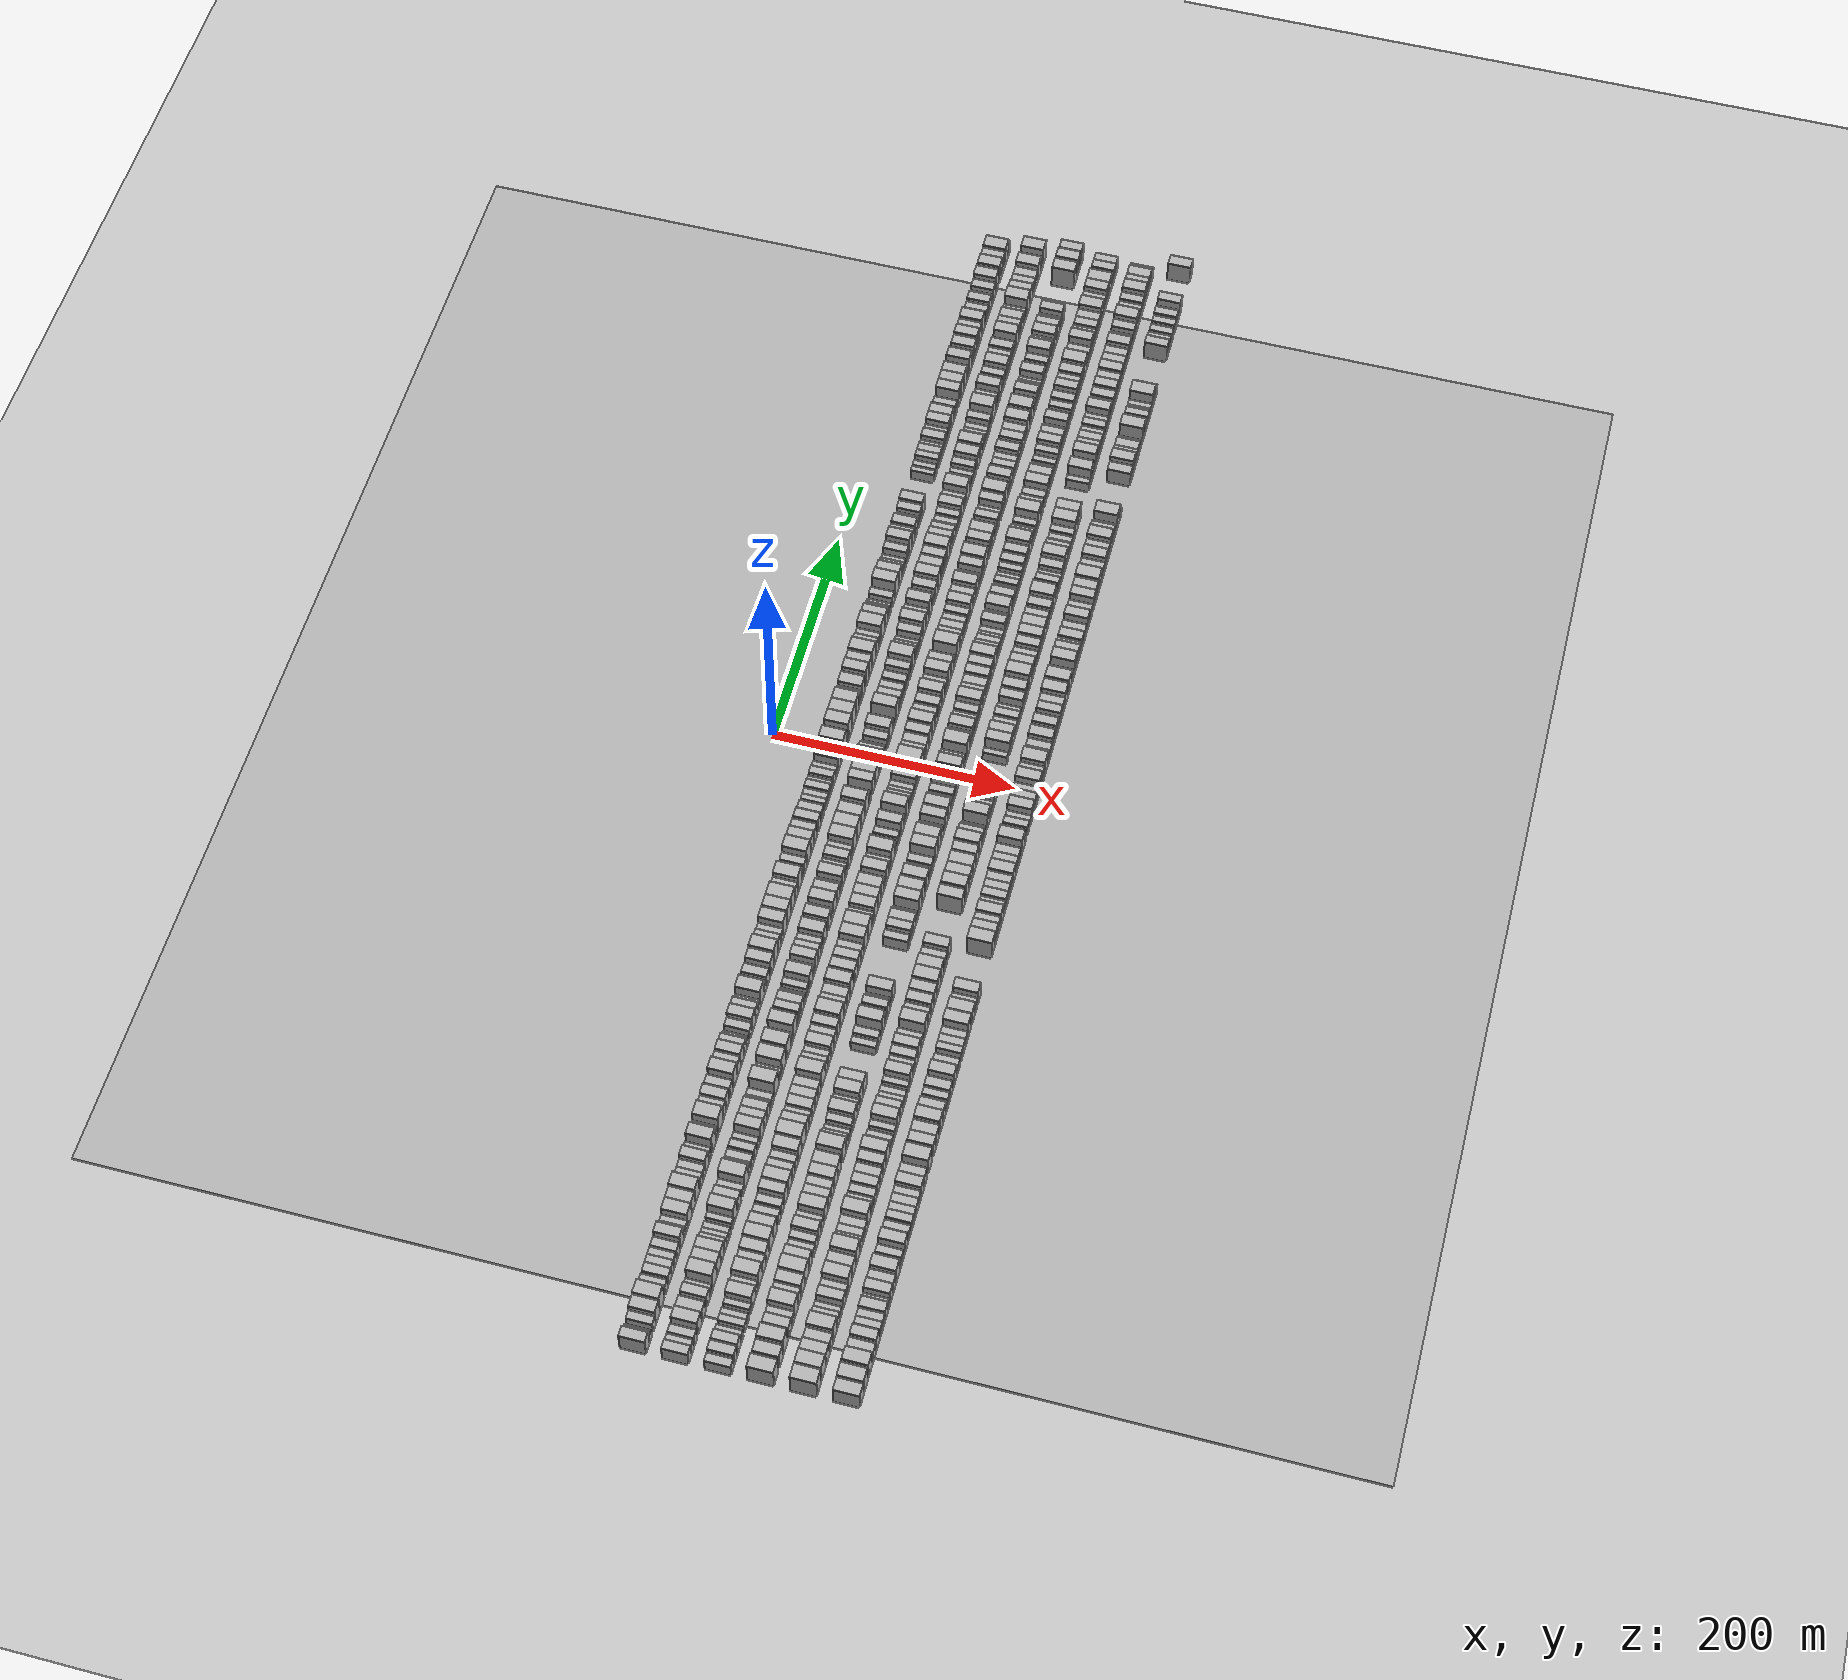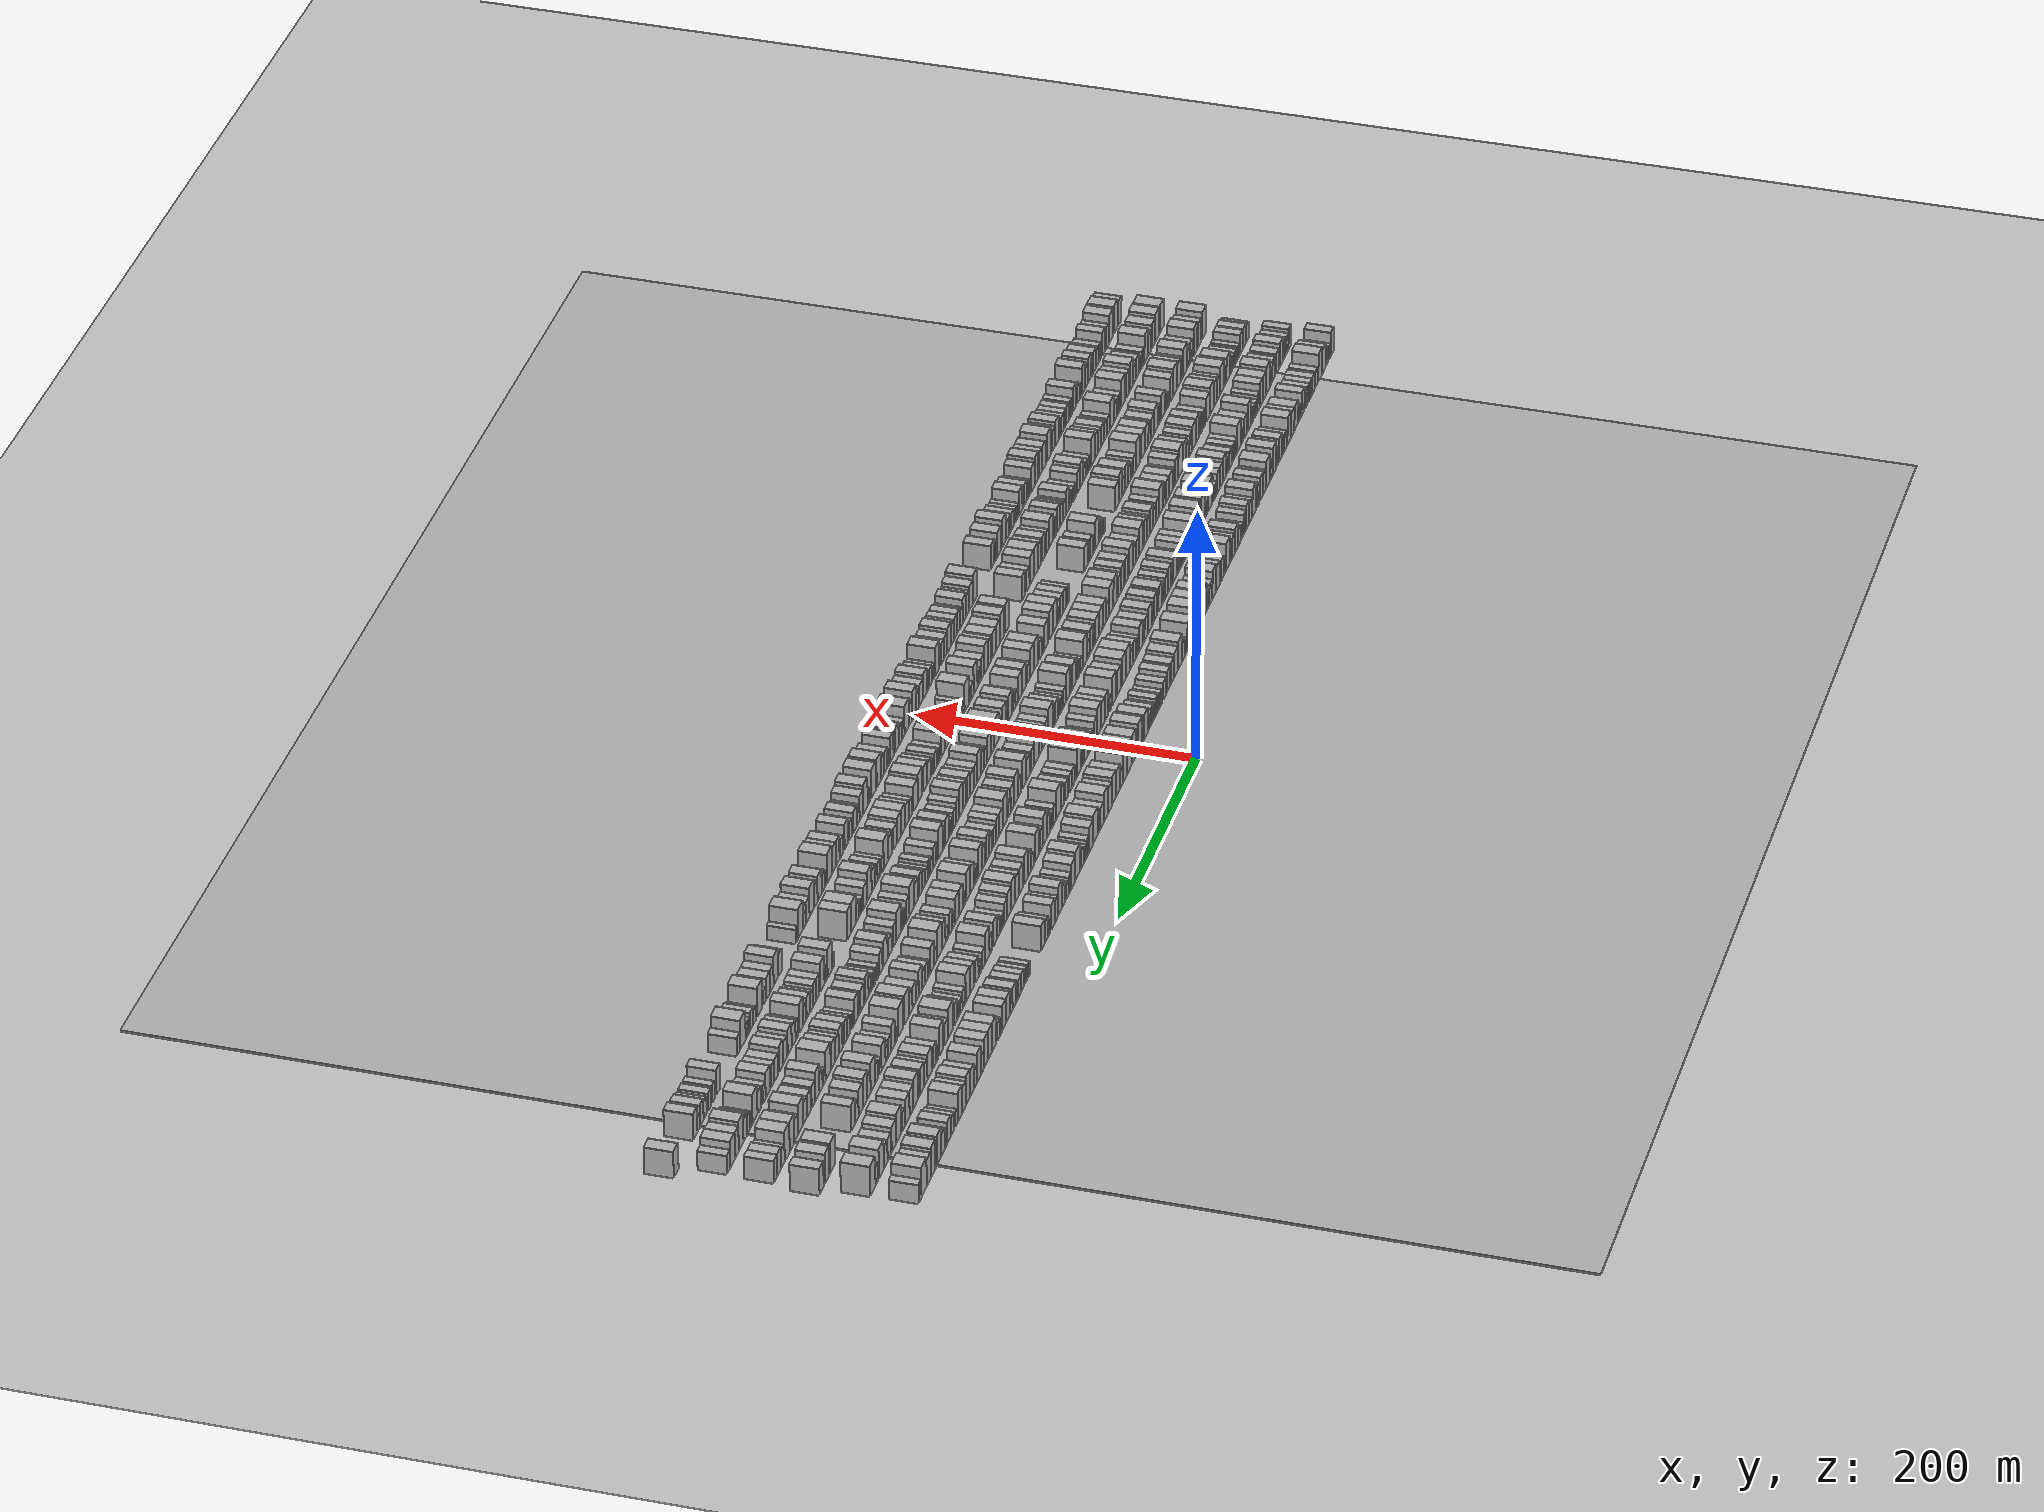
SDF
<?xml version="1.0" encoding="utf-8"?>

<sdf version="1.6">

   <world name="default">

      <gui fullscreen="0">

         <camera name="user_camera">

            <pose>-15 0 4.57585 0 0 0</pose>

            <view_controller>orbit</view_controller>

         </camera>

      </gui>

      <scene>

         <sky>

           <clouds>

             <speed>12</speed>

           </clouds>

         </sky>

         <ambient>0.4 0.4 0.4 1</ambient>

         <background>0.7 0.7 0.7 1</background>

         <shadows>1</shadows>

      </scene>

      <gravity>0 0 -9.8066</gravity>

      <magnetic_field>6e-06 2.3e-05 -4.2e-05</magnetic_field>

      <physics default="0" name="default_physics" type="ode">

         <ode>

            <solver>

               <type>quick</type>

               <iters>10</iters>

               <sor>1.0</sor>

               <use_dynamic_moi_rescaling>0</use_dynamic_moi_rescaling>

            </solver>

            <constraints>

               <cfm>0</cfm>

               <erp>0.2</erp>

               <contact_max_correcting_vel>100</contact_max_correcting_vel>

               <contact_surface_layer>0.001</contact_surface_layer>

            </constraints>

         </ode>

         <max_step_size>0.004</max_step_size>

         <real_time_factor>1</real_time_factor>

         <real_time_update_rate>250</real_time_update_rate>

      </physics>

      <light name="sun" type="directional">

         <cast_shadows>1</cast_shadows>

         <pose>0 0 10 0 0 0</pose>

         <diffuse>0.8 0.8 0.8 1</diffuse>

         <specular>0.2 0.2 0.2 1</specular>

         <attenuation>

            <range>1000</range>

            <constant>0.9</constant>

            <linear>0.01</linear>

            <quadratic>0.001</quadratic>

         </attenuation>

         <direction>-0.5 0.1 -0.9</direction>

      </light>

      <include>

         <name>ground_plane_1</name>

         <uri>model://HANNAS_ground_plane</uri>

         <pose>0 0 0  0 0 0</pose>

      </include>

      <include>

         <name>ground_plane_2</name>

         <uri>model://HANNAS_ground_plane</uri>

         <pose>100 0 0  0 0 0</pose>

      </include>

      <model name="building_1">

         <static>1</static>

         <pose frame="">50.0000 -535.6946 0 0.000000 0.000000 0.000000</pose>

         <link name="link">

            <pose frame="">0 0 10.50 0 0 0</pose>

            <collision name="collision">

               <geometry>

                  <box>

                     <size>20.0000 8.6108 21.0000</size>

                  </box>

               </geometry>

               <max_contacts>10</max_contacts>

               <surface>

                  <contact>

                     <ode/>

                  </contact>

                  <bounce/>

                  <friction>

                     <torsional>

                        <ode/>

                     </torsional>

                     <ode/>

                  </friction>

               </surface>

            </collision>

            <visual name="visual">

               <cast_shadows>0</cast_shadows>

               <geometry>

                  <box>

                     <size>20.0000 8.6108 21.0000</size>

                  </box>

               </geometry>

               <material>

                  <script>

                     <uri>model://HANNAS_wall/materials/scripts</uri>

                     <uri>model://HANNAS_wall/materials/textures</uri>

                     <name>vrc/HANNAS_wall</name>

                  </script>

               </material>

            </visual>

            <self_collide>0</self_collide>

            <enable_wind>0</enable_wind>

            <kinematic>0</kinematic>

         </link>

      </model>

      <model name="building_2">

         <static>1</static>

         <pose frame="">50.0000 -528.5945 0 0.000000 0.000000 0.000000</pose>

         <link name="link">

            <pose frame="">0 0 6.00 0 0 0</pose>

            <collision name="collision">

               <geometry>

                  <box>

                     <size>20.0000 5.5894 12.0000</size>

                  </box>

               </geometry>

               <max_contacts>10</max_contacts>

               <surface>

                  <contact>

                     <ode/>

                  </contact>

                  <bounce/>

                  <friction>

                     <torsional>

                        <ode/>

                     </torsional>

                     <ode/>

                  </friction>

               </surface>

            </collision>

            <visual name="visual">

               <cast_shadows>0</cast_shadows>

               <geometry>

                  <box>

                     <size>20.0000 5.5894 12.0000</size>

                  </box>

               </geometry>

               <material>

                  <script>

                     <uri>model://HANNAS_wall/materials/scripts</uri>

                     <uri>model://HANNAS_wall/materials/textures</uri>

                     <name>vrc/HANNAS_wall</name>

                  </script>

               </material>

            </visual>

            <self_collide>0</self_collide>

            <enable_wind>0</enable_wind>

            <kinematic>0</kinematic>

         </link>

      </model>

      <model name="building_3">

         <static>1</static>

         <pose frame="">50.0000 -519.3449 0 0.000000 0.000000 0.000000</pose>

         <link name="link">

            <pose frame="">0 0 7.50 0 0 0</pose>

            <collision name="collision">

               <geometry>

                  <box>

                     <size>20.0000 6.9099 15.0000</size>

                  </box>

               </geometry>

               <max_contacts>10</max_contacts>

               <surface>

                  <contact>

                     <ode/>

                  </contact>

                  <bounce/>

                  <friction>

                     <torsional>

                        <ode/>

                     </torsional>

                     <ode/>

                  </friction>

               </surface>

            </collision>

            <visual name="visual">

               <cast_shadows>0</cast_shadows>

               <geometry>

                  <box>

                     <size>20.0000 6.9099 15.0000</size>

                  </box>

               </geometry>

               <material>

                  <script>

                     <uri>model://HANNAS_wall/materials/scripts</uri>

                     <uri>model://HANNAS_wall/materials/textures</uri>

                     <name>vrc/HANNAS_wall</name>

                  </script>

               </material>

            </visual>

            <self_collide>0</self_collide>

            <enable_wind>0</enable_wind>

            <kinematic>0</kinematic>

         </link>

      </model>

      <model name="building_4">

         <static>1</static>

         <pose frame="">50.0000 -510.8784 0 0.000000 0.000000 0.000000</pose>

         <link name="link">

            <pose frame="">0 0 10.50 0 0 0</pose>

            <collision name="collision">

               <geometry>

                  <box>

                     <size>20.0000 10.0230 21.0000</size>

                  </box>

               </geometry>

               <max_contacts>10</max_contacts>

               <surface>

                  <contact>

                     <ode/>

                  </contact>

                  <bounce/>

                  <friction>

                     <torsional>

                        <ode/>

                     </torsional>

                     <ode/>

                  </friction>

               </surface>

            </collision>

            <visual name="visual">

               <cast_shadows>0</cast_shadows>

               <geometry>

                  <box>

                     <size>20.0000 10.0230 21.0000</size>

                  </box>

               </geometry>

               <material>

                  <script>

                     <uri>model://HANNAS_wall/materials/scripts</uri>

                     <uri>model://HANNAS_wall/materials/textures</uri>

                     <name>vrc/HANNAS_wall</name>

                  </script>

               </material>

            </visual>

            <self_collide>0</self_collide>

            <enable_wind>0</enable_wind>

            <kinematic>0</kinematic>

         </link>

      </model>

      <model name="building_5">

         <static>1</static>

         <pose frame="">50.0000 -500.2681 0 0.000000 0.000000 0.000000</pose>

         <link name="link">

            <pose frame="">0 0 12.00 0 0 0</pose>

            <collision name="collision">

               <geometry>

                  <box>

                     <size>20.0000 11.1976 24.0000</size>

                  </box>

               </geometry>

               <max_contacts>10</max_contacts>

               <surface>

                  <contact>

                     <ode/>

                  </contact>

                  <bounce/>

                  <friction>

                     <torsional>

                        <ode/>

                     </torsional>

                     <ode/>

                  </friction>

               </surface>

            </collision>

            <visual name="visual">

               <cast_shadows>0</cast_shadows>

               <geometry>

                  <box>

                     <size>20.0000 11.1976 24.0000</size>

                  </box>

               </geometry>

               <material>

                  <script>

                     <uri>model://HANNAS_wall/materials/scripts</uri>

                     <uri>model://HANNAS_wall/materials/textures</uri>

                     <name>vrc/HANNAS_wall</name>

                  </script>

               </material>

            </visual>

            <self_collide>0</self_collide>

            <enable_wind>0</enable_wind>

            <kinematic>0</kinematic>

         </link>

      </model>

      <model name="building_6">

         <static>1</static>

         <pose frame="">50.0000 -489.2908 0 0.000000 0.000000 0.000000</pose>

         <link name="link">

            <pose frame="">0 0 7.50 0 0 0</pose>

            <collision name="collision">

               <geometry>

                  <box>

                     <size>20.0000 6.7569 15.0000</size>

                  </box>

               </geometry>

               <max_contacts>10</max_contacts>

               <surface>

                  <contact>

                     <ode/>

                  </contact>

                  <bounce/>

                  <friction>

                     <torsional>

                        <ode/>

                     </torsional>

                     <ode/>

                  </friction>

               </surface>

            </collision>

            <visual name="visual">

               <cast_shadows>0</cast_shadows>

               <geometry>

                  <box>

                     <size>20.0000 6.7569 15.0000</size>

                  </box>

               </geometry>

               <material>

                  <script>

                     <uri>model://HANNAS_wall/materials/scripts</uri>

                     <uri>model://HANNAS_wall/materials/textures</uri>

                     <name>vrc/HANNAS_wall</name>

                  </script>

               </material>

            </visual>

            <self_collide>0</self_collide>

            <enable_wind>0</enable_wind>

            <kinematic>0</kinematic>

         </link>

      </model>

      <model name="building_7">

         <static>1</static>

         <pose frame="">50.0000 -480.1677 0 0.000000 0.000000 0.000000</pose>

         <link name="link">

            <pose frame="">0 0 7.50 0 0 0</pose>

            <collision name="collision">

               <geometry>

                  <box>

                     <size>20.0000 7.4892 15.0000</size>

                  </box>

               </geometry>

               <max_contacts>10</max_contacts>

               <surface>

                  <contact>

                     <ode/>

                  </contact>

                  <bounce/>

                  <friction>

                     <torsional>

                        <ode/>

                     </torsional>

                     <ode/>

                  </friction>

               </surface>

            </collision>

            <visual name="visual">

               <cast_shadows>0</cast_shadows>

               <geometry>

                  <box>

                     <size>20.0000 7.4892 15.0000</size>

                  </box>

               </geometry>

               <material>

                  <script>

                     <uri>model://HANNAS_wall/materials/scripts</uri>

                     <uri>model://HANNAS_wall/materials/textures</uri>

                     <name>vrc/HANNAS_wall</name>

                  </script>

               </material>

            </visual>

            <self_collide>0</self_collide>

            <enable_wind>0</enable_wind>

            <kinematic>0</kinematic>

         </link>

      </model>

      <model name="building_8">

         <static>1</static>

         <pose frame="">50.0000 -473.1061 0 0.000000 0.000000 0.000000</pose>

         <link name="link">

            <pose frame="">0 0 7.50 0 0 0</pose>

            <collision name="collision">

               <geometry>

                  <box>

                     <size>20.0000 6.6341 15.0000</size>

                  </box>

               </geometry>

               <max_contacts>10</max_contacts>

               <surface>

                  <contact>

                     <ode/>

                  </contact>

                  <bounce/>

                  <friction>

                     <torsional>

                        <ode/>

                     </torsional>

                     <ode/>

                  </friction>

               </surface>

            </collision>

            <visual name="visual">

               <cast_shadows>0</cast_shadows>

               <geometry>

                  <box>

                     <size>20.0000 6.6341 15.0000</size>

                  </box>

               </geometry>

               <material>

                  <script>

                     <uri>model://HANNAS_wall/materials/scripts</uri>

                     <uri>model://HANNAS_wall/materials/textures</uri>

                     <name>vrc/HANNAS_wall</name>

                  </script>

               </material>

            </visual>

            <self_collide>0</self_collide>

            <enable_wind>0</enable_wind>

            <kinematic>0</kinematic>

         </link>

      </model>

      <model name="building_9">

         <static>1</static>

         <pose frame="">50.0000 -466.7737 0 0.000000 0.000000 0.000000</pose>

         <link name="link">

            <pose frame="">0 0 7.50 0 0 0</pose>

            <collision name="collision">

               <geometry>

                  <box>

                     <size>20.0000 6.0306 15.0000</size>

                  </box>

               </geometry>

               <max_contacts>10</max_contacts>

               <surface>

                  <contact>

                     <ode/>

                  </contact>

                  <bounce/>

                  <friction>

                     <torsional>

                        <ode/>

                     </torsional>

                     <ode/>

                  </friction>

               </surface>

            </collision>

            <visual name="visual">

               <cast_shadows>0</cast_shadows>

               <geometry>

                  <box>

                     <size>20.0000 6.0306 15.0000</size>

                  </box>

               </geometry>

               <material>

                  <script>

                     <uri>model://HANNAS_wall/materials/scripts</uri>

                     <uri>model://HANNAS_wall/materials/textures</uri>

                     <name>vrc/HANNAS_wall</name>

                  </script>

               </material>

            </visual>

            <self_collide>0</self_collide>

            <enable_wind>0</enable_wind>

            <kinematic>0</kinematic>

         </link>

      </model>

      <model name="building_10">

         <static>1</static>

         <pose frame="">50.0000 -459.0186 0 0.000000 0.000000 0.000000</pose>

         <link name="link">

            <pose frame="">0 0 7.50 0 0 0</pose>

            <collision name="collision">

               <geometry>

                  <box>

                     <size>20.0000 7.4796 15.0000</size>

                  </box>

               </geometry>

               <max_contacts>10</max_contacts>

               <surface>

                  <contact>

                     <ode/>

                  </contact>

                  <bounce/>

                  <friction>

                     <torsional>

                        <ode/>

                     </torsional>

                     <ode/>

                  </friction>

               </surface>

            </collision>

            <visual name="visual">

               <cast_shadows>0</cast_shadows>

               <geometry>

                  <box>

                     <size>20.0000 7.4796 15.0000</size>

                  </box>

               </geometry>

               <material>

                  <script>

                     <uri>model://HANNAS_wall/materials/scripts</uri>

                     <uri>model://HANNAS_wall/materials/textures</uri>

                     <name>vrc/HANNAS_wall</name>

                  </script>

               </material>

            </visual>

            <self_collide>0</self_collide>

            <enable_wind>0</enable_wind>

            <kinematic>0</kinematic>

         </link>

      </model>

      <model name="building_11">

         <static>1</static>

         <pose frame="">50.0000 -449.9481 0 0.000000 0.000000 0.000000</pose>

         <link name="link">

            <pose frame="">0 0 10.50 0 0 0</pose>

            <collision name="collision">

               <geometry>

                  <box>

                     <size>20.0000 8.6615 21.0000</size>

                  </box>

               </geometry>

               <max_contacts>10</max_contacts>

               <surface>

                  <contact>

                     <ode/>

                  </contact>

                  <bounce/>

                  <friction>

                     <torsional>

                        <ode/>

                     </torsional>

                     <ode/>

                  </friction>

               </surface>

            </collision>

            <visual name="visual">

               <cast_shadows>0</cast_shadows>

               <geometry>

                  <box>

                     <size>20.0000 8.6615 21.0000</size>

                  </box>

               </geometry>

               <material>

                  <script>

                     <uri>model://HANNAS_wall/materials/scripts</uri>

                     <uri>model://HANNAS_wall/materials/textures</uri>

                     <name>vrc/HANNAS_wall</name>

                  </script>

               </material>

            </visual>

            <self_collide>0</self_collide>

            <enable_wind>0</enable_wind>

            <kinematic>0</kinematic>

         </link>

      </model>

      <model name="building_12">

         <static>1</static>

         <pose frame="">50.0000 -443.0723 0 0.000000 0.000000 0.000000</pose>

         <link name="link">

            <pose frame="">0 0 6.00 0 0 0</pose>

            <collision name="collision">

               <geometry>

                  <box>

                     <size>20.0000 5.0902 12.0000</size>

                  </box>

               </geometry>

               <max_contacts>10</max_contacts>

               <surface>

                  <contact>

                     <ode/>

                  </contact>

                  <bounce/>

                  <friction>

                     <torsional>

                        <ode/>

                     </torsional>

                     <ode/>

                  </friction>

               </surface>

            </collision>

            <visual name="visual">

               <cast_shadows>0</cast_shadows>

               <geometry>

                  <box>

                     <size>20.0000 5.0902 12.0000</size>

                  </box>

               </geometry>

               <material>

                  <script>

                     <uri>model://HANNAS_wall/materials/scripts</uri>

                     <uri>model://HANNAS_wall/materials/textures</uri>

                     <name>vrc/HANNAS_wall</name>

                  </script>

               </material>

            </visual>

            <self_collide>0</self_collide>

            <enable_wind>0</enable_wind>

            <kinematic>0</kinematic>

         </link>

      </model>

      <model name="building_13">

         <static>1</static>

         <pose frame="">50.0000 -437.9258 0 0.000000 0.000000 0.000000</pose>

         <link name="link">

            <pose frame="">0 0 6.00 0 0 0</pose>

            <collision name="collision">

               <geometry>

                  <box>

                     <size>20.0000 5.2027 12.0000</size>

                  </box>

               </geometry>

               <max_contacts>10</max_contacts>

               <surface>

                  <contact>

                     <ode/>

                  </contact>

                  <bounce/>

                  <friction>

                     <torsional>

                        <ode/>

                     </torsional>

                     <ode/>

                  </friction>

               </surface>

            </collision>

            <visual name="visual">

               <cast_shadows>0</cast_shadows>

               <geometry>

                  <box>

                     <size>20.0000 5.2027 12.0000</size>

                  </box>

               </geometry>

               <material>

                  <script>

                     <uri>model://HANNAS_wall/materials/scripts</uri>

                     <uri>model://HANNAS_wall/materials/textures</uri>

                     <name>vrc/HANNAS_wall</name>

                  </script>

               </material>

            </visual>

            <self_collide>0</self_collide>

            <enable_wind>0</enable_wind>

            <kinematic>0</kinematic>

         </link>

      </model>

      <model name="building_14">

         <static>1</static>

         <pose frame="">50.0000 -430.2669 0 0.000000 0.000000 0.000000</pose>

         <link name="link">

            <pose frame="">0 0 10.50 0 0 0</pose>

            <collision name="collision">

               <geometry>

                  <box>

                     <size>20.0000 10.1152 21.0000</size>

                  </box>

               </geometry>

               <max_contacts>10</max_contacts>

               <surface>

                  <contact>

                     <ode/>

                  </contact>

                  <bounce/>

                  <friction>

                     <torsional>

                        <ode/>

                     </torsional>

                     <ode/>

                  </friction>

               </surface>

            </collision>

            <visual name="visual">

               <cast_shadows>0</cast_shadows>

               <geometry>

                  <box>

                     <size>20.0000 10.1152 21.0000</size>

                  </box>

               </geometry>

               <material>

                  <script>

                     <uri>model://HANNAS_wall/materials/scripts</uri>

                     <uri>model://HANNAS_wall/materials/textures</uri>

                     <name>vrc/HANNAS_wall</name>

                  </script>

               </material>

            </visual>

            <self_collide>0</self_collide>

            <enable_wind>0</enable_wind>

            <kinematic>0</kinematic>

         </link>

      </model>

      <model name="building_15">

         <static>1</static>

         <pose frame="">50.0000 -420.4977 0 0.000000 0.000000 0.000000</pose>

         <link name="link">

            <pose frame="">0 0 10.50 0 0 0</pose>

            <collision name="collision">

               <geometry>

                  <box>

                     <size>20.0000 9.4233 21.0000</size>

                  </box>

               </geometry>

               <max_contacts>10</max_contacts>

               <surface>

                  <contact>

                     <ode/>

                  </contact>

                  <bounce/>

                  <friction>

                     <torsional>

                        <ode/>

                     </torsional>

                     <ode/>

                  </friction>

               </surface>

            </collision>

            <visual name="visual">

               <cast_shadows>0</cast_shadows>

               <geometry>

                  <box>

                     <size>20.0000 9.4233 21.0000</size>

                  </box>

               </geometry>

               <material>

                  <script>

                     <uri>model://HANNAS_wall/materials/scripts</uri>

                     <uri>model://HANNAS_wall/materials/textures</uri>

                     <name>vrc/HANNAS_wall</name>

                  </script>

               </material>

            </visual>

            <self_collide>0</self_collide>

            <enable_wind>0</enable_wind>

            <kinematic>0</kinematic>

         </link>

      </model>

      <model name="building_16">

         <static>1</static>

         <pose frame="">50.0000 -410.4962 0 0.000000 0.000000 0.000000</pose>

         <link name="link">

            <pose frame="">0 0 12.00 0 0 0</pose>

            <collision name="collision">

               <geometry>

                  <box>

                     <size>20.0000 10.5796 24.0000</size>

                  </box>

               </geometry>

               <max_contacts>10</max_contacts>

               <surface>

                  <contact>

                     <ode/>

                  </contact>

                  <bounce/>

                  <friction>

                     <torsional>

                        <ode/>

                     </torsional>

                     <ode/>

                  </friction>

               </surface>

            </collision>

            <visual name="visual">

               <cast_shadows>0</cast_shadows>

               <geometry>

                  <box>

                     <size>20.0000 10.5796 24.0000</size>

                  </box>

               </geometry>

               <material>

                  <script>

                     <uri>model://HANNAS_wall/materials/scripts</uri>

                     <uri>model://HANNAS_wall/materials/textures</uri>

                     <name>vrc/HANNAS_wall</name>

                  </script>

               </material>

            </visual>

            <self_collide>0</self_collide>

            <enable_wind>0</enable_wind>

            <kinematic>0</kinematic>

         </link>

      </model>

      <model name="building_17">

         <static>1</static>

         <pose frame="">50.0000 -399.8020 0 0.000000 0.000000 0.000000</pose>

         <link name="link">

            <pose frame="">0 0 7.50 0 0 0</pose>

            <collision name="collision">

               <geometry>

                  <box>

                     <size>20.0000 6.8087 15.0000</size>

                  </box>

               </geometry>

               <max_contacts>10</max_contacts>

               <surface>

                  <contact>

                     <ode/>

                  </contact>

                  <bounce/>

                  <friction>

                     <torsional>

                        <ode/>

                     </torsional>

                     <ode/>

                  </friction>

               </surface>

            </collision>

            <visual name="visual">

               <cast_shadows>0</cast_shadows>

               <geometry>

                  <box>

                     <size>20.0000 6.8087 15.0000</size>

                  </box>

               </geometry>

               <material>

                  <script>

                     <uri>model://HANNAS_wall/materials/scripts</uri>

                     <uri>model://HANNAS_wall/materials/textures</uri>

                     <name>vrc/HANNAS_wall</name>

                  </script>

               </material>

            </visual>

            <self_collide>0</self_collide>

            <enable_wind>0</enable_wind>

            <kinematic>0</kinematic>

         </link>

      </model>

      <model name="building_18">

         <static>1</static>

         <pose frame="">50.0000 -393.0594 0 0.000000 0.000000 0.000000</pose>

         <link name="link">

            <pose frame="">0 0 7.50 0 0 0</pose>

            <collision name="collision">

               <geometry>

                  <box>

                     <size>20.0000 6.6766 15.0000</size>

                  </box>

               </geometry>

               <max_contacts>10</max_contacts>

               <surface>

                  <contact>

                     <ode/>

                  </contact>

                  <bounce/>

                  <friction>

                     <torsional>

                        <ode/>

                     </torsional>

                     <ode/>

                  </friction>

               </surface>

            </collision>

            <visual name="visual">

               <cast_shadows>0</cast_shadows>

               <geometry>

                  <box>

                     <size>20.0000 6.6766 15.0000</size>

                  </box>

               </geometry>

               <material>

                  <script>

                     <uri>model://HANNAS_wall/materials/scripts</uri>

                     <uri>model://HANNAS_wall/materials/textures</uri>

                     <name>vrc/HANNAS_wall</name>

                  </script>

               </material>

            </visual>

            <self_collide>0</self_collide>

            <enable_wind>0</enable_wind>

            <kinematic>0</kinematic>

         </link>

      </model>

      <model name="building_19">

         <static>1</static>

         <pose frame="">50.0000 -385.4042 0 0.000000 0.000000 0.000000</pose>

         <link name="link">

            <pose frame="">0 0 10.50 0 0 0</pose>

            <collision name="collision">

               <geometry>

                  <box>

                     <size>20.0000 8.6337 21.0000</size>

                  </box>

               </geometry>

               <max_contacts>10</max_contacts>

               <surface>

                  <contact>

                     <ode/>

                  </contact>

                  <bounce/>

                  <friction>

                     <torsional>

                        <ode/>

                     </torsional>

                     <ode/>

                  </friction>

               </surface>

            </collision>

            <visual name="visual">

               <cast_shadows>0</cast_shadows>

               <geometry>

                  <box>

                     <size>20.0000 8.6337 21.0000</size>

                  </box>

               </geometry>

               <material>

                  <script>

                     <uri>model://HANNAS_wall/materials/scripts</uri>

                     <uri>model://HANNAS_wall/materials/textures</uri>

                     <name>vrc/HANNAS_wall</name>

                  </script>

               </material>

            </visual>

            <self_collide>0</self_collide>

            <enable_wind>0</enable_wind>

            <kinematic>0</kinematic>

         </link>

      </model>

      <model name="building_20">

         <static>1</static>

         <pose frame="">50.0000 -377.9456 0 0.000000 0.000000 0.000000</pose>

         <link name="link">

            <pose frame="">0 0 7.50 0 0 0</pose>

            <collision name="collision">

               <geometry>

                  <box>

                     <size>20.0000 6.2836 15.0000</size>

                  </box>

               </geometry>

               <max_contacts>10</max_contacts>

               <surface>

                  <contact>

                     <ode/>

                  </contact>

                  <bounce/>

                  <friction>

                     <torsional>

                        <ode/>

                     </torsional>

                     <ode/>

                  </friction>

               </surface>

            </collision>

            <visual name="visual">

               <cast_shadows>0</cast_shadows>

               <geometry>

                  <box>

                     <size>20.0000 6.2836 15.0000</size>

                  </box>

               </geometry>

               <material>

                  <script>

                     <uri>model://HANNAS_wall/materials/scripts</uri>

                     <uri>model://HANNAS_wall/materials/textures</uri>

                     <name>vrc/HANNAS_wall</name>

                  </script>

               </material>

            </visual>

            <self_collide>0</self_collide>

            <enable_wind>0</enable_wind>

            <kinematic>0</kinematic>

         </link>

      </model>

      <model name="building_21">

         <static>1</static>

         <pose frame="">50.0000 -367.7243 0 0.000000 0.000000 0.000000</pose>

         <link name="link">

            <pose frame="">0 0 12.00 0 0 0</pose>

            <collision name="collision">

               <geometry>

                  <box>

                     <size>20.0000 10.1591 24.0000</size>

                  </box>

               </geometry>

               <max_contacts>10</max_contacts>

               <surface>

                  <contact>

                     <ode/>

                  </contact>

                  <bounce/>

                  <friction>

                     <torsional>

                        <ode/>

                     </torsional>

                     <ode/>

                  </friction>

               </surface>

            </collision>

            <visual name="visual">

               <cast_shadows>0</cast_shadows>

               <geometry>

                  <box>

                     <size>20.0000 10.1591 24.0000</size>

                  </box>

               </geometry>

               <material>

                  <script>

                     <uri>model://HANNAS_wall/materials/scripts</uri>

                     <uri>model://HANNAS_wall/materials/textures</uri>

                     <name>vrc/HANNAS_wall</name>

                  </script>

               </material>

            </visual>

            <self_collide>0</self_collide>

            <enable_wind>0</enable_wind>

            <kinematic>0</kinematic>

         </link>

      </model>

      <model name="building_22">

         <static>1</static>

         <pose frame="">50.0000 -359.6433 0 0.000000 0.000000 0.000000</pose>

         <link name="link">

            <pose frame="">0 0 7.50 0 0 0</pose>

            <collision name="collision">

               <geometry>

                  <box>

                     <size>20.0000 6.0029 15.0000</size>

                  </box>

               </geometry>

               <max_contacts>10</max_contacts>

               <surface>

                  <contact>

                     <ode/>

                  </contact>

                  <bounce/>

                  <friction>

                     <torsional>

                        <ode/>

                     </torsional>

                     <ode/>

                  </friction>

               </surface>

            </collision>

            <visual name="visual">

               <cast_shadows>0</cast_shadows>

               <geometry>

                  <box>

                     <size>20.0000 6.0029 15.0000</size>

                  </box>

               </geometry>

               <material>

                  <script>

                     <uri>model://HANNAS_wall/materials/scripts</uri>

                     <uri>model://HANNAS_wall/materials/textures</uri>

                     <name>vrc/HANNAS_wall</name>

                  </script>

               </material>

            </visual>

            <self_collide>0</self_collide>

            <enable_wind>0</enable_wind>

            <kinematic>0</kinematic>

         </link>

      </model>

      <model name="building_23">

         <static>1</static>

         <pose frame="">50.0000 -349.7255 0 0.000000 0.000000 0.000000</pose>

         <link name="link">

            <pose frame="">0 0 12.00 0 0 0</pose>

            <collision name="collision">

               <geometry>

                  <box>

                     <size>20.0000 11.8326 24.0000</size>

                  </box>

               </geometry>

               <max_contacts>10</max_contacts>

               <surface>

                  <contact>

                     <ode/>

                  </contact>

                  <bounce/>

                  <friction>

                     <torsional>

                        <ode/>

                     </torsional>

                     <ode/>

                  </friction>

               </surface>

            </collision>

            <visual name="visual">

               <cast_shadows>0</cast_shadows>

               <geometry>

                  <box>

                     <size>20.0000 11.8326 24.0000</size>

                  </box>

               </geometry>

               <material>

                  <script>

                     <uri>model://HANNAS_wall/materials/scripts</uri>

                     <uri>model://HANNAS_wall/materials/textures</uri>

                     <name>vrc/HANNAS_wall</name>

                  </script>

               </material>

            </visual>

            <self_collide>0</self_collide>

            <enable_wind>0</enable_wind>

            <kinematic>0</kinematic>

         </link>

      </model>

      <model name="building_24">

         <static>1</static>

         <pose frame="">50.0000 -340.0183 0 0.000000 0.000000 0.000000</pose>

         <link name="link">

            <pose frame="">0 0 9.00 0 0 0</pose>

            <collision name="collision">

               <geometry>

                  <box>

                     <size>20.0000 7.5818 18.0000</size>

                  </box>

               </geometry>

               <max_contacts>10</max_contacts>

               <surface>

                  <contact>

                     <ode/>

                  </contact>

                  <bounce/>

                  <friction>

                     <torsional>

                        <ode/>

                     </torsional>

                     <ode/>

                  </friction>

               </surface>

            </collision>

            <visual name="visual">

               <cast_shadows>0</cast_shadows>

               <geometry>

                  <box>

                     <size>20.0000 7.5818 18.0000</size>

                  </box>

               </geometry>

               <material>

                  <script>

                     <uri>model://HANNAS_wall/materials/scripts</uri>

                     <uri>model://HANNAS_wall/materials/textures</uri>

                     <name>vrc/HANNAS_wall</name>

                  </script>

               </material>

            </visual>

            <self_collide>0</self_collide>

            <enable_wind>0</enable_wind>

            <kinematic>0</kinematic>

         </link>

      </model>

      <model name="building_25">

         <static>1</static>

         <pose frame="">50.0000 -331.8729 0 0.000000 0.000000 0.000000</pose>

         <link name="link">

            <pose frame="">0 0 10.50 0 0 0</pose>

            <collision name="collision">

               <geometry>

                  <box>

                     <size>20.0000 8.7090 21.0000</size>

                  </box>

               </geometry>

               <max_contacts>10</max_contacts>

               <surface>

                  <contact>

                     <ode/>

                  </contact>

                  <bounce/>

                  <friction>

                     <torsional>

                        <ode/>

                     </torsional>

                     <ode/>

                  </friction>

               </surface>

            </collision>

            <visual name="visual">

               <cast_shadows>0</cast_shadows>

               <geometry>

                  <box>

                     <size>20.0000 8.7090 21.0000</size>

                  </box>

               </geometry>

               <material>

                  <script>

                     <uri>model://HANNAS_wall/materials/scripts</uri>

                     <uri>model://HANNAS_wall/materials/textures</uri>

                     <name>vrc/HANNAS_wall</name>

                  </script>

               </material>

            </visual>

            <self_collide>0</self_collide>

            <enable_wind>0</enable_wind>

            <kinematic>0</kinematic>

         </link>

      </model>

      <model name="building_26">

         <static>1</static>

         <pose frame="">50.0000 -321.7021 0 0.000000 0.000000 0.000000</pose>

         <link name="link">

            <pose frame="">0 0 9.00 0 0 0</pose>

            <collision name="collision">

               <geometry>

                  <box>

                     <size>20.0000 7.6327 18.0000</size>

                  </box>

               </geometry>

               <max_contacts>10</max_contacts>

               <surface>

                  <contact>

                     <ode/>

                  </contact>

                  <bounce/>

                  <friction>

                     <torsional>

                        <ode/>

                     </torsional>

                     <ode/>

                  </friction>

               </surface>

            </collision>

            <visual name="visual">

               <cast_shadows>0</cast_shadows>

               <geometry>

                  <box>

                     <size>20.0000 7.6327 18.0000</size>

                  </box>

               </geometry>

               <material>

                  <script>

                     <uri>model://HANNAS_wall/materials/scripts</uri>

                     <uri>model://HANNAS_wall/materials/textures</uri>

                     <name>vrc/HANNAS_wall</name>

                  </script>

               </material>

            </visual>

            <self_collide>0</self_collide>

            <enable_wind>0</enable_wind>

            <kinematic>0</kinematic>

         </link>

      </model>

      <model name="building_27">

         <static>1</static>

         <pose frame="">50.0000 -310.7691 0 0.000000 0.000000 0.000000</pose>

         <link name="link">

            <pose frame="">0 0 12.00 0 0 0</pose>

            <collision name="collision">

               <geometry>

                  <box>

                     <size>20.0000 10.2333 24.0000</size>

                  </box>

               </geometry>

               <max_contacts>10</max_contacts>

               <surface>

                  <contact>

                     <ode/>

                  </contact>

                  <bounce/>

                  <friction>

                     <torsional>

                        <ode/>

                     </torsional>

                     <ode/>

                  </friction>

               </surface>

            </collision>

            <visual name="visual">

               <cast_shadows>0</cast_shadows>

               <geometry>

                  <box>

                     <size>20.0000 10.2333 24.0000</size>

                  </box>

               </geometry>

               <material>

                  <script>

                     <uri>model://HANNAS_wall/materials/scripts</uri>

                     <uri>model://HANNAS_wall/materials/textures</uri>

                     <name>vrc/HANNAS_wall</name>

                  </script>

               </material>

            </visual>

            <self_collide>0</self_collide>

            <enable_wind>0</enable_wind>

            <kinematic>0</kinematic>

         </link>

      </model>

      <model name="building_28">

         <static>1</static>

         <pose frame="">50.0000 -301.3452 0 0.000000 0.000000 0.000000</pose>

         <link name="link">

            <pose frame="">0 0 9.00 0 0 0</pose>

            <collision name="collision">

               <geometry>

                  <box>

                     <size>20.0000 8.6145 18.0000</size>

                  </box>

               </geometry>

               <max_contacts>10</max_contacts>

               <surface>

                  <contact>

                     <ode/>

                  </contact>

                  <bounce/>

                  <friction>

                     <torsional>

                        <ode/>

                     </torsional>

                     <ode/>

                  </friction>

               </surface>

            </collision>

            <visual name="visual">

               <cast_shadows>0</cast_shadows>

               <geometry>

                  <box>

                     <size>20.0000 8.6145 18.0000</size>

                  </box>

               </geometry>

               <material>

                  <script>

                     <uri>model://HANNAS_wall/materials/scripts</uri>

                     <uri>model://HANNAS_wall/materials/textures</uri>

                     <name>vrc/HANNAS_wall</name>

                  </script>

               </material>

            </visual>

            <self_collide>0</self_collide>

            <enable_wind>0</enable_wind>

            <kinematic>0</kinematic>

         </link>

      </model>

      <model name="building_29">

         <static>1</static>

         <pose frame="">50.0000 -292.6635 0 0.000000 0.000000 0.000000</pose>

         <link name="link">

            <pose frame="">0 0 10.50 0 0 0</pose>

            <collision name="collision">

               <geometry>

                  <box>

                     <size>20.0000 8.7487 21.0000</size>

                  </box>

               </geometry>

               <max_contacts>10</max_contacts>

               <surface>

                  <contact>

                     <ode/>

                  </contact>

                  <bounce/>

                  <friction>

                     <torsional>

                        <ode/>

                     </torsional>

                     <ode/>

                  </friction>

               </surface>

            </collision>

            <visual name="visual">

               <cast_shadows>0</cast_shadows>

               <geometry>

                  <box>

                     <size>20.0000 8.7487 21.0000</size>

                  </box>

               </geometry>

               <material>

                  <script>

                     <uri>model://HANNAS_wall/materials/scripts</uri>

                     <uri>model://HANNAS_wall/materials/textures</uri>

                     <name>vrc/HANNAS_wall</name>

                  </script>

               </material>

            </visual>

            <self_collide>0</self_collide>

            <enable_wind>0</enable_wind>

            <kinematic>0</kinematic>

         </link>

      </model>

      <model name="building_30">

         <static>1</static>

         <pose frame="">50.0000 -284.6700 0 0.000000 0.000000 0.000000</pose>

         <link name="link">

            <pose frame="">0 0 9.00 0 0 0</pose>

            <collision name="collision">

               <geometry>

                  <box>

                     <size>20.0000 7.2383 18.0000</size>

                  </box>

               </geometry>

               <max_contacts>10</max_contacts>

               <surface>

                  <contact>

                     <ode/>

                  </contact>

                  <bounce/>

                  <friction>

                     <torsional>

                        <ode/>

                     </torsional>

                     <ode/>

                  </friction>

               </surface>

            </collision>

            <visual name="visual">

               <cast_shadows>0</cast_shadows>

               <geometry>

                  <box>

                     <size>20.0000 7.2383 18.0000</size>

                  </box>

               </geometry>

               <material>

                  <script>

                     <uri>model://HANNAS_wall/materials/scripts</uri>

                     <uri>model://HANNAS_wall/materials/textures</uri>

                     <name>vrc/HANNAS_wall</name>

                  </script>

               </material>

            </visual>

            <self_collide>0</self_collide>

            <enable_wind>0</enable_wind>

            <kinematic>0</kinematic>

         </link>

      </model>

      <model name="building_31">

         <static>1</static>

         <pose frame="">50.0000 -278.4286 0 0.000000 0.000000 0.000000</pose>

         <link name="link">

            <pose frame="">0 0 6.00 0 0 0</pose>

            <collision name="collision">

               <geometry>

                  <box>

                     <size>20.0000 5.2446 12.0000</size>

                  </box>

               </geometry>

               <max_contacts>10</max_contacts>

               <surface>

                  <contact>

                     <ode/>

                  </contact>

                  <bounce/>

                  <friction>

                     <torsional>

                        <ode/>

                     </torsional>

                     <ode/>

                  </friction>

               </surface>

            </collision>

            <visual name="visual">

               <cast_shadows>0</cast_shadows>

               <geometry>

                  <box>

                     <size>20.0000 5.2446 12.0000</size>

                  </box>

               </geometry>

               <material>

                  <script>

                     <uri>model://HANNAS_wall/materials/scripts</uri>

                     <uri>model://HANNAS_wall/materials/textures</uri>

                     <name>vrc/HANNAS_wall</name>

                  </script>

               </material>

            </visual>

            <self_collide>0</self_collide>

            <enable_wind>0</enable_wind>

            <kinematic>0</kinematic>

         </link>

      </model>

      <model name="building_32">

         <static>1</static>

         <pose frame="">50.0000 -269.1269 0 0.000000 0.000000 0.000000</pose>

         <link name="link">

            <pose frame="">0 0 7.50 0 0 0</pose>

            <collision name="collision">

               <geometry>

                  <box>

                     <size>20.0000 7.3586 15.0000</size>

                  </box>

               </geometry>

               <max_contacts>10</max_contacts>

               <surface>

                  <contact>

                     <ode/>

                  </contact>

                  <bounce/>

                  <friction>

                     <torsional>

                        <ode/>

                     </torsional>

                     <ode/>

                  </friction>

               </surface>

            </collision>

            <visual name="visual">

               <cast_shadows>0</cast_shadows>

               <geometry>

                  <box>

                     <size>20.0000 7.3586 15.0000</size>

                  </box>

               </geometry>

               <material>

                  <script>

                     <uri>model://HANNAS_wall/materials/scripts</uri>

                     <uri>model://HANNAS_wall/materials/textures</uri>

                     <name>vrc/HANNAS_wall</name>

                  </script>

               </material>

            </visual>

            <self_collide>0</self_collide>

            <enable_wind>0</enable_wind>

            <kinematic>0</kinematic>

         </link>

      </model>

      <model name="building_33">

         <static>1</static>

         <pose frame="">50.0000 -260.8654 0 0.000000 0.000000 0.000000</pose>

         <link name="link">

            <pose frame="">0 0 10.50 0 0 0</pose>

            <collision name="collision">

               <geometry>

                  <box>

                     <size>20.0000 9.1644 21.0000</size>

                  </box>

               </geometry>

               <max_contacts>10</max_contacts>

               <surface>

                  <contact>

                     <ode/>

                  </contact>

                  <bounce/>

                  <friction>

                     <torsional>

                        <ode/>

                     </torsional>

                     <ode/>

                  </friction>

               </surface>

            </collision>

            <visual name="visual">

               <cast_shadows>0</cast_shadows>

               <geometry>

                  <box>

                     <size>20.0000 9.1644 21.0000</size>

                  </box>

               </geometry>

               <material>

                  <script>

                     <uri>model://HANNAS_wall/materials/scripts</uri>

                     <uri>model://HANNAS_wall/materials/textures</uri>

                     <name>vrc/HANNAS_wall</name>

                  </script>

               </material>

            </visual>

            <self_collide>0</self_collide>

            <enable_wind>0</enable_wind>

            <kinematic>0</kinematic>

         </link>

      </model>

      <model name="building_34">

         <static>1</static>

         <pose frame="">50.0000 -252.4219 0 0.000000 0.000000 0.000000</pose>

         <link name="link">

            <pose frame="">0 0 9.00 0 0 0</pose>

            <collision name="collision">

               <geometry>

                  <box>

                     <size>20.0000 7.7228 18.0000</size>

                  </box>

               </geometry>

               <max_contacts>10</max_contacts>

               <surface>

                  <contact>

                     <ode/>

                  </contact>

                  <bounce/>

                  <friction>

                     <torsional>

                        <ode/>

                     </torsional>

                     <ode/>

                  </friction>

               </surface>

            </collision>

            <visual name="visual">

               <cast_shadows>0</cast_shadows>

               <geometry>

                  <box>

                     <size>20.0000 7.7228 18.0000</size>

                  </box>

               </geometry>

               <material>

                  <script>

                     <uri>model://HANNAS_wall/materials/scripts</uri>

                     <uri>model://HANNAS_wall/materials/textures</uri>

                     <name>vrc/HANNAS_wall</name>

                  </script>

               </material>

            </visual>

            <self_collide>0</self_collide>

            <enable_wind>0</enable_wind>

            <kinematic>0</kinematic>

         </link>

      </model>

      <model name="building_35">

         <static>1</static>

         <pose frame="">50.0000 -245.8638 0 0.000000 0.000000 0.000000</pose>

         <link name="link">

            <pose frame="">0 0 6.00 0 0 0</pose>

            <collision name="collision">

               <geometry>

                  <box>

                     <size>20.0000 5.3933 12.0000</size>

                  </box>

               </geometry>

               <max_contacts>10</max_contacts>

               <surface>

                  <contact>

                     <ode/>

                  </contact>

                  <bounce/>

                  <friction>

                     <torsional>

                        <ode/>

                     </torsional>

                     <ode/>

                  </friction>

               </surface>

            </collision>

            <visual name="visual">

               <cast_shadows>0</cast_shadows>

               <geometry>

                  <box>

                     <size>20.0000 5.3933 12.0000</size>

                  </box>

               </geometry>

               <material>

                  <script>

                     <uri>model://HANNAS_wall/materials/scripts</uri>

                     <uri>model://HANNAS_wall/materials/textures</uri>

                     <name>vrc/HANNAS_wall</name>

                  </script>

               </material>

            </visual>

            <self_collide>0</self_collide>

            <enable_wind>0</enable_wind>

            <kinematic>0</kinematic>

         </link>

      </model>

      <model name="building_36">

         <static>1</static>

         <pose frame="">50.0000 -237.6464 0 0.000000 0.000000 0.000000</pose>

         <link name="link">

            <pose frame="">0 0 12.00 0 0 0</pose>

            <collision name="collision">

               <geometry>

                  <box>

                     <size>20.0000 11.0416 24.0000</size>

                  </box>

               </geometry>

               <max_contacts>10</max_contacts>

               <surface>

                  <contact>

                     <ode/>

                  </contact>

                  <bounce/>

                  <friction>

                     <torsional>

                        <ode/>

                     </torsional>

                     <ode/>

                  </friction>

               </surface>

            </collision>

            <visual name="visual">

               <cast_shadows>0</cast_shadows>

               <geometry>

                  <box>

                     <size>20.0000 11.0416 24.0000</size>

                  </box>

               </geometry>

               <material>

                  <script>

                     <uri>model://HANNAS_wall/materials/scripts</uri>

                     <uri>model://HANNAS_wall/materials/textures</uri>

                     <name>vrc/HANNAS_wall</name>

                  </script>

               </material>

            </visual>

            <self_collide>0</self_collide>

            <enable_wind>0</enable_wind>

            <kinematic>0</kinematic>

         </link>

      </model>

      <model name="building_37">

         <static>1</static>

         <pose frame="">50.0000 -229.1311 0 0.000000 0.000000 0.000000</pose>

         <link name="link">

            <pose frame="">0 0 6.00 0 0 0</pose>

            <collision name="collision">

               <geometry>

                  <box>

                     <size>20.0000 5.9891 12.0000</size>

                  </box>

               </geometry>

               <max_contacts>10</max_contacts>

               <surface>

                  <contact>

                     <ode/>

                  </contact>

                  <bounce/>

                  <friction>

                     <torsional>

                        <ode/>

                     </torsional>

                     <ode/>

                  </friction>

               </surface>

            </collision>

            <visual name="visual">

               <cast_shadows>0</cast_shadows>

               <geometry>

                  <box>

                     <size>20.0000 5.9891 12.0000</size>

                  </box>

               </geometry>

               <material>

                  <script>

                     <uri>model://HANNAS_wall/materials/scripts</uri>

                     <uri>model://HANNAS_wall/materials/textures</uri>

                     <name>vrc/HANNAS_wall</name>

                  </script>

               </material>

            </visual>

            <self_collide>0</self_collide>

            <enable_wind>0</enable_wind>

            <kinematic>0</kinematic>

         </link>

      </model>

      <model name="building_38">

         <static>1</static>

         <pose frame="">50.0000 -222.0709 0 0.000000 0.000000 0.000000</pose>

         <link name="link">

            <pose frame="">0 0 9.00 0 0 0</pose>

            <collision name="collision">

               <geometry>

                  <box>

                     <size>20.0000 8.1314 18.0000</size>

                  </box>

               </geometry>

               <max_contacts>10</max_contacts>

               <surface>

                  <contact>

                     <ode/>

                  </contact>

                  <bounce/>

                  <friction>

                     <torsional>

                        <ode/>

                     </torsional>

                     <ode/>

                  </friction>

               </surface>

            </collision>

            <visual name="visual">

               <cast_shadows>0</cast_shadows>

               <geometry>

                  <box>

                     <size>20.0000 8.1314 18.0000</size>

                  </box>

               </geometry>

               <material>

                  <script>

                     <uri>model://HANNAS_wall/materials/scripts</uri>

                     <uri>model://HANNAS_wall/materials/textures</uri>

                     <name>vrc/HANNAS_wall</name>

                  </script>

               </material>

            </visual>

            <self_collide>0</self_collide>

            <enable_wind>0</enable_wind>

            <kinematic>0</kinematic>

         </link>

      </model>

      <model name="building_39">

         <static>1</static>

         <pose frame="">50.0000 -210.2857 0 0.000000 0.000000 0.000000</pose>

         <link name="link">

            <pose frame="">0 0 10.50 0 0 0</pose>

            <collision name="collision">

               <geometry>

                  <box>

                     <size>20.0000 9.4389 21.0000</size>

                  </box>

               </geometry>

               <max_contacts>10</max_contacts>

               <surface>

                  <contact>

                     <ode/>

                  </contact>

                  <bounce/>

                  <friction>

                     <torsional>

                        <ode/>

                     </torsional>

                     <ode/>

                  </friction>

               </surface>

            </collision>

            <visual name="visual">

               <cast_shadows>0</cast_shadows>

               <geometry>

                  <box>

                     <size>20.0000 9.4389 21.0000</size>

                  </box>

               </geometry>

               <material>

                  <script>

                     <uri>model://HANNAS_wall/materials/scripts</uri>

                     <uri>model://HANNAS_wall/materials/textures</uri>

                     <name>vrc/HANNAS_wall</name>

                  </script>

               </material>

            </visual>

            <self_collide>0</self_collide>

            <enable_wind>0</enable_wind>

            <kinematic>0</kinematic>

         </link>

      </model>

      <model name="building_40">

         <static>1</static>

         <pose frame="">50.0000 -200.2303 0 0.000000 0.000000 0.000000</pose>

         <link name="link">

            <pose frame="">0 0 12.00 0 0 0</pose>

            <collision name="collision">

               <geometry>

                  <box>

                     <size>20.0000 10.6719 24.0000</size>

                  </box>

               </geometry>

               <max_contacts>10</max_contacts>

               <surface>

                  <contact>

                     <ode/>

                  </contact>

                  <bounce/>

                  <friction>

                     <torsional>

                        <ode/>

                     </torsional>

                     <ode/>

                  </friction>

               </surface>

            </collision>

            <visual name="visual">

               <cast_shadows>0</cast_shadows>

               <geometry>

                  <box>

                     <size>20.0000 10.6719 24.0000</size>

                  </box>

               </geometry>

               <material>

                  <script>

                     <uri>model://HANNAS_wall/materials/scripts</uri>

                     <uri>model://HANNAS_wall/materials/textures</uri>

                     <name>vrc/HANNAS_wall</name>

                  </script>

               </material>

            </visual>

            <self_collide>0</self_collide>

            <enable_wind>0</enable_wind>

            <kinematic>0</kinematic>

         </link>

      </model>

      <model name="building_41">

         <static>1</static>

         <pose frame="">50.0000 -190.7712 0 0.000000 0.000000 0.000000</pose>

         <link name="link">

            <pose frame="">0 0 9.00 0 0 0</pose>

            <collision name="collision">

               <geometry>

                  <box>

                     <size>20.0000 8.2464 18.0000</size>

                  </box>

               </geometry>

               <max_contacts>10</max_contacts>

               <surface>

                  <contact>

                     <ode/>

                  </contact>

                  <bounce/>

                  <friction>

                     <torsional>

                        <ode/>

                     </torsional>

                     <ode/>

                  </friction>

               </surface>

            </collision>

            <visual name="visual">

               <cast_shadows>0</cast_shadows>

               <geometry>

                  <box>

                     <size>20.0000 8.2464 18.0000</size>

                  </box>

               </geometry>

               <material>

                  <script>

                     <uri>model://HANNAS_wall/materials/scripts</uri>

                     <uri>model://HANNAS_wall/materials/textures</uri>

                     <name>vrc/HANNAS_wall</name>

                  </script>

               </material>

            </visual>

            <self_collide>0</self_collide>

            <enable_wind>0</enable_wind>

            <kinematic>0</kinematic>

         </link>

      </model>

      <model name="building_42">

         <static>1</static>

         <pose frame="">50.0000 -183.0952 0 0.000000 0.000000 0.000000</pose>

         <link name="link">

            <pose frame="">0 0 7.50 0 0 0</pose>

            <collision name="collision">

               <geometry>

                  <box>

                     <size>20.0000 7.1056 15.0000</size>

                  </box>

               </geometry>

               <max_contacts>10</max_contacts>

               <surface>

                  <contact>

                     <ode/>

                  </contact>

                  <bounce/>

                  <friction>

                     <torsional>

                        <ode/>

                     </torsional>

                     <ode/>

                  </friction>

               </surface>

            </collision>

            <visual name="visual">

               <cast_shadows>0</cast_shadows>

               <geometry>

                  <box>

                     <size>20.0000 7.1056 15.0000</size>

                  </box>

               </geometry>

               <material>

                  <script>

                     <uri>model://HANNAS_wall/materials/scripts</uri>

                     <uri>model://HANNAS_wall/materials/textures</uri>

                     <name>vrc/HANNAS_wall</name>

                  </script>

               </material>

            </visual>

            <self_collide>0</self_collide>

            <enable_wind>0</enable_wind>

            <kinematic>0</kinematic>

         </link>

      </model>

      <model name="building_43">

         <static>1</static>

         <pose frame="">50.0000 -174.5127 0 0.000000 0.000000 0.000000</pose>

         <link name="link">

            <pose frame="">0 0 12.00 0 0 0</pose>

            <collision name="collision">

               <geometry>

                  <box>

                     <size>20.0000 10.0594 24.0000</size>

                  </box>

               </geometry>

               <max_contacts>10</max_contacts>

               <surface>

                  <contact>

                     <ode/>

                  </contact>

                  <bounce/>

                  <friction>

                     <torsional>

                        <ode/>

                     </torsional>

                     <ode/>

                  </friction>

               </surface>

            </collision>

            <visual name="visual">

               <cast_shadows>0</cast_shadows>

               <geometry>

                  <box>

                     <size>20.0000 10.0594 24.0000</size>

                  </box>

               </geometry>

               <material>

                  <script>

                     <uri>model://HANNAS_wall/materials/scripts</uri>

                     <uri>model://HANNAS_wall/materials/textures</uri>

                     <name>vrc/HANNAS_wall</name>

                  </script>

               </material>

            </visual>

            <self_collide>0</self_collide>

            <enable_wind>0</enable_wind>

            <kinematic>0</kinematic>

         </link>

      </model>

      <model name="building_44">

         <static>1</static>

         <pose frame="">50.0000 -163.3049 0 0.000000 0.000000 0.000000</pose>

         <link name="link">

            <pose frame="">0 0 12.00 0 0 0</pose>

            <collision name="collision">

               <geometry>

                  <box>

                     <size>20.0000 10.3562 24.0000</size>

                  </box>

               </geometry>

               <max_contacts>10</max_contacts>

               <surface>

                  <contact>

                     <ode/>

                  </contact>

                  <bounce/>

                  <friction>

                     <torsional>

                        <ode/>

                     </torsional>

                     <ode/>

                  </friction>

               </surface>

            </collision>

            <visual name="visual">

               <cast_shadows>0</cast_shadows>

               <geometry>

                  <box>

                     <size>20.0000 10.3562 24.0000</size>

                  </box>

               </geometry>

               <material>

                  <script>

                     <uri>model://HANNAS_wall/materials/scripts</uri>

                     <uri>model://HANNAS_wall/materials/textures</uri>

                     <name>vrc/HANNAS_wall</name>

                  </script>

               </material>

            </visual>

            <self_collide>0</self_collide>

            <enable_wind>0</enable_wind>

            <kinematic>0</kinematic>

         </link>

      </model>

      <model name="building_45">

         <static>1</static>

         <pose frame="">50.0000 -152.1919 0 0.000000 0.000000 0.000000</pose>

         <link name="link">

            <pose frame="">0 0 12.00 0 0 0</pose>

            <collision name="collision">

               <geometry>

                  <box>

                     <size>20.0000 11.8697 24.0000</size>

                  </box>

               </geometry>

               <max_contacts>10</max_contacts>

               <surface>

                  <contact>

                     <ode/>

                  </contact>

                  <bounce/>

                  <friction>

                     <torsional>

                        <ode/>

                     </torsional>

                     <ode/>

                  </friction>

               </surface>

            </collision>

            <visual name="visual">

               <cast_shadows>0</cast_shadows>

               <geometry>

                  <box>

                     <size>20.0000 11.8697 24.0000</size>

                  </box>

               </geometry>

               <material>

                  <script>

                     <uri>model://HANNAS_wall/materials/scripts</uri>

                     <uri>model://HANNAS_wall/materials/textures</uri>

                     <name>vrc/HANNAS_wall</name>

                  </script>

               </material>

            </visual>

            <self_collide>0</self_collide>

            <enable_wind>0</enable_wind>

            <kinematic>0</kinematic>

         </link>

      </model>

      <model name="building_46">

         <static>1</static>

         <pose frame="">50.0000 -142.2695 0 0.000000 0.000000 0.000000</pose>

         <link name="link">

            <pose frame="">0 0 9.00 0 0 0</pose>

            <collision name="collision">

               <geometry>

                  <box>

                     <size>20.0000 7.9752 18.0000</size>

                  </box>

               </geometry>

               <max_contacts>10</max_contacts>

               <surface>

                  <contact>

                     <ode/>

                  </contact>

                  <bounce/>

                  <friction>

                     <torsional>

                        <ode/>

                     </torsional>

                     <ode/>

                  </friction>

               </surface>

            </collision>

            <visual name="visual">

               <cast_shadows>0</cast_shadows>

               <geometry>

                  <box>

                     <size>20.0000 7.9752 18.0000</size>

                  </box>

               </geometry>

               <material>

                  <script>

                     <uri>model://HANNAS_wall/materials/scripts</uri>

                     <uri>model://HANNAS_wall/materials/textures</uri>

                     <name>vrc/HANNAS_wall</name>

                  </script>

               </material>

            </visual>

            <self_collide>0</self_collide>

            <enable_wind>0</enable_wind>

            <kinematic>0</kinematic>

         </link>

      </model>

      <model name="building_47">

         <static>1</static>

         <pose frame="">50.0000 -132.5437 0 0.000000 0.000000 0.000000</pose>

         <link name="link">

            <pose frame="">0 0 12.00 0 0 0</pose>

            <collision name="collision">

               <geometry>

                  <box>

                     <size>20.0000 11.4763 24.0000</size>

                  </box>

               </geometry>

               <max_contacts>10</max_contacts>

               <surface>

                  <contact>

                     <ode/>

                  </contact>

                  <bounce/>

                  <friction>

                     <torsional>

                        <ode/>

                     </torsional>

                     <ode/>

                  </friction>

               </surface>

            </collision>

            <visual name="visual">

               <cast_shadows>0</cast_shadows>

               <geometry>

                  <box>

                     <size>20.0000 11.4763 24.0000</size>

                  </box>

               </geometry>

               <material>

                  <script>

                     <uri>model://HANNAS_wall/materials/scripts</uri>

                     <uri>model://HANNAS_wall/materials/textures</uri>

                     <name>vrc/HANNAS_wall</name>

                  </script>

               </material>

            </visual>

            <self_collide>0</self_collide>

            <enable_wind>0</enable_wind>

            <kinematic>0</kinematic>

         </link>

      </model>

      <model name="building_48">

         <static>1</static>

         <pose frame="">50.0000 -123.8971 0 0.000000 0.000000 0.000000</pose>

         <link name="link">

            <pose frame="">0 0 6.00 0 0 0</pose>

            <collision name="collision">

               <geometry>

                  <box>

                     <size>20.0000 5.8169 12.0000</size>

                  </box>

               </geometry>

               <max_contacts>10</max_contacts>

               <surface>

                  <contact>

                     <ode/>

                  </contact>

                  <bounce/>

                  <friction>

                     <torsional>

                        <ode/>

                     </torsional>

                     <ode/>

                  </friction>

               </surface>

            </collision>

            <visual name="visual">

               <cast_shadows>0</cast_shadows>

               <geometry>

                  <box>

                     <size>20.0000 5.8169 12.0000</size>

                  </box>

               </geometry>

               <material>

                  <script>

                     <uri>model://HANNAS_wall/materials/scripts</uri>

                     <uri>model://HANNAS_wall/materials/textures</uri>

                     <name>vrc/HANNAS_wall</name>

                  </script>

               </material>

            </visual>

            <self_collide>0</self_collide>

            <enable_wind>0</enable_wind>

            <kinematic>0</kinematic>

         </link>

      </model>

      <model name="building_49">

         <static>1</static>

         <pose frame="">50.0000 -116.5405 0 0.000000 0.000000 0.000000</pose>

         <link name="link">

            <pose frame="">0 0 7.50 0 0 0</pose>

            <collision name="collision">

               <geometry>

                  <box>

                     <size>20.0000 6.8964 15.0000</size>

                  </box>

               </geometry>

               <max_contacts>10</max_contacts>

               <surface>

                  <contact>

                     <ode/>

                  </contact>

                  <bounce/>

                  <friction>

                     <torsional>

                        <ode/>

                     </torsional>

                     <ode/>

                  </friction>

               </surface>

            </collision>

            <visual name="visual">

               <cast_shadows>0</cast_shadows>

               <geometry>

                  <box>

                     <size>20.0000 6.8964 15.0000</size>

                  </box>

               </geometry>

               <material>

                  <script>

                     <uri>model://HANNAS_wall/materials/scripts</uri>

                     <uri>model://HANNAS_wall/materials/textures</uri>

                     <name>vrc/HANNAS_wall</name>

                  </script>

               </material>

            </visual>

            <self_collide>0</self_collide>

            <enable_wind>0</enable_wind>

            <kinematic>0</kinematic>

         </link>

      </model>

      <model name="building_50">

         <static>1</static>

         <pose frame="">50.0000 -107.3946 0 0.000000 0.000000 0.000000</pose>

         <link name="link">

            <pose frame="">0 0 12.00 0 0 0</pose>

            <collision name="collision">

               <geometry>

                  <box>

                     <size>20.0000 11.3955 24.0000</size>

                  </box>

               </geometry>

               <max_contacts>10</max_contacts>

               <surface>

                  <contact>

                     <ode/>

                  </contact>

                  <bounce/>

                  <friction>

                     <torsional>

                        <ode/>

                     </torsional>

                     <ode/>

                  </friction>

               </surface>

            </collision>

            <visual name="visual">

               <cast_shadows>0</cast_shadows>

               <geometry>

                  <box>

                     <size>20.0000 11.3955 24.0000</size>

                  </box>

               </geometry>

               <material>

                  <script>

                     <uri>model://HANNAS_wall/materials/scripts</uri>

                     <uri>model://HANNAS_wall/materials/textures</uri>

                     <name>vrc/HANNAS_wall</name>

                  </script>

               </material>

            </visual>

            <self_collide>0</self_collide>

            <enable_wind>0</enable_wind>

            <kinematic>0</kinematic>

         </link>

      </model>

      <model name="building_51">

         <static>1</static>

         <pose frame="">50.0000 -96.4898 0 0.000000 0.000000 0.000000</pose>

         <link name="link">

            <pose frame="">0 0 10.50 0 0 0</pose>

            <collision name="collision">

               <geometry>

                  <box>

                     <size>20.0000 10.4140 21.0000</size>

                  </box>

               </geometry>

               <max_contacts>10</max_contacts>

               <surface>

                  <contact>

                     <ode/>

                  </contact>

                  <bounce/>

                  <friction>

                     <torsional>

                        <ode/>

                     </torsional>

                     <ode/>

                  </friction>

               </surface>

            </collision>

            <visual name="visual">

               <cast_shadows>0</cast_shadows>

               <geometry>

                  <box>

                     <size>20.0000 10.4140 21.0000</size>

                  </box>

               </geometry>

               <material>

                  <script>

                     <uri>model://HANNAS_wall/materials/scripts</uri>

                     <uri>model://HANNAS_wall/materials/textures</uri>

                     <name>vrc/HANNAS_wall</name>

                  </script>

               </material>

            </visual>

            <self_collide>0</self_collide>

            <enable_wind>0</enable_wind>

            <kinematic>0</kinematic>

         </link>

      </model>

      <model name="building_52">

         <static>1</static>

         <pose frame="">50.0000 -86.9048 0 0.000000 0.000000 0.000000</pose>

         <link name="link">

            <pose frame="">0 0 9.00 0 0 0</pose>

            <collision name="collision">

               <geometry>

                  <box>

                     <size>20.0000 8.7562 18.0000</size>

                  </box>

               </geometry>

               <max_contacts>10</max_contacts>

               <surface>

                  <contact>

                     <ode/>

                  </contact>

                  <bounce/>

                  <friction>

                     <torsional>

                        <ode/>

                     </torsional>

                     <ode/>

                  </friction>

               </surface>

            </collision>

            <visual name="visual">

               <cast_shadows>0</cast_shadows>

               <geometry>

                  <box>

                     <size>20.0000 8.7562 18.0000</size>

                  </box>

               </geometry>

               <material>

                  <script>

                     <uri>model://HANNAS_wall/materials/scripts</uri>

                     <uri>model://HANNAS_wall/materials/textures</uri>

                     <name>vrc/HANNAS_wall</name>

                  </script>

               </material>

            </visual>

            <self_collide>0</self_collide>

            <enable_wind>0</enable_wind>

            <kinematic>0</kinematic>

         </link>

      </model>

      <model name="building_53">

         <static>1</static>

         <pose frame="">50.0000 -76.2891 0 0.000000 0.000000 0.000000</pose>

         <link name="link">

            <pose frame="">0 0 9.00 0 0 0</pose>

            <collision name="collision">

               <geometry>

                  <box>

                     <size>20.0000 8.4752 18.0000</size>

                  </box>

               </geometry>

               <max_contacts>10</max_contacts>

               <surface>

                  <contact>

                     <ode/>

                  </contact>

                  <bounce/>

                  <friction>

                     <torsional>

                        <ode/>

                     </torsional>

                     <ode/>

                  </friction>

               </surface>

            </collision>

            <visual name="visual">

               <cast_shadows>0</cast_shadows>

               <geometry>

                  <box>

                     <size>20.0000 8.4752 18.0000</size>

                  </box>

               </geometry>

               <material>

                  <script>

                     <uri>model://HANNAS_wall/materials/scripts</uri>

                     <uri>model://HANNAS_wall/materials/textures</uri>

                     <name>vrc/HANNAS_wall</name>

                  </script>

               </material>

            </visual>

            <self_collide>0</self_collide>

            <enable_wind>0</enable_wind>

            <kinematic>0</kinematic>

         </link>

      </model>

      <model name="building_54">

         <static>1</static>

         <pose frame="">50.0000 -66.3528 0 0.000000 0.000000 0.000000</pose>

         <link name="link">

            <pose frame="">0 0 7.50 0 0 0</pose>

            <collision name="collision">

               <geometry>

                  <box>

                     <size>20.0000 7.3973 15.0000</size>

                  </box>

               </geometry>

               <max_contacts>10</max_contacts>

               <surface>

                  <contact>

                     <ode/>

                  </contact>

                  <bounce/>

                  <friction>

                     <torsional>

                        <ode/>

                     </torsional>

                     <ode/>

                  </friction>

               </surface>

            </collision>

            <visual name="visual">

               <cast_shadows>0</cast_shadows>

               <geometry>

                  <box>

                     <size>20.0000 7.3973 15.0000</size>

                  </box>

               </geometry>

               <material>

                  <script>

                     <uri>model://HANNAS_wall/materials/scripts</uri>

                     <uri>model://HANNAS_wall/materials/textures</uri>

                     <name>vrc/HANNAS_wall</name>

                  </script>

               </material>

            </visual>

            <self_collide>0</self_collide>

            <enable_wind>0</enable_wind>

            <kinematic>0</kinematic>

         </link>

      </model>

      <model name="building_55">

         <static>1</static>

         <pose frame="">50.0000 -57.1252 0 0.000000 0.000000 0.000000</pose>

         <link name="link">

            <pose frame="">0 0 6.00 0 0 0</pose>

            <collision name="collision">

               <geometry>

                  <box>

                     <size>20.0000 5.0579 12.0000</size>

                  </box>

               </geometry>

               <max_contacts>10</max_contacts>

               <surface>

                  <contact>

                     <ode/>

                  </contact>

                  <bounce/>

                  <friction>

                     <torsional>

                        <ode/>

                     </torsional>

                     <ode/>

                  </friction>

               </surface>

            </collision>

            <visual name="visual">

               <cast_shadows>0</cast_shadows>

               <geometry>

                  <box>

                     <size>20.0000 5.0579 12.0000</size>

                  </box>

               </geometry>

               <material>

                  <script>

                     <uri>model://HANNAS_wall/materials/scripts</uri>

                     <uri>model://HANNAS_wall/materials/textures</uri>

                     <name>vrc/HANNAS_wall</name>

                  </script>

               </material>

            </visual>

            <self_collide>0</self_collide>

            <enable_wind>0</enable_wind>

            <kinematic>0</kinematic>

         </link>

      </model>

      <model name="building_56">

         <static>1</static>

         <pose frame="">50.0000 -51.8341 0 0.000000 0.000000 0.000000</pose>

         <link name="link">

            <pose frame="">0 0 6.00 0 0 0</pose>

            <collision name="collision">

               <geometry>

                  <box>

                     <size>20.0000 5.5243 12.0000</size>

                  </box>

               </geometry>

               <max_contacts>10</max_contacts>

               <surface>

                  <contact>

                     <ode/>

                  </contact>

                  <bounce/>

                  <friction>

                     <torsional>

                        <ode/>

                     </torsional>

                     <ode/>

                  </friction>

               </surface>

            </collision>

            <visual name="visual">

               <cast_shadows>0</cast_shadows>

               <geometry>

                  <box>

                     <size>20.0000 5.5243 12.0000</size>

                  </box>

               </geometry>

               <material>

                  <script>

                     <uri>model://HANNAS_wall/materials/scripts</uri>

                     <uri>model://HANNAS_wall/materials/textures</uri>

                     <name>vrc/HANNAS_wall</name>

                  </script>

               </material>

            </visual>

            <self_collide>0</self_collide>

            <enable_wind>0</enable_wind>

            <kinematic>0</kinematic>

         </link>

      </model>

      <model name="building_57">

         <static>1</static>

         <pose frame="">50.0000 -45.5950 0 0.000000 0.000000 0.000000</pose>

         <link name="link">

            <pose frame="">0 0 7.50 0 0 0</pose>

            <collision name="collision">

               <geometry>

                  <box>

                     <size>20.0000 6.9540 15.0000</size>

                  </box>

               </geometry>

               <max_contacts>10</max_contacts>

               <surface>

                  <contact>

                     <ode/>

                  </contact>

                  <bounce/>

                  <friction>

                     <torsional>

                        <ode/>

                     </torsional>

                     <ode/>

                  </friction>

               </surface>

            </collision>

            <visual name="visual">

               <cast_shadows>0</cast_shadows>

               <geometry>

                  <box>

                     <size>20.0000 6.9540 15.0000</size>

                  </box>

               </geometry>

               <material>

                  <script>

                     <uri>model://HANNAS_wall/materials/scripts</uri>

                     <uri>model://HANNAS_wall/materials/textures</uri>

                     <name>vrc/HANNAS_wall</name>

                  </script>

               </material>

            </visual>

            <self_collide>0</self_collide>

            <enable_wind>0</enable_wind>

            <kinematic>0</kinematic>

         </link>

      </model>

      <model name="building_58">

         <static>1</static>

         <pose frame="">50.0000 -39.6322 0 0.000000 0.000000 0.000000</pose>

         <link name="link">

            <pose frame="">0 0 6.00 0 0 0</pose>

            <collision name="collision">

               <geometry>

                  <box>

                     <size>20.0000 4.9714 12.0000</size>

                  </box>

               </geometry>

               <max_contacts>10</max_contacts>

               <surface>

                  <contact>

                     <ode/>

                  </contact>

                  <bounce/>

                  <friction>

                     <torsional>

                        <ode/>

                     </torsional>

                     <ode/>

                  </friction>

               </surface>

            </collision>

            <visual name="visual">

               <cast_shadows>0</cast_shadows>

               <geometry>

                  <box>

                     <size>20.0000 4.9714 12.0000</size>

                  </box>

               </geometry>

               <material>

                  <script>

                     <uri>model://HANNAS_wall/materials/scripts</uri>

                     <uri>model://HANNAS_wall/materials/textures</uri>

                     <name>vrc/HANNAS_wall</name>

                  </script>

               </material>

            </visual>

            <self_collide>0</self_collide>

            <enable_wind>0</enable_wind>

            <kinematic>0</kinematic>

         </link>

      </model>

      <model name="building_59">

         <static>1</static>

         <pose frame="">50.0000 -32.6266 0 0.000000 0.000000 0.000000</pose>

         <link name="link">

            <pose frame="">0 0 7.50 0 0 0</pose>

            <collision name="collision">

               <geometry>

                  <box>

                     <size>20.0000 7.0398 15.0000</size>

                  </box>

               </geometry>

               <max_contacts>10</max_contacts>

               <surface>

                  <contact>

                     <ode/>

                  </contact>

                  <bounce/>

                  <friction>

                     <torsional>

                        <ode/>

                     </torsional>

                     <ode/>

                  </friction>

               </surface>

            </collision>

            <visual name="visual">

               <cast_shadows>0</cast_shadows>

               <geometry>

                  <box>

                     <size>20.0000 7.0398 15.0000</size>

                  </box>

               </geometry>

               <material>

                  <script>

                     <uri>model://HANNAS_wall/materials/scripts</uri>

                     <uri>model://HANNAS_wall/materials/textures</uri>

                     <name>vrc/HANNAS_wall</name>

                  </script>

               </material>

            </visual>

            <self_collide>0</self_collide>

            <enable_wind>0</enable_wind>

            <kinematic>0</kinematic>

         </link>

      </model>

      <model name="building_60">

         <static>1</static>

         <pose frame="">50.0000 -25.4081 0 0.000000 0.000000 0.000000</pose>

         <link name="link">

            <pose frame="">0 0 6.00 0 0 0</pose>

            <collision name="collision">

               <geometry>

                  <box>

                     <size>20.0000 5.3972 12.0000</size>

                  </box>

               </geometry>

               <max_contacts>10</max_contacts>

               <surface>

                  <contact>

                     <ode/>

                  </contact>

                  <bounce/>

                  <friction>

                     <torsional>

                        <ode/>

                     </torsional>

                     <ode/>

                  </friction>

               </surface>

            </collision>

            <visual name="visual">

               <cast_shadows>0</cast_shadows>

               <geometry>

                  <box>

                     <size>20.0000 5.3972 12.0000</size>

                  </box>

               </geometry>

               <material>

                  <script>

                     <uri>model://HANNAS_wall/materials/scripts</uri>

                     <uri>model://HANNAS_wall/materials/textures</uri>

                     <name>vrc/HANNAS_wall</name>

                  </script>

               </material>

            </visual>

            <self_collide>0</self_collide>

            <enable_wind>0</enable_wind>

            <kinematic>0</kinematic>

         </link>

      </model>

      <model name="building_61">

         <static>1</static>

         <pose frame="">50.0000 -16.8355 0 0.000000 0.000000 0.000000</pose>

         <link name="link">

            <pose frame="">0 0 10.50 0 0 0</pose>

            <collision name="collision">

               <geometry>

                  <box>

                     <size>20.0000 9.7480 21.0000</size>

                  </box>

               </geometry>

               <max_contacts>10</max_contacts>

               <surface>

                  <contact>

                     <ode/>

                  </contact>

                  <bounce/>

                  <friction>

                     <torsional>

                        <ode/>

                     </torsional>

                     <ode/>

                  </friction>

               </surface>

            </collision>

            <visual name="visual">

               <cast_shadows>0</cast_shadows>

               <geometry>

                  <box>

                     <size>20.0000 9.7480 21.0000</size>

                  </box>

               </geometry>

               <material>

                  <script>

                     <uri>model://HANNAS_wall/materials/scripts</uri>

                     <uri>model://HANNAS_wall/materials/textures</uri>

                     <name>vrc/HANNAS_wall</name>

                  </script>

               </material>

            </visual>

            <self_collide>0</self_collide>

            <enable_wind>0</enable_wind>

            <kinematic>0</kinematic>

         </link>

      </model>

      <model name="building_62">

         <static>1</static>

         <pose frame="">50.0000 -9.0135 0 0.000000 0.000000 0.000000</pose>

         <link name="link">

            <pose frame="">0 0 6.00 0 0 0</pose>

            <collision name="collision">

               <geometry>

                  <box>

                     <size>20.0000 5.8960 12.0000</size>

                  </box>

               </geometry>

               <max_contacts>10</max_contacts>

               <surface>

                  <contact>

                     <ode/>

                  </contact>

                  <bounce/>

                  <friction>

                     <torsional>

                        <ode/>

                     </torsional>

                     <ode/>

                  </friction>

               </surface>

            </collision>

            <visual name="visual">

               <cast_shadows>0</cast_shadows>

               <geometry>

                  <box>

                     <size>20.0000 5.8960 12.0000</size>

                  </box>

               </geometry>

               <material>

                  <script>

                     <uri>model://HANNAS_wall/materials/scripts</uri>

                     <uri>model://HANNAS_wall/materials/textures</uri>

                     <name>vrc/HANNAS_wall</name>

                  </script>

               </material>

            </visual>

            <self_collide>0</self_collide>

            <enable_wind>0</enable_wind>

            <kinematic>0</kinematic>

         </link>

      </model>

      <model name="building_63">

         <static>1</static>

         <pose frame="">50.0000 -0.7746 0 0.000000 0.000000 0.000000</pose>

         <link name="link">

            <pose frame="">0 0 12.00 0 0 0</pose>

            <collision name="collision">

               <geometry>

                  <box>

                     <size>20.0000 10.5817 24.0000</size>

                  </box>

               </geometry>

               <max_contacts>10</max_contacts>

               <surface>

                  <contact>

                     <ode/>

                  </contact>

                  <bounce/>

                  <friction>

                     <torsional>

                        <ode/>

                     </torsional>

                     <ode/>

                  </friction>

               </surface>

            </collision>

            <visual name="visual">

               <cast_shadows>0</cast_shadows>

               <geometry>

                  <box>

                     <size>20.0000 10.5817 24.0000</size>

                  </box>

               </geometry>

               <material>

                  <script>

                     <uri>model://HANNAS_wall/materials/scripts</uri>

                     <uri>model://HANNAS_wall/materials/textures</uri>

                     <name>vrc/HANNAS_wall</name>

                  </script>

               </material>

            </visual>

            <self_collide>0</self_collide>

            <enable_wind>0</enable_wind>

            <kinematic>0</kinematic>

         </link>

      </model>

      <model name="building_64">

         <static>1</static>

         <pose frame="">50.0000 7.2375 0 0.000000 0.000000 0.000000</pose>

         <link name="link">

            <pose frame="">0 0 6.00 0 0 0</pose>

            <collision name="collision">

               <geometry>

                  <box>

                     <size>20.0000 5.4426 12.0000</size>

                  </box>

               </geometry>

               <max_contacts>10</max_contacts>

               <surface>

                  <contact>

                     <ode/>

                  </contact>

                  <bounce/>

                  <friction>

                     <torsional>

                        <ode/>

                     </torsional>

                     <ode/>

                  </friction>

               </surface>

            </collision>

            <visual name="visual">

               <cast_shadows>0</cast_shadows>

               <geometry>

                  <box>

                     <size>20.0000 5.4426 12.0000</size>

                  </box>

               </geometry>

               <material>

                  <script>

                     <uri>model://HANNAS_wall/materials/scripts</uri>

                     <uri>model://HANNAS_wall/materials/textures</uri>

                     <name>vrc/HANNAS_wall</name>

                  </script>

               </material>

            </visual>

            <self_collide>0</self_collide>

            <enable_wind>0</enable_wind>

            <kinematic>0</kinematic>

         </link>

      </model>

      <model name="building_65">

         <static>1</static>

         <pose frame="">50.0000 15.4123 0 0.000000 0.000000 0.000000</pose>

         <link name="link">

            <pose frame="">0 0 12.00 0 0 0</pose>

            <collision name="collision">

               <geometry>

                  <box>

                     <size>20.0000 10.9069 24.0000</size>

                  </box>

               </geometry>

               <max_contacts>10</max_contacts>

               <surface>

                  <contact>

                     <ode/>

                  </contact>

                  <bounce/>

                  <friction>

                     <torsional>

                        <ode/>

                     </torsional>

                     <ode/>

                  </friction>

               </surface>

            </collision>

            <visual name="visual">

               <cast_shadows>0</cast_shadows>

               <geometry>

                  <box>

                     <size>20.0000 10.9069 24.0000</size>

                  </box>

               </geometry>

               <material>

                  <script>

                     <uri>model://HANNAS_wall/materials/scripts</uri>

                     <uri>model://HANNAS_wall/materials/textures</uri>

                     <name>vrc/HANNAS_wall</name>

                  </script>

               </material>

            </visual>

            <self_collide>0</self_collide>

            <enable_wind>0</enable_wind>

            <kinematic>0</kinematic>

         </link>

      </model>

      <model name="building_66">

         <static>1</static>

         <pose frame="">50.0000 26.4303 0 0.000000 0.000000 0.000000</pose>

         <link name="link">

            <pose frame="">0 0 12.00 0 0 0</pose>

            <collision name="collision">

               <geometry>

                  <box>

                     <size>20.0000 11.1291 24.0000</size>

                  </box>

               </geometry>

               <max_contacts>10</max_contacts>

               <surface>

                  <contact>

                     <ode/>

                  </contact>

                  <bounce/>

                  <friction>

                     <torsional>

                        <ode/>

                     </torsional>

                     <ode/>

                  </friction>

               </surface>

            </collision>

            <visual name="visual">

               <cast_shadows>0</cast_shadows>

               <geometry>

                  <box>

                     <size>20.0000 11.1291 24.0000</size>

                  </box>

               </geometry>

               <material>

                  <script>

                     <uri>model://HANNAS_wall/materials/scripts</uri>

                     <uri>model://HANNAS_wall/materials/textures</uri>

                     <name>vrc/HANNAS_wall</name>

                  </script>

               </material>

            </visual>

            <self_collide>0</self_collide>

            <enable_wind>0</enable_wind>

            <kinematic>0</kinematic>

         </link>

      </model>

      <model name="building_67">

         <static>1</static>

         <pose frame="">50.0000 37.3804 0 0.000000 0.000000 0.000000</pose>

         <link name="link">

            <pose frame="">0 0 12.00 0 0 0</pose>

            <collision name="collision">

               <geometry>

                  <box>

                     <size>20.0000 10.7711 24.0000</size>

                  </box>

               </geometry>

               <max_contacts>10</max_contacts>

               <surface>

                  <contact>

                     <ode/>

                  </contact>

                  <bounce/>

                  <friction>

                     <torsional>

                        <ode/>

                     </torsional>

                     <ode/>

                  </friction>

               </surface>

            </collision>

            <visual name="visual">

               <cast_shadows>0</cast_shadows>

               <geometry>

                  <box>

                     <size>20.0000 10.7711 24.0000</size>

                  </box>

               </geometry>

               <material>

                  <script>

                     <uri>model://HANNAS_wall/materials/scripts</uri>

                     <uri>model://HANNAS_wall/materials/textures</uri>

                     <name>vrc/HANNAS_wall</name>

                  </script>

               </material>

            </visual>

            <self_collide>0</self_collide>

            <enable_wind>0</enable_wind>

            <kinematic>0</kinematic>

         </link>

      </model>

      <model name="building_68">

         <static>1</static>

         <pose frame="">50.0000 47.0913 0 0.000000 0.000000 0.000000</pose>

         <link name="link">

            <pose frame="">0 0 7.50 0 0 0</pose>

            <collision name="collision">

               <geometry>

                  <box>

                     <size>20.0000 6.6505 15.0000</size>

                  </box>

               </geometry>

               <max_contacts>10</max_contacts>

               <surface>

                  <contact>

                     <ode/>

                  </contact>

                  <bounce/>

                  <friction>

                     <torsional>

                        <ode/>

                     </torsional>

                     <ode/>

                  </friction>

               </surface>

            </collision>

            <visual name="visual">

               <cast_shadows>0</cast_shadows>

               <geometry>

                  <box>

                     <size>20.0000 6.6505 15.0000</size>

                  </box>

               </geometry>

               <material>

                  <script>

                     <uri>model://HANNAS_wall/materials/scripts</uri>

                     <uri>model://HANNAS_wall/materials/textures</uri>

                     <name>vrc/HANNAS_wall</name>

                  </script>

               </material>

            </visual>

            <self_collide>0</self_collide>

            <enable_wind>0</enable_wind>

            <kinematic>0</kinematic>

         </link>

      </model>

      <model name="building_69">

         <static>1</static>

         <pose frame="">50.0000 55.5728 0 0.000000 0.000000 0.000000</pose>

         <link name="link">

            <pose frame="">0 0 10.50 0 0 0</pose>

            <collision name="collision">

               <geometry>

                  <box>

                     <size>20.0000 10.3126 21.0000</size>

                  </box>

               </geometry>

               <max_contacts>10</max_contacts>

               <surface>

                  <contact>

                     <ode/>

                  </contact>

                  <bounce/>

                  <friction>

                     <torsional>

                        <ode/>

                     </torsional>

                     <ode/>

                  </friction>

               </surface>

            </collision>

            <visual name="visual">

               <cast_shadows>0</cast_shadows>

               <geometry>

                  <box>

                     <size>20.0000 10.3126 21.0000</size>

                  </box>

               </geometry>

               <material>

                  <script>

                     <uri>model://HANNAS_wall/materials/scripts</uri>

                     <uri>model://HANNAS_wall/materials/textures</uri>

                     <name>vrc/HANNAS_wall</name>

                  </script>

               </material>

            </visual>

            <self_collide>0</self_collide>

            <enable_wind>0</enable_wind>

            <kinematic>0</kinematic>

         </link>

      </model>

      <model name="building_70">

         <static>1</static>

         <pose frame="">50.0000 67.6036 0 0.000000 0.000000 0.000000</pose>

         <link name="link">

            <pose frame="">0 0 12.00 0 0 0</pose>

            <collision name="collision">

               <geometry>

                  <box>

                     <size>20.0000 9.7489 24.0000</size>

                  </box>

               </geometry>

               <max_contacts>10</max_contacts>

               <surface>

                  <contact>

                     <ode/>

                  </contact>

                  <bounce/>

                  <friction>

                     <torsional>

                        <ode/>

                     </torsional>

                     <ode/>

                  </friction>

               </surface>

            </collision>

            <visual name="visual">

               <cast_shadows>0</cast_shadows>

               <geometry>

                  <box>

                     <size>20.0000 9.7489 24.0000</size>

                  </box>

               </geometry>

               <material>

                  <script>

                     <uri>model://HANNAS_wall/materials/scripts</uri>

                     <uri>model://HANNAS_wall/materials/textures</uri>

                     <name>vrc/HANNAS_wall</name>

                  </script>

               </material>

            </visual>

            <self_collide>0</self_collide>

            <enable_wind>0</enable_wind>

            <kinematic>0</kinematic>

         </link>

      </model>

      <model name="building_71">

         <static>1</static>

         <pose frame="">50.0000 77.3796 0 0.000000 0.000000 0.000000</pose>

         <link name="link">

            <pose frame="">0 0 10.50 0 0 0</pose>

            <collision name="collision">

               <geometry>

                  <box>

                     <size>20.0000 9.8032 21.0000</size>

                  </box>

               </geometry>

               <max_contacts>10</max_contacts>

               <surface>

                  <contact>

                     <ode/>

                  </contact>

                  <bounce/>

                  <friction>

                     <torsional>

                        <ode/>

                     </torsional>

                     <ode/>

                  </friction>

               </surface>

            </collision>

            <visual name="visual">

               <cast_shadows>0</cast_shadows>

               <geometry>

                  <box>

                     <size>20.0000 9.8032 21.0000</size>

                  </box>

               </geometry>

               <material>

                  <script>

                     <uri>model://HANNAS_wall/materials/scripts</uri>

                     <uri>model://HANNAS_wall/materials/textures</uri>

                     <name>vrc/HANNAS_wall</name>

                  </script>

               </material>

            </visual>

            <self_collide>0</self_collide>

            <enable_wind>0</enable_wind>

            <kinematic>0</kinematic>

         </link>

      </model>

      <model name="building_72">

         <static>1</static>

         <pose frame="">50.0000 87.9492 0 0.000000 0.000000 0.000000</pose>

         <link name="link">

            <pose frame="">0 0 12.00 0 0 0</pose>

            <collision name="collision">

               <geometry>

                  <box>

                     <size>20.0000 11.3358 24.0000</size>

                  </box>

               </geometry>

               <max_contacts>10</max_contacts>

               <surface>

                  <contact>

                     <ode/>

                  </contact>

                  <bounce/>

                  <friction>

                     <torsional>

                        <ode/>

                     </torsional>

                     <ode/>

                  </friction>

               </surface>

            </collision>

            <visual name="visual">

               <cast_shadows>0</cast_shadows>

               <geometry>

                  <box>

                     <size>20.0000 11.3358 24.0000</size>

                  </box>

               </geometry>

               <material>

                  <script>

                     <uri>model://HANNAS_wall/materials/scripts</uri>

                     <uri>model://HANNAS_wall/materials/textures</uri>

                     <name>vrc/HANNAS_wall</name>

                  </script>

               </material>

            </visual>

            <self_collide>0</self_collide>

            <enable_wind>0</enable_wind>

            <kinematic>0</kinematic>

         </link>

      </model>

      <model name="building_73">

         <static>1</static>

         <pose frame="">50.0000 97.6649 0 0.000000 0.000000 0.000000</pose>

         <link name="link">

            <pose frame="">0 0 9.00 0 0 0</pose>

            <collision name="collision">

               <geometry>

                  <box>

                     <size>20.0000 8.0957 18.0000</size>

                  </box>

               </geometry>

               <max_contacts>10</max_contacts>

               <surface>

                  <contact>

                     <ode/>

                  </contact>

                  <bounce/>

                  <friction>

                     <torsional>

                        <ode/>

                     </torsional>

                     <ode/>

                  </friction>

               </surface>

            </collision>

            <visual name="visual">

               <cast_shadows>0</cast_shadows>

               <geometry>

                  <box>

                     <size>20.0000 8.0957 18.0000</size>

                  </box>

               </geometry>

               <material>

                  <script>

                     <uri>model://HANNAS_wall/materials/scripts</uri>

                     <uri>model://HANNAS_wall/materials/textures</uri>

                     <name>vrc/HANNAS_wall</name>

                  </script>

               </material>

            </visual>

            <self_collide>0</self_collide>

            <enable_wind>0</enable_wind>

            <kinematic>0</kinematic>

         </link>

      </model>

      <model name="building_74">

         <static>1</static>

         <pose frame="">50.0000 105.3468 0 0.000000 0.000000 0.000000</pose>

         <link name="link">

            <pose frame="">0 0 7.50 0 0 0</pose>

            <collision name="collision">

               <geometry>

                  <box>

                     <size>20.0000 7.2680 15.0000</size>

                  </box>

               </geometry>

               <max_contacts>10</max_contacts>

               <surface>

                  <contact>

                     <ode/>

                  </contact>

                  <bounce/>

                  <friction>

                     <torsional>

                        <ode/>

                     </torsional>

                     <ode/>

                  </friction>

               </surface>

            </collision>

            <visual name="visual">

               <cast_shadows>0</cast_shadows>

               <geometry>

                  <box>

                     <size>20.0000 7.2680 15.0000</size>

                  </box>

               </geometry>

               <material>

                  <script>

                     <uri>model://HANNAS_wall/materials/scripts</uri>

                     <uri>model://HANNAS_wall/materials/textures</uri>

                     <name>vrc/HANNAS_wall</name>

                  </script>

               </material>

            </visual>

            <self_collide>0</self_collide>

            <enable_wind>0</enable_wind>

            <kinematic>0</kinematic>

         </link>

      </model>

      <model name="building_75">

         <static>1</static>

         <pose frame="">50.0000 114.8749 0 0.000000 0.000000 0.000000</pose>

         <link name="link">

            <pose frame="">0 0 12.00 0 0 0</pose>

            <collision name="collision">

               <geometry>

                  <box>

                     <size>20.0000 11.7882 24.0000</size>

                  </box>

               </geometry>

               <max_contacts>10</max_contacts>

               <surface>

                  <contact>

                     <ode/>

                  </contact>

                  <bounce/>

                  <friction>

                     <torsional>

                        <ode/>

                     </torsional>

                     <ode/>

                  </friction>

               </surface>

            </collision>

            <visual name="visual">

               <cast_shadows>0</cast_shadows>

               <geometry>

                  <box>

                     <size>20.0000 11.7882 24.0000</size>

                  </box>

               </geometry>

               <material>

                  <script>

                     <uri>model://HANNAS_wall/materials/scripts</uri>

                     <uri>model://HANNAS_wall/materials/textures</uri>

                     <name>vrc/HANNAS_wall</name>

                  </script>

               </material>

            </visual>

            <self_collide>0</self_collide>

            <enable_wind>0</enable_wind>

            <kinematic>0</kinematic>

         </link>

      </model>

      <model name="building_76">

         <static>1</static>

         <pose frame="">50.0000 125.6066 0 0.000000 0.000000 0.000000</pose>

         <link name="link">

            <pose frame="">0 0 10.50 0 0 0</pose>

            <collision name="collision">

               <geometry>

                  <box>

                     <size>20.0000 9.6752 21.0000</size>

                  </box>

               </geometry>

               <max_contacts>10</max_contacts>

               <surface>

                  <contact>

                     <ode/>

                  </contact>

                  <bounce/>

                  <friction>

                     <torsional>

                        <ode/>

                     </torsional>

                     <ode/>

                  </friction>

               </surface>

            </collision>

            <visual name="visual">

               <cast_shadows>0</cast_shadows>

               <geometry>

                  <box>

                     <size>20.0000 9.6752 21.0000</size>

                  </box>

               </geometry>

               <material>

                  <script>

                     <uri>model://HANNAS_wall/materials/scripts</uri>

                     <uri>model://HANNAS_wall/materials/textures</uri>

                     <name>vrc/HANNAS_wall</name>

                  </script>

               </material>

            </visual>

            <self_collide>0</self_collide>

            <enable_wind>0</enable_wind>

            <kinematic>0</kinematic>

         </link>

      </model>

      <model name="building_77">

         <static>1</static>

         <pose frame="">50.0000 133.6244 0 0.000000 0.000000 0.000000</pose>

         <link name="link">

            <pose frame="">0 0 7.50 0 0 0</pose>

            <collision name="collision">

               <geometry>

                  <box>

                     <size>20.0000 6.3603 15.0000</size>

                  </box>

               </geometry>

               <max_contacts>10</max_contacts>

               <surface>

                  <contact>

                     <ode/>

                  </contact>

                  <bounce/>

                  <friction>

                     <torsional>

                        <ode/>

                     </torsional>

                     <ode/>

                  </friction>

               </surface>

            </collision>

            <visual name="visual">

               <cast_shadows>0</cast_shadows>

               <geometry>

                  <box>

                     <size>20.0000 6.3603 15.0000</size>

                  </box>

               </geometry>

               <material>

                  <script>

                     <uri>model://HANNAS_wall/materials/scripts</uri>

                     <uri>model://HANNAS_wall/materials/textures</uri>

                     <name>vrc/HANNAS_wall</name>

                  </script>

               </material>

            </visual>

            <self_collide>0</self_collide>

            <enable_wind>0</enable_wind>

            <kinematic>0</kinematic>

         </link>

      </model>

      <model name="building_78">

         <static>1</static>

         <pose frame="">50.0000 139.2482 0 0.000000 0.000000 0.000000</pose>

         <link name="link">

            <pose frame="">0 0 6.00 0 0 0</pose>

            <collision name="collision">

               <geometry>

                  <box>

                     <size>20.0000 4.8872 12.0000</size>

                  </box>

               </geometry>

               <max_contacts>10</max_contacts>

               <surface>

                  <contact>

                     <ode/>

                  </contact>

                  <bounce/>

                  <friction>

                     <torsional>

                        <ode/>

                     </torsional>

                     <ode/>

                  </friction>

               </surface>

            </collision>

            <visual name="visual">

               <cast_shadows>0</cast_shadows>

               <geometry>

                  <box>

                     <size>20.0000 4.8872 12.0000</size>

                  </box>

               </geometry>

               <material>

                  <script>

                     <uri>model://HANNAS_wall/materials/scripts</uri>

                     <uri>model://HANNAS_wall/materials/textures</uri>

                     <name>vrc/HANNAS_wall</name>

                  </script>

               </material>

            </visual>

            <self_collide>0</self_collide>

            <enable_wind>0</enable_wind>

            <kinematic>0</kinematic>

         </link>

      </model>

      <model name="building_79">

         <static>1</static>

         <pose frame="">50.0000 148.2241 0 0.000000 0.000000 0.000000</pose>

         <link name="link">

            <pose frame="">0 0 7.50 0 0 0</pose>

            <collision name="collision">

               <geometry>

                  <box>

                     <size>20.0000 7.0646 15.0000</size>

                  </box>

               </geometry>

               <max_contacts>10</max_contacts>

               <surface>

                  <contact>

                     <ode/>

                  </contact>

                  <bounce/>

                  <friction>

                     <torsional>

                        <ode/>

                     </torsional>

                     <ode/>

                  </friction>

               </surface>

            </collision>

            <visual name="visual">

               <cast_shadows>0</cast_shadows>

               <geometry>

                  <box>

                     <size>20.0000 7.0646 15.0000</size>

                  </box>

               </geometry>

               <material>

                  <script>

                     <uri>model://HANNAS_wall/materials/scripts</uri>

                     <uri>model://HANNAS_wall/materials/textures</uri>

                     <name>vrc/HANNAS_wall</name>

                  </script>

               </material>

            </visual>

            <self_collide>0</self_collide>

            <enable_wind>0</enable_wind>

            <kinematic>0</kinematic>

         </link>

      </model>

      <model name="building_80">

         <static>1</static>

         <pose frame="">50.0000 160.0485 0 0.000000 0.000000 0.000000</pose>

         <link name="link">

            <pose frame="">0 0 12.00 0 0 0</pose>

            <collision name="collision">

               <geometry>

                  <box>

                     <size>20.0000 10.5842 24.0000</size>

                  </box>

               </geometry>

               <max_contacts>10</max_contacts>

               <surface>

                  <contact>

                     <ode/>

                  </contact>

                  <bounce/>

                  <friction>

                     <torsional>

                        <ode/>

                     </torsional>

                     <ode/>

                  </friction>

               </surface>

            </collision>

            <visual name="visual">

               <cast_shadows>0</cast_shadows>

               <geometry>

                  <box>

                     <size>20.0000 10.5842 24.0000</size>

                  </box>

               </geometry>

               <material>

                  <script>

                     <uri>model://HANNAS_wall/materials/scripts</uri>

                     <uri>model://HANNAS_wall/materials/textures</uri>

                     <name>vrc/HANNAS_wall</name>

                  </script>

               </material>

            </visual>

            <self_collide>0</self_collide>

            <enable_wind>0</enable_wind>

            <kinematic>0</kinematic>

         </link>

      </model>

      <model name="building_81">

         <static>1</static>

         <pose frame="">50.0000 170.4949 0 0.000000 0.000000 0.000000</pose>

         <link name="link">

            <pose frame="">0 0 10.50 0 0 0</pose>

            <collision name="collision">

               <geometry>

                  <box>

                     <size>20.0000 10.3086 21.0000</size>

                  </box>

               </geometry>

               <max_contacts>10</max_contacts>

               <surface>

                  <contact>

                     <ode/>

                  </contact>

                  <bounce/>

                  <friction>

                     <torsional>

                        <ode/>

                     </torsional>

                     <ode/>

                  </friction>

               </surface>

            </collision>

            <visual name="visual">

               <cast_shadows>0</cast_shadows>

               <geometry>

                  <box>

                     <size>20.0000 10.3086 21.0000</size>

                  </box>

               </geometry>

               <material>

                  <script>

                     <uri>model://HANNAS_wall/materials/scripts</uri>

                     <uri>model://HANNAS_wall/materials/textures</uri>

                     <name>vrc/HANNAS_wall</name>

                  </script>

               </material>

            </visual>

            <self_collide>0</self_collide>

            <enable_wind>0</enable_wind>

            <kinematic>0</kinematic>

         </link>

      </model>

      <model name="building_82">

         <static>1</static>

         <pose frame="">50.0000 179.1332 0 0.000000 0.000000 0.000000</pose>

         <link name="link">

            <pose frame="">0 0 7.50 0 0 0</pose>

            <collision name="collision">

               <geometry>

                  <box>

                     <size>20.0000 6.9681 15.0000</size>

                  </box>

               </geometry>

               <max_contacts>10</max_contacts>

               <surface>

                  <contact>

                     <ode/>

                  </contact>

                  <bounce/>

                  <friction>

                     <torsional>

                        <ode/>

                     </torsional>

                     <ode/>

                  </friction>

               </surface>

            </collision>

            <visual name="visual">

               <cast_shadows>0</cast_shadows>

               <geometry>

                  <box>

                     <size>20.0000 6.9681 15.0000</size>

                  </box>

               </geometry>

               <material>

                  <script>

                     <uri>model://HANNAS_wall/materials/scripts</uri>

                     <uri>model://HANNAS_wall/materials/textures</uri>

                     <name>vrc/HANNAS_wall</name>

                  </script>

               </material>

            </visual>

            <self_collide>0</self_collide>

            <enable_wind>0</enable_wind>

            <kinematic>0</kinematic>

         </link>

      </model>

      <model name="building_83">

         <static>1</static>

         <pose frame="">50.0000 185.5888 0 0.000000 0.000000 0.000000</pose>

         <link name="link">

            <pose frame="">0 0 6.00 0 0 0</pose>

            <collision name="collision">

               <geometry>

                  <box>

                     <size>20.0000 5.9431 12.0000</size>

                  </box>

               </geometry>

               <max_contacts>10</max_contacts>

               <surface>

                  <contact>

                     <ode/>

                  </contact>

                  <bounce/>

                  <friction>

                     <torsional>

                        <ode/>

                     </torsional>

                     <ode/>

                  </friction>

               </surface>

            </collision>

            <visual name="visual">

               <cast_shadows>0</cast_shadows>

               <geometry>

                  <box>

                     <size>20.0000 5.9431 12.0000</size>

                  </box>

               </geometry>

               <material>

                  <script>

                     <uri>model://HANNAS_wall/materials/scripts</uri>

                     <uri>model://HANNAS_wall/materials/textures</uri>

                     <name>vrc/HANNAS_wall</name>

                  </script>

               </material>

            </visual>

            <self_collide>0</self_collide>

            <enable_wind>0</enable_wind>

            <kinematic>0</kinematic>

         </link>

      </model>

      <model name="building_84">

         <static>1</static>

         <pose frame="">50.0000 194.3236 0 0.000000 0.000000 0.000000</pose>

         <link name="link">

            <pose frame="">0 0 9.00 0 0 0</pose>

            <collision name="collision">

               <geometry>

                  <box>

                     <size>20.0000 7.5263 18.0000</size>

                  </box>

               </geometry>

               <max_contacts>10</max_contacts>

               <surface>

                  <contact>

                     <ode/>

                  </contact>

                  <bounce/>

                  <friction>

                     <torsional>

                        <ode/>

                     </torsional>

                     <ode/>

                  </friction>

               </surface>

            </collision>

            <visual name="visual">

               <cast_shadows>0</cast_shadows>

               <geometry>

                  <box>

                     <size>20.0000 7.5263 18.0000</size>

                  </box>

               </geometry>

               <material>

                  <script>

                     <uri>model://HANNAS_wall/materials/scripts</uri>

                     <uri>model://HANNAS_wall/materials/textures</uri>

                     <name>vrc/HANNAS_wall</name>

                  </script>

               </material>

            </visual>

            <self_collide>0</self_collide>

            <enable_wind>0</enable_wind>

            <kinematic>0</kinematic>

         </link>

      </model>

      <model name="building_85">

         <static>1</static>

         <pose frame="">50.0000 203.9167 0 0.000000 0.000000 0.000000</pose>

         <link name="link">

            <pose frame="">0 0 12.00 0 0 0</pose>

            <collision name="collision">

               <geometry>

                  <box>

                     <size>20.0000 9.6599 24.0000</size>

                  </box>

               </geometry>

               <max_contacts>10</max_contacts>

               <surface>

                  <contact>

                     <ode/>

                  </contact>

                  <bounce/>

                  <friction>

                     <torsional>

                        <ode/>

                     </torsional>

                     <ode/>

                  </friction>

               </surface>

            </collision>

            <visual name="visual">

               <cast_shadows>0</cast_shadows>

               <geometry>

                  <box>

                     <size>20.0000 9.6599 24.0000</size>

                  </box>

               </geometry>

               <material>

                  <script>

                     <uri>model://HANNAS_wall/materials/scripts</uri>

                     <uri>model://HANNAS_wall/materials/textures</uri>

                     <name>vrc/HANNAS_wall</name>

                  </script>

               </material>

            </visual>

            <self_collide>0</self_collide>

            <enable_wind>0</enable_wind>

            <kinematic>0</kinematic>

         </link>

      </model>

      <model name="building_86">

         <static>1</static>

         <pose frame="">50.0000 212.5925 0 0.000000 0.000000 0.000000</pose>

         <link name="link">

            <pose frame="">0 0 9.00 0 0 0</pose>

            <collision name="collision">

               <geometry>

                  <box>

                     <size>20.0000 7.6918 18.0000</size>

                  </box>

               </geometry>

               <max_contacts>10</max_contacts>

               <surface>

                  <contact>

                     <ode/>

                  </contact>

                  <bounce/>

                  <friction>

                     <torsional>

                        <ode/>

                     </torsional>

                     <ode/>

                  </friction>

               </surface>

            </collision>

            <visual name="visual">

               <cast_shadows>0</cast_shadows>

               <geometry>

                  <box>

                     <size>20.0000 7.6918 18.0000</size>

                  </box>

               </geometry>

               <material>

                  <script>

                     <uri>model://HANNAS_wall/materials/scripts</uri>

                     <uri>model://HANNAS_wall/materials/textures</uri>

                     <name>vrc/HANNAS_wall</name>

                  </script>

               </material>

            </visual>

            <self_collide>0</self_collide>

            <enable_wind>0</enable_wind>

            <kinematic>0</kinematic>

         </link>

      </model>

      <model name="building_87">

         <static>1</static>

         <pose frame="">50.0000 220.9627 0 0.000000 0.000000 0.000000</pose>

         <link name="link">

            <pose frame="">0 0 10.50 0 0 0</pose>

            <collision name="collision">

               <geometry>

                  <box>

                     <size>20.0000 9.0485 21.0000</size>

                  </box>

               </geometry>

               <max_contacts>10</max_contacts>

               <surface>

                  <contact>

                     <ode/>

                  </contact>

                  <bounce/>

                  <friction>

                     <torsional>

                        <ode/>

                     </torsional>

                     <ode/>

                  </friction>

               </surface>

            </collision>

            <visual name="visual">

               <cast_shadows>0</cast_shadows>

               <geometry>

                  <box>

                     <size>20.0000 9.0485 21.0000</size>

                  </box>

               </geometry>

               <material>

                  <script>

                     <uri>model://HANNAS_wall/materials/scripts</uri>

                     <uri>model://HANNAS_wall/materials/textures</uri>

                     <name>vrc/HANNAS_wall</name>

                  </script>

               </material>

            </visual>

            <self_collide>0</self_collide>

            <enable_wind>0</enable_wind>

            <kinematic>0</kinematic>

         </link>

      </model>

      <model name="building_88">

         <static>1</static>

         <pose frame="">50.0000 231.0170 0 0.000000 0.000000 0.000000</pose>

         <link name="link">

            <pose frame="">0 0 6.00 0 0 0</pose>

            <collision name="collision">

               <geometry>

                  <box>

                     <size>20.0000 5.0601 12.0000</size>

                  </box>

               </geometry>

               <max_contacts>10</max_contacts>

               <surface>

                  <contact>

                     <ode/>

                  </contact>

                  <bounce/>

                  <friction>

                     <torsional>

                        <ode/>

                     </torsional>

                     <ode/>

                  </friction>

               </surface>

            </collision>

            <visual name="visual">

               <cast_shadows>0</cast_shadows>

               <geometry>

                  <box>

                     <size>20.0000 5.0601 12.0000</size>

                  </box>

               </geometry>

               <material>

                  <script>

                     <uri>model://HANNAS_wall/materials/scripts</uri>

                     <uri>model://HANNAS_wall/materials/textures</uri>

                     <name>vrc/HANNAS_wall</name>

                  </script>

               </material>

            </visual>

            <self_collide>0</self_collide>

            <enable_wind>0</enable_wind>

            <kinematic>0</kinematic>

         </link>

      </model>

      <model name="building_89">

         <static>1</static>

         <pose frame="">50.0000 237.5158 0 0.000000 0.000000 0.000000</pose>

         <link name="link">

            <pose frame="">0 0 9.00 0 0 0</pose>

            <collision name="collision">

               <geometry>

                  <box>

                     <size>20.0000 7.9375 18.0000</size>

                  </box>

               </geometry>

               <max_contacts>10</max_contacts>

               <surface>

                  <contact>

                     <ode/>

                  </contact>

                  <bounce/>

                  <friction>

                     <torsional>

                        <ode/>

                     </torsional>

                     <ode/>

                  </friction>

               </surface>

            </collision>

            <visual name="visual">

               <cast_shadows>0</cast_shadows>

               <geometry>

                  <box>

                     <size>20.0000 7.9375 18.0000</size>

                  </box>

               </geometry>

               <material>

                  <script>

                     <uri>model://HANNAS_wall/materials/scripts</uri>

                     <uri>model://HANNAS_wall/materials/textures</uri>

                     <name>vrc/HANNAS_wall</name>

                  </script>

               </material>

            </visual>

            <self_collide>0</self_collide>

            <enable_wind>0</enable_wind>

            <kinematic>0</kinematic>

         </link>

      </model>

      <model name="building_90">

         <static>1</static>

         <pose frame="">50.0000 246.1393 0 0.000000 0.000000 0.000000</pose>

         <link name="link">

            <pose frame="">0 0 10.50 0 0 0</pose>

            <collision name="collision">

               <geometry>

                  <box>

                     <size>20.0000 9.3094 21.0000</size>

                  </box>

               </geometry>

               <max_contacts>10</max_contacts>

               <surface>

                  <contact>

                     <ode/>

                  </contact>

                  <bounce/>

                  <friction>

                     <torsional>

                        <ode/>

                     </torsional>

                     <ode/>

                  </friction>

               </surface>

            </collision>

            <visual name="visual">

               <cast_shadows>0</cast_shadows>

               <geometry>

                  <box>

                     <size>20.0000 9.3094 21.0000</size>

                  </box>

               </geometry>

               <material>

                  <script>

                     <uri>model://HANNAS_wall/materials/scripts</uri>

                     <uri>model://HANNAS_wall/materials/textures</uri>

                     <name>vrc/HANNAS_wall</name>

                  </script>

               </material>

            </visual>

            <self_collide>0</self_collide>

            <enable_wind>0</enable_wind>

            <kinematic>0</kinematic>

         </link>

      </model>

      <model name="building_91">

         <static>1</static>

         <pose frame="">50.0000 281.2585 0 0.000000 0.000000 0.000000</pose>

         <link name="link">

            <pose frame="">0 0 6.00 0 0 0</pose>

            <collision name="collision">

               <geometry>

                  <box>

                     <size>20.0000 4.9763 12.0000</size>

                  </box>

               </geometry>

               <max_contacts>10</max_contacts>

               <surface>

                  <contact>

                     <ode/>

                  </contact>

                  <bounce/>

                  <friction>

                     <torsional>

                        <ode/>

                     </torsional>

                     <ode/>

                  </friction>

               </surface>

            </collision>

            <visual name="visual">

               <cast_shadows>0</cast_shadows>

               <geometry>

                  <box>

                     <size>20.0000 4.9763 12.0000</size>

                  </box>

               </geometry>

               <material>

                  <script>

                     <uri>model://HANNAS_wall/materials/scripts</uri>

                     <uri>model://HANNAS_wall/materials/textures</uri>

                     <name>vrc/HANNAS_wall</name>

                  </script>

               </material>

            </visual>

            <self_collide>0</self_collide>

            <enable_wind>0</enable_wind>

            <kinematic>0</kinematic>

         </link>

      </model>

      <model name="building_92">

         <static>1</static>

         <pose frame="">50.0000 287.4576 0 0.000000 0.000000 0.000000</pose>

         <link name="link">

            <pose frame="">0 0 6.00 0 0 0</pose>

            <collision name="collision">

               <geometry>

                  <box>

                     <size>20.0000 5.4220 12.0000</size>

                  </box>

               </geometry>

               <max_contacts>10</max_contacts>

               <surface>

                  <contact>

                     <ode/>

                  </contact>

                  <bounce/>

                  <friction>

                     <torsional>

                        <ode/>

                     </torsional>

                     <ode/>

                  </friction>

               </surface>

            </collision>

            <visual name="visual">

               <cast_shadows>0</cast_shadows>

               <geometry>

                  <box>

                     <size>20.0000 5.4220 12.0000</size>

                  </box>

               </geometry>

               <material>

                  <script>

                     <uri>model://HANNAS_wall/materials/scripts</uri>

                     <uri>model://HANNAS_wall/materials/textures</uri>

                     <name>vrc/HANNAS_wall</name>

                  </script>

               </material>

            </visual>

            <self_collide>0</self_collide>

            <enable_wind>0</enable_wind>

            <kinematic>0</kinematic>

         </link>

      </model>

      <model name="building_93">

         <static>1</static>

         <pose frame="">50.0000 296.3389 0 0.000000 0.000000 0.000000</pose>

         <link name="link">

            <pose frame="">0 0 7.50 0 0 0</pose>

            <collision name="collision">

               <geometry>

                  <box>

                     <size>20.0000 6.3406 15.0000</size>

                  </box>

               </geometry>

               <max_contacts>10</max_contacts>

               <surface>

                  <contact>

                     <ode/>

                  </contact>

                  <bounce/>

                  <friction>

                     <torsional>

                        <ode/>

                     </torsional>

                     <ode/>

                  </friction>

               </surface>

            </collision>

            <visual name="visual">

               <cast_shadows>0</cast_shadows>

               <geometry>

                  <box>

                     <size>20.0000 6.3406 15.0000</size>

                  </box>

               </geometry>

               <material>

                  <script>

                     <uri>model://HANNAS_wall/materials/scripts</uri>

                     <uri>model://HANNAS_wall/materials/textures</uri>

                     <name>vrc/HANNAS_wall</name>

                  </script>

               </material>

            </visual>

            <self_collide>0</self_collide>

            <enable_wind>0</enable_wind>

            <kinematic>0</kinematic>

         </link>

      </model>

      <model name="building_94">

         <static>1</static>

         <pose frame="">50.0000 303.1866 0 0.000000 0.000000 0.000000</pose>

         <link name="link">

            <pose frame="">0 0 7.50 0 0 0</pose>

            <collision name="collision">

               <geometry>

                  <box>

                     <size>20.0000 7.3548 15.0000</size>

                  </box>

               </geometry>

               <max_contacts>10</max_contacts>

               <surface>

                  <contact>

                     <ode/>

                  </contact>

                  <bounce/>

                  <friction>

                     <torsional>

                        <ode/>

                     </torsional>

                     <ode/>

                  </friction>

               </surface>

            </collision>

            <visual name="visual">

               <cast_shadows>0</cast_shadows>

               <geometry>

                  <box>

                     <size>20.0000 7.3548 15.0000</size>

                  </box>

               </geometry>

               <material>

                  <script>

                     <uri>model://HANNAS_wall/materials/scripts</uri>

                     <uri>model://HANNAS_wall/materials/textures</uri>

                     <name>vrc/HANNAS_wall</name>

                  </script>

               </material>

            </visual>

            <self_collide>0</self_collide>

            <enable_wind>0</enable_wind>

            <kinematic>0</kinematic>

         </link>

      </model>

      <model name="building_95">

         <static>1</static>

         <pose frame="">50.0000 309.6512 0 0.000000 0.000000 0.000000</pose>

         <link name="link">

            <pose frame="">0 0 6.00 0 0 0</pose>

            <collision name="collision">

               <geometry>

                  <box>

                     <size>20.0000 5.5743 12.0000</size>

                  </box>

               </geometry>

               <max_contacts>10</max_contacts>

               <surface>

                  <contact>

                     <ode/>

                  </contact>

                  <bounce/>

                  <friction>

                     <torsional>

                        <ode/>

                     </torsional>

                     <ode/>

                  </friction>

               </surface>

            </collision>

            <visual name="visual">

               <cast_shadows>0</cast_shadows>

               <geometry>

                  <box>

                     <size>20.0000 5.5743 12.0000</size>

                  </box>

               </geometry>

               <material>

                  <script>

                     <uri>model://HANNAS_wall/materials/scripts</uri>

                     <uri>model://HANNAS_wall/materials/textures</uri>

                     <name>vrc/HANNAS_wall</name>

                  </script>

               </material>

            </visual>

            <self_collide>0</self_collide>

            <enable_wind>0</enable_wind>

            <kinematic>0</kinematic>

         </link>

      </model>

      <model name="building_96">

         <static>1</static>

         <pose frame="">50.0000 316.8188 0 0.000000 0.000000 0.000000</pose>

         <link name="link">

            <pose frame="">0 0 9.00 0 0 0</pose>

            <collision name="collision">

               <geometry>

                  <box>

                     <size>20.0000 8.7610 18.0000</size>

                  </box>

               </geometry>

               <max_contacts>10</max_contacts>

               <surface>

                  <contact>

                     <ode/>

                  </contact>

                  <bounce/>

                  <friction>

                     <torsional>

                        <ode/>

                     </torsional>

                     <ode/>

                  </friction>

               </surface>

            </collision>

            <visual name="visual">

               <cast_shadows>0</cast_shadows>

               <geometry>

                  <box>

                     <size>20.0000 8.7610 18.0000</size>

                  </box>

               </geometry>

               <material>

                  <script>

                     <uri>model://HANNAS_wall/materials/scripts</uri>

                     <uri>model://HANNAS_wall/materials/textures</uri>

                     <name>vrc/HANNAS_wall</name>

                  </script>

               </material>

            </visual>

            <self_collide>0</self_collide>

            <enable_wind>0</enable_wind>

            <kinematic>0</kinematic>

         </link>

      </model>

      <model name="building_97">

         <static>1</static>

         <pose frame="">50.0000 324.2445 0 0.000000 0.000000 0.000000</pose>

         <link name="link">

            <pose frame="">0 0 7.50 0 0 0</pose>

            <collision name="collision">

               <geometry>

                  <box>

                     <size>20.0000 6.0904 15.0000</size>

                  </box>

               </geometry>

               <max_contacts>10</max_contacts>

               <surface>

                  <contact>

                     <ode/>

                  </contact>

                  <bounce/>

                  <friction>

                     <torsional>

                        <ode/>

                     </torsional>

                     <ode/>

                  </friction>

               </surface>

            </collision>

            <visual name="visual">

               <cast_shadows>0</cast_shadows>

               <geometry>

                  <box>

                     <size>20.0000 6.0904 15.0000</size>

                  </box>

               </geometry>

               <material>

                  <script>

                     <uri>model://HANNAS_wall/materials/scripts</uri>

                     <uri>model://HANNAS_wall/materials/textures</uri>

                     <name>vrc/HANNAS_wall</name>

                  </script>

               </material>

            </visual>

            <self_collide>0</self_collide>

            <enable_wind>0</enable_wind>

            <kinematic>0</kinematic>

         </link>

      </model>

      <model name="building_98">

         <static>1</static>

         <pose frame="">50.0000 332.8392 0 0.000000 0.000000 0.000000</pose>

         <link name="link">

            <pose frame="">0 0 10.50 0 0 0</pose>

            <collision name="collision">

               <geometry>

                  <box>

                     <size>20.0000 9.0990 21.0000</size>

                  </box>

               </geometry>

               <max_contacts>10</max_contacts>

               <surface>

                  <contact>

                     <ode/>

                  </contact>

                  <bounce/>

                  <friction>

                     <torsional>

                        <ode/>

                     </torsional>

                     <ode/>

                  </friction>

               </surface>

            </collision>

            <visual name="visual">

               <cast_shadows>0</cast_shadows>

               <geometry>

                  <box>

                     <size>20.0000 9.0990 21.0000</size>

                  </box>

               </geometry>

               <material>

                  <script>

                     <uri>model://HANNAS_wall/materials/scripts</uri>

                     <uri>model://HANNAS_wall/materials/textures</uri>

                     <name>vrc/HANNAS_wall</name>

                  </script>

               </material>

            </visual>

            <self_collide>0</self_collide>

            <enable_wind>0</enable_wind>

            <kinematic>0</kinematic>

         </link>

      </model>

      <model name="building_99">

         <static>1</static>

         <pose frame="">50.0000 341.9358 0 0.000000 0.000000 0.000000</pose>

         <link name="link">

            <pose frame="">0 0 10.50 0 0 0</pose>

            <collision name="collision">

               <geometry>

                  <box>

                     <size>20.0000 9.0942 21.0000</size>

                  </box>

               </geometry>

               <max_contacts>10</max_contacts>

               <surface>

                  <contact>

                     <ode/>

                  </contact>

                  <bounce/>

                  <friction>

                     <torsional>

                        <ode/>

                     </torsional>

                     <ode/>

                  </friction>

               </surface>

            </collision>

            <visual name="visual">

               <cast_shadows>0</cast_shadows>

               <geometry>

                  <box>

                     <size>20.0000 9.0942 21.0000</size>

                  </box>

               </geometry>

               <material>

                  <script>

                     <uri>model://HANNAS_wall/materials/scripts</uri>

                     <uri>model://HANNAS_wall/materials/textures</uri>

                     <name>vrc/HANNAS_wall</name>

                  </script>

               </material>

            </visual>

            <self_collide>0</self_collide>

            <enable_wind>0</enable_wind>

            <kinematic>0</kinematic>

         </link>

      </model>

      <model name="building_100">

         <static>1</static>

         <pose frame="">50.0000 349.1589 0 0.000000 0.000000 0.000000</pose>

         <link name="link">

            <pose frame="">0 0 6.00 0 0 0</pose>

            <collision name="collision">

               <geometry>

                  <box>

                     <size>20.0000 5.3521 12.0000</size>

                  </box>

               </geometry>

               <max_contacts>10</max_contacts>

               <surface>

                  <contact>

                     <ode/>

                  </contact>

                  <bounce/>

                  <friction>

                     <torsional>

                        <ode/>

                     </torsional>

                     <ode/>

                  </friction>

               </surface>

            </collision>

            <visual name="visual">

               <cast_shadows>0</cast_shadows>

               <geometry>

                  <box>

                     <size>20.0000 5.3521 12.0000</size>

                  </box>

               </geometry>

               <material>

                  <script>

                     <uri>model://HANNAS_wall/materials/scripts</uri>

                     <uri>model://HANNAS_wall/materials/textures</uri>

                     <name>vrc/HANNAS_wall</name>

                  </script>

               </material>

            </visual>

            <self_collide>0</self_collide>

            <enable_wind>0</enable_wind>

            <kinematic>0</kinematic>

         </link>

      </model>

      <model name="building_101">

         <static>1</static>

         <pose frame="">50.0000 355.2303 0 0.000000 0.000000 0.000000</pose>

         <link name="link">

            <pose frame="">0 0 7.50 0 0 0</pose>

            <collision name="collision">

               <geometry>

                  <box>

                     <size>20.0000 6.7906 15.0000</size>

                  </box>

               </geometry>

               <max_contacts>10</max_contacts>

               <surface>

                  <contact>

                     <ode/>

                  </contact>

                  <bounce/>

                  <friction>

                     <torsional>

                        <ode/>

                     </torsional>

                     <ode/>

                  </friction>

               </surface>

            </collision>

            <visual name="visual">

               <cast_shadows>0</cast_shadows>

               <geometry>

                  <box>

                     <size>20.0000 6.7906 15.0000</size>

                  </box>

               </geometry>

               <material>

                  <script>

                     <uri>model://HANNAS_wall/materials/scripts</uri>

                     <uri>model://HANNAS_wall/materials/textures</uri>

                     <name>vrc/HANNAS_wall</name>

                  </script>

               </material>

            </visual>

            <self_collide>0</self_collide>

            <enable_wind>0</enable_wind>

            <kinematic>0</kinematic>

         </link>

      </model>

      <model name="building_102">

         <static>1</static>

         <pose frame="">50.0000 366.4303 0 0.000000 0.000000 0.000000</pose>

         <link name="link">

            <pose frame="">0 0 12.00 0 0 0</pose>

            <collision name="collision">

               <geometry>

                  <box>

                     <size>20.0000 9.6093 24.0000</size>

                  </box>

               </geometry>

               <max_contacts>10</max_contacts>

               <surface>

                  <contact>

                     <ode/>

                  </contact>

                  <bounce/>

                  <friction>

                     <torsional>

                        <ode/>

                     </torsional>

                     <ode/>

                  </friction>

               </surface>

            </collision>

            <visual name="visual">

               <cast_shadows>0</cast_shadows>

               <geometry>

                  <box>

                     <size>20.0000 9.6093 24.0000</size>

                  </box>

               </geometry>

               <material>

                  <script>

                     <uri>model://HANNAS_wall/materials/scripts</uri>

                     <uri>model://HANNAS_wall/materials/textures</uri>

                     <name>vrc/HANNAS_wall</name>

                  </script>

               </material>

            </visual>

            <self_collide>0</self_collide>

            <enable_wind>0</enable_wind>

            <kinematic>0</kinematic>

         </link>

      </model>

      <model name="building_103">

         <static>1</static>

         <pose frame="">50.0000 376.1399 0 0.000000 0.000000 0.000000</pose>

         <link name="link">

            <pose frame="">0 0 12.00 0 0 0</pose>

            <collision name="collision">

               <geometry>

                  <box>

                     <size>20.0000 9.8100 24.0000</size>

                  </box>

               </geometry>

               <max_contacts>10</max_contacts>

               <surface>

                  <contact>

                     <ode/>

                  </contact>

                  <bounce/>

                  <friction>

                     <torsional>

                        <ode/>

                     </torsional>

                     <ode/>

                  </friction>

               </surface>

            </collision>

            <visual name="visual">

               <cast_shadows>0</cast_shadows>

               <geometry>

                  <box>

                     <size>20.0000 9.8100 24.0000</size>

                  </box>

               </geometry>

               <material>

                  <script>

                     <uri>model://HANNAS_wall/materials/scripts</uri>

                     <uri>model://HANNAS_wall/materials/textures</uri>

                     <name>vrc/HANNAS_wall</name>

                  </script>

               </material>

            </visual>

            <self_collide>0</self_collide>

            <enable_wind>0</enable_wind>

            <kinematic>0</kinematic>

         </link>

      </model>

      <model name="building_104">

         <static>1</static>

         <pose frame="">50.0000 385.9068 0 0.000000 0.000000 0.000000</pose>

         <link name="link">

            <pose frame="">0 0 12.00 0 0 0</pose>

            <collision name="collision">

               <geometry>

                  <box>

                     <size>20.0000 9.7238 24.0000</size>

                  </box>

               </geometry>

               <max_contacts>10</max_contacts>

               <surface>

                  <contact>

                     <ode/>

                  </contact>

                  <bounce/>

                  <friction>

                     <torsional>

                        <ode/>

                     </torsional>

                     <ode/>

                  </friction>

               </surface>

            </collision>

            <visual name="visual">

               <cast_shadows>0</cast_shadows>

               <geometry>

                  <box>

                     <size>20.0000 9.7238 24.0000</size>

                  </box>

               </geometry>

               <material>

                  <script>

                     <uri>model://HANNAS_wall/materials/scripts</uri>

                     <uri>model://HANNAS_wall/materials/textures</uri>

                     <name>vrc/HANNAS_wall</name>

                  </script>

               </material>

            </visual>

            <self_collide>0</self_collide>

            <enable_wind>0</enable_wind>

            <kinematic>0</kinematic>

         </link>

      </model>

      <model name="building_105">

         <static>1</static>

         <pose frame="">50.0000 394.1349 0 0.000000 0.000000 0.000000</pose>

         <link name="link">

            <pose frame="">0 0 7.50 0 0 0</pose>

            <collision name="collision">

               <geometry>

                  <box>

                     <size>20.0000 6.7324 15.0000</size>

                  </box>

               </geometry>

               <max_contacts>10</max_contacts>

               <surface>

                  <contact>

                     <ode/>

                  </contact>

                  <bounce/>

                  <friction>

                     <torsional>

                        <ode/>

                     </torsional>

                     <ode/>

                  </friction>

               </surface>

            </collision>

            <visual name="visual">

               <cast_shadows>0</cast_shadows>

               <geometry>

                  <box>

                     <size>20.0000 6.7324 15.0000</size>

                  </box>

               </geometry>

               <material>

                  <script>

                     <uri>model://HANNAS_wall/materials/scripts</uri>

                     <uri>model://HANNAS_wall/materials/textures</uri>

                     <name>vrc/HANNAS_wall</name>

                  </script>

               </material>

            </visual>

            <self_collide>0</self_collide>

            <enable_wind>0</enable_wind>

            <kinematic>0</kinematic>

         </link>

      </model>

      <model name="building_106">

         <static>1</static>

         <pose frame="">50.0000 402.4885 0 0.000000 0.000000 0.000000</pose>

         <link name="link">

            <pose frame="">0 0 12.00 0 0 0</pose>

            <collision name="collision">

               <geometry>

                  <box>

                     <size>20.0000 9.9749 24.0000</size>

                  </box>

               </geometry>

               <max_contacts>10</max_contacts>

               <surface>

                  <contact>

                     <ode/>

                  </contact>

                  <bounce/>

                  <friction>

                     <torsional>

                        <ode/>

                     </torsional>

                     <ode/>

                  </friction>

               </surface>

            </collision>

            <visual name="visual">

               <cast_shadows>0</cast_shadows>

               <geometry>

                  <box>

                     <size>20.0000 9.9749 24.0000</size>

                  </box>

               </geometry>

               <material>

                  <script>

                     <uri>model://HANNAS_wall/materials/scripts</uri>

                     <uri>model://HANNAS_wall/materials/textures</uri>

                     <name>vrc/HANNAS_wall</name>

                  </script>

               </material>

            </visual>

            <self_collide>0</self_collide>

            <enable_wind>0</enable_wind>

            <kinematic>0</kinematic>

         </link>

      </model>

      <model name="building_107">

         <static>1</static>

         <pose frame="">50.0000 410.7297 0 0.000000 0.000000 0.000000</pose>

         <link name="link">

            <pose frame="">0 0 7.50 0 0 0</pose>

            <collision name="collision">

               <geometry>

                  <box>

                     <size>20.0000 6.5074 15.0000</size>

                  </box>

               </geometry>

               <max_contacts>10</max_contacts>

               <surface>

                  <contact>

                     <ode/>

                  </contact>

                  <bounce/>

                  <friction>

                     <torsional>

                        <ode/>

                     </torsional>

                     <ode/>

                  </friction>

               </surface>

            </collision>

            <visual name="visual">

               <cast_shadows>0</cast_shadows>

               <geometry>

                  <box>

                     <size>20.0000 6.5074 15.0000</size>

                  </box>

               </geometry>

               <material>

                  <script>

                     <uri>model://HANNAS_wall/materials/scripts</uri>

                     <uri>model://HANNAS_wall/materials/textures</uri>

                     <name>vrc/HANNAS_wall</name>

                  </script>

               </material>

            </visual>

            <self_collide>0</self_collide>

            <enable_wind>0</enable_wind>

            <kinematic>0</kinematic>

         </link>

      </model>

      <model name="building_108">

         <static>1</static>

         <pose frame="">50.0000 418.9226 0 0.000000 0.000000 0.000000</pose>

         <link name="link">

            <pose frame="">0 0 10.50 0 0 0</pose>

            <collision name="collision">

               <geometry>

                  <box>

                     <size>20.0000 9.8784 21.0000</size>

                  </box>

               </geometry>

               <max_contacts>10</max_contacts>

               <surface>

                  <contact>

                     <ode/>

                  </contact>

                  <bounce/>

                  <friction>

                     <torsional>

                        <ode/>

                     </torsional>

                     <ode/>

                  </friction>

               </surface>

            </collision>

            <visual name="visual">

               <cast_shadows>0</cast_shadows>

               <geometry>

                  <box>

                     <size>20.0000 9.8784 21.0000</size>

                  </box>

               </geometry>

               <material>

                  <script>

                     <uri>model://HANNAS_wall/materials/scripts</uri>

                     <uri>model://HANNAS_wall/materials/textures</uri>

                     <name>vrc/HANNAS_wall</name>

                  </script>

               </material>

            </visual>

            <self_collide>0</self_collide>

            <enable_wind>0</enable_wind>

            <kinematic>0</kinematic>

         </link>

      </model>

      <model name="building_109">

         <static>1</static>

         <pose frame="">50.0000 428.7145 0 0.000000 0.000000 0.000000</pose>

         <link name="link">

            <pose frame="">0 0 12.00 0 0 0</pose>

            <collision name="collision">

               <geometry>

                  <box>

                     <size>20.0000 9.7054 24.0000</size>

                  </box>

               </geometry>

               <max_contacts>10</max_contacts>

               <surface>

                  <contact>

                     <ode/>

                  </contact>

                  <bounce/>

                  <friction>

                     <torsional>

                        <ode/>

                     </torsional>

                     <ode/>

                  </friction>

               </surface>

            </collision>

            <visual name="visual">

               <cast_shadows>0</cast_shadows>

               <geometry>

                  <box>

                     <size>20.0000 9.7054 24.0000</size>

                  </box>

               </geometry>

               <material>

                  <script>

                     <uri>model://HANNAS_wall/materials/scripts</uri>

                     <uri>model://HANNAS_wall/materials/textures</uri>

                     <name>vrc/HANNAS_wall</name>

                  </script>

               </material>

            </visual>

            <self_collide>0</self_collide>

            <enable_wind>0</enable_wind>

            <kinematic>0</kinematic>

         </link>

      </model>

      <model name="building_110">

         <static>1</static>

         <pose frame="">50.0000 437.8635 0 0.000000 0.000000 0.000000</pose>

         <link name="link">

            <pose frame="">0 0 10.50 0 0 0</pose>

            <collision name="collision">

               <geometry>

                  <box>

                     <size>20.0000 8.5926 21.0000</size>

                  </box>

               </geometry>

               <max_contacts>10</max_contacts>

               <surface>

                  <contact>

                     <ode/>

                  </contact>

                  <bounce/>

                  <friction>

                     <torsional>

                        <ode/>

                     </torsional>

                     <ode/>

                  </friction>

               </surface>

            </collision>

            <visual name="visual">

               <cast_shadows>0</cast_shadows>

               <geometry>

                  <box>

                     <size>20.0000 8.5926 21.0000</size>

                  </box>

               </geometry>

               <material>

                  <script>

                     <uri>model://HANNAS_wall/materials/scripts</uri>

                     <uri>model://HANNAS_wall/materials/textures</uri>

                     <name>vrc/HANNAS_wall</name>

                  </script>

               </material>

            </visual>

            <self_collide>0</self_collide>

            <enable_wind>0</enable_wind>

            <kinematic>0</kinematic>

         </link>

      </model>

      <model name="building_111">

         <static>1</static>

         <pose frame="">50.0000 447.3969 0 0.000000 0.000000 0.000000</pose>

         <link name="link">

            <pose frame="">0 0 12.00 0 0 0</pose>

            <collision name="collision">

               <geometry>

                  <box>

                     <size>20.0000 10.4743 24.0000</size>

                  </box>

               </geometry>

               <max_contacts>10</max_contacts>

               <surface>

                  <contact>

                     <ode/>

                  </contact>

                  <bounce/>

                  <friction>

                     <torsional>

                        <ode/>

                     </torsional>

                     <ode/>

                  </friction>

               </surface>

            </collision>

            <visual name="visual">

               <cast_shadows>0</cast_shadows>

               <geometry>

                  <box>

                     <size>20.0000 10.4743 24.0000</size>

                  </box>

               </geometry>

               <material>

                  <script>

                     <uri>model://HANNAS_wall/materials/scripts</uri>

                     <uri>model://HANNAS_wall/materials/textures</uri>

                     <name>vrc/HANNAS_wall</name>

                  </script>

               </material>

            </visual>

            <self_collide>0</self_collide>

            <enable_wind>0</enable_wind>

            <kinematic>0</kinematic>

         </link>

      </model>

      <model name="building_112">

         <static>1</static>

         <pose frame="">50.0000 455.4118 0 0.000000 0.000000 0.000000</pose>

         <link name="link">

            <pose frame="">0 0 6.00 0 0 0</pose>

            <collision name="collision">

               <geometry>

                  <box>

                     <size>20.0000 5.5555 12.0000</size>

                  </box>

               </geometry>

               <max_contacts>10</max_contacts>

               <surface>

                  <contact>

                     <ode/>

                  </contact>

                  <bounce/>

                  <friction>

                     <torsional>

                        <ode/>

                     </torsional>

                     <ode/>

                  </friction>

               </surface>

            </collision>

            <visual name="visual">

               <cast_shadows>0</cast_shadows>

               <geometry>

                  <box>

                     <size>20.0000 5.5555 12.0000</size>

                  </box>

               </geometry>

               <material>

                  <script>

                     <uri>model://HANNAS_wall/materials/scripts</uri>

                     <uri>model://HANNAS_wall/materials/textures</uri>

                     <name>vrc/HANNAS_wall</name>

                  </script>

               </material>

            </visual>

            <self_collide>0</self_collide>

            <enable_wind>0</enable_wind>

            <kinematic>0</kinematic>

         </link>

      </model>

      <model name="building_113">

         <static>1</static>

         <pose frame="">50.0000 463.7420 0 0.000000 0.000000 0.000000</pose>

         <link name="link">

            <pose frame="">0 0 7.50 0 0 0</pose>

            <collision name="collision">

               <geometry>

                  <box>

                     <size>20.0000 7.1051 15.0000</size>

                  </box>

               </geometry>

               <max_contacts>10</max_contacts>

               <surface>

                  <contact>

                     <ode/>

                  </contact>

                  <bounce/>

                  <friction>

                     <torsional>

                        <ode/>

                     </torsional>

                     <ode/>

                  </friction>

               </surface>

            </collision>

            <visual name="visual">

               <cast_shadows>0</cast_shadows>

               <geometry>

                  <box>

                     <size>20.0000 7.1051 15.0000</size>

                  </box>

               </geometry>

               <material>

                  <script>

                     <uri>model://HANNAS_wall/materials/scripts</uri>

                     <uri>model://HANNAS_wall/materials/textures</uri>

                     <name>vrc/HANNAS_wall</name>

                  </script>

               </material>

            </visual>

            <self_collide>0</self_collide>

            <enable_wind>0</enable_wind>

            <kinematic>0</kinematic>

         </link>

      </model>

      <model name="building_114">

         <static>1</static>

         <pose frame="">50.0000 472.6810 0 0.000000 0.000000 0.000000</pose>

         <link name="link">

            <pose frame="">0 0 9.00 0 0 0</pose>

            <collision name="collision">

               <geometry>

                  <box>

                     <size>20.0000 8.7728 18.0000</size>

                  </box>

               </geometry>

               <max_contacts>10</max_contacts>

               <surface>

                  <contact>

                     <ode/>

                  </contact>

                  <bounce/>

                  <friction>

                     <torsional>

                        <ode/>

                     </torsional>

                     <ode/>

                  </friction>

               </surface>

            </collision>

            <visual name="visual">

               <cast_shadows>0</cast_shadows>

               <geometry>

                  <box>

                     <size>20.0000 8.7728 18.0000</size>

                  </box>

               </geometry>

               <material>

                  <script>

                     <uri>model://HANNAS_wall/materials/scripts</uri>

                     <uri>model://HANNAS_wall/materials/textures</uri>

                     <name>vrc/HANNAS_wall</name>

                  </script>

               </material>

            </visual>

            <self_collide>0</self_collide>

            <enable_wind>0</enable_wind>

            <kinematic>0</kinematic>

         </link>

      </model>

      <model name="building_115">

         <static>1</static>

         <pose frame="">50.0000 479.8741 0 0.000000 0.000000 0.000000</pose>

         <link name="link">

            <pose frame="">0 0 6.00 0 0 0</pose>

            <collision name="collision">

               <geometry>

                  <box>

                     <size>20.0000 5.6135 12.0000</size>

                  </box>

               </geometry>

               <max_contacts>10</max_contacts>

               <surface>

                  <contact>

                     <ode/>

                  </contact>

                  <bounce/>

                  <friction>

                     <torsional>

                        <ode/>

                     </torsional>

                     <ode/>

                  </friction>

               </surface>

            </collision>

            <visual name="visual">

               <cast_shadows>0</cast_shadows>

               <geometry>

                  <box>

                     <size>20.0000 5.6135 12.0000</size>

                  </box>

               </geometry>

               <material>

                  <script>

                     <uri>model://HANNAS_wall/materials/scripts</uri>

                     <uri>model://HANNAS_wall/materials/textures</uri>

                     <name>vrc/HANNAS_wall</name>

                  </script>

               </material>

            </visual>

            <self_collide>0</self_collide>

            <enable_wind>0</enable_wind>

            <kinematic>0</kinematic>

         </link>

      </model>

      <model name="building_116">

         <static>1</static>

         <pose frame="">50.0000 487.0221 0 0.000000 0.000000 0.000000</pose>

         <link name="link">

            <pose frame="">0 0 9.00 0 0 0</pose>

            <collision name="collision">

               <geometry>

                  <box>

                     <size>20.0000 8.6824 18.0000</size>

                  </box>

               </geometry>

               <max_contacts>10</max_contacts>

               <surface>

                  <contact>

                     <ode/>

                  </contact>

                  <bounce/>

                  <friction>

                     <torsional>

                        <ode/>

                     </torsional>

                     <ode/>

                  </friction>

               </surface>

            </collision>

            <visual name="visual">

               <cast_shadows>0</cast_shadows>

               <geometry>

                  <box>

                     <size>20.0000 8.6824 18.0000</size>

                  </box>

               </geometry>

               <material>

                  <script>

                     <uri>model://HANNAS_wall/materials/scripts</uri>

                     <uri>model://HANNAS_wall/materials/textures</uri>

                     <name>vrc/HANNAS_wall</name>

                  </script>

               </material>

            </visual>

            <self_collide>0</self_collide>

            <enable_wind>0</enable_wind>

            <kinematic>0</kinematic>

         </link>

      </model>

      <model name="building_117">

         <static>1</static>

         <pose frame="">50.0000 496.5156 0 0.000000 0.000000 0.000000</pose>

         <link name="link">

            <pose frame="">0 0 12.00 0 0 0</pose>

            <collision name="collision">

               <geometry>

                  <box>

                     <size>20.0000 10.3046 24.0000</size>

                  </box>

               </geometry>

               <max_contacts>10</max_contacts>

               <surface>

                  <contact>

                     <ode/>

                  </contact>

                  <bounce/>

                  <friction>

                     <torsional>

                        <ode/>

                     </torsional>

                     <ode/>

                  </friction>

               </surface>

            </collision>

            <visual name="visual">

               <cast_shadows>0</cast_shadows>

               <geometry>

                  <box>

                     <size>20.0000 10.3046 24.0000</size>

                  </box>

               </geometry>

               <material>

                  <script>

                     <uri>model://HANNAS_wall/materials/scripts</uri>

                     <uri>model://HANNAS_wall/materials/textures</uri>

                     <name>vrc/HANNAS_wall</name>

                  </script>

               </material>

            </visual>

            <self_collide>0</self_collide>

            <enable_wind>0</enable_wind>

            <kinematic>0</kinematic>

         </link>

      </model>

      <model name="building_118">

         <static>1</static>

         <pose frame="">50.0000 509.9971 0 0.000000 0.000000 0.000000</pose>

         <link name="link">

            <pose frame="">0 0 12.00 0 0 0</pose>

            <collision name="collision">

               <geometry>

                  <box>

                     <size>20.0000 10.6583 24.0000</size>

                  </box>

               </geometry>

               <max_contacts>10</max_contacts>

               <surface>

                  <contact>

                     <ode/>

                  </contact>

                  <bounce/>

                  <friction>

                     <torsional>

                        <ode/>

                     </torsional>

                     <ode/>

                  </friction>

               </surface>

            </collision>

            <visual name="visual">

               <cast_shadows>0</cast_shadows>

               <geometry>

                  <box>

                     <size>20.0000 10.6583 24.0000</size>

                  </box>

               </geometry>

               <material>

                  <script>

                     <uri>model://HANNAS_wall/materials/scripts</uri>

                     <uri>model://HANNAS_wall/materials/textures</uri>

                     <name>vrc/HANNAS_wall</name>

                  </script>

               </material>

            </visual>

            <self_collide>0</self_collide>

            <enable_wind>0</enable_wind>

            <kinematic>0</kinematic>

         </link>

      </model>

      <model name="building_119">

         <static>1</static>

         <pose frame="">50.0000 520.2662 0 0.000000 0.000000 0.000000</pose>

         <link name="link">

            <pose frame="">0 0 10.50 0 0 0</pose>

            <collision name="collision">

               <geometry>

                  <box>

                     <size>20.0000 9.8800 21.0000</size>

                  </box>

               </geometry>

               <max_contacts>10</max_contacts>

               <surface>

                  <contact>

                     <ode/>

                  </contact>

                  <bounce/>

                  <friction>

                     <torsional>

                        <ode/>

                     </torsional>

                     <ode/>

                  </friction>

               </surface>

            </collision>

            <visual name="visual">

               <cast_shadows>0</cast_shadows>

               <geometry>

                  <box>

                     <size>20.0000 9.8800 21.0000</size>

                  </box>

               </geometry>

               <material>

                  <script>

                     <uri>model://HANNAS_wall/materials/scripts</uri>

                     <uri>model://HANNAS_wall/materials/textures</uri>

                     <name>vrc/HANNAS_wall</name>

                  </script>

               </material>

            </visual>

            <self_collide>0</self_collide>

            <enable_wind>0</enable_wind>

            <kinematic>0</kinematic>

         </link>

      </model>

      <model name="building_120">

         <static>1</static>

         <pose frame="">50.0000 531.1638 0 0.000000 0.000000 0.000000</pose>

         <link name="link">

            <pose frame="">0 0 12.00 0 0 0</pose>

            <collision name="collision">

               <geometry>

                  <box>

                     <size>20.0000 11.9153 24.0000</size>

                  </box>

               </geometry>

               <max_contacts>10</max_contacts>

               <surface>

                  <contact>

                     <ode/>

                  </contact>

                  <bounce/>

                  <friction>

                     <torsional>

                        <ode/>

                     </torsional>

                     <ode/>

                  </friction>

               </surface>

            </collision>

            <visual name="visual">

               <cast_shadows>0</cast_shadows>

               <geometry>

                  <box>

                     <size>20.0000 11.9153 24.0000</size>

                  </box>

               </geometry>

               <material>

                  <script>

                     <uri>model://HANNAS_wall/materials/scripts</uri>

                     <uri>model://HANNAS_wall/materials/textures</uri>

                     <name>vrc/HANNAS_wall</name>

                  </script>

               </material>

            </visual>

            <self_collide>0</self_collide>

            <enable_wind>0</enable_wind>

            <kinematic>0</kinematic>

         </link>

      </model>

      <model name="building_121">

         <static>1</static>

         <pose frame="">50.0000 540.4291 0 0.000000 0.000000 0.000000</pose>

         <link name="link">

            <pose frame="">0 0 7.50 0 0 0</pose>

            <collision name="collision">

               <geometry>

                  <box>

                     <size>20.0000 6.6153 15.0000</size>

                  </box>

               </geometry>

               <max_contacts>10</max_contacts>

               <surface>

                  <contact>

                     <ode/>

                  </contact>

                  <bounce/>

                  <friction>

                     <torsional>

                        <ode/>

                     </torsional>

                     <ode/>

                  </friction>

               </surface>

            </collision>

            <visual name="visual">

               <cast_shadows>0</cast_shadows>

               <geometry>

                  <box>

                     <size>20.0000 6.6153 15.0000</size>

                  </box>

               </geometry>

               <material>

                  <script>

                     <uri>model://HANNAS_wall/materials/scripts</uri>

                     <uri>model://HANNAS_wall/materials/textures</uri>

                     <name>vrc/HANNAS_wall</name>

                  </script>

               </material>

            </visual>

            <self_collide>0</self_collide>

            <enable_wind>0</enable_wind>

            <kinematic>0</kinematic>

         </link>

      </model>

      <model name="building_122">

         <static>1</static>

         <pose frame="">82.0000 -536.1418 0 0.000000 0.000000 0.000000</pose>

         <link name="link">

            <pose frame="">0 0 9.00 0 0 0</pose>

            <collision name="collision">

               <geometry>

                  <box>

                     <size>20.0000 7.7164 18.0000</size>

                  </box>

               </geometry>

               <max_contacts>10</max_contacts>

               <surface>

                  <contact>

                     <ode/>

                  </contact>

                  <bounce/>

                  <friction>

                     <torsional>

                        <ode/>

                     </torsional>

                     <ode/>

                  </friction>

               </surface>

            </collision>

            <visual name="visual">

               <cast_shadows>0</cast_shadows>

               <geometry>

                  <box>

                     <size>20.0000 7.7164 18.0000</size>

                  </box>

               </geometry>

               <material>

                  <script>

                     <uri>model://HANNAS_wall/materials/scripts</uri>

                     <uri>model://HANNAS_wall/materials/textures</uri>

                     <name>vrc/HANNAS_wall</name>

                  </script>

               </material>

            </visual>

            <self_collide>0</self_collide>

            <enable_wind>0</enable_wind>

            <kinematic>0</kinematic>

         </link>

      </model>

      <model name="building_123">

         <static>1</static>

         <pose frame="">82.0000 -529.2251 0 0.000000 0.000000 0.000000</pose>

         <link name="link">

            <pose frame="">0 0 7.50 0 0 0</pose>

            <collision name="collision">

               <geometry>

                  <box>

                     <size>20.0000 6.1171 15.0000</size>

                  </box>

               </geometry>

               <max_contacts>10</max_contacts>

               <surface>

                  <contact>

                     <ode/>

                  </contact>

                  <bounce/>

                  <friction>

                     <torsional>

                        <ode/>

                     </torsional>

                     <ode/>

                  </friction>

               </surface>

            </collision>

            <visual name="visual">

               <cast_shadows>0</cast_shadows>

               <geometry>

                  <box>

                     <size>20.0000 6.1171 15.0000</size>

                  </box>

               </geometry>

               <material>

                  <script>

                     <uri>model://HANNAS_wall/materials/scripts</uri>

                     <uri>model://HANNAS_wall/materials/textures</uri>

                     <name>vrc/HANNAS_wall</name>

                  </script>

               </material>

            </visual>

            <self_collide>0</self_collide>

            <enable_wind>0</enable_wind>

            <kinematic>0</kinematic>

         </link>

      </model>

      <model name="building_124">

         <static>1</static>

         <pose frame="">82.0000 -521.6427 0 0.000000 0.000000 0.000000</pose>

         <link name="link">

            <pose frame="">0 0 7.50 0 0 0</pose>

            <collision name="collision">

               <geometry>

                  <box>

                     <size>20.0000 7.0477 15.0000</size>

                  </box>

               </geometry>

               <max_contacts>10</max_contacts>

               <surface>

                  <contact>

                     <ode/>

                  </contact>

                  <bounce/>

                  <friction>

                     <torsional>

                        <ode/>

                     </torsional>

                     <ode/>

                  </friction>

               </surface>

            </collision>

            <visual name="visual">

               <cast_shadows>0</cast_shadows>

               <geometry>

                  <box>

                     <size>20.0000 7.0477 15.0000</size>

                  </box>

               </geometry>

               <material>

                  <script>

                     <uri>model://HANNAS_wall/materials/scripts</uri>

                     <uri>model://HANNAS_wall/materials/textures</uri>

                     <name>vrc/HANNAS_wall</name>

                  </script>

               </material>

            </visual>

            <self_collide>0</self_collide>

            <enable_wind>0</enable_wind>

            <kinematic>0</kinematic>

         </link>

      </model>

      <model name="building_125">

         <static>1</static>

         <pose frame="">82.0000 -511.2920 0 0.000000 0.000000 0.000000</pose>

         <link name="link">

            <pose frame="">0 0 10.50 0 0 0</pose>

            <collision name="collision">

               <geometry>

                  <box>

                     <size>20.0000 9.6538 21.0000</size>

                  </box>

               </geometry>

               <max_contacts>10</max_contacts>

               <surface>

                  <contact>

                     <ode/>

                  </contact>

                  <bounce/>

                  <friction>

                     <torsional>

                        <ode/>

                     </torsional>

                     <ode/>

                  </friction>

               </surface>

            </collision>

            <visual name="visual">

               <cast_shadows>0</cast_shadows>

               <geometry>

                  <box>

                     <size>20.0000 9.6538 21.0000</size>

                  </box>

               </geometry>

               <material>

                  <script>

                     <uri>model://HANNAS_wall/materials/scripts</uri>

                     <uri>model://HANNAS_wall/materials/textures</uri>

                     <name>vrc/HANNAS_wall</name>

                  </script>

               </material>

            </visual>

            <self_collide>0</self_collide>

            <enable_wind>0</enable_wind>

            <kinematic>0</kinematic>

         </link>

      </model>

      <model name="building_126">

         <static>1</static>

         <pose frame="">82.0000 -501.0343 0 0.000000 0.000000 0.000000</pose>

         <link name="link">

            <pose frame="">0 0 9.00 0 0 0</pose>

            <collision name="collision">

               <geometry>

                  <box>

                     <size>20.0000 8.8615 18.0000</size>

                  </box>

               </geometry>

               <max_contacts>10</max_contacts>

               <surface>

                  <contact>

                     <ode/>

                  </contact>

                  <bounce/>

                  <friction>

                     <torsional>

                        <ode/>

                     </torsional>

                     <ode/>

                  </friction>

               </surface>

            </collision>

            <visual name="visual">

               <cast_shadows>0</cast_shadows>

               <geometry>

                  <box>

                     <size>20.0000 8.8615 18.0000</size>

                  </box>

               </geometry>

               <material>

                  <script>

                     <uri>model://HANNAS_wall/materials/scripts</uri>

                     <uri>model://HANNAS_wall/materials/textures</uri>

                     <name>vrc/HANNAS_wall</name>

                  </script>

               </material>

            </visual>

            <self_collide>0</self_collide>

            <enable_wind>0</enable_wind>

            <kinematic>0</kinematic>

         </link>

      </model>

      <model name="building_127">

         <static>1</static>

         <pose frame="">82.0000 -489.5662 0 0.000000 0.000000 0.000000</pose>

         <link name="link">

            <pose frame="">0 0 9.00 0 0 0</pose>

            <collision name="collision">

               <geometry>

                  <box>

                     <size>20.0000 8.0747 18.0000</size>

                  </box>

               </geometry>

               <max_contacts>10</max_contacts>

               <surface>

                  <contact>

                     <ode/>

                  </contact>

                  <bounce/>

                  <friction>

                     <torsional>

                        <ode/>

                     </torsional>

                     <ode/>

                  </friction>

               </surface>

            </collision>

            <visual name="visual">

               <cast_shadows>0</cast_shadows>

               <geometry>

                  <box>

                     <size>20.0000 8.0747 18.0000</size>

                  </box>

               </geometry>

               <material>

                  <script>

                     <uri>model://HANNAS_wall/materials/scripts</uri>

                     <uri>model://HANNAS_wall/materials/textures</uri>

                     <name>vrc/HANNAS_wall</name>

                  </script>

               </material>

            </visual>

            <self_collide>0</self_collide>

            <enable_wind>0</enable_wind>

            <kinematic>0</kinematic>

         </link>

      </model>

      <model name="building_128">

         <static>1</static>

         <pose frame="">82.0000 -482.6268 0 0.000000 0.000000 0.000000</pose>

         <link name="link">

            <pose frame="">0 0 6.00 0 0 0</pose>

            <collision name="collision">

               <geometry>

                  <box>

                     <size>20.0000 5.8041 12.0000</size>

                  </box>

               </geometry>

               <max_contacts>10</max_contacts>

               <surface>

                  <contact>

                     <ode/>

                  </contact>

                  <bounce/>

                  <friction>

                     <torsional>

                        <ode/>

                     </torsional>

                     <ode/>

                  </friction>

               </surface>

            </collision>

            <visual name="visual">

               <cast_shadows>0</cast_shadows>

               <geometry>

                  <box>

                     <size>20.0000 5.8041 12.0000</size>

                  </box>

               </geometry>

               <material>

                  <script>

                     <uri>model://HANNAS_wall/materials/scripts</uri>

                     <uri>model://HANNAS_wall/materials/textures</uri>

                     <name>vrc/HANNAS_wall</name>

                  </script>

               </material>

            </visual>

            <self_collide>0</self_collide>

            <enable_wind>0</enable_wind>

            <kinematic>0</kinematic>

         </link>

      </model>

      <model name="building_129">

         <static>1</static>

         <pose frame="">82.0000 -473.3147 0 0.000000 0.000000 0.000000</pose>

         <link name="link">

            <pose frame="">0 0 12.00 0 0 0</pose>

            <collision name="collision">

               <geometry>

                  <box>

                     <size>20.0000 10.8201 24.0000</size>

                  </box>

               </geometry>

               <max_contacts>10</max_contacts>

               <surface>

                  <contact>

                     <ode/>

                  </contact>

                  <bounce/>

                  <friction>

                     <torsional>

                        <ode/>

                     </torsional>

                     <ode/>

                  </friction>

               </surface>

            </collision>

            <visual name="visual">

               <cast_shadows>0</cast_shadows>

               <geometry>

                  <box>

                     <size>20.0000 10.8201 24.0000</size>

                  </box>

               </geometry>

               <material>

                  <script>

                     <uri>model://HANNAS_wall/materials/scripts</uri>

                     <uri>model://HANNAS_wall/materials/textures</uri>

                     <name>vrc/HANNAS_wall</name>

                  </script>

               </material>

            </visual>

            <self_collide>0</self_collide>

            <enable_wind>0</enable_wind>

            <kinematic>0</kinematic>

         </link>

      </model>

      <model name="building_130">

         <static>1</static>

         <pose frame="">82.0000 -462.8361 0 0.000000 0.000000 0.000000</pose>

         <link name="link">

            <pose frame="">0 0 10.50 0 0 0</pose>

            <collision name="collision">

               <geometry>

                  <box>

                     <size>20.0000 10.1370 21.0000</size>

                  </box>

               </geometry>

               <max_contacts>10</max_contacts>

               <surface>

                  <contact>

                     <ode/>

                  </contact>

                  <bounce/>

                  <friction>

                     <torsional>

                        <ode/>

                     </torsional>

                     <ode/>

                  </friction>

               </surface>

            </collision>

            <visual name="visual">

               <cast_shadows>0</cast_shadows>

               <geometry>

                  <box>

                     <size>20.0000 10.1370 21.0000</size>

                  </box>

               </geometry>

               <material>

                  <script>

                     <uri>model://HANNAS_wall/materials/scripts</uri>

                     <uri>model://HANNAS_wall/materials/textures</uri>

                     <name>vrc/HANNAS_wall</name>

                  </script>

               </material>

            </visual>

            <self_collide>0</self_collide>

            <enable_wind>0</enable_wind>

            <kinematic>0</kinematic>

         </link>

      </model>

      <model name="building_131">

         <static>1</static>

         <pose frame="">82.0000 -453.2930 0 0.000000 0.000000 0.000000</pose>

         <link name="link">

            <pose frame="">0 0 10.50 0 0 0</pose>

            <collision name="collision">

               <geometry>

                  <box>

                     <size>20.0000 8.9493 21.0000</size>

                  </box>

               </geometry>

               <max_contacts>10</max_contacts>

               <surface>

                  <contact>

                     <ode/>

                  </contact>

                  <bounce/>

                  <friction>

                     <torsional>

                        <ode/>

                     </torsional>

                     <ode/>

                  </friction>

               </surface>

            </collision>

            <visual name="visual">

               <cast_shadows>0</cast_shadows>

               <geometry>

                  <box>

                     <size>20.0000 8.9493 21.0000</size>

                  </box>

               </geometry>

               <material>

                  <script>

                     <uri>model://HANNAS_wall/materials/scripts</uri>

                     <uri>model://HANNAS_wall/materials/textures</uri>

                     <name>vrc/HANNAS_wall</name>

                  </script>

               </material>

            </visual>

            <self_collide>0</self_collide>

            <enable_wind>0</enable_wind>

            <kinematic>0</kinematic>

         </link>

      </model>

      <model name="building_132">

         <static>1</static>

         <pose frame="">82.0000 -445.8079 0 0.000000 0.000000 0.000000</pose>

         <link name="link">

            <pose frame="">0 0 7.50 0 0 0</pose>

            <collision name="collision">

               <geometry>

                  <box>

                     <size>20.0000 6.0209 15.0000</size>

                  </box>

               </geometry>

               <max_contacts>10</max_contacts>

               <surface>

                  <contact>

                     <ode/>

                  </contact>

                  <bounce/>

                  <friction>

                     <torsional>

                        <ode/>

                     </torsional>

                     <ode/>

                  </friction>

               </surface>

            </collision>

            <visual name="visual">

               <cast_shadows>0</cast_shadows>

               <geometry>

                  <box>

                     <size>20.0000 6.0209 15.0000</size>

                  </box>

               </geometry>

               <material>

                  <script>

                     <uri>model://HANNAS_wall/materials/scripts</uri>

                     <uri>model://HANNAS_wall/materials/textures</uri>

                     <name>vrc/HANNAS_wall</name>

                  </script>

               </material>

            </visual>

            <self_collide>0</self_collide>

            <enable_wind>0</enable_wind>

            <kinematic>0</kinematic>

         </link>

      </model>

      <model name="building_133">

         <static>1</static>

         <pose frame="">82.0000 -440.1030 0 0.000000 0.000000 0.000000</pose>

         <link name="link">

            <pose frame="">0 0 6.00 0 0 0</pose>

            <collision name="collision">

               <geometry>

                  <box>

                     <size>20.0000 5.3889 12.0000</size>

                  </box>

               </geometry>

               <max_contacts>10</max_contacts>

               <surface>

                  <contact>

                     <ode/>

                  </contact>

                  <bounce/>

                  <friction>

                     <torsional>

                        <ode/>

                     </torsional>

                     <ode/>

                  </friction>

               </surface>

            </collision>

            <visual name="visual">

               <cast_shadows>0</cast_shadows>

               <geometry>

                  <box>

                     <size>20.0000 5.3889 12.0000</size>

                  </box>

               </geometry>

               <material>

                  <script>

                     <uri>model://HANNAS_wall/materials/scripts</uri>

                     <uri>model://HANNAS_wall/materials/textures</uri>

                     <name>vrc/HANNAS_wall</name>

                  </script>

               </material>

            </visual>

            <self_collide>0</self_collide>

            <enable_wind>0</enable_wind>

            <kinematic>0</kinematic>

         </link>

      </model>

      <model name="building_134">

         <static>1</static>

         <pose frame="">82.0000 -434.8754 0 0.000000 0.000000 0.000000</pose>

         <link name="link">

            <pose frame="">0 0 6.00 0 0 0</pose>

            <collision name="collision">

               <geometry>

                  <box>

                     <size>20.0000 5.0662 12.0000</size>

                  </box>

               </geometry>

               <max_contacts>10</max_contacts>

               <surface>

                  <contact>

                     <ode/>

                  </contact>

                  <bounce/>

                  <friction>

                     <torsional>

                        <ode/>

                     </torsional>

                     <ode/>

                  </friction>

               </surface>

            </collision>

            <visual name="visual">

               <cast_shadows>0</cast_shadows>

               <geometry>

                  <box>

                     <size>20.0000 5.0662 12.0000</size>

                  </box>

               </geometry>

               <material>

                  <script>

                     <uri>model://HANNAS_wall/materials/scripts</uri>

                     <uri>model://HANNAS_wall/materials/textures</uri>

                     <name>vrc/HANNAS_wall</name>

                  </script>

               </material>

            </visual>

            <self_collide>0</self_collide>

            <enable_wind>0</enable_wind>

            <kinematic>0</kinematic>

         </link>

      </model>

      <model name="building_135">

         <static>1</static>

         <pose frame="">82.0000 -426.8634 0 0.000000 0.000000 0.000000</pose>

         <link name="link">

            <pose frame="">0 0 6.00 0 0 0</pose>

            <collision name="collision">

               <geometry>

                  <box>

                     <size>20.0000 4.9578 12.0000</size>

                  </box>

               </geometry>

               <max_contacts>10</max_contacts>

               <surface>

                  <contact>

                     <ode/>

                  </contact>

                  <bounce/>

                  <friction>

                     <torsional>

                        <ode/>

                     </torsional>

                     <ode/>

                  </friction>

               </surface>

            </collision>

            <visual name="visual">

               <cast_shadows>0</cast_shadows>

               <geometry>

                  <box>

                     <size>20.0000 4.9578 12.0000</size>

                  </box>

               </geometry>

               <material>

                  <script>

                     <uri>model://HANNAS_wall/materials/scripts</uri>

                     <uri>model://HANNAS_wall/materials/textures</uri>

                     <name>vrc/HANNAS_wall</name>

                  </script>

               </material>

            </visual>

            <self_collide>0</self_collide>

            <enable_wind>0</enable_wind>

            <kinematic>0</kinematic>

         </link>

      </model>

      <model name="building_136">

         <static>1</static>

         <pose frame="">82.0000 -419.5445 0 0.000000 0.000000 0.000000</pose>

         <link name="link">

            <pose frame="">0 0 12.00 0 0 0</pose>

            <collision name="collision">

               <geometry>

                  <box>

                     <size>20.0000 9.6800 24.0000</size>

                  </box>

               </geometry>

               <max_contacts>10</max_contacts>

               <surface>

                  <contact>

                     <ode/>

                  </contact>

                  <bounce/>

                  <friction>

                     <torsional>

                        <ode/>

                     </torsional>

                     <ode/>

                  </friction>

               </surface>

            </collision>

            <visual name="visual">

               <cast_shadows>0</cast_shadows>

               <geometry>

                  <box>

                     <size>20.0000 9.6800 24.0000</size>

                  </box>

               </geometry>

               <material>

                  <script>

                     <uri>model://HANNAS_wall/materials/scripts</uri>

                     <uri>model://HANNAS_wall/materials/textures</uri>

                     <name>vrc/HANNAS_wall</name>

                  </script>

               </material>

            </visual>

            <self_collide>0</self_collide>

            <enable_wind>0</enable_wind>

            <kinematic>0</kinematic>

         </link>

      </model>

      <model name="building_137">

         <static>1</static>

         <pose frame="">82.0000 -409.2122 0 0.000000 0.000000 0.000000</pose>

         <link name="link">

            <pose frame="">0 0 9.00 0 0 0</pose>

            <collision name="collision">

               <geometry>

                  <box>

                     <size>20.0000 8.9846 18.0000</size>

                  </box>

               </geometry>

               <max_contacts>10</max_contacts>

               <surface>

                  <contact>

                     <ode/>

                  </contact>

                  <bounce/>

                  <friction>

                     <torsional>

                        <ode/>

                     </torsional>

                     <ode/>

                  </friction>

               </surface>

            </collision>

            <visual name="visual">

               <cast_shadows>0</cast_shadows>

               <geometry>

                  <box>

                     <size>20.0000 8.9846 18.0000</size>

                  </box>

               </geometry>

               <material>

                  <script>

                     <uri>model://HANNAS_wall/materials/scripts</uri>

                     <uri>model://HANNAS_wall/materials/textures</uri>

                     <name>vrc/HANNAS_wall</name>

                  </script>

               </material>

            </visual>

            <self_collide>0</self_collide>

            <enable_wind>0</enable_wind>

            <kinematic>0</kinematic>

         </link>

      </model>

      <model name="building_138">

         <static>1</static>

         <pose frame="">82.0000 -399.0163 0 0.000000 0.000000 0.000000</pose>

         <link name="link">

            <pose frame="">0 0 6.00 0 0 0</pose>

            <collision name="collision">

               <geometry>

                  <box>

                     <size>20.0000 5.4072 12.0000</size>

                  </box>

               </geometry>

               <max_contacts>10</max_contacts>

               <surface>

                  <contact>

                     <ode/>

                  </contact>

                  <bounce/>

                  <friction>

                     <torsional>

                        <ode/>

                     </torsional>

                     <ode/>

                  </friction>

               </surface>

            </collision>

            <visual name="visual">

               <cast_shadows>0</cast_shadows>

               <geometry>

                  <box>

                     <size>20.0000 5.4072 12.0000</size>

                  </box>

               </geometry>

               <material>

                  <script>

                     <uri>model://HANNAS_wall/materials/scripts</uri>

                     <uri>model://HANNAS_wall/materials/textures</uri>

                     <name>vrc/HANNAS_wall</name>

                  </script>

               </material>

            </visual>

            <self_collide>0</self_collide>

            <enable_wind>0</enable_wind>

            <kinematic>0</kinematic>

         </link>

      </model>

      <model name="building_139">

         <static>1</static>

         <pose frame="">82.0000 -390.7348 0 0.000000 0.000000 0.000000</pose>

         <link name="link">

            <pose frame="">0 0 12.00 0 0 0</pose>

            <collision name="collision">

               <geometry>

                  <box>

                     <size>20.0000 11.1557 24.0000</size>

                  </box>

               </geometry>

               <max_contacts>10</max_contacts>

               <surface>

                  <contact>

                     <ode/>

                  </contact>

                  <bounce/>

                  <friction>

                     <torsional>

                        <ode/>

                     </torsional>

                     <ode/>

                  </friction>

               </surface>

            </collision>

            <visual name="visual">

               <cast_shadows>0</cast_shadows>

               <geometry>

                  <box>

                     <size>20.0000 11.1557 24.0000</size>

                  </box>

               </geometry>

               <material>

                  <script>

                     <uri>model://HANNAS_wall/materials/scripts</uri>

                     <uri>model://HANNAS_wall/materials/textures</uri>

                     <name>vrc/HANNAS_wall</name>

                  </script>

               </material>

            </visual>

            <self_collide>0</self_collide>

            <enable_wind>0</enable_wind>

            <kinematic>0</kinematic>

         </link>

      </model>

      <model name="building_140">

         <static>1</static>

         <pose frame="">82.0000 -382.0754 0 0.000000 0.000000 0.000000</pose>

         <link name="link">

            <pose frame="">0 0 7.50 0 0 0</pose>

            <collision name="collision">

               <geometry>

                  <box>

                     <size>20.0000 6.1631 15.0000</size>

                  </box>

               </geometry>

               <max_contacts>10</max_contacts>

               <surface>

                  <contact>

                     <ode/>

                  </contact>

                  <bounce/>

                  <friction>

                     <torsional>

                        <ode/>

                     </torsional>

                     <ode/>

                  </friction>

               </surface>

            </collision>

            <visual name="visual">

               <cast_shadows>0</cast_shadows>

               <geometry>

                  <box>

                     <size>20.0000 6.1631 15.0000</size>

                  </box>

               </geometry>

               <material>

                  <script>

                     <uri>model://HANNAS_wall/materials/scripts</uri>

                     <uri>model://HANNAS_wall/materials/textures</uri>

                     <name>vrc/HANNAS_wall</name>

                  </script>

               </material>

            </visual>

            <self_collide>0</self_collide>

            <enable_wind>0</enable_wind>

            <kinematic>0</kinematic>

         </link>

      </model>

      <model name="building_141">

         <static>1</static>

         <pose frame="">82.0000 -375.5727 0 0.000000 0.000000 0.000000</pose>

         <link name="link">

            <pose frame="">0 0 7.50 0 0 0</pose>

            <collision name="collision">

               <geometry>

                  <box>

                     <size>20.0000 6.8424 15.0000</size>

                  </box>

               </geometry>

               <max_contacts>10</max_contacts>

               <surface>

                  <contact>

                     <ode/>

                  </contact>

                  <bounce/>

                  <friction>

                     <torsional>

                        <ode/>

                     </torsional>

                     <ode/>

                  </friction>

               </surface>

            </collision>

            <visual name="visual">

               <cast_shadows>0</cast_shadows>

               <geometry>

                  <box>

                     <size>20.0000 6.8424 15.0000</size>

                  </box>

               </geometry>

               <material>

                  <script>

                     <uri>model://HANNAS_wall/materials/scripts</uri>

                     <uri>model://HANNAS_wall/materials/textures</uri>

                     <name>vrc/HANNAS_wall</name>

                  </script>

               </material>

            </visual>

            <self_collide>0</self_collide>

            <enable_wind>0</enable_wind>

            <kinematic>0</kinematic>

         </link>

      </model>

      <model name="building_142">

         <static>1</static>

         <pose frame="">82.0000 -366.7478 0 0.000000 0.000000 0.000000</pose>

         <link name="link">

            <pose frame="">0 0 7.50 0 0 0</pose>

            <collision name="collision">

               <geometry>

                  <box>

                     <size>20.0000 6.8074 15.0000</size>

                  </box>

               </geometry>

               <max_contacts>10</max_contacts>

               <surface>

                  <contact>

                     <ode/>

                  </contact>

                  <bounce/>

                  <friction>

                     <torsional>

                        <ode/>

                     </torsional>

                     <ode/>

                  </friction>

               </surface>

            </collision>

            <visual name="visual">

               <cast_shadows>0</cast_shadows>

               <geometry>

                  <box>

                     <size>20.0000 6.8074 15.0000</size>

                  </box>

               </geometry>

               <material>

                  <script>

                     <uri>model://HANNAS_wall/materials/scripts</uri>

                     <uri>model://HANNAS_wall/materials/textures</uri>

                     <name>vrc/HANNAS_wall</name>

                  </script>

               </material>

            </visual>

            <self_collide>0</self_collide>

            <enable_wind>0</enable_wind>

            <kinematic>0</kinematic>

         </link>

      </model>

      <model name="building_143">

         <static>1</static>

         <pose frame="">82.0000 -358.7529 0 0.000000 0.000000 0.000000</pose>

         <link name="link">

            <pose frame="">0 0 6.00 0 0 0</pose>

            <collision name="collision">

               <geometry>

                  <box>

                     <size>20.0000 5.1823 12.0000</size>

                  </box>

               </geometry>

               <max_contacts>10</max_contacts>

               <surface>

                  <contact>

                     <ode/>

                  </contact>

                  <bounce/>

                  <friction>

                     <torsional>

                        <ode/>

                     </torsional>

                     <ode/>

                  </friction>

               </surface>

            </collision>

            <visual name="visual">

               <cast_shadows>0</cast_shadows>

               <geometry>

                  <box>

                     <size>20.0000 5.1823 12.0000</size>

                  </box>

               </geometry>

               <material>

                  <script>

                     <uri>model://HANNAS_wall/materials/scripts</uri>

                     <uri>model://HANNAS_wall/materials/textures</uri>

                     <name>vrc/HANNAS_wall</name>

                  </script>

               </material>

            </visual>

            <self_collide>0</self_collide>

            <enable_wind>0</enable_wind>

            <kinematic>0</kinematic>

         </link>

      </model>

      <model name="building_144">

         <static>1</static>

         <pose frame="">82.0000 -349.4194 0 0.000000 0.000000 0.000000</pose>

         <link name="link">

            <pose frame="">0 0 10.50 0 0 0</pose>

            <collision name="collision">

               <geometry>

                  <box>

                     <size>20.0000 9.4847 21.0000</size>

                  </box>

               </geometry>

               <max_contacts>10</max_contacts>

               <surface>

                  <contact>

                     <ode/>

                  </contact>

                  <bounce/>

                  <friction>

                     <torsional>

                        <ode/>

                     </torsional>

                     <ode/>

                  </friction>

               </surface>

            </collision>

            <visual name="visual">

               <cast_shadows>0</cast_shadows>

               <geometry>

                  <box>

                     <size>20.0000 9.4847 21.0000</size>

                  </box>

               </geometry>

               <material>

                  <script>

                     <uri>model://HANNAS_wall/materials/scripts</uri>

                     <uri>model://HANNAS_wall/materials/textures</uri>

                     <name>vrc/HANNAS_wall</name>

                  </script>

               </material>

            </visual>

            <self_collide>0</self_collide>

            <enable_wind>0</enable_wind>

            <kinematic>0</kinematic>

         </link>

      </model>

      <model name="building_145">

         <static>1</static>

         <pose frame="">82.0000 -340.5049 0 0.000000 0.000000 0.000000</pose>

         <link name="link">

            <pose frame="">0 0 9.00 0 0 0</pose>

            <collision name="collision">

               <geometry>

                  <box>

                     <size>20.0000 8.3443 18.0000</size>

                  </box>

               </geometry>

               <max_contacts>10</max_contacts>

               <surface>

                  <contact>

                     <ode/>

                  </contact>

                  <bounce/>

                  <friction>

                     <torsional>

                        <ode/>

                     </torsional>

                     <ode/>

                  </friction>

               </surface>

            </collision>

            <visual name="visual">

               <cast_shadows>0</cast_shadows>

               <geometry>

                  <box>

                     <size>20.0000 8.3443 18.0000</size>

                  </box>

               </geometry>

               <material>

                  <script>

                     <uri>model://HANNAS_wall/materials/scripts</uri>

                     <uri>model://HANNAS_wall/materials/textures</uri>

                     <name>vrc/HANNAS_wall</name>

                  </script>

               </material>

            </visual>

            <self_collide>0</self_collide>

            <enable_wind>0</enable_wind>

            <kinematic>0</kinematic>

         </link>

      </model>

      <model name="building_146">

         <static>1</static>

         <pose frame="">82.0000 -332.3952 0 0.000000 0.000000 0.000000</pose>

         <link name="link">

            <pose frame="">0 0 9.00 0 0 0</pose>

            <collision name="collision">

               <geometry>

                  <box>

                     <size>20.0000 7.8751 18.0000</size>

                  </box>

               </geometry>

               <max_contacts>10</max_contacts>

               <surface>

                  <contact>

                     <ode/>

                  </contact>

                  <bounce/>

                  <friction>

                     <torsional>

                        <ode/>

                     </torsional>

                     <ode/>

                  </friction>

               </surface>

            </collision>

            <visual name="visual">

               <cast_shadows>0</cast_shadows>

               <geometry>

                  <box>

                     <size>20.0000 7.8751 18.0000</size>

                  </box>

               </geometry>

               <material>

                  <script>

                     <uri>model://HANNAS_wall/materials/scripts</uri>

                     <uri>model://HANNAS_wall/materials/textures</uri>

                     <name>vrc/HANNAS_wall</name>

                  </script>

               </material>

            </visual>

            <self_collide>0</self_collide>

            <enable_wind>0</enable_wind>

            <kinematic>0</kinematic>

         </link>

      </model>

      <model name="building_147">

         <static>1</static>

         <pose frame="">82.0000 -326.0316 0 0.000000 0.000000 0.000000</pose>

         <link name="link">

            <pose frame="">0 0 6.00 0 0 0</pose>

            <collision name="collision">

               <geometry>

                  <box>

                     <size>20.0000 4.8521 12.0000</size>

                  </box>

               </geometry>

               <max_contacts>10</max_contacts>

               <surface>

                  <contact>

                     <ode/>

                  </contact>

                  <bounce/>

                  <friction>

                     <torsional>

                        <ode/>

                     </torsional>

                     <ode/>

                  </friction>

               </surface>

            </collision>

            <visual name="visual">

               <cast_shadows>0</cast_shadows>

               <geometry>

                  <box>

                     <size>20.0000 4.8521 12.0000</size>

                  </box>

               </geometry>

               <material>

                  <script>

                     <uri>model://HANNAS_wall/materials/scripts</uri>

                     <uri>model://HANNAS_wall/materials/textures</uri>

                     <name>vrc/HANNAS_wall</name>

                  </script>

               </material>

            </visual>

            <self_collide>0</self_collide>

            <enable_wind>0</enable_wind>

            <kinematic>0</kinematic>

         </link>

      </model>

      <model name="building_148">

         <static>1</static>

         <pose frame="">82.0000 -320.6335 0 0.000000 0.000000 0.000000</pose>

         <link name="link">

            <pose frame="">0 0 6.00 0 0 0</pose>

            <collision name="collision">

               <geometry>

                  <box>

                     <size>20.0000 5.9439 12.0000</size>

                  </box>

               </geometry>

               <max_contacts>10</max_contacts>

               <surface>

                  <contact>

                     <ode/>

                  </contact>

                  <bounce/>

                  <friction>

                     <torsional>

                        <ode/>

                     </torsional>

                     <ode/>

                  </friction>

               </surface>

            </collision>

            <visual name="visual">

               <cast_shadows>0</cast_shadows>

               <geometry>

                  <box>

                     <size>20.0000 5.9439 12.0000</size>

                  </box>

               </geometry>

               <material>

                  <script>

                     <uri>model://HANNAS_wall/materials/scripts</uri>

                     <uri>model://HANNAS_wall/materials/textures</uri>

                     <name>vrc/HANNAS_wall</name>

                  </script>

               </material>

            </visual>

            <self_collide>0</self_collide>

            <enable_wind>0</enable_wind>

            <kinematic>0</kinematic>

         </link>

      </model>

      <model name="building_149">

         <static>1</static>

         <pose frame="">82.0000 -309.9343 0 0.000000 0.000000 0.000000</pose>

         <link name="link">

            <pose frame="">0 0 12.00 0 0 0</pose>

            <collision name="collision">

               <geometry>

                  <box>

                     <size>20.0000 11.4546 24.0000</size>

                  </box>

               </geometry>

               <max_contacts>10</max_contacts>

               <surface>

                  <contact>

                     <ode/>

                  </contact>

                  <bounce/>

                  <friction>

                     <torsional>

                        <ode/>

                     </torsional>

                     <ode/>

                  </friction>

               </surface>

            </collision>

            <visual name="visual">

               <cast_shadows>0</cast_shadows>

               <geometry>

                  <box>

                     <size>20.0000 11.4546 24.0000</size>

                  </box>

               </geometry>

               <material>

                  <script>

                     <uri>model://HANNAS_wall/materials/scripts</uri>

                     <uri>model://HANNAS_wall/materials/textures</uri>

                     <name>vrc/HANNAS_wall</name>

                  </script>

               </material>

            </visual>

            <self_collide>0</self_collide>

            <enable_wind>0</enable_wind>

            <kinematic>0</kinematic>

         </link>

      </model>

      <model name="building_150">

         <static>1</static>

         <pose frame="">82.0000 -298.4399 0 0.000000 0.000000 0.000000</pose>

         <link name="link">

            <pose frame="">0 0 6.00 0 0 0</pose>

            <collision name="collision">

               <geometry>

                  <box>

                     <size>20.0000 5.5341 12.0000</size>

                  </box>

               </geometry>

               <max_contacts>10</max_contacts>

               <surface>

                  <contact>

                     <ode/>

                  </contact>

                  <bounce/>

                  <friction>

                     <torsional>

                        <ode/>

                     </torsional>

                     <ode/>

                  </friction>

               </surface>

            </collision>

            <visual name="visual">

               <cast_shadows>0</cast_shadows>

               <geometry>

                  <box>

                     <size>20.0000 5.5341 12.0000</size>

                  </box>

               </geometry>

               <material>

                  <script>

                     <uri>model://HANNAS_wall/materials/scripts</uri>

                     <uri>model://HANNAS_wall/materials/textures</uri>

                     <name>vrc/HANNAS_wall</name>

                  </script>

               </material>

            </visual>

            <self_collide>0</self_collide>

            <enable_wind>0</enable_wind>

            <kinematic>0</kinematic>

         </link>

      </model>

      <model name="building_151">

         <static>1</static>

         <pose frame="">82.0000 -289.9581 0 0.000000 0.000000 0.000000</pose>

         <link name="link">

            <pose frame="">0 0 12.00 0 0 0</pose>

            <collision name="collision">

               <geometry>

                  <box>

                     <size>20.0000 11.4295 24.0000</size>

                  </box>

               </geometry>

               <max_contacts>10</max_contacts>

               <surface>

                  <contact>

                     <ode/>

                  </contact>

                  <bounce/>

                  <friction>

                     <torsional>

                        <ode/>

                     </torsional>

                     <ode/>

                  </friction>

               </surface>

            </collision>

            <visual name="visual">

               <cast_shadows>0</cast_shadows>

               <geometry>

                  <box>

                     <size>20.0000 11.4295 24.0000</size>

                  </box>

               </geometry>

               <material>

                  <script>

                     <uri>model://HANNAS_wall/materials/scripts</uri>

                     <uri>model://HANNAS_wall/materials/textures</uri>

                     <name>vrc/HANNAS_wall</name>

                  </script>

               </material>

            </visual>

            <self_collide>0</self_collide>

            <enable_wind>0</enable_wind>

            <kinematic>0</kinematic>

         </link>

      </model>

      <model name="building_152">

         <static>1</static>

         <pose frame="">82.0000 -276.5438 0 0.000000 0.000000 0.000000</pose>

         <link name="link">

            <pose frame="">0 0 12.00 0 0 0</pose>

            <collision name="collision">

               <geometry>

                  <box>

                     <size>20.0000 11.3991 24.0000</size>

                  </box>

               </geometry>

               <max_contacts>10</max_contacts>

               <surface>

                  <contact>

                     <ode/>

                  </contact>

                  <bounce/>

                  <friction>

                     <torsional>

                        <ode/>

                     </torsional>

                     <ode/>

                  </friction>

               </surface>

            </collision>

            <visual name="visual">

               <cast_shadows>0</cast_shadows>

               <geometry>

                  <box>

                     <size>20.0000 11.3991 24.0000</size>

                  </box>

               </geometry>

               <material>

                  <script>

                     <uri>model://HANNAS_wall/materials/scripts</uri>

                     <uri>model://HANNAS_wall/materials/textures</uri>

                     <name>vrc/HANNAS_wall</name>

                  </script>

               </material>

            </visual>

            <self_collide>0</self_collide>

            <enable_wind>0</enable_wind>

            <kinematic>0</kinematic>

         </link>

      </model>

      <model name="building_153">

         <static>1</static>

         <pose frame="">82.0000 -267.0830 0 0.000000 0.000000 0.000000</pose>

         <link name="link">

            <pose frame="">0 0 6.00 0 0 0</pose>

            <collision name="collision">

               <geometry>

                  <box>

                     <size>20.0000 5.5226 12.0000</size>

                  </box>

               </geometry>

               <max_contacts>10</max_contacts>

               <surface>

                  <contact>

                     <ode/>

                  </contact>

                  <bounce/>

                  <friction>

                     <torsional>

                        <ode/>

                     </torsional>

                     <ode/>

                  </friction>

               </surface>

            </collision>

            <visual name="visual">

               <cast_shadows>0</cast_shadows>

               <geometry>

                  <box>

                     <size>20.0000 5.5226 12.0000</size>

                  </box>

               </geometry>

               <material>

                  <script>

                     <uri>model://HANNAS_wall/materials/scripts</uri>

                     <uri>model://HANNAS_wall/materials/textures</uri>

                     <name>vrc/HANNAS_wall</name>

                  </script>

               </material>

            </visual>

            <self_collide>0</self_collide>

            <enable_wind>0</enable_wind>

            <kinematic>0</kinematic>

         </link>

      </model>

      <model name="building_154">

         <static>1</static>

         <pose frame="">82.0000 -259.1007 0 0.000000 0.000000 0.000000</pose>

         <link name="link">

            <pose frame="">0 0 12.00 0 0 0</pose>

            <collision name="collision">

               <geometry>

                  <box>

                     <size>20.0000 10.4421 24.0000</size>

                  </box>

               </geometry>

               <max_contacts>10</max_contacts>

               <surface>

                  <contact>

                     <ode/>

                  </contact>

                  <bounce/>

                  <friction>

                     <torsional>

                        <ode/>

                     </torsional>

                     <ode/>

                  </friction>

               </surface>

            </collision>

            <visual name="visual">

               <cast_shadows>0</cast_shadows>

               <geometry>

                  <box>

                     <size>20.0000 10.4421 24.0000</size>

                  </box>

               </geometry>

               <material>

                  <script>

                     <uri>model://HANNAS_wall/materials/scripts</uri>

                     <uri>model://HANNAS_wall/materials/textures</uri>

                     <name>vrc/HANNAS_wall</name>

                  </script>

               </material>

            </visual>

            <self_collide>0</self_collide>

            <enable_wind>0</enable_wind>

            <kinematic>0</kinematic>

         </link>

      </model>

      <model name="building_155">

         <static>1</static>

         <pose frame="">82.0000 -251.3705 0 0.000000 0.000000 0.000000</pose>

         <link name="link">

            <pose frame="">0 0 6.00 0 0 0</pose>

            <collision name="collision">

               <geometry>

                  <box>

                     <size>20.0000 5.0182 12.0000</size>

                  </box>

               </geometry>

               <max_contacts>10</max_contacts>

               <surface>

                  <contact>

                     <ode/>

                  </contact>

                  <bounce/>

                  <friction>

                     <torsional>

                        <ode/>

                     </torsional>

                     <ode/>

                  </friction>

               </surface>

            </collision>

            <visual name="visual">

               <cast_shadows>0</cast_shadows>

               <geometry>

                  <box>

                     <size>20.0000 5.0182 12.0000</size>

                  </box>

               </geometry>

               <material>

                  <script>

                     <uri>model://HANNAS_wall/materials/scripts</uri>

                     <uri>model://HANNAS_wall/materials/textures</uri>

                     <name>vrc/HANNAS_wall</name>

                  </script>

               </material>

            </visual>

            <self_collide>0</self_collide>

            <enable_wind>0</enable_wind>

            <kinematic>0</kinematic>

         </link>

      </model>

      <model name="building_156">

         <static>1</static>

         <pose frame="">82.0000 -245.2243 0 0.000000 0.000000 0.000000</pose>

         <link name="link">

            <pose frame="">0 0 9.00 0 0 0</pose>

            <collision name="collision">

               <geometry>

                  <box>

                     <size>20.0000 7.2744 18.0000</size>

                  </box>

               </geometry>

               <max_contacts>10</max_contacts>

               <surface>

                  <contact>

                     <ode/>

                  </contact>

                  <bounce/>

                  <friction>

                     <torsional>

                        <ode/>

                     </torsional>

                     <ode/>

                  </friction>

               </surface>

            </collision>

            <visual name="visual">

               <cast_shadows>0</cast_shadows>

               <geometry>

                  <box>

                     <size>20.0000 7.2744 18.0000</size>

                  </box>

               </geometry>

               <material>

                  <script>

                     <uri>model://HANNAS_wall/materials/scripts</uri>

                     <uri>model://HANNAS_wall/materials/textures</uri>

                     <name>vrc/HANNAS_wall</name>

                  </script>

               </material>

            </visual>

            <self_collide>0</self_collide>

            <enable_wind>0</enable_wind>

            <kinematic>0</kinematic>

         </link>

      </model>

      <model name="building_157">

         <static>1</static>

         <pose frame="">82.0000 -237.6555 0 0.000000 0.000000 0.000000</pose>

         <link name="link">

            <pose frame="">0 0 9.00 0 0 0</pose>

            <collision name="collision">

               <geometry>

                  <box>

                     <size>20.0000 7.8633 18.0000</size>

                  </box>

               </geometry>

               <max_contacts>10</max_contacts>

               <surface>

                  <contact>

                     <ode/>

                  </contact>

                  <bounce/>

                  <friction>

                     <torsional>

                        <ode/>

                     </torsional>

                     <ode/>

                  </friction>

               </surface>

            </collision>

            <visual name="visual">

               <cast_shadows>0</cast_shadows>

               <geometry>

                  <box>

                     <size>20.0000 7.8633 18.0000</size>

                  </box>

               </geometry>

               <material>

                  <script>

                     <uri>model://HANNAS_wall/materials/scripts</uri>

                     <uri>model://HANNAS_wall/materials/textures</uri>

                     <name>vrc/HANNAS_wall</name>

                  </script>

               </material>

            </visual>

            <self_collide>0</self_collide>

            <enable_wind>0</enable_wind>

            <kinematic>0</kinematic>

         </link>

      </model>

      <model name="building_158">

         <static>1</static>

         <pose frame="">82.0000 -231.1506 0 0.000000 0.000000 0.000000</pose>

         <link name="link">

            <pose frame="">0 0 6.00 0 0 0</pose>

            <collision name="collision">

               <geometry>

                  <box>

                     <size>20.0000 5.1464 12.0000</size>

                  </box>

               </geometry>

               <max_contacts>10</max_contacts>

               <surface>

                  <contact>

                     <ode/>

                  </contact>

                  <bounce/>

                  <friction>

                     <torsional>

                        <ode/>

                     </torsional>

                     <ode/>

                  </friction>

               </surface>

            </collision>

            <visual name="visual">

               <cast_shadows>0</cast_shadows>

               <geometry>

                  <box>

                     <size>20.0000 5.1464 12.0000</size>

                  </box>

               </geometry>

               <material>

                  <script>

                     <uri>model://HANNAS_wall/materials/scripts</uri>

                     <uri>model://HANNAS_wall/materials/textures</uri>

                     <name>vrc/HANNAS_wall</name>

                  </script>

               </material>

            </visual>

            <self_collide>0</self_collide>

            <enable_wind>0</enable_wind>

            <kinematic>0</kinematic>

         </link>

      </model>

      <model name="building_159">

         <static>1</static>

         <pose frame="">82.0000 -223.4754 0 0.000000 0.000000 0.000000</pose>

         <link name="link">

            <pose frame="">0 0 7.50 0 0 0</pose>

            <collision name="collision">

               <geometry>

                  <box>

                     <size>20.0000 6.2040 15.0000</size>

                  </box>

               </geometry>

               <max_contacts>10</max_contacts>

               <surface>

                  <contact>

                     <ode/>

                  </contact>

                  <bounce/>

                  <friction>

                     <torsional>

                        <ode/>

                     </torsional>

                     <ode/>

                  </friction>

               </surface>

            </collision>

            <visual name="visual">

               <cast_shadows>0</cast_shadows>

               <geometry>

                  <box>

                     <size>20.0000 6.2040 15.0000</size>

                  </box>

               </geometry>

               <material>

                  <script>

                     <uri>model://HANNAS_wall/materials/scripts</uri>

                     <uri>model://HANNAS_wall/materials/textures</uri>

                     <name>vrc/HANNAS_wall</name>

                  </script>

               </material>

            </visual>

            <self_collide>0</self_collide>

            <enable_wind>0</enable_wind>

            <kinematic>0</kinematic>

         </link>

      </model>

      <model name="building_160">

         <static>1</static>

         <pose frame="">82.0000 -213.3400 0 0.000000 0.000000 0.000000</pose>

         <link name="link">

            <pose frame="">0 0 10.50 0 0 0</pose>

            <collision name="collision">

               <geometry>

                  <box>

                     <size>20.0000 10.0669 21.0000</size>

                  </box>

               </geometry>

               <max_contacts>10</max_contacts>

               <surface>

                  <contact>

                     <ode/>

                  </contact>

                  <bounce/>

                  <friction>

                     <torsional>

                        <ode/>

                     </torsional>

                     <ode/>

                  </friction>

               </surface>

            </collision>

            <visual name="visual">

               <cast_shadows>0</cast_shadows>

               <geometry>

                  <box>

                     <size>20.0000 10.0669 21.0000</size>

                  </box>

               </geometry>

               <material>

                  <script>

                     <uri>model://HANNAS_wall/materials/scripts</uri>

                     <uri>model://HANNAS_wall/materials/textures</uri>

                     <name>vrc/HANNAS_wall</name>

                  </script>

               </material>

            </visual>

            <self_collide>0</self_collide>

            <enable_wind>0</enable_wind>

            <kinematic>0</kinematic>

         </link>

      </model>

      <model name="building_161">

         <static>1</static>

         <pose frame="">82.0000 -205.5744 0 0.000000 0.000000 0.000000</pose>

         <link name="link">

            <pose frame="">0 0 6.00 0 0 0</pose>

            <collision name="collision">

               <geometry>

                  <box>

                     <size>20.0000 5.4645 12.0000</size>

                  </box>

               </geometry>

               <max_contacts>10</max_contacts>

               <surface>

                  <contact>

                     <ode/>

                  </contact>

                  <bounce/>

                  <friction>

                     <torsional>

                        <ode/>

                     </torsional>

                     <ode/>

                  </friction>

               </surface>

            </collision>

            <visual name="visual">

               <cast_shadows>0</cast_shadows>

               <geometry>

                  <box>

                     <size>20.0000 5.4645 12.0000</size>

                  </box>

               </geometry>

               <material>

                  <script>

                     <uri>model://HANNAS_wall/materials/scripts</uri>

                     <uri>model://HANNAS_wall/materials/textures</uri>

                     <name>vrc/HANNAS_wall</name>

                  </script>

               </material>

            </visual>

            <self_collide>0</self_collide>

            <enable_wind>0</enable_wind>

            <kinematic>0</kinematic>

         </link>

      </model>

      <model name="building_162">

         <static>1</static>

         <pose frame="">82.0000 -198.4793 0 0.000000 0.000000 0.000000</pose>

         <link name="link">

            <pose frame="">0 0 10.50 0 0 0</pose>

            <collision name="collision">

               <geometry>

                  <box>

                     <size>20.0000 8.7257 21.0000</size>

                  </box>

               </geometry>

               <max_contacts>10</max_contacts>

               <surface>

                  <contact>

                     <ode/>

                  </contact>

                  <bounce/>

                  <friction>

                     <torsional>

                        <ode/>

                     </torsional>

                     <ode/>

                  </friction>

               </surface>

            </collision>

            <visual name="visual">

               <cast_shadows>0</cast_shadows>

               <geometry>

                  <box>

                     <size>20.0000 8.7257 21.0000</size>

                  </box>

               </geometry>

               <material>

                  <script>

                     <uri>model://HANNAS_wall/materials/scripts</uri>

                     <uri>model://HANNAS_wall/materials/textures</uri>

                     <name>vrc/HANNAS_wall</name>

                  </script>

               </material>

            </visual>

            <self_collide>0</self_collide>

            <enable_wind>0</enable_wind>

            <kinematic>0</kinematic>

         </link>

      </model>

      <model name="building_163">

         <static>1</static>

         <pose frame="">82.0000 -190.4858 0 0.000000 0.000000 0.000000</pose>

         <link name="link">

            <pose frame="">0 0 9.00 0 0 0</pose>

            <collision name="collision">

               <geometry>

                  <box>

                     <size>20.0000 7.2614 18.0000</size>

                  </box>

               </geometry>

               <max_contacts>10</max_contacts>

               <surface>

                  <contact>

                     <ode/>

                  </contact>

                  <bounce/>

                  <friction>

                     <torsional>

                        <ode/>

                     </torsional>

                     <ode/>

                  </friction>

               </surface>

            </collision>

            <visual name="visual">

               <cast_shadows>0</cast_shadows>

               <geometry>

                  <box>

                     <size>20.0000 7.2614 18.0000</size>

                  </box>

               </geometry>

               <material>

                  <script>

                     <uri>model://HANNAS_wall/materials/scripts</uri>

                     <uri>model://HANNAS_wall/materials/textures</uri>

                     <name>vrc/HANNAS_wall</name>

                  </script>

               </material>

            </visual>

            <self_collide>0</self_collide>

            <enable_wind>0</enable_wind>

            <kinematic>0</kinematic>

         </link>

      </model>

      <model name="building_164">

         <static>1</static>

         <pose frame="">82.0000 -183.2726 0 0.000000 0.000000 0.000000</pose>

         <link name="link">

            <pose frame="">0 0 7.50 0 0 0</pose>

            <collision name="collision">

               <geometry>

                  <box>

                     <size>20.0000 7.1650 15.0000</size>

                  </box>

               </geometry>

               <max_contacts>10</max_contacts>

               <surface>

                  <contact>

                     <ode/>

                  </contact>

                  <bounce/>

                  <friction>

                     <torsional>

                        <ode/>

                     </torsional>

                     <ode/>

                  </friction>

               </surface>

            </collision>

            <visual name="visual">

               <cast_shadows>0</cast_shadows>

               <geometry>

                  <box>

                     <size>20.0000 7.1650 15.0000</size>

                  </box>

               </geometry>

               <material>

                  <script>

                     <uri>model://HANNAS_wall/materials/scripts</uri>

                     <uri>model://HANNAS_wall/materials/textures</uri>

                     <name>vrc/HANNAS_wall</name>

                  </script>

               </material>

            </visual>

            <self_collide>0</self_collide>

            <enable_wind>0</enable_wind>

            <kinematic>0</kinematic>

         </link>

      </model>

      <model name="building_165">

         <static>1</static>

         <pose frame="">82.0000 -173.5163 0 0.000000 0.000000 0.000000</pose>

         <link name="link">

            <pose frame="">0 0 10.50 0 0 0</pose>

            <collision name="collision">

               <geometry>

                  <box>

                     <size>20.0000 10.3476 21.0000</size>

                  </box>

               </geometry>

               <max_contacts>10</max_contacts>

               <surface>

                  <contact>

                     <ode/>

                  </contact>

                  <bounce/>

                  <friction>

                     <torsional>

                        <ode/>

                     </torsional>

                     <ode/>

                  </friction>

               </surface>

            </collision>

            <visual name="visual">

               <cast_shadows>0</cast_shadows>

               <geometry>

                  <box>

                     <size>20.0000 10.3476 21.0000</size>

                  </box>

               </geometry>

               <material>

                  <script>

                     <uri>model://HANNAS_wall/materials/scripts</uri>

                     <uri>model://HANNAS_wall/materials/textures</uri>

                     <name>vrc/HANNAS_wall</name>

                  </script>

               </material>

            </visual>

            <self_collide>0</self_collide>

            <enable_wind>0</enable_wind>

            <kinematic>0</kinematic>

         </link>

      </model>

      <model name="building_166">

         <static>1</static>

         <pose frame="">82.0000 -160.7306 0 0.000000 0.000000 0.000000</pose>

         <link name="link">

            <pose frame="">0 0 10.50 0 0 0</pose>

            <collision name="collision">

               <geometry>

                  <box>

                     <size>20.0000 9.2237 21.0000</size>

                  </box>

               </geometry>

               <max_contacts>10</max_contacts>

               <surface>

                  <contact>

                     <ode/>

                  </contact>

                  <bounce/>

                  <friction>

                     <torsional>

                        <ode/>

                     </torsional>

                     <ode/>

                  </friction>

               </surface>

            </collision>

            <visual name="visual">

               <cast_shadows>0</cast_shadows>

               <geometry>

                  <box>

                     <size>20.0000 9.2237 21.0000</size>

                  </box>

               </geometry>

               <material>

                  <script>

                     <uri>model://HANNAS_wall/materials/scripts</uri>

                     <uri>model://HANNAS_wall/materials/textures</uri>

                     <name>vrc/HANNAS_wall</name>

                  </script>

               </material>

            </visual>

            <self_collide>0</self_collide>

            <enable_wind>0</enable_wind>

            <kinematic>0</kinematic>

         </link>

      </model>

      <model name="building_167">

         <static>1</static>

         <pose frame="">82.0000 -153.2493 0 0.000000 0.000000 0.000000</pose>

         <link name="link">

            <pose frame="">0 0 6.00 0 0 0</pose>

            <collision name="collision">

               <geometry>

                  <box>

                     <size>20.0000 5.7389 12.0000</size>

                  </box>

               </geometry>

               <max_contacts>10</max_contacts>

               <surface>

                  <contact>

                     <ode/>

                  </contact>

                  <bounce/>

                  <friction>

                     <torsional>

                        <ode/>

                     </torsional>

                     <ode/>

                  </friction>

               </surface>

            </collision>

            <visual name="visual">

               <cast_shadows>0</cast_shadows>

               <geometry>

                  <box>

                     <size>20.0000 5.7389 12.0000</size>

                  </box>

               </geometry>

               <material>

                  <script>

                     <uri>model://HANNAS_wall/materials/scripts</uri>

                     <uri>model://HANNAS_wall/materials/textures</uri>

                     <name>vrc/HANNAS_wall</name>

                  </script>

               </material>

            </visual>

            <self_collide>0</self_collide>

            <enable_wind>0</enable_wind>

            <kinematic>0</kinematic>

         </link>

      </model>

      <model name="building_168">

         <static>1</static>

         <pose frame="">82.0000 -145.4439 0 0.000000 0.000000 0.000000</pose>

         <link name="link">

            <pose frame="">0 0 10.50 0 0 0</pose>

            <collision name="collision">

               <geometry>

                  <box>

                     <size>20.0000 9.8719 21.0000</size>

                  </box>

               </geometry>

               <max_contacts>10</max_contacts>

               <surface>

                  <contact>

                     <ode/>

                  </contact>

                  <bounce/>

                  <friction>

                     <torsional>

                        <ode/>

                     </torsional>

                     <ode/>

                  </friction>

               </surface>

            </collision>

            <visual name="visual">

               <cast_shadows>0</cast_shadows>

               <geometry>

                  <box>

                     <size>20.0000 9.8719 21.0000</size>

                  </box>

               </geometry>

               <material>

                  <script>

                     <uri>model://HANNAS_wall/materials/scripts</uri>

                     <uri>model://HANNAS_wall/materials/textures</uri>

                     <name>vrc/HANNAS_wall</name>

                  </script>

               </material>

            </visual>

            <self_collide>0</self_collide>

            <enable_wind>0</enable_wind>

            <kinematic>0</kinematic>

         </link>

      </model>

      <model name="building_169">

         <static>1</static>

         <pose frame="">82.0000 -135.2447 0 0.000000 0.000000 0.000000</pose>

         <link name="link">

            <pose frame="">0 0 9.00 0 0 0</pose>

            <collision name="collision">

               <geometry>

                  <box>

                     <size>20.0000 8.5265 18.0000</size>

                  </box>

               </geometry>

               <max_contacts>10</max_contacts>

               <surface>

                  <contact>

                     <ode/>

                  </contact>

                  <bounce/>

                  <friction>

                     <torsional>

                        <ode/>

                     </torsional>

                     <ode/>

                  </friction>

               </surface>

            </collision>

            <visual name="visual">

               <cast_shadows>0</cast_shadows>

               <geometry>

                  <box>

                     <size>20.0000 8.5265 18.0000</size>

                  </box>

               </geometry>

               <material>

                  <script>

                     <uri>model://HANNAS_wall/materials/scripts</uri>

                     <uri>model://HANNAS_wall/materials/textures</uri>

                     <name>vrc/HANNAS_wall</name>

                  </script>

               </material>

            </visual>

            <self_collide>0</self_collide>

            <enable_wind>0</enable_wind>

            <kinematic>0</kinematic>

         </link>

      </model>

      <model name="building_170">

         <static>1</static>

         <pose frame="">82.0000 -128.5446 0 0.000000 0.000000 0.000000</pose>

         <link name="link">

            <pose frame="">0 0 6.00 0 0 0</pose>

            <collision name="collision">

               <geometry>

                  <box>

                     <size>20.0000 4.8736 12.0000</size>

                  </box>

               </geometry>

               <max_contacts>10</max_contacts>

               <surface>

                  <contact>

                     <ode/>

                  </contact>

                  <bounce/>

                  <friction>

                     <torsional>

                        <ode/>

                     </torsional>

                     <ode/>

                  </friction>

               </surface>

            </collision>

            <visual name="visual">

               <cast_shadows>0</cast_shadows>

               <geometry>

                  <box>

                     <size>20.0000 4.8736 12.0000</size>

                  </box>

               </geometry>

               <material>

                  <script>

                     <uri>model://HANNAS_wall/materials/scripts</uri>

                     <uri>model://HANNAS_wall/materials/textures</uri>

                     <name>vrc/HANNAS_wall</name>

                  </script>

               </material>

            </visual>

            <self_collide>0</self_collide>

            <enable_wind>0</enable_wind>

            <kinematic>0</kinematic>

         </link>

      </model>

      <model name="building_171">

         <static>1</static>

         <pose frame="">82.0000 -121.3181 0 0.000000 0.000000 0.000000</pose>

         <link name="link">

            <pose frame="">0 0 10.50 0 0 0</pose>

            <collision name="collision">

               <geometry>

                  <box>

                     <size>20.0000 9.5793 21.0000</size>

                  </box>

               </geometry>

               <max_contacts>10</max_contacts>

               <surface>

                  <contact>

                     <ode/>

                  </contact>

                  <bounce/>

                  <friction>

                     <torsional>

                        <ode/>

                     </torsional>

                     <ode/>

                  </friction>

               </surface>

            </collision>

            <visual name="visual">

               <cast_shadows>0</cast_shadows>

               <geometry>

                  <box>

                     <size>20.0000 9.5793 21.0000</size>

                  </box>

               </geometry>

               <material>

                  <script>

                     <uri>model://HANNAS_wall/materials/scripts</uri>

                     <uri>model://HANNAS_wall/materials/textures</uri>

                     <name>vrc/HANNAS_wall</name>

                  </script>

               </material>

            </visual>

            <self_collide>0</self_collide>

            <enable_wind>0</enable_wind>

            <kinematic>0</kinematic>

         </link>

      </model>

      <model name="building_172">

         <static>1</static>

         <pose frame="">82.0000 -113.1577 0 0.000000 0.000000 0.000000</pose>

         <link name="link">

            <pose frame="">0 0 7.50 0 0 0</pose>

            <collision name="collision">

               <geometry>

                  <box>

                     <size>20.0000 6.7416 15.0000</size>

                  </box>

               </geometry>

               <max_contacts>10</max_contacts>

               <surface>

                  <contact>

                     <ode/>

                  </contact>

                  <bounce/>

                  <friction>

                     <torsional>

                        <ode/>

                     </torsional>

                     <ode/>

                  </friction>

               </surface>

            </collision>

            <visual name="visual">

               <cast_shadows>0</cast_shadows>

               <geometry>

                  <box>

                     <size>20.0000 6.7416 15.0000</size>

                  </box>

               </geometry>

               <material>

                  <script>

                     <uri>model://HANNAS_wall/materials/scripts</uri>

                     <uri>model://HANNAS_wall/materials/textures</uri>

                     <name>vrc/HANNAS_wall</name>

                  </script>

               </material>

            </visual>

            <self_collide>0</self_collide>

            <enable_wind>0</enable_wind>

            <kinematic>0</kinematic>

         </link>

      </model>

      <model name="building_173">

         <static>1</static>

         <pose frame="">82.0000 -103.5745 0 0.000000 0.000000 0.000000</pose>

         <link name="link">

            <pose frame="">0 0 9.00 0 0 0</pose>

            <collision name="collision">

               <geometry>

                  <box>

                     <size>20.0000 8.4247 18.0000</size>

                  </box>

               </geometry>

               <max_contacts>10</max_contacts>

               <surface>

                  <contact>

                     <ode/>

                  </contact>

                  <bounce/>

                  <friction>

                     <torsional>

                        <ode/>

                     </torsional>

                     <ode/>

                  </friction>

               </surface>

            </collision>

            <visual name="visual">

               <cast_shadows>0</cast_shadows>

               <geometry>

                  <box>

                     <size>20.0000 8.4247 18.0000</size>

                  </box>

               </geometry>

               <material>

                  <script>

                     <uri>model://HANNAS_wall/materials/scripts</uri>

                     <uri>model://HANNAS_wall/materials/textures</uri>

                     <name>vrc/HANNAS_wall</name>

                  </script>

               </material>

            </visual>

            <self_collide>0</self_collide>

            <enable_wind>0</enable_wind>

            <kinematic>0</kinematic>

         </link>

      </model>

      <model name="building_174">

         <static>1</static>

         <pose frame="">82.0000 -96.1403 0 0.000000 0.000000 0.000000</pose>

         <link name="link">

            <pose frame="">0 0 7.50 0 0 0</pose>

            <collision name="collision">

               <geometry>

                  <box>

                     <size>20.0000 6.4439 15.0000</size>

                  </box>

               </geometry>

               <max_contacts>10</max_contacts>

               <surface>

                  <contact>

                     <ode/>

                  </contact>

                  <bounce/>

                  <friction>

                     <torsional>

                        <ode/>

                     </torsional>

                     <ode/>

                  </friction>

               </surface>

            </collision>

            <visual name="visual">

               <cast_shadows>0</cast_shadows>

               <geometry>

                  <box>

                     <size>20.0000 6.4439 15.0000</size>

                  </box>

               </geometry>

               <material>

                  <script>

                     <uri>model://HANNAS_wall/materials/scripts</uri>

                     <uri>model://HANNAS_wall/materials/textures</uri>

                     <name>vrc/HANNAS_wall</name>

                  </script>

               </material>

            </visual>

            <self_collide>0</self_collide>

            <enable_wind>0</enable_wind>

            <kinematic>0</kinematic>

         </link>

      </model>

      <model name="building_175">

         <static>1</static>

         <pose frame="">82.0000 -87.3493 0 0.000000 0.000000 0.000000</pose>

         <link name="link">

            <pose frame="">0 0 12.00 0 0 0</pose>

            <collision name="collision">

               <geometry>

                  <box>

                     <size>20.0000 11.1382 24.0000</size>

                  </box>

               </geometry>

               <max_contacts>10</max_contacts>

               <surface>

                  <contact>

                     <ode/>

                  </contact>

                  <bounce/>

                  <friction>

                     <torsional>

                        <ode/>

                     </torsional>

                     <ode/>

                  </friction>

               </surface>

            </collision>

            <visual name="visual">

               <cast_shadows>0</cast_shadows>

               <geometry>

                  <box>

                     <size>20.0000 11.1382 24.0000</size>

                  </box>

               </geometry>

               <material>

                  <script>

                     <uri>model://HANNAS_wall/materials/scripts</uri>

                     <uri>model://HANNAS_wall/materials/textures</uri>

                     <name>vrc/HANNAS_wall</name>

                  </script>

               </material>

            </visual>

            <self_collide>0</self_collide>

            <enable_wind>0</enable_wind>

            <kinematic>0</kinematic>

         </link>

      </model>

      <model name="building_176">

         <static>1</static>

         <pose frame="">82.0000 -76.0721 0 0.000000 0.000000 0.000000</pose>

         <link name="link">

            <pose frame="">0 0 12.00 0 0 0</pose>

            <collision name="collision">

               <geometry>

                  <box>

                     <size>20.0000 11.4161 24.0000</size>

                  </box>

               </geometry>

               <max_contacts>10</max_contacts>

               <surface>

                  <contact>

                     <ode/>

                  </contact>

                  <bounce/>

                  <friction>

                     <torsional>

                        <ode/>

                     </torsional>

                     <ode/>

                  </friction>

               </surface>

            </collision>

            <visual name="visual">

               <cast_shadows>0</cast_shadows>

               <geometry>

                  <box>

                     <size>20.0000 11.4161 24.0000</size>

                  </box>

               </geometry>

               <material>

                  <script>

                     <uri>model://HANNAS_wall/materials/scripts</uri>

                     <uri>model://HANNAS_wall/materials/textures</uri>

                     <name>vrc/HANNAS_wall</name>

                  </script>

               </material>

            </visual>

            <self_collide>0</self_collide>

            <enable_wind>0</enable_wind>

            <kinematic>0</kinematic>

         </link>

      </model>

      <model name="building_177">

         <static>1</static>

         <pose frame="">82.0000 -63.2451 0 0.000000 0.000000 0.000000</pose>

         <link name="link">

            <pose frame="">0 0 10.50 0 0 0</pose>

            <collision name="collision">

               <geometry>

                  <box>

                     <size>20.0000 10.2379 21.0000</size>

                  </box>

               </geometry>

               <max_contacts>10</max_contacts>

               <surface>

                  <contact>

                     <ode/>

                  </contact>

                  <bounce/>

                  <friction>

                     <torsional>

                        <ode/>

                     </torsional>

                     <ode/>

                  </friction>

               </surface>

            </collision>

            <visual name="visual">

               <cast_shadows>0</cast_shadows>

               <geometry>

                  <box>

                     <size>20.0000 10.2379 21.0000</size>

                  </box>

               </geometry>

               <material>

                  <script>

                     <uri>model://HANNAS_wall/materials/scripts</uri>

                     <uri>model://HANNAS_wall/materials/textures</uri>

                     <name>vrc/HANNAS_wall</name>

                  </script>

               </material>

            </visual>

            <self_collide>0</self_collide>

            <enable_wind>0</enable_wind>

            <kinematic>0</kinematic>

         </link>

      </model>

      <model name="building_178">

         <static>1</static>

         <pose frame="">82.0000 -51.0236 0 0.000000 0.000000 0.000000</pose>

         <link name="link">

            <pose frame="">0 0 12.00 0 0 0</pose>

            <collision name="collision">

               <geometry>

                  <box>

                     <size>20.0000 10.2051 24.0000</size>

                  </box>

               </geometry>

               <max_contacts>10</max_contacts>

               <surface>

                  <contact>

                     <ode/>

                  </contact>

                  <bounce/>

                  <friction>

                     <torsional>

                        <ode/>

                     </torsional>

                     <ode/>

                  </friction>

               </surface>

            </collision>

            <visual name="visual">

               <cast_shadows>0</cast_shadows>

               <geometry>

                  <box>

                     <size>20.0000 10.2051 24.0000</size>

                  </box>

               </geometry>

               <material>

                  <script>

                     <uri>model://HANNAS_wall/materials/scripts</uri>

                     <uri>model://HANNAS_wall/materials/textures</uri>

                     <name>vrc/HANNAS_wall</name>

                  </script>

               </material>

            </visual>

            <self_collide>0</self_collide>

            <enable_wind>0</enable_wind>

            <kinematic>0</kinematic>

         </link>

      </model>

      <model name="building_179">

         <static>1</static>

         <pose frame="">82.0000 -41.2216 0 0.000000 0.000000 0.000000</pose>

         <link name="link">

            <pose frame="">0 0 6.00 0 0 0</pose>

            <collision name="collision">

               <geometry>

                  <box>

                     <size>20.0000 5.3988 12.0000</size>

                  </box>

               </geometry>

               <max_contacts>10</max_contacts>

               <surface>

                  <contact>

                     <ode/>

                  </contact>

                  <bounce/>

                  <friction>

                     <torsional>

                        <ode/>

                     </torsional>

                     <ode/>

                  </friction>

               </surface>

            </collision>

            <visual name="visual">

               <cast_shadows>0</cast_shadows>

               <geometry>

                  <box>

                     <size>20.0000 5.3988 12.0000</size>

                  </box>

               </geometry>

               <material>

                  <script>

                     <uri>model://HANNAS_wall/materials/scripts</uri>

                     <uri>model://HANNAS_wall/materials/textures</uri>

                     <name>vrc/HANNAS_wall</name>

                  </script>

               </material>

            </visual>

            <self_collide>0</self_collide>

            <enable_wind>0</enable_wind>

            <kinematic>0</kinematic>

         </link>

      </model>

      <model name="building_180">

         <static>1</static>

         <pose frame="">82.0000 -31.0998 0 0.000000 0.000000 0.000000</pose>

         <link name="link">

            <pose frame="">0 0 10.50 0 0 0</pose>

            <collision name="collision">

               <geometry>

                  <box>

                     <size>20.0000 8.8448 21.0000</size>

                  </box>

               </geometry>

               <max_contacts>10</max_contacts>

               <surface>

                  <contact>

                     <ode/>

                  </contact>

                  <bounce/>

                  <friction>

                     <torsional>

                        <ode/>

                     </torsional>

                     <ode/>

                  </friction>

               </surface>

            </collision>

            <visual name="visual">

               <cast_shadows>0</cast_shadows>

               <geometry>

                  <box>

                     <size>20.0000 8.8448 21.0000</size>

                  </box>

               </geometry>

               <material>

                  <script>

                     <uri>model://HANNAS_wall/materials/scripts</uri>

                     <uri>model://HANNAS_wall/materials/textures</uri>

                     <name>vrc/HANNAS_wall</name>

                  </script>

               </material>

            </visual>

            <self_collide>0</self_collide>

            <enable_wind>0</enable_wind>

            <kinematic>0</kinematic>

         </link>

      </model>

      <model name="building_181">

         <static>1</static>

         <pose frame="">82.0000 -21.6434 0 0.000000 0.000000 0.000000</pose>

         <link name="link">

            <pose frame="">0 0 10.50 0 0 0</pose>

            <collision name="collision">

               <geometry>

                  <box>

                     <size>20.0000 10.0680 21.0000</size>

                  </box>

               </geometry>

               <max_contacts>10</max_contacts>

               <surface>

                  <contact>

                     <ode/>

                  </contact>

                  <bounce/>

                  <friction>

                     <torsional>

                        <ode/>

                     </torsional>

                     <ode/>

                  </friction>

               </surface>

            </collision>

            <visual name="visual">

               <cast_shadows>0</cast_shadows>

               <geometry>

                  <box>

                     <size>20.0000 10.0680 21.0000</size>

                  </box>

               </geometry>

               <material>

                  <script>

                     <uri>model://HANNAS_wall/materials/scripts</uri>

                     <uri>model://HANNAS_wall/materials/textures</uri>

                     <name>vrc/HANNAS_wall</name>

                  </script>

               </material>

            </visual>

            <self_collide>0</self_collide>

            <enable_wind>0</enable_wind>

            <kinematic>0</kinematic>

         </link>

      </model>

      <model name="building_182">

         <static>1</static>

         <pose frame="">82.0000 -11.2924 0 0.000000 0.000000 0.000000</pose>

         <link name="link">

            <pose frame="">0 0 12.00 0 0 0</pose>

            <collision name="collision">

               <geometry>

                  <box>

                     <size>20.0000 10.6341 24.0000</size>

                  </box>

               </geometry>

               <max_contacts>10</max_contacts>

               <surface>

                  <contact>

                     <ode/>

                  </contact>

                  <bounce/>

                  <friction>

                     <torsional>

                        <ode/>

                     </torsional>

                     <ode/>

                  </friction>

               </surface>

            </collision>

            <visual name="visual">

               <cast_shadows>0</cast_shadows>

               <geometry>

                  <box>

                     <size>20.0000 10.6341 24.0000</size>

                  </box>

               </geometry>

               <material>

                  <script>

                     <uri>model://HANNAS_wall/materials/scripts</uri>

                     <uri>model://HANNAS_wall/materials/textures</uri>

                     <name>vrc/HANNAS_wall</name>

                  </script>

               </material>

            </visual>

            <self_collide>0</self_collide>

            <enable_wind>0</enable_wind>

            <kinematic>0</kinematic>

         </link>

      </model>

      <model name="building_183">

         <static>1</static>

         <pose frame="">82.0000 -2.3424 0 0.000000 0.000000 0.000000</pose>

         <link name="link">

            <pose frame="">0 0 9.00 0 0 0</pose>

            <collision name="collision">

               <geometry>

                  <box>

                     <size>20.0000 7.2660 18.0000</size>

                  </box>

               </geometry>

               <max_contacts>10</max_contacts>

               <surface>

                  <contact>

                     <ode/>

                  </contact>

                  <bounce/>

                  <friction>

                     <torsional>

                        <ode/>

                     </torsional>

                     <ode/>

                  </friction>

               </surface>

            </collision>

            <visual name="visual">

               <cast_shadows>0</cast_shadows>

               <geometry>

                  <box>

                     <size>20.0000 7.2660 18.0000</size>

                  </box>

               </geometry>

               <material>

                  <script>

                     <uri>model://HANNAS_wall/materials/scripts</uri>

                     <uri>model://HANNAS_wall/materials/textures</uri>

                     <name>vrc/HANNAS_wall</name>

                  </script>

               </material>

            </visual>

            <self_collide>0</self_collide>

            <enable_wind>0</enable_wind>

            <kinematic>0</kinematic>

         </link>

      </model>

      <model name="building_184">

         <static>1</static>

         <pose frame="">82.0000 3.8384 0 0.000000 0.000000 0.000000</pose>

         <link name="link">

            <pose frame="">0 0 6.00 0 0 0</pose>

            <collision name="collision">

               <geometry>

                  <box>

                     <size>20.0000 5.0956 12.0000</size>

                  </box>

               </geometry>

               <max_contacts>10</max_contacts>

               <surface>

                  <contact>

                     <ode/>

                  </contact>

                  <bounce/>

                  <friction>

                     <torsional>

                        <ode/>

                     </torsional>

                     <ode/>

                  </friction>

               </surface>

            </collision>

            <visual name="visual">

               <cast_shadows>0</cast_shadows>

               <geometry>

                  <box>

                     <size>20.0000 5.0956 12.0000</size>

                  </box>

               </geometry>

               <material>

                  <script>

                     <uri>model://HANNAS_wall/materials/scripts</uri>

                     <uri>model://HANNAS_wall/materials/textures</uri>

                     <name>vrc/HANNAS_wall</name>

                  </script>

               </material>

            </visual>

            <self_collide>0</self_collide>

            <enable_wind>0</enable_wind>

            <kinematic>0</kinematic>

         </link>

      </model>

      <model name="building_185">

         <static>1</static>

         <pose frame="">82.0000 13.1138 0 0.000000 0.000000 0.000000</pose>

         <link name="link">

            <pose frame="">0 0 7.50 0 0 0</pose>

            <collision name="collision">

               <geometry>

                  <box>

                     <size>20.0000 7.4552 15.0000</size>

                  </box>

               </geometry>

               <max_contacts>10</max_contacts>

               <surface>

                  <contact>

                     <ode/>

                  </contact>

                  <bounce/>

                  <friction>

                     <torsional>

                        <ode/>

                     </torsional>

                     <ode/>

                  </friction>

               </surface>

            </collision>

            <visual name="visual">

               <cast_shadows>0</cast_shadows>

               <geometry>

                  <box>

                     <size>20.0000 7.4552 15.0000</size>

                  </box>

               </geometry>

               <material>

                  <script>

                     <uri>model://HANNAS_wall/materials/scripts</uri>

                     <uri>model://HANNAS_wall/materials/textures</uri>

                     <name>vrc/HANNAS_wall</name>

                  </script>

               </material>

            </visual>

            <self_collide>0</self_collide>

            <enable_wind>0</enable_wind>

            <kinematic>0</kinematic>

         </link>

      </model>

      <model name="building_186">

         <static>1</static>

         <pose frame="">82.0000 21.9345 0 0.000000 0.000000 0.000000</pose>

         <link name="link">

            <pose frame="">0 0 10.50 0 0 0</pose>

            <collision name="collision">

               <geometry>

                  <box>

                     <size>20.0000 10.1861 21.0000</size>

                  </box>

               </geometry>

               <max_contacts>10</max_contacts>

               <surface>

                  <contact>

                     <ode/>

                  </contact>

                  <bounce/>

                  <friction>

                     <torsional>

                        <ode/>

                     </torsional>

                     <ode/>

                  </friction>

               </surface>

            </collision>

            <visual name="visual">

               <cast_shadows>0</cast_shadows>

               <geometry>

                  <box>

                     <size>20.0000 10.1861 21.0000</size>

                  </box>

               </geometry>

               <material>

                  <script>

                     <uri>model://HANNAS_wall/materials/scripts</uri>

                     <uri>model://HANNAS_wall/materials/textures</uri>

                     <name>vrc/HANNAS_wall</name>

                  </script>

               </material>

            </visual>

            <self_collide>0</self_collide>

            <enable_wind>0</enable_wind>

            <kinematic>0</kinematic>

         </link>

      </model>

      <model name="building_187">

         <static>1</static>

         <pose frame="">82.0000 29.8064 0 0.000000 0.000000 0.000000</pose>

         <link name="link">

            <pose frame="">0 0 6.00 0 0 0</pose>

            <collision name="collision">

               <geometry>

                  <box>

                     <size>20.0000 5.5578 12.0000</size>

                  </box>

               </geometry>

               <max_contacts>10</max_contacts>

               <surface>

                  <contact>

                     <ode/>

                  </contact>

                  <bounce/>

                  <friction>

                     <torsional>

                        <ode/>

                     </torsional>

                     <ode/>

                  </friction>

               </surface>

            </collision>

            <visual name="visual">

               <cast_shadows>0</cast_shadows>

               <geometry>

                  <box>

                     <size>20.0000 5.5578 12.0000</size>

                  </box>

               </geometry>

               <material>

                  <script>

                     <uri>model://HANNAS_wall/materials/scripts</uri>

                     <uri>model://HANNAS_wall/materials/textures</uri>

                     <name>vrc/HANNAS_wall</name>

                  </script>

               </material>

            </visual>

            <self_collide>0</self_collide>

            <enable_wind>0</enable_wind>

            <kinematic>0</kinematic>

         </link>

      </model>

      <model name="building_188">

         <static>1</static>

         <pose frame="">82.0000 40.8626 0 0.000000 0.000000 0.000000</pose>

         <link name="link">

            <pose frame="">0 0 12.00 0 0 0</pose>

            <collision name="collision">

               <geometry>

                  <box>

                     <size>20.0000 10.5546 24.0000</size>

                  </box>

               </geometry>

               <max_contacts>10</max_contacts>

               <surface>

                  <contact>

                     <ode/>

                  </contact>

                  <bounce/>

                  <friction>

                     <torsional>

                        <ode/>

                     </torsional>

                     <ode/>

                  </friction>

               </surface>

            </collision>

            <visual name="visual">

               <cast_shadows>0</cast_shadows>

               <geometry>

                  <box>

                     <size>20.0000 10.5546 24.0000</size>

                  </box>

               </geometry>

               <material>

                  <script>

                     <uri>model://HANNAS_wall/materials/scripts</uri>

                     <uri>model://HANNAS_wall/materials/textures</uri>

                     <name>vrc/HANNAS_wall</name>

                  </script>

               </material>

            </visual>

            <self_collide>0</self_collide>

            <enable_wind>0</enable_wind>

            <kinematic>0</kinematic>

         </link>

      </model>

      <model name="building_189">

         <static>1</static>

         <pose frame="">82.0000 48.6339 0 0.000000 0.000000 0.000000</pose>

         <link name="link">

            <pose frame="">0 0 6.00 0 0 0</pose>

            <collision name="collision">

               <geometry>

                  <box>

                     <size>20.0000 4.9879 12.0000</size>

                  </box>

               </geometry>

               <max_contacts>10</max_contacts>

               <surface>

                  <contact>

                     <ode/>

                  </contact>

                  <bounce/>

                  <friction>

                     <torsional>

                        <ode/>

                     </torsional>

                     <ode/>

                  </friction>

               </surface>

            </collision>

            <visual name="visual">

               <cast_shadows>0</cast_shadows>

               <geometry>

                  <box>

                     <size>20.0000 4.9879 12.0000</size>

                  </box>

               </geometry>

               <material>

                  <script>

                     <uri>model://HANNAS_wall/materials/scripts</uri>

                     <uri>model://HANNAS_wall/materials/textures</uri>

                     <name>vrc/HANNAS_wall</name>

                  </script>

               </material>

            </visual>

            <self_collide>0</self_collide>

            <enable_wind>0</enable_wind>

            <kinematic>0</kinematic>

         </link>

      </model>

      <model name="building_190">

         <static>1</static>

         <pose frame="">82.0000 54.8418 0 0.000000 0.000000 0.000000</pose>

         <link name="link">

            <pose frame="">0 0 7.50 0 0 0</pose>

            <collision name="collision">

               <geometry>

                  <box>

                     <size>20.0000 7.4280 15.0000</size>

                  </box>

               </geometry>

               <max_contacts>10</max_contacts>

               <surface>

                  <contact>

                     <ode/>

                  </contact>

                  <bounce/>

                  <friction>

                     <torsional>

                        <ode/>

                     </torsional>

                     <ode/>

                  </friction>

               </surface>

            </collision>

            <visual name="visual">

               <cast_shadows>0</cast_shadows>

               <geometry>

                  <box>

                     <size>20.0000 7.4280 15.0000</size>

                  </box>

               </geometry>

               <material>

                  <script>

                     <uri>model://HANNAS_wall/materials/scripts</uri>

                     <uri>model://HANNAS_wall/materials/textures</uri>

                     <name>vrc/HANNAS_wall</name>

                  </script>

               </material>

            </visual>

            <self_collide>0</self_collide>

            <enable_wind>0</enable_wind>

            <kinematic>0</kinematic>

         </link>

      </model>

      <model name="building_191">

         <static>1</static>

         <pose frame="">82.0000 61.9880 0 0.000000 0.000000 0.000000</pose>

         <link name="link">

            <pose frame="">0 0 7.50 0 0 0</pose>

            <collision name="collision">

               <geometry>

                  <box>

                     <size>20.0000 6.8645 15.0000</size>

                  </box>

               </geometry>

               <max_contacts>10</max_contacts>

               <surface>

                  <contact>

                     <ode/>

                  </contact>

                  <bounce/>

                  <friction>

                     <torsional>

                        <ode/>

                     </torsional>

                     <ode/>

                  </friction>

               </surface>

            </collision>

            <visual name="visual">

               <cast_shadows>0</cast_shadows>

               <geometry>

                  <box>

                     <size>20.0000 6.8645 15.0000</size>

                  </box>

               </geometry>

               <material>

                  <script>

                     <uri>model://HANNAS_wall/materials/scripts</uri>

                     <uri>model://HANNAS_wall/materials/textures</uri>

                     <name>vrc/HANNAS_wall</name>

                  </script>

               </material>

            </visual>

            <self_collide>0</self_collide>

            <enable_wind>0</enable_wind>

            <kinematic>0</kinematic>

         </link>

      </model>

      <model name="building_192">

         <static>1</static>

         <pose frame="">82.0000 71.1349 0 0.000000 0.000000 0.000000</pose>

         <link name="link">

            <pose frame="">0 0 7.50 0 0 0</pose>

            <collision name="collision">

               <geometry>

                  <box>

                     <size>20.0000 7.4292 15.0000</size>

                  </box>

               </geometry>

               <max_contacts>10</max_contacts>

               <surface>

                  <contact>

                     <ode/>

                  </contact>

                  <bounce/>

                  <friction>

                     <torsional>

                        <ode/>

                     </torsional>

                     <ode/>

                  </friction>

               </surface>

            </collision>

            <visual name="visual">

               <cast_shadows>0</cast_shadows>

               <geometry>

                  <box>

                     <size>20.0000 7.4292 15.0000</size>

                  </box>

               </geometry>

               <material>

                  <script>

                     <uri>model://HANNAS_wall/materials/scripts</uri>

                     <uri>model://HANNAS_wall/materials/textures</uri>

                     <name>vrc/HANNAS_wall</name>

                  </script>

               </material>

            </visual>

            <self_collide>0</self_collide>

            <enable_wind>0</enable_wind>

            <kinematic>0</kinematic>

         </link>

      </model>

      <model name="building_193">

         <static>1</static>

         <pose frame="">82.0000 81.6111 0 0.000000 0.000000 0.000000</pose>

         <link name="link">

            <pose frame="">0 0 9.00 0 0 0</pose>

            <collision name="collision">

               <geometry>

                  <box>

                     <size>20.0000 7.5232 18.0000</size>

                  </box>

               </geometry>

               <max_contacts>10</max_contacts>

               <surface>

                  <contact>

                     <ode/>

                  </contact>

                  <bounce/>

                  <friction>

                     <torsional>

                        <ode/>

                     </torsional>

                     <ode/>

                  </friction>

               </surface>

            </collision>

            <visual name="visual">

               <cast_shadows>0</cast_shadows>

               <geometry>

                  <box>

                     <size>20.0000 7.5232 18.0000</size>

                  </box>

               </geometry>

               <material>

                  <script>

                     <uri>model://HANNAS_wall/materials/scripts</uri>

                     <uri>model://HANNAS_wall/materials/textures</uri>

                     <name>vrc/HANNAS_wall</name>

                  </script>

               </material>

            </visual>

            <self_collide>0</self_collide>

            <enable_wind>0</enable_wind>

            <kinematic>0</kinematic>

         </link>

      </model>

      <model name="building_194">

         <static>1</static>

         <pose frame="">82.0000 92.0338 0 0.000000 0.000000 0.000000</pose>

         <link name="link">

            <pose frame="">0 0 12.00 0 0 0</pose>

            <collision name="collision">

               <geometry>

                  <box>

                     <size>20.0000 11.3222 24.0000</size>

                  </box>

               </geometry>

               <max_contacts>10</max_contacts>

               <surface>

                  <contact>

                     <ode/>

                  </contact>

                  <bounce/>

                  <friction>

                     <torsional>

                        <ode/>

                     </torsional>

                     <ode/>

                  </friction>

               </surface>

            </collision>

            <visual name="visual">

               <cast_shadows>0</cast_shadows>

               <geometry>

                  <box>

                     <size>20.0000 11.3222 24.0000</size>

                  </box>

               </geometry>

               <material>

                  <script>

                     <uri>model://HANNAS_wall/materials/scripts</uri>

                     <uri>model://HANNAS_wall/materials/textures</uri>

                     <name>vrc/HANNAS_wall</name>

                  </script>

               </material>

            </visual>

            <self_collide>0</self_collide>

            <enable_wind>0</enable_wind>

            <kinematic>0</kinematic>

         </link>

      </model>

      <model name="building_195">

         <static>1</static>

         <pose frame="">82.0000 103.1036 0 0.000000 0.000000 0.000000</pose>

         <link name="link">

            <pose frame="">0 0 7.50 0 0 0</pose>

            <collision name="collision">

               <geometry>

                  <box>

                     <size>20.0000 6.8174 15.0000</size>

                  </box>

               </geometry>

               <max_contacts>10</max_contacts>

               <surface>

                  <contact>

                     <ode/>

                  </contact>

                  <bounce/>

                  <friction>

                     <torsional>

                        <ode/>

                     </torsional>

                     <ode/>

                  </friction>

               </surface>

            </collision>

            <visual name="visual">

               <cast_shadows>0</cast_shadows>

               <geometry>

                  <box>

                     <size>20.0000 6.8174 15.0000</size>

                  </box>

               </geometry>

               <material>

                  <script>

                     <uri>model://HANNAS_wall/materials/scripts</uri>

                     <uri>model://HANNAS_wall/materials/textures</uri>

                     <name>vrc/HANNAS_wall</name>

                  </script>

               </material>

            </visual>

            <self_collide>0</self_collide>

            <enable_wind>0</enable_wind>

            <kinematic>0</kinematic>

         </link>

      </model>

      <model name="building_196">

         <static>1</static>

         <pose frame="">82.0000 109.2151 0 0.000000 0.000000 0.000000</pose>

         <link name="link">

            <pose frame="">0 0 6.00 0 0 0</pose>

            <collision name="collision">

               <geometry>

                  <box>

                     <size>20.0000 5.4055 12.0000</size>

                  </box>

               </geometry>

               <max_contacts>10</max_contacts>

               <surface>

                  <contact>

                     <ode/>

                  </contact>

                  <bounce/>

                  <friction>

                     <torsional>

                        <ode/>

                     </torsional>

                     <ode/>

                  </friction>

               </surface>

            </collision>

            <visual name="visual">

               <cast_shadows>0</cast_shadows>

               <geometry>

                  <box>

                     <size>20.0000 5.4055 12.0000</size>

                  </box>

               </geometry>

               <material>

                  <script>

                     <uri>model://HANNAS_wall/materials/scripts</uri>

                     <uri>model://HANNAS_wall/materials/textures</uri>

                     <name>vrc/HANNAS_wall</name>

                  </script>

               </material>

            </visual>

            <self_collide>0</self_collide>

            <enable_wind>0</enable_wind>

            <kinematic>0</kinematic>

         </link>

      </model>

      <model name="building_197">

         <static>1</static>

         <pose frame="">82.0000 117.9726 0 0.000000 0.000000 0.000000</pose>

         <link name="link">

            <pose frame="">0 0 9.00 0 0 0</pose>

            <collision name="collision">

               <geometry>

                  <box>

                     <size>20.0000 8.1095 18.0000</size>

                  </box>

               </geometry>

               <max_contacts>10</max_contacts>

               <surface>

                  <contact>

                     <ode/>

                  </contact>

                  <bounce/>

                  <friction>

                     <torsional>

                        <ode/>

                     </torsional>

                     <ode/>

                  </friction>

               </surface>

            </collision>

            <visual name="visual">

               <cast_shadows>0</cast_shadows>

               <geometry>

                  <box>

                     <size>20.0000 8.1095 18.0000</size>

                  </box>

               </geometry>

               <material>

                  <script>

                     <uri>model://HANNAS_wall/materials/scripts</uri>

                     <uri>model://HANNAS_wall/materials/textures</uri>

                     <name>vrc/HANNAS_wall</name>

                  </script>

               </material>

            </visual>

            <self_collide>0</self_collide>

            <enable_wind>0</enable_wind>

            <kinematic>0</kinematic>

         </link>

      </model>

      <model name="building_198">

         <static>1</static>

         <pose frame="">82.0000 127.0954 0 0.000000 0.000000 0.000000</pose>

         <link name="link">

            <pose frame="">0 0 12.00 0 0 0</pose>

            <collision name="collision">

               <geometry>

                  <box>

                     <size>20.0000 10.1362 24.0000</size>

                  </box>

               </geometry>

               <max_contacts>10</max_contacts>

               <surface>

                  <contact>

                     <ode/>

                  </contact>

                  <bounce/>

                  <friction>

                     <torsional>

                        <ode/>

                     </torsional>

                     <ode/>

                  </friction>

               </surface>

            </collision>

            <visual name="visual">

               <cast_shadows>0</cast_shadows>

               <geometry>

                  <box>

                     <size>20.0000 10.1362 24.0000</size>

                  </box>

               </geometry>

               <material>

                  <script>

                     <uri>model://HANNAS_wall/materials/scripts</uri>

                     <uri>model://HANNAS_wall/materials/textures</uri>

                     <name>vrc/HANNAS_wall</name>

                  </script>

               </material>

            </visual>

            <self_collide>0</self_collide>

            <enable_wind>0</enable_wind>

            <kinematic>0</kinematic>

         </link>

      </model>

      <model name="building_199">

         <static>1</static>

         <pose frame="">82.0000 136.1895 0 0.000000 0.000000 0.000000</pose>

         <link name="link">

            <pose frame="">0 0 9.00 0 0 0</pose>

            <collision name="collision">

               <geometry>

                  <box>

                     <size>20.0000 8.0519 18.0000</size>

                  </box>

               </geometry>

               <max_contacts>10</max_contacts>

               <surface>

                  <contact>

                     <ode/>

                  </contact>

                  <bounce/>

                  <friction>

                     <torsional>

                        <ode/>

                     </torsional>

                     <ode/>

                  </friction>

               </surface>

            </collision>

            <visual name="visual">

               <cast_shadows>0</cast_shadows>

               <geometry>

                  <box>

                     <size>20.0000 8.0519 18.0000</size>

                  </box>

               </geometry>

               <material>

                  <script>

                     <uri>model://HANNAS_wall/materials/scripts</uri>

                     <uri>model://HANNAS_wall/materials/textures</uri>

                     <name>vrc/HANNAS_wall</name>

                  </script>

               </material>

            </visual>

            <self_collide>0</self_collide>

            <enable_wind>0</enable_wind>

            <kinematic>0</kinematic>

         </link>

      </model>

      <model name="building_200">

         <static>1</static>

         <pose frame="">82.0000 147.1438 0 0.000000 0.000000 0.000000</pose>

         <link name="link">

            <pose frame="">0 0 12.00 0 0 0</pose>

            <collision name="collision">

               <geometry>

                  <box>

                     <size>20.0000 9.8567 24.0000</size>

                  </box>

               </geometry>

               <max_contacts>10</max_contacts>

               <surface>

                  <contact>

                     <ode/>

                  </contact>

                  <bounce/>

                  <friction>

                     <torsional>

                        <ode/>

                     </torsional>

                     <ode/>

                  </friction>

               </surface>

            </collision>

            <visual name="visual">

               <cast_shadows>0</cast_shadows>

               <geometry>

                  <box>

                     <size>20.0000 9.8567 24.0000</size>

                  </box>

               </geometry>

               <material>

                  <script>

                     <uri>model://HANNAS_wall/materials/scripts</uri>

                     <uri>model://HANNAS_wall/materials/textures</uri>

                     <name>vrc/HANNAS_wall</name>

                  </script>

               </material>

            </visual>

            <self_collide>0</self_collide>

            <enable_wind>0</enable_wind>

            <kinematic>0</kinematic>

         </link>

      </model>

      <model name="building_201">

         <static>1</static>

         <pose frame="">82.0000 157.9564 0 0.000000 0.000000 0.000000</pose>

         <link name="link">

            <pose frame="">0 0 6.00 0 0 0</pose>

            <collision name="collision">

               <geometry>

                  <box>

                     <size>20.0000 5.7687 12.0000</size>

                  </box>

               </geometry>

               <max_contacts>10</max_contacts>

               <surface>

                  <contact>

                     <ode/>

                  </contact>

                  <bounce/>

                  <friction>

                     <torsional>

                        <ode/>

                     </torsional>

                     <ode/>

                  </friction>

               </surface>

            </collision>

            <visual name="visual">

               <cast_shadows>0</cast_shadows>

               <geometry>

                  <box>

                     <size>20.0000 5.7687 12.0000</size>

                  </box>

               </geometry>

               <material>

                  <script>

                     <uri>model://HANNAS_wall/materials/scripts</uri>

                     <uri>model://HANNAS_wall/materials/textures</uri>

                     <name>vrc/HANNAS_wall</name>

                  </script>

               </material>

            </visual>

            <self_collide>0</self_collide>

            <enable_wind>0</enable_wind>

            <kinematic>0</kinematic>

         </link>

      </model>

      <model name="building_202">

         <static>1</static>

         <pose frame="">82.0000 165.1837 0 0.000000 0.000000 0.000000</pose>

         <link name="link">

            <pose frame="">0 0 9.00 0 0 0</pose>

            <collision name="collision">

               <geometry>

                  <box>

                     <size>20.0000 8.6859 18.0000</size>

                  </box>

               </geometry>

               <max_contacts>10</max_contacts>

               <surface>

                  <contact>

                     <ode/>

                  </contact>

                  <bounce/>

                  <friction>

                     <torsional>

                        <ode/>

                     </torsional>

                     <ode/>

                  </friction>

               </surface>

            </collision>

            <visual name="visual">

               <cast_shadows>0</cast_shadows>

               <geometry>

                  <box>

                     <size>20.0000 8.6859 18.0000</size>

                  </box>

               </geometry>

               <material>

                  <script>

                     <uri>model://HANNAS_wall/materials/scripts</uri>

                     <uri>model://HANNAS_wall/materials/textures</uri>

                     <name>vrc/HANNAS_wall</name>

                  </script>

               </material>

            </visual>

            <self_collide>0</self_collide>

            <enable_wind>0</enable_wind>

            <kinematic>0</kinematic>

         </link>

      </model>

      <model name="building_203">

         <static>1</static>

         <pose frame="">82.0000 174.6656 0 0.000000 0.000000 0.000000</pose>

         <link name="link">

            <pose frame="">0 0 12.00 0 0 0</pose>

            <collision name="collision">

               <geometry>

                  <box>

                     <size>20.0000 10.2779 24.0000</size>

                  </box>

               </geometry>

               <max_contacts>10</max_contacts>

               <surface>

                  <contact>

                     <ode/>

                  </contact>

                  <bounce/>

                  <friction>

                     <torsional>

                        <ode/>

                     </torsional>

                     <ode/>

                  </friction>

               </surface>

            </collision>

            <visual name="visual">

               <cast_shadows>0</cast_shadows>

               <geometry>

                  <box>

                     <size>20.0000 10.2779 24.0000</size>

                  </box>

               </geometry>

               <material>

                  <script>

                     <uri>model://HANNAS_wall/materials/scripts</uri>

                     <uri>model://HANNAS_wall/materials/textures</uri>

                     <name>vrc/HANNAS_wall</name>

                  </script>

               </material>

            </visual>

            <self_collide>0</self_collide>

            <enable_wind>0</enable_wind>

            <kinematic>0</kinematic>

         </link>

      </model>

      <model name="building_204">

         <static>1</static>

         <pose frame="">82.0000 186.1765 0 0.000000 0.000000 0.000000</pose>

         <link name="link">

            <pose frame="">0 0 10.50 0 0 0</pose>

            <collision name="collision">

               <geometry>

                  <box>

                     <size>20.0000 8.7438 21.0000</size>

                  </box>

               </geometry>

               <max_contacts>10</max_contacts>

               <surface>

                  <contact>

                     <ode/>

                  </contact>

                  <bounce/>

                  <friction>

                     <torsional>

                        <ode/>

                     </torsional>

                     <ode/>

                  </friction>

               </surface>

            </collision>

            <visual name="visual">

               <cast_shadows>0</cast_shadows>

               <geometry>

                  <box>

                     <size>20.0000 8.7438 21.0000</size>

                  </box>

               </geometry>

               <material>

                  <script>

                     <uri>model://HANNAS_wall/materials/scripts</uri>

                     <uri>model://HANNAS_wall/materials/textures</uri>

                     <name>vrc/HANNAS_wall</name>

                  </script>

               </material>

            </visual>

            <self_collide>0</self_collide>

            <enable_wind>0</enable_wind>

            <kinematic>0</kinematic>

         </link>

      </model>

      <model name="building_205">

         <static>1</static>

         <pose frame="">82.0000 195.9284 0 0.000000 0.000000 0.000000</pose>

         <link name="link">

            <pose frame="">0 0 10.50 0 0 0</pose>

            <collision name="collision">

               <geometry>

                  <box>

                     <size>20.0000 8.7601 21.0000</size>

                  </box>

               </geometry>

               <max_contacts>10</max_contacts>

               <surface>

                  <contact>

                     <ode/>

                  </contact>

                  <bounce/>

                  <friction>

                     <torsional>

                        <ode/>

                     </torsional>

                     <ode/>

                  </friction>

               </surface>

            </collision>

            <visual name="visual">

               <cast_shadows>0</cast_shadows>

               <geometry>

                  <box>

                     <size>20.0000 8.7601 21.0000</size>

                  </box>

               </geometry>

               <material>

                  <script>

                     <uri>model://HANNAS_wall/materials/scripts</uri>

                     <uri>model://HANNAS_wall/materials/textures</uri>

                     <name>vrc/HANNAS_wall</name>

                  </script>

               </material>

            </visual>

            <self_collide>0</self_collide>

            <enable_wind>0</enable_wind>

            <kinematic>0</kinematic>

         </link>

      </model>

      <model name="building_206">

         <static>1</static>

         <pose frame="">82.0000 205.6940 0 0.000000 0.000000 0.000000</pose>

         <link name="link">

            <pose frame="">0 0 12.00 0 0 0</pose>

            <collision name="collision">

               <geometry>

                  <box>

                     <size>20.0000 10.7711 24.0000</size>

                  </box>

               </geometry>

               <max_contacts>10</max_contacts>

               <surface>

                  <contact>

                     <ode/>

                  </contact>

                  <bounce/>

                  <friction>

                     <torsional>

                        <ode/>

                     </torsional>

                     <ode/>

                  </friction>

               </surface>

            </collision>

            <visual name="visual">

               <cast_shadows>0</cast_shadows>

               <geometry>

                  <box>

                     <size>20.0000 10.7711 24.0000</size>

                  </box>

               </geometry>

               <material>

                  <script>

                     <uri>model://HANNAS_wall/materials/scripts</uri>

                     <uri>model://HANNAS_wall/materials/textures</uri>

                     <name>vrc/HANNAS_wall</name>

                  </script>

               </material>

            </visual>

            <self_collide>0</self_collide>

            <enable_wind>0</enable_wind>

            <kinematic>0</kinematic>

         </link>

      </model>

      <model name="building_207">

         <static>1</static>

         <pose frame="">82.0000 215.5787 0 0.000000 0.000000 0.000000</pose>

         <link name="link">

            <pose frame="">0 0 10.50 0 0 0</pose>

            <collision name="collision">

               <geometry>

                  <box>

                     <size>20.0000 8.9983 21.0000</size>

                  </box>

               </geometry>

               <max_contacts>10</max_contacts>

               <surface>

                  <contact>

                     <ode/>

                  </contact>

                  <bounce/>

                  <friction>

                     <torsional>

                        <ode/>

                     </torsional>

                     <ode/>

                  </friction>

               </surface>

            </collision>

            <visual name="visual">

               <cast_shadows>0</cast_shadows>

               <geometry>

                  <box>

                     <size>20.0000 8.9983 21.0000</size>

                  </box>

               </geometry>

               <material>

                  <script>

                     <uri>model://HANNAS_wall/materials/scripts</uri>

                     <uri>model://HANNAS_wall/materials/textures</uri>

                     <name>vrc/HANNAS_wall</name>

                  </script>

               </material>

            </visual>

            <self_collide>0</self_collide>

            <enable_wind>0</enable_wind>

            <kinematic>0</kinematic>

         </link>

      </model>

      <model name="building_208">

         <static>1</static>

         <pose frame="">82.0000 224.1093 0 0.000000 0.000000 0.000000</pose>

         <link name="link">

            <pose frame="">0 0 9.00 0 0 0</pose>

            <collision name="collision">

               <geometry>

                  <box>

                     <size>20.0000 8.0628 18.0000</size>

                  </box>

               </geometry>

               <max_contacts>10</max_contacts>

               <surface>

                  <contact>

                     <ode/>

                  </contact>

                  <bounce/>

                  <friction>

                     <torsional>

                        <ode/>

                     </torsional>

                     <ode/>

                  </friction>

               </surface>

            </collision>

            <visual name="visual">

               <cast_shadows>0</cast_shadows>

               <geometry>

                  <box>

                     <size>20.0000 8.0628 18.0000</size>

                  </box>

               </geometry>

               <material>

                  <script>

                     <uri>model://HANNAS_wall/materials/scripts</uri>

                     <uri>model://HANNAS_wall/materials/textures</uri>

                     <name>vrc/HANNAS_wall</name>

                  </script>

               </material>

            </visual>

            <self_collide>0</self_collide>

            <enable_wind>0</enable_wind>

            <kinematic>0</kinematic>

         </link>

      </model>

      <model name="building_209">

         <static>1</static>

         <pose frame="">82.0000 230.7448 0 0.000000 0.000000 0.000000</pose>

         <link name="link">

            <pose frame="">0 0 6.00 0 0 0</pose>

            <collision name="collision">

               <geometry>

                  <box>

                     <size>20.0000 5.2084 12.0000</size>

                  </box>

               </geometry>

               <max_contacts>10</max_contacts>

               <surface>

                  <contact>

                     <ode/>

                  </contact>

                  <bounce/>

                  <friction>

                     <torsional>

                        <ode/>

                     </torsional>

                     <ode/>

                  </friction>

               </surface>

            </collision>

            <visual name="visual">

               <cast_shadows>0</cast_shadows>

               <geometry>

                  <box>

                     <size>20.0000 5.2084 12.0000</size>

                  </box>

               </geometry>

               <material>

                  <script>

                     <uri>model://HANNAS_wall/materials/scripts</uri>

                     <uri>model://HANNAS_wall/materials/textures</uri>

                     <name>vrc/HANNAS_wall</name>

                  </script>

               </material>

            </visual>

            <self_collide>0</self_collide>

            <enable_wind>0</enable_wind>

            <kinematic>0</kinematic>

         </link>

      </model>

      <model name="building_210">

         <static>1</static>

         <pose frame="">82.0000 236.2536 0 0.000000 0.000000 0.000000</pose>

         <link name="link">

            <pose frame="">0 0 6.00 0 0 0</pose>

            <collision name="collision">

               <geometry>

                  <box>

                     <size>20.0000 5.8092 12.0000</size>

                  </box>

               </geometry>

               <max_contacts>10</max_contacts>

               <surface>

                  <contact>

                     <ode/>

                  </contact>

                  <bounce/>

                  <friction>

                     <torsional>

                        <ode/>

                     </torsional>

                     <ode/>

                  </friction>

               </surface>

            </collision>

            <visual name="visual">

               <cast_shadows>0</cast_shadows>

               <geometry>

                  <box>

                     <size>20.0000 5.8092 12.0000</size>

                  </box>

               </geometry>

               <material>

                  <script>

                     <uri>model://HANNAS_wall/materials/scripts</uri>

                     <uri>model://HANNAS_wall/materials/textures</uri>

                     <name>vrc/HANNAS_wall</name>

                  </script>

               </material>

            </visual>

            <self_collide>0</self_collide>

            <enable_wind>0</enable_wind>

            <kinematic>0</kinematic>

         </link>

      </model>

      <model name="building_211">

         <static>1</static>

         <pose frame="">82.0000 242.5918 0 0.000000 0.000000 0.000000</pose>

         <link name="link">

            <pose frame="">0 0 7.50 0 0 0</pose>

            <collision name="collision">

               <geometry>

                  <box>

                     <size>20.0000 6.8672 15.0000</size>

                  </box>

               </geometry>

               <max_contacts>10</max_contacts>

               <surface>

                  <contact>

                     <ode/>

                  </contact>

                  <bounce/>

                  <friction>

                     <torsional>

                        <ode/>

                     </torsional>

                     <ode/>

                  </friction>

               </surface>

            </collision>

            <visual name="visual">

               <cast_shadows>0</cast_shadows>

               <geometry>

                  <box>

                     <size>20.0000 6.8672 15.0000</size>

                  </box>

               </geometry>

               <material>

                  <script>

                     <uri>model://HANNAS_wall/materials/scripts</uri>

                     <uri>model://HANNAS_wall/materials/textures</uri>

                     <name>vrc/HANNAS_wall</name>

                  </script>

               </material>

            </visual>

            <self_collide>0</self_collide>

            <enable_wind>0</enable_wind>

            <kinematic>0</kinematic>

         </link>

      </model>

      <model name="building_212">

         <static>1</static>

         <pose frame="">82.0000 250.5937 0 0.000000 0.000000 0.000000</pose>

         <link name="link">

            <pose frame="">0 0 10.50 0 0 0</pose>

            <collision name="collision">

               <geometry>

                  <box>

                     <size>20.0000 9.1366 21.0000</size>

                  </box>

               </geometry>

               <max_contacts>10</max_contacts>

               <surface>

                  <contact>

                     <ode/>

                  </contact>

                  <bounce/>

                  <friction>

                     <torsional>

                        <ode/>

                     </torsional>

                     <ode/>

                  </friction>

               </surface>

            </collision>

            <visual name="visual">

               <cast_shadows>0</cast_shadows>

               <geometry>

                  <box>

                     <size>20.0000 9.1366 21.0000</size>

                  </box>

               </geometry>

               <material>

                  <script>

                     <uri>model://HANNAS_wall/materials/scripts</uri>

                     <uri>model://HANNAS_wall/materials/textures</uri>

                     <name>vrc/HANNAS_wall</name>

                  </script>

               </material>

            </visual>

            <self_collide>0</self_collide>

            <enable_wind>0</enable_wind>

            <kinematic>0</kinematic>

         </link>

      </model>

      <model name="building_213">

         <static>1</static>

         <pose frame="">82.0000 260.6121 0 0.000000 0.000000 0.000000</pose>

         <link name="link">

            <pose frame="">0 0 7.50 0 0 0</pose>

            <collision name="collision">

               <geometry>

                  <box>

                     <size>20.0000 6.9003 15.0000</size>

                  </box>

               </geometry>

               <max_contacts>10</max_contacts>

               <surface>

                  <contact>

                     <ode/>

                  </contact>

                  <bounce/>

                  <friction>

                     <torsional>

                        <ode/>

                     </torsional>

                     <ode/>

                  </friction>

               </surface>

            </collision>

            <visual name="visual">

               <cast_shadows>0</cast_shadows>

               <geometry>

                  <box>

                     <size>20.0000 6.9003 15.0000</size>

                  </box>

               </geometry>

               <material>

                  <script>

                     <uri>model://HANNAS_wall/materials/scripts</uri>

                     <uri>model://HANNAS_wall/materials/textures</uri>

                     <name>vrc/HANNAS_wall</name>

                  </script>

               </material>

            </visual>

            <self_collide>0</self_collide>

            <enable_wind>0</enable_wind>

            <kinematic>0</kinematic>

         </link>

      </model>

      <model name="building_214">

         <static>1</static>

         <pose frame="">82.0000 269.6684 0 0.000000 0.000000 0.000000</pose>

         <link name="link">

            <pose frame="">0 0 12.00 0 0 0</pose>

            <collision name="collision">

               <geometry>

                  <box>

                     <size>20.0000 11.2123 24.0000</size>

                  </box>

               </geometry>

               <max_contacts>10</max_contacts>

               <surface>

                  <contact>

                     <ode/>

                  </contact>

                  <bounce/>

                  <friction>

                     <torsional>

                        <ode/>

                     </torsional>

                     <ode/>

                  </friction>

               </surface>

            </collision>

            <visual name="visual">

               <cast_shadows>0</cast_shadows>

               <geometry>

                  <box>

                     <size>20.0000 11.2123 24.0000</size>

                  </box>

               </geometry>

               <material>

                  <script>

                     <uri>model://HANNAS_wall/materials/scripts</uri>

                     <uri>model://HANNAS_wall/materials/textures</uri>

                     <name>vrc/HANNAS_wall</name>

                  </script>

               </material>

            </visual>

            <self_collide>0</self_collide>

            <enable_wind>0</enable_wind>

            <kinematic>0</kinematic>

         </link>

      </model>

      <model name="building_215">

         <static>1</static>

         <pose frame="">82.0000 278.8816 0 0.000000 0.000000 0.000000</pose>

         <link name="link">

            <pose frame="">0 0 7.50 0 0 0</pose>

            <collision name="collision">

               <geometry>

                  <box>

                     <size>20.0000 7.2141 15.0000</size>

                  </box>

               </geometry>

               <max_contacts>10</max_contacts>

               <surface>

                  <contact>

                     <ode/>

                  </contact>

                  <bounce/>

                  <friction>

                     <torsional>

                        <ode/>

                     </torsional>

                     <ode/>

                  </friction>

               </surface>

            </collision>

            <visual name="visual">

               <cast_shadows>0</cast_shadows>

               <geometry>

                  <box>

                     <size>20.0000 7.2141 15.0000</size>

                  </box>

               </geometry>

               <material>

                  <script>

                     <uri>model://HANNAS_wall/materials/scripts</uri>

                     <uri>model://HANNAS_wall/materials/textures</uri>

                     <name>vrc/HANNAS_wall</name>

                  </script>

               </material>

            </visual>

            <self_collide>0</self_collide>

            <enable_wind>0</enable_wind>

            <kinematic>0</kinematic>

         </link>

      </model>

      <model name="building_216">

         <static>1</static>

         <pose frame="">82.0000 288.1062 0 0.000000 0.000000 0.000000</pose>

         <link name="link">

            <pose frame="">0 0 6.00 0 0 0</pose>

            <collision name="collision">

               <geometry>

                  <box>

                     <size>20.0000 5.2350 12.0000</size>

                  </box>

               </geometry>

               <max_contacts>10</max_contacts>

               <surface>

                  <contact>

                     <ode/>

                  </contact>

                  <bounce/>

                  <friction>

                     <torsional>

                        <ode/>

                     </torsional>

                     <ode/>

                  </friction>

               </surface>

            </collision>

            <visual name="visual">

               <cast_shadows>0</cast_shadows>

               <geometry>

                  <box>

                     <size>20.0000 5.2350 12.0000</size>

                  </box>

               </geometry>

               <material>

                  <script>

                     <uri>model://HANNAS_wall/materials/scripts</uri>

                     <uri>model://HANNAS_wall/materials/textures</uri>

                     <name>vrc/HANNAS_wall</name>

                  </script>

               </material>

            </visual>

            <self_collide>0</self_collide>

            <enable_wind>0</enable_wind>

            <kinematic>0</kinematic>

         </link>

      </model>

      <model name="building_217">

         <static>1</static>

         <pose frame="">82.0000 294.3972 0 0.000000 0.000000 0.000000</pose>

         <link name="link">

            <pose frame="">0 0 9.00 0 0 0</pose>

            <collision name="collision">

               <geometry>

                  <box>

                     <size>20.0000 7.3469 18.0000</size>

                  </box>

               </geometry>

               <max_contacts>10</max_contacts>

               <surface>

                  <contact>

                     <ode/>

                  </contact>

                  <bounce/>

                  <friction>

                     <torsional>

                        <ode/>

                     </torsional>

                     <ode/>

                  </friction>

               </surface>

            </collision>

            <visual name="visual">

               <cast_shadows>0</cast_shadows>

               <geometry>

                  <box>

                     <size>20.0000 7.3469 18.0000</size>

                  </box>

               </geometry>

               <material>

                  <script>

                     <uri>model://HANNAS_wall/materials/scripts</uri>

                     <uri>model://HANNAS_wall/materials/textures</uri>

                     <name>vrc/HANNAS_wall</name>

                  </script>

               </material>

            </visual>

            <self_collide>0</self_collide>

            <enable_wind>0</enable_wind>

            <kinematic>0</kinematic>

         </link>

      </model>

      <model name="building_218">

         <static>1</static>

         <pose frame="">82.0000 306.2786 0 0.000000 0.000000 0.000000</pose>

         <link name="link">

            <pose frame="">0 0 10.50 0 0 0</pose>

            <collision name="collision">

               <geometry>

                  <box>

                     <size>20.0000 10.4159 21.0000</size>

                  </box>

               </geometry>

               <max_contacts>10</max_contacts>

               <surface>

                  <contact>

                     <ode/>

                  </contact>

                  <bounce/>

                  <friction>

                     <torsional>

                        <ode/>

                     </torsional>

                     <ode/>

                  </friction>

               </surface>

            </collision>

            <visual name="visual">

               <cast_shadows>0</cast_shadows>

               <geometry>

                  <box>

                     <size>20.0000 10.4159 21.0000</size>

                  </box>

               </geometry>

               <material>

                  <script>

                     <uri>model://HANNAS_wall/materials/scripts</uri>

                     <uri>model://HANNAS_wall/materials/textures</uri>

                     <name>vrc/HANNAS_wall</name>

                  </script>

               </material>

            </visual>

            <self_collide>0</self_collide>

            <enable_wind>0</enable_wind>

            <kinematic>0</kinematic>

         </link>

      </model>

      <model name="building_219">

         <static>1</static>

         <pose frame="">82.0000 316.7178 0 0.000000 0.000000 0.000000</pose>

         <link name="link">

            <pose frame="">0 0 12.00 0 0 0</pose>

            <collision name="collision">

               <geometry>

                  <box>

                     <size>20.0000 10.4625 24.0000</size>

                  </box>

               </geometry>

               <max_contacts>10</max_contacts>

               <surface>

                  <contact>

                     <ode/>

                  </contact>

                  <bounce/>

                  <friction>

                     <torsional>

                        <ode/>

                     </torsional>

                     <ode/>

                  </friction>

               </surface>

            </collision>

            <visual name="visual">

               <cast_shadows>0</cast_shadows>

               <geometry>

                  <box>

                     <size>20.0000 10.4625 24.0000</size>

                  </box>

               </geometry>

               <material>

                  <script>

                     <uri>model://HANNAS_wall/materials/scripts</uri>

                     <uri>model://HANNAS_wall/materials/textures</uri>

                     <name>vrc/HANNAS_wall</name>

                  </script>

               </material>

            </visual>

            <self_collide>0</self_collide>

            <enable_wind>0</enable_wind>

            <kinematic>0</kinematic>

         </link>

      </model>

      <model name="building_220">

         <static>1</static>

         <pose frame="">82.0000 326.1415 0 0.000000 0.000000 0.000000</pose>

         <link name="link">

            <pose frame="">0 0 7.50 0 0 0</pose>

            <collision name="collision">

               <geometry>

                  <box>

                     <size>20.0000 6.3848 15.0000</size>

                  </box>

               </geometry>

               <max_contacts>10</max_contacts>

               <surface>

                  <contact>

                     <ode/>

                  </contact>

                  <bounce/>

                  <friction>

                     <torsional>

                        <ode/>

                     </torsional>

                     <ode/>

                  </friction>

               </surface>

            </collision>

            <visual name="visual">

               <cast_shadows>0</cast_shadows>

               <geometry>

                  <box>

                     <size>20.0000 6.3848 15.0000</size>

                  </box>

               </geometry>

               <material>

                  <script>

                     <uri>model://HANNAS_wall/materials/scripts</uri>

                     <uri>model://HANNAS_wall/materials/textures</uri>

                     <name>vrc/HANNAS_wall</name>

                  </script>

               </material>

            </visual>

            <self_collide>0</self_collide>

            <enable_wind>0</enable_wind>

            <kinematic>0</kinematic>

         </link>

      </model>

      <model name="building_221">

         <static>1</static>

         <pose frame="">82.0000 332.3140 0 0.000000 0.000000 0.000000</pose>

         <link name="link">

            <pose frame="">0 0 6.00 0 0 0</pose>

            <collision name="collision">

               <geometry>

                  <box>

                     <size>20.0000 5.9602 12.0000</size>

                  </box>

               </geometry>

               <max_contacts>10</max_contacts>

               <surface>

                  <contact>

                     <ode/>

                  </contact>

                  <bounce/>

                  <friction>

                     <torsional>

                        <ode/>

                     </torsional>

                     <ode/>

                  </friction>

               </surface>

            </collision>

            <visual name="visual">

               <cast_shadows>0</cast_shadows>

               <geometry>

                  <box>

                     <size>20.0000 5.9602 12.0000</size>

                  </box>

               </geometry>

               <material>

                  <script>

                     <uri>model://HANNAS_wall/materials/scripts</uri>

                     <uri>model://HANNAS_wall/materials/textures</uri>

                     <name>vrc/HANNAS_wall</name>

                  </script>

               </material>

            </visual>

            <self_collide>0</self_collide>

            <enable_wind>0</enable_wind>

            <kinematic>0</kinematic>

         </link>

      </model>

      <model name="building_222">

         <static>1</static>

         <pose frame="">82.0000 338.1371 0 0.000000 0.000000 0.000000</pose>

         <link name="link">

            <pose frame="">0 0 6.00 0 0 0</pose>

            <collision name="collision">

               <geometry>

                  <box>

                     <size>20.0000 5.6861 12.0000</size>

                  </box>

               </geometry>

               <max_contacts>10</max_contacts>

               <surface>

                  <contact>

                     <ode/>

                  </contact>

                  <bounce/>

                  <friction>

                     <torsional>

                        <ode/>

                     </torsional>

                     <ode/>

                  </friction>

               </surface>

            </collision>

            <visual name="visual">

               <cast_shadows>0</cast_shadows>

               <geometry>

                  <box>

                     <size>20.0000 5.6861 12.0000</size>

                  </box>

               </geometry>

               <material>

                  <script>

                     <uri>model://HANNAS_wall/materials/scripts</uri>

                     <uri>model://HANNAS_wall/materials/textures</uri>

                     <name>vrc/HANNAS_wall</name>

                  </script>

               </material>

            </visual>

            <self_collide>0</self_collide>

            <enable_wind>0</enable_wind>

            <kinematic>0</kinematic>

         </link>

      </model>

      <model name="building_223">

         <static>1</static>

         <pose frame="">82.0000 345.7145 0 0.000000 0.000000 0.000000</pose>

         <link name="link">

            <pose frame="">0 0 9.00 0 0 0</pose>

            <collision name="collision">

               <geometry>

                  <box>

                     <size>20.0000 7.4686 18.0000</size>

                  </box>

               </geometry>

               <max_contacts>10</max_contacts>

               <surface>

                  <contact>

                     <ode/>

                  </contact>

                  <bounce/>

                  <friction>

                     <torsional>

                        <ode/>

                     </torsional>

                     <ode/>

                  </friction>

               </surface>

            </collision>

            <visual name="visual">

               <cast_shadows>0</cast_shadows>

               <geometry>

                  <box>

                     <size>20.0000 7.4686 18.0000</size>

                  </box>

               </geometry>

               <material>

                  <script>

                     <uri>model://HANNAS_wall/materials/scripts</uri>

                     <uri>model://HANNAS_wall/materials/textures</uri>

                     <name>vrc/HANNAS_wall</name>

                  </script>

               </material>

            </visual>

            <self_collide>0</self_collide>

            <enable_wind>0</enable_wind>

            <kinematic>0</kinematic>

         </link>

      </model>

      <model name="building_224">

         <static>1</static>

         <pose frame="">82.0000 358.3834 0 0.000000 0.000000 0.000000</pose>

         <link name="link">

            <pose frame="">0 0 12.00 0 0 0</pose>

            <collision name="collision">

               <geometry>

                  <box>

                     <size>20.0000 11.8694 24.0000</size>

                  </box>

               </geometry>

               <max_contacts>10</max_contacts>

               <surface>

                  <contact>

                     <ode/>

                  </contact>

                  <bounce/>

                  <friction>

                     <torsional>

                        <ode/>

                     </torsional>

                     <ode/>

                  </friction>

               </surface>

            </collision>

            <visual name="visual">

               <cast_shadows>0</cast_shadows>

               <geometry>

                  <box>

                     <size>20.0000 11.8694 24.0000</size>

                  </box>

               </geometry>

               <material>

                  <script>

                     <uri>model://HANNAS_wall/materials/scripts</uri>

                     <uri>model://HANNAS_wall/materials/textures</uri>

                     <name>vrc/HANNAS_wall</name>

                  </script>

               </material>

            </visual>

            <self_collide>0</self_collide>

            <enable_wind>0</enable_wind>

            <kinematic>0</kinematic>

         </link>

      </model>

      <model name="building_225">

         <static>1</static>

         <pose frame="">82.0000 368.7389 0 0.000000 0.000000 0.000000</pose>

         <link name="link">

            <pose frame="">0 0 9.00 0 0 0</pose>

            <collision name="collision">

               <geometry>

                  <box>

                     <size>20.0000 8.8415 18.0000</size>

                  </box>

               </geometry>

               <max_contacts>10</max_contacts>

               <surface>

                  <contact>

                     <ode/>

                  </contact>

                  <bounce/>

                  <friction>

                     <torsional>

                        <ode/>

                     </torsional>

                     <ode/>

                  </friction>

               </surface>

            </collision>

            <visual name="visual">

               <cast_shadows>0</cast_shadows>

               <geometry>

                  <box>

                     <size>20.0000 8.8415 18.0000</size>

                  </box>

               </geometry>

               <material>

                  <script>

                     <uri>model://HANNAS_wall/materials/scripts</uri>

                     <uri>model://HANNAS_wall/materials/textures</uri>

                     <name>vrc/HANNAS_wall</name>

                  </script>

               </material>

            </visual>

            <self_collide>0</self_collide>

            <enable_wind>0</enable_wind>

            <kinematic>0</kinematic>

         </link>

      </model>

      <model name="building_226">

         <static>1</static>

         <pose frame="">82.0000 380.0419 0 0.000000 0.000000 0.000000</pose>

         <link name="link">

            <pose frame="">0 0 12.00 0 0 0</pose>

            <collision name="collision">

               <geometry>

                  <box>

                     <size>20.0000 9.7647 24.0000</size>

                  </box>

               </geometry>

               <max_contacts>10</max_contacts>

               <surface>

                  <contact>

                     <ode/>

                  </contact>

                  <bounce/>

                  <friction>

                     <torsional>

                        <ode/>

                     </torsional>

                     <ode/>

                  </friction>

               </surface>

            </collision>

            <visual name="visual">

               <cast_shadows>0</cast_shadows>

               <geometry>

                  <box>

                     <size>20.0000 9.7647 24.0000</size>

                  </box>

               </geometry>

               <material>

                  <script>

                     <uri>model://HANNAS_wall/materials/scripts</uri>

                     <uri>model://HANNAS_wall/materials/textures</uri>

                     <name>vrc/HANNAS_wall</name>

                  </script>

               </material>

            </visual>

            <self_collide>0</self_collide>

            <enable_wind>0</enable_wind>

            <kinematic>0</kinematic>

         </link>

      </model>

      <model name="building_227">

         <static>1</static>

         <pose frame="">82.0000 389.3820 0 0.000000 0.000000 0.000000</pose>

         <link name="link">

            <pose frame="">0 0 6.00 0 0 0</pose>

            <collision name="collision">

               <geometry>

                  <box>

                     <size>20.0000 4.9155 12.0000</size>

                  </box>

               </geometry>

               <max_contacts>10</max_contacts>

               <surface>

                  <contact>

                     <ode/>

                  </contact>

                  <bounce/>

                  <friction>

                     <torsional>

                        <ode/>

                     </torsional>

                     <ode/>

                  </friction>

               </surface>

            </collision>

            <visual name="visual">

               <cast_shadows>0</cast_shadows>

               <geometry>

                  <box>

                     <size>20.0000 4.9155 12.0000</size>

                  </box>

               </geometry>

               <material>

                  <script>

                     <uri>model://HANNAS_wall/materials/scripts</uri>

                     <uri>model://HANNAS_wall/materials/textures</uri>

                     <name>vrc/HANNAS_wall</name>

                  </script>

               </material>

            </visual>

            <self_collide>0</self_collide>

            <enable_wind>0</enable_wind>

            <kinematic>0</kinematic>

         </link>

      </model>

      <model name="building_228">

         <static>1</static>

         <pose frame="">82.0000 395.5599 0 0.000000 0.000000 0.000000</pose>

         <link name="link">

            <pose frame="">0 0 9.00 0 0 0</pose>

            <collision name="collision">

               <geometry>

                  <box>

                     <size>20.0000 7.4402 18.0000</size>

                  </box>

               </geometry>

               <max_contacts>10</max_contacts>

               <surface>

                  <contact>

                     <ode/>

                  </contact>

                  <bounce/>

                  <friction>

                     <torsional>

                        <ode/>

                     </torsional>

                     <ode/>

                  </friction>

               </surface>

            </collision>

            <visual name="visual">

               <cast_shadows>0</cast_shadows>

               <geometry>

                  <box>

                     <size>20.0000 7.4402 18.0000</size>

                  </box>

               </geometry>

               <material>

                  <script>

                     <uri>model://HANNAS_wall/materials/scripts</uri>

                     <uri>model://HANNAS_wall/materials/textures</uri>

                     <name>vrc/HANNAS_wall</name>

                  </script>

               </material>

            </visual>

            <self_collide>0</self_collide>

            <enable_wind>0</enable_wind>

            <kinematic>0</kinematic>

         </link>

      </model>

      <model name="building_229">

         <static>1</static>

         <pose frame="">82.0000 407.4193 0 0.000000 0.000000 0.000000</pose>

         <link name="link">

            <pose frame="">0 0 10.50 0 0 0</pose>

            <collision name="collision">

               <geometry>

                  <box>

                     <size>20.0000 10.2787 21.0000</size>

                  </box>

               </geometry>

               <max_contacts>10</max_contacts>

               <surface>

                  <contact>

                     <ode/>

                  </contact>

                  <bounce/>

                  <friction>

                     <torsional>

                        <ode/>

                     </torsional>

                     <ode/>

                  </friction>

               </surface>

            </collision>

            <visual name="visual">

               <cast_shadows>0</cast_shadows>

               <geometry>

                  <box>

                     <size>20.0000 10.2787 21.0000</size>

                  </box>

               </geometry>

               <material>

                  <script>

                     <uri>model://HANNAS_wall/materials/scripts</uri>

                     <uri>model://HANNAS_wall/materials/textures</uri>

                     <name>vrc/HANNAS_wall</name>

                  </script>

               </material>

            </visual>

            <self_collide>0</self_collide>

            <enable_wind>0</enable_wind>

            <kinematic>0</kinematic>

         </link>

      </model>

      <model name="building_230">

         <static>1</static>

         <pose frame="">82.0000 416.5424 0 0.000000 0.000000 0.000000</pose>

         <link name="link">

            <pose frame="">0 0 9.00 0 0 0</pose>

            <collision name="collision">

               <geometry>

                  <box>

                     <size>20.0000 7.9674 18.0000</size>

                  </box>

               </geometry>

               <max_contacts>10</max_contacts>

               <surface>

                  <contact>

                     <ode/>

                  </contact>

                  <bounce/>

                  <friction>

                     <torsional>

                        <ode/>

                     </torsional>

                     <ode/>

                  </friction>

               </surface>

            </collision>

            <visual name="visual">

               <cast_shadows>0</cast_shadows>

               <geometry>

                  <box>

                     <size>20.0000 7.9674 18.0000</size>

                  </box>

               </geometry>

               <material>

                  <script>

                     <uri>model://HANNAS_wall/materials/scripts</uri>

                     <uri>model://HANNAS_wall/materials/textures</uri>

                     <name>vrc/HANNAS_wall</name>

                  </script>

               </material>

            </visual>

            <self_collide>0</self_collide>

            <enable_wind>0</enable_wind>

            <kinematic>0</kinematic>

         </link>

      </model>

      <model name="building_231">

         <static>1</static>

         <pose frame="">82.0000 424.9403 0 0.000000 0.000000 0.000000</pose>

         <link name="link">

            <pose frame="">0 0 10.50 0 0 0</pose>

            <collision name="collision">

               <geometry>

                  <box>

                     <size>20.0000 8.8285 21.0000</size>

                  </box>

               </geometry>

               <max_contacts>10</max_contacts>

               <surface>

                  <contact>

                     <ode/>

                  </contact>

                  <bounce/>

                  <friction>

                     <torsional>

                        <ode/>

                     </torsional>

                     <ode/>

                  </friction>

               </surface>

            </collision>

            <visual name="visual">

               <cast_shadows>0</cast_shadows>

               <geometry>

                  <box>

                     <size>20.0000 8.8285 21.0000</size>

                  </box>

               </geometry>

               <material>

                  <script>

                     <uri>model://HANNAS_wall/materials/scripts</uri>

                     <uri>model://HANNAS_wall/materials/textures</uri>

                     <name>vrc/HANNAS_wall</name>

                  </script>

               </material>

            </visual>

            <self_collide>0</self_collide>

            <enable_wind>0</enable_wind>

            <kinematic>0</kinematic>

         </link>

      </model>

      <model name="building_232">

         <static>1</static>

         <pose frame="">82.0000 432.7673 0 0.000000 0.000000 0.000000</pose>

         <link name="link">

            <pose frame="">0 0 6.00 0 0 0</pose>

            <collision name="collision">

               <geometry>

                  <box>

                     <size>20.0000 4.8254 12.0000</size>

                  </box>

               </geometry>

               <max_contacts>10</max_contacts>

               <surface>

                  <contact>

                     <ode/>

                  </contact>

                  <bounce/>

                  <friction>

                     <torsional>

                        <ode/>

                     </torsional>

                     <ode/>

                  </friction>

               </surface>

            </collision>

            <visual name="visual">

               <cast_shadows>0</cast_shadows>

               <geometry>

                  <box>

                     <size>20.0000 4.8254 12.0000</size>

                  </box>

               </geometry>

               <material>

                  <script>

                     <uri>model://HANNAS_wall/materials/scripts</uri>

                     <uri>model://HANNAS_wall/materials/textures</uri>

                     <name>vrc/HANNAS_wall</name>

                  </script>

               </material>

            </visual>

            <self_collide>0</self_collide>

            <enable_wind>0</enable_wind>

            <kinematic>0</kinematic>

         </link>

      </model>

      <model name="building_233">

         <static>1</static>

         <pose frame="">82.0000 440.4230 0 0.000000 0.000000 0.000000</pose>

         <link name="link">

            <pose frame="">0 0 12.00 0 0 0</pose>

            <collision name="collision">

               <geometry>

                  <box>

                     <size>20.0000 10.4860 24.0000</size>

                  </box>

               </geometry>

               <max_contacts>10</max_contacts>

               <surface>

                  <contact>

                     <ode/>

                  </contact>

                  <bounce/>

                  <friction>

                     <torsional>

                        <ode/>

                     </torsional>

                     <ode/>

                  </friction>

               </surface>

            </collision>

            <visual name="visual">

               <cast_shadows>0</cast_shadows>

               <geometry>

                  <box>

                     <size>20.0000 10.4860 24.0000</size>

                  </box>

               </geometry>

               <material>

                  <script>

                     <uri>model://HANNAS_wall/materials/scripts</uri>

                     <uri>model://HANNAS_wall/materials/textures</uri>

                     <name>vrc/HANNAS_wall</name>

                  </script>

               </material>

            </visual>

            <self_collide>0</self_collide>

            <enable_wind>0</enable_wind>

            <kinematic>0</kinematic>

         </link>

      </model>

      <model name="building_234">

         <static>1</static>

         <pose frame="">82.0000 450.1251 0 0.000000 0.000000 0.000000</pose>

         <link name="link">

            <pose frame="">0 0 10.50 0 0 0</pose>

            <collision name="collision">

               <geometry>

                  <box>

                     <size>20.0000 8.9182 21.0000</size>

                  </box>

               </geometry>

               <max_contacts>10</max_contacts>

               <surface>

                  <contact>

                     <ode/>

                  </contact>

                  <bounce/>

                  <friction>

                     <torsional>

                        <ode/>

                     </torsional>

                     <ode/>

                  </friction>

               </surface>

            </collision>

            <visual name="visual">

               <cast_shadows>0</cast_shadows>

               <geometry>

                  <box>

                     <size>20.0000 8.9182 21.0000</size>

                  </box>

               </geometry>

               <material>

                  <script>

                     <uri>model://HANNAS_wall/materials/scripts</uri>

                     <uri>model://HANNAS_wall/materials/textures</uri>

                     <name>vrc/HANNAS_wall</name>

                  </script>

               </material>

            </visual>

            <self_collide>0</self_collide>

            <enable_wind>0</enable_wind>

            <kinematic>0</kinematic>

         </link>

      </model>

      <model name="building_235">

         <static>1</static>

         <pose frame="">82.0000 459.3896 0 0.000000 0.000000 0.000000</pose>

         <link name="link">

            <pose frame="">0 0 10.50 0 0 0</pose>

            <collision name="collision">

               <geometry>

                  <box>

                     <size>20.0000 9.6107 21.0000</size>

                  </box>

               </geometry>

               <max_contacts>10</max_contacts>

               <surface>

                  <contact>

                     <ode/>

                  </contact>

                  <bounce/>

                  <friction>

                     <torsional>

                        <ode/>

                     </torsional>

                     <ode/>

                  </friction>

               </surface>

            </collision>

            <visual name="visual">

               <cast_shadows>0</cast_shadows>

               <geometry>

                  <box>

                     <size>20.0000 9.6107 21.0000</size>

                  </box>

               </geometry>

               <material>

                  <script>

                     <uri>model://HANNAS_wall/materials/scripts</uri>

                     <uri>model://HANNAS_wall/materials/textures</uri>

                     <name>vrc/HANNAS_wall</name>

                  </script>

               </material>

            </visual>

            <self_collide>0</self_collide>

            <enable_wind>0</enable_wind>

            <kinematic>0</kinematic>

         </link>

      </model>

      <model name="building_236">

         <static>1</static>

         <pose frame="">82.0000 468.8273 0 0.000000 0.000000 0.000000</pose>

         <link name="link">

            <pose frame="">0 0 7.50 0 0 0</pose>

            <collision name="collision">

               <geometry>

                  <box>

                     <size>20.0000 7.2645 15.0000</size>

                  </box>

               </geometry>

               <max_contacts>10</max_contacts>

               <surface>

                  <contact>

                     <ode/>

                  </contact>

                  <bounce/>

                  <friction>

                     <torsional>

                        <ode/>

                     </torsional>

                     <ode/>

                  </friction>

               </surface>

            </collision>

            <visual name="visual">

               <cast_shadows>0</cast_shadows>

               <geometry>

                  <box>

                     <size>20.0000 7.2645 15.0000</size>

                  </box>

               </geometry>

               <material>

                  <script>

                     <uri>model://HANNAS_wall/materials/scripts</uri>

                     <uri>model://HANNAS_wall/materials/textures</uri>

                     <name>vrc/HANNAS_wall</name>

                  </script>

               </material>

            </visual>

            <self_collide>0</self_collide>

            <enable_wind>0</enable_wind>

            <kinematic>0</kinematic>

         </link>

      </model>

      <model name="building_237">

         <static>1</static>

         <pose frame="">82.0000 480.3579 0 0.000000 0.000000 0.000000</pose>

         <link name="link">

            <pose frame="">0 0 12.00 0 0 0</pose>

            <collision name="collision">

               <geometry>

                  <box>

                     <size>20.0000 11.7968 24.0000</size>

                  </box>

               </geometry>

               <max_contacts>10</max_contacts>

               <surface>

                  <contact>

                     <ode/>

                  </contact>

                  <bounce/>

                  <friction>

                     <torsional>

                        <ode/>

                     </torsional>

                     <ode/>

                  </friction>

               </surface>

            </collision>

            <visual name="visual">

               <cast_shadows>0</cast_shadows>

               <geometry>

                  <box>

                     <size>20.0000 11.7968 24.0000</size>

                  </box>

               </geometry>

               <material>

                  <script>

                     <uri>model://HANNAS_wall/materials/scripts</uri>

                     <uri>model://HANNAS_wall/materials/textures</uri>

                     <name>vrc/HANNAS_wall</name>

                  </script>

               </material>

            </visual>

            <self_collide>0</self_collide>

            <enable_wind>0</enable_wind>

            <kinematic>0</kinematic>

         </link>

      </model>

      <model name="building_238">

         <static>1</static>

         <pose frame="">82.0000 491.2568 0 0.000000 0.000000 0.000000</pose>

         <link name="link">

            <pose frame="">0 0 10.50 0 0 0</pose>

            <collision name="collision">

               <geometry>

                  <box>

                     <size>20.0000 10.0009 21.0000</size>

                  </box>

               </geometry>

               <max_contacts>10</max_contacts>

               <surface>

                  <contact>

                     <ode/>

                  </contact>

                  <bounce/>

                  <friction>

                     <torsional>

                        <ode/>

                     </torsional>

                     <ode/>

                  </friction>

               </surface>

            </collision>

            <visual name="visual">

               <cast_shadows>0</cast_shadows>

               <geometry>

                  <box>

                     <size>20.0000 10.0009 21.0000</size>

                  </box>

               </geometry>

               <material>

                  <script>

                     <uri>model://HANNAS_wall/materials/scripts</uri>

                     <uri>model://HANNAS_wall/materials/textures</uri>

                     <name>vrc/HANNAS_wall</name>

                  </script>

               </material>

            </visual>

            <self_collide>0</self_collide>

            <enable_wind>0</enable_wind>

            <kinematic>0</kinematic>

         </link>

      </model>

      <model name="building_239">

         <static>1</static>

         <pose frame="">82.0000 501.3874 0 0.000000 0.000000 0.000000</pose>

         <link name="link">

            <pose frame="">0 0 9.00 0 0 0</pose>

            <collision name="collision">

               <geometry>

                  <box>

                     <size>20.0000 8.2604 18.0000</size>

                  </box>

               </geometry>

               <max_contacts>10</max_contacts>

               <surface>

                  <contact>

                     <ode/>

                  </contact>

                  <bounce/>

                  <friction>

                     <torsional>

                        <ode/>

                     </torsional>

                     <ode/>

                  </friction>

               </surface>

            </collision>

            <visual name="visual">

               <cast_shadows>0</cast_shadows>

               <geometry>

                  <box>

                     <size>20.0000 8.2604 18.0000</size>

                  </box>

               </geometry>

               <material>

                  <script>

                     <uri>model://HANNAS_wall/materials/scripts</uri>

                     <uri>model://HANNAS_wall/materials/textures</uri>

                     <name>vrc/HANNAS_wall</name>

                  </script>

               </material>

            </visual>

            <self_collide>0</self_collide>

            <enable_wind>0</enable_wind>

            <kinematic>0</kinematic>

         </link>

      </model>

      <model name="building_240">

         <static>1</static>

         <pose frame="">82.0000 509.9191 0 0.000000 0.000000 0.000000</pose>

         <link name="link">

            <pose frame="">0 0 9.00 0 0 0</pose>

            <collision name="collision">

               <geometry>

                  <box>

                     <size>20.0000 8.8029 18.0000</size>

                  </box>

               </geometry>

               <max_contacts>10</max_contacts>

               <surface>

                  <contact>

                     <ode/>

                  </contact>

                  <bounce/>

                  <friction>

                     <torsional>

                        <ode/>

                     </torsional>

                     <ode/>

                  </friction>

               </surface>

            </collision>

            <visual name="visual">

               <cast_shadows>0</cast_shadows>

               <geometry>

                  <box>

                     <size>20.0000 8.8029 18.0000</size>

                  </box>

               </geometry>

               <material>

                  <script>

                     <uri>model://HANNAS_wall/materials/scripts</uri>

                     <uri>model://HANNAS_wall/materials/textures</uri>

                     <name>vrc/HANNAS_wall</name>

                  </script>

               </material>

            </visual>

            <self_collide>0</self_collide>

            <enable_wind>0</enable_wind>

            <kinematic>0</kinematic>

         </link>

      </model>

      <model name="building_241">

         <static>1</static>

         <pose frame="">82.0000 520.0084 0 0.000000 0.000000 0.000000</pose>

         <link name="link">

            <pose frame="">0 0 12.00 0 0 0</pose>

            <collision name="collision">

               <geometry>

                  <box>

                     <size>20.0000 11.3758 24.0000</size>

                  </box>

               </geometry>

               <max_contacts>10</max_contacts>

               <surface>

                  <contact>

                     <ode/>

                  </contact>

                  <bounce/>

                  <friction>

                     <torsional>

                        <ode/>

                     </torsional>

                     <ode/>

                  </friction>

               </surface>

            </collision>

            <visual name="visual">

               <cast_shadows>0</cast_shadows>

               <geometry>

                  <box>

                     <size>20.0000 11.3758 24.0000</size>

                  </box>

               </geometry>

               <material>

                  <script>

                     <uri>model://HANNAS_wall/materials/scripts</uri>

                     <uri>model://HANNAS_wall/materials/textures</uri>

                     <name>vrc/HANNAS_wall</name>

                  </script>

               </material>

            </visual>

            <self_collide>0</self_collide>

            <enable_wind>0</enable_wind>

            <kinematic>0</kinematic>

         </link>

      </model>

      <model name="building_242">

         <static>1</static>

         <pose frame="">82.0000 529.9049 0 0.000000 0.000000 0.000000</pose>

         <link name="link">

            <pose frame="">0 0 7.50 0 0 0</pose>

            <collision name="collision">

               <geometry>

                  <box>

                     <size>20.0000 6.4173 15.0000</size>

                  </box>

               </geometry>

               <max_contacts>10</max_contacts>

               <surface>

                  <contact>

                     <ode/>

                  </contact>

                  <bounce/>

                  <friction>

                     <torsional>

                        <ode/>

                     </torsional>

                     <ode/>

                  </friction>

               </surface>

            </collision>

            <visual name="visual">

               <cast_shadows>0</cast_shadows>

               <geometry>

                  <box>

                     <size>20.0000 6.4173 15.0000</size>

                  </box>

               </geometry>

               <material>

                  <script>

                     <uri>model://HANNAS_wall/materials/scripts</uri>

                     <uri>model://HANNAS_wall/materials/textures</uri>

                     <name>vrc/HANNAS_wall</name>

                  </script>

               </material>

            </visual>

            <self_collide>0</self_collide>

            <enable_wind>0</enable_wind>

            <kinematic>0</kinematic>

         </link>

      </model>

      <model name="building_243">

         <static>1</static>

         <pose frame="">82.0000 538.9012 0 0.000000 0.000000 0.000000</pose>

         <link name="link">

            <pose frame="">0 0 12.00 0 0 0</pose>

            <collision name="collision">

               <geometry>

                  <box>

                     <size>20.0000 11.5752 24.0000</size>

                  </box>

               </geometry>

               <max_contacts>10</max_contacts>

               <surface>

                  <contact>

                     <ode/>

                  </contact>

                  <bounce/>

                  <friction>

                     <torsional>

                        <ode/>

                     </torsional>

                     <ode/>

                  </friction>

               </surface>

            </collision>

            <visual name="visual">

               <cast_shadows>0</cast_shadows>

               <geometry>

                  <box>

                     <size>20.0000 11.5752 24.0000</size>

                  </box>

               </geometry>

               <material>

                  <script>

                     <uri>model://HANNAS_wall/materials/scripts</uri>

                     <uri>model://HANNAS_wall/materials/textures</uri>

                     <name>vrc/HANNAS_wall</name>

                  </script>

               </material>

            </visual>

            <self_collide>0</self_collide>

            <enable_wind>0</enable_wind>

            <kinematic>0</kinematic>

         </link>

      </model>

      <model name="building_244">

         <static>1</static>

         <pose frame="">114.0000 -536.5193 0 0.000000 0.000000 0.000000</pose>

         <link name="link">

            <pose frame="">0 0 7.50 0 0 0</pose>

            <collision name="collision">

               <geometry>

                  <box>

                     <size>20.0000 6.9614 15.0000</size>

                  </box>

               </geometry>

               <max_contacts>10</max_contacts>

               <surface>

                  <contact>

                     <ode/>

                  </contact>

                  <bounce/>

                  <friction>

                     <torsional>

                        <ode/>

                     </torsional>

                     <ode/>

                  </friction>

               </surface>

            </collision>

            <visual name="visual">

               <cast_shadows>0</cast_shadows>

               <geometry>

                  <box>

                     <size>20.0000 6.9614 15.0000</size>

                  </box>

               </geometry>

               <material>

                  <script>

                     <uri>model://HANNAS_wall/materials/scripts</uri>

                     <uri>model://HANNAS_wall/materials/textures</uri>

                     <name>vrc/HANNAS_wall</name>

                  </script>

               </material>

            </visual>

            <self_collide>0</self_collide>

            <enable_wind>0</enable_wind>

            <kinematic>0</kinematic>

         </link>

      </model>

      <model name="building_245">

         <static>1</static>

         <pose frame="">114.0000 -528.0449 0 0.000000 0.000000 0.000000</pose>

         <link name="link">

            <pose frame="">0 0 9.00 0 0 0</pose>

            <collision name="collision">

               <geometry>

                  <box>

                     <size>20.0000 7.9874 18.0000</size>

                  </box>

               </geometry>

               <max_contacts>10</max_contacts>

               <surface>

                  <contact>

                     <ode/>

                  </contact>

                  <bounce/>

                  <friction>

                     <torsional>

                        <ode/>

                     </torsional>

                     <ode/>

                  </friction>

               </surface>

            </collision>

            <visual name="visual">

               <cast_shadows>0</cast_shadows>

               <geometry>

                  <box>

                     <size>20.0000 7.9874 18.0000</size>

                  </box>

               </geometry>

               <material>

                  <script>

                     <uri>model://HANNAS_wall/materials/scripts</uri>

                     <uri>model://HANNAS_wall/materials/textures</uri>

                     <name>vrc/HANNAS_wall</name>

                  </script>

               </material>

            </visual>

            <self_collide>0</self_collide>

            <enable_wind>0</enable_wind>

            <kinematic>0</kinematic>

         </link>

      </model>

      <model name="building_246">

         <static>1</static>

         <pose frame="">114.0000 -519.0947 0 0.000000 0.000000 0.000000</pose>

         <link name="link">

            <pose frame="">0 0 9.00 0 0 0</pose>

            <collision name="collision">

               <geometry>

                  <box>

                     <size>20.0000 7.9131 18.0000</size>

                  </box>

               </geometry>

               <max_contacts>10</max_contacts>

               <surface>

                  <contact>

                     <ode/>

                  </contact>

                  <bounce/>

                  <friction>

                     <torsional>

                        <ode/>

                     </torsional>

                     <ode/>

                  </friction>

               </surface>

            </collision>

            <visual name="visual">

               <cast_shadows>0</cast_shadows>

               <geometry>

                  <box>

                     <size>20.0000 7.9131 18.0000</size>

                  </box>

               </geometry>

               <material>

                  <script>

                     <uri>model://HANNAS_wall/materials/scripts</uri>

                     <uri>model://HANNAS_wall/materials/textures</uri>

                     <name>vrc/HANNAS_wall</name>

                  </script>

               </material>

            </visual>

            <self_collide>0</self_collide>

            <enable_wind>0</enable_wind>

            <kinematic>0</kinematic>

         </link>

      </model>

      <model name="building_247">

         <static>1</static>

         <pose frame="">114.0000 -511.4065 0 0.000000 0.000000 0.000000</pose>

         <link name="link">

            <pose frame="">0 0 6.00 0 0 0</pose>

            <collision name="collision">

               <geometry>

                  <box>

                     <size>20.0000 5.4634 12.0000</size>

                  </box>

               </geometry>

               <max_contacts>10</max_contacts>

               <surface>

                  <contact>

                     <ode/>

                  </contact>

                  <bounce/>

                  <friction>

                     <torsional>

                        <ode/>

                     </torsional>

                     <ode/>

                  </friction>

               </surface>

            </collision>

            <visual name="visual">

               <cast_shadows>0</cast_shadows>

               <geometry>

                  <box>

                     <size>20.0000 5.4634 12.0000</size>

                  </box>

               </geometry>

               <material>

                  <script>

                     <uri>model://HANNAS_wall/materials/scripts</uri>

                     <uri>model://HANNAS_wall/materials/textures</uri>

                     <name>vrc/HANNAS_wall</name>

                  </script>

               </material>

            </visual>

            <self_collide>0</self_collide>

            <enable_wind>0</enable_wind>

            <kinematic>0</kinematic>

         </link>

      </model>

      <model name="building_248">

         <static>1</static>

         <pose frame="">114.0000 -502.7991 0 0.000000 0.000000 0.000000</pose>

         <link name="link">

            <pose frame="">0 0 6.00 0 0 0</pose>

            <collision name="collision">

               <geometry>

                  <box>

                     <size>20.0000 5.7513 12.0000</size>

                  </box>

               </geometry>

               <max_contacts>10</max_contacts>

               <surface>

                  <contact>

                     <ode/>

                  </contact>

                  <bounce/>

                  <friction>

                     <torsional>

                        <ode/>

                     </torsional>

                     <ode/>

                  </friction>

               </surface>

            </collision>

            <visual name="visual">

               <cast_shadows>0</cast_shadows>

               <geometry>

                  <box>

                     <size>20.0000 5.7513 12.0000</size>

                  </box>

               </geometry>

               <material>

                  <script>

                     <uri>model://HANNAS_wall/materials/scripts</uri>

                     <uri>model://HANNAS_wall/materials/textures</uri>

                     <name>vrc/HANNAS_wall</name>

                  </script>

               </material>

            </visual>

            <self_collide>0</self_collide>

            <enable_wind>0</enable_wind>

            <kinematic>0</kinematic>

         </link>

      </model>

      <model name="building_249">

         <static>1</static>

         <pose frame="">114.0000 -497.4476 0 0.000000 0.000000 0.000000</pose>

         <link name="link">

            <pose frame="">0 0 6.00 0 0 0</pose>

            <collision name="collision">

               <geometry>

                  <box>

                     <size>20.0000 4.9518 12.0000</size>

                  </box>

               </geometry>

               <max_contacts>10</max_contacts>

               <surface>

                  <contact>

                     <ode/>

                  </contact>

                  <bounce/>

                  <friction>

                     <torsional>

                        <ode/>

                     </torsional>

                     <ode/>

                  </friction>

               </surface>

            </collision>

            <visual name="visual">

               <cast_shadows>0</cast_shadows>

               <geometry>

                  <box>

                     <size>20.0000 4.9518 12.0000</size>

                  </box>

               </geometry>

               <material>

                  <script>

                     <uri>model://HANNAS_wall/materials/scripts</uri>

                     <uri>model://HANNAS_wall/materials/textures</uri>

                     <name>vrc/HANNAS_wall</name>

                  </script>

               </material>

            </visual>

            <self_collide>0</self_collide>

            <enable_wind>0</enable_wind>

            <kinematic>0</kinematic>

         </link>

      </model>

      <model name="building_250">

         <static>1</static>

         <pose frame="">114.0000 -489.4123 0 0.000000 0.000000 0.000000</pose>

         <link name="link">

            <pose frame="">0 0 6.00 0 0 0</pose>

            <collision name="collision">

               <geometry>

                  <box>

                     <size>20.0000 5.1188 12.0000</size>

                  </box>

               </geometry>

               <max_contacts>10</max_contacts>

               <surface>

                  <contact>

                     <ode/>

                  </contact>

                  <bounce/>

                  <friction>

                     <torsional>

                        <ode/>

                     </torsional>

                     <ode/>

                  </friction>

               </surface>

            </collision>

            <visual name="visual">

               <cast_shadows>0</cast_shadows>

               <geometry>

                  <box>

                     <size>20.0000 5.1188 12.0000</size>

                  </box>

               </geometry>

               <material>

                  <script>

                     <uri>model://HANNAS_wall/materials/scripts</uri>

                     <uri>model://HANNAS_wall/materials/textures</uri>

                     <name>vrc/HANNAS_wall</name>

                  </script>

               </material>

            </visual>

            <self_collide>0</self_collide>

            <enable_wind>0</enable_wind>

            <kinematic>0</kinematic>

         </link>

      </model>

      <model name="building_251">

         <static>1</static>

         <pose frame="">114.0000 -481.6584 0 0.000000 0.000000 0.000000</pose>

         <link name="link">

            <pose frame="">0 0 10.50 0 0 0</pose>

            <collision name="collision">

               <geometry>

                  <box>

                     <size>20.0000 10.3890 21.0000</size>

                  </box>

               </geometry>

               <max_contacts>10</max_contacts>

               <surface>

                  <contact>

                     <ode/>

                  </contact>

                  <bounce/>

                  <friction>

                     <torsional>

                        <ode/>

                     </torsional>

                     <ode/>

                  </friction>

               </surface>

            </collision>

            <visual name="visual">

               <cast_shadows>0</cast_shadows>

               <geometry>

                  <box>

                     <size>20.0000 10.3890 21.0000</size>

                  </box>

               </geometry>

               <material>

                  <script>

                     <uri>model://HANNAS_wall/materials/scripts</uri>

                     <uri>model://HANNAS_wall/materials/textures</uri>

                     <name>vrc/HANNAS_wall</name>

                  </script>

               </material>

            </visual>

            <self_collide>0</self_collide>

            <enable_wind>0</enable_wind>

            <kinematic>0</kinematic>

         </link>

      </model>

      <model name="building_252">

         <static>1</static>

         <pose frame="">114.0000 -473.1656 0 0.000000 0.000000 0.000000</pose>

         <link name="link">

            <pose frame="">0 0 7.50 0 0 0</pose>

            <collision name="collision">

               <geometry>

                  <box>

                     <size>20.0000 6.5965 15.0000</size>

                  </box>

               </geometry>

               <max_contacts>10</max_contacts>

               <surface>

                  <contact>

                     <ode/>

                  </contact>

                  <bounce/>

                  <friction>

                     <torsional>

                        <ode/>

                     </torsional>

                     <ode/>

                  </friction>

               </surface>

            </collision>

            <visual name="visual">

               <cast_shadows>0</cast_shadows>

               <geometry>

                  <box>

                     <size>20.0000 6.5965 15.0000</size>

                  </box>

               </geometry>

               <material>

                  <script>

                     <uri>model://HANNAS_wall/materials/scripts</uri>

                     <uri>model://HANNAS_wall/materials/textures</uri>

                     <name>vrc/HANNAS_wall</name>

                  </script>

               </material>

            </visual>

            <self_collide>0</self_collide>

            <enable_wind>0</enable_wind>

            <kinematic>0</kinematic>

         </link>

      </model>

      <model name="building_253">

         <static>1</static>

         <pose frame="">114.0000 -464.2509 0 0.000000 0.000000 0.000000</pose>

         <link name="link">

            <pose frame="">0 0 12.00 0 0 0</pose>

            <collision name="collision">

               <geometry>

                  <box>

                     <size>20.0000 11.2329 24.0000</size>

                  </box>

               </geometry>

               <max_contacts>10</max_contacts>

               <surface>

                  <contact>

                     <ode/>

                  </contact>

                  <bounce/>

                  <friction>

                     <torsional>

                        <ode/>

                     </torsional>

                     <ode/>

                  </friction>

               </surface>

            </collision>

            <visual name="visual">

               <cast_shadows>0</cast_shadows>

               <geometry>

                  <box>

                     <size>20.0000 11.2329 24.0000</size>

                  </box>

               </geometry>

               <material>

                  <script>

                     <uri>model://HANNAS_wall/materials/scripts</uri>

                     <uri>model://HANNAS_wall/materials/textures</uri>

                     <name>vrc/HANNAS_wall</name>

                  </script>

               </material>

            </visual>

            <self_collide>0</self_collide>

            <enable_wind>0</enable_wind>

            <kinematic>0</kinematic>

         </link>

      </model>

      <model name="building_254">

         <static>1</static>

         <pose frame="">114.0000 -454.2753 0 0.000000 0.000000 0.000000</pose>

         <link name="link">

            <pose frame="">0 0 9.00 0 0 0</pose>

            <collision name="collision">

               <geometry>

                  <box>

                     <size>20.0000 8.7184 18.0000</size>

                  </box>

               </geometry>

               <max_contacts>10</max_contacts>

               <surface>

                  <contact>

                     <ode/>

                  </contact>

                  <bounce/>

                  <friction>

                     <torsional>

                        <ode/>

                     </torsional>

                     <ode/>

                  </friction>

               </surface>

            </collision>

            <visual name="visual">

               <cast_shadows>0</cast_shadows>

               <geometry>

                  <box>

                     <size>20.0000 8.7184 18.0000</size>

                  </box>

               </geometry>

               <material>

                  <script>

                     <uri>model://HANNAS_wall/materials/scripts</uri>

                     <uri>model://HANNAS_wall/materials/textures</uri>

                     <name>vrc/HANNAS_wall</name>

                  </script>

               </material>

            </visual>

            <self_collide>0</self_collide>

            <enable_wind>0</enable_wind>

            <kinematic>0</kinematic>

         </link>

      </model>

      <model name="building_255">

         <static>1</static>

         <pose frame="">114.0000 -445.1912 0 0.000000 0.000000 0.000000</pose>

         <link name="link">

            <pose frame="">0 0 10.50 0 0 0</pose>

            <collision name="collision">

               <geometry>

                  <box>

                     <size>20.0000 9.4496 21.0000</size>

                  </box>

               </geometry>

               <max_contacts>10</max_contacts>

               <surface>

                  <contact>

                     <ode/>

                  </contact>

                  <bounce/>

                  <friction>

                     <torsional>

                        <ode/>

                     </torsional>

                     <ode/>

                  </friction>

               </surface>

            </collision>

            <visual name="visual">

               <cast_shadows>0</cast_shadows>

               <geometry>

                  <box>

                     <size>20.0000 9.4496 21.0000</size>

                  </box>

               </geometry>

               <material>

                  <script>

                     <uri>model://HANNAS_wall/materials/scripts</uri>

                     <uri>model://HANNAS_wall/materials/textures</uri>

                     <name>vrc/HANNAS_wall</name>

                  </script>

               </material>

            </visual>

            <self_collide>0</self_collide>

            <enable_wind>0</enable_wind>

            <kinematic>0</kinematic>

         </link>

      </model>

      <model name="building_256">

         <static>1</static>

         <pose frame="">114.0000 -434.9927 0 0.000000 0.000000 0.000000</pose>

         <link name="link">

            <pose frame="">0 0 12.00 0 0 0</pose>

            <collision name="collision">

               <geometry>

                  <box>

                     <size>20.0000 10.9474 24.0000</size>

                  </box>

               </geometry>

               <max_contacts>10</max_contacts>

               <surface>

                  <contact>

                     <ode/>

                  </contact>

                  <bounce/>

                  <friction>

                     <torsional>

                        <ode/>

                     </torsional>

                     <ode/>

                  </friction>

               </surface>

            </collision>

            <visual name="visual">

               <cast_shadows>0</cast_shadows>

               <geometry>

                  <box>

                     <size>20.0000 10.9474 24.0000</size>

                  </box>

               </geometry>

               <material>

                  <script>

                     <uri>model://HANNAS_wall/materials/scripts</uri>

                     <uri>model://HANNAS_wall/materials/textures</uri>

                     <name>vrc/HANNAS_wall</name>

                  </script>

               </material>

            </visual>

            <self_collide>0</self_collide>

            <enable_wind>0</enable_wind>

            <kinematic>0</kinematic>

         </link>

      </model>

      <model name="building_257">

         <static>1</static>

         <pose frame="">114.0000 -424.5953 0 0.000000 0.000000 0.000000</pose>

         <link name="link">

            <pose frame="">0 0 10.50 0 0 0</pose>

            <collision name="collision">

               <geometry>

                  <box>

                     <size>20.0000 9.8475 21.0000</size>

                  </box>

               </geometry>

               <max_contacts>10</max_contacts>

               <surface>

                  <contact>

                     <ode/>

                  </contact>

                  <bounce/>

                  <friction>

                     <torsional>

                        <ode/>

                     </torsional>

                     <ode/>

                  </friction>

               </surface>

            </collision>

            <visual name="visual">

               <cast_shadows>0</cast_shadows>

               <geometry>

                  <box>

                     <size>20.0000 9.8475 21.0000</size>

                  </box>

               </geometry>

               <material>

                  <script>

                     <uri>model://HANNAS_wall/materials/scripts</uri>

                     <uri>model://HANNAS_wall/materials/textures</uri>

                     <name>vrc/HANNAS_wall</name>

                  </script>

               </material>

            </visual>

            <self_collide>0</self_collide>

            <enable_wind>0</enable_wind>

            <kinematic>0</kinematic>

         </link>

      </model>

      <model name="building_258">

         <static>1</static>

         <pose frame="">114.0000 -413.5283 0 0.000000 0.000000 0.000000</pose>

         <link name="link">

            <pose frame="">0 0 7.50 0 0 0</pose>

            <collision name="collision">

               <geometry>

                  <box>

                     <size>20.0000 6.2865 15.0000</size>

                  </box>

               </geometry>

               <max_contacts>10</max_contacts>

               <surface>

                  <contact>

                     <ode/>

                  </contact>

                  <bounce/>

                  <friction>

                     <torsional>

                        <ode/>

                     </torsional>

                     <ode/>

                  </friction>

               </surface>

            </collision>

            <visual name="visual">

               <cast_shadows>0</cast_shadows>

               <geometry>

                  <box>

                     <size>20.0000 6.2865 15.0000</size>

                  </box>

               </geometry>

               <material>

                  <script>

                     <uri>model://HANNAS_wall/materials/scripts</uri>

                     <uri>model://HANNAS_wall/materials/textures</uri>

                     <name>vrc/HANNAS_wall</name>

                  </script>

               </material>

            </visual>

            <self_collide>0</self_collide>

            <enable_wind>0</enable_wind>

            <kinematic>0</kinematic>

         </link>

      </model>

      <model name="building_259">

         <static>1</static>

         <pose frame="">114.0000 -404.8251 0 0.000000 0.000000 0.000000</pose>

         <link name="link">

            <pose frame="">0 0 7.50 0 0 0</pose>

            <collision name="collision">

               <geometry>

                  <box>

                     <size>20.0000 7.1200 15.0000</size>

                  </box>

               </geometry>

               <max_contacts>10</max_contacts>

               <surface>

                  <contact>

                     <ode/>

                  </contact>

                  <bounce/>

                  <friction>

                     <torsional>

                        <ode/>

                     </torsional>

                     <ode/>

                  </friction>

               </surface>

            </collision>

            <visual name="visual">

               <cast_shadows>0</cast_shadows>

               <geometry>

                  <box>

                     <size>20.0000 7.1200 15.0000</size>

                  </box>

               </geometry>

               <material>

                  <script>

                     <uri>model://HANNAS_wall/materials/scripts</uri>

                     <uri>model://HANNAS_wall/materials/textures</uri>

                     <name>vrc/HANNAS_wall</name>

                  </script>

               </material>

            </visual>

            <self_collide>0</self_collide>

            <enable_wind>0</enable_wind>

            <kinematic>0</kinematic>

         </link>

      </model>

      <model name="building_260">

         <static>1</static>

         <pose frame="">114.0000 -395.9282 0 0.000000 0.000000 0.000000</pose>

         <link name="link">

            <pose frame="">0 0 10.50 0 0 0</pose>

            <collision name="collision">

               <geometry>

                  <box>

                     <size>20.0000 8.6737 21.0000</size>

                  </box>

               </geometry>

               <max_contacts>10</max_contacts>

               <surface>

                  <contact>

                     <ode/>

                  </contact>

                  <bounce/>

                  <friction>

                     <torsional>

                        <ode/>

                     </torsional>

                     <ode/>

                  </friction>

               </surface>

            </collision>

            <visual name="visual">

               <cast_shadows>0</cast_shadows>

               <geometry>

                  <box>

                     <size>20.0000 8.6737 21.0000</size>

                  </box>

               </geometry>

               <material>

                  <script>

                     <uri>model://HANNAS_wall/materials/scripts</uri>

                     <uri>model://HANNAS_wall/materials/textures</uri>

                     <name>vrc/HANNAS_wall</name>

                  </script>

               </material>

            </visual>

            <self_collide>0</self_collide>

            <enable_wind>0</enable_wind>

            <kinematic>0</kinematic>

         </link>

      </model>

      <model name="building_261">

         <static>1</static>

         <pose frame="">114.0000 -385.4736 0 0.000000 0.000000 0.000000</pose>

         <link name="link">

            <pose frame="">0 0 10.50 0 0 0</pose>

            <collision name="collision">

               <geometry>

                  <box>

                     <size>20.0000 10.2356 21.0000</size>

                  </box>

               </geometry>

               <max_contacts>10</max_contacts>

               <surface>

                  <contact>

                     <ode/>

                  </contact>

                  <bounce/>

                  <friction>

                     <torsional>

                        <ode/>

                     </torsional>

                     <ode/>

                  </friction>

               </surface>

            </collision>

            <visual name="visual">

               <cast_shadows>0</cast_shadows>

               <geometry>

                  <box>

                     <size>20.0000 10.2356 21.0000</size>

                  </box>

               </geometry>

               <material>

                  <script>

                     <uri>model://HANNAS_wall/materials/scripts</uri>

                     <uri>model://HANNAS_wall/materials/textures</uri>

                     <name>vrc/HANNAS_wall</name>

                  </script>

               </material>

            </visual>

            <self_collide>0</self_collide>

            <enable_wind>0</enable_wind>

            <kinematic>0</kinematic>

         </link>

      </model>

      <model name="building_262">

         <static>1</static>

         <pose frame="">114.0000 -376.5117 0 0.000000 0.000000 0.000000</pose>

         <link name="link">

            <pose frame="">0 0 9.00 0 0 0</pose>

            <collision name="collision">

               <geometry>

                  <box>

                     <size>20.0000 7.6883 18.0000</size>

                  </box>

               </geometry>

               <max_contacts>10</max_contacts>

               <surface>

                  <contact>

                     <ode/>

                  </contact>

                  <bounce/>

                  <friction>

                     <torsional>

                        <ode/>

                     </torsional>

                     <ode/>

                  </friction>

               </surface>

            </collision>

            <visual name="visual">

               <cast_shadows>0</cast_shadows>

               <geometry>

                  <box>

                     <size>20.0000 7.6883 18.0000</size>

                  </box>

               </geometry>

               <material>

                  <script>

                     <uri>model://HANNAS_wall/materials/scripts</uri>

                     <uri>model://HANNAS_wall/materials/textures</uri>

                     <name>vrc/HANNAS_wall</name>

                  </script>

               </material>

            </visual>

            <self_collide>0</self_collide>

            <enable_wind>0</enable_wind>

            <kinematic>0</kinematic>

         </link>

      </model>

      <model name="building_263">

         <static>1</static>

         <pose frame="">114.0000 -367.3783 0 0.000000 0.000000 0.000000</pose>

         <link name="link">

            <pose frame="">0 0 7.50 0 0 0</pose>

            <collision name="collision">

               <geometry>

                  <box>

                     <size>20.0000 6.5784 15.0000</size>

                  </box>

               </geometry>

               <max_contacts>10</max_contacts>

               <surface>

                  <contact>

                     <ode/>

                  </contact>

                  <bounce/>

                  <friction>

                     <torsional>

                        <ode/>

                     </torsional>

                     <ode/>

                  </friction>

               </surface>

            </collision>

            <visual name="visual">

               <cast_shadows>0</cast_shadows>

               <geometry>

                  <box>

                     <size>20.0000 6.5784 15.0000</size>

                  </box>

               </geometry>

               <material>

                  <script>

                     <uri>model://HANNAS_wall/materials/scripts</uri>

                     <uri>model://HANNAS_wall/materials/textures</uri>

                     <name>vrc/HANNAS_wall</name>

                  </script>

               </material>

            </visual>

            <self_collide>0</self_collide>

            <enable_wind>0</enable_wind>

            <kinematic>0</kinematic>

         </link>

      </model>

      <model name="building_264">

         <static>1</static>

         <pose frame="">114.0000 -358.9835 0 0.000000 0.000000 0.000000</pose>

         <link name="link">

            <pose frame="">0 0 10.50 0 0 0</pose>

            <collision name="collision">

               <geometry>

                  <box>

                     <size>20.0000 10.2113 21.0000</size>

                  </box>

               </geometry>

               <max_contacts>10</max_contacts>

               <surface>

                  <contact>

                     <ode/>

                  </contact>

                  <bounce/>

                  <friction>

                     <torsional>

                        <ode/>

                     </torsional>

                     <ode/>

                  </friction>

               </surface>

            </collision>

            <visual name="visual">

               <cast_shadows>0</cast_shadows>

               <geometry>

                  <box>

                     <size>20.0000 10.2113 21.0000</size>

                  </box>

               </geometry>

               <material>

                  <script>

                     <uri>model://HANNAS_wall/materials/scripts</uri>

                     <uri>model://HANNAS_wall/materials/textures</uri>

                     <name>vrc/HANNAS_wall</name>

                  </script>

               </material>

            </visual>

            <self_collide>0</self_collide>

            <enable_wind>0</enable_wind>

            <kinematic>0</kinematic>

         </link>

      </model>

      <model name="building_265">

         <static>1</static>

         <pose frame="">114.0000 -347.9531 0 0.000000 0.000000 0.000000</pose>

         <link name="link">

            <pose frame="">0 0 12.00 0 0 0</pose>

            <collision name="collision">

               <geometry>

                  <box>

                     <size>20.0000 11.8495 24.0000</size>

                  </box>

               </geometry>

               <max_contacts>10</max_contacts>

               <surface>

                  <contact>

                     <ode/>

                  </contact>

                  <bounce/>

                  <friction>

                     <torsional>

                        <ode/>

                     </torsional>

                     <ode/>

                  </friction>

               </surface>

            </collision>

            <visual name="visual">

               <cast_shadows>0</cast_shadows>

               <geometry>

                  <box>

                     <size>20.0000 11.8495 24.0000</size>

                  </box>

               </geometry>

               <material>

                  <script>

                     <uri>model://HANNAS_wall/materials/scripts</uri>

                     <uri>model://HANNAS_wall/materials/textures</uri>

                     <name>vrc/HANNAS_wall</name>

                  </script>

               </material>

            </visual>

            <self_collide>0</self_collide>

            <enable_wind>0</enable_wind>

            <kinematic>0</kinematic>

         </link>

      </model>

      <model name="building_266">

         <static>1</static>

         <pose frame="">114.0000 -337.7043 0 0.000000 0.000000 0.000000</pose>

         <link name="link">

            <pose frame="">0 0 10.50 0 0 0</pose>

            <collision name="collision">

               <geometry>

                  <box>

                     <size>20.0000 8.6480 21.0000</size>

                  </box>

               </geometry>

               <max_contacts>10</max_contacts>

               <surface>

                  <contact>

                     <ode/>

                  </contact>

                  <bounce/>

                  <friction>

                     <torsional>

                        <ode/>

                     </torsional>

                     <ode/>

                  </friction>

               </surface>

            </collision>

            <visual name="visual">

               <cast_shadows>0</cast_shadows>

               <geometry>

                  <box>

                     <size>20.0000 8.6480 21.0000</size>

                  </box>

               </geometry>

               <material>

                  <script>

                     <uri>model://HANNAS_wall/materials/scripts</uri>

                     <uri>model://HANNAS_wall/materials/textures</uri>

                     <name>vrc/HANNAS_wall</name>

                  </script>

               </material>

            </visual>

            <self_collide>0</self_collide>

            <enable_wind>0</enable_wind>

            <kinematic>0</kinematic>

         </link>

      </model>

      <model name="building_267">

         <static>1</static>

         <pose frame="">114.0000 -329.7780 0 0.000000 0.000000 0.000000</pose>

         <link name="link">

            <pose frame="">0 0 7.50 0 0 0</pose>

            <collision name="collision">

               <geometry>

                  <box>

                     <size>20.0000 7.2047 15.0000</size>

                  </box>

               </geometry>

               <max_contacts>10</max_contacts>

               <surface>

                  <contact>

                     <ode/>

                  </contact>

                  <bounce/>

                  <friction>

                     <torsional>

                        <ode/>

                     </torsional>

                     <ode/>

                  </friction>

               </surface>

            </collision>

            <visual name="visual">

               <cast_shadows>0</cast_shadows>

               <geometry>

                  <box>

                     <size>20.0000 7.2047 15.0000</size>

                  </box>

               </geometry>

               <material>

                  <script>

                     <uri>model://HANNAS_wall/materials/scripts</uri>

                     <uri>model://HANNAS_wall/materials/textures</uri>

                     <name>vrc/HANNAS_wall</name>

                  </script>

               </material>

            </visual>

            <self_collide>0</self_collide>

            <enable_wind>0</enable_wind>

            <kinematic>0</kinematic>

         </link>

      </model>

      <model name="building_268">

         <static>1</static>

         <pose frame="">114.0000 -321.6863 0 0.000000 0.000000 0.000000</pose>

         <link name="link">

            <pose frame="">0 0 9.00 0 0 0</pose>

            <collision name="collision">

               <geometry>

                  <box>

                     <size>20.0000 8.9786 18.0000</size>

                  </box>

               </geometry>

               <max_contacts>10</max_contacts>

               <surface>

                  <contact>

                     <ode/>

                  </contact>

                  <bounce/>

                  <friction>

                     <torsional>

                        <ode/>

                     </torsional>

                     <ode/>

                  </friction>

               </surface>

            </collision>

            <visual name="visual">

               <cast_shadows>0</cast_shadows>

               <geometry>

                  <box>

                     <size>20.0000 8.9786 18.0000</size>

                  </box>

               </geometry>

               <material>

                  <script>

                     <uri>model://HANNAS_wall/materials/scripts</uri>

                     <uri>model://HANNAS_wall/materials/textures</uri>

                     <name>vrc/HANNAS_wall</name>

                  </script>

               </material>

            </visual>

            <self_collide>0</self_collide>

            <enable_wind>0</enable_wind>

            <kinematic>0</kinematic>

         </link>

      </model>

      <model name="building_269">

         <static>1</static>

         <pose frame="">114.0000 -313.0940 0 0.000000 0.000000 0.000000</pose>

         <link name="link">

            <pose frame="">0 0 9.00 0 0 0</pose>

            <collision name="collision">

               <geometry>

                  <box>

                     <size>20.0000 8.2061 18.0000</size>

                  </box>

               </geometry>

               <max_contacts>10</max_contacts>

               <surface>

                  <contact>

                     <ode/>

                  </contact>

                  <bounce/>

                  <friction>

                     <torsional>

                        <ode/>

                     </torsional>

                     <ode/>

                  </friction>

               </surface>

            </collision>

            <visual name="visual">

               <cast_shadows>0</cast_shadows>

               <geometry>

                  <box>

                     <size>20.0000 8.2061 18.0000</size>

                  </box>

               </geometry>

               <material>

                  <script>

                     <uri>model://HANNAS_wall/materials/scripts</uri>

                     <uri>model://HANNAS_wall/materials/textures</uri>

                     <name>vrc/HANNAS_wall</name>

                  </script>

               </material>

            </visual>

            <self_collide>0</self_collide>

            <enable_wind>0</enable_wind>

            <kinematic>0</kinematic>

         </link>

      </model>

      <model name="building_270">

         <static>1</static>

         <pose frame="">114.0000 -305.0264 0 0.000000 0.000000 0.000000</pose>

         <link name="link">

            <pose frame="">0 0 9.00 0 0 0</pose>

            <collision name="collision">

               <geometry>

                  <box>

                     <size>20.0000 7.9290 18.0000</size>

                  </box>

               </geometry>

               <max_contacts>10</max_contacts>

               <surface>

                  <contact>

                     <ode/>

                  </contact>

                  <bounce/>

                  <friction>

                     <torsional>

                        <ode/>

                     </torsional>

                     <ode/>

                  </friction>

               </surface>

            </collision>

            <visual name="visual">

               <cast_shadows>0</cast_shadows>

               <geometry>

                  <box>

                     <size>20.0000 7.9290 18.0000</size>

                  </box>

               </geometry>

               <material>

                  <script>

                     <uri>model://HANNAS_wall/materials/scripts</uri>

                     <uri>model://HANNAS_wall/materials/textures</uri>

                     <name>vrc/HANNAS_wall</name>

                  </script>

               </material>

            </visual>

            <self_collide>0</self_collide>

            <enable_wind>0</enable_wind>

            <kinematic>0</kinematic>

         </link>

      </model>

      <model name="building_271">

         <static>1</static>

         <pose frame="">114.0000 -293.3675 0 0.000000 0.000000 0.000000</pose>

         <link name="link">

            <pose frame="">0 0 12.00 0 0 0</pose>

            <collision name="collision">

               <geometry>

                  <box>

                     <size>20.0000 11.3887 24.0000</size>

                  </box>

               </geometry>

               <max_contacts>10</max_contacts>

               <surface>

                  <contact>

                     <ode/>

                  </contact>

                  <bounce/>

                  <friction>

                     <torsional>

                        <ode/>

                     </torsional>

                     <ode/>

                  </friction>

               </surface>

            </collision>

            <visual name="visual">

               <cast_shadows>0</cast_shadows>

               <geometry>

                  <box>

                     <size>20.0000 11.3887 24.0000</size>

                  </box>

               </geometry>

               <material>

                  <script>

                     <uri>model://HANNAS_wall/materials/scripts</uri>

                     <uri>model://HANNAS_wall/materials/textures</uri>

                     <name>vrc/HANNAS_wall</name>

                  </script>

               </material>

            </visual>

            <self_collide>0</self_collide>

            <enable_wind>0</enable_wind>

            <kinematic>0</kinematic>

         </link>

      </model>

      <model name="building_272">

         <static>1</static>

         <pose frame="">114.0000 -283.9259 0 0.000000 0.000000 0.000000</pose>

         <link name="link">

            <pose frame="">0 0 9.00 0 0 0</pose>

            <collision name="collision">

               <geometry>

                  <box>

                     <size>20.0000 7.4944 18.0000</size>

                  </box>

               </geometry>

               <max_contacts>10</max_contacts>

               <surface>

                  <contact>

                     <ode/>

                  </contact>

                  <bounce/>

                  <friction>

                     <torsional>

                        <ode/>

                     </torsional>

                     <ode/>

                  </friction>

               </surface>

            </collision>

            <visual name="visual">

               <cast_shadows>0</cast_shadows>

               <geometry>

                  <box>

                     <size>20.0000 7.4944 18.0000</size>

                  </box>

               </geometry>

               <material>

                  <script>

                     <uri>model://HANNAS_wall/materials/scripts</uri>

                     <uri>model://HANNAS_wall/materials/textures</uri>

                     <name>vrc/HANNAS_wall</name>

                  </script>

               </material>

            </visual>

            <self_collide>0</self_collide>

            <enable_wind>0</enable_wind>

            <kinematic>0</kinematic>

         </link>

      </model>

      <model name="building_273">

         <static>1</static>

         <pose frame="">114.0000 -276.6915 0 0.000000 0.000000 0.000000</pose>

         <link name="link">

            <pose frame="">0 0 7.50 0 0 0</pose>

            <collision name="collision">

               <geometry>

                  <box>

                     <size>20.0000 6.9744 15.0000</size>

                  </box>

               </geometry>

               <max_contacts>10</max_contacts>

               <surface>

                  <contact>

                     <ode/>

                  </contact>

                  <bounce/>

                  <friction>

                     <torsional>

                        <ode/>

                     </torsional>

                     <ode/>

                  </friction>

               </surface>

            </collision>

            <visual name="visual">

               <cast_shadows>0</cast_shadows>

               <geometry>

                  <box>

                     <size>20.0000 6.9744 15.0000</size>

                  </box>

               </geometry>

               <material>

                  <script>

                     <uri>model://HANNAS_wall/materials/scripts</uri>

                     <uri>model://HANNAS_wall/materials/textures</uri>

                     <name>vrc/HANNAS_wall</name>

                  </script>

               </material>

            </visual>

            <self_collide>0</self_collide>

            <enable_wind>0</enable_wind>

            <kinematic>0</kinematic>

         </link>

      </model>

      <model name="building_274">

         <static>1</static>

         <pose frame="">114.0000 -268.3750 0 0.000000 0.000000 0.000000</pose>

         <link name="link">

            <pose frame="">0 0 10.50 0 0 0</pose>

            <collision name="collision">

               <geometry>

                  <box>

                     <size>20.0000 9.6587 21.0000</size>

                  </box>

               </geometry>

               <max_contacts>10</max_contacts>

               <surface>

                  <contact>

                     <ode/>

                  </contact>

                  <bounce/>

                  <friction>

                     <torsional>

                        <ode/>

                     </torsional>

                     <ode/>

                  </friction>

               </surface>

            </collision>

            <visual name="visual">

               <cast_shadows>0</cast_shadows>

               <geometry>

                  <box>

                     <size>20.0000 9.6587 21.0000</size>

                  </box>

               </geometry>

               <material>

                  <script>

                     <uri>model://HANNAS_wall/materials/scripts</uri>

                     <uri>model://HANNAS_wall/materials/textures</uri>

                     <name>vrc/HANNAS_wall</name>

                  </script>

               </material>

            </visual>

            <self_collide>0</self_collide>

            <enable_wind>0</enable_wind>

            <kinematic>0</kinematic>

         </link>

      </model>

      <model name="building_275">

         <static>1</static>

         <pose frame="">114.0000 -259.7305 0 0.000000 0.000000 0.000000</pose>

         <link name="link">

            <pose frame="">0 0 9.00 0 0 0</pose>

            <collision name="collision">

               <geometry>

                  <box>

                     <size>20.0000 7.6303 18.0000</size>

                  </box>

               </geometry>

               <max_contacts>10</max_contacts>

               <surface>

                  <contact>

                     <ode/>

                  </contact>

                  <bounce/>

                  <friction>

                     <torsional>

                        <ode/>

                     </torsional>

                     <ode/>

                  </friction>

               </surface>

            </collision>

            <visual name="visual">

               <cast_shadows>0</cast_shadows>

               <geometry>

                  <box>

                     <size>20.0000 7.6303 18.0000</size>

                  </box>

               </geometry>

               <material>

                  <script>

                     <uri>model://HANNAS_wall/materials/scripts</uri>

                     <uri>model://HANNAS_wall/materials/textures</uri>

                     <name>vrc/HANNAS_wall</name>

                  </script>

               </material>

            </visual>

            <self_collide>0</self_collide>

            <enable_wind>0</enable_wind>

            <kinematic>0</kinematic>

         </link>

      </model>

      <model name="building_276">

         <static>1</static>

         <pose frame="">114.0000 -251.6764 0 0.000000 0.000000 0.000000</pose>

         <link name="link">

            <pose frame="">0 0 10.50 0 0 0</pose>

            <collision name="collision">

               <geometry>

                  <box>

                     <size>20.0000 8.4777 21.0000</size>

                  </box>

               </geometry>

               <max_contacts>10</max_contacts>

               <surface>

                  <contact>

                     <ode/>

                  </contact>

                  <bounce/>

                  <friction>

                     <torsional>

                        <ode/>

                     </torsional>

                     <ode/>

                  </friction>

               </surface>

            </collision>

            <visual name="visual">

               <cast_shadows>0</cast_shadows>

               <geometry>

                  <box>

                     <size>20.0000 8.4777 21.0000</size>

                  </box>

               </geometry>

               <material>

                  <script>

                     <uri>model://HANNAS_wall/materials/scripts</uri>

                     <uri>model://HANNAS_wall/materials/textures</uri>

                     <name>vrc/HANNAS_wall</name>

                  </script>

               </material>

            </visual>

            <self_collide>0</self_collide>

            <enable_wind>0</enable_wind>

            <kinematic>0</kinematic>

         </link>

      </model>

      <model name="building_277">

         <static>1</static>

         <pose frame="">114.0000 -240.6927 0 0.000000 0.000000 0.000000</pose>

         <link name="link">

            <pose frame="">0 0 12.00 0 0 0</pose>

            <collision name="collision">

               <geometry>

                  <box>

                     <size>20.0000 11.4897 24.0000</size>

                  </box>

               </geometry>

               <max_contacts>10</max_contacts>

               <surface>

                  <contact>

                     <ode/>

                  </contact>

                  <bounce/>

                  <friction>

                     <torsional>

                        <ode/>

                     </torsional>

                     <ode/>

                  </friction>

               </surface>

            </collision>

            <visual name="visual">

               <cast_shadows>0</cast_shadows>

               <geometry>

                  <box>

                     <size>20.0000 11.4897 24.0000</size>

                  </box>

               </geometry>

               <material>

                  <script>

                     <uri>model://HANNAS_wall/materials/scripts</uri>

                     <uri>model://HANNAS_wall/materials/textures</uri>

                     <name>vrc/HANNAS_wall</name>

                  </script>

               </material>

            </visual>

            <self_collide>0</self_collide>

            <enable_wind>0</enable_wind>

            <kinematic>0</kinematic>

         </link>

      </model>

      <model name="building_278">

         <static>1</static>

         <pose frame="">114.0000 -231.0869 0 0.000000 0.000000 0.000000</pose>

         <link name="link">

            <pose frame="">0 0 9.00 0 0 0</pose>

            <collision name="collision">

               <geometry>

                  <box>

                     <size>20.0000 7.7219 18.0000</size>

                  </box>

               </geometry>

               <max_contacts>10</max_contacts>

               <surface>

                  <contact>

                     <ode/>

                  </contact>

                  <bounce/>

                  <friction>

                     <torsional>

                        <ode/>

                     </torsional>

                     <ode/>

                  </friction>

               </surface>

            </collision>

            <visual name="visual">

               <cast_shadows>0</cast_shadows>

               <geometry>

                  <box>

                     <size>20.0000 7.7219 18.0000</size>

                  </box>

               </geometry>

               <material>

                  <script>

                     <uri>model://HANNAS_wall/materials/scripts</uri>

                     <uri>model://HANNAS_wall/materials/textures</uri>

                     <name>vrc/HANNAS_wall</name>

                  </script>

               </material>

            </visual>

            <self_collide>0</self_collide>

            <enable_wind>0</enable_wind>

            <kinematic>0</kinematic>

         </link>

      </model>

      <model name="building_279">

         <static>1</static>

         <pose frame="">114.0000 -222.8635 0 0.000000 0.000000 0.000000</pose>

         <link name="link">

            <pose frame="">0 0 9.00 0 0 0</pose>

            <collision name="collision">

               <geometry>

                  <box>

                     <size>20.0000 8.7250 18.0000</size>

                  </box>

               </geometry>

               <max_contacts>10</max_contacts>

               <surface>

                  <contact>

                     <ode/>

                  </contact>

                  <bounce/>

                  <friction>

                     <torsional>

                        <ode/>

                     </torsional>

                     <ode/>

                  </friction>

               </surface>

            </collision>

            <visual name="visual">

               <cast_shadows>0</cast_shadows>

               <geometry>

                  <box>

                     <size>20.0000 8.7250 18.0000</size>

                  </box>

               </geometry>

               <material>

                  <script>

                     <uri>model://HANNAS_wall/materials/scripts</uri>

                     <uri>model://HANNAS_wall/materials/textures</uri>

                     <name>vrc/HANNAS_wall</name>

                  </script>

               </material>

            </visual>

            <self_collide>0</self_collide>

            <enable_wind>0</enable_wind>

            <kinematic>0</kinematic>

         </link>

      </model>

      <model name="building_280">

         <static>1</static>

         <pose frame="">114.0000 -213.2306 0 0.000000 0.000000 0.000000</pose>

         <link name="link">

            <pose frame="">0 0 12.00 0 0 0</pose>

            <collision name="collision">

               <geometry>

                  <box>

                     <size>20.0000 10.5408 24.0000</size>

                  </box>

               </geometry>

               <max_contacts>10</max_contacts>

               <surface>

                  <contact>

                     <ode/>

                  </contact>

                  <bounce/>

                  <friction>

                     <torsional>

                        <ode/>

                     </torsional>

                     <ode/>

                  </friction>

               </surface>

            </collision>

            <visual name="visual">

               <cast_shadows>0</cast_shadows>

               <geometry>

                  <box>

                     <size>20.0000 10.5408 24.0000</size>

                  </box>

               </geometry>

               <material>

                  <script>

                     <uri>model://HANNAS_wall/materials/scripts</uri>

                     <uri>model://HANNAS_wall/materials/textures</uri>

                     <name>vrc/HANNAS_wall</name>

                  </script>

               </material>

            </visual>

            <self_collide>0</self_collide>

            <enable_wind>0</enable_wind>

            <kinematic>0</kinematic>

         </link>

      </model>

      <model name="building_281">

         <static>1</static>

         <pose frame="">114.0000 -200.4887 0 0.000000 0.000000 0.000000</pose>

         <link name="link">

            <pose frame="">0 0 10.50 0 0 0</pose>

            <collision name="collision">

               <geometry>

                  <box>

                     <size>20.0000 8.9430 21.0000</size>

                  </box>

               </geometry>

               <max_contacts>10</max_contacts>

               <surface>

                  <contact>

                     <ode/>

                  </contact>

                  <bounce/>

                  <friction>

                     <torsional>

                        <ode/>

                     </torsional>

                     <ode/>

                  </friction>

               </surface>

            </collision>

            <visual name="visual">

               <cast_shadows>0</cast_shadows>

               <geometry>

                  <box>

                     <size>20.0000 8.9430 21.0000</size>

                  </box>

               </geometry>

               <material>

                  <script>

                     <uri>model://HANNAS_wall/materials/scripts</uri>

                     <uri>model://HANNAS_wall/materials/textures</uri>

                     <name>vrc/HANNAS_wall</name>

                  </script>

               </material>

            </visual>

            <self_collide>0</self_collide>

            <enable_wind>0</enable_wind>

            <kinematic>0</kinematic>

         </link>

      </model>

      <model name="building_282">

         <static>1</static>

         <pose frame="">114.0000 -190.8128 0 0.000000 0.000000 0.000000</pose>

         <link name="link">

            <pose frame="">0 0 10.50 0 0 0</pose>

            <collision name="collision">

               <geometry>

                  <box>

                     <size>20.0000 8.4088 21.0000</size>

                  </box>

               </geometry>

               <max_contacts>10</max_contacts>

               <surface>

                  <contact>

                     <ode/>

                  </contact>

                  <bounce/>

                  <friction>

                     <torsional>

                        <ode/>

                     </torsional>

                     <ode/>

                  </friction>

               </surface>

            </collision>

            <visual name="visual">

               <cast_shadows>0</cast_shadows>

               <geometry>

                  <box>

                     <size>20.0000 8.4088 21.0000</size>

                  </box>

               </geometry>

               <material>

                  <script>

                     <uri>model://HANNAS_wall/materials/scripts</uri>

                     <uri>model://HANNAS_wall/materials/textures</uri>

                     <name>vrc/HANNAS_wall</name>

                  </script>

               </material>

            </visual>

            <self_collide>0</self_collide>

            <enable_wind>0</enable_wind>

            <kinematic>0</kinematic>

         </link>

      </model>

      <model name="building_283">

         <static>1</static>

         <pose frame="">114.0000 -182.5916 0 0.000000 0.000000 0.000000</pose>

         <link name="link">

            <pose frame="">0 0 9.00 0 0 0</pose>

            <collision name="collision">

               <geometry>

                  <box>

                     <size>20.0000 8.0336 18.0000</size>

                  </box>

               </geometry>

               <max_contacts>10</max_contacts>

               <surface>

                  <contact>

                     <ode/>

                  </contact>

                  <bounce/>

                  <friction>

                     <torsional>

                        <ode/>

                     </torsional>

                     <ode/>

                  </friction>

               </surface>

            </collision>

            <visual name="visual">

               <cast_shadows>0</cast_shadows>

               <geometry>

                  <box>

                     <size>20.0000 8.0336 18.0000</size>

                  </box>

               </geometry>

               <material>

                  <script>

                     <uri>model://HANNAS_wall/materials/scripts</uri>

                     <uri>model://HANNAS_wall/materials/textures</uri>

                     <name>vrc/HANNAS_wall</name>

                  </script>

               </material>

            </visual>

            <self_collide>0</self_collide>

            <enable_wind>0</enable_wind>

            <kinematic>0</kinematic>

         </link>

      </model>

      <model name="building_284">

         <static>1</static>

         <pose frame="">114.0000 -171.3998 0 0.000000 0.000000 0.000000</pose>

         <link name="link">

            <pose frame="">0 0 12.00 0 0 0</pose>

            <collision name="collision">

               <geometry>

                  <box>

                     <size>20.0000 10.3501 24.0000</size>

                  </box>

               </geometry>

               <max_contacts>10</max_contacts>

               <surface>

                  <contact>

                     <ode/>

                  </contact>

                  <bounce/>

                  <friction>

                     <torsional>

                        <ode/>

                     </torsional>

                     <ode/>

                  </friction>

               </surface>

            </collision>

            <visual name="visual">

               <cast_shadows>0</cast_shadows>

               <geometry>

                  <box>

                     <size>20.0000 10.3501 24.0000</size>

                  </box>

               </geometry>

               <material>

                  <script>

                     <uri>model://HANNAS_wall/materials/scripts</uri>

                     <uri>model://HANNAS_wall/materials/textures</uri>

                     <name>vrc/HANNAS_wall</name>

                  </script>

               </material>

            </visual>

            <self_collide>0</self_collide>

            <enable_wind>0</enable_wind>

            <kinematic>0</kinematic>

         </link>

      </model>

      <model name="building_285">

         <static>1</static>

         <pose frame="">114.0000 -160.7141 0 0.000000 0.000000 0.000000</pose>

         <link name="link">

            <pose frame="">0 0 12.00 0 0 0</pose>

            <collision name="collision">

               <geometry>

                  <box>

                     <size>20.0000 11.0211 24.0000</size>

                  </box>

               </geometry>

               <max_contacts>10</max_contacts>

               <surface>

                  <contact>

                     <ode/>

                  </contact>

                  <bounce/>

                  <friction>

                     <torsional>

                        <ode/>

                     </torsional>

                     <ode/>

                  </friction>

               </surface>

            </collision>

            <visual name="visual">

               <cast_shadows>0</cast_shadows>

               <geometry>

                  <box>

                     <size>20.0000 11.0211 24.0000</size>

                  </box>

               </geometry>

               <material>

                  <script>

                     <uri>model://HANNAS_wall/materials/scripts</uri>

                     <uri>model://HANNAS_wall/materials/textures</uri>

                     <name>vrc/HANNAS_wall</name>

                  </script>

               </material>

            </visual>

            <self_collide>0</self_collide>

            <enable_wind>0</enable_wind>

            <kinematic>0</kinematic>

         </link>

      </model>

      <model name="building_286">

         <static>1</static>

         <pose frame="">114.0000 -150.6014 0 0.000000 0.000000 0.000000</pose>

         <link name="link">

            <pose frame="">0 0 7.50 0 0 0</pose>

            <collision name="collision">

               <geometry>

                  <box>

                     <size>20.0000 7.2043 15.0000</size>

                  </box>

               </geometry>

               <max_contacts>10</max_contacts>

               <surface>

                  <contact>

                     <ode/>

                  </contact>

                  <bounce/>

                  <friction>

                     <torsional>

                        <ode/>

                     </torsional>

                     <ode/>

                  </friction>

               </surface>

            </collision>

            <visual name="visual">

               <cast_shadows>0</cast_shadows>

               <geometry>

                  <box>

                     <size>20.0000 7.2043 15.0000</size>

                  </box>

               </geometry>

               <material>

                  <script>

                     <uri>model://HANNAS_wall/materials/scripts</uri>

                     <uri>model://HANNAS_wall/materials/textures</uri>

                     <name>vrc/HANNAS_wall</name>

                  </script>

               </material>

            </visual>

            <self_collide>0</self_collide>

            <enable_wind>0</enable_wind>

            <kinematic>0</kinematic>

         </link>

      </model>

      <model name="building_287">

         <static>1</static>

         <pose frame="">114.0000 -142.1306 0 0.000000 0.000000 0.000000</pose>

         <link name="link">

            <pose frame="">0 0 10.50 0 0 0</pose>

            <collision name="collision">

               <geometry>

                  <box>

                     <size>20.0000 9.7373 21.0000</size>

                  </box>

               </geometry>

               <max_contacts>10</max_contacts>

               <surface>

                  <contact>

                     <ode/>

                  </contact>

                  <bounce/>

                  <friction>

                     <torsional>

                        <ode/>

                     </torsional>

                     <ode/>

                  </friction>

               </surface>

            </collision>

            <visual name="visual">

               <cast_shadows>0</cast_shadows>

               <geometry>

                  <box>

                     <size>20.0000 9.7373 21.0000</size>

                  </box>

               </geometry>

               <material>

                  <script>

                     <uri>model://HANNAS_wall/materials/scripts</uri>

                     <uri>model://HANNAS_wall/materials/textures</uri>

                     <name>vrc/HANNAS_wall</name>

                  </script>

               </material>

            </visual>

            <self_collide>0</self_collide>

            <enable_wind>0</enable_wind>

            <kinematic>0</kinematic>

         </link>

      </model>

      <model name="building_288">

         <static>1</static>

         <pose frame="">114.0000 -132.6414 0 0.000000 0.000000 0.000000</pose>

         <link name="link">

            <pose frame="">0 0 10.50 0 0 0</pose>

            <collision name="collision">

               <geometry>

                  <box>

                     <size>20.0000 9.2411 21.0000</size>

                  </box>

               </geometry>

               <max_contacts>10</max_contacts>

               <surface>

                  <contact>

                     <ode/>

                  </contact>

                  <bounce/>

                  <friction>

                     <torsional>

                        <ode/>

                     </torsional>

                     <ode/>

                  </friction>

               </surface>

            </collision>

            <visual name="visual">

               <cast_shadows>0</cast_shadows>

               <geometry>

                  <box>

                     <size>20.0000 9.2411 21.0000</size>

                  </box>

               </geometry>

               <material>

                  <script>

                     <uri>model://HANNAS_wall/materials/scripts</uri>

                     <uri>model://HANNAS_wall/materials/textures</uri>

                     <name>vrc/HANNAS_wall</name>

                  </script>

               </material>

            </visual>

            <self_collide>0</self_collide>

            <enable_wind>0</enable_wind>

            <kinematic>0</kinematic>

         </link>

      </model>

      <model name="building_289">

         <static>1</static>

         <pose frame="">114.0000 -122.9767 0 0.000000 0.000000 0.000000</pose>

         <link name="link">

            <pose frame="">0 0 10.50 0 0 0</pose>

            <collision name="collision">

               <geometry>

                  <box>

                     <size>20.0000 10.0884 21.0000</size>

                  </box>

               </geometry>

               <max_contacts>10</max_contacts>

               <surface>

                  <contact>

                     <ode/>

                  </contact>

                  <bounce/>

                  <friction>

                     <torsional>

                        <ode/>

                     </torsional>

                     <ode/>

                  </friction>

               </surface>

            </collision>

            <visual name="visual">

               <cast_shadows>0</cast_shadows>

               <geometry>

                  <box>

                     <size>20.0000 10.0884 21.0000</size>

                  </box>

               </geometry>

               <material>

                  <script>

                     <uri>model://HANNAS_wall/materials/scripts</uri>

                     <uri>model://HANNAS_wall/materials/textures</uri>

                     <name>vrc/HANNAS_wall</name>

                  </script>

               </material>

            </visual>

            <self_collide>0</self_collide>

            <enable_wind>0</enable_wind>

            <kinematic>0</kinematic>

         </link>

      </model>

      <model name="building_290">

         <static>1</static>

         <pose frame="">114.0000 -115.4494 0 0.000000 0.000000 0.000000</pose>

         <link name="link">

            <pose frame="">0 0 6.00 0 0 0</pose>

            <collision name="collision">

               <geometry>

                  <box>

                     <size>20.0000 4.9661 12.0000</size>

                  </box>

               </geometry>

               <max_contacts>10</max_contacts>

               <surface>

                  <contact>

                     <ode/>

                  </contact>

                  <bounce/>

                  <friction>

                     <torsional>

                        <ode/>

                     </torsional>

                     <ode/>

                  </friction>

               </surface>

            </collision>

            <visual name="visual">

               <cast_shadows>0</cast_shadows>

               <geometry>

                  <box>

                     <size>20.0000 4.9661 12.0000</size>

                  </box>

               </geometry>

               <material>

                  <script>

                     <uri>model://HANNAS_wall/materials/scripts</uri>

                     <uri>model://HANNAS_wall/materials/textures</uri>

                     <name>vrc/HANNAS_wall</name>

                  </script>

               </material>

            </visual>

            <self_collide>0</self_collide>

            <enable_wind>0</enable_wind>

            <kinematic>0</kinematic>

         </link>

      </model>

      <model name="building_291">

         <static>1</static>

         <pose frame="">114.0000 -108.0243 0 0.000000 0.000000 0.000000</pose>

         <link name="link">

            <pose frame="">0 0 10.50 0 0 0</pose>

            <collision name="collision">

               <geometry>

                  <box>

                     <size>20.0000 9.8841 21.0000</size>

                  </box>

               </geometry>

               <max_contacts>10</max_contacts>

               <surface>

                  <contact>

                     <ode/>

                  </contact>

                  <bounce/>

                  <friction>

                     <torsional>

                        <ode/>

                     </torsional>

                     <ode/>

                  </friction>

               </surface>

            </collision>

            <visual name="visual">

               <cast_shadows>0</cast_shadows>

               <geometry>

                  <box>

                     <size>20.0000 9.8841 21.0000</size>

                  </box>

               </geometry>

               <material>

                  <script>

                     <uri>model://HANNAS_wall/materials/scripts</uri>

                     <uri>model://HANNAS_wall/materials/textures</uri>

                     <name>vrc/HANNAS_wall</name>

                  </script>

               </material>

            </visual>

            <self_collide>0</self_collide>

            <enable_wind>0</enable_wind>

            <kinematic>0</kinematic>

         </link>

      </model>

      <model name="building_292">

         <static>1</static>

         <pose frame="">114.0000 -99.6479 0 0.000000 0.000000 0.000000</pose>

         <link name="link">

            <pose frame="">0 0 7.50 0 0 0</pose>

            <collision name="collision">

               <geometry>

                  <box>

                     <size>20.0000 6.8686 15.0000</size>

                  </box>

               </geometry>

               <max_contacts>10</max_contacts>

               <surface>

                  <contact>

                     <ode/>

                  </contact>

                  <bounce/>

                  <friction>

                     <torsional>

                        <ode/>

                     </torsional>

                     <ode/>

                  </friction>

               </surface>

            </collision>

            <visual name="visual">

               <cast_shadows>0</cast_shadows>

               <geometry>

                  <box>

                     <size>20.0000 6.8686 15.0000</size>

                  </box>

               </geometry>

               <material>

                  <script>

                     <uri>model://HANNAS_wall/materials/scripts</uri>

                     <uri>model://HANNAS_wall/materials/textures</uri>

                     <name>vrc/HANNAS_wall</name>

                  </script>

               </material>

            </visual>

            <self_collide>0</self_collide>

            <enable_wind>0</enable_wind>

            <kinematic>0</kinematic>

         </link>

      </model>

      <model name="building_293">

         <static>1</static>

         <pose frame="">114.0000 -90.5024 0 0.000000 0.000000 0.000000</pose>

         <link name="link">

            <pose frame="">0 0 12.00 0 0 0</pose>

            <collision name="collision">

               <geometry>

                  <box>

                     <size>20.0000 11.4224 24.0000</size>

                  </box>

               </geometry>

               <max_contacts>10</max_contacts>

               <surface>

                  <contact>

                     <ode/>

                  </contact>

                  <bounce/>

                  <friction>

                     <torsional>

                        <ode/>

                     </torsional>

                     <ode/>

                  </friction>

               </surface>

            </collision>

            <visual name="visual">

               <cast_shadows>0</cast_shadows>

               <geometry>

                  <box>

                     <size>20.0000 11.4224 24.0000</size>

                  </box>

               </geometry>

               <material>

                  <script>

                     <uri>model://HANNAS_wall/materials/scripts</uri>

                     <uri>model://HANNAS_wall/materials/textures</uri>

                     <name>vrc/HANNAS_wall</name>

                  </script>

               </material>

            </visual>

            <self_collide>0</self_collide>

            <enable_wind>0</enable_wind>

            <kinematic>0</kinematic>

         </link>

      </model>

      <model name="building_294">

         <static>1</static>

         <pose frame="">114.0000 -81.8430 0 0.000000 0.000000 0.000000</pose>

         <link name="link">

            <pose frame="">0 0 6.00 0 0 0</pose>

            <collision name="collision">

               <geometry>

                  <box>

                     <size>20.0000 5.8963 12.0000</size>

                  </box>

               </geometry>

               <max_contacts>10</max_contacts>

               <surface>

                  <contact>

                     <ode/>

                  </contact>

                  <bounce/>

                  <friction>

                     <torsional>

                        <ode/>

                     </torsional>

                     <ode/>

                  </friction>

               </surface>

            </collision>

            <visual name="visual">

               <cast_shadows>0</cast_shadows>

               <geometry>

                  <box>

                     <size>20.0000 5.8963 12.0000</size>

                  </box>

               </geometry>

               <material>

                  <script>

                     <uri>model://HANNAS_wall/materials/scripts</uri>

                     <uri>model://HANNAS_wall/materials/textures</uri>

                     <name>vrc/HANNAS_wall</name>

                  </script>

               </material>

            </visual>

            <self_collide>0</self_collide>

            <enable_wind>0</enable_wind>

            <kinematic>0</kinematic>

         </link>

      </model>

      <model name="building_295">

         <static>1</static>

         <pose frame="">114.0000 -73.7252 0 0.000000 0.000000 0.000000</pose>

         <link name="link">

            <pose frame="">0 0 7.50 0 0 0</pose>

            <collision name="collision">

               <geometry>

                  <box>

                     <size>20.0000 6.3393 15.0000</size>

                  </box>

               </geometry>

               <max_contacts>10</max_contacts>

               <surface>

                  <contact>

                     <ode/>

                  </contact>

                  <bounce/>

                  <friction>

                     <torsional>

                        <ode/>

                     </torsional>

                     <ode/>

                  </friction>

               </surface>

            </collision>

            <visual name="visual">

               <cast_shadows>0</cast_shadows>

               <geometry>

                  <box>

                     <size>20.0000 6.3393 15.0000</size>

                  </box>

               </geometry>

               <material>

                  <script>

                     <uri>model://HANNAS_wall/materials/scripts</uri>

                     <uri>model://HANNAS_wall/materials/textures</uri>

                     <name>vrc/HANNAS_wall</name>

                  </script>

               </material>

            </visual>

            <self_collide>0</self_collide>

            <enable_wind>0</enable_wind>

            <kinematic>0</kinematic>

         </link>

      </model>

      <model name="building_296">

         <static>1</static>

         <pose frame="">114.0000 -63.0378 0 0.000000 0.000000 0.000000</pose>

         <link name="link">

            <pose frame="">0 0 10.50 0 0 0</pose>

            <collision name="collision">

               <geometry>

                  <box>

                     <size>20.0000 9.0355 21.0000</size>

                  </box>

               </geometry>

               <max_contacts>10</max_contacts>

               <surface>

                  <contact>

                     <ode/>

                  </contact>

                  <bounce/>

                  <friction>

                     <torsional>

                        <ode/>

                     </torsional>

                     <ode/>

                  </friction>

               </surface>

            </collision>

            <visual name="visual">

               <cast_shadows>0</cast_shadows>

               <geometry>

                  <box>

                     <size>20.0000 9.0355 21.0000</size>

                  </box>

               </geometry>

               <material>

                  <script>

                     <uri>model://HANNAS_wall/materials/scripts</uri>

                     <uri>model://HANNAS_wall/materials/textures</uri>

                     <name>vrc/HANNAS_wall</name>

                  </script>

               </material>

            </visual>

            <self_collide>0</self_collide>

            <enable_wind>0</enable_wind>

            <kinematic>0</kinematic>

         </link>

      </model>

      <model name="building_297">

         <static>1</static>

         <pose frame="">114.0000 -55.7932 0 0.000000 0.000000 0.000000</pose>

         <link name="link">

            <pose frame="">0 0 6.00 0 0 0</pose>

            <collision name="collision">

               <geometry>

                  <box>

                     <size>20.0000 5.4538 12.0000</size>

                  </box>

               </geometry>

               <max_contacts>10</max_contacts>

               <surface>

                  <contact>

                     <ode/>

                  </contact>

                  <bounce/>

                  <friction>

                     <torsional>

                        <ode/>

                     </torsional>

                     <ode/>

                  </friction>

               </surface>

            </collision>

            <visual name="visual">

               <cast_shadows>0</cast_shadows>

               <geometry>

                  <box>

                     <size>20.0000 5.4538 12.0000</size>

                  </box>

               </geometry>

               <material>

                  <script>

                     <uri>model://HANNAS_wall/materials/scripts</uri>

                     <uri>model://HANNAS_wall/materials/textures</uri>

                     <name>vrc/HANNAS_wall</name>

                  </script>

               </material>

            </visual>

            <self_collide>0</self_collide>

            <enable_wind>0</enable_wind>

            <kinematic>0</kinematic>

         </link>

      </model>

      <model name="building_298">

         <static>1</static>

         <pose frame="">114.0000 -47.9770 0 0.000000 0.000000 0.000000</pose>

         <link name="link">

            <pose frame="">0 0 12.00 0 0 0</pose>

            <collision name="collision">

               <geometry>

                  <box>

                     <size>20.0000 10.1784 24.0000</size>

                  </box>

               </geometry>

               <max_contacts>10</max_contacts>

               <surface>

                  <contact>

                     <ode/>

                  </contact>

                  <bounce/>

                  <friction>

                     <torsional>

                        <ode/>

                     </torsional>

                     <ode/>

                  </friction>

               </surface>

            </collision>

            <visual name="visual">

               <cast_shadows>0</cast_shadows>

               <geometry>

                  <box>

                     <size>20.0000 10.1784 24.0000</size>

                  </box>

               </geometry>

               <material>

                  <script>

                     <uri>model://HANNAS_wall/materials/scripts</uri>

                     <uri>model://HANNAS_wall/materials/textures</uri>

                     <name>vrc/HANNAS_wall</name>

                  </script>

               </material>

            </visual>

            <self_collide>0</self_collide>

            <enable_wind>0</enable_wind>

            <kinematic>0</kinematic>

         </link>

      </model>

      <model name="building_299">

         <static>1</static>

         <pose frame="">114.0000 -37.5311 0 0.000000 0.000000 0.000000</pose>

         <link name="link">

            <pose frame="">0 0 7.50 0 0 0</pose>

            <collision name="collision">

               <geometry>

                  <box>

                     <size>20.0000 6.7135 15.0000</size>

                  </box>

               </geometry>

               <max_contacts>10</max_contacts>

               <surface>

                  <contact>

                     <ode/>

                  </contact>

                  <bounce/>

                  <friction>

                     <torsional>

                        <ode/>

                     </torsional>

                     <ode/>

                  </friction>

               </surface>

            </collision>

            <visual name="visual">

               <cast_shadows>0</cast_shadows>

               <geometry>

                  <box>

                     <size>20.0000 6.7135 15.0000</size>

                  </box>

               </geometry>

               <material>

                  <script>

                     <uri>model://HANNAS_wall/materials/scripts</uri>

                     <uri>model://HANNAS_wall/materials/textures</uri>

                     <name>vrc/HANNAS_wall</name>

                  </script>

               </material>

            </visual>

            <self_collide>0</self_collide>

            <enable_wind>0</enable_wind>

            <kinematic>0</kinematic>

         </link>

      </model>

      <model name="building_300">

         <static>1</static>

         <pose frame="">114.0000 -31.5909 0 0.000000 0.000000 0.000000</pose>

         <link name="link">

            <pose frame="">0 0 6.00 0 0 0</pose>

            <collision name="collision">

               <geometry>

                  <box>

                     <size>20.0000 5.1669 12.0000</size>

                  </box>

               </geometry>

               <max_contacts>10</max_contacts>

               <surface>

                  <contact>

                     <ode/>

                  </contact>

                  <bounce/>

                  <friction>

                     <torsional>

                        <ode/>

                     </torsional>

                     <ode/>

                  </friction>

               </surface>

            </collision>

            <visual name="visual">

               <cast_shadows>0</cast_shadows>

               <geometry>

                  <box>

                     <size>20.0000 5.1669 12.0000</size>

                  </box>

               </geometry>

               <material>

                  <script>

                     <uri>model://HANNAS_wall/materials/scripts</uri>

                     <uri>model://HANNAS_wall/materials/textures</uri>

                     <name>vrc/HANNAS_wall</name>

                  </script>

               </material>

            </visual>

            <self_collide>0</self_collide>

            <enable_wind>0</enable_wind>

            <kinematic>0</kinematic>

         </link>

      </model>

      <model name="building_301">

         <static>1</static>

         <pose frame="">114.0000 -26.4887 0 0.000000 0.000000 0.000000</pose>

         <link name="link">

            <pose frame="">0 0 6.00 0 0 0</pose>

            <collision name="collision">

               <geometry>

                  <box>

                     <size>20.0000 5.0374 12.0000</size>

                  </box>

               </geometry>

               <max_contacts>10</max_contacts>

               <surface>

                  <contact>

                     <ode/>

                  </contact>

                  <bounce/>

                  <friction>

                     <torsional>

                        <ode/>

                     </torsional>

                     <ode/>

                  </friction>

               </surface>

            </collision>

            <visual name="visual">

               <cast_shadows>0</cast_shadows>

               <geometry>

                  <box>

                     <size>20.0000 5.0374 12.0000</size>

                  </box>

               </geometry>

               <material>

                  <script>

                     <uri>model://HANNAS_wall/materials/scripts</uri>

                     <uri>model://HANNAS_wall/materials/textures</uri>

                     <name>vrc/HANNAS_wall</name>

                  </script>

               </material>

            </visual>

            <self_collide>0</self_collide>

            <enable_wind>0</enable_wind>

            <kinematic>0</kinematic>

         </link>

      </model>

      <model name="building_302">

         <static>1</static>

         <pose frame="">114.0000 -17.7199 0 0.000000 0.000000 0.000000</pose>

         <link name="link">

            <pose frame="">0 0 9.00 0 0 0</pose>

            <collision name="collision">

               <geometry>

                  <box>

                     <size>20.0000 8.5003 18.0000</size>

                  </box>

               </geometry>

               <max_contacts>10</max_contacts>

               <surface>

                  <contact>

                     <ode/>

                  </contact>

                  <bounce/>

                  <friction>

                     <torsional>

                        <ode/>

                     </torsional>

                     <ode/>

                  </friction>

               </surface>

            </collision>

            <visual name="visual">

               <cast_shadows>0</cast_shadows>

               <geometry>

                  <box>

                     <size>20.0000 8.5003 18.0000</size>

                  </box>

               </geometry>

               <material>

                  <script>

                     <uri>model://HANNAS_wall/materials/scripts</uri>

                     <uri>model://HANNAS_wall/materials/textures</uri>

                     <name>vrc/HANNAS_wall</name>

                  </script>

               </material>

            </visual>

            <self_collide>0</self_collide>

            <enable_wind>0</enable_wind>

            <kinematic>0</kinematic>

         </link>

      </model>

      <model name="building_303">

         <static>1</static>

         <pose frame="">114.0000 -10.6014 0 0.000000 0.000000 0.000000</pose>

         <link name="link">

            <pose frame="">0 0 6.00 0 0 0</pose>

            <collision name="collision">

               <geometry>

                  <box>

                     <size>20.0000 5.7367 12.0000</size>

                  </box>

               </geometry>

               <max_contacts>10</max_contacts>

               <surface>

                  <contact>

                     <ode/>

                  </contact>

                  <bounce/>

                  <friction>

                     <torsional>

                        <ode/>

                     </torsional>

                     <ode/>

                  </friction>

               </surface>

            </collision>

            <visual name="visual">

               <cast_shadows>0</cast_shadows>

               <geometry>

                  <box>

                     <size>20.0000 5.7367 12.0000</size>

                  </box>

               </geometry>

               <material>

                  <script>

                     <uri>model://HANNAS_wall/materials/scripts</uri>

                     <uri>model://HANNAS_wall/materials/textures</uri>

                     <name>vrc/HANNAS_wall</name>

                  </script>

               </material>

            </visual>

            <self_collide>0</self_collide>

            <enable_wind>0</enable_wind>

            <kinematic>0</kinematic>

         </link>

      </model>

      <model name="building_304">

         <static>1</static>

         <pose frame="">114.0000 -2.2634 0 0.000000 0.000000 0.000000</pose>

         <link name="link">

            <pose frame="">0 0 12.00 0 0 0</pose>

            <collision name="collision">

               <geometry>

                  <box>

                     <size>20.0000 10.9393 24.0000</size>

                  </box>

               </geometry>

               <max_contacts>10</max_contacts>

               <surface>

                  <contact>

                     <ode/>

                  </contact>

                  <bounce/>

                  <friction>

                     <torsional>

                        <ode/>

                     </torsional>

                     <ode/>

                  </friction>

               </surface>

            </collision>

            <visual name="visual">

               <cast_shadows>0</cast_shadows>

               <geometry>

                  <box>

                     <size>20.0000 10.9393 24.0000</size>

                  </box>

               </geometry>

               <material>

                  <script>

                     <uri>model://HANNAS_wall/materials/scripts</uri>

                     <uri>model://HANNAS_wall/materials/textures</uri>

                     <name>vrc/HANNAS_wall</name>

                  </script>

               </material>

            </visual>

            <self_collide>0</self_collide>

            <enable_wind>0</enable_wind>

            <kinematic>0</kinematic>

         </link>

      </model>

      <model name="building_305">

         <static>1</static>

         <pose frame="">114.0000 7.0948 0 0.000000 0.000000 0.000000</pose>

         <link name="link">

            <pose frame="">0 0 9.00 0 0 0</pose>

            <collision name="collision">

               <geometry>

                  <box>

                     <size>20.0000 7.7770 18.0000</size>

                  </box>

               </geometry>

               <max_contacts>10</max_contacts>

               <surface>

                  <contact>

                     <ode/>

                  </contact>

                  <bounce/>

                  <friction>

                     <torsional>

                        <ode/>

                     </torsional>

                     <ode/>

                  </friction>

               </surface>

            </collision>

            <visual name="visual">

               <cast_shadows>0</cast_shadows>

               <geometry>

                  <box>

                     <size>20.0000 7.7770 18.0000</size>

                  </box>

               </geometry>

               <material>

                  <script>

                     <uri>model://HANNAS_wall/materials/scripts</uri>

                     <uri>model://HANNAS_wall/materials/textures</uri>

                     <name>vrc/HANNAS_wall</name>

                  </script>

               </material>

            </visual>

            <self_collide>0</self_collide>

            <enable_wind>0</enable_wind>

            <kinematic>0</kinematic>

         </link>

      </model>

      <model name="building_306">

         <static>1</static>

         <pose frame="">114.0000 15.2341 0 0.000000 0.000000 0.000000</pose>

         <link name="link">

            <pose frame="">0 0 9.00 0 0 0</pose>

            <collision name="collision">

               <geometry>

                  <box>

                     <size>20.0000 8.5017 18.0000</size>

                  </box>

               </geometry>

               <max_contacts>10</max_contacts>

               <surface>

                  <contact>

                     <ode/>

                  </contact>

                  <bounce/>

                  <friction>

                     <torsional>

                        <ode/>

                     </torsional>

                     <ode/>

                  </friction>

               </surface>

            </collision>

            <visual name="visual">

               <cast_shadows>0</cast_shadows>

               <geometry>

                  <box>

                     <size>20.0000 8.5017 18.0000</size>

                  </box>

               </geometry>

               <material>

                  <script>

                     <uri>model://HANNAS_wall/materials/scripts</uri>

                     <uri>model://HANNAS_wall/materials/textures</uri>

                     <name>vrc/HANNAS_wall</name>

                  </script>

               </material>

            </visual>

            <self_collide>0</self_collide>

            <enable_wind>0</enable_wind>

            <kinematic>0</kinematic>

         </link>

      </model>

      <model name="building_307">

         <static>1</static>

         <pose frame="">114.0000 23.9409 0 0.000000 0.000000 0.000000</pose>

         <link name="link">

            <pose frame="">0 0 10.50 0 0 0</pose>

            <collision name="collision">

               <geometry>

                  <box>

                     <size>20.0000 8.9120 21.0000</size>

                  </box>

               </geometry>

               <max_contacts>10</max_contacts>

               <surface>

                  <contact>

                     <ode/>

                  </contact>

                  <bounce/>

                  <friction>

                     <torsional>

                        <ode/>

                     </torsional>

                     <ode/>

                  </friction>

               </surface>

            </collision>

            <visual name="visual">

               <cast_shadows>0</cast_shadows>

               <geometry>

                  <box>

                     <size>20.0000 8.9120 21.0000</size>

                  </box>

               </geometry>

               <material>

                  <script>

                     <uri>model://HANNAS_wall/materials/scripts</uri>

                     <uri>model://HANNAS_wall/materials/textures</uri>

                     <name>vrc/HANNAS_wall</name>

                  </script>

               </material>

            </visual>

            <self_collide>0</self_collide>

            <enable_wind>0</enable_wind>

            <kinematic>0</kinematic>

         </link>

      </model>

      <model name="building_308">

         <static>1</static>

         <pose frame="">114.0000 33.5465 0 0.000000 0.000000 0.000000</pose>

         <link name="link">

            <pose frame="">0 0 12.00 0 0 0</pose>

            <collision name="collision">

               <geometry>

                  <box>

                     <size>20.0000 10.2993 24.0000</size>

                  </box>

               </geometry>

               <max_contacts>10</max_contacts>

               <surface>

                  <contact>

                     <ode/>

                  </contact>

                  <bounce/>

                  <friction>

                     <torsional>

                        <ode/>

                     </torsional>

                     <ode/>

                  </friction>

               </surface>

            </collision>

            <visual name="visual">

               <cast_shadows>0</cast_shadows>

               <geometry>

                  <box>

                     <size>20.0000 10.2993 24.0000</size>

                  </box>

               </geometry>

               <material>

                  <script>

                     <uri>model://HANNAS_wall/materials/scripts</uri>

                     <uri>model://HANNAS_wall/materials/textures</uri>

                     <name>vrc/HANNAS_wall</name>

                  </script>

               </material>

            </visual>

            <self_collide>0</self_collide>

            <enable_wind>0</enable_wind>

            <kinematic>0</kinematic>

         </link>

      </model>

      <model name="building_309">

         <static>1</static>

         <pose frame="">114.0000 44.0004 0 0.000000 0.000000 0.000000</pose>

         <link name="link">

            <pose frame="">0 0 9.00 0 0 0</pose>

            <collision name="collision">

               <geometry>

                  <box>

                     <size>20.0000 8.6085 18.0000</size>

                  </box>

               </geometry>

               <max_contacts>10</max_contacts>

               <surface>

                  <contact>

                     <ode/>

                  </contact>

                  <bounce/>

                  <friction>

                     <torsional>

                        <ode/>

                     </torsional>

                     <ode/>

                  </friction>

               </surface>

            </collision>

            <visual name="visual">

               <cast_shadows>0</cast_shadows>

               <geometry>

                  <box>

                     <size>20.0000 8.6085 18.0000</size>

                  </box>

               </geometry>

               <material>

                  <script>

                     <uri>model://HANNAS_wall/materials/scripts</uri>

                     <uri>model://HANNAS_wall/materials/textures</uri>

                     <name>vrc/HANNAS_wall</name>

                  </script>

               </material>

            </visual>

            <self_collide>0</self_collide>

            <enable_wind>0</enable_wind>

            <kinematic>0</kinematic>

         </link>

      </model>

      <model name="building_310">

         <static>1</static>

         <pose frame="">114.0000 54.7427 0 0.000000 0.000000 0.000000</pose>

         <link name="link">

            <pose frame="">0 0 9.00 0 0 0</pose>

            <collision name="collision">

               <geometry>

                  <box>

                     <size>20.0000 8.8761 18.0000</size>

                  </box>

               </geometry>

               <max_contacts>10</max_contacts>

               <surface>

                  <contact>

                     <ode/>

                  </contact>

                  <bounce/>

                  <friction>

                     <torsional>

                        <ode/>

                     </torsional>

                     <ode/>

                  </friction>

               </surface>

            </collision>

            <visual name="visual">

               <cast_shadows>0</cast_shadows>

               <geometry>

                  <box>

                     <size>20.0000 8.8761 18.0000</size>

                  </box>

               </geometry>

               <material>

                  <script>

                     <uri>model://HANNAS_wall/materials/scripts</uri>

                     <uri>model://HANNAS_wall/materials/textures</uri>

                     <name>vrc/HANNAS_wall</name>

                  </script>

               </material>

            </visual>

            <self_collide>0</self_collide>

            <enable_wind>0</enable_wind>

            <kinematic>0</kinematic>

         </link>

      </model>

      <model name="building_311">

         <static>1</static>

         <pose frame="">114.0000 64.1549 0 0.000000 0.000000 0.000000</pose>

         <link name="link">

            <pose frame="">0 0 12.00 0 0 0</pose>

            <collision name="collision">

               <geometry>

                  <box>

                     <size>20.0000 9.9483 24.0000</size>

                  </box>

               </geometry>

               <max_contacts>10</max_contacts>

               <surface>

                  <contact>

                     <ode/>

                  </contact>

                  <bounce/>

                  <friction>

                     <torsional>

                        <ode/>

                     </torsional>

                     <ode/>

                  </friction>

               </surface>

            </collision>

            <visual name="visual">

               <cast_shadows>0</cast_shadows>

               <geometry>

                  <box>

                     <size>20.0000 9.9483 24.0000</size>

                  </box>

               </geometry>

               <material>

                  <script>

                     <uri>model://HANNAS_wall/materials/scripts</uri>

                     <uri>model://HANNAS_wall/materials/textures</uri>

                     <name>vrc/HANNAS_wall</name>

                  </script>

               </material>

            </visual>

            <self_collide>0</self_collide>

            <enable_wind>0</enable_wind>

            <kinematic>0</kinematic>

         </link>

      </model>

      <model name="building_312">

         <static>1</static>

         <pose frame="">114.0000 75.7566 0 0.000000 0.000000 0.000000</pose>

         <link name="link">

            <pose frame="">0 0 7.50 0 0 0</pose>

            <collision name="collision">

               <geometry>

                  <box>

                     <size>20.0000 7.2550 15.0000</size>

                  </box>

               </geometry>

               <max_contacts>10</max_contacts>

               <surface>

                  <contact>

                     <ode/>

                  </contact>

                  <bounce/>

                  <friction>

                     <torsional>

                        <ode/>

                     </torsional>

                     <ode/>

                  </friction>

               </surface>

            </collision>

            <visual name="visual">

               <cast_shadows>0</cast_shadows>

               <geometry>

                  <box>

                     <size>20.0000 7.2550 15.0000</size>

                  </box>

               </geometry>

               <material>

                  <script>

                     <uri>model://HANNAS_wall/materials/scripts</uri>

                     <uri>model://HANNAS_wall/materials/textures</uri>

                     <name>vrc/HANNAS_wall</name>

                  </script>

               </material>

            </visual>

            <self_collide>0</self_collide>

            <enable_wind>0</enable_wind>

            <kinematic>0</kinematic>

         </link>

      </model>

      <model name="building_313">

         <static>1</static>

         <pose frame="">114.0000 84.5432 0 0.000000 0.000000 0.000000</pose>

         <link name="link">

            <pose frame="">0 0 12.00 0 0 0</pose>

            <collision name="collision">

               <geometry>

                  <box>

                     <size>20.0000 10.3181 24.0000</size>

                  </box>

               </geometry>

               <max_contacts>10</max_contacts>

               <surface>

                  <contact>

                     <ode/>

                  </contact>

                  <bounce/>

                  <friction>

                     <torsional>

                        <ode/>

                     </torsional>

                     <ode/>

                  </friction>

               </surface>

            </collision>

            <visual name="visual">

               <cast_shadows>0</cast_shadows>

               <geometry>

                  <box>

                     <size>20.0000 10.3181 24.0000</size>

                  </box>

               </geometry>

               <material>

                  <script>

                     <uri>model://HANNAS_wall/materials/scripts</uri>

                     <uri>model://HANNAS_wall/materials/textures</uri>

                     <name>vrc/HANNAS_wall</name>

                  </script>

               </material>

            </visual>

            <self_collide>0</self_collide>

            <enable_wind>0</enable_wind>

            <kinematic>0</kinematic>

         </link>

      </model>

      <model name="building_314">

         <static>1</static>

         <pose frame="">114.0000 94.3654 0 0.000000 0.000000 0.000000</pose>

         <link name="link">

            <pose frame="">0 0 10.50 0 0 0</pose>

            <collision name="collision">

               <geometry>

                  <box>

                     <size>20.0000 9.3264 21.0000</size>

                  </box>

               </geometry>

               <max_contacts>10</max_contacts>

               <surface>

                  <contact>

                     <ode/>

                  </contact>

                  <bounce/>

                  <friction>

                     <torsional>

                        <ode/>

                     </torsional>

                     <ode/>

                  </friction>

               </surface>

            </collision>

            <visual name="visual">

               <cast_shadows>0</cast_shadows>

               <geometry>

                  <box>

                     <size>20.0000 9.3264 21.0000</size>

                  </box>

               </geometry>

               <material>

                  <script>

                     <uri>model://HANNAS_wall/materials/scripts</uri>

                     <uri>model://HANNAS_wall/materials/textures</uri>

                     <name>vrc/HANNAS_wall</name>

                  </script>

               </material>

            </visual>

            <self_collide>0</self_collide>

            <enable_wind>0</enable_wind>

            <kinematic>0</kinematic>

         </link>

      </model>

      <model name="building_315">

         <static>1</static>

         <pose frame="">114.0000 101.9718 0 0.000000 0.000000 0.000000</pose>

         <link name="link">

            <pose frame="">0 0 6.00 0 0 0</pose>

            <collision name="collision">

               <geometry>

                  <box>

                     <size>20.0000 5.8865 12.0000</size>

                  </box>

               </geometry>

               <max_contacts>10</max_contacts>

               <surface>

                  <contact>

                     <ode/>

                  </contact>

                  <bounce/>

                  <friction>

                     <torsional>

                        <ode/>

                     </torsional>

                     <ode/>

                  </friction>

               </surface>

            </collision>

            <visual name="visual">

               <cast_shadows>0</cast_shadows>

               <geometry>

                  <box>

                     <size>20.0000 5.8865 12.0000</size>

                  </box>

               </geometry>

               <material>

                  <script>

                     <uri>model://HANNAS_wall/materials/scripts</uri>

                     <uri>model://HANNAS_wall/materials/textures</uri>

                     <name>vrc/HANNAS_wall</name>

                  </script>

               </material>

            </visual>

            <self_collide>0</self_collide>

            <enable_wind>0</enable_wind>

            <kinematic>0</kinematic>

         </link>

      </model>

      <model name="building_316">

         <static>1</static>

         <pose frame="">114.0000 112.7241 0 0.000000 0.000000 0.000000</pose>

         <link name="link">

            <pose frame="">0 0 12.00 0 0 0</pose>

            <collision name="collision">

               <geometry>

                  <box>

                     <size>20.0000 11.6180 24.0000</size>

                  </box>

               </geometry>

               <max_contacts>10</max_contacts>

               <surface>

                  <contact>

                     <ode/>

                  </contact>

                  <bounce/>

                  <friction>

                     <torsional>

                        <ode/>

                     </torsional>

                     <ode/>

                  </friction>

               </surface>

            </collision>

            <visual name="visual">

               <cast_shadows>0</cast_shadows>

               <geometry>

                  <box>

                     <size>20.0000 11.6180 24.0000</size>

                  </box>

               </geometry>

               <material>

                  <script>

                     <uri>model://HANNAS_wall/materials/scripts</uri>

                     <uri>model://HANNAS_wall/materials/textures</uri>

                     <name>vrc/HANNAS_wall</name>

                  </script>

               </material>

            </visual>

            <self_collide>0</self_collide>

            <enable_wind>0</enable_wind>

            <kinematic>0</kinematic>

         </link>

      </model>

      <model name="building_317">

         <static>1</static>

         <pose frame="">114.0000 122.8021 0 0.000000 0.000000 0.000000</pose>

         <link name="link">

            <pose frame="">0 0 9.00 0 0 0</pose>

            <collision name="collision">

               <geometry>

                  <box>

                     <size>20.0000 8.5380 18.0000</size>

                  </box>

               </geometry>

               <max_contacts>10</max_contacts>

               <surface>

                  <contact>

                     <ode/>

                  </contact>

                  <bounce/>

                  <friction>

                     <torsional>

                        <ode/>

                     </torsional>

                     <ode/>

                  </friction>

               </surface>

            </collision>

            <visual name="visual">

               <cast_shadows>0</cast_shadows>

               <geometry>

                  <box>

                     <size>20.0000 8.5380 18.0000</size>

                  </box>

               </geometry>

               <material>

                  <script>

                     <uri>model://HANNAS_wall/materials/scripts</uri>

                     <uri>model://HANNAS_wall/materials/textures</uri>

                     <name>vrc/HANNAS_wall</name>

                  </script>

               </material>

            </visual>

            <self_collide>0</self_collide>

            <enable_wind>0</enable_wind>

            <kinematic>0</kinematic>

         </link>

      </model>

      <model name="building_318">

         <static>1</static>

         <pose frame="">114.0000 130.8454 0 0.000000 0.000000 0.000000</pose>

         <link name="link">

            <pose frame="">0 0 9.00 0 0 0</pose>

            <collision name="collision">

               <geometry>

                  <box>

                     <size>20.0000 7.5487 18.0000</size>

                  </box>

               </geometry>

               <max_contacts>10</max_contacts>

               <surface>

                  <contact>

                     <ode/>

                  </contact>

                  <bounce/>

                  <friction>

                     <torsional>

                        <ode/>

                     </torsional>

                     <ode/>

                  </friction>

               </surface>

            </collision>

            <visual name="visual">

               <cast_shadows>0</cast_shadows>

               <geometry>

                  <box>

                     <size>20.0000 7.5487 18.0000</size>

                  </box>

               </geometry>

               <material>

                  <script>

                     <uri>model://HANNAS_wall/materials/scripts</uri>

                     <uri>model://HANNAS_wall/materials/textures</uri>

                     <name>vrc/HANNAS_wall</name>

                  </script>

               </material>

            </visual>

            <self_collide>0</self_collide>

            <enable_wind>0</enable_wind>

            <kinematic>0</kinematic>

         </link>

      </model>

      <model name="building_319">

         <static>1</static>

         <pose frame="">114.0000 139.1148 0 0.000000 0.000000 0.000000</pose>

         <link name="link">

            <pose frame="">0 0 7.50 0 0 0</pose>

            <collision name="collision">

               <geometry>

                  <box>

                     <size>20.0000 6.9901 15.0000</size>

                  </box>

               </geometry>

               <max_contacts>10</max_contacts>

               <surface>

                  <contact>

                     <ode/>

                  </contact>

                  <bounce/>

                  <friction>

                     <torsional>

                        <ode/>

                     </torsional>

                     <ode/>

                  </friction>

               </surface>

            </collision>

            <visual name="visual">

               <cast_shadows>0</cast_shadows>

               <geometry>

                  <box>

                     <size>20.0000 6.9901 15.0000</size>

                  </box>

               </geometry>

               <material>

                  <script>

                     <uri>model://HANNAS_wall/materials/scripts</uri>

                     <uri>model://HANNAS_wall/materials/textures</uri>

                     <name>vrc/HANNAS_wall</name>

                  </script>

               </material>

            </visual>

            <self_collide>0</self_collide>

            <enable_wind>0</enable_wind>

            <kinematic>0</kinematic>

         </link>

      </model>

      <model name="building_320">

         <static>1</static>

         <pose frame="">114.0000 148.0420 0 0.000000 0.000000 0.000000</pose>

         <link name="link">

            <pose frame="">0 0 7.50 0 0 0</pose>

            <collision name="collision">

               <geometry>

                  <box>

                     <size>20.0000 6.8642 15.0000</size>

                  </box>

               </geometry>

               <max_contacts>10</max_contacts>

               <surface>

                  <contact>

                     <ode/>

                  </contact>

                  <bounce/>

                  <friction>

                     <torsional>

                        <ode/>

                     </torsional>

                     <ode/>

                  </friction>

               </surface>

            </collision>

            <visual name="visual">

               <cast_shadows>0</cast_shadows>

               <geometry>

                  <box>

                     <size>20.0000 6.8642 15.0000</size>

                  </box>

               </geometry>

               <material>

                  <script>

                     <uri>model://HANNAS_wall/materials/scripts</uri>

                     <uri>model://HANNAS_wall/materials/textures</uri>

                     <name>vrc/HANNAS_wall</name>

                  </script>

               </material>

            </visual>

            <self_collide>0</self_collide>

            <enable_wind>0</enable_wind>

            <kinematic>0</kinematic>

         </link>

      </model>

      <model name="building_321">

         <static>1</static>

         <pose frame="">114.0000 156.1347 0 0.000000 0.000000 0.000000</pose>

         <link name="link">

            <pose frame="">0 0 10.50 0 0 0</pose>

            <collision name="collision">

               <geometry>

                  <box>

                     <size>20.0000 9.3211 21.0000</size>

                  </box>

               </geometry>

               <max_contacts>10</max_contacts>

               <surface>

                  <contact>

                     <ode/>

                  </contact>

                  <bounce/>

                  <friction>

                     <torsional>

                        <ode/>

                     </torsional>

                     <ode/>

                  </friction>

               </surface>

            </collision>

            <visual name="visual">

               <cast_shadows>0</cast_shadows>

               <geometry>

                  <box>

                     <size>20.0000 9.3211 21.0000</size>

                  </box>

               </geometry>

               <material>

                  <script>

                     <uri>model://HANNAS_wall/materials/scripts</uri>

                     <uri>model://HANNAS_wall/materials/textures</uri>

                     <name>vrc/HANNAS_wall</name>

                  </script>

               </material>

            </visual>

            <self_collide>0</self_collide>

            <enable_wind>0</enable_wind>

            <kinematic>0</kinematic>

         </link>

      </model>

      <model name="building_322">

         <static>1</static>

         <pose frame="">114.0000 165.7800 0 0.000000 0.000000 0.000000</pose>

         <link name="link">

            <pose frame="">0 0 9.00 0 0 0</pose>

            <collision name="collision">

               <geometry>

                  <box>

                     <size>20.0000 7.9695 18.0000</size>

                  </box>

               </geometry>

               <max_contacts>10</max_contacts>

               <surface>

                  <contact>

                     <ode/>

                  </contact>

                  <bounce/>

                  <friction>

                     <torsional>

                        <ode/>

                     </torsional>

                     <ode/>

                  </friction>

               </surface>

            </collision>

            <visual name="visual">

               <cast_shadows>0</cast_shadows>

               <geometry>

                  <box>

                     <size>20.0000 7.9695 18.0000</size>

                  </box>

               </geometry>

               <material>

                  <script>

                     <uri>model://HANNAS_wall/materials/scripts</uri>

                     <uri>model://HANNAS_wall/materials/textures</uri>

                     <name>vrc/HANNAS_wall</name>

                  </script>

               </material>

            </visual>

            <self_collide>0</self_collide>

            <enable_wind>0</enable_wind>

            <kinematic>0</kinematic>

         </link>

      </model>

      <model name="building_323">

         <static>1</static>

         <pose frame="">114.0000 174.7365 0 0.000000 0.000000 0.000000</pose>

         <link name="link">

            <pose frame="">0 0 12.00 0 0 0</pose>

            <collision name="collision">

               <geometry>

                  <box>

                     <size>20.0000 9.9435 24.0000</size>

                  </box>

               </geometry>

               <max_contacts>10</max_contacts>

               <surface>

                  <contact>

                     <ode/>

                  </contact>

                  <bounce/>

                  <friction>

                     <torsional>

                        <ode/>

                     </torsional>

                     <ode/>

                  </friction>

               </surface>

            </collision>

            <visual name="visual">

               <cast_shadows>0</cast_shadows>

               <geometry>

                  <box>

                     <size>20.0000 9.9435 24.0000</size>

                  </box>

               </geometry>

               <material>

                  <script>

                     <uri>model://HANNAS_wall/materials/scripts</uri>

                     <uri>model://HANNAS_wall/materials/textures</uri>

                     <name>vrc/HANNAS_wall</name>

                  </script>

               </material>

            </visual>

            <self_collide>0</self_collide>

            <enable_wind>0</enable_wind>

            <kinematic>0</kinematic>

         </link>

      </model>

      <model name="building_324">

         <static>1</static>

         <pose frame="">114.0000 182.2143 0 0.000000 0.000000 0.000000</pose>

         <link name="link">

            <pose frame="">0 0 6.00 0 0 0</pose>

            <collision name="collision">

               <geometry>

                  <box>

                     <size>20.0000 5.0120 12.0000</size>

                  </box>

               </geometry>

               <max_contacts>10</max_contacts>

               <surface>

                  <contact>

                     <ode/>

                  </contact>

                  <bounce/>

                  <friction>

                     <torsional>

                        <ode/>

                     </torsional>

                     <ode/>

                  </friction>

               </surface>

            </collision>

            <visual name="visual">

               <cast_shadows>0</cast_shadows>

               <geometry>

                  <box>

                     <size>20.0000 5.0120 12.0000</size>

                  </box>

               </geometry>

               <material>

                  <script>

                     <uri>model://HANNAS_wall/materials/scripts</uri>

                     <uri>model://HANNAS_wall/materials/textures</uri>

                     <name>vrc/HANNAS_wall</name>

                  </script>

               </material>

            </visual>

            <self_collide>0</self_collide>

            <enable_wind>0</enable_wind>

            <kinematic>0</kinematic>

         </link>

      </model>

      <model name="building_325">

         <static>1</static>

         <pose frame="">114.0000 187.2954 0 0.000000 0.000000 0.000000</pose>

         <link name="link">

            <pose frame="">0 0 6.00 0 0 0</pose>

            <collision name="collision">

               <geometry>

                  <box>

                     <size>20.0000 5.1502 12.0000</size>

                  </box>

               </geometry>

               <max_contacts>10</max_contacts>

               <surface>

                  <contact>

                     <ode/>

                  </contact>

                  <bounce/>

                  <friction>

                     <torsional>

                        <ode/>

                     </torsional>

                     <ode/>

                  </friction>

               </surface>

            </collision>

            <visual name="visual">

               <cast_shadows>0</cast_shadows>

               <geometry>

                  <box>

                     <size>20.0000 5.1502 12.0000</size>

                  </box>

               </geometry>

               <material>

                  <script>

                     <uri>model://HANNAS_wall/materials/scripts</uri>

                     <uri>model://HANNAS_wall/materials/textures</uri>

                     <name>vrc/HANNAS_wall</name>

                  </script>

               </material>

            </visual>

            <self_collide>0</self_collide>

            <enable_wind>0</enable_wind>

            <kinematic>0</kinematic>

         </link>

      </model>

      <model name="building_326">

         <static>1</static>

         <pose frame="">114.0000 194.1511 0 0.000000 0.000000 0.000000</pose>

         <link name="link">

            <pose frame="">0 0 10.50 0 0 0</pose>

            <collision name="collision">

               <geometry>

                  <box>

                     <size>20.0000 8.5612 21.0000</size>

                  </box>

               </geometry>

               <max_contacts>10</max_contacts>

               <surface>

                  <contact>

                     <ode/>

                  </contact>

                  <bounce/>

                  <friction>

                     <torsional>

                        <ode/>

                     </torsional>

                     <ode/>

                  </friction>

               </surface>

            </collision>

            <visual name="visual">

               <cast_shadows>0</cast_shadows>

               <geometry>

                  <box>

                     <size>20.0000 8.5612 21.0000</size>

                  </box>

               </geometry>

               <material>

                  <script>

                     <uri>model://HANNAS_wall/materials/scripts</uri>

                     <uri>model://HANNAS_wall/materials/textures</uri>

                     <name>vrc/HANNAS_wall</name>

                  </script>

               </material>

            </visual>

            <self_collide>0</self_collide>

            <enable_wind>0</enable_wind>

            <kinematic>0</kinematic>

         </link>

      </model>

      <model name="building_327">

         <static>1</static>

         <pose frame="">114.0000 204.0876 0 0.000000 0.000000 0.000000</pose>

         <link name="link">

            <pose frame="">0 0 12.00 0 0 0</pose>

            <collision name="collision">

               <geometry>

                  <box>

                     <size>20.0000 11.3119 24.0000</size>

                  </box>

               </geometry>

               <max_contacts>10</max_contacts>

               <surface>

                  <contact>

                     <ode/>

                  </contact>

                  <bounce/>

                  <friction>

                     <torsional>

                        <ode/>

                     </torsional>

                     <ode/>

                  </friction>

               </surface>

            </collision>

            <visual name="visual">

               <cast_shadows>0</cast_shadows>

               <geometry>

                  <box>

                     <size>20.0000 11.3119 24.0000</size>

                  </box>

               </geometry>

               <material>

                  <script>

                     <uri>model://HANNAS_wall/materials/scripts</uri>

                     <uri>model://HANNAS_wall/materials/textures</uri>

                     <name>vrc/HANNAS_wall</name>

                  </script>

               </material>

            </visual>

            <self_collide>0</self_collide>

            <enable_wind>0</enable_wind>

            <kinematic>0</kinematic>

         </link>

      </model>

      <model name="building_328">

         <static>1</static>

         <pose frame="">114.0000 214.3067 0 0.000000 0.000000 0.000000</pose>

         <link name="link">

            <pose frame="">0 0 6.00 0 0 0</pose>

            <collision name="collision">

               <geometry>

                  <box>

                     <size>20.0000 5.1264 12.0000</size>

                  </box>

               </geometry>

               <max_contacts>10</max_contacts>

               <surface>

                  <contact>

                     <ode/>

                  </contact>

                  <bounce/>

                  <friction>

                     <torsional>

                        <ode/>

                     </torsional>

                     <ode/>

                  </friction>

               </surface>

            </collision>

            <visual name="visual">

               <cast_shadows>0</cast_shadows>

               <geometry>

                  <box>

                     <size>20.0000 5.1264 12.0000</size>

                  </box>

               </geometry>

               <material>

                  <script>

                     <uri>model://HANNAS_wall/materials/scripts</uri>

                     <uri>model://HANNAS_wall/materials/textures</uri>

                     <name>vrc/HANNAS_wall</name>

                  </script>

               </material>

            </visual>

            <self_collide>0</self_collide>

            <enable_wind>0</enable_wind>

            <kinematic>0</kinematic>

         </link>

      </model>

      <model name="building_329">

         <static>1</static>

         <pose frame="">114.0000 221.4326 0 0.000000 0.000000 0.000000</pose>

         <link name="link">

            <pose frame="">0 0 10.50 0 0 0</pose>

            <collision name="collision">

               <geometry>

                  <box>

                     <size>20.0000 9.1253 21.0000</size>

                  </box>

               </geometry>

               <max_contacts>10</max_contacts>

               <surface>

                  <contact>

                     <ode/>

                  </contact>

                  <bounce/>

                  <friction>

                     <torsional>

                        <ode/>

                     </torsional>

                     <ode/>

                  </friction>

               </surface>

            </collision>

            <visual name="visual">

               <cast_shadows>0</cast_shadows>

               <geometry>

                  <box>

                     <size>20.0000 9.1253 21.0000</size>

                  </box>

               </geometry>

               <material>

                  <script>

                     <uri>model://HANNAS_wall/materials/scripts</uri>

                     <uri>model://HANNAS_wall/materials/textures</uri>

                     <name>vrc/HANNAS_wall</name>

                  </script>

               </material>

            </visual>

            <self_collide>0</self_collide>

            <enable_wind>0</enable_wind>

            <kinematic>0</kinematic>

         </link>

      </model>

      <model name="building_330">

         <static>1</static>

         <pose frame="">114.0000 230.9983 0 0.000000 0.000000 0.000000</pose>

         <link name="link">

            <pose frame="">0 0 10.50 0 0 0</pose>

            <collision name="collision">

               <geometry>

                  <box>

                     <size>20.0000 10.0061 21.0000</size>

                  </box>

               </geometry>

               <max_contacts>10</max_contacts>

               <surface>

                  <contact>

                     <ode/>

                  </contact>

                  <bounce/>

                  <friction>

                     <torsional>

                        <ode/>

                     </torsional>

                     <ode/>

                  </friction>

               </surface>

            </collision>

            <visual name="visual">

               <cast_shadows>0</cast_shadows>

               <geometry>

                  <box>

                     <size>20.0000 10.0061 21.0000</size>

                  </box>

               </geometry>

               <material>

                  <script>

                     <uri>model://HANNAS_wall/materials/scripts</uri>

                     <uri>model://HANNAS_wall/materials/textures</uri>

                     <name>vrc/HANNAS_wall</name>

                  </script>

               </material>

            </visual>

            <self_collide>0</self_collide>

            <enable_wind>0</enable_wind>

            <kinematic>0</kinematic>

         </link>

      </model>

      <model name="building_331">

         <static>1</static>

         <pose frame="">114.0000 239.8361 0 0.000000 0.000000 0.000000</pose>

         <link name="link">

            <pose frame="">0 0 6.00 0 0 0</pose>

            <collision name="collision">

               <geometry>

                  <box>

                     <size>20.0000 5.6695 12.0000</size>

                  </box>

               </geometry>

               <max_contacts>10</max_contacts>

               <surface>

                  <contact>

                     <ode/>

                  </contact>

                  <bounce/>

                  <friction>

                     <torsional>

                        <ode/>

                     </torsional>

                     <ode/>

                  </friction>

               </surface>

            </collision>

            <visual name="visual">

               <cast_shadows>0</cast_shadows>

               <geometry>

                  <box>

                     <size>20.0000 5.6695 12.0000</size>

                  </box>

               </geometry>

               <material>

                  <script>

                     <uri>model://HANNAS_wall/materials/scripts</uri>

                     <uri>model://HANNAS_wall/materials/textures</uri>

                     <name>vrc/HANNAS_wall</name>

                  </script>

               </material>

            </visual>

            <self_collide>0</self_collide>

            <enable_wind>0</enable_wind>

            <kinematic>0</kinematic>

         </link>

      </model>

      <model name="building_332">

         <static>1</static>

         <pose frame="">114.0000 246.5737 0 0.000000 0.000000 0.000000</pose>

         <link name="link">

            <pose frame="">0 0 9.00 0 0 0</pose>

            <collision name="collision">

               <geometry>

                  <box>

                     <size>20.0000 7.8057 18.0000</size>

                  </box>

               </geometry>

               <max_contacts>10</max_contacts>

               <surface>

                  <contact>

                     <ode/>

                  </contact>

                  <bounce/>

                  <friction>

                     <torsional>

                        <ode/>

                     </torsional>

                     <ode/>

                  </friction>

               </surface>

            </collision>

            <visual name="visual">

               <cast_shadows>0</cast_shadows>

               <geometry>

                  <box>

                     <size>20.0000 7.8057 18.0000</size>

                  </box>

               </geometry>

               <material>

                  <script>

                     <uri>model://HANNAS_wall/materials/scripts</uri>

                     <uri>model://HANNAS_wall/materials/textures</uri>

                     <name>vrc/HANNAS_wall</name>

                  </script>

               </material>

            </visual>

            <self_collide>0</self_collide>

            <enable_wind>0</enable_wind>

            <kinematic>0</kinematic>

         </link>

      </model>

      <model name="building_333">

         <static>1</static>

         <pose frame="">114.0000 256.0906 0 0.000000 0.000000 0.000000</pose>

         <link name="link">

            <pose frame="">0 0 6.00 0 0 0</pose>

            <collision name="collision">

               <geometry>

                  <box>

                     <size>20.0000 5.2281 12.0000</size>

                  </box>

               </geometry>

               <max_contacts>10</max_contacts>

               <surface>

                  <contact>

                     <ode/>

                  </contact>

                  <bounce/>

                  <friction>

                     <torsional>

                        <ode/>

                     </torsional>

                     <ode/>

                  </friction>

               </surface>

            </collision>

            <visual name="visual">

               <cast_shadows>0</cast_shadows>

               <geometry>

                  <box>

                     <size>20.0000 5.2281 12.0000</size>

                  </box>

               </geometry>

               <material>

                  <script>

                     <uri>model://HANNAS_wall/materials/scripts</uri>

                     <uri>model://HANNAS_wall/materials/textures</uri>

                     <name>vrc/HANNAS_wall</name>

                  </script>

               </material>

            </visual>

            <self_collide>0</self_collide>

            <enable_wind>0</enable_wind>

            <kinematic>0</kinematic>

         </link>

      </model>

      <model name="building_334">

         <static>1</static>

         <pose frame="">114.0000 262.9880 0 0.000000 0.000000 0.000000</pose>

         <link name="link">

            <pose frame="">0 0 10.50 0 0 0</pose>

            <collision name="collision">

               <geometry>

                  <box>

                     <size>20.0000 8.5668 21.0000</size>

                  </box>

               </geometry>

               <max_contacts>10</max_contacts>

               <surface>

                  <contact>

                     <ode/>

                  </contact>

                  <bounce/>

                  <friction>

                     <torsional>

                        <ode/>

                     </torsional>

                     <ode/>

                  </friction>

               </surface>

            </collision>

            <visual name="visual">

               <cast_shadows>0</cast_shadows>

               <geometry>

                  <box>

                     <size>20.0000 8.5668 21.0000</size>

                  </box>

               </geometry>

               <material>

                  <script>

                     <uri>model://HANNAS_wall/materials/scripts</uri>

                     <uri>model://HANNAS_wall/materials/textures</uri>

                     <name>vrc/HANNAS_wall</name>

                  </script>

               </material>

            </visual>

            <self_collide>0</self_collide>

            <enable_wind>0</enable_wind>

            <kinematic>0</kinematic>

         </link>

      </model>

      <model name="building_335">

         <static>1</static>

         <pose frame="">114.0000 273.2114 0 0.000000 0.000000 0.000000</pose>

         <link name="link">

            <pose frame="">0 0 12.00 0 0 0</pose>

            <collision name="collision">

               <geometry>

                  <box>

                     <size>20.0000 11.8800 24.0000</size>

                  </box>

               </geometry>

               <max_contacts>10</max_contacts>

               <surface>

                  <contact>

                     <ode/>

                  </contact>

                  <bounce/>

                  <friction>

                     <torsional>

                        <ode/>

                     </torsional>

                     <ode/>

                  </friction>

               </surface>

            </collision>

            <visual name="visual">

               <cast_shadows>0</cast_shadows>

               <geometry>

                  <box>

                     <size>20.0000 11.8800 24.0000</size>

                  </box>

               </geometry>

               <material>

                  <script>

                     <uri>model://HANNAS_wall/materials/scripts</uri>

                     <uri>model://HANNAS_wall/materials/textures</uri>

                     <name>vrc/HANNAS_wall</name>

                  </script>

               </material>

            </visual>

            <self_collide>0</self_collide>

            <enable_wind>0</enable_wind>

            <kinematic>0</kinematic>

         </link>

      </model>

      <model name="building_336">

         <static>1</static>

         <pose frame="">114.0000 283.0366 0 0.000000 0.000000 0.000000</pose>

         <link name="link">

            <pose frame="">0 0 6.00 0 0 0</pose>

            <collision name="collision">

               <geometry>

                  <box>

                     <size>20.0000 5.7704 12.0000</size>

                  </box>

               </geometry>

               <max_contacts>10</max_contacts>

               <surface>

                  <contact>

                     <ode/>

                  </contact>

                  <bounce/>

                  <friction>

                     <torsional>

                        <ode/>

                     </torsional>

                     <ode/>

                  </friction>

               </surface>

            </collision>

            <visual name="visual">

               <cast_shadows>0</cast_shadows>

               <geometry>

                  <box>

                     <size>20.0000 5.7704 12.0000</size>

                  </box>

               </geometry>

               <material>

                  <script>

                     <uri>model://HANNAS_wall/materials/scripts</uri>

                     <uri>model://HANNAS_wall/materials/textures</uri>

                     <name>vrc/HANNAS_wall</name>

                  </script>

               </material>

            </visual>

            <self_collide>0</self_collide>

            <enable_wind>0</enable_wind>

            <kinematic>0</kinematic>

         </link>

      </model>

      <model name="building_337">

         <static>1</static>

         <pose frame="">114.0000 290.5849 0 0.000000 0.000000 0.000000</pose>

         <link name="link">

            <pose frame="">0 0 10.50 0 0 0</pose>

            <collision name="collision">

               <geometry>

                  <box>

                     <size>20.0000 9.3262 21.0000</size>

                  </box>

               </geometry>

               <max_contacts>10</max_contacts>

               <surface>

                  <contact>

                     <ode/>

                  </contact>

                  <bounce/>

                  <friction>

                     <torsional>

                        <ode/>

                     </torsional>

                     <ode/>

                  </friction>

               </surface>

            </collision>

            <visual name="visual">

               <cast_shadows>0</cast_shadows>

               <geometry>

                  <box>

                     <size>20.0000 9.3262 21.0000</size>

                  </box>

               </geometry>

               <material>

                  <script>

                     <uri>model://HANNAS_wall/materials/scripts</uri>

                     <uri>model://HANNAS_wall/materials/textures</uri>

                     <name>vrc/HANNAS_wall</name>

                  </script>

               </material>

            </visual>

            <self_collide>0</self_collide>

            <enable_wind>0</enable_wind>

            <kinematic>0</kinematic>

         </link>

      </model>

      <model name="building_338">

         <static>1</static>

         <pose frame="">114.0000 298.1025 0 0.000000 0.000000 0.000000</pose>

         <link name="link">

            <pose frame="">0 0 6.00 0 0 0</pose>

            <collision name="collision">

               <geometry>

                  <box>

                     <size>20.0000 5.7090 12.0000</size>

                  </box>

               </geometry>

               <max_contacts>10</max_contacts>

               <surface>

                  <contact>

                     <ode/>

                  </contact>

                  <bounce/>

                  <friction>

                     <torsional>

                        <ode/>

                     </torsional>

                     <ode/>

                  </friction>

               </surface>

            </collision>

            <visual name="visual">

               <cast_shadows>0</cast_shadows>

               <geometry>

                  <box>

                     <size>20.0000 5.7090 12.0000</size>

                  </box>

               </geometry>

               <material>

                  <script>

                     <uri>model://HANNAS_wall/materials/scripts</uri>

                     <uri>model://HANNAS_wall/materials/textures</uri>

                     <name>vrc/HANNAS_wall</name>

                  </script>

               </material>

            </visual>

            <self_collide>0</self_collide>

            <enable_wind>0</enable_wind>

            <kinematic>0</kinematic>

         </link>

      </model>

      <model name="building_339">

         <static>1</static>

         <pose frame="">114.0000 304.5647 0 0.000000 0.000000 0.000000</pose>

         <link name="link">

            <pose frame="">0 0 7.50 0 0 0</pose>

            <collision name="collision">

               <geometry>

                  <box>

                     <size>20.0000 7.2154 15.0000</size>

                  </box>

               </geometry>

               <max_contacts>10</max_contacts>

               <surface>

                  <contact>

                     <ode/>

                  </contact>

                  <bounce/>

                  <friction>

                     <torsional>

                        <ode/>

                     </torsional>

                     <ode/>

                  </friction>

               </surface>

            </collision>

            <visual name="visual">

               <cast_shadows>0</cast_shadows>

               <geometry>

                  <box>

                     <size>20.0000 7.2154 15.0000</size>

                  </box>

               </geometry>

               <material>

                  <script>

                     <uri>model://HANNAS_wall/materials/scripts</uri>

                     <uri>model://HANNAS_wall/materials/textures</uri>

                     <name>vrc/HANNAS_wall</name>

                  </script>

               </material>

            </visual>

            <self_collide>0</self_collide>

            <enable_wind>0</enable_wind>

            <kinematic>0</kinematic>

         </link>

      </model>

      <model name="building_340">

         <static>1</static>

         <pose frame="">114.0000 311.2963 0 0.000000 0.000000 0.000000</pose>

         <link name="link">

            <pose frame="">0 0 7.50 0 0 0</pose>

            <collision name="collision">

               <geometry>

                  <box>

                     <size>20.0000 6.2478 15.0000</size>

                  </box>

               </geometry>

               <max_contacts>10</max_contacts>

               <surface>

                  <contact>

                     <ode/>

                  </contact>

                  <bounce/>

                  <friction>

                     <torsional>

                        <ode/>

                     </torsional>

                     <ode/>

                  </friction>

               </surface>

            </collision>

            <visual name="visual">

               <cast_shadows>0</cast_shadows>

               <geometry>

                  <box>

                     <size>20.0000 6.2478 15.0000</size>

                  </box>

               </geometry>

               <material>

                  <script>

                     <uri>model://HANNAS_wall/materials/scripts</uri>

                     <uri>model://HANNAS_wall/materials/textures</uri>

                     <name>vrc/HANNAS_wall</name>

                  </script>

               </material>

            </visual>

            <self_collide>0</self_collide>

            <enable_wind>0</enable_wind>

            <kinematic>0</kinematic>

         </link>

      </model>

      <model name="building_341">

         <static>1</static>

         <pose frame="">114.0000 318.7489 0 0.000000 0.000000 0.000000</pose>

         <link name="link">

            <pose frame="">0 0 10.50 0 0 0</pose>

            <collision name="collision">

               <geometry>

                  <box>

                     <size>20.0000 8.6575 21.0000</size>

                  </box>

               </geometry>

               <max_contacts>10</max_contacts>

               <surface>

                  <contact>

                     <ode/>

                  </contact>

                  <bounce/>

                  <friction>

                     <torsional>

                        <ode/>

                     </torsional>

                     <ode/>

                  </friction>

               </surface>

            </collision>

            <visual name="visual">

               <cast_shadows>0</cast_shadows>

               <geometry>

                  <box>

                     <size>20.0000 8.6575 21.0000</size>

                  </box>

               </geometry>

               <material>

                  <script>

                     <uri>model://HANNAS_wall/materials/scripts</uri>

                     <uri>model://HANNAS_wall/materials/textures</uri>

                     <name>vrc/HANNAS_wall</name>

                  </script>

               </material>

            </visual>

            <self_collide>0</self_collide>

            <enable_wind>0</enable_wind>

            <kinematic>0</kinematic>

         </link>

      </model>

      <model name="building_342">

         <static>1</static>

         <pose frame="">114.0000 326.0093 0 0.000000 0.000000 0.000000</pose>

         <link name="link">

            <pose frame="">0 0 6.00 0 0 0</pose>

            <collision name="collision">

               <geometry>

                  <box>

                     <size>20.0000 5.8634 12.0000</size>

                  </box>

               </geometry>

               <max_contacts>10</max_contacts>

               <surface>

                  <contact>

                     <ode/>

                  </contact>

                  <bounce/>

                  <friction>

                     <torsional>

                        <ode/>

                     </torsional>

                     <ode/>

                  </friction>

               </surface>

            </collision>

            <visual name="visual">

               <cast_shadows>0</cast_shadows>

               <geometry>

                  <box>

                     <size>20.0000 5.8634 12.0000</size>

                  </box>

               </geometry>

               <material>

                  <script>

                     <uri>model://HANNAS_wall/materials/scripts</uri>

                     <uri>model://HANNAS_wall/materials/textures</uri>

                     <name>vrc/HANNAS_wall</name>

                  </script>

               </material>

            </visual>

            <self_collide>0</self_collide>

            <enable_wind>0</enable_wind>

            <kinematic>0</kinematic>

         </link>

      </model>

      <model name="building_343">

         <static>1</static>

         <pose frame="">114.0000 333.2475 0 0.000000 0.000000 0.000000</pose>

         <link name="link">

            <pose frame="">0 0 9.00 0 0 0</pose>

            <collision name="collision">

               <geometry>

                  <box>

                     <size>20.0000 8.6129 18.0000</size>

                  </box>

               </geometry>

               <max_contacts>10</max_contacts>

               <surface>

                  <contact>

                     <ode/>

                  </contact>

                  <bounce/>

                  <friction>

                     <torsional>

                        <ode/>

                     </torsional>

                     <ode/>

                  </friction>

               </surface>

            </collision>

            <visual name="visual">

               <cast_shadows>0</cast_shadows>

               <geometry>

                  <box>

                     <size>20.0000 8.6129 18.0000</size>

                  </box>

               </geometry>

               <material>

                  <script>

                     <uri>model://HANNAS_wall/materials/scripts</uri>

                     <uri>model://HANNAS_wall/materials/textures</uri>

                     <name>vrc/HANNAS_wall</name>

                  </script>

               </material>

            </visual>

            <self_collide>0</self_collide>

            <enable_wind>0</enable_wind>

            <kinematic>0</kinematic>

         </link>

      </model>

      <model name="building_344">

         <static>1</static>

         <pose frame="">114.0000 341.5996 0 0.000000 0.000000 0.000000</pose>

         <link name="link">

            <pose frame="">0 0 9.00 0 0 0</pose>

            <collision name="collision">

               <geometry>

                  <box>

                     <size>20.0000 8.0914 18.0000</size>

                  </box>

               </geometry>

               <max_contacts>10</max_contacts>

               <surface>

                  <contact>

                     <ode/>

                  </contact>

                  <bounce/>

                  <friction>

                     <torsional>

                        <ode/>

                     </torsional>

                     <ode/>

                  </friction>

               </surface>

            </collision>

            <visual name="visual">

               <cast_shadows>0</cast_shadows>

               <geometry>

                  <box>

                     <size>20.0000 8.0914 18.0000</size>

                  </box>

               </geometry>

               <material>

                  <script>

                     <uri>model://HANNAS_wall/materials/scripts</uri>

                     <uri>model://HANNAS_wall/materials/textures</uri>

                     <name>vrc/HANNAS_wall</name>

                  </script>

               </material>

            </visual>

            <self_collide>0</self_collide>

            <enable_wind>0</enable_wind>

            <kinematic>0</kinematic>

         </link>

      </model>

      <model name="building_345">

         <static>1</static>

         <pose frame="">114.0000 351.2055 0 0.000000 0.000000 0.000000</pose>

         <link name="link">

            <pose frame="">0 0 12.00 0 0 0</pose>

            <collision name="collision">

               <geometry>

                  <box>

                     <size>20.0000 11.1204 24.0000</size>

                  </box>

               </geometry>

               <max_contacts>10</max_contacts>

               <surface>

                  <contact>

                     <ode/>

                  </contact>

                  <bounce/>

                  <friction>

                     <torsional>

                        <ode/>

                     </torsional>

                     <ode/>

                  </friction>

               </surface>

            </collision>

            <visual name="visual">

               <cast_shadows>0</cast_shadows>

               <geometry>

                  <box>

                     <size>20.0000 11.1204 24.0000</size>

                  </box>

               </geometry>

               <material>

                  <script>

                     <uri>model://HANNAS_wall/materials/scripts</uri>

                     <uri>model://HANNAS_wall/materials/textures</uri>

                     <name>vrc/HANNAS_wall</name>

                  </script>

               </material>

            </visual>

            <self_collide>0</self_collide>

            <enable_wind>0</enable_wind>

            <kinematic>0</kinematic>

         </link>

      </model>

      <model name="building_346">

         <static>1</static>

         <pose frame="">114.0000 365.6583 0 0.000000 0.000000 0.000000</pose>

         <link name="link">

            <pose frame="">0 0 12.00 0 0 0</pose>

            <collision name="collision">

               <geometry>

                  <box>

                     <size>20.0000 11.7851 24.0000</size>

                  </box>

               </geometry>

               <max_contacts>10</max_contacts>

               <surface>

                  <contact>

                     <ode/>

                  </contact>

                  <bounce/>

                  <friction>

                     <torsional>

                        <ode/>

                     </torsional>

                     <ode/>

                  </friction>

               </surface>

            </collision>

            <visual name="visual">

               <cast_shadows>0</cast_shadows>

               <geometry>

                  <box>

                     <size>20.0000 11.7851 24.0000</size>

                  </box>

               </geometry>

               <material>

                  <script>

                     <uri>model://HANNAS_wall/materials/scripts</uri>

                     <uri>model://HANNAS_wall/materials/textures</uri>

                     <name>vrc/HANNAS_wall</name>

                  </script>

               </material>

            </visual>

            <self_collide>0</self_collide>

            <enable_wind>0</enable_wind>

            <kinematic>0</kinematic>

         </link>

      </model>

      <model name="building_347">

         <static>1</static>

         <pose frame="">114.0000 377.0051 0 0.000000 0.000000 0.000000</pose>

         <link name="link">

            <pose frame="">0 0 6.00 0 0 0</pose>

            <collision name="collision">

               <geometry>

                  <box>

                     <size>20.0000 4.9085 12.0000</size>

                  </box>

               </geometry>

               <max_contacts>10</max_contacts>

               <surface>

                  <contact>

                     <ode/>

                  </contact>

                  <bounce/>

                  <friction>

                     <torsional>

                        <ode/>

                     </torsional>

                     <ode/>

                  </friction>

               </surface>

            </collision>

            <visual name="visual">

               <cast_shadows>0</cast_shadows>

               <geometry>

                  <box>

                     <size>20.0000 4.9085 12.0000</size>

                  </box>

               </geometry>

               <material>

                  <script>

                     <uri>model://HANNAS_wall/materials/scripts</uri>

                     <uri>model://HANNAS_wall/materials/textures</uri>

                     <name>vrc/HANNAS_wall</name>

                  </script>

               </material>

            </visual>

            <self_collide>0</self_collide>

            <enable_wind>0</enable_wind>

            <kinematic>0</kinematic>

         </link>

      </model>

      <model name="building_348">

         <static>1</static>

         <pose frame="">114.0000 383.7370 0 0.000000 0.000000 0.000000</pose>

         <link name="link">

            <pose frame="">0 0 10.50 0 0 0</pose>

            <collision name="collision">

               <geometry>

                  <box>

                     <size>20.0000 8.5553 21.0000</size>

                  </box>

               </geometry>

               <max_contacts>10</max_contacts>

               <surface>

                  <contact>

                     <ode/>

                  </contact>

                  <bounce/>

                  <friction>

                     <torsional>

                        <ode/>

                     </torsional>

                     <ode/>

                  </friction>

               </surface>

            </collision>

            <visual name="visual">

               <cast_shadows>0</cast_shadows>

               <geometry>

                  <box>

                     <size>20.0000 8.5553 21.0000</size>

                  </box>

               </geometry>

               <material>

                  <script>

                     <uri>model://HANNAS_wall/materials/scripts</uri>

                     <uri>model://HANNAS_wall/materials/textures</uri>

                     <name>vrc/HANNAS_wall</name>

                  </script>

               </material>

            </visual>

            <self_collide>0</self_collide>

            <enable_wind>0</enable_wind>

            <kinematic>0</kinematic>

         </link>

      </model>

      <model name="building_349">

         <static>1</static>

         <pose frame="">114.0000 391.5890 0 0.000000 0.000000 0.000000</pose>

         <link name="link">

            <pose frame="">0 0 7.50 0 0 0</pose>

            <collision name="collision">

               <geometry>

                  <box>

                     <size>20.0000 7.1487 15.0000</size>

                  </box>

               </geometry>

               <max_contacts>10</max_contacts>

               <surface>

                  <contact>

                     <ode/>

                  </contact>

                  <bounce/>

                  <friction>

                     <torsional>

                        <ode/>

                     </torsional>

                     <ode/>

                  </friction>

               </surface>

            </collision>

            <visual name="visual">

               <cast_shadows>0</cast_shadows>

               <geometry>

                  <box>

                     <size>20.0000 7.1487 15.0000</size>

                  </box>

               </geometry>

               <material>

                  <script>

                     <uri>model://HANNAS_wall/materials/scripts</uri>

                     <uri>model://HANNAS_wall/materials/textures</uri>

                     <name>vrc/HANNAS_wall</name>

                  </script>

               </material>

            </visual>

            <self_collide>0</self_collide>

            <enable_wind>0</enable_wind>

            <kinematic>0</kinematic>

         </link>

      </model>

      <model name="building_350">

         <static>1</static>

         <pose frame="">114.0000 398.0593 0 0.000000 0.000000 0.000000</pose>

         <link name="link">

            <pose frame="">0 0 6.00 0 0 0</pose>

            <collision name="collision">

               <geometry>

                  <box>

                     <size>20.0000 5.7920 12.0000</size>

                  </box>

               </geometry>

               <max_contacts>10</max_contacts>

               <surface>

                  <contact>

                     <ode/>

                  </contact>

                  <bounce/>

                  <friction>

                     <torsional>

                        <ode/>

                     </torsional>

                     <ode/>

                  </friction>

               </surface>

            </collision>

            <visual name="visual">

               <cast_shadows>0</cast_shadows>

               <geometry>

                  <box>

                     <size>20.0000 5.7920 12.0000</size>

                  </box>

               </geometry>

               <material>

                  <script>

                     <uri>model://HANNAS_wall/materials/scripts</uri>

                     <uri>model://HANNAS_wall/materials/textures</uri>

                     <name>vrc/HANNAS_wall</name>

                  </script>

               </material>

            </visual>

            <self_collide>0</self_collide>

            <enable_wind>0</enable_wind>

            <kinematic>0</kinematic>

         </link>

      </model>

      <model name="building_351">

         <static>1</static>

         <pose frame="">114.0000 405.6379 0 0.000000 0.000000 0.000000</pose>

         <link name="link">

            <pose frame="">0 0 10.50 0 0 0</pose>

            <collision name="collision">

               <geometry>

                  <box>

                     <size>20.0000 9.3652 21.0000</size>

                  </box>

               </geometry>

               <max_contacts>10</max_contacts>

               <surface>

                  <contact>

                     <ode/>

                  </contact>

                  <bounce/>

                  <friction>

                     <torsional>

                        <ode/>

                     </torsional>

                     <ode/>

                  </friction>

               </surface>

            </collision>

            <visual name="visual">

               <cast_shadows>0</cast_shadows>

               <geometry>

                  <box>

                     <size>20.0000 9.3652 21.0000</size>

                  </box>

               </geometry>

               <material>

                  <script>

                     <uri>model://HANNAS_wall/materials/scripts</uri>

                     <uri>model://HANNAS_wall/materials/textures</uri>

                     <name>vrc/HANNAS_wall</name>

                  </script>

               </material>

            </visual>

            <self_collide>0</self_collide>

            <enable_wind>0</enable_wind>

            <kinematic>0</kinematic>

         </link>

      </model>

      <model name="building_352">

         <static>1</static>

         <pose frame="">114.0000 412.7276 0 0.000000 0.000000 0.000000</pose>

         <link name="link">

            <pose frame="">0 0 6.00 0 0 0</pose>

            <collision name="collision">

               <geometry>

                  <box>

                     <size>20.0000 4.8141 12.0000</size>

                  </box>

               </geometry>

               <max_contacts>10</max_contacts>

               <surface>

                  <contact>

                     <ode/>

                  </contact>

                  <bounce/>

                  <friction>

                     <torsional>

                        <ode/>

                     </torsional>

                     <ode/>

                  </friction>

               </surface>

            </collision>

            <visual name="visual">

               <cast_shadows>0</cast_shadows>

               <geometry>

                  <box>

                     <size>20.0000 4.8141 12.0000</size>

                  </box>

               </geometry>

               <material>

                  <script>

                     <uri>model://HANNAS_wall/materials/scripts</uri>

                     <uri>model://HANNAS_wall/materials/textures</uri>

                     <name>vrc/HANNAS_wall</name>

                  </script>

               </material>

            </visual>

            <self_collide>0</self_collide>

            <enable_wind>0</enable_wind>

            <kinematic>0</kinematic>

         </link>

      </model>

      <model name="building_353">

         <static>1</static>

         <pose frame="">114.0000 421.7704 0 0.000000 0.000000 0.000000</pose>

         <link name="link">

            <pose frame="">0 0 7.50 0 0 0</pose>

            <collision name="collision">

               <geometry>

                  <box>

                     <size>20.0000 7.2715 15.0000</size>

                  </box>

               </geometry>

               <max_contacts>10</max_contacts>

               <surface>

                  <contact>

                     <ode/>

                  </contact>

                  <bounce/>

                  <friction>

                     <torsional>

                        <ode/>

                     </torsional>

                     <ode/>

                  </friction>

               </surface>

            </collision>

            <visual name="visual">

               <cast_shadows>0</cast_shadows>

               <geometry>

                  <box>

                     <size>20.0000 7.2715 15.0000</size>

                  </box>

               </geometry>

               <material>

                  <script>

                     <uri>model://HANNAS_wall/materials/scripts</uri>

                     <uri>model://HANNAS_wall/materials/textures</uri>

                     <name>vrc/HANNAS_wall</name>

                  </script>

               </material>

            </visual>

            <self_collide>0</self_collide>

            <enable_wind>0</enable_wind>

            <kinematic>0</kinematic>

         </link>

      </model>

      <model name="building_354">

         <static>1</static>

         <pose frame="">114.0000 430.5016 0 0.000000 0.000000 0.000000</pose>

         <link name="link">

            <pose frame="">0 0 12.00 0 0 0</pose>

            <collision name="collision">

               <geometry>

                  <box>

                     <size>20.0000 10.1910 24.0000</size>

                  </box>

               </geometry>

               <max_contacts>10</max_contacts>

               <surface>

                  <contact>

                     <ode/>

                  </contact>

                  <bounce/>

                  <friction>

                     <torsional>

                        <ode/>

                     </torsional>

                     <ode/>

                  </friction>

               </surface>

            </collision>

            <visual name="visual">

               <cast_shadows>0</cast_shadows>

               <geometry>

                  <box>

                     <size>20.0000 10.1910 24.0000</size>

                  </box>

               </geometry>

               <material>

                  <script>

                     <uri>model://HANNAS_wall/materials/scripts</uri>

                     <uri>model://HANNAS_wall/materials/textures</uri>

                     <name>vrc/HANNAS_wall</name>

                  </script>

               </material>

            </visual>

            <self_collide>0</self_collide>

            <enable_wind>0</enable_wind>

            <kinematic>0</kinematic>

         </link>

      </model>

      <model name="building_355">

         <static>1</static>

         <pose frame="">114.0000 439.3830 0 0.000000 0.000000 0.000000</pose>

         <link name="link">

            <pose frame="">0 0 9.00 0 0 0</pose>

            <collision name="collision">

               <geometry>

                  <box>

                     <size>20.0000 7.5718 18.0000</size>

                  </box>

               </geometry>

               <max_contacts>10</max_contacts>

               <surface>

                  <contact>

                     <ode/>

                  </contact>

                  <bounce/>

                  <friction>

                     <torsional>

                        <ode/>

                     </torsional>

                     <ode/>

                  </friction>

               </surface>

            </collision>

            <visual name="visual">

               <cast_shadows>0</cast_shadows>

               <geometry>

                  <box>

                     <size>20.0000 7.5718 18.0000</size>

                  </box>

               </geometry>

               <material>

                  <script>

                     <uri>model://HANNAS_wall/materials/scripts</uri>

                     <uri>model://HANNAS_wall/materials/textures</uri>

                     <name>vrc/HANNAS_wall</name>

                  </script>

               </material>

            </visual>

            <self_collide>0</self_collide>

            <enable_wind>0</enable_wind>

            <kinematic>0</kinematic>

         </link>

      </model>

      <model name="building_356">

         <static>1</static>

         <pose frame="">114.0000 448.2454 0 0.000000 0.000000 0.000000</pose>

         <link name="link">

            <pose frame="">0 0 12.00 0 0 0</pose>

            <collision name="collision">

               <geometry>

                  <box>

                     <size>20.0000 10.1531 24.0000</size>

                  </box>

               </geometry>

               <max_contacts>10</max_contacts>

               <surface>

                  <contact>

                     <ode/>

                  </contact>

                  <bounce/>

                  <friction>

                     <torsional>

                        <ode/>

                     </torsional>

                     <ode/>

                  </friction>

               </surface>

            </collision>

            <visual name="visual">

               <cast_shadows>0</cast_shadows>

               <geometry>

                  <box>

                     <size>20.0000 10.1531 24.0000</size>

                  </box>

               </geometry>

               <material>

                  <script>

                     <uri>model://HANNAS_wall/materials/scripts</uri>

                     <uri>model://HANNAS_wall/materials/textures</uri>

                     <name>vrc/HANNAS_wall</name>

                  </script>

               </material>

            </visual>

            <self_collide>0</self_collide>

            <enable_wind>0</enable_wind>

            <kinematic>0</kinematic>

         </link>

      </model>

      <model name="building_357">

         <static>1</static>

         <pose frame="">114.0000 458.3241 0 0.000000 0.000000 0.000000</pose>

         <link name="link">

            <pose frame="">0 0 10.50 0 0 0</pose>

            <collision name="collision">

               <geometry>

                  <box>

                     <size>20.0000 10.0042 21.0000</size>

                  </box>

               </geometry>

               <max_contacts>10</max_contacts>

               <surface>

                  <contact>

                     <ode/>

                  </contact>

                  <bounce/>

                  <friction>

                     <torsional>

                        <ode/>

                     </torsional>

                     <ode/>

                  </friction>

               </surface>

            </collision>

            <visual name="visual">

               <cast_shadows>0</cast_shadows>

               <geometry>

                  <box>

                     <size>20.0000 10.0042 21.0000</size>

                  </box>

               </geometry>

               <material>

                  <script>

                     <uri>model://HANNAS_wall/materials/scripts</uri>

                     <uri>model://HANNAS_wall/materials/textures</uri>

                     <name>vrc/HANNAS_wall</name>

                  </script>

               </material>

            </visual>

            <self_collide>0</self_collide>

            <enable_wind>0</enable_wind>

            <kinematic>0</kinematic>

         </link>

      </model>

      <model name="building_358">

         <static>1</static>

         <pose frame="">114.0000 467.0139 0 0.000000 0.000000 0.000000</pose>

         <link name="link">

            <pose frame="">0 0 7.50 0 0 0</pose>

            <collision name="collision">

               <geometry>

                  <box>

                     <size>20.0000 7.3754 15.0000</size>

                  </box>

               </geometry>

               <max_contacts>10</max_contacts>

               <surface>

                  <contact>

                     <ode/>

                  </contact>

                  <bounce/>

                  <friction>

                     <torsional>

                        <ode/>

                     </torsional>

                     <ode/>

                  </friction>

               </surface>

            </collision>

            <visual name="visual">

               <cast_shadows>0</cast_shadows>

               <geometry>

                  <box>

                     <size>20.0000 7.3754 15.0000</size>

                  </box>

               </geometry>

               <material>

                  <script>

                     <uri>model://HANNAS_wall/materials/scripts</uri>

                     <uri>model://HANNAS_wall/materials/textures</uri>

                     <name>vrc/HANNAS_wall</name>

                  </script>

               </material>

            </visual>

            <self_collide>0</self_collide>

            <enable_wind>0</enable_wind>

            <kinematic>0</kinematic>

         </link>

      </model>

      <model name="building_359">

         <static>1</static>

         <pose frame="">114.0000 476.2585 0 0.000000 0.000000 0.000000</pose>

         <link name="link">

            <pose frame="">0 0 10.50 0 0 0</pose>

            <collision name="collision">

               <geometry>

                  <box>

                     <size>20.0000 9.1138 21.0000</size>

                  </box>

               </geometry>

               <max_contacts>10</max_contacts>

               <surface>

                  <contact>

                     <ode/>

                  </contact>

                  <bounce/>

                  <friction>

                     <torsional>

                        <ode/>

                     </torsional>

                     <ode/>

                  </friction>

               </surface>

            </collision>

            <visual name="visual">

               <cast_shadows>0</cast_shadows>

               <geometry>

                  <box>

                     <size>20.0000 9.1138 21.0000</size>

                  </box>

               </geometry>

               <material>

                  <script>

                     <uri>model://HANNAS_wall/materials/scripts</uri>

                     <uri>model://HANNAS_wall/materials/textures</uri>

                     <name>vrc/HANNAS_wall</name>

                  </script>

               </material>

            </visual>

            <self_collide>0</self_collide>

            <enable_wind>0</enable_wind>

            <kinematic>0</kinematic>

         </link>

      </model>

      <model name="building_360">

         <static>1</static>

         <pose frame="">114.0000 521.9380 0 0.000000 0.000000 0.000000</pose>

         <link name="link">

            <pose frame="">0 0 12.00 0 0 0</pose>

            <collision name="collision">

               <geometry>

                  <box>

                     <size>20.0000 11.4151 24.0000</size>

                  </box>

               </geometry>

               <max_contacts>10</max_contacts>

               <surface>

                  <contact>

                     <ode/>

                  </contact>

                  <bounce/>

                  <friction>

                     <torsional>

                        <ode/>

                     </torsional>

                     <ode/>

                  </friction>

               </surface>

            </collision>

            <visual name="visual">

               <cast_shadows>0</cast_shadows>

               <geometry>

                  <box>

                     <size>20.0000 11.4151 24.0000</size>

                  </box>

               </geometry>

               <material>

                  <script>

                     <uri>model://HANNAS_wall/materials/scripts</uri>

                     <uri>model://HANNAS_wall/materials/textures</uri>

                     <name>vrc/HANNAS_wall</name>

                  </script>

               </material>

            </visual>

            <self_collide>0</self_collide>

            <enable_wind>0</enable_wind>

            <kinematic>0</kinematic>

         </link>

      </model>

      <model name="building_361">

         <static>1</static>

         <pose frame="">114.0000 534.7525 0 0.000000 0.000000 0.000000</pose>

         <link name="link">

            <pose frame="">0 0 12.00 0 0 0</pose>

            <collision name="collision">

               <geometry>

                  <box>

                     <size>20.0000 10.2140 24.0000</size>

                  </box>

               </geometry>

               <max_contacts>10</max_contacts>

               <surface>

                  <contact>

                     <ode/>

                  </contact>

                  <bounce/>

                  <friction>

                     <torsional>

                        <ode/>

                     </torsional>

                     <ode/>

                  </friction>

               </surface>

            </collision>

            <visual name="visual">

               <cast_shadows>0</cast_shadows>

               <geometry>

                  <box>

                     <size>20.0000 10.2140 24.0000</size>

                  </box>

               </geometry>

               <material>

                  <script>

                     <uri>model://HANNAS_wall/materials/scripts</uri>

                     <uri>model://HANNAS_wall/materials/textures</uri>

                     <name>vrc/HANNAS_wall</name>

                  </script>

               </material>

            </visual>

            <self_collide>0</self_collide>

            <enable_wind>0</enable_wind>

            <kinematic>0</kinematic>

         </link>

      </model>

      <model name="building_362">

         <static>1</static>

         <pose frame="">114.0000 547.4878 0 0.000000 0.000000 0.000000</pose>

         <link name="link">

            <pose frame="">0 0 10.50 0 0 0</pose>

            <collision name="collision">

               <geometry>

                  <box>

                     <size>20.0000 9.2567 21.0000</size>

                  </box>

               </geometry>

               <max_contacts>10</max_contacts>

               <surface>

                  <contact>

                     <ode/>

                  </contact>

                  <bounce/>

                  <friction>

                     <torsional>

                        <ode/>

                     </torsional>

                     <ode/>

                  </friction>

               </surface>

            </collision>

            <visual name="visual">

               <cast_shadows>0</cast_shadows>

               <geometry>

                  <box>

                     <size>20.0000 9.2567 21.0000</size>

                  </box>

               </geometry>

               <material>

                  <script>

                     <uri>model://HANNAS_wall/materials/scripts</uri>

                     <uri>model://HANNAS_wall/materials/textures</uri>

                     <name>vrc/HANNAS_wall</name>

                  </script>

               </material>

            </visual>

            <self_collide>0</self_collide>

            <enable_wind>0</enable_wind>

            <kinematic>0</kinematic>

         </link>

      </model>

      <model name="building_363">

         <static>1</static>

         <pose frame="">146.0000 -534.4470 0 0.000000 0.000000 0.000000</pose>

         <link name="link">

            <pose frame="">0 0 12.00 0 0 0</pose>

            <collision name="collision">

               <geometry>

                  <box>

                     <size>20.0000 11.1061 24.0000</size>

                  </box>

               </geometry>

               <max_contacts>10</max_contacts>

               <surface>

                  <contact>

                     <ode/>

                  </contact>

                  <bounce/>

                  <friction>

                     <torsional>

                        <ode/>

                     </torsional>

                     <ode/>

                  </friction>

               </surface>

            </collision>

            <visual name="visual">

               <cast_shadows>0</cast_shadows>

               <geometry>

                  <box>

                     <size>20.0000 11.1061 24.0000</size>

                  </box>

               </geometry>

               <material>

                  <script>

                     <uri>model://HANNAS_wall/materials/scripts</uri>

                     <uri>model://HANNAS_wall/materials/textures</uri>

                     <name>vrc/HANNAS_wall</name>

                  </script>

               </material>

            </visual>

            <self_collide>0</self_collide>

            <enable_wind>0</enable_wind>

            <kinematic>0</kinematic>

         </link>

      </model>

      <model name="building_364">

         <static>1</static>

         <pose frame="">146.0000 -520.9766 0 0.000000 0.000000 0.000000</pose>

         <link name="link">

            <pose frame="">0 0 10.50 0 0 0</pose>

            <collision name="collision">

               <geometry>

                  <box>

                     <size>20.0000 9.8348 21.0000</size>

                  </box>

               </geometry>

               <max_contacts>10</max_contacts>

               <surface>

                  <contact>

                     <ode/>

                  </contact>

                  <bounce/>

                  <friction>

                     <torsional>

                        <ode/>

                     </torsional>

                     <ode/>

                  </friction>

               </surface>

            </collision>

            <visual name="visual">

               <cast_shadows>0</cast_shadows>

               <geometry>

                  <box>

                     <size>20.0000 9.8348 21.0000</size>

                  </box>

               </geometry>

               <material>

                  <script>

                     <uri>model://HANNAS_wall/materials/scripts</uri>

                     <uri>model://HANNAS_wall/materials/textures</uri>

                     <name>vrc/HANNAS_wall</name>

                  </script>

               </material>

            </visual>

            <self_collide>0</self_collide>

            <enable_wind>0</enable_wind>

            <kinematic>0</kinematic>

         </link>

      </model>

      <model name="building_365">

         <static>1</static>

         <pose frame="">146.0000 -509.6592 0 0.000000 0.000000 0.000000</pose>

         <link name="link">

            <pose frame="">0 0 12.00 0 0 0</pose>

            <collision name="collision">

               <geometry>

                  <box>

                     <size>20.0000 10.8000 24.0000</size>

                  </box>

               </geometry>

               <max_contacts>10</max_contacts>

               <surface>

                  <contact>

                     <ode/>

                  </contact>

                  <bounce/>

                  <friction>

                     <torsional>

                        <ode/>

                     </torsional>

                     <ode/>

                  </friction>

               </surface>

            </collision>

            <visual name="visual">

               <cast_shadows>0</cast_shadows>

               <geometry>

                  <box>

                     <size>20.0000 10.8000 24.0000</size>

                  </box>

               </geometry>

               <material>

                  <script>

                     <uri>model://HANNAS_wall/materials/scripts</uri>

                     <uri>model://HANNAS_wall/materials/textures</uri>

                     <name>vrc/HANNAS_wall</name>

                  </script>

               </material>

            </visual>

            <self_collide>0</self_collide>

            <enable_wind>0</enable_wind>

            <kinematic>0</kinematic>

         </link>

      </model>

      <model name="building_366">

         <static>1</static>

         <pose frame="">146.0000 -497.0833 0 0.000000 0.000000 0.000000</pose>

         <link name="link">

            <pose frame="">0 0 9.00 0 0 0</pose>

            <collision name="collision">

               <geometry>

                  <box>

                     <size>20.0000 8.3519 18.0000</size>

                  </box>

               </geometry>

               <max_contacts>10</max_contacts>

               <surface>

                  <contact>

                     <ode/>

                  </contact>

                  <bounce/>

                  <friction>

                     <torsional>

                        <ode/>

                     </torsional>

                     <ode/>

                  </friction>

               </surface>

            </collision>

            <visual name="visual">

               <cast_shadows>0</cast_shadows>

               <geometry>

                  <box>

                     <size>20.0000 8.3519 18.0000</size>

                  </box>

               </geometry>

               <material>

                  <script>

                     <uri>model://HANNAS_wall/materials/scripts</uri>

                     <uri>model://HANNAS_wall/materials/textures</uri>

                     <name>vrc/HANNAS_wall</name>

                  </script>

               </material>

            </visual>

            <self_collide>0</self_collide>

            <enable_wind>0</enable_wind>

            <kinematic>0</kinematic>

         </link>

      </model>

      <model name="building_367">

         <static>1</static>

         <pose frame="">146.0000 -489.5125 0 0.000000 0.000000 0.000000</pose>

         <link name="link">

            <pose frame="">0 0 7.50 0 0 0</pose>

            <collision name="collision">

               <geometry>

                  <box>

                     <size>20.0000 6.7896 15.0000</size>

                  </box>

               </geometry>

               <max_contacts>10</max_contacts>

               <surface>

                  <contact>

                     <ode/>

                  </contact>

                  <bounce/>

                  <friction>

                     <torsional>

                        <ode/>

                     </torsional>

                     <ode/>

                  </friction>

               </surface>

            </collision>

            <visual name="visual">

               <cast_shadows>0</cast_shadows>

               <geometry>

                  <box>

                     <size>20.0000 6.7896 15.0000</size>

                  </box>

               </geometry>

               <material>

                  <script>

                     <uri>model://HANNAS_wall/materials/scripts</uri>

                     <uri>model://HANNAS_wall/materials/textures</uri>

                     <name>vrc/HANNAS_wall</name>

                  </script>

               </material>

            </visual>

            <self_collide>0</self_collide>

            <enable_wind>0</enable_wind>

            <kinematic>0</kinematic>

         </link>

      </model>

      <model name="building_368">

         <static>1</static>

         <pose frame="">146.0000 -480.7797 0 0.000000 0.000000 0.000000</pose>

         <link name="link">

            <pose frame="">0 0 12.00 0 0 0</pose>

            <collision name="collision">

               <geometry>

                  <box>

                     <size>20.0000 10.6761 24.0000</size>

                  </box>

               </geometry>

               <max_contacts>10</max_contacts>

               <surface>

                  <contact>

                     <ode/>

                  </contact>

                  <bounce/>

                  <friction>

                     <torsional>

                        <ode/>

                     </torsional>

                     <ode/>

                  </friction>

               </surface>

            </collision>

            <visual name="visual">

               <cast_shadows>0</cast_shadows>

               <geometry>

                  <box>

                     <size>20.0000 10.6761 24.0000</size>

                  </box>

               </geometry>

               <material>

                  <script>

                     <uri>model://HANNAS_wall/materials/scripts</uri>

                     <uri>model://HANNAS_wall/materials/textures</uri>

                     <name>vrc/HANNAS_wall</name>

                  </script>

               </material>

            </visual>

            <self_collide>0</self_collide>

            <enable_wind>0</enable_wind>

            <kinematic>0</kinematic>

         </link>

      </model>

      <model name="building_369">

         <static>1</static>

         <pose frame="">146.0000 -471.8409 0 0.000000 0.000000 0.000000</pose>

         <link name="link">

            <pose frame="">0 0 9.00 0 0 0</pose>

            <collision name="collision">

               <geometry>

                  <box>

                     <size>20.0000 7.2016 18.0000</size>

                  </box>

               </geometry>

               <max_contacts>10</max_contacts>

               <surface>

                  <contact>

                     <ode/>

                  </contact>

                  <bounce/>

                  <friction>

                     <torsional>

                        <ode/>

                     </torsional>

                     <ode/>

                  </friction>

               </surface>

            </collision>

            <visual name="visual">

               <cast_shadows>0</cast_shadows>

               <geometry>

                  <box>

                     <size>20.0000 7.2016 18.0000</size>

                  </box>

               </geometry>

               <material>

                  <script>

                     <uri>model://HANNAS_wall/materials/scripts</uri>

                     <uri>model://HANNAS_wall/materials/textures</uri>

                     <name>vrc/HANNAS_wall</name>

                  </script>

               </material>

            </visual>

            <self_collide>0</self_collide>

            <enable_wind>0</enable_wind>

            <kinematic>0</kinematic>

         </link>

      </model>

      <model name="building_370">

         <static>1</static>

         <pose frame="">146.0000 -463.5042 0 0.000000 0.000000 0.000000</pose>

         <link name="link">

            <pose frame="">0 0 10.50 0 0 0</pose>

            <collision name="collision">

               <geometry>

                  <box>

                     <size>20.0000 9.4718 21.0000</size>

                  </box>

               </geometry>

               <max_contacts>10</max_contacts>

               <surface>

                  <contact>

                     <ode/>

                  </contact>

                  <bounce/>

                  <friction>

                     <torsional>

                        <ode/>

                     </torsional>

                     <ode/>

                  </friction>

               </surface>

            </collision>

            <visual name="visual">

               <cast_shadows>0</cast_shadows>

               <geometry>

                  <box>

                     <size>20.0000 9.4718 21.0000</size>

                  </box>

               </geometry>

               <material>

                  <script>

                     <uri>model://HANNAS_wall/materials/scripts</uri>

                     <uri>model://HANNAS_wall/materials/textures</uri>

                     <name>vrc/HANNAS_wall</name>

                  </script>

               </material>

            </visual>

            <self_collide>0</self_collide>

            <enable_wind>0</enable_wind>

            <kinematic>0</kinematic>

         </link>

      </model>

      <model name="building_371">

         <static>1</static>

         <pose frame="">146.0000 -453.1589 0 0.000000 0.000000 0.000000</pose>

         <link name="link">

            <pose frame="">0 0 12.00 0 0 0</pose>

            <collision name="collision">

               <geometry>

                  <box>

                     <size>20.0000 11.2188 24.0000</size>

                  </box>

               </geometry>

               <max_contacts>10</max_contacts>

               <surface>

                  <contact>

                     <ode/>

                  </contact>

                  <bounce/>

                  <friction>

                     <torsional>

                        <ode/>

                     </torsional>

                     <ode/>

                  </friction>

               </surface>

            </collision>

            <visual name="visual">

               <cast_shadows>0</cast_shadows>

               <geometry>

                  <box>

                     <size>20.0000 11.2188 24.0000</size>

                  </box>

               </geometry>

               <material>

                  <script>

                     <uri>model://HANNAS_wall/materials/scripts</uri>

                     <uri>model://HANNAS_wall/materials/textures</uri>

                     <name>vrc/HANNAS_wall</name>

                  </script>

               </material>

            </visual>

            <self_collide>0</self_collide>

            <enable_wind>0</enable_wind>

            <kinematic>0</kinematic>

         </link>

      </model>

      <model name="building_372">

         <static>1</static>

         <pose frame="">146.0000 -443.0999 0 0.000000 0.000000 0.000000</pose>

         <link name="link">

            <pose frame="">0 0 10.50 0 0 0</pose>

            <collision name="collision">

               <geometry>

                  <box>

                     <size>20.0000 8.8992 21.0000</size>

                  </box>

               </geometry>

               <max_contacts>10</max_contacts>

               <surface>

                  <contact>

                     <ode/>

                  </contact>

                  <bounce/>

                  <friction>

                     <torsional>

                        <ode/>

                     </torsional>

                     <ode/>

                  </friction>

               </surface>

            </collision>

            <visual name="visual">

               <cast_shadows>0</cast_shadows>

               <geometry>

                  <box>

                     <size>20.0000 8.8992 21.0000</size>

                  </box>

               </geometry>

               <material>

                  <script>

                     <uri>model://HANNAS_wall/materials/scripts</uri>

                     <uri>model://HANNAS_wall/materials/textures</uri>

                     <name>vrc/HANNAS_wall</name>

                  </script>

               </material>

            </visual>

            <self_collide>0</self_collide>

            <enable_wind>0</enable_wind>

            <kinematic>0</kinematic>

         </link>

      </model>

      <model name="building_373">

         <static>1</static>

         <pose frame="">146.0000 -432.7144 0 0.000000 0.000000 0.000000</pose>

         <link name="link">

            <pose frame="">0 0 6.00 0 0 0</pose>

            <collision name="collision">

               <geometry>

                  <box>

                     <size>20.0000 5.8718 12.0000</size>

                  </box>

               </geometry>

               <max_contacts>10</max_contacts>

               <surface>

                  <contact>

                     <ode/>

                  </contact>

                  <bounce/>

                  <friction>

                     <torsional>

                        <ode/>

                     </torsional>

                     <ode/>

                  </friction>

               </surface>

            </collision>

            <visual name="visual">

               <cast_shadows>0</cast_shadows>

               <geometry>

                  <box>

                     <size>20.0000 5.8718 12.0000</size>

                  </box>

               </geometry>

               <material>

                  <script>

                     <uri>model://HANNAS_wall/materials/scripts</uri>

                     <uri>model://HANNAS_wall/materials/textures</uri>

                     <name>vrc/HANNAS_wall</name>

                  </script>

               </material>

            </visual>

            <self_collide>0</self_collide>

            <enable_wind>0</enable_wind>

            <kinematic>0</kinematic>

         </link>

      </model>

      <model name="building_374">

         <static>1</static>

         <pose frame="">146.0000 -426.4711 0 0.000000 0.000000 0.000000</pose>

         <link name="link">

            <pose frame="">0 0 7.50 0 0 0</pose>

            <collision name="collision">

               <geometry>

                  <box>

                     <size>20.0000 6.6147 15.0000</size>

                  </box>

               </geometry>

               <max_contacts>10</max_contacts>

               <surface>

                  <contact>

                     <ode/>

                  </contact>

                  <bounce/>

                  <friction>

                     <torsional>

                        <ode/>

                     </torsional>

                     <ode/>

                  </friction>

               </surface>

            </collision>

            <visual name="visual">

               <cast_shadows>0</cast_shadows>

               <geometry>

                  <box>

                     <size>20.0000 6.6147 15.0000</size>

                  </box>

               </geometry>

               <material>

                  <script>

                     <uri>model://HANNAS_wall/materials/scripts</uri>

                     <uri>model://HANNAS_wall/materials/textures</uri>

                     <name>vrc/HANNAS_wall</name>

                  </script>

               </material>

            </visual>

            <self_collide>0</self_collide>

            <enable_wind>0</enable_wind>

            <kinematic>0</kinematic>

         </link>

      </model>

      <model name="building_375">

         <static>1</static>

         <pose frame="">146.0000 -418.7047 0 0.000000 0.000000 0.000000</pose>

         <link name="link">

            <pose frame="">0 0 10.50 0 0 0</pose>

            <collision name="collision">

               <geometry>

                  <box>

                     <size>20.0000 8.9180 21.0000</size>

                  </box>

               </geometry>

               <max_contacts>10</max_contacts>

               <surface>

                  <contact>

                     <ode/>

                  </contact>

                  <bounce/>

                  <friction>

                     <torsional>

                        <ode/>

                     </torsional>

                     <ode/>

                  </friction>

               </surface>

            </collision>

            <visual name="visual">

               <cast_shadows>0</cast_shadows>

               <geometry>

                  <box>

                     <size>20.0000 8.9180 21.0000</size>

                  </box>

               </geometry>

               <material>

                  <script>

                     <uri>model://HANNAS_wall/materials/scripts</uri>

                     <uri>model://HANNAS_wall/materials/textures</uri>

                     <name>vrc/HANNAS_wall</name>

                  </script>

               </material>

            </visual>

            <self_collide>0</self_collide>

            <enable_wind>0</enable_wind>

            <kinematic>0</kinematic>

         </link>

      </model>

      <model name="building_376">

         <static>1</static>

         <pose frame="">146.0000 -410.7559 0 0.000000 0.000000 0.000000</pose>

         <link name="link">

            <pose frame="">0 0 7.50 0 0 0</pose>

            <collision name="collision">

               <geometry>

                  <box>

                     <size>20.0000 6.9795 15.0000</size>

                  </box>

               </geometry>

               <max_contacts>10</max_contacts>

               <surface>

                  <contact>

                     <ode/>

                  </contact>

                  <bounce/>

                  <friction>

                     <torsional>

                        <ode/>

                     </torsional>

                     <ode/>

                  </friction>

               </surface>

            </collision>

            <visual name="visual">

               <cast_shadows>0</cast_shadows>

               <geometry>

                  <box>

                     <size>20.0000 6.9795 15.0000</size>

                  </box>

               </geometry>

               <material>

                  <script>

                     <uri>model://HANNAS_wall/materials/scripts</uri>

                     <uri>model://HANNAS_wall/materials/textures</uri>

                     <name>vrc/HANNAS_wall</name>

                  </script>

               </material>

            </visual>

            <self_collide>0</self_collide>

            <enable_wind>0</enable_wind>

            <kinematic>0</kinematic>

         </link>

      </model>

      <model name="building_377">

         <static>1</static>

         <pose frame="">146.0000 -400.0773 0 0.000000 0.000000 0.000000</pose>

         <link name="link">

            <pose frame="">0 0 10.50 0 0 0</pose>

            <collision name="collision">

               <geometry>

                  <box>

                     <size>20.0000 10.3778 21.0000</size>

                  </box>

               </geometry>

               <max_contacts>10</max_contacts>

               <surface>

                  <contact>

                     <ode/>

                  </contact>

                  <bounce/>

                  <friction>

                     <torsional>

                        <ode/>

                     </torsional>

                     <ode/>

                  </friction>

               </surface>

            </collision>

            <visual name="visual">

               <cast_shadows>0</cast_shadows>

               <geometry>

                  <box>

                     <size>20.0000 10.3778 21.0000</size>

                  </box>

               </geometry>

               <material>

                  <script>

                     <uri>model://HANNAS_wall/materials/scripts</uri>

                     <uri>model://HANNAS_wall/materials/textures</uri>

                     <name>vrc/HANNAS_wall</name>

                  </script>

               </material>

            </visual>

            <self_collide>0</self_collide>

            <enable_wind>0</enable_wind>

            <kinematic>0</kinematic>

         </link>

      </model>

      <model name="building_378">

         <static>1</static>

         <pose frame="">146.0000 -390.5054 0 0.000000 0.000000 0.000000</pose>

         <link name="link">

            <pose frame="">0 0 9.00 0 0 0</pose>

            <collision name="collision">

               <geometry>

                  <box>

                     <size>20.0000 8.7661 18.0000</size>

                  </box>

               </geometry>

               <max_contacts>10</max_contacts>

               <surface>

                  <contact>

                     <ode/>

                  </contact>

                  <bounce/>

                  <friction>

                     <torsional>

                        <ode/>

                     </torsional>

                     <ode/>

                  </friction>

               </surface>

            </collision>

            <visual name="visual">

               <cast_shadows>0</cast_shadows>

               <geometry>

                  <box>

                     <size>20.0000 8.7661 18.0000</size>

                  </box>

               </geometry>

               <material>

                  <script>

                     <uri>model://HANNAS_wall/materials/scripts</uri>

                     <uri>model://HANNAS_wall/materials/textures</uri>

                     <name>vrc/HANNAS_wall</name>

                  </script>

               </material>

            </visual>

            <self_collide>0</self_collide>

            <enable_wind>0</enable_wind>

            <kinematic>0</kinematic>

         </link>

      </model>

      <model name="building_379">

         <static>1</static>

         <pose frame="">146.0000 -382.4010 0 0.000000 0.000000 0.000000</pose>

         <link name="link">

            <pose frame="">0 0 9.00 0 0 0</pose>

            <collision name="collision">

               <geometry>

                  <box>

                     <size>20.0000 7.4425 18.0000</size>

                  </box>

               </geometry>

               <max_contacts>10</max_contacts>

               <surface>

                  <contact>

                     <ode/>

                  </contact>

                  <bounce/>

                  <friction>

                     <torsional>

                        <ode/>

                     </torsional>

                     <ode/>

                  </friction>

               </surface>

            </collision>

            <visual name="visual">

               <cast_shadows>0</cast_shadows>

               <geometry>

                  <box>

                     <size>20.0000 7.4425 18.0000</size>

                  </box>

               </geometry>

               <material>

                  <script>

                     <uri>model://HANNAS_wall/materials/scripts</uri>

                     <uri>model://HANNAS_wall/materials/textures</uri>

                     <name>vrc/HANNAS_wall</name>

                  </script>

               </material>

            </visual>

            <self_collide>0</self_collide>

            <enable_wind>0</enable_wind>

            <kinematic>0</kinematic>

         </link>

      </model>

      <model name="building_380">

         <static>1</static>

         <pose frame="">146.0000 -373.8051 0 0.000000 0.000000 0.000000</pose>

         <link name="link">

            <pose frame="">0 0 10.50 0 0 0</pose>

            <collision name="collision">

               <geometry>

                  <box>

                     <size>20.0000 9.7493 21.0000</size>

                  </box>

               </geometry>

               <max_contacts>10</max_contacts>

               <surface>

                  <contact>

                     <ode/>

                  </contact>

                  <bounce/>

                  <friction>

                     <torsional>

                        <ode/>

                     </torsional>

                     <ode/>

                  </friction>

               </surface>

            </collision>

            <visual name="visual">

               <cast_shadows>0</cast_shadows>

               <geometry>

                  <box>

                     <size>20.0000 9.7493 21.0000</size>

                  </box>

               </geometry>

               <material>

                  <script>

                     <uri>model://HANNAS_wall/materials/scripts</uri>

                     <uri>model://HANNAS_wall/materials/textures</uri>

                     <name>vrc/HANNAS_wall</name>

                  </script>

               </material>

            </visual>

            <self_collide>0</self_collide>

            <enable_wind>0</enable_wind>

            <kinematic>0</kinematic>

         </link>

      </model>

      <model name="building_381">

         <static>1</static>

         <pose frame="">146.0000 -363.8149 0 0.000000 0.000000 0.000000</pose>

         <link name="link">

            <pose frame="">0 0 10.50 0 0 0</pose>

            <collision name="collision">

               <geometry>

                  <box>

                     <size>20.0000 10.2312 21.0000</size>

                  </box>

               </geometry>

               <max_contacts>10</max_contacts>

               <surface>

                  <contact>

                     <ode/>

                  </contact>

                  <bounce/>

                  <friction>

                     <torsional>

                        <ode/>

                     </torsional>

                     <ode/>

                  </friction>

               </surface>

            </collision>

            <visual name="visual">

               <cast_shadows>0</cast_shadows>

               <geometry>

                  <box>

                     <size>20.0000 10.2312 21.0000</size>

                  </box>

               </geometry>

               <material>

                  <script>

                     <uri>model://HANNAS_wall/materials/scripts</uri>

                     <uri>model://HANNAS_wall/materials/textures</uri>

                     <name>vrc/HANNAS_wall</name>

                  </script>

               </material>

            </visual>

            <self_collide>0</self_collide>

            <enable_wind>0</enable_wind>

            <kinematic>0</kinematic>

         </link>

      </model>

      <model name="building_382">

         <static>1</static>

         <pose frame="">146.0000 -350.0636 0 0.000000 0.000000 0.000000</pose>

         <link name="link">

            <pose frame="">0 0 12.00 0 0 0</pose>

            <collision name="collision">

               <geometry>

                  <box>

                     <size>20.0000 11.2715 24.0000</size>

                  </box>

               </geometry>

               <max_contacts>10</max_contacts>

               <surface>

                  <contact>

                     <ode/>

                  </contact>

                  <bounce/>

                  <friction>

                     <torsional>

                        <ode/>

                     </torsional>

                     <ode/>

                  </friction>

               </surface>

            </collision>

            <visual name="visual">

               <cast_shadows>0</cast_shadows>

               <geometry>

                  <box>

                     <size>20.0000 11.2715 24.0000</size>

                  </box>

               </geometry>

               <material>

                  <script>

                     <uri>model://HANNAS_wall/materials/scripts</uri>

                     <uri>model://HANNAS_wall/materials/textures</uri>

                     <name>vrc/HANNAS_wall</name>

                  </script>

               </material>

            </visual>

            <self_collide>0</self_collide>

            <enable_wind>0</enable_wind>

            <kinematic>0</kinematic>

         </link>

      </model>

      <model name="building_383">

         <static>1</static>

         <pose frame="">146.0000 -340.8828 0 0.000000 0.000000 0.000000</pose>

         <link name="link">

            <pose frame="">0 0 7.50 0 0 0</pose>

            <collision name="collision">

               <geometry>

                  <box>

                     <size>20.0000 7.0901 15.0000</size>

                  </box>

               </geometry>

               <max_contacts>10</max_contacts>

               <surface>

                  <contact>

                     <ode/>

                  </contact>

                  <bounce/>

                  <friction>

                     <torsional>

                        <ode/>

                     </torsional>

                     <ode/>

                  </friction>

               </surface>

            </collision>

            <visual name="visual">

               <cast_shadows>0</cast_shadows>

               <geometry>

                  <box>

                     <size>20.0000 7.0901 15.0000</size>

                  </box>

               </geometry>

               <material>

                  <script>

                     <uri>model://HANNAS_wall/materials/scripts</uri>

                     <uri>model://HANNAS_wall/materials/textures</uri>

                     <name>vrc/HANNAS_wall</name>

                  </script>

               </material>

            </visual>

            <self_collide>0</self_collide>

            <enable_wind>0</enable_wind>

            <kinematic>0</kinematic>

         </link>

      </model>

      <model name="building_384">

         <static>1</static>

         <pose frame="">146.0000 -334.6702 0 0.000000 0.000000 0.000000</pose>

         <link name="link">

            <pose frame="">0 0 6.00 0 0 0</pose>

            <collision name="collision">

               <geometry>

                  <box>

                     <size>20.0000 5.3350 12.0000</size>

                  </box>

               </geometry>

               <max_contacts>10</max_contacts>

               <surface>

                  <contact>

                     <ode/>

                  </contact>

                  <bounce/>

                  <friction>

                     <torsional>

                        <ode/>

                     </torsional>

                     <ode/>

                  </friction>

               </surface>

            </collision>

            <visual name="visual">

               <cast_shadows>0</cast_shadows>

               <geometry>

                  <box>

                     <size>20.0000 5.3350 12.0000</size>

                  </box>

               </geometry>

               <material>

                  <script>

                     <uri>model://HANNAS_wall/materials/scripts</uri>

                     <uri>model://HANNAS_wall/materials/textures</uri>

                     <name>vrc/HANNAS_wall</name>

                  </script>

               </material>

            </visual>

            <self_collide>0</self_collide>

            <enable_wind>0</enable_wind>

            <kinematic>0</kinematic>

         </link>

      </model>

      <model name="building_385">

         <static>1</static>

         <pose frame="">146.0000 -326.6969 0 0.000000 0.000000 0.000000</pose>

         <link name="link">

            <pose frame="">0 0 7.50 0 0 0</pose>

            <collision name="collision">

               <geometry>

                  <box>

                     <size>20.0000 6.6117 15.0000</size>

                  </box>

               </geometry>

               <max_contacts>10</max_contacts>

               <surface>

                  <contact>

                     <ode/>

                  </contact>

                  <bounce/>

                  <friction>

                     <torsional>

                        <ode/>

                     </torsional>

                     <ode/>

                  </friction>

               </surface>

            </collision>

            <visual name="visual">

               <cast_shadows>0</cast_shadows>

               <geometry>

                  <box>

                     <size>20.0000 6.6117 15.0000</size>

                  </box>

               </geometry>

               <material>

                  <script>

                     <uri>model://HANNAS_wall/materials/scripts</uri>

                     <uri>model://HANNAS_wall/materials/textures</uri>

                     <name>vrc/HANNAS_wall</name>

                  </script>

               </material>

            </visual>

            <self_collide>0</self_collide>

            <enable_wind>0</enable_wind>

            <kinematic>0</kinematic>

         </link>

      </model>

      <model name="building_386">

         <static>1</static>

         <pose frame="">146.0000 -318.3543 0 0.000000 0.000000 0.000000</pose>

         <link name="link">

            <pose frame="">0 0 10.50 0 0 0</pose>

            <collision name="collision">

               <geometry>

                  <box>

                     <size>20.0000 10.0735 21.0000</size>

                  </box>

               </geometry>

               <max_contacts>10</max_contacts>

               <surface>

                  <contact>

                     <ode/>

                  </contact>

                  <bounce/>

                  <friction>

                     <torsional>

                        <ode/>

                     </torsional>

                     <ode/>

                  </friction>

               </surface>

            </collision>

            <visual name="visual">

               <cast_shadows>0</cast_shadows>

               <geometry>

                  <box>

                     <size>20.0000 10.0735 21.0000</size>

                  </box>

               </geometry>

               <material>

                  <script>

                     <uri>model://HANNAS_wall/materials/scripts</uri>

                     <uri>model://HANNAS_wall/materials/textures</uri>

                     <name>vrc/HANNAS_wall</name>

                  </script>

               </material>

            </visual>

            <self_collide>0</self_collide>

            <enable_wind>0</enable_wind>

            <kinematic>0</kinematic>

         </link>

      </model>

      <model name="building_387">

         <static>1</static>

         <pose frame="">146.0000 -310.2874 0 0.000000 0.000000 0.000000</pose>

         <link name="link">

            <pose frame="">0 0 7.50 0 0 0</pose>

            <collision name="collision">

               <geometry>

                  <box>

                     <size>20.0000 6.0604 15.0000</size>

                  </box>

               </geometry>

               <max_contacts>10</max_contacts>

               <surface>

                  <contact>

                     <ode/>

                  </contact>

                  <bounce/>

                  <friction>

                     <torsional>

                        <ode/>

                     </torsional>

                     <ode/>

                  </friction>

               </surface>

            </collision>

            <visual name="visual">

               <cast_shadows>0</cast_shadows>

               <geometry>

                  <box>

                     <size>20.0000 6.0604 15.0000</size>

                  </box>

               </geometry>

               <material>

                  <script>

                     <uri>model://HANNAS_wall/materials/scripts</uri>

                     <uri>model://HANNAS_wall/materials/textures</uri>

                     <name>vrc/HANNAS_wall</name>

                  </script>

               </material>

            </visual>

            <self_collide>0</self_collide>

            <enable_wind>0</enable_wind>

            <kinematic>0</kinematic>

         </link>

      </model>

      <model name="building_388">

         <static>1</static>

         <pose frame="">146.0000 -302.2309 0 0.000000 0.000000 0.000000</pose>

         <link name="link">

            <pose frame="">0 0 12.00 0 0 0</pose>

            <collision name="collision">

               <geometry>

                  <box>

                     <size>20.0000 10.0525 24.0000</size>

                  </box>

               </geometry>

               <max_contacts>10</max_contacts>

               <surface>

                  <contact>

                     <ode/>

                  </contact>

                  <bounce/>

                  <friction>

                     <torsional>

                        <ode/>

                     </torsional>

                     <ode/>

                  </friction>

               </surface>

            </collision>

            <visual name="visual">

               <cast_shadows>0</cast_shadows>

               <geometry>

                  <box>

                     <size>20.0000 10.0525 24.0000</size>

                  </box>

               </geometry>

               <material>

                  <script>

                     <uri>model://HANNAS_wall/materials/scripts</uri>

                     <uri>model://HANNAS_wall/materials/textures</uri>

                     <name>vrc/HANNAS_wall</name>

                  </script>

               </material>

            </visual>

            <self_collide>0</self_collide>

            <enable_wind>0</enable_wind>

            <kinematic>0</kinematic>

         </link>

      </model>

      <model name="building_389">

         <static>1</static>

         <pose frame="">146.0000 -292.2813 0 0.000000 0.000000 0.000000</pose>

         <link name="link">

            <pose frame="">0 0 10.50 0 0 0</pose>

            <collision name="collision">

               <geometry>

                  <box>

                     <size>20.0000 9.8467 21.0000</size>

                  </box>

               </geometry>

               <max_contacts>10</max_contacts>

               <surface>

                  <contact>

                     <ode/>

                  </contact>

                  <bounce/>

                  <friction>

                     <torsional>

                        <ode/>

                     </torsional>

                     <ode/>

                  </friction>

               </surface>

            </collision>

            <visual name="visual">

               <cast_shadows>0</cast_shadows>

               <geometry>

                  <box>

                     <size>20.0000 9.8467 21.0000</size>

                  </box>

               </geometry>

               <material>

                  <script>

                     <uri>model://HANNAS_wall/materials/scripts</uri>

                     <uri>model://HANNAS_wall/materials/textures</uri>

                     <name>vrc/HANNAS_wall</name>

                  </script>

               </material>

            </visual>

            <self_collide>0</self_collide>

            <enable_wind>0</enable_wind>

            <kinematic>0</kinematic>

         </link>

      </model>

      <model name="building_390">

         <static>1</static>

         <pose frame="">146.0000 -257.5607 0 0.000000 0.000000 0.000000</pose>

         <link name="link">

            <pose frame="">0 0 6.00 0 0 0</pose>

            <collision name="collision">

               <geometry>

                  <box>

                     <size>20.0000 5.8648 12.0000</size>

                  </box>

               </geometry>

               <max_contacts>10</max_contacts>

               <surface>

                  <contact>

                     <ode/>

                  </contact>

                  <bounce/>

                  <friction>

                     <torsional>

                        <ode/>

                     </torsional>

                     <ode/>

                  </friction>

               </surface>

            </collision>

            <visual name="visual">

               <cast_shadows>0</cast_shadows>

               <geometry>

                  <box>

                     <size>20.0000 5.8648 12.0000</size>

                  </box>

               </geometry>

               <material>

                  <script>

                     <uri>model://HANNAS_wall/materials/scripts</uri>

                     <uri>model://HANNAS_wall/materials/textures</uri>

                     <name>vrc/HANNAS_wall</name>

                  </script>

               </material>

            </visual>

            <self_collide>0</self_collide>

            <enable_wind>0</enable_wind>

            <kinematic>0</kinematic>

         </link>

      </model>

      <model name="building_391">

         <static>1</static>

         <pose frame="">146.0000 -250.1890 0 0.000000 0.000000 0.000000</pose>

         <link name="link">

            <pose frame="">0 0 7.50 0 0 0</pose>

            <collision name="collision">

               <geometry>

                  <box>

                     <size>20.0000 6.8784 15.0000</size>

                  </box>

               </geometry>

               <max_contacts>10</max_contacts>

               <surface>

                  <contact>

                     <ode/>

                  </contact>

                  <bounce/>

                  <friction>

                     <torsional>

                        <ode/>

                     </torsional>

                     <ode/>

                  </friction>

               </surface>

            </collision>

            <visual name="visual">

               <cast_shadows>0</cast_shadows>

               <geometry>

                  <box>

                     <size>20.0000 6.8784 15.0000</size>

                  </box>

               </geometry>

               <material>

                  <script>

                     <uri>model://HANNAS_wall/materials/scripts</uri>

                     <uri>model://HANNAS_wall/materials/textures</uri>

                     <name>vrc/HANNAS_wall</name>

                  </script>

               </material>

            </visual>

            <self_collide>0</self_collide>

            <enable_wind>0</enable_wind>

            <kinematic>0</kinematic>

         </link>

      </model>

      <model name="building_392">

         <static>1</static>

         <pose frame="">146.0000 -238.5994 0 0.000000 0.000000 0.000000</pose>

         <link name="link">

            <pose frame="">0 0 12.00 0 0 0</pose>

            <collision name="collision">

               <geometry>

                  <box>

                     <size>20.0000 10.3008 24.0000</size>

                  </box>

               </geometry>

               <max_contacts>10</max_contacts>

               <surface>

                  <contact>

                     <ode/>

                  </contact>

                  <bounce/>

                  <friction>

                     <torsional>

                        <ode/>

                     </torsional>

                     <ode/>

                  </friction>

               </surface>

            </collision>

            <visual name="visual">

               <cast_shadows>0</cast_shadows>

               <geometry>

                  <box>

                     <size>20.0000 10.3008 24.0000</size>

                  </box>

               </geometry>

               <material>

                  <script>

                     <uri>model://HANNAS_wall/materials/scripts</uri>

                     <uri>model://HANNAS_wall/materials/textures</uri>

                     <name>vrc/HANNAS_wall</name>

                  </script>

               </material>

            </visual>

            <self_collide>0</self_collide>

            <enable_wind>0</enable_wind>

            <kinematic>0</kinematic>

         </link>

      </model>

      <model name="building_393">

         <static>1</static>

         <pose frame="">146.0000 -230.7259 0 0.000000 0.000000 0.000000</pose>

         <link name="link">

            <pose frame="">0 0 6.00 0 0 0</pose>

            <collision name="collision">

               <geometry>

                  <box>

                     <size>20.0000 5.4463 12.0000</size>

                  </box>

               </geometry>

               <max_contacts>10</max_contacts>

               <surface>

                  <contact>

                     <ode/>

                  </contact>

                  <bounce/>

                  <friction>

                     <torsional>

                        <ode/>

                     </torsional>

                     <ode/>

                  </friction>

               </surface>

            </collision>

            <visual name="visual">

               <cast_shadows>0</cast_shadows>

               <geometry>

                  <box>

                     <size>20.0000 5.4463 12.0000</size>

                  </box>

               </geometry>

               <material>

                  <script>

                     <uri>model://HANNAS_wall/materials/scripts</uri>

                     <uri>model://HANNAS_wall/materials/textures</uri>

                     <name>vrc/HANNAS_wall</name>

                  </script>

               </material>

            </visual>

            <self_collide>0</self_collide>

            <enable_wind>0</enable_wind>

            <kinematic>0</kinematic>

         </link>

      </model>

      <model name="building_394">

         <static>1</static>

         <pose frame="">146.0000 -224.3953 0 0.000000 0.000000 0.000000</pose>

         <link name="link">

            <pose frame="">0 0 9.00 0 0 0</pose>

            <collision name="collision">

               <geometry>

                  <box>

                     <size>20.0000 7.2148 18.0000</size>

                  </box>

               </geometry>

               <max_contacts>10</max_contacts>

               <surface>

                  <contact>

                     <ode/>

                  </contact>

                  <bounce/>

                  <friction>

                     <torsional>

                        <ode/>

                     </torsional>

                     <ode/>

                  </friction>

               </surface>

            </collision>

            <visual name="visual">

               <cast_shadows>0</cast_shadows>

               <geometry>

                  <box>

                     <size>20.0000 7.2148 18.0000</size>

                  </box>

               </geometry>

               <material>

                  <script>

                     <uri>model://HANNAS_wall/materials/scripts</uri>

                     <uri>model://HANNAS_wall/materials/textures</uri>

                     <name>vrc/HANNAS_wall</name>

                  </script>

               </material>

            </visual>

            <self_collide>0</self_collide>

            <enable_wind>0</enable_wind>

            <kinematic>0</kinematic>

         </link>

      </model>

      <model name="building_395">

         <static>1</static>

         <pose frame="">146.0000 -218.2024 0 0.000000 0.000000 0.000000</pose>

         <link name="link">

            <pose frame="">0 0 6.00 0 0 0</pose>

            <collision name="collision">

               <geometry>

                  <box>

                     <size>20.0000 5.1711 12.0000</size>

                  </box>

               </geometry>

               <max_contacts>10</max_contacts>

               <surface>

                  <contact>

                     <ode/>

                  </contact>

                  <bounce/>

                  <friction>

                     <torsional>

                        <ode/>

                     </torsional>

                     <ode/>

                  </friction>

               </surface>

            </collision>

            <visual name="visual">

               <cast_shadows>0</cast_shadows>

               <geometry>

                  <box>

                     <size>20.0000 5.1711 12.0000</size>

                  </box>

               </geometry>

               <material>

                  <script>

                     <uri>model://HANNAS_wall/materials/scripts</uri>

                     <uri>model://HANNAS_wall/materials/textures</uri>

                     <name>vrc/HANNAS_wall</name>

                  </script>

               </material>

            </visual>

            <self_collide>0</self_collide>

            <enable_wind>0</enable_wind>

            <kinematic>0</kinematic>

         </link>

      </model>

      <model name="building_396">

         <static>1</static>

         <pose frame="">146.0000 -209.8257 0 0.000000 0.000000 0.000000</pose>

         <link name="link">

            <pose frame="">0 0 10.50 0 0 0</pose>

            <collision name="collision">

               <geometry>

                  <box>

                     <size>20.0000 9.5822 21.0000</size>

                  </box>

               </geometry>

               <max_contacts>10</max_contacts>

               <surface>

                  <contact>

                     <ode/>

                  </contact>

                  <bounce/>

                  <friction>

                     <torsional>

                        <ode/>

                     </torsional>

                     <ode/>

                  </friction>

               </surface>

            </collision>

            <visual name="visual">

               <cast_shadows>0</cast_shadows>

               <geometry>

                  <box>

                     <size>20.0000 9.5822 21.0000</size>

                  </box>

               </geometry>

               <material>

                  <script>

                     <uri>model://HANNAS_wall/materials/scripts</uri>

                     <uri>model://HANNAS_wall/materials/textures</uri>

                     <name>vrc/HANNAS_wall</name>

                  </script>

               </material>

            </visual>

            <self_collide>0</self_collide>

            <enable_wind>0</enable_wind>

            <kinematic>0</kinematic>

         </link>

      </model>

      <model name="building_397">

         <static>1</static>

         <pose frame="">146.0000 -162.8898 0 0.000000 0.000000 0.000000</pose>

         <link name="link">

            <pose frame="">0 0 7.50 0 0 0</pose>

            <collision name="collision">

               <geometry>

                  <box>

                     <size>20.0000 6.7632 15.0000</size>

                  </box>

               </geometry>

               <max_contacts>10</max_contacts>

               <surface>

                  <contact>

                     <ode/>

                  </contact>

                  <bounce/>

                  <friction>

                     <torsional>

                        <ode/>

                     </torsional>

                     <ode/>

                  </friction>

               </surface>

            </collision>

            <visual name="visual">

               <cast_shadows>0</cast_shadows>

               <geometry>

                  <box>

                     <size>20.0000 6.7632 15.0000</size>

                  </box>

               </geometry>

               <material>

                  <script>

                     <uri>model://HANNAS_wall/materials/scripts</uri>

                     <uri>model://HANNAS_wall/materials/textures</uri>

                     <name>vrc/HANNAS_wall</name>

                  </script>

               </material>

            </visual>

            <self_collide>0</self_collide>

            <enable_wind>0</enable_wind>

            <kinematic>0</kinematic>

         </link>

      </model>

      <model name="building_398">

         <static>1</static>

         <pose frame="">146.0000 -153.6223 0 0.000000 0.000000 0.000000</pose>

         <link name="link">

            <pose frame="">0 0 9.00 0 0 0</pose>

            <collision name="collision">

               <geometry>

                  <box>

                     <size>20.0000 7.7718 18.0000</size>

                  </box>

               </geometry>

               <max_contacts>10</max_contacts>

               <surface>

                  <contact>

                     <ode/>

                  </contact>

                  <bounce/>

                  <friction>

                     <torsional>

                        <ode/>

                     </torsional>

                     <ode/>

                  </friction>

               </surface>

            </collision>

            <visual name="visual">

               <cast_shadows>0</cast_shadows>

               <geometry>

                  <box>

                     <size>20.0000 7.7718 18.0000</size>

                  </box>

               </geometry>

               <material>

                  <script>

                     <uri>model://HANNAS_wall/materials/scripts</uri>

                     <uri>model://HANNAS_wall/materials/textures</uri>

                     <name>vrc/HANNAS_wall</name>

                  </script>

               </material>

            </visual>

            <self_collide>0</self_collide>

            <enable_wind>0</enable_wind>

            <kinematic>0</kinematic>

         </link>

      </model>

      <model name="building_399">

         <static>1</static>

         <pose frame="">146.0000 -145.3928 0 0.000000 0.000000 0.000000</pose>

         <link name="link">

            <pose frame="">0 0 9.00 0 0 0</pose>

            <collision name="collision">

               <geometry>

                  <box>

                     <size>20.0000 8.6873 18.0000</size>

                  </box>

               </geometry>

               <max_contacts>10</max_contacts>

               <surface>

                  <contact>

                     <ode/>

                  </contact>

                  <bounce/>

                  <friction>

                     <torsional>

                        <ode/>

                     </torsional>

                     <ode/>

                  </friction>

               </surface>

            </collision>

            <visual name="visual">

               <cast_shadows>0</cast_shadows>

               <geometry>

                  <box>

                     <size>20.0000 8.6873 18.0000</size>

                  </box>

               </geometry>

               <material>

                  <script>

                     <uri>model://HANNAS_wall/materials/scripts</uri>

                     <uri>model://HANNAS_wall/materials/textures</uri>

                     <name>vrc/HANNAS_wall</name>

                  </script>

               </material>

            </visual>

            <self_collide>0</self_collide>

            <enable_wind>0</enable_wind>

            <kinematic>0</kinematic>

         </link>

      </model>

      <model name="building_400">

         <static>1</static>

         <pose frame="">146.0000 -138.5187 0 0.000000 0.000000 0.000000</pose>

         <link name="link">

            <pose frame="">0 0 6.00 0 0 0</pose>

            <collision name="collision">

               <geometry>

                  <box>

                     <size>20.0000 5.0609 12.0000</size>

                  </box>

               </geometry>

               <max_contacts>10</max_contacts>

               <surface>

                  <contact>

                     <ode/>

                  </contact>

                  <bounce/>

                  <friction>

                     <torsional>

                        <ode/>

                     </torsional>

                     <ode/>

                  </friction>

               </surface>

            </collision>

            <visual name="visual">

               <cast_shadows>0</cast_shadows>

               <geometry>

                  <box>

                     <size>20.0000 5.0609 12.0000</size>

                  </box>

               </geometry>

               <material>

                  <script>

                     <uri>model://HANNAS_wall/materials/scripts</uri>

                     <uri>model://HANNAS_wall/materials/textures</uri>

                     <name>vrc/HANNAS_wall</name>

                  </script>

               </material>

            </visual>

            <self_collide>0</self_collide>

            <enable_wind>0</enable_wind>

            <kinematic>0</kinematic>

         </link>

      </model>

      <model name="building_401">

         <static>1</static>

         <pose frame="">146.0000 -129.1383 0 0.000000 0.000000 0.000000</pose>

         <link name="link">

            <pose frame="">0 0 12.00 0 0 0</pose>

            <collision name="collision">

               <geometry>

                  <box>

                     <size>20.0000 9.7000 24.0000</size>

                  </box>

               </geometry>

               <max_contacts>10</max_contacts>

               <surface>

                  <contact>

                     <ode/>

                  </contact>

                  <bounce/>

                  <friction>

                     <torsional>

                        <ode/>

                     </torsional>

                     <ode/>

                  </friction>

               </surface>

            </collision>

            <visual name="visual">

               <cast_shadows>0</cast_shadows>

               <geometry>

                  <box>

                     <size>20.0000 9.7000 24.0000</size>

                  </box>

               </geometry>

               <material>

                  <script>

                     <uri>model://HANNAS_wall/materials/scripts</uri>

                     <uri>model://HANNAS_wall/materials/textures</uri>

                     <name>vrc/HANNAS_wall</name>

                  </script>

               </material>

            </visual>

            <self_collide>0</self_collide>

            <enable_wind>0</enable_wind>

            <kinematic>0</kinematic>

         </link>

      </model>

      <model name="building_402">

         <static>1</static>

         <pose frame="">146.0000 -119.2692 0 0.000000 0.000000 0.000000</pose>

         <link name="link">

            <pose frame="">0 0 12.00 0 0 0</pose>

            <collision name="collision">

               <geometry>

                  <box>

                     <size>20.0000 10.0382 24.0000</size>

                  </box>

               </geometry>

               <max_contacts>10</max_contacts>

               <surface>

                  <contact>

                     <ode/>

                  </contact>

                  <bounce/>

                  <friction>

                     <torsional>

                        <ode/>

                     </torsional>

                     <ode/>

                  </friction>

               </surface>

            </collision>

            <visual name="visual">

               <cast_shadows>0</cast_shadows>

               <geometry>

                  <box>

                     <size>20.0000 10.0382 24.0000</size>

                  </box>

               </geometry>

               <material>

                  <script>

                     <uri>model://HANNAS_wall/materials/scripts</uri>

                     <uri>model://HANNAS_wall/materials/textures</uri>

                     <name>vrc/HANNAS_wall</name>

                  </script>

               </material>

            </visual>

            <self_collide>0</self_collide>

            <enable_wind>0</enable_wind>

            <kinematic>0</kinematic>

         </link>

      </model>

      <model name="building_403">

         <static>1</static>

         <pose frame="">146.0000 -106.1804 0 0.000000 0.000000 0.000000</pose>

         <link name="link">

            <pose frame="">0 0 10.50 0 0 0</pose>

            <collision name="collision">

               <geometry>

                  <box>

                     <size>20.0000 10.1394 21.0000</size>

                  </box>

               </geometry>

               <max_contacts>10</max_contacts>

               <surface>

                  <contact>

                     <ode/>

                  </contact>

                  <bounce/>

                  <friction>

                     <torsional>

                        <ode/>

                     </torsional>

                     <ode/>

                  </friction>

               </surface>

            </collision>

            <visual name="visual">

               <cast_shadows>0</cast_shadows>

               <geometry>

                  <box>

                     <size>20.0000 10.1394 21.0000</size>

                  </box>

               </geometry>

               <material>

                  <script>

                     <uri>model://HANNAS_wall/materials/scripts</uri>

                     <uri>model://HANNAS_wall/materials/textures</uri>

                     <name>vrc/HANNAS_wall</name>

                  </script>

               </material>

            </visual>

            <self_collide>0</self_collide>

            <enable_wind>0</enable_wind>

            <kinematic>0</kinematic>

         </link>

      </model>

      <model name="building_404">

         <static>1</static>

         <pose frame="">146.0000 -97.3187 0 0.000000 0.000000 0.000000</pose>

         <link name="link">

            <pose frame="">0 0 6.00 0 0 0</pose>

            <collision name="collision">

               <geometry>

                  <box>

                     <size>20.0000 5.5841 12.0000</size>

                  </box>

               </geometry>

               <max_contacts>10</max_contacts>

               <surface>

                  <contact>

                     <ode/>

                  </contact>

                  <bounce/>

                  <friction>

                     <torsional>

                        <ode/>

                     </torsional>

                     <ode/>

                  </friction>

               </surface>

            </collision>

            <visual name="visual">

               <cast_shadows>0</cast_shadows>

               <geometry>

                  <box>

                     <size>20.0000 5.5841 12.0000</size>

                  </box>

               </geometry>

               <material>

                  <script>

                     <uri>model://HANNAS_wall/materials/scripts</uri>

                     <uri>model://HANNAS_wall/materials/textures</uri>

                     <name>vrc/HANNAS_wall</name>

                  </script>

               </material>

            </visual>

            <self_collide>0</self_collide>

            <enable_wind>0</enable_wind>

            <kinematic>0</kinematic>

         </link>

      </model>

      <model name="building_405">

         <static>1</static>

         <pose frame="">146.0000 -90.9195 0 0.000000 0.000000 0.000000</pose>

         <link name="link">

            <pose frame="">0 0 7.50 0 0 0</pose>

            <collision name="collision">

               <geometry>

                  <box>

                     <size>20.0000 7.2144 15.0000</size>

                  </box>

               </geometry>

               <max_contacts>10</max_contacts>

               <surface>

                  <contact>

                     <ode/>

                  </contact>

                  <bounce/>

                  <friction>

                     <torsional>

                        <ode/>

                     </torsional>

                     <ode/>

                  </friction>

               </surface>

            </collision>

            <visual name="visual">

               <cast_shadows>0</cast_shadows>

               <geometry>

                  <box>

                     <size>20.0000 7.2144 15.0000</size>

                  </box>

               </geometry>

               <material>

                  <script>

                     <uri>model://HANNAS_wall/materials/scripts</uri>

                     <uri>model://HANNAS_wall/materials/textures</uri>

                     <name>vrc/HANNAS_wall</name>

                  </script>

               </material>

            </visual>

            <self_collide>0</self_collide>

            <enable_wind>0</enable_wind>

            <kinematic>0</kinematic>

         </link>

      </model>

      <model name="building_406">

         <static>1</static>

         <pose frame="">146.0000 -79.2008 0 0.000000 0.000000 0.000000</pose>

         <link name="link">

            <pose frame="">0 0 12.00 0 0 0</pose>

            <collision name="collision">

               <geometry>

                  <box>

                     <size>20.0000 10.2230 24.0000</size>

                  </box>

               </geometry>

               <max_contacts>10</max_contacts>

               <surface>

                  <contact>

                     <ode/>

                  </contact>

                  <bounce/>

                  <friction>

                     <torsional>

                        <ode/>

                     </torsional>

                     <ode/>

                  </friction>

               </surface>

            </collision>

            <visual name="visual">

               <cast_shadows>0</cast_shadows>

               <geometry>

                  <box>

                     <size>20.0000 10.2230 24.0000</size>

                  </box>

               </geometry>

               <material>

                  <script>

                     <uri>model://HANNAS_wall/materials/scripts</uri>

                     <uri>model://HANNAS_wall/materials/textures</uri>

                     <name>vrc/HANNAS_wall</name>

                  </script>

               </material>

            </visual>

            <self_collide>0</self_collide>

            <enable_wind>0</enable_wind>

            <kinematic>0</kinematic>

         </link>

      </model>

      <model name="building_407">

         <static>1</static>

         <pose frame="">146.0000 -69.0934 0 0.000000 0.000000 0.000000</pose>

         <link name="link">

            <pose frame="">0 0 12.00 0 0 0</pose>

            <collision name="collision">

               <geometry>

                  <box>

                     <size>20.0000 9.9920 24.0000</size>

                  </box>

               </geometry>

               <max_contacts>10</max_contacts>

               <surface>

                  <contact>

                     <ode/>

                  </contact>

                  <bounce/>

                  <friction>

                     <torsional>

                        <ode/>

                     </torsional>

                     <ode/>

                  </friction>

               </surface>

            </collision>

            <visual name="visual">

               <cast_shadows>0</cast_shadows>

               <geometry>

                  <box>

                     <size>20.0000 9.9920 24.0000</size>

                  </box>

               </geometry>

               <material>

                  <script>

                     <uri>model://HANNAS_wall/materials/scripts</uri>

                     <uri>model://HANNAS_wall/materials/textures</uri>

                     <name>vrc/HANNAS_wall</name>

                  </script>

               </material>

            </visual>

            <self_collide>0</self_collide>

            <enable_wind>0</enable_wind>

            <kinematic>0</kinematic>

         </link>

      </model>

      <model name="building_408">

         <static>1</static>

         <pose frame="">146.0000 -60.4698 0 0.000000 0.000000 0.000000</pose>

         <link name="link">

            <pose frame="">0 0 7.50 0 0 0</pose>

            <collision name="collision">

               <geometry>

                  <box>

                     <size>20.0000 7.2551 15.0000</size>

                  </box>

               </geometry>

               <max_contacts>10</max_contacts>

               <surface>

                  <contact>

                     <ode/>

                  </contact>

                  <bounce/>

                  <friction>

                     <torsional>

                        <ode/>

                     </torsional>

                     <ode/>

                  </friction>

               </surface>

            </collision>

            <visual name="visual">

               <cast_shadows>0</cast_shadows>

               <geometry>

                  <box>

                     <size>20.0000 7.2551 15.0000</size>

                  </box>

               </geometry>

               <material>

                  <script>

                     <uri>model://HANNAS_wall/materials/scripts</uri>

                     <uri>model://HANNAS_wall/materials/textures</uri>

                     <name>vrc/HANNAS_wall</name>

                  </script>

               </material>

            </visual>

            <self_collide>0</self_collide>

            <enable_wind>0</enable_wind>

            <kinematic>0</kinematic>

         </link>

      </model>

      <model name="building_409">

         <static>1</static>

         <pose frame="">146.0000 -49.3062 0 0.000000 0.000000 0.000000</pose>

         <link name="link">

            <pose frame="">0 0 10.50 0 0 0</pose>

            <collision name="collision">

               <geometry>

                  <box>

                     <size>20.0000 9.0721 21.0000</size>

                  </box>

               </geometry>

               <max_contacts>10</max_contacts>

               <surface>

                  <contact>

                     <ode/>

                  </contact>

                  <bounce/>

                  <friction>

                     <torsional>

                        <ode/>

                     </torsional>

                     <ode/>

                  </friction>

               </surface>

            </collision>

            <visual name="visual">

               <cast_shadows>0</cast_shadows>

               <geometry>

                  <box>

                     <size>20.0000 9.0721 21.0000</size>

                  </box>

               </geometry>

               <material>

                  <script>

                     <uri>model://HANNAS_wall/materials/scripts</uri>

                     <uri>model://HANNAS_wall/materials/textures</uri>

                     <name>vrc/HANNAS_wall</name>

                  </script>

               </material>

            </visual>

            <self_collide>0</self_collide>

            <enable_wind>0</enable_wind>

            <kinematic>0</kinematic>

         </link>

      </model>

      <model name="building_410">

         <static>1</static>

         <pose frame="">146.0000 -38.7972 0 0.000000 0.000000 0.000000</pose>

         <link name="link">

            <pose frame="">0 0 10.50 0 0 0</pose>

            <collision name="collision">

               <geometry>

                  <box>

                     <size>20.0000 9.9458 21.0000</size>

                  </box>

               </geometry>

               <max_contacts>10</max_contacts>

               <surface>

                  <contact>

                     <ode/>

                  </contact>

                  <bounce/>

                  <friction>

                     <torsional>

                        <ode/>

                     </torsional>

                     <ode/>

                  </friction>

               </surface>

            </collision>

            <visual name="visual">

               <cast_shadows>0</cast_shadows>

               <geometry>

                  <box>

                     <size>20.0000 9.9458 21.0000</size>

                  </box>

               </geometry>

               <material>

                  <script>

                     <uri>model://HANNAS_wall/materials/scripts</uri>

                     <uri>model://HANNAS_wall/materials/textures</uri>

                     <name>vrc/HANNAS_wall</name>

                  </script>

               </material>

            </visual>

            <self_collide>0</self_collide>

            <enable_wind>0</enable_wind>

            <kinematic>0</kinematic>

         </link>

      </model>

      <model name="building_411">

         <static>1</static>

         <pose frame="">146.0000 -29.9547 0 0.000000 0.000000 0.000000</pose>

         <link name="link">

            <pose frame="">0 0 6.00 0 0 0</pose>

            <collision name="collision">

               <geometry>

                  <box>

                     <size>20.0000 5.7392 12.0000</size>

                  </box>

               </geometry>

               <max_contacts>10</max_contacts>

               <surface>

                  <contact>

                     <ode/>

                  </contact>

                  <bounce/>

                  <friction>

                     <torsional>

                        <ode/>

                     </torsional>

                     <ode/>

                  </friction>

               </surface>

            </collision>

            <visual name="visual">

               <cast_shadows>0</cast_shadows>

               <geometry>

                  <box>

                     <size>20.0000 5.7392 12.0000</size>

                  </box>

               </geometry>

               <material>

                  <script>

                     <uri>model://HANNAS_wall/materials/scripts</uri>

                     <uri>model://HANNAS_wall/materials/textures</uri>

                     <name>vrc/HANNAS_wall</name>

                  </script>

               </material>

            </visual>

            <self_collide>0</self_collide>

            <enable_wind>0</enable_wind>

            <kinematic>0</kinematic>

         </link>

      </model>

      <model name="building_412">

         <static>1</static>

         <pose frame="">146.0000 -23.5561 0 0.000000 0.000000 0.000000</pose>

         <link name="link">

            <pose frame="">0 0 7.50 0 0 0</pose>

            <collision name="collision">

               <geometry>

                  <box>

                     <size>20.0000 7.0578 15.0000</size>

                  </box>

               </geometry>

               <max_contacts>10</max_contacts>

               <surface>

                  <contact>

                     <ode/>

                  </contact>

                  <bounce/>

                  <friction>

                     <torsional>

                        <ode/>

                     </torsional>

                     <ode/>

                  </friction>

               </surface>

            </collision>

            <visual name="visual">

               <cast_shadows>0</cast_shadows>

               <geometry>

                  <box>

                     <size>20.0000 7.0578 15.0000</size>

                  </box>

               </geometry>

               <material>

                  <script>

                     <uri>model://HANNAS_wall/materials/scripts</uri>

                     <uri>model://HANNAS_wall/materials/textures</uri>

                     <name>vrc/HANNAS_wall</name>

                  </script>

               </material>

            </visual>

            <self_collide>0</self_collide>

            <enable_wind>0</enable_wind>

            <kinematic>0</kinematic>

         </link>

      </model>

      <model name="building_413">

         <static>1</static>

         <pose frame="">146.0000 -14.0826 0 0.000000 0.000000 0.000000</pose>

         <link name="link">

            <pose frame="">0 0 10.50 0 0 0</pose>

            <collision name="collision">

               <geometry>

                  <box>

                     <size>20.0000 9.8893 21.0000</size>

                  </box>

               </geometry>

               <max_contacts>10</max_contacts>

               <surface>

                  <contact>

                     <ode/>

                  </contact>

                  <bounce/>

                  <friction>

                     <torsional>

                        <ode/>

                     </torsional>

                     <ode/>

                  </friction>

               </surface>

            </collision>

            <visual name="visual">

               <cast_shadows>0</cast_shadows>

               <geometry>

                  <box>

                     <size>20.0000 9.8893 21.0000</size>

                  </box>

               </geometry>

               <material>

                  <script>

                     <uri>model://HANNAS_wall/materials/scripts</uri>

                     <uri>model://HANNAS_wall/materials/textures</uri>

                     <name>vrc/HANNAS_wall</name>

                  </script>

               </material>

            </visual>

            <self_collide>0</self_collide>

            <enable_wind>0</enable_wind>

            <kinematic>0</kinematic>

         </link>

      </model>

      <model name="building_414">

         <static>1</static>

         <pose frame="">146.0000 -6.3796 0 0.000000 0.000000 0.000000</pose>

         <link name="link">

            <pose frame="">0 0 6.00 0 0 0</pose>

            <collision name="collision">

               <geometry>

                  <box>

                     <size>20.0000 5.5167 12.0000</size>

                  </box>

               </geometry>

               <max_contacts>10</max_contacts>

               <surface>

                  <contact>

                     <ode/>

                  </contact>

                  <bounce/>

                  <friction>

                     <torsional>

                        <ode/>

                     </torsional>

                     <ode/>

                  </friction>

               </surface>

            </collision>

            <visual name="visual">

               <cast_shadows>0</cast_shadows>

               <geometry>

                  <box>

                     <size>20.0000 5.5167 12.0000</size>

                  </box>

               </geometry>

               <material>

                  <script>

                     <uri>model://HANNAS_wall/materials/scripts</uri>

                     <uri>model://HANNAS_wall/materials/textures</uri>

                     <name>vrc/HANNAS_wall</name>

                  </script>

               </material>

            </visual>

            <self_collide>0</self_collide>

            <enable_wind>0</enable_wind>

            <kinematic>0</kinematic>

         </link>

      </model>

      <model name="building_415">

         <static>1</static>

         <pose frame="">146.0000 1.2237 0 0.000000 0.000000 0.000000</pose>

         <link name="link">

            <pose frame="">0 0 10.50 0 0 0</pose>

            <collision name="collision">

               <geometry>

                  <box>

                     <size>20.0000 9.6899 21.0000</size>

                  </box>

               </geometry>

               <max_contacts>10</max_contacts>

               <surface>

                  <contact>

                     <ode/>

                  </contact>

                  <bounce/>

                  <friction>

                     <torsional>

                        <ode/>

                     </torsional>

                     <ode/>

                  </friction>

               </surface>

            </collision>

            <visual name="visual">

               <cast_shadows>0</cast_shadows>

               <geometry>

                  <box>

                     <size>20.0000 9.6899 21.0000</size>

                  </box>

               </geometry>

               <material>

                  <script>

                     <uri>model://HANNAS_wall/materials/scripts</uri>

                     <uri>model://HANNAS_wall/materials/textures</uri>

                     <name>vrc/HANNAS_wall</name>

                  </script>

               </material>

            </visual>

            <self_collide>0</self_collide>

            <enable_wind>0</enable_wind>

            <kinematic>0</kinematic>

         </link>

      </model>

      <model name="building_416">

         <static>1</static>

         <pose frame="">146.0000 9.3791 0 0.000000 0.000000 0.000000</pose>

         <link name="link">

            <pose frame="">0 0 7.50 0 0 0</pose>

            <collision name="collision">

               <geometry>

                  <box>

                     <size>20.0000 6.6209 15.0000</size>

                  </box>

               </geometry>

               <max_contacts>10</max_contacts>

               <surface>

                  <contact>

                     <ode/>

                  </contact>

                  <bounce/>

                  <friction>

                     <torsional>

                        <ode/>

                     </torsional>

                     <ode/>

                  </friction>

               </surface>

            </collision>

            <visual name="visual">

               <cast_shadows>0</cast_shadows>

               <geometry>

                  <box>

                     <size>20.0000 6.6209 15.0000</size>

                  </box>

               </geometry>

               <material>

                  <script>

                     <uri>model://HANNAS_wall/materials/scripts</uri>

                     <uri>model://HANNAS_wall/materials/textures</uri>

                     <name>vrc/HANNAS_wall</name>

                  </script>

               </material>

            </visual>

            <self_collide>0</self_collide>

            <enable_wind>0</enable_wind>

            <kinematic>0</kinematic>

         </link>

      </model>

      <model name="building_417">

         <static>1</static>

         <pose frame="">146.0000 21.5888 0 0.000000 0.000000 0.000000</pose>

         <link name="link">

            <pose frame="">0 0 12.00 0 0 0</pose>

            <collision name="collision">

               <geometry>

                  <box>

                     <size>20.0000 11.7985 24.0000</size>

                  </box>

               </geometry>

               <max_contacts>10</max_contacts>

               <surface>

                  <contact>

                     <ode/>

                  </contact>

                  <bounce/>

                  <friction>

                     <torsional>

                        <ode/>

                     </torsional>

                     <ode/>

                  </friction>

               </surface>

            </collision>

            <visual name="visual">

               <cast_shadows>0</cast_shadows>

               <geometry>

                  <box>

                     <size>20.0000 11.7985 24.0000</size>

                  </box>

               </geometry>

               <material>

                  <script>

                     <uri>model://HANNAS_wall/materials/scripts</uri>

                     <uri>model://HANNAS_wall/materials/textures</uri>

                     <name>vrc/HANNAS_wall</name>

                  </script>

               </material>

            </visual>

            <self_collide>0</self_collide>

            <enable_wind>0</enable_wind>

            <kinematic>0</kinematic>

         </link>

      </model>

      <model name="building_418">

         <static>1</static>

         <pose frame="">146.0000 31.0629 0 0.000000 0.000000 0.000000</pose>

         <link name="link">

            <pose frame="">0 0 7.50 0 0 0</pose>

            <collision name="collision">

               <geometry>

                  <box>

                     <size>20.0000 7.1497 15.0000</size>

                  </box>

               </geometry>

               <max_contacts>10</max_contacts>

               <surface>

                  <contact>

                     <ode/>

                  </contact>

                  <bounce/>

                  <friction>

                     <torsional>

                        <ode/>

                     </torsional>

                     <ode/>

                  </friction>

               </surface>

            </collision>

            <visual name="visual">

               <cast_shadows>0</cast_shadows>

               <geometry>

                  <box>

                     <size>20.0000 7.1497 15.0000</size>

                  </box>

               </geometry>

               <material>

                  <script>

                     <uri>model://HANNAS_wall/materials/scripts</uri>

                     <uri>model://HANNAS_wall/materials/textures</uri>

                     <name>vrc/HANNAS_wall</name>

                  </script>

               </material>

            </visual>

            <self_collide>0</self_collide>

            <enable_wind>0</enable_wind>

            <kinematic>0</kinematic>

         </link>

      </model>

      <model name="building_419">

         <static>1</static>

         <pose frame="">146.0000 39.3427 0 0.000000 0.000000 0.000000</pose>

         <link name="link">

            <pose frame="">0 0 10.50 0 0 0</pose>

            <collision name="collision">

               <geometry>

                  <box>

                     <size>20.0000 9.4098 21.0000</size>

                  </box>

               </geometry>

               <max_contacts>10</max_contacts>

               <surface>

                  <contact>

                     <ode/>

                  </contact>

                  <bounce/>

                  <friction>

                     <torsional>

                        <ode/>

                     </torsional>

                     <ode/>

                  </friction>

               </surface>

            </collision>

            <visual name="visual">

               <cast_shadows>0</cast_shadows>

               <geometry>

                  <box>

                     <size>20.0000 9.4098 21.0000</size>

                  </box>

               </geometry>

               <material>

                  <script>

                     <uri>model://HANNAS_wall/materials/scripts</uri>

                     <uri>model://HANNAS_wall/materials/textures</uri>

                     <name>vrc/HANNAS_wall</name>

                  </script>

               </material>

            </visual>

            <self_collide>0</self_collide>

            <enable_wind>0</enable_wind>

            <kinematic>0</kinematic>

         </link>

      </model>

      <model name="building_420">

         <static>1</static>

         <pose frame="">146.0000 48.1651 0 0.000000 0.000000 0.000000</pose>

         <link name="link">

            <pose frame="">0 0 7.50 0 0 0</pose>

            <collision name="collision">

               <geometry>

                  <box>

                     <size>20.0000 6.2350 15.0000</size>

                  </box>

               </geometry>

               <max_contacts>10</max_contacts>

               <surface>

                  <contact>

                     <ode/>

                  </contact>

                  <bounce/>

                  <friction>

                     <torsional>

                        <ode/>

                     </torsional>

                     <ode/>

                  </friction>

               </surface>

            </collision>

            <visual name="visual">

               <cast_shadows>0</cast_shadows>

               <geometry>

                  <box>

                     <size>20.0000 6.2350 15.0000</size>

                  </box>

               </geometry>

               <material>

                  <script>

                     <uri>model://HANNAS_wall/materials/scripts</uri>

                     <uri>model://HANNAS_wall/materials/textures</uri>

                     <name>vrc/HANNAS_wall</name>

                  </script>

               </material>

            </visual>

            <self_collide>0</self_collide>

            <enable_wind>0</enable_wind>

            <kinematic>0</kinematic>

         </link>

      </model>

      <model name="building_421">

         <static>1</static>

         <pose frame="">146.0000 54.9974 0 0.000000 0.000000 0.000000</pose>

         <link name="link">

            <pose frame="">0 0 9.00 0 0 0</pose>

            <collision name="collision">

               <geometry>

                  <box>

                     <size>20.0000 7.4296 18.0000</size>

                  </box>

               </geometry>

               <max_contacts>10</max_contacts>

               <surface>

                  <contact>

                     <ode/>

                  </contact>

                  <bounce/>

                  <friction>

                     <torsional>

                        <ode/>

                     </torsional>

                     <ode/>

                  </friction>

               </surface>

            </collision>

            <visual name="visual">

               <cast_shadows>0</cast_shadows>

               <geometry>

                  <box>

                     <size>20.0000 7.4296 18.0000</size>

                  </box>

               </geometry>

               <material>

                  <script>

                     <uri>model://HANNAS_wall/materials/scripts</uri>

                     <uri>model://HANNAS_wall/materials/textures</uri>

                     <name>vrc/HANNAS_wall</name>

                  </script>

               </material>

            </visual>

            <self_collide>0</self_collide>

            <enable_wind>0</enable_wind>

            <kinematic>0</kinematic>

         </link>

      </model>

      <model name="building_422">

         <static>1</static>

         <pose frame="">146.0000 64.7015 0 0.000000 0.000000 0.000000</pose>

         <link name="link">

            <pose frame="">0 0 12.00 0 0 0</pose>

            <collision name="collision">

               <geometry>

                  <box>

                     <size>20.0000 9.9786 24.0000</size>

                  </box>

               </geometry>

               <max_contacts>10</max_contacts>

               <surface>

                  <contact>

                     <ode/>

                  </contact>

                  <bounce/>

                  <friction>

                     <torsional>

                        <ode/>

                     </torsional>

                     <ode/>

                  </friction>

               </surface>

            </collision>

            <visual name="visual">

               <cast_shadows>0</cast_shadows>

               <geometry>

                  <box>

                     <size>20.0000 9.9786 24.0000</size>

                  </box>

               </geometry>

               <material>

                  <script>

                     <uri>model://HANNAS_wall/materials/scripts</uri>

                     <uri>model://HANNAS_wall/materials/textures</uri>

                     <name>vrc/HANNAS_wall</name>

                  </script>

               </material>

            </visual>

            <self_collide>0</self_collide>

            <enable_wind>0</enable_wind>

            <kinematic>0</kinematic>

         </link>

      </model>

      <model name="building_423">

         <static>1</static>

         <pose frame="">146.0000 73.7558 0 0.000000 0.000000 0.000000</pose>

         <link name="link">

            <pose frame="">0 0 9.00 0 0 0</pose>

            <collision name="collision">

               <geometry>

                  <box>

                     <size>20.0000 8.1301 18.0000</size>

                  </box>

               </geometry>

               <max_contacts>10</max_contacts>

               <surface>

                  <contact>

                     <ode/>

                  </contact>

                  <bounce/>

                  <friction>

                     <torsional>

                        <ode/>

                     </torsional>

                     <ode/>

                  </friction>

               </surface>

            </collision>

            <visual name="visual">

               <cast_shadows>0</cast_shadows>

               <geometry>

                  <box>

                     <size>20.0000 8.1301 18.0000</size>

                  </box>

               </geometry>

               <material>

                  <script>

                     <uri>model://HANNAS_wall/materials/scripts</uri>

                     <uri>model://HANNAS_wall/materials/textures</uri>

                     <name>vrc/HANNAS_wall</name>

                  </script>

               </material>

            </visual>

            <self_collide>0</self_collide>

            <enable_wind>0</enable_wind>

            <kinematic>0</kinematic>

         </link>

      </model>

      <model name="building_424">

         <static>1</static>

         <pose frame="">146.0000 82.0110 0 0.000000 0.000000 0.000000</pose>

         <link name="link">

            <pose frame="">0 0 9.00 0 0 0</pose>

            <collision name="collision">

               <geometry>

                  <box>

                     <size>20.0000 8.3802 18.0000</size>

                  </box>

               </geometry>

               <max_contacts>10</max_contacts>

               <surface>

                  <contact>

                     <ode/>

                  </contact>

                  <bounce/>

                  <friction>

                     <torsional>

                        <ode/>

                     </torsional>

                     <ode/>

                  </friction>

               </surface>

            </collision>

            <visual name="visual">

               <cast_shadows>0</cast_shadows>

               <geometry>

                  <box>

                     <size>20.0000 8.3802 18.0000</size>

                  </box>

               </geometry>

               <material>

                  <script>

                     <uri>model://HANNAS_wall/materials/scripts</uri>

                     <uri>model://HANNAS_wall/materials/textures</uri>

                     <name>vrc/HANNAS_wall</name>

                  </script>

               </material>

            </visual>

            <self_collide>0</self_collide>

            <enable_wind>0</enable_wind>

            <kinematic>0</kinematic>

         </link>

      </model>

      <model name="building_425">

         <static>1</static>

         <pose frame="">146.0000 90.5546 0 0.000000 0.000000 0.000000</pose>

         <link name="link">

            <pose frame="">0 0 10.50 0 0 0</pose>

            <collision name="collision">

               <geometry>

                  <box>

                     <size>20.0000 8.7070 21.0000</size>

                  </box>

               </geometry>

               <max_contacts>10</max_contacts>

               <surface>

                  <contact>

                     <ode/>

                  </contact>

                  <bounce/>

                  <friction>

                     <torsional>

                        <ode/>

                     </torsional>

                     <ode/>

                  </friction>

               </surface>

            </collision>

            <visual name="visual">

               <cast_shadows>0</cast_shadows>

               <geometry>

                  <box>

                     <size>20.0000 8.7070 21.0000</size>

                  </box>

               </geometry>

               <material>

                  <script>

                     <uri>model://HANNAS_wall/materials/scripts</uri>

                     <uri>model://HANNAS_wall/materials/textures</uri>

                     <name>vrc/HANNAS_wall</name>

                  </script>

               </material>

            </visual>

            <self_collide>0</self_collide>

            <enable_wind>0</enable_wind>

            <kinematic>0</kinematic>

         </link>

      </model>

      <model name="building_426">

         <static>1</static>

         <pose frame="">146.0000 100.1917 0 0.000000 0.000000 0.000000</pose>

         <link name="link">

            <pose frame="">0 0 10.50 0 0 0</pose>

            <collision name="collision">

               <geometry>

                  <box>

                     <size>20.0000 8.5671 21.0000</size>

                  </box>

               </geometry>

               <max_contacts>10</max_contacts>

               <surface>

                  <contact>

                     <ode/>

                  </contact>

                  <bounce/>

                  <friction>

                     <torsional>

                        <ode/>

                     </torsional>

                     <ode/>

                  </friction>

               </surface>

            </collision>

            <visual name="visual">

               <cast_shadows>0</cast_shadows>

               <geometry>

                  <box>

                     <size>20.0000 8.5671 21.0000</size>

                  </box>

               </geometry>

               <material>

                  <script>

                     <uri>model://HANNAS_wall/materials/scripts</uri>

                     <uri>model://HANNAS_wall/materials/textures</uri>

                     <name>vrc/HANNAS_wall</name>

                  </script>

               </material>

            </visual>

            <self_collide>0</self_collide>

            <enable_wind>0</enable_wind>

            <kinematic>0</kinematic>

         </link>

      </model>

      <model name="building_427">

         <static>1</static>

         <pose frame="">146.0000 109.4375 0 0.000000 0.000000 0.000000</pose>

         <link name="link">

            <pose frame="">0 0 12.00 0 0 0</pose>

            <collision name="collision">

               <geometry>

                  <box>

                     <size>20.0000 9.9245 24.0000</size>

                  </box>

               </geometry>

               <max_contacts>10</max_contacts>

               <surface>

                  <contact>

                     <ode/>

                  </contact>

                  <bounce/>

                  <friction>

                     <torsional>

                        <ode/>

                     </torsional>

                     <ode/>

                  </friction>

               </surface>

            </collision>

            <visual name="visual">

               <cast_shadows>0</cast_shadows>

               <geometry>

                  <box>

                     <size>20.0000 9.9245 24.0000</size>

                  </box>

               </geometry>

               <material>

                  <script>

                     <uri>model://HANNAS_wall/materials/scripts</uri>

                     <uri>model://HANNAS_wall/materials/textures</uri>

                     <name>vrc/HANNAS_wall</name>

                  </script>

               </material>

            </visual>

            <self_collide>0</self_collide>

            <enable_wind>0</enable_wind>

            <kinematic>0</kinematic>

         </link>

      </model>

      <model name="building_428">

         <static>1</static>

         <pose frame="">146.0000 118.0964 0 0.000000 0.000000 0.000000</pose>

         <link name="link">

            <pose frame="">0 0 9.00 0 0 0</pose>

            <collision name="collision">

               <geometry>

                  <box>

                     <size>20.0000 7.3932 18.0000</size>

                  </box>

               </geometry>

               <max_contacts>10</max_contacts>

               <surface>

                  <contact>

                     <ode/>

                  </contact>

                  <bounce/>

                  <friction>

                     <torsional>

                        <ode/>

                     </torsional>

                     <ode/>

                  </friction>

               </surface>

            </collision>

            <visual name="visual">

               <cast_shadows>0</cast_shadows>

               <geometry>

                  <box>

                     <size>20.0000 7.3932 18.0000</size>

                  </box>

               </geometry>

               <material>

                  <script>

                     <uri>model://HANNAS_wall/materials/scripts</uri>

                     <uri>model://HANNAS_wall/materials/textures</uri>

                     <name>vrc/HANNAS_wall</name>

                  </script>

               </material>

            </visual>

            <self_collide>0</self_collide>

            <enable_wind>0</enable_wind>

            <kinematic>0</kinematic>

         </link>

      </model>

      <model name="building_429">

         <static>1</static>

         <pose frame="">146.0000 126.1690 0 0.000000 0.000000 0.000000</pose>

         <link name="link">

            <pose frame="">0 0 7.50 0 0 0</pose>

            <collision name="collision">

               <geometry>

                  <box>

                     <size>20.0000 6.7520 15.0000</size>

                  </box>

               </geometry>

               <max_contacts>10</max_contacts>

               <surface>

                  <contact>

                     <ode/>

                  </contact>

                  <bounce/>

                  <friction>

                     <torsional>

                        <ode/>

                     </torsional>

                     <ode/>

                  </friction>

               </surface>

            </collision>

            <visual name="visual">

               <cast_shadows>0</cast_shadows>

               <geometry>

                  <box>

                     <size>20.0000 6.7520 15.0000</size>

                  </box>

               </geometry>

               <material>

                  <script>

                     <uri>model://HANNAS_wall/materials/scripts</uri>

                     <uri>model://HANNAS_wall/materials/textures</uri>

                     <name>vrc/HANNAS_wall</name>

                  </script>

               </material>

            </visual>

            <self_collide>0</self_collide>

            <enable_wind>0</enable_wind>

            <kinematic>0</kinematic>

         </link>

      </model>

      <model name="building_430">

         <static>1</static>

         <pose frame="">146.0000 132.0741 0 0.000000 0.000000 0.000000</pose>

         <link name="link">

            <pose frame="">0 0 6.00 0 0 0</pose>

            <collision name="collision">

               <geometry>

                  <box>

                     <size>20.0000 5.0582 12.0000</size>

                  </box>

               </geometry>

               <max_contacts>10</max_contacts>

               <surface>

                  <contact>

                     <ode/>

                  </contact>

                  <bounce/>

                  <friction>

                     <torsional>

                        <ode/>

                     </torsional>

                     <ode/>

                  </friction>

               </surface>

            </collision>

            <visual name="visual">

               <cast_shadows>0</cast_shadows>

               <geometry>

                  <box>

                     <size>20.0000 5.0582 12.0000</size>

                  </box>

               </geometry>

               <material>

                  <script>

                     <uri>model://HANNAS_wall/materials/scripts</uri>

                     <uri>model://HANNAS_wall/materials/textures</uri>

                     <name>vrc/HANNAS_wall</name>

                  </script>

               </material>

            </visual>

            <self_collide>0</self_collide>

            <enable_wind>0</enable_wind>

            <kinematic>0</kinematic>

         </link>

      </model>

      <model name="building_431">

         <static>1</static>

         <pose frame="">146.0000 137.1391 0 0.000000 0.000000 0.000000</pose>

         <link name="link">

            <pose frame="">0 0 6.00 0 0 0</pose>

            <collision name="collision">

               <geometry>

                  <box>

                     <size>20.0000 5.0719 12.0000</size>

                  </box>

               </geometry>

               <max_contacts>10</max_contacts>

               <surface>

                  <contact>

                     <ode/>

                  </contact>

                  <bounce/>

                  <friction>

                     <torsional>

                        <ode/>

                     </torsional>

                     <ode/>

                  </friction>

               </surface>

            </collision>

            <visual name="visual">

               <cast_shadows>0</cast_shadows>

               <geometry>

                  <box>

                     <size>20.0000 5.0719 12.0000</size>

                  </box>

               </geometry>

               <material>

                  <script>

                     <uri>model://HANNAS_wall/materials/scripts</uri>

                     <uri>model://HANNAS_wall/materials/textures</uri>

                     <name>vrc/HANNAS_wall</name>

                  </script>

               </material>

            </visual>

            <self_collide>0</self_collide>

            <enable_wind>0</enable_wind>

            <kinematic>0</kinematic>

         </link>

      </model>

      <model name="building_432">

         <static>1</static>

         <pose frame="">146.0000 144.0034 0 0.000000 0.000000 0.000000</pose>

         <link name="link">

            <pose frame="">0 0 10.50 0 0 0</pose>

            <collision name="collision">

               <geometry>

                  <box>

                     <size>20.0000 8.6568 21.0000</size>

                  </box>

               </geometry>

               <max_contacts>10</max_contacts>

               <surface>

                  <contact>

                     <ode/>

                  </contact>

                  <bounce/>

                  <friction>

                     <torsional>

                        <ode/>

                     </torsional>

                     <ode/>

                  </friction>

               </surface>

            </collision>

            <visual name="visual">

               <cast_shadows>0</cast_shadows>

               <geometry>

                  <box>

                     <size>20.0000 8.6568 21.0000</size>

                  </box>

               </geometry>

               <material>

                  <script>

                     <uri>model://HANNAS_wall/materials/scripts</uri>

                     <uri>model://HANNAS_wall/materials/textures</uri>

                     <name>vrc/HANNAS_wall</name>

                  </script>

               </material>

            </visual>

            <self_collide>0</self_collide>

            <enable_wind>0</enable_wind>

            <kinematic>0</kinematic>

         </link>

      </model>

      <model name="building_433">

         <static>1</static>

         <pose frame="">146.0000 151.3894 0 0.000000 0.000000 0.000000</pose>

         <link name="link">

            <pose frame="">0 0 7.50 0 0 0</pose>

            <collision name="collision">

               <geometry>

                  <box>

                     <size>20.0000 6.1151 15.0000</size>

                  </box>

               </geometry>

               <max_contacts>10</max_contacts>

               <surface>

                  <contact>

                     <ode/>

                  </contact>

                  <bounce/>

                  <friction>

                     <torsional>

                        <ode/>

                     </torsional>

                     <ode/>

                  </friction>

               </surface>

            </collision>

            <visual name="visual">

               <cast_shadows>0</cast_shadows>

               <geometry>

                  <box>

                     <size>20.0000 6.1151 15.0000</size>

                  </box>

               </geometry>

               <material>

                  <script>

                     <uri>model://HANNAS_wall/materials/scripts</uri>

                     <uri>model://HANNAS_wall/materials/textures</uri>

                     <name>vrc/HANNAS_wall</name>

                  </script>

               </material>

            </visual>

            <self_collide>0</self_collide>

            <enable_wind>0</enable_wind>

            <kinematic>0</kinematic>

         </link>

      </model>

      <model name="building_434">

         <static>1</static>

         <pose frame="">146.0000 159.7968 0 0.000000 0.000000 0.000000</pose>

         <link name="link">

            <pose frame="">0 0 12.00 0 0 0</pose>

            <collision name="collision">

               <geometry>

                  <box>

                     <size>20.0000 10.6998 24.0000</size>

                  </box>

               </geometry>

               <max_contacts>10</max_contacts>

               <surface>

                  <contact>

                     <ode/>

                  </contact>

                  <bounce/>

                  <friction>

                     <torsional>

                        <ode/>

                     </torsional>

                     <ode/>

                  </friction>

               </surface>

            </collision>

            <visual name="visual">

               <cast_shadows>0</cast_shadows>

               <geometry>

                  <box>

                     <size>20.0000 10.6998 24.0000</size>

                  </box>

               </geometry>

               <material>

                  <script>

                     <uri>model://HANNAS_wall/materials/scripts</uri>

                     <uri>model://HANNAS_wall/materials/textures</uri>

                     <name>vrc/HANNAS_wall</name>

                  </script>

               </material>

            </visual>

            <self_collide>0</self_collide>

            <enable_wind>0</enable_wind>

            <kinematic>0</kinematic>

         </link>

      </model>

      <model name="building_435">

         <static>1</static>

         <pose frame="">146.0000 167.5469 0 0.000000 0.000000 0.000000</pose>

         <link name="link">

            <pose frame="">0 0 6.00 0 0 0</pose>

            <collision name="collision">

               <geometry>

                  <box>

                     <size>20.0000 4.8004 12.0000</size>

                  </box>

               </geometry>

               <max_contacts>10</max_contacts>

               <surface>

                  <contact>

                     <ode/>

                  </contact>

                  <bounce/>

                  <friction>

                     <torsional>

                        <ode/>

                     </torsional>

                     <ode/>

                  </friction>

               </surface>

            </collision>

            <visual name="visual">

               <cast_shadows>0</cast_shadows>

               <geometry>

                  <box>

                     <size>20.0000 4.8004 12.0000</size>

                  </box>

               </geometry>

               <material>

                  <script>

                     <uri>model://HANNAS_wall/materials/scripts</uri>

                     <uri>model://HANNAS_wall/materials/textures</uri>

                     <name>vrc/HANNAS_wall</name>

                  </script>

               </material>

            </visual>

            <self_collide>0</self_collide>

            <enable_wind>0</enable_wind>

            <kinematic>0</kinematic>

         </link>

      </model>

      <model name="building_436">

         <static>1</static>

         <pose frame="">146.0000 173.9130 0 0.000000 0.000000 0.000000</pose>

         <link name="link">

            <pose frame="">0 0 9.00 0 0 0</pose>

            <collision name="collision">

               <geometry>

                  <box>

                     <size>20.0000 7.9318 18.0000</size>

                  </box>

               </geometry>

               <max_contacts>10</max_contacts>

               <surface>

                  <contact>

                     <ode/>

                  </contact>

                  <bounce/>

                  <friction>

                     <torsional>

                        <ode/>

                     </torsional>

                     <ode/>

                  </friction>

               </surface>

            </collision>

            <visual name="visual">

               <cast_shadows>0</cast_shadows>

               <geometry>

                  <box>

                     <size>20.0000 7.9318 18.0000</size>

                  </box>

               </geometry>

               <material>

                  <script>

                     <uri>model://HANNAS_wall/materials/scripts</uri>

                     <uri>model://HANNAS_wall/materials/textures</uri>

                     <name>vrc/HANNAS_wall</name>

                  </script>

               </material>

            </visual>

            <self_collide>0</self_collide>

            <enable_wind>0</enable_wind>

            <kinematic>0</kinematic>

         </link>

      </model>

      <model name="building_437">

         <static>1</static>

         <pose frame="">146.0000 181.4657 0 0.000000 0.000000 0.000000</pose>

         <link name="link">

            <pose frame="">0 0 6.00 0 0 0</pose>

            <collision name="collision">

               <geometry>

                  <box>

                     <size>20.0000 5.1737 12.0000</size>

                  </box>

               </geometry>

               <max_contacts>10</max_contacts>

               <surface>

                  <contact>

                     <ode/>

                  </contact>

                  <bounce/>

                  <friction>

                     <torsional>

                        <ode/>

                     </torsional>

                     <ode/>

                  </friction>

               </surface>

            </collision>

            <visual name="visual">

               <cast_shadows>0</cast_shadows>

               <geometry>

                  <box>

                     <size>20.0000 5.1737 12.0000</size>

                  </box>

               </geometry>

               <material>

                  <script>

                     <uri>model://HANNAS_wall/materials/scripts</uri>

                     <uri>model://HANNAS_wall/materials/textures</uri>

                     <name>vrc/HANNAS_wall</name>

                  </script>

               </material>

            </visual>

            <self_collide>0</self_collide>

            <enable_wind>0</enable_wind>

            <kinematic>0</kinematic>

         </link>

      </model>

      <model name="building_438">

         <static>1</static>

         <pose frame="">146.0000 187.2213 0 0.000000 0.000000 0.000000</pose>

         <link name="link">

            <pose frame="">0 0 7.50 0 0 0</pose>

            <collision name="collision">

               <geometry>

                  <box>

                     <size>20.0000 6.3376 15.0000</size>

                  </box>

               </geometry>

               <max_contacts>10</max_contacts>

               <surface>

                  <contact>

                     <ode/>

                  </contact>

                  <bounce/>

                  <friction>

                     <torsional>

                        <ode/>

                     </torsional>

                     <ode/>

                  </friction>

               </surface>

            </collision>

            <visual name="visual">

               <cast_shadows>0</cast_shadows>

               <geometry>

                  <box>

                     <size>20.0000 6.3376 15.0000</size>

                  </box>

               </geometry>

               <material>

                  <script>

                     <uri>model://HANNAS_wall/materials/scripts</uri>

                     <uri>model://HANNAS_wall/materials/textures</uri>

                     <name>vrc/HANNAS_wall</name>

                  </script>

               </material>

            </visual>

            <self_collide>0</self_collide>

            <enable_wind>0</enable_wind>

            <kinematic>0</kinematic>

         </link>

      </model>

      <model name="building_439">

         <static>1</static>

         <pose frame="">146.0000 193.3290 0 0.000000 0.000000 0.000000</pose>

         <link name="link">

            <pose frame="">0 0 6.00 0 0 0</pose>

            <collision name="collision">

               <geometry>

                  <box>

                     <size>20.0000 5.8777 12.0000</size>

                  </box>

               </geometry>

               <max_contacts>10</max_contacts>

               <surface>

                  <contact>

                     <ode/>

                  </contact>

                  <bounce/>

                  <friction>

                     <torsional>

                        <ode/>

                     </torsional>

                     <ode/>

                  </friction>

               </surface>

            </collision>

            <visual name="visual">

               <cast_shadows>0</cast_shadows>

               <geometry>

                  <box>

                     <size>20.0000 5.8777 12.0000</size>

                  </box>

               </geometry>

               <material>

                  <script>

                     <uri>model://HANNAS_wall/materials/scripts</uri>

                     <uri>model://HANNAS_wall/materials/textures</uri>

                     <name>vrc/HANNAS_wall</name>

                  </script>

               </material>

            </visual>

            <self_collide>0</self_collide>

            <enable_wind>0</enable_wind>

            <kinematic>0</kinematic>

         </link>

      </model>

      <model name="building_440">

         <static>1</static>

         <pose frame="">146.0000 201.3428 0 0.000000 0.000000 0.000000</pose>

         <link name="link">

            <pose frame="">0 0 7.50 0 0 0</pose>

            <collision name="collision">

               <geometry>

                  <box>

                     <size>20.0000 6.1499 15.0000</size>

                  </box>

               </geometry>

               <max_contacts>10</max_contacts>

               <surface>

                  <contact>

                     <ode/>

                  </contact>

                  <bounce/>

                  <friction>

                     <torsional>

                        <ode/>

                     </torsional>

                     <ode/>

                  </friction>

               </surface>

            </collision>

            <visual name="visual">

               <cast_shadows>0</cast_shadows>

               <geometry>

                  <box>

                     <size>20.0000 6.1499 15.0000</size>

                  </box>

               </geometry>

               <material>

                  <script>

                     <uri>model://HANNAS_wall/materials/scripts</uri>

                     <uri>model://HANNAS_wall/materials/textures</uri>

                     <name>vrc/HANNAS_wall</name>

                  </script>

               </material>

            </visual>

            <self_collide>0</self_collide>

            <enable_wind>0</enable_wind>

            <kinematic>0</kinematic>

         </link>

      </model>

      <model name="building_441">

         <static>1</static>

         <pose frame="">146.0000 208.4734 0 0.000000 0.000000 0.000000</pose>

         <link name="link">

            <pose frame="">0 0 9.00 0 0 0</pose>

            <collision name="collision">

               <geometry>

                  <box>

                     <size>20.0000 8.1113 18.0000</size>

                  </box>

               </geometry>

               <max_contacts>10</max_contacts>

               <surface>

                  <contact>

                     <ode/>

                  </contact>

                  <bounce/>

                  <friction>

                     <torsional>

                        <ode/>

                     </torsional>

                     <ode/>

                  </friction>

               </surface>

            </collision>

            <visual name="visual">

               <cast_shadows>0</cast_shadows>

               <geometry>

                  <box>

                     <size>20.0000 8.1113 18.0000</size>

                  </box>

               </geometry>

               <material>

                  <script>

                     <uri>model://HANNAS_wall/materials/scripts</uri>

                     <uri>model://HANNAS_wall/materials/textures</uri>

                     <name>vrc/HANNAS_wall</name>

                  </script>

               </material>

            </visual>

            <self_collide>0</self_collide>

            <enable_wind>0</enable_wind>

            <kinematic>0</kinematic>

         </link>

      </model>

      <model name="building_442">

         <static>1</static>

         <pose frame="">146.0000 218.8759 0 0.000000 0.000000 0.000000</pose>

         <link name="link">

            <pose frame="">0 0 9.00 0 0 0</pose>

            <collision name="collision">

               <geometry>

                  <box>

                     <size>20.0000 8.6936 18.0000</size>

                  </box>

               </geometry>

               <max_contacts>10</max_contacts>

               <surface>

                  <contact>

                     <ode/>

                  </contact>

                  <bounce/>

                  <friction>

                     <torsional>

                        <ode/>

                     </torsional>

                     <ode/>

                  </friction>

               </surface>

            </collision>

            <visual name="visual">

               <cast_shadows>0</cast_shadows>

               <geometry>

                  <box>

                     <size>20.0000 8.6936 18.0000</size>

                  </box>

               </geometry>

               <material>

                  <script>

                     <uri>model://HANNAS_wall/materials/scripts</uri>

                     <uri>model://HANNAS_wall/materials/textures</uri>

                     <name>vrc/HANNAS_wall</name>

                  </script>

               </material>

            </visual>

            <self_collide>0</self_collide>

            <enable_wind>0</enable_wind>

            <kinematic>0</kinematic>

         </link>

      </model>

      <model name="building_443">

         <static>1</static>

         <pose frame="">146.0000 228.9347 0 0.000000 0.000000 0.000000</pose>

         <link name="link">

            <pose frame="">0 0 12.00 0 0 0</pose>

            <collision name="collision">

               <geometry>

                  <box>

                     <size>20.0000 11.4240 24.0000</size>

                  </box>

               </geometry>

               <max_contacts>10</max_contacts>

               <surface>

                  <contact>

                     <ode/>

                  </contact>

                  <bounce/>

                  <friction>

                     <torsional>

                        <ode/>

                     </torsional>

                     <ode/>

                  </friction>

               </surface>

            </collision>

            <visual name="visual">

               <cast_shadows>0</cast_shadows>

               <geometry>

                  <box>

                     <size>20.0000 11.4240 24.0000</size>

                  </box>

               </geometry>

               <material>

                  <script>

                     <uri>model://HANNAS_wall/materials/scripts</uri>

                     <uri>model://HANNAS_wall/materials/textures</uri>

                     <name>vrc/HANNAS_wall</name>

                  </script>

               </material>

            </visual>

            <self_collide>0</self_collide>

            <enable_wind>0</enable_wind>

            <kinematic>0</kinematic>

         </link>

      </model>

      <model name="building_444">

         <static>1</static>

         <pose frame="">146.0000 238.2728 0 0.000000 0.000000 0.000000</pose>

         <link name="link">

            <pose frame="">0 0 9.00 0 0 0</pose>

            <collision name="collision">

               <geometry>

                  <box>

                     <size>20.0000 7.2522 18.0000</size>

                  </box>

               </geometry>

               <max_contacts>10</max_contacts>

               <surface>

                  <contact>

                     <ode/>

                  </contact>

                  <bounce/>

                  <friction>

                     <torsional>

                        <ode/>

                     </torsional>

                     <ode/>

                  </friction>

               </surface>

            </collision>

            <visual name="visual">

               <cast_shadows>0</cast_shadows>

               <geometry>

                  <box>

                     <size>20.0000 7.2522 18.0000</size>

                  </box>

               </geometry>

               <material>

                  <script>

                     <uri>model://HANNAS_wall/materials/scripts</uri>

                     <uri>model://HANNAS_wall/materials/textures</uri>

                     <name>vrc/HANNAS_wall</name>

                  </script>

               </material>

            </visual>

            <self_collide>0</self_collide>

            <enable_wind>0</enable_wind>

            <kinematic>0</kinematic>

         </link>

      </model>

      <model name="building_445">

         <static>1</static>

         <pose frame="">146.0000 244.4002 0 0.000000 0.000000 0.000000</pose>

         <link name="link">

            <pose frame="">0 0 6.00 0 0 0</pose>

            <collision name="collision">

               <geometry>

                  <box>

                     <size>20.0000 5.0025 12.0000</size>

                  </box>

               </geometry>

               <max_contacts>10</max_contacts>

               <surface>

                  <contact>

                     <ode/>

                  </contact>

                  <bounce/>

                  <friction>

                     <torsional>

                        <ode/>

                     </torsional>

                     <ode/>

                  </friction>

               </surface>

            </collision>

            <visual name="visual">

               <cast_shadows>0</cast_shadows>

               <geometry>

                  <box>

                     <size>20.0000 5.0025 12.0000</size>

                  </box>

               </geometry>

               <material>

                  <script>

                     <uri>model://HANNAS_wall/materials/scripts</uri>

                     <uri>model://HANNAS_wall/materials/textures</uri>

                     <name>vrc/HANNAS_wall</name>

                  </script>

               </material>

            </visual>

            <self_collide>0</self_collide>

            <enable_wind>0</enable_wind>

            <kinematic>0</kinematic>

         </link>

      </model>

      <model name="building_446">

         <static>1</static>

         <pose frame="">146.0000 250.1203 0 0.000000 0.000000 0.000000</pose>

         <link name="link">

            <pose frame="">0 0 7.50 0 0 0</pose>

            <collision name="collision">

               <geometry>

                  <box>

                     <size>20.0000 6.4378 15.0000</size>

                  </box>

               </geometry>

               <max_contacts>10</max_contacts>

               <surface>

                  <contact>

                     <ode/>

                  </contact>

                  <bounce/>

                  <friction>

                     <torsional>

                        <ode/>

                     </torsional>

                     <ode/>

                  </friction>

               </surface>

            </collision>

            <visual name="visual">

               <cast_shadows>0</cast_shadows>

               <geometry>

                  <box>

                     <size>20.0000 6.4378 15.0000</size>

                  </box>

               </geometry>

               <material>

                  <script>

                     <uri>model://HANNAS_wall/materials/scripts</uri>

                     <uri>model://HANNAS_wall/materials/textures</uri>

                     <name>vrc/HANNAS_wall</name>

                  </script>

               </material>

            </visual>

            <self_collide>0</self_collide>

            <enable_wind>0</enable_wind>

            <kinematic>0</kinematic>

         </link>

      </model>

      <model name="building_447">

         <static>1</static>

         <pose frame="">146.0000 260.0743 0 0.000000 0.000000 0.000000</pose>

         <link name="link">

            <pose frame="">0 0 12.00 0 0 0</pose>

            <collision name="collision">

               <geometry>

                  <box>

                     <size>20.0000 11.4702 24.0000</size>

                  </box>

               </geometry>

               <max_contacts>10</max_contacts>

               <surface>

                  <contact>

                     <ode/>

                  </contact>

                  <bounce/>

                  <friction>

                     <torsional>

                        <ode/>

                     </torsional>

                     <ode/>

                  </friction>

               </surface>

            </collision>

            <visual name="visual">

               <cast_shadows>0</cast_shadows>

               <geometry>

                  <box>

                     <size>20.0000 11.4702 24.0000</size>

                  </box>

               </geometry>

               <material>

                  <script>

                     <uri>model://HANNAS_wall/materials/scripts</uri>

                     <uri>model://HANNAS_wall/materials/textures</uri>

                     <name>vrc/HANNAS_wall</name>

                  </script>

               </material>

            </visual>

            <self_collide>0</self_collide>

            <enable_wind>0</enable_wind>

            <kinematic>0</kinematic>

         </link>

      </model>

      <model name="building_448">

         <static>1</static>

         <pose frame="">146.0000 270.0241 0 0.000000 0.000000 0.000000</pose>

         <link name="link">

            <pose frame="">0 0 9.00 0 0 0</pose>

            <collision name="collision">

               <geometry>

                  <box>

                     <size>20.0000 8.4294 18.0000</size>

                  </box>

               </geometry>

               <max_contacts>10</max_contacts>

               <surface>

                  <contact>

                     <ode/>

                  </contact>

                  <bounce/>

                  <friction>

                     <torsional>

                        <ode/>

                     </torsional>

                     <ode/>

                  </friction>

               </surface>

            </collision>

            <visual name="visual">

               <cast_shadows>0</cast_shadows>

               <geometry>

                  <box>

                     <size>20.0000 8.4294 18.0000</size>

                  </box>

               </geometry>

               <material>

                  <script>

                     <uri>model://HANNAS_wall/materials/scripts</uri>

                     <uri>model://HANNAS_wall/materials/textures</uri>

                     <name>vrc/HANNAS_wall</name>

                  </script>

               </material>

            </visual>

            <self_collide>0</self_collide>

            <enable_wind>0</enable_wind>

            <kinematic>0</kinematic>

         </link>

      </model>

      <model name="building_449">

         <static>1</static>

         <pose frame="">146.0000 280.9642 0 0.000000 0.000000 0.000000</pose>

         <link name="link">

            <pose frame="">0 0 7.50 0 0 0</pose>

            <collision name="collision">

               <geometry>

                  <box>

                     <size>20.0000 7.4506 15.0000</size>

                  </box>

               </geometry>

               <max_contacts>10</max_contacts>

               <surface>

                  <contact>

                     <ode/>

                  </contact>

                  <bounce/>

                  <friction>

                     <torsional>

                        <ode/>

                     </torsional>

                     <ode/>

                  </friction>

               </surface>

            </collision>

            <visual name="visual">

               <cast_shadows>0</cast_shadows>

               <geometry>

                  <box>

                     <size>20.0000 7.4506 15.0000</size>

                  </box>

               </geometry>

               <material>

                  <script>

                     <uri>model://HANNAS_wall/materials/scripts</uri>

                     <uri>model://HANNAS_wall/materials/textures</uri>

                     <name>vrc/HANNAS_wall</name>

                  </script>

               </material>

            </visual>

            <self_collide>0</self_collide>

            <enable_wind>0</enable_wind>

            <kinematic>0</kinematic>

         </link>

      </model>

      <model name="building_450">

         <static>1</static>

         <pose frame="">146.0000 291.7281 0 0.000000 0.000000 0.000000</pose>

         <link name="link">

            <pose frame="">0 0 10.50 0 0 0</pose>

            <collision name="collision">

               <geometry>

                  <box>

                     <size>20.0000 10.0772 21.0000</size>

                  </box>

               </geometry>

               <max_contacts>10</max_contacts>

               <surface>

                  <contact>

                     <ode/>

                  </contact>

                  <bounce/>

                  <friction>

                     <torsional>

                        <ode/>

                     </torsional>

                     <ode/>

                  </friction>

               </surface>

            </collision>

            <visual name="visual">

               <cast_shadows>0</cast_shadows>

               <geometry>

                  <box>

                     <size>20.0000 10.0772 21.0000</size>

                  </box>

               </geometry>

               <material>

                  <script>

                     <uri>model://HANNAS_wall/materials/scripts</uri>

                     <uri>model://HANNAS_wall/materials/textures</uri>

                     <name>vrc/HANNAS_wall</name>

                  </script>

               </material>

            </visual>

            <self_collide>0</self_collide>

            <enable_wind>0</enable_wind>

            <kinematic>0</kinematic>

         </link>

      </model>

      <model name="building_451">

         <static>1</static>

         <pose frame="">146.0000 303.1948 0 0.000000 0.000000 0.000000</pose>

         <link name="link">

            <pose frame="">0 0 9.00 0 0 0</pose>

            <collision name="collision">

               <geometry>

                  <box>

                     <size>20.0000 8.8563 18.0000</size>

                  </box>

               </geometry>

               <max_contacts>10</max_contacts>

               <surface>

                  <contact>

                     <ode/>

                  </contact>

                  <bounce/>

                  <friction>

                     <torsional>

                        <ode/>

                     </torsional>

                     <ode/>

                  </friction>

               </surface>

            </collision>

            <visual name="visual">

               <cast_shadows>0</cast_shadows>

               <geometry>

                  <box>

                     <size>20.0000 8.8563 18.0000</size>

                  </box>

               </geometry>

               <material>

                  <script>

                     <uri>model://HANNAS_wall/materials/scripts</uri>

                     <uri>model://HANNAS_wall/materials/textures</uri>

                     <name>vrc/HANNAS_wall</name>

                  </script>

               </material>

            </visual>

            <self_collide>0</self_collide>

            <enable_wind>0</enable_wind>

            <kinematic>0</kinematic>

         </link>

      </model>

      <model name="building_452">

         <static>1</static>

         <pose frame="">146.0000 311.2973 0 0.000000 0.000000 0.000000</pose>

         <link name="link">

            <pose frame="">0 0 6.00 0 0 0</pose>

            <collision name="collision">

               <geometry>

                  <box>

                     <size>20.0000 5.3486 12.0000</size>

                  </box>

               </geometry>

               <max_contacts>10</max_contacts>

               <surface>

                  <contact>

                     <ode/>

                  </contact>

                  <bounce/>

                  <friction>

                     <torsional>

                        <ode/>

                     </torsional>

                     <ode/>

                  </friction>

               </surface>

            </collision>

            <visual name="visual">

               <cast_shadows>0</cast_shadows>

               <geometry>

                  <box>

                     <size>20.0000 5.3486 12.0000</size>

                  </box>

               </geometry>

               <material>

                  <script>

                     <uri>model://HANNAS_wall/materials/scripts</uri>

                     <uri>model://HANNAS_wall/materials/textures</uri>

                     <name>vrc/HANNAS_wall</name>

                  </script>

               </material>

            </visual>

            <self_collide>0</self_collide>

            <enable_wind>0</enable_wind>

            <kinematic>0</kinematic>

         </link>

      </model>

      <model name="building_453">

         <static>1</static>

         <pose frame="">146.0000 318.8656 0 0.000000 0.000000 0.000000</pose>

         <link name="link">

            <pose frame="">0 0 6.00 0 0 0</pose>

            <collision name="collision">

               <geometry>

                  <box>

                     <size>20.0000 5.7880 12.0000</size>

                  </box>

               </geometry>

               <max_contacts>10</max_contacts>

               <surface>

                  <contact>

                     <ode/>

                  </contact>

                  <bounce/>

                  <friction>

                     <torsional>

                        <ode/>

                     </torsional>

                     <ode/>

                  </friction>

               </surface>

            </collision>

            <visual name="visual">

               <cast_shadows>0</cast_shadows>

               <geometry>

                  <box>

                     <size>20.0000 5.7880 12.0000</size>

                  </box>

               </geometry>

               <material>

                  <script>

                     <uri>model://HANNAS_wall/materials/scripts</uri>

                     <uri>model://HANNAS_wall/materials/textures</uri>

                     <name>vrc/HANNAS_wall</name>

                  </script>

               </material>

            </visual>

            <self_collide>0</self_collide>

            <enable_wind>0</enable_wind>

            <kinematic>0</kinematic>

         </link>

      </model>

      <model name="building_454">

         <static>1</static>

         <pose frame="">146.0000 328.1781 0 0.000000 0.000000 0.000000</pose>

         <link name="link">

            <pose frame="">0 0 7.50 0 0 0</pose>

            <collision name="collision">

               <geometry>

                  <box>

                     <size>20.0000 6.8369 15.0000</size>

                  </box>

               </geometry>

               <max_contacts>10</max_contacts>

               <surface>

                  <contact>

                     <ode/>

                  </contact>

                  <bounce/>

                  <friction>

                     <torsional>

                        <ode/>

                     </torsional>

                     <ode/>

                  </friction>

               </surface>

            </collision>

            <visual name="visual">

               <cast_shadows>0</cast_shadows>

               <geometry>

                  <box>

                     <size>20.0000 6.8369 15.0000</size>

                  </box>

               </geometry>

               <material>

                  <script>

                     <uri>model://HANNAS_wall/materials/scripts</uri>

                     <uri>model://HANNAS_wall/materials/textures</uri>

                     <name>vrc/HANNAS_wall</name>

                  </script>

               </material>

            </visual>

            <self_collide>0</self_collide>

            <enable_wind>0</enable_wind>

            <kinematic>0</kinematic>

         </link>

      </model>

      <model name="building_455">

         <static>1</static>

         <pose frame="">146.0000 336.0515 0 0.000000 0.000000 0.000000</pose>

         <link name="link">

            <pose frame="">0 0 10.50 0 0 0</pose>

            <collision name="collision">

               <geometry>

                  <box>

                     <size>20.0000 8.9099 21.0000</size>

                  </box>

               </geometry>

               <max_contacts>10</max_contacts>

               <surface>

                  <contact>

                     <ode/>

                  </contact>

                  <bounce/>

                  <friction>

                     <torsional>

                        <ode/>

                     </torsional>

                     <ode/>

                  </friction>

               </surface>

            </collision>

            <visual name="visual">

               <cast_shadows>0</cast_shadows>

               <geometry>

                  <box>

                     <size>20.0000 8.9099 21.0000</size>

                  </box>

               </geometry>

               <material>

                  <script>

                     <uri>model://HANNAS_wall/materials/scripts</uri>

                     <uri>model://HANNAS_wall/materials/textures</uri>

                     <name>vrc/HANNAS_wall</name>

                  </script>

               </material>

            </visual>

            <self_collide>0</self_collide>

            <enable_wind>0</enable_wind>

            <kinematic>0</kinematic>

         </link>

      </model>

      <model name="building_456">

         <static>1</static>

         <pose frame="">146.0000 345.9685 0 0.000000 0.000000 0.000000</pose>

         <link name="link">

            <pose frame="">0 0 9.00 0 0 0</pose>

            <collision name="collision">

               <geometry>

                  <box>

                     <size>20.0000 8.9242 18.0000</size>

                  </box>

               </geometry>

               <max_contacts>10</max_contacts>

               <surface>

                  <contact>

                     <ode/>

                  </contact>

                  <bounce/>

                  <friction>

                     <torsional>

                        <ode/>

                     </torsional>

                     <ode/>

                  </friction>

               </surface>

            </collision>

            <visual name="visual">

               <cast_shadows>0</cast_shadows>

               <geometry>

                  <box>

                     <size>20.0000 8.9242 18.0000</size>

                  </box>

               </geometry>

               <material>

                  <script>

                     <uri>model://HANNAS_wall/materials/scripts</uri>

                     <uri>model://HANNAS_wall/materials/textures</uri>

                     <name>vrc/HANNAS_wall</name>

                  </script>

               </material>

            </visual>

            <self_collide>0</self_collide>

            <enable_wind>0</enable_wind>

            <kinematic>0</kinematic>

         </link>

      </model>

      <model name="building_457">

         <static>1</static>

         <pose frame="">146.0000 353.8863 0 0.000000 0.000000 0.000000</pose>

         <link name="link">

            <pose frame="">0 0 6.00 0 0 0</pose>

            <collision name="collision">

               <geometry>

                  <box>

                     <size>20.0000 4.9115 12.0000</size>

                  </box>

               </geometry>

               <max_contacts>10</max_contacts>

               <surface>

                  <contact>

                     <ode/>

                  </contact>

                  <bounce/>

                  <friction>

                     <torsional>

                        <ode/>

                     </torsional>

                     <ode/>

                  </friction>

               </surface>

            </collision>

            <visual name="visual">

               <cast_shadows>0</cast_shadows>

               <geometry>

                  <box>

                     <size>20.0000 4.9115 12.0000</size>

                  </box>

               </geometry>

               <material>

                  <script>

                     <uri>model://HANNAS_wall/materials/scripts</uri>

                     <uri>model://HANNAS_wall/materials/textures</uri>

                     <name>vrc/HANNAS_wall</name>

                  </script>

               </material>

            </visual>

            <self_collide>0</self_collide>

            <enable_wind>0</enable_wind>

            <kinematic>0</kinematic>

         </link>

      </model>

      <model name="building_458">

         <static>1</static>

         <pose frame="">146.0000 360.8625 0 0.000000 0.000000 0.000000</pose>

         <link name="link">

            <pose frame="">0 0 10.50 0 0 0</pose>

            <collision name="collision">

               <geometry>

                  <box>

                     <size>20.0000 9.0409 21.0000</size>

                  </box>

               </geometry>

               <max_contacts>10</max_contacts>

               <surface>

                  <contact>

                     <ode/>

                  </contact>

                  <bounce/>

                  <friction>

                     <torsional>

                        <ode/>

                     </torsional>

                     <ode/>

                  </friction>

               </surface>

            </collision>

            <visual name="visual">

               <cast_shadows>0</cast_shadows>

               <geometry>

                  <box>

                     <size>20.0000 9.0409 21.0000</size>

                  </box>

               </geometry>

               <material>

                  <script>

                     <uri>model://HANNAS_wall/materials/scripts</uri>

                     <uri>model://HANNAS_wall/materials/textures</uri>

                     <name>vrc/HANNAS_wall</name>

                  </script>

               </material>

            </visual>

            <self_collide>0</self_collide>

            <enable_wind>0</enable_wind>

            <kinematic>0</kinematic>

         </link>

      </model>

      <model name="building_459">

         <static>1</static>

         <pose frame="">146.0000 368.1349 0 0.000000 0.000000 0.000000</pose>

         <link name="link">

            <pose frame="">0 0 6.00 0 0 0</pose>

            <collision name="collision">

               <geometry>

                  <box>

                     <size>20.0000 5.5041 12.0000</size>

                  </box>

               </geometry>

               <max_contacts>10</max_contacts>

               <surface>

                  <contact>

                     <ode/>

                  </contact>

                  <bounce/>

                  <friction>

                     <torsional>

                        <ode/>

                     </torsional>

                     <ode/>

                  </friction>

               </surface>

            </collision>

            <visual name="visual">

               <cast_shadows>0</cast_shadows>

               <geometry>

                  <box>

                     <size>20.0000 5.5041 12.0000</size>

                  </box>

               </geometry>

               <material>

                  <script>

                     <uri>model://HANNAS_wall/materials/scripts</uri>

                     <uri>model://HANNAS_wall/materials/textures</uri>

                     <name>vrc/HANNAS_wall</name>

                  </script>

               </material>

            </visual>

            <self_collide>0</self_collide>

            <enable_wind>0</enable_wind>

            <kinematic>0</kinematic>

         </link>

      </model>

      <model name="building_460">

         <static>1</static>

         <pose frame="">146.0000 377.4523 0 0.000000 0.000000 0.000000</pose>

         <link name="link">

            <pose frame="">0 0 7.50 0 0 0</pose>

            <collision name="collision">

               <geometry>

                  <box>

                     <size>20.0000 7.1305 15.0000</size>

                  </box>

               </geometry>

               <max_contacts>10</max_contacts>

               <surface>

                  <contact>

                     <ode/>

                  </contact>

                  <bounce/>

                  <friction>

                     <torsional>

                        <ode/>

                     </torsional>

                     <ode/>

                  </friction>

               </surface>

            </collision>

            <visual name="visual">

               <cast_shadows>0</cast_shadows>

               <geometry>

                  <box>

                     <size>20.0000 7.1305 15.0000</size>

                  </box>

               </geometry>

               <material>

                  <script>

                     <uri>model://HANNAS_wall/materials/scripts</uri>

                     <uri>model://HANNAS_wall/materials/textures</uri>

                     <name>vrc/HANNAS_wall</name>

                  </script>

               </material>

            </visual>

            <self_collide>0</self_collide>

            <enable_wind>0</enable_wind>

            <kinematic>0</kinematic>

         </link>

      </model>

      <model name="building_461">

         <static>1</static>

         <pose frame="">146.0000 385.0974 0 0.000000 0.000000 0.000000</pose>

         <link name="link">

            <pose frame="">0 0 9.00 0 0 0</pose>

            <collision name="collision">

               <geometry>

                  <box>

                     <size>20.0000 8.1599 18.0000</size>

                  </box>

               </geometry>

               <max_contacts>10</max_contacts>

               <surface>

                  <contact>

                     <ode/>

                  </contact>

                  <bounce/>

                  <friction>

                     <torsional>

                        <ode/>

                     </torsional>

                     <ode/>

                  </friction>

               </surface>

            </collision>

            <visual name="visual">

               <cast_shadows>0</cast_shadows>

               <geometry>

                  <box>

                     <size>20.0000 8.1599 18.0000</size>

                  </box>

               </geometry>

               <material>

                  <script>

                     <uri>model://HANNAS_wall/materials/scripts</uri>

                     <uri>model://HANNAS_wall/materials/textures</uri>

                     <name>vrc/HANNAS_wall</name>

                  </script>

               </material>

            </visual>

            <self_collide>0</self_collide>

            <enable_wind>0</enable_wind>

            <kinematic>0</kinematic>

         </link>

      </model>

      <model name="building_462">

         <static>1</static>

         <pose frame="">146.0000 396.5389 0 0.000000 0.000000 0.000000</pose>

         <link name="link">

            <pose frame="">0 0 10.50 0 0 0</pose>

            <collision name="collision">

               <geometry>

                  <box>

                     <size>20.0000 8.7230 21.0000</size>

                  </box>

               </geometry>

               <max_contacts>10</max_contacts>

               <surface>

                  <contact>

                     <ode/>

                  </contact>

                  <bounce/>

                  <friction>

                     <torsional>

                        <ode/>

                     </torsional>

                     <ode/>

                  </friction>

               </surface>

            </collision>

            <visual name="visual">

               <cast_shadows>0</cast_shadows>

               <geometry>

                  <box>

                     <size>20.0000 8.7230 21.0000</size>

                  </box>

               </geometry>

               <material>

                  <script>

                     <uri>model://HANNAS_wall/materials/scripts</uri>

                     <uri>model://HANNAS_wall/materials/textures</uri>

                     <name>vrc/HANNAS_wall</name>

                  </script>

               </material>

            </visual>

            <self_collide>0</self_collide>

            <enable_wind>0</enable_wind>

            <kinematic>0</kinematic>

         </link>

      </model>

      <model name="building_463">

         <static>1</static>

         <pose frame="">146.0000 404.9150 0 0.000000 0.000000 0.000000</pose>

         <link name="link">

            <pose frame="">0 0 9.00 0 0 0</pose>

            <collision name="collision">

               <geometry>

                  <box>

                     <size>20.0000 8.0292 18.0000</size>

                  </box>

               </geometry>

               <max_contacts>10</max_contacts>

               <surface>

                  <contact>

                     <ode/>

                  </contact>

                  <bounce/>

                  <friction>

                     <torsional>

                        <ode/>

                     </torsional>

                     <ode/>

                  </friction>

               </surface>

            </collision>

            <visual name="visual">

               <cast_shadows>0</cast_shadows>

               <geometry>

                  <box>

                     <size>20.0000 8.0292 18.0000</size>

                  </box>

               </geometry>

               <material>

                  <script>

                     <uri>model://HANNAS_wall/materials/scripts</uri>

                     <uri>model://HANNAS_wall/materials/textures</uri>

                     <name>vrc/HANNAS_wall</name>

                  </script>

               </material>

            </visual>

            <self_collide>0</self_collide>

            <enable_wind>0</enable_wind>

            <kinematic>0</kinematic>

         </link>

      </model>

      <model name="building_464">

         <static>1</static>

         <pose frame="">146.0000 413.6555 0 0.000000 0.000000 0.000000</pose>

         <link name="link">

            <pose frame="">0 0 10.50 0 0 0</pose>

            <collision name="collision">

               <geometry>

                  <box>

                     <size>20.0000 9.4517 21.0000</size>

                  </box>

               </geometry>

               <max_contacts>10</max_contacts>

               <surface>

                  <contact>

                     <ode/>

                  </contact>

                  <bounce/>

                  <friction>

                     <torsional>

                        <ode/>

                     </torsional>

                     <ode/>

                  </friction>

               </surface>

            </collision>

            <visual name="visual">

               <cast_shadows>0</cast_shadows>

               <geometry>

                  <box>

                     <size>20.0000 9.4517 21.0000</size>

                  </box>

               </geometry>

               <material>

                  <script>

                     <uri>model://HANNAS_wall/materials/scripts</uri>

                     <uri>model://HANNAS_wall/materials/textures</uri>

                     <name>vrc/HANNAS_wall</name>

                  </script>

               </material>

            </visual>

            <self_collide>0</self_collide>

            <enable_wind>0</enable_wind>

            <kinematic>0</kinematic>

         </link>

      </model>

      <model name="building_465">

         <static>1</static>

         <pose frame="">146.0000 425.2959 0 0.000000 0.000000 0.000000</pose>

         <link name="link">

            <pose frame="">0 0 12.00 0 0 0</pose>

            <collision name="collision">

               <geometry>

                  <box>

                     <size>20.0000 11.8291 24.0000</size>

                  </box>

               </geometry>

               <max_contacts>10</max_contacts>

               <surface>

                  <contact>

                     <ode/>

                  </contact>

                  <bounce/>

                  <friction>

                     <torsional>

                        <ode/>

                     </torsional>

                     <ode/>

                  </friction>

               </surface>

            </collision>

            <visual name="visual">

               <cast_shadows>0</cast_shadows>

               <geometry>

                  <box>

                     <size>20.0000 11.8291 24.0000</size>

                  </box>

               </geometry>

               <material>

                  <script>

                     <uri>model://HANNAS_wall/materials/scripts</uri>

                     <uri>model://HANNAS_wall/materials/textures</uri>

                     <name>vrc/HANNAS_wall</name>

                  </script>

               </material>

            </visual>

            <self_collide>0</self_collide>

            <enable_wind>0</enable_wind>

            <kinematic>0</kinematic>

         </link>

      </model>

      <model name="building_466">

         <static>1</static>

         <pose frame="">146.0000 434.1074 0 0.000000 0.000000 0.000000</pose>

         <link name="link">

            <pose frame="">0 0 6.00 0 0 0</pose>

            <collision name="collision">

               <geometry>

                  <box>

                     <size>20.0000 5.7938 12.0000</size>

                  </box>

               </geometry>

               <max_contacts>10</max_contacts>

               <surface>

                  <contact>

                     <ode/>

                  </contact>

                  <bounce/>

                  <friction>

                     <torsional>

                        <ode/>

                     </torsional>

                     <ode/>

                  </friction>

               </surface>

            </collision>

            <visual name="visual">

               <cast_shadows>0</cast_shadows>

               <geometry>

                  <box>

                     <size>20.0000 5.7938 12.0000</size>

                  </box>

               </geometry>

               <material>

                  <script>

                     <uri>model://HANNAS_wall/materials/scripts</uri>

                     <uri>model://HANNAS_wall/materials/textures</uri>

                     <name>vrc/HANNAS_wall</name>

                  </script>

               </material>

            </visual>

            <self_collide>0</self_collide>

            <enable_wind>0</enable_wind>

            <kinematic>0</kinematic>

         </link>

      </model>

      <model name="building_467">

         <static>1</static>

         <pose frame="">146.0000 441.5183 0 0.000000 0.000000 0.000000</pose>

         <link name="link">

            <pose frame="">0 0 7.50 0 0 0</pose>

            <collision name="collision">

               <geometry>

                  <box>

                     <size>20.0000 7.0281 15.0000</size>

                  </box>

               </geometry>

               <max_contacts>10</max_contacts>

               <surface>

                  <contact>

                     <ode/>

                  </contact>

                  <bounce/>

                  <friction>

                     <torsional>

                        <ode/>

                     </torsional>

                     <ode/>

                  </friction>

               </surface>

            </collision>

            <visual name="visual">

               <cast_shadows>0</cast_shadows>

               <geometry>

                  <box>

                     <size>20.0000 7.0281 15.0000</size>

                  </box>

               </geometry>

               <material>

                  <script>

                     <uri>model://HANNAS_wall/materials/scripts</uri>

                     <uri>model://HANNAS_wall/materials/textures</uri>

                     <name>vrc/HANNAS_wall</name>

                  </script>

               </material>

            </visual>

            <self_collide>0</self_collide>

            <enable_wind>0</enable_wind>

            <kinematic>0</kinematic>

         </link>

      </model>

      <model name="building_468">

         <static>1</static>

         <pose frame="">146.0000 449.9457 0 0.000000 0.000000 0.000000</pose>

         <link name="link">

            <pose frame="">0 0 12.00 0 0 0</pose>

            <collision name="collision">

               <geometry>

                  <box>

                     <size>20.0000 9.8267 24.0000</size>

                  </box>

               </geometry>

               <max_contacts>10</max_contacts>

               <surface>

                  <contact>

                     <ode/>

                  </contact>

                  <bounce/>

                  <friction>

                     <torsional>

                        <ode/>

                     </torsional>

                     <ode/>

                  </friction>

               </surface>

            </collision>

            <visual name="visual">

               <cast_shadows>0</cast_shadows>

               <geometry>

                  <box>

                     <size>20.0000 9.8267 24.0000</size>

                  </box>

               </geometry>

               <material>

                  <script>

                     <uri>model://HANNAS_wall/materials/scripts</uri>

                     <uri>model://HANNAS_wall/materials/textures</uri>

                     <name>vrc/HANNAS_wall</name>

                  </script>

               </material>

            </visual>

            <self_collide>0</self_collide>

            <enable_wind>0</enable_wind>

            <kinematic>0</kinematic>

         </link>

      </model>

      <model name="building_469">

         <static>1</static>

         <pose frame="">146.0000 458.9130 0 0.000000 0.000000 0.000000</pose>

         <link name="link">

            <pose frame="">0 0 9.00 0 0 0</pose>

            <collision name="collision">

               <geometry>

                  <box>

                     <size>20.0000 8.1079 18.0000</size>

                  </box>

               </geometry>

               <max_contacts>10</max_contacts>

               <surface>

                  <contact>

                     <ode/>

                  </contact>

                  <bounce/>

                  <friction>

                     <torsional>

                        <ode/>

                     </torsional>

                     <ode/>

                  </friction>

               </surface>

            </collision>

            <visual name="visual">

               <cast_shadows>0</cast_shadows>

               <geometry>

                  <box>

                     <size>20.0000 8.1079 18.0000</size>

                  </box>

               </geometry>

               <material>

                  <script>

                     <uri>model://HANNAS_wall/materials/scripts</uri>

                     <uri>model://HANNAS_wall/materials/textures</uri>

                     <name>vrc/HANNAS_wall</name>

                  </script>

               </material>

            </visual>

            <self_collide>0</self_collide>

            <enable_wind>0</enable_wind>

            <kinematic>0</kinematic>

         </link>

      </model>

      <model name="building_470">

         <static>1</static>

         <pose frame="">146.0000 469.0784 0 0.000000 0.000000 0.000000</pose>

         <link name="link">

            <pose frame="">0 0 9.00 0 0 0</pose>

            <collision name="collision">

               <geometry>

                  <box>

                     <size>20.0000 8.2228 18.0000</size>

                  </box>

               </geometry>

               <max_contacts>10</max_contacts>

               <surface>

                  <contact>

                     <ode/>

                  </contact>

                  <bounce/>

                  <friction>

                     <torsional>

                        <ode/>

                     </torsional>

                     <ode/>

                  </friction>

               </surface>

            </collision>

            <visual name="visual">

               <cast_shadows>0</cast_shadows>

               <geometry>

                  <box>

                     <size>20.0000 8.2228 18.0000</size>

                  </box>

               </geometry>

               <material>

                  <script>

                     <uri>model://HANNAS_wall/materials/scripts</uri>

                     <uri>model://HANNAS_wall/materials/textures</uri>

                     <name>vrc/HANNAS_wall</name>

                  </script>

               </material>

            </visual>

            <self_collide>0</self_collide>

            <enable_wind>0</enable_wind>

            <kinematic>0</kinematic>

         </link>

      </model>

      <model name="building_471">

         <static>1</static>

         <pose frame="">146.0000 477.4521 0 0.000000 0.000000 0.000000</pose>

         <link name="link">

            <pose frame="">0 0 9.00 0 0 0</pose>

            <collision name="collision">

               <geometry>

                  <box>

                     <size>20.0000 8.5247 18.0000</size>

                  </box>

               </geometry>

               <max_contacts>10</max_contacts>

               <surface>

                  <contact>

                     <ode/>

                  </contact>

                  <bounce/>

                  <friction>

                     <torsional>

                        <ode/>

                     </torsional>

                     <ode/>

                  </friction>

               </surface>

            </collision>

            <visual name="visual">

               <cast_shadows>0</cast_shadows>

               <geometry>

                  <box>

                     <size>20.0000 8.5247 18.0000</size>

                  </box>

               </geometry>

               <material>

                  <script>

                     <uri>model://HANNAS_wall/materials/scripts</uri>

                     <uri>model://HANNAS_wall/materials/textures</uri>

                     <name>vrc/HANNAS_wall</name>

                  </script>

               </material>

            </visual>

            <self_collide>0</self_collide>

            <enable_wind>0</enable_wind>

            <kinematic>0</kinematic>

         </link>

      </model>

      <model name="building_472">

         <static>1</static>

         <pose frame="">146.0000 487.2167 0 0.000000 0.000000 0.000000</pose>

         <link name="link">

            <pose frame="">0 0 12.00 0 0 0</pose>

            <collision name="collision">

               <geometry>

                  <box>

                     <size>20.0000 11.0045 24.0000</size>

                  </box>

               </geometry>

               <max_contacts>10</max_contacts>

               <surface>

                  <contact>

                     <ode/>

                  </contact>

                  <bounce/>

                  <friction>

                     <torsional>

                        <ode/>

                     </torsional>

                     <ode/>

                  </friction>

               </surface>

            </collision>

            <visual name="visual">

               <cast_shadows>0</cast_shadows>

               <geometry>

                  <box>

                     <size>20.0000 11.0045 24.0000</size>

                  </box>

               </geometry>

               <material>

                  <script>

                     <uri>model://HANNAS_wall/materials/scripts</uri>

                     <uri>model://HANNAS_wall/materials/textures</uri>

                     <name>vrc/HANNAS_wall</name>

                  </script>

               </material>

            </visual>

            <self_collide>0</self_collide>

            <enable_wind>0</enable_wind>

            <kinematic>0</kinematic>

         </link>

      </model>

      <model name="building_473">

         <static>1</static>

         <pose frame="">146.0000 498.1864 0 0.000000 0.000000 0.000000</pose>

         <link name="link">

            <pose frame="">0 0 9.00 0 0 0</pose>

            <collision name="collision">

               <geometry>

                  <box>

                     <size>20.0000 8.9347 18.0000</size>

                  </box>

               </geometry>

               <max_contacts>10</max_contacts>

               <surface>

                  <contact>

                     <ode/>

                  </contact>

                  <bounce/>

                  <friction>

                     <torsional>

                        <ode/>

                     </torsional>

                     <ode/>

                  </friction>

               </surface>

            </collision>

            <visual name="visual">

               <cast_shadows>0</cast_shadows>

               <geometry>

                  <box>

                     <size>20.0000 8.9347 18.0000</size>

                  </box>

               </geometry>

               <material>

                  <script>

                     <uri>model://HANNAS_wall/materials/scripts</uri>

                     <uri>model://HANNAS_wall/materials/textures</uri>

                     <name>vrc/HANNAS_wall</name>

                  </script>

               </material>

            </visual>

            <self_collide>0</self_collide>

            <enable_wind>0</enable_wind>

            <kinematic>0</kinematic>

         </link>

      </model>

      <model name="building_474">

         <static>1</static>

         <pose frame="">146.0000 507.5810 0 0.000000 0.000000 0.000000</pose>

         <link name="link">

            <pose frame="">0 0 12.00 0 0 0</pose>

            <collision name="collision">

               <geometry>

                  <box>

                     <size>20.0000 9.8547 24.0000</size>

                  </box>

               </geometry>

               <max_contacts>10</max_contacts>

               <surface>

                  <contact>

                     <ode/>

                  </contact>

                  <bounce/>

                  <friction>

                     <torsional>

                        <ode/>

                     </torsional>

                     <ode/>

                  </friction>

               </surface>

            </collision>

            <visual name="visual">

               <cast_shadows>0</cast_shadows>

               <geometry>

                  <box>

                     <size>20.0000 9.8547 24.0000</size>

                  </box>

               </geometry>

               <material>

                  <script>

                     <uri>model://HANNAS_wall/materials/scripts</uri>

                     <uri>model://HANNAS_wall/materials/textures</uri>

                     <name>vrc/HANNAS_wall</name>

                  </script>

               </material>

            </visual>

            <self_collide>0</self_collide>

            <enable_wind>0</enable_wind>

            <kinematic>0</kinematic>

         </link>

      </model>

      <model name="building_475">

         <static>1</static>

         <pose frame="">146.0000 518.1200 0 0.000000 0.000000 0.000000</pose>

         <link name="link">

            <pose frame="">0 0 12.00 0 0 0</pose>

            <collision name="collision">

               <geometry>

                  <box>

                     <size>20.0000 11.2233 24.0000</size>

                  </box>

               </geometry>

               <max_contacts>10</max_contacts>

               <surface>

                  <contact>

                     <ode/>

                  </contact>

                  <bounce/>

                  <friction>

                     <torsional>

                        <ode/>

                     </torsional>

                     <ode/>

                  </friction>

               </surface>

            </collision>

            <visual name="visual">

               <cast_shadows>0</cast_shadows>

               <geometry>

                  <box>

                     <size>20.0000 11.2233 24.0000</size>

                  </box>

               </geometry>

               <material>

                  <script>

                     <uri>model://HANNAS_wall/materials/scripts</uri>

                     <uri>model://HANNAS_wall/materials/textures</uri>

                     <name>vrc/HANNAS_wall</name>

                  </script>

               </material>

            </visual>

            <self_collide>0</self_collide>

            <enable_wind>0</enable_wind>

            <kinematic>0</kinematic>

         </link>

      </model>

      <model name="building_476">

         <static>1</static>

         <pose frame="">146.0000 527.4781 0 0.000000 0.000000 0.000000</pose>

         <link name="link">

            <pose frame="">0 0 7.50 0 0 0</pose>

            <collision name="collision">

               <geometry>

                  <box>

                     <size>20.0000 7.4928 15.0000</size>

                  </box>

               </geometry>

               <max_contacts>10</max_contacts>

               <surface>

                  <contact>

                     <ode/>

                  </contact>

                  <bounce/>

                  <friction>

                     <torsional>

                        <ode/>

                     </torsional>

                     <ode/>

                  </friction>

               </surface>

            </collision>

            <visual name="visual">

               <cast_shadows>0</cast_shadows>

               <geometry>

                  <box>

                     <size>20.0000 7.4928 15.0000</size>

                  </box>

               </geometry>

               <material>

                  <script>

                     <uri>model://HANNAS_wall/materials/scripts</uri>

                     <uri>model://HANNAS_wall/materials/textures</uri>

                     <name>vrc/HANNAS_wall</name>

                  </script>

               </material>

            </visual>

            <self_collide>0</self_collide>

            <enable_wind>0</enable_wind>

            <kinematic>0</kinematic>

         </link>

      </model>

      <model name="building_477">

         <static>1</static>

         <pose frame="">146.0000 535.5362 0 0.000000 0.000000 0.000000</pose>

         <link name="link">

            <pose frame="">0 0 9.00 0 0 0</pose>

            <collision name="collision">

               <geometry>

                  <box>

                     <size>20.0000 8.6235 18.0000</size>

                  </box>

               </geometry>

               <max_contacts>10</max_contacts>

               <surface>

                  <contact>

                     <ode/>

                  </contact>

                  <bounce/>

                  <friction>

                     <torsional>

                        <ode/>

                     </torsional>

                     <ode/>

                  </friction>

               </surface>

            </collision>

            <visual name="visual">

               <cast_shadows>0</cast_shadows>

               <geometry>

                  <box>

                     <size>20.0000 8.6235 18.0000</size>

                  </box>

               </geometry>

               <material>

                  <script>

                     <uri>model://HANNAS_wall/materials/scripts</uri>

                     <uri>model://HANNAS_wall/materials/textures</uri>

                     <name>vrc/HANNAS_wall</name>

                  </script>

               </material>

            </visual>

            <self_collide>0</self_collide>

            <enable_wind>0</enable_wind>

            <kinematic>0</kinematic>

         </link>

      </model>

      <model name="building_478">

         <static>1</static>

         <pose frame="">146.0000 543.6947 0 0.000000 0.000000 0.000000</pose>

         <link name="link">

            <pose frame="">0 0 9.00 0 0 0</pose>

            <collision name="collision">

               <geometry>

                  <box>

                     <size>20.0000 7.6934 18.0000</size>

                  </box>

               </geometry>

               <max_contacts>10</max_contacts>

               <surface>

                  <contact>

                     <ode/>

                  </contact>

                  <bounce/>

                  <friction>

                     <torsional>

                        <ode/>

                     </torsional>

                     <ode/>

                  </friction>

               </surface>

            </collision>

            <visual name="visual">

               <cast_shadows>0</cast_shadows>

               <geometry>

                  <box>

                     <size>20.0000 7.6934 18.0000</size>

                  </box>

               </geometry>

               <material>

                  <script>

                     <uri>model://HANNAS_wall/materials/scripts</uri>

                     <uri>model://HANNAS_wall/materials/textures</uri>

                     <name>vrc/HANNAS_wall</name>

                  </script>

               </material>

            </visual>

            <self_collide>0</self_collide>

            <enable_wind>0</enable_wind>

            <kinematic>0</kinematic>

         </link>

      </model>

      <model name="building_479">

         <static>1</static>

         <pose frame="">178.0000 -534.1759 0 0.000000 0.000000 0.000000</pose>

         <link name="link">

            <pose frame="">0 0 12.00 0 0 0</pose>

            <collision name="collision">

               <geometry>

                  <box>

                     <size>20.0000 11.6481 24.0000</size>

                  </box>

               </geometry>

               <max_contacts>10</max_contacts>

               <surface>

                  <contact>

                     <ode/>

                  </contact>

                  <bounce/>

                  <friction>

                     <torsional>

                        <ode/>

                     </torsional>

                     <ode/>

                  </friction>

               </surface>

            </collision>

            <visual name="visual">

               <cast_shadows>0</cast_shadows>

               <geometry>

                  <box>

                     <size>20.0000 11.6481 24.0000</size>

                  </box>

               </geometry>

               <material>

                  <script>

                     <uri>model://HANNAS_wall/materials/scripts</uri>

                     <uri>model://HANNAS_wall/materials/textures</uri>

                     <name>vrc/HANNAS_wall</name>

                  </script>

               </material>

            </visual>

            <self_collide>0</self_collide>

            <enable_wind>0</enable_wind>

            <kinematic>0</kinematic>

         </link>

      </model>

      <model name="building_480">

         <static>1</static>

         <pose frame="">178.0000 -521.8917 0 0.000000 0.000000 0.000000</pose>

         <link name="link">

            <pose frame="">0 0 12.00 0 0 0</pose>

            <collision name="collision">

               <geometry>

                  <box>

                     <size>20.0000 10.9204 24.0000</size>

                  </box>

               </geometry>

               <max_contacts>10</max_contacts>

               <surface>

                  <contact>

                     <ode/>

                  </contact>

                  <bounce/>

                  <friction>

                     <torsional>

                        <ode/>

                     </torsional>

                     <ode/>

                  </friction>

               </surface>

            </collision>

            <visual name="visual">

               <cast_shadows>0</cast_shadows>

               <geometry>

                  <box>

                     <size>20.0000 10.9204 24.0000</size>

                  </box>

               </geometry>

               <material>

                  <script>

                     <uri>model://HANNAS_wall/materials/scripts</uri>

                     <uri>model://HANNAS_wall/materials/textures</uri>

                     <name>vrc/HANNAS_wall</name>

                  </script>

               </material>

            </visual>

            <self_collide>0</self_collide>

            <enable_wind>0</enable_wind>

            <kinematic>0</kinematic>

         </link>

      </model>

      <model name="building_481">

         <static>1</static>

         <pose frame="">178.0000 -511.3293 0 0.000000 0.000000 0.000000</pose>

         <link name="link">

            <pose frame="">0 0 10.50 0 0 0</pose>

            <collision name="collision">

               <geometry>

                  <box>

                     <size>20.0000 10.2043 21.0000</size>

                  </box>

               </geometry>

               <max_contacts>10</max_contacts>

               <surface>

                  <contact>

                     <ode/>

                  </contact>

                  <bounce/>

                  <friction>

                     <torsional>

                        <ode/>

                     </torsional>

                     <ode/>

                  </friction>

               </surface>

            </collision>

            <visual name="visual">

               <cast_shadows>0</cast_shadows>

               <geometry>

                  <box>

                     <size>20.0000 10.2043 21.0000</size>

                  </box>

               </geometry>

               <material>

                  <script>

                     <uri>model://HANNAS_wall/materials/scripts</uri>

                     <uri>model://HANNAS_wall/materials/textures</uri>

                     <name>vrc/HANNAS_wall</name>

                  </script>

               </material>

            </visual>

            <self_collide>0</self_collide>

            <enable_wind>0</enable_wind>

            <kinematic>0</kinematic>

         </link>

      </model>

      <model name="building_482">

         <static>1</static>

         <pose frame="">178.0000 -501.0121 0 0.000000 0.000000 0.000000</pose>

         <link name="link">

            <pose frame="">0 0 9.00 0 0 0</pose>

            <collision name="collision">

               <geometry>

                  <box>

                     <size>20.0000 8.4301 18.0000</size>

                  </box>

               </geometry>

               <max_contacts>10</max_contacts>

               <surface>

                  <contact>

                     <ode/>

                  </contact>

                  <bounce/>

                  <friction>

                     <torsional>

                        <ode/>

                     </torsional>

                     <ode/>

                  </friction>

               </surface>

            </collision>

            <visual name="visual">

               <cast_shadows>0</cast_shadows>

               <geometry>

                  <box>

                     <size>20.0000 8.4301 18.0000</size>

                  </box>

               </geometry>

               <material>

                  <script>

                     <uri>model://HANNAS_wall/materials/scripts</uri>

                     <uri>model://HANNAS_wall/materials/textures</uri>

                     <name>vrc/HANNAS_wall</name>

                  </script>

               </material>

            </visual>

            <self_collide>0</self_collide>

            <enable_wind>0</enable_wind>

            <kinematic>0</kinematic>

         </link>

      </model>

      <model name="building_483">

         <static>1</static>

         <pose frame="">178.0000 -491.4070 0 0.000000 0.000000 0.000000</pose>

         <link name="link">

            <pose frame="">0 0 12.00 0 0 0</pose>

            <collision name="collision">

               <geometry>

                  <box>

                     <size>20.0000 10.7801 24.0000</size>

                  </box>

               </geometry>

               <max_contacts>10</max_contacts>

               <surface>

                  <contact>

                     <ode/>

                  </contact>

                  <bounce/>

                  <friction>

                     <torsional>

                        <ode/>

                     </torsional>

                     <ode/>

                  </friction>

               </surface>

            </collision>

            <visual name="visual">

               <cast_shadows>0</cast_shadows>

               <geometry>

                  <box>

                     <size>20.0000 10.7801 24.0000</size>

                  </box>

               </geometry>

               <material>

                  <script>

                     <uri>model://HANNAS_wall/materials/scripts</uri>

                     <uri>model://HANNAS_wall/materials/textures</uri>

                     <name>vrc/HANNAS_wall</name>

                  </script>

               </material>

            </visual>

            <self_collide>0</self_collide>

            <enable_wind>0</enable_wind>

            <kinematic>0</kinematic>

         </link>

      </model>

      <model name="building_484">

         <static>1</static>

         <pose frame="">178.0000 -481.5084 0 0.000000 0.000000 0.000000</pose>

         <link name="link">

            <pose frame="">0 0 7.50 0 0 0</pose>

            <collision name="collision">

               <geometry>

                  <box>

                     <size>20.0000 7.0171 15.0000</size>

                  </box>

               </geometry>

               <max_contacts>10</max_contacts>

               <surface>

                  <contact>

                     <ode/>

                  </contact>

                  <bounce/>

                  <friction>

                     <torsional>

                        <ode/>

                     </torsional>

                     <ode/>

                  </friction>

               </surface>

            </collision>

            <visual name="visual">

               <cast_shadows>0</cast_shadows>

               <geometry>

                  <box>

                     <size>20.0000 7.0171 15.0000</size>

                  </box>

               </geometry>

               <material>

                  <script>

                     <uri>model://HANNAS_wall/materials/scripts</uri>

                     <uri>model://HANNAS_wall/materials/textures</uri>

                     <name>vrc/HANNAS_wall</name>

                  </script>

               </material>

            </visual>

            <self_collide>0</self_collide>

            <enable_wind>0</enable_wind>

            <kinematic>0</kinematic>

         </link>

      </model>

      <model name="building_485">

         <static>1</static>

         <pose frame="">178.0000 -475.2017 0 0.000000 0.000000 0.000000</pose>

         <link name="link">

            <pose frame="">0 0 6.00 0 0 0</pose>

            <collision name="collision">

               <geometry>

                  <box>

                     <size>20.0000 5.5963 12.0000</size>

                  </box>

               </geometry>

               <max_contacts>10</max_contacts>

               <surface>

                  <contact>

                     <ode/>

                  </contact>

                  <bounce/>

                  <friction>

                     <torsional>

                        <ode/>

                     </torsional>

                     <ode/>

                  </friction>

               </surface>

            </collision>

            <visual name="visual">

               <cast_shadows>0</cast_shadows>

               <geometry>

                  <box>

                     <size>20.0000 5.5963 12.0000</size>

                  </box>

               </geometry>

               <material>

                  <script>

                     <uri>model://HANNAS_wall/materials/scripts</uri>

                     <uri>model://HANNAS_wall/materials/textures</uri>

                     <name>vrc/HANNAS_wall</name>

                  </script>

               </material>

            </visual>

            <self_collide>0</self_collide>

            <enable_wind>0</enable_wind>

            <kinematic>0</kinematic>

         </link>

      </model>

      <model name="building_486">

         <static>1</static>

         <pose frame="">178.0000 -466.2706 0 0.000000 0.000000 0.000000</pose>

         <link name="link">

            <pose frame="">0 0 9.00 0 0 0</pose>

            <collision name="collision">

               <geometry>

                  <box>

                     <size>20.0000 8.2660 18.0000</size>

                  </box>

               </geometry>

               <max_contacts>10</max_contacts>

               <surface>

                  <contact>

                     <ode/>

                  </contact>

                  <bounce/>

                  <friction>

                     <torsional>

                        <ode/>

                     </torsional>

                     <ode/>

                  </friction>

               </surface>

            </collision>

            <visual name="visual">

               <cast_shadows>0</cast_shadows>

               <geometry>

                  <box>

                     <size>20.0000 8.2660 18.0000</size>

                  </box>

               </geometry>

               <material>

                  <script>

                     <uri>model://HANNAS_wall/materials/scripts</uri>

                     <uri>model://HANNAS_wall/materials/textures</uri>

                     <name>vrc/HANNAS_wall</name>

                  </script>

               </material>

            </visual>

            <self_collide>0</self_collide>

            <enable_wind>0</enable_wind>

            <kinematic>0</kinematic>

         </link>

      </model>

      <model name="building_487">

         <static>1</static>

         <pose frame="">178.0000 -458.7103 0 0.000000 0.000000 0.000000</pose>

         <link name="link">

            <pose frame="">0 0 7.50 0 0 0</pose>

            <collision name="collision">

               <geometry>

                  <box>

                     <size>20.0000 6.8547 15.0000</size>

                  </box>

               </geometry>

               <max_contacts>10</max_contacts>

               <surface>

                  <contact>

                     <ode/>

                  </contact>

                  <bounce/>

                  <friction>

                     <torsional>

                        <ode/>

                     </torsional>

                     <ode/>

                  </friction>

               </surface>

            </collision>

            <visual name="visual">

               <cast_shadows>0</cast_shadows>

               <geometry>

                  <box>

                     <size>20.0000 6.8547 15.0000</size>

                  </box>

               </geometry>

               <material>

                  <script>

                     <uri>model://HANNAS_wall/materials/scripts</uri>

                     <uri>model://HANNAS_wall/materials/textures</uri>

                     <name>vrc/HANNAS_wall</name>

                  </script>

               </material>

            </visual>

            <self_collide>0</self_collide>

            <enable_wind>0</enable_wind>

            <kinematic>0</kinematic>

         </link>

      </model>

      <model name="building_488">

         <static>1</static>

         <pose frame="">178.0000 -450.1546 0 0.000000 0.000000 0.000000</pose>

         <link name="link">

            <pose frame="">0 0 12.00 0 0 0</pose>

            <collision name="collision">

               <geometry>

                  <box>

                     <size>20.0000 10.2567 24.0000</size>

                  </box>

               </geometry>

               <max_contacts>10</max_contacts>

               <surface>

                  <contact>

                     <ode/>

                  </contact>

                  <bounce/>

                  <friction>

                     <torsional>

                        <ode/>

                     </torsional>

                     <ode/>

                  </friction>

               </surface>

            </collision>

            <visual name="visual">

               <cast_shadows>0</cast_shadows>

               <geometry>

                  <box>

                     <size>20.0000 10.2567 24.0000</size>

                  </box>

               </geometry>

               <material>

                  <script>

                     <uri>model://HANNAS_wall/materials/scripts</uri>

                     <uri>model://HANNAS_wall/materials/textures</uri>

                     <name>vrc/HANNAS_wall</name>

                  </script>

               </material>

            </visual>

            <self_collide>0</self_collide>

            <enable_wind>0</enable_wind>

            <kinematic>0</kinematic>

         </link>

      </model>

      <model name="building_489">

         <static>1</static>

         <pose frame="">178.0000 -439.6086 0 0.000000 0.000000 0.000000</pose>

         <link name="link">

            <pose frame="">0 0 10.50 0 0 0</pose>

            <collision name="collision">

               <geometry>

                  <box>

                     <size>20.0000 8.8353 21.0000</size>

                  </box>

               </geometry>

               <max_contacts>10</max_contacts>

               <surface>

                  <contact>

                     <ode/>

                  </contact>

                  <bounce/>

                  <friction>

                     <torsional>

                        <ode/>

                     </torsional>

                     <ode/>

                  </friction>

               </surface>

            </collision>

            <visual name="visual">

               <cast_shadows>0</cast_shadows>

               <geometry>

                  <box>

                     <size>20.0000 8.8353 21.0000</size>

                  </box>

               </geometry>

               <material>

                  <script>

                     <uri>model://HANNAS_wall/materials/scripts</uri>

                     <uri>model://HANNAS_wall/materials/textures</uri>

                     <name>vrc/HANNAS_wall</name>

                  </script>

               </material>

            </visual>

            <self_collide>0</self_collide>

            <enable_wind>0</enable_wind>

            <kinematic>0</kinematic>

         </link>

      </model>

      <model name="building_490">

         <static>1</static>

         <pose frame="">178.0000 -427.7677 0 0.000000 0.000000 0.000000</pose>

         <link name="link">

            <pose frame="">0 0 12.00 0 0 0</pose>

            <collision name="collision">

               <geometry>

                  <box>

                     <size>20.0000 10.8464 24.0000</size>

                  </box>

               </geometry>

               <max_contacts>10</max_contacts>

               <surface>

                  <contact>

                     <ode/>

                  </contact>

                  <bounce/>

                  <friction>

                     <torsional>

                        <ode/>

                     </torsional>

                     <ode/>

                  </friction>

               </surface>

            </collision>

            <visual name="visual">

               <cast_shadows>0</cast_shadows>

               <geometry>

                  <box>

                     <size>20.0000 10.8464 24.0000</size>

                  </box>

               </geometry>

               <material>

                  <script>

                     <uri>model://HANNAS_wall/materials/scripts</uri>

                     <uri>model://HANNAS_wall/materials/textures</uri>

                     <name>vrc/HANNAS_wall</name>

                  </script>

               </material>

            </visual>

            <self_collide>0</self_collide>

            <enable_wind>0</enable_wind>

            <kinematic>0</kinematic>

         </link>

      </model>

      <model name="building_491">

         <static>1</static>

         <pose frame="">178.0000 -419.1141 0 0.000000 0.000000 0.000000</pose>

         <link name="link">

            <pose frame="">0 0 7.50 0 0 0</pose>

            <collision name="collision">

               <geometry>

                  <box>

                     <size>20.0000 6.4608 15.0000</size>

                  </box>

               </geometry>

               <max_contacts>10</max_contacts>

               <surface>

                  <contact>

                     <ode/>

                  </contact>

                  <bounce/>

                  <friction>

                     <torsional>

                        <ode/>

                     </torsional>

                     <ode/>

                  </friction>

               </surface>

            </collision>

            <visual name="visual">

               <cast_shadows>0</cast_shadows>

               <geometry>

                  <box>

                     <size>20.0000 6.4608 15.0000</size>

                  </box>

               </geometry>

               <material>

                  <script>

                     <uri>model://HANNAS_wall/materials/scripts</uri>

                     <uri>model://HANNAS_wall/materials/textures</uri>

                     <name>vrc/HANNAS_wall</name>

                  </script>

               </material>

            </visual>

            <self_collide>0</self_collide>

            <enable_wind>0</enable_wind>

            <kinematic>0</kinematic>

         </link>

      </model>

      <model name="building_492">

         <static>1</static>

         <pose frame="">178.0000 -412.6805 0 0.000000 0.000000 0.000000</pose>

         <link name="link">

            <pose frame="">0 0 7.50 0 0 0</pose>

            <collision name="collision">

               <geometry>

                  <box>

                     <size>20.0000 6.4064 15.0000</size>

                  </box>

               </geometry>

               <max_contacts>10</max_contacts>

               <surface>

                  <contact>

                     <ode/>

                  </contact>

                  <bounce/>

                  <friction>

                     <torsional>

                        <ode/>

                     </torsional>

                     <ode/>

                  </friction>

               </surface>

            </collision>

            <visual name="visual">

               <cast_shadows>0</cast_shadows>

               <geometry>

                  <box>

                     <size>20.0000 6.4064 15.0000</size>

                  </box>

               </geometry>

               <material>

                  <script>

                     <uri>model://HANNAS_wall/materials/scripts</uri>

                     <uri>model://HANNAS_wall/materials/textures</uri>

                     <name>vrc/HANNAS_wall</name>

                  </script>

               </material>

            </visual>

            <self_collide>0</self_collide>

            <enable_wind>0</enable_wind>

            <kinematic>0</kinematic>

         </link>

      </model>

      <model name="building_493">

         <static>1</static>

         <pose frame="">178.0000 -405.7982 0 0.000000 0.000000 0.000000</pose>

         <link name="link">

            <pose frame="">0 0 7.50 0 0 0</pose>

            <collision name="collision">

               <geometry>

                  <box>

                     <size>20.0000 7.3584 15.0000</size>

                  </box>

               </geometry>

               <max_contacts>10</max_contacts>

               <surface>

                  <contact>

                     <ode/>

                  </contact>

                  <bounce/>

                  <friction>

                     <torsional>

                        <ode/>

                     </torsional>

                     <ode/>

                  </friction>

               </surface>

            </collision>

            <visual name="visual">

               <cast_shadows>0</cast_shadows>

               <geometry>

                  <box>

                     <size>20.0000 7.3584 15.0000</size>

                  </box>

               </geometry>

               <material>

                  <script>

                     <uri>model://HANNAS_wall/materials/scripts</uri>

                     <uri>model://HANNAS_wall/materials/textures</uri>

                     <name>vrc/HANNAS_wall</name>

                  </script>

               </material>

            </visual>

            <self_collide>0</self_collide>

            <enable_wind>0</enable_wind>

            <kinematic>0</kinematic>

         </link>

      </model>

      <model name="building_494">

         <static>1</static>

         <pose frame="">178.0000 -396.6142 0 0.000000 0.000000 0.000000</pose>

         <link name="link">

            <pose frame="">0 0 12.00 0 0 0</pose>

            <collision name="collision">

               <geometry>

                  <box>

                     <size>20.0000 11.0094 24.0000</size>

                  </box>

               </geometry>

               <max_contacts>10</max_contacts>

               <surface>

                  <contact>

                     <ode/>

                  </contact>

                  <bounce/>

                  <friction>

                     <torsional>

                        <ode/>

                     </torsional>

                     <ode/>

                  </friction>

               </surface>

            </collision>

            <visual name="visual">

               <cast_shadows>0</cast_shadows>

               <geometry>

                  <box>

                     <size>20.0000 11.0094 24.0000</size>

                  </box>

               </geometry>

               <material>

                  <script>

                     <uri>model://HANNAS_wall/materials/scripts</uri>

                     <uri>model://HANNAS_wall/materials/textures</uri>

                     <name>vrc/HANNAS_wall</name>

                  </script>

               </material>

            </visual>

            <self_collide>0</self_collide>

            <enable_wind>0</enable_wind>

            <kinematic>0</kinematic>

         </link>

      </model>

      <model name="building_495">

         <static>1</static>

         <pose frame="">178.0000 -386.8701 0 0.000000 0.000000 0.000000</pose>

         <link name="link">

            <pose frame="">0 0 7.50 0 0 0</pose>

            <collision name="collision">

               <geometry>

                  <box>

                     <size>20.0000 6.4789 15.0000</size>

                  </box>

               </geometry>

               <max_contacts>10</max_contacts>

               <surface>

                  <contact>

                     <ode/>

                  </contact>

                  <bounce/>

                  <friction>

                     <torsional>

                        <ode/>

                     </torsional>

                     <ode/>

                  </friction>

               </surface>

            </collision>

            <visual name="visual">

               <cast_shadows>0</cast_shadows>

               <geometry>

                  <box>

                     <size>20.0000 6.4789 15.0000</size>

                  </box>

               </geometry>

               <material>

                  <script>

                     <uri>model://HANNAS_wall/materials/scripts</uri>

                     <uri>model://HANNAS_wall/materials/textures</uri>

                     <name>vrc/HANNAS_wall</name>

                  </script>

               </material>

            </visual>

            <self_collide>0</self_collide>

            <enable_wind>0</enable_wind>

            <kinematic>0</kinematic>

         </link>

      </model>

      <model name="building_496">

         <static>1</static>

         <pose frame="">178.0000 -379.1300 0 0.000000 0.000000 0.000000</pose>

         <link name="link">

            <pose frame="">0 0 7.50 0 0 0</pose>

            <collision name="collision">

               <geometry>

                  <box>

                     <size>20.0000 7.0013 15.0000</size>

                  </box>

               </geometry>

               <max_contacts>10</max_contacts>

               <surface>

                  <contact>

                     <ode/>

                  </contact>

                  <bounce/>

                  <friction>

                     <torsional>

                        <ode/>

                     </torsional>

                     <ode/>

                  </friction>

               </surface>

            </collision>

            <visual name="visual">

               <cast_shadows>0</cast_shadows>

               <geometry>

                  <box>

                     <size>20.0000 7.0013 15.0000</size>

                  </box>

               </geometry>

               <material>

                  <script>

                     <uri>model://HANNAS_wall/materials/scripts</uri>

                     <uri>model://HANNAS_wall/materials/textures</uri>

                     <name>vrc/HANNAS_wall</name>

                  </script>

               </material>

            </visual>

            <self_collide>0</self_collide>

            <enable_wind>0</enable_wind>

            <kinematic>0</kinematic>

         </link>

      </model>

      <model name="building_497">

         <static>1</static>

         <pose frame="">178.0000 -371.4584 0 0.000000 0.000000 0.000000</pose>

         <link name="link">

            <pose frame="">0 0 9.00 0 0 0</pose>

            <collision name="collision">

               <geometry>

                  <box>

                     <size>20.0000 8.3419 18.0000</size>

                  </box>

               </geometry>

               <max_contacts>10</max_contacts>

               <surface>

                  <contact>

                     <ode/>

                  </contact>

                  <bounce/>

                  <friction>

                     <torsional>

                        <ode/>

                     </torsional>

                     <ode/>

                  </friction>

               </surface>

            </collision>

            <visual name="visual">

               <cast_shadows>0</cast_shadows>

               <geometry>

                  <box>

                     <size>20.0000 8.3419 18.0000</size>

                  </box>

               </geometry>

               <material>

                  <script>

                     <uri>model://HANNAS_wall/materials/scripts</uri>

                     <uri>model://HANNAS_wall/materials/textures</uri>

                     <name>vrc/HANNAS_wall</name>

                  </script>

               </material>

            </visual>

            <self_collide>0</self_collide>

            <enable_wind>0</enable_wind>

            <kinematic>0</kinematic>

         </link>

      </model>

      <model name="building_498">

         <static>1</static>

         <pose frame="">178.0000 -363.3282 0 0.000000 0.000000 0.000000</pose>

         <link name="link">

            <pose frame="">0 0 9.00 0 0 0</pose>

            <collision name="collision">

               <geometry>

                  <box>

                     <size>20.0000 7.9185 18.0000</size>

                  </box>

               </geometry>

               <max_contacts>10</max_contacts>

               <surface>

                  <contact>

                     <ode/>

                  </contact>

                  <bounce/>

                  <friction>

                     <torsional>

                        <ode/>

                     </torsional>

                     <ode/>

                  </friction>

               </surface>

            </collision>

            <visual name="visual">

               <cast_shadows>0</cast_shadows>

               <geometry>

                  <box>

                     <size>20.0000 7.9185 18.0000</size>

                  </box>

               </geometry>

               <material>

                  <script>

                     <uri>model://HANNAS_wall/materials/scripts</uri>

                     <uri>model://HANNAS_wall/materials/textures</uri>

                     <name>vrc/HANNAS_wall</name>

                  </script>

               </material>

            </visual>

            <self_collide>0</self_collide>

            <enable_wind>0</enable_wind>

            <kinematic>0</kinematic>

         </link>

      </model>

      <model name="building_499">

         <static>1</static>

         <pose frame="">178.0000 -354.0328 0 0.000000 0.000000 0.000000</pose>

         <link name="link">

            <pose frame="">0 0 10.50 0 0 0</pose>

            <collision name="collision">

               <geometry>

                  <box>

                     <size>20.0000 8.6722 21.0000</size>

                  </box>

               </geometry>

               <max_contacts>10</max_contacts>

               <surface>

                  <contact>

                     <ode/>

                  </contact>

                  <bounce/>

                  <friction>

                     <torsional>

                        <ode/>

                     </torsional>

                     <ode/>

                  </friction>

               </surface>

            </collision>

            <visual name="visual">

               <cast_shadows>0</cast_shadows>

               <geometry>

                  <box>

                     <size>20.0000 8.6722 21.0000</size>

                  </box>

               </geometry>

               <material>

                  <script>

                     <uri>model://HANNAS_wall/materials/scripts</uri>

                     <uri>model://HANNAS_wall/materials/textures</uri>

                     <name>vrc/HANNAS_wall</name>

                  </script>

               </material>

            </visual>

            <self_collide>0</self_collide>

            <enable_wind>0</enable_wind>

            <kinematic>0</kinematic>

         </link>

      </model>

      <model name="building_500">

         <static>1</static>

         <pose frame="">178.0000 -344.5791 0 0.000000 0.000000 0.000000</pose>

         <link name="link">

            <pose frame="">0 0 12.00 0 0 0</pose>

            <collision name="collision">

               <geometry>

                  <box>

                     <size>20.0000 10.2351 24.0000</size>

                  </box>

               </geometry>

               <max_contacts>10</max_contacts>

               <surface>

                  <contact>

                     <ode/>

                  </contact>

                  <bounce/>

                  <friction>

                     <torsional>

                        <ode/>

                     </torsional>

                     <ode/>

                  </friction>

               </surface>

            </collision>

            <visual name="visual">

               <cast_shadows>0</cast_shadows>

               <geometry>

                  <box>

                     <size>20.0000 10.2351 24.0000</size>

                  </box>

               </geometry>

               <material>

                  <script>

                     <uri>model://HANNAS_wall/materials/scripts</uri>

                     <uri>model://HANNAS_wall/materials/textures</uri>

                     <name>vrc/HANNAS_wall</name>

                  </script>

               </material>

            </visual>

            <self_collide>0</self_collide>

            <enable_wind>0</enable_wind>

            <kinematic>0</kinematic>

         </link>

      </model>

      <model name="building_501">

         <static>1</static>

         <pose frame="">178.0000 -335.7610 0 0.000000 0.000000 0.000000</pose>

         <link name="link">

            <pose frame="">0 0 6.00 0 0 0</pose>

            <collision name="collision">

               <geometry>

                  <box>

                     <size>20.0000 5.4011 12.0000</size>

                  </box>

               </geometry>

               <max_contacts>10</max_contacts>

               <surface>

                  <contact>

                     <ode/>

                  </contact>

                  <bounce/>

                  <friction>

                     <torsional>

                        <ode/>

                     </torsional>

                     <ode/>

                  </friction>

               </surface>

            </collision>

            <visual name="visual">

               <cast_shadows>0</cast_shadows>

               <geometry>

                  <box>

                     <size>20.0000 5.4011 12.0000</size>

                  </box>

               </geometry>

               <material>

                  <script>

                     <uri>model://HANNAS_wall/materials/scripts</uri>

                     <uri>model://HANNAS_wall/materials/textures</uri>

                     <name>vrc/HANNAS_wall</name>

                  </script>

               </material>

            </visual>

            <self_collide>0</self_collide>

            <enable_wind>0</enable_wind>

            <kinematic>0</kinematic>

         </link>

      </model>

      <model name="building_502">

         <static>1</static>

         <pose frame="">178.0000 -330.5785 0 0.000000 0.000000 0.000000</pose>

         <link name="link">

            <pose frame="">0 0 6.00 0 0 0</pose>

            <collision name="collision">

               <geometry>

                  <box>

                     <size>20.0000 4.9640 12.0000</size>

                  </box>

               </geometry>

               <max_contacts>10</max_contacts>

               <surface>

                  <contact>

                     <ode/>

                  </contact>

                  <bounce/>

                  <friction>

                     <torsional>

                        <ode/>

                     </torsional>

                     <ode/>

                  </friction>

               </surface>

            </collision>

            <visual name="visual">

               <cast_shadows>0</cast_shadows>

               <geometry>

                  <box>

                     <size>20.0000 4.9640 12.0000</size>

                  </box>

               </geometry>

               <material>

                  <script>

                     <uri>model://HANNAS_wall/materials/scripts</uri>

                     <uri>model://HANNAS_wall/materials/textures</uri>

                     <name>vrc/HANNAS_wall</name>

                  </script>

               </material>

            </visual>

            <self_collide>0</self_collide>

            <enable_wind>0</enable_wind>

            <kinematic>0</kinematic>

         </link>

      </model>

      <model name="building_503">

         <static>1</static>

         <pose frame="">178.0000 -322.2564 0 0.000000 0.000000 0.000000</pose>

         <link name="link">

            <pose frame="">0 0 6.00 0 0 0</pose>

            <collision name="collision">

               <geometry>

                  <box>

                     <size>20.0000 5.6801 12.0000</size>

                  </box>

               </geometry>

               <max_contacts>10</max_contacts>

               <surface>

                  <contact>

                     <ode/>

                  </contact>

                  <bounce/>

                  <friction>

                     <torsional>

                        <ode/>

                     </torsional>

                     <ode/>

                  </friction>

               </surface>

            </collision>

            <visual name="visual">

               <cast_shadows>0</cast_shadows>

               <geometry>

                  <box>

                     <size>20.0000 5.6801 12.0000</size>

                  </box>

               </geometry>

               <material>

                  <script>

                     <uri>model://HANNAS_wall/materials/scripts</uri>

                     <uri>model://HANNAS_wall/materials/textures</uri>

                     <name>vrc/HANNAS_wall</name>

                  </script>

               </material>

            </visual>

            <self_collide>0</self_collide>

            <enable_wind>0</enable_wind>

            <kinematic>0</kinematic>

         </link>

      </model>

      <model name="building_504">

         <static>1</static>

         <pose frame="">178.0000 -314.6193 0 0.000000 0.000000 0.000000</pose>

         <link name="link">

            <pose frame="">0 0 10.50 0 0 0</pose>

            <collision name="collision">

               <geometry>

                  <box>

                     <size>20.0000 9.5942 21.0000</size>

                  </box>

               </geometry>

               <max_contacts>10</max_contacts>

               <surface>

                  <contact>

                     <ode/>

                  </contact>

                  <bounce/>

                  <friction>

                     <torsional>

                        <ode/>

                     </torsional>

                     <ode/>

                  </friction>

               </surface>

            </collision>

            <visual name="visual">

               <cast_shadows>0</cast_shadows>

               <geometry>

                  <box>

                     <size>20.0000 9.5942 21.0000</size>

                  </box>

               </geometry>

               <material>

                  <script>

                     <uri>model://HANNAS_wall/materials/scripts</uri>

                     <uri>model://HANNAS_wall/materials/textures</uri>

                     <name>vrc/HANNAS_wall</name>

                  </script>

               </material>

            </visual>

            <self_collide>0</self_collide>

            <enable_wind>0</enable_wind>

            <kinematic>0</kinematic>

         </link>

      </model>

      <model name="building_505">

         <static>1</static>

         <pose frame="">178.0000 -305.8702 0 0.000000 0.000000 0.000000</pose>

         <link name="link">

            <pose frame="">0 0 9.00 0 0 0</pose>

            <collision name="collision">

               <geometry>

                  <box>

                     <size>20.0000 7.9040 18.0000</size>

                  </box>

               </geometry>

               <max_contacts>10</max_contacts>

               <surface>

                  <contact>

                     <ode/>

                  </contact>

                  <bounce/>

                  <friction>

                     <torsional>

                        <ode/>

                     </torsional>

                     <ode/>

                  </friction>

               </surface>

            </collision>

            <visual name="visual">

               <cast_shadows>0</cast_shadows>

               <geometry>

                  <box>

                     <size>20.0000 7.9040 18.0000</size>

                  </box>

               </geometry>

               <material>

                  <script>

                     <uri>model://HANNAS_wall/materials/scripts</uri>

                     <uri>model://HANNAS_wall/materials/textures</uri>

                     <name>vrc/HANNAS_wall</name>

                  </script>

               </material>

            </visual>

            <self_collide>0</self_collide>

            <enable_wind>0</enable_wind>

            <kinematic>0</kinematic>

         </link>

      </model>

      <model name="building_506">

         <static>1</static>

         <pose frame="">178.0000 -297.3613 0 0.000000 0.000000 0.000000</pose>

         <link name="link">

            <pose frame="">0 0 6.00 0 0 0</pose>

            <collision name="collision">

               <geometry>

                  <box>

                     <size>20.0000 5.1138 12.0000</size>

                  </box>

               </geometry>

               <max_contacts>10</max_contacts>

               <surface>

                  <contact>

                     <ode/>

                  </contact>

                  <bounce/>

                  <friction>

                     <torsional>

                        <ode/>

                     </torsional>

                     <ode/>

                  </friction>

               </surface>

            </collision>

            <visual name="visual">

               <cast_shadows>0</cast_shadows>

               <geometry>

                  <box>

                     <size>20.0000 5.1138 12.0000</size>

                  </box>

               </geometry>

               <material>

                  <script>

                     <uri>model://HANNAS_wall/materials/scripts</uri>

                     <uri>model://HANNAS_wall/materials/textures</uri>

                     <name>vrc/HANNAS_wall</name>

                  </script>

               </material>

            </visual>

            <self_collide>0</self_collide>

            <enable_wind>0</enable_wind>

            <kinematic>0</kinematic>

         </link>

      </model>

      <model name="building_507">

         <static>1</static>

         <pose frame="">178.0000 -292.1205 0 0.000000 0.000000 0.000000</pose>

         <link name="link">

            <pose frame="">0 0 6.00 0 0 0</pose>

            <collision name="collision">

               <geometry>

                  <box>

                     <size>20.0000 5.3678 12.0000</size>

                  </box>

               </geometry>

               <max_contacts>10</max_contacts>

               <surface>

                  <contact>

                     <ode/>

                  </contact>

                  <bounce/>

                  <friction>

                     <torsional>

                        <ode/>

                     </torsional>

                     <ode/>

                  </friction>

               </surface>

            </collision>

            <visual name="visual">

               <cast_shadows>0</cast_shadows>

               <geometry>

                  <box>

                     <size>20.0000 5.3678 12.0000</size>

                  </box>

               </geometry>

               <material>

                  <script>

                     <uri>model://HANNAS_wall/materials/scripts</uri>

                     <uri>model://HANNAS_wall/materials/textures</uri>

                     <name>vrc/HANNAS_wall</name>

                  </script>

               </material>

            </visual>

            <self_collide>0</self_collide>

            <enable_wind>0</enable_wind>

            <kinematic>0</kinematic>

         </link>

      </model>

      <model name="building_508">

         <static>1</static>

         <pose frame="">178.0000 -283.7532 0 0.000000 0.000000 0.000000</pose>

         <link name="link">

            <pose frame="">0 0 6.00 0 0 0</pose>

            <collision name="collision">

               <geometry>

                  <box>

                     <size>20.0000 5.3667 12.0000</size>

                  </box>

               </geometry>

               <max_contacts>10</max_contacts>

               <surface>

                  <contact>

                     <ode/>

                  </contact>

                  <bounce/>

                  <friction>

                     <torsional>

                        <ode/>

                     </torsional>

                     <ode/>

                  </friction>

               </surface>

            </collision>

            <visual name="visual">

               <cast_shadows>0</cast_shadows>

               <geometry>

                  <box>

                     <size>20.0000 5.3667 12.0000</size>

                  </box>

               </geometry>

               <material>

                  <script>

                     <uri>model://HANNAS_wall/materials/scripts</uri>

                     <uri>model://HANNAS_wall/materials/textures</uri>

                     <name>vrc/HANNAS_wall</name>

                  </script>

               </material>

            </visual>

            <self_collide>0</self_collide>

            <enable_wind>0</enable_wind>

            <kinematic>0</kinematic>

         </link>

      </model>

      <model name="building_509">

         <static>1</static>

         <pose frame="">178.0000 -276.4504 0 0.000000 0.000000 0.000000</pose>

         <link name="link">

            <pose frame="">0 0 10.50 0 0 0</pose>

            <collision name="collision">

               <geometry>

                  <box>

                     <size>20.0000 9.2389 21.0000</size>

                  </box>

               </geometry>

               <max_contacts>10</max_contacts>

               <surface>

                  <contact>

                     <ode/>

                  </contact>

                  <bounce/>

                  <friction>

                     <torsional>

                        <ode/>

                     </torsional>

                     <ode/>

                  </friction>

               </surface>

            </collision>

            <visual name="visual">

               <cast_shadows>0</cast_shadows>

               <geometry>

                  <box>

                     <size>20.0000 9.2389 21.0000</size>

                  </box>

               </geometry>

               <material>

                  <script>

                     <uri>model://HANNAS_wall/materials/scripts</uri>

                     <uri>model://HANNAS_wall/materials/textures</uri>

                     <name>vrc/HANNAS_wall</name>

                  </script>

               </material>

            </visual>

            <self_collide>0</self_collide>

            <enable_wind>0</enable_wind>

            <kinematic>0</kinematic>

         </link>

      </model>

      <model name="building_510">

         <static>1</static>

         <pose frame="">178.0000 -268.1933 0 0.000000 0.000000 0.000000</pose>

         <link name="link">

            <pose frame="">0 0 7.50 0 0 0</pose>

            <collision name="collision">

               <geometry>

                  <box>

                     <size>20.0000 7.2751 15.0000</size>

                  </box>

               </geometry>

               <max_contacts>10</max_contacts>

               <surface>

                  <contact>

                     <ode/>

                  </contact>

                  <bounce/>

                  <friction>

                     <torsional>

                        <ode/>

                     </torsional>

                     <ode/>

                  </friction>

               </surface>

            </collision>

            <visual name="visual">

               <cast_shadows>0</cast_shadows>

               <geometry>

                  <box>

                     <size>20.0000 7.2751 15.0000</size>

                  </box>

               </geometry>

               <material>

                  <script>

                     <uri>model://HANNAS_wall/materials/scripts</uri>

                     <uri>model://HANNAS_wall/materials/textures</uri>

                     <name>vrc/HANNAS_wall</name>

                  </script>

               </material>

            </visual>

            <self_collide>0</self_collide>

            <enable_wind>0</enable_wind>

            <kinematic>0</kinematic>

         </link>

      </model>

      <model name="building_511">

         <static>1</static>

         <pose frame="">178.0000 -260.7115 0 0.000000 0.000000 0.000000</pose>

         <link name="link">

            <pose frame="">0 0 9.00 0 0 0</pose>

            <collision name="collision">

               <geometry>

                  <box>

                     <size>20.0000 7.6885 18.0000</size>

                  </box>

               </geometry>

               <max_contacts>10</max_contacts>

               <surface>

                  <contact>

                     <ode/>

                  </contact>

                  <bounce/>

                  <friction>

                     <torsional>

                        <ode/>

                     </torsional>

                     <ode/>

                  </friction>

               </surface>

            </collision>

            <visual name="visual">

               <cast_shadows>0</cast_shadows>

               <geometry>

                  <box>

                     <size>20.0000 7.6885 18.0000</size>

                  </box>

               </geometry>

               <material>

                  <script>

                     <uri>model://HANNAS_wall/materials/scripts</uri>

                     <uri>model://HANNAS_wall/materials/textures</uri>

                     <name>vrc/HANNAS_wall</name>

                  </script>

               </material>

            </visual>

            <self_collide>0</self_collide>

            <enable_wind>0</enable_wind>

            <kinematic>0</kinematic>

         </link>

      </model>

      <model name="building_512">

         <static>1</static>

         <pose frame="">178.0000 -252.5983 0 0.000000 0.000000 0.000000</pose>

         <link name="link">

            <pose frame="">0 0 10.50 0 0 0</pose>

            <collision name="collision">

               <geometry>

                  <box>

                     <size>20.0000 8.5379 21.0000</size>

                  </box>

               </geometry>

               <max_contacts>10</max_contacts>

               <surface>

                  <contact>

                     <ode/>

                  </contact>

                  <bounce/>

                  <friction>

                     <torsional>

                        <ode/>

                     </torsional>

                     <ode/>

                  </friction>

               </surface>

            </collision>

            <visual name="visual">

               <cast_shadows>0</cast_shadows>

               <geometry>

                  <box>

                     <size>20.0000 8.5379 21.0000</size>

                  </box>

               </geometry>

               <material>

                  <script>

                     <uri>model://HANNAS_wall/materials/scripts</uri>

                     <uri>model://HANNAS_wall/materials/textures</uri>

                     <name>vrc/HANNAS_wall</name>

                  </script>

               </material>

            </visual>

            <self_collide>0</self_collide>

            <enable_wind>0</enable_wind>

            <kinematic>0</kinematic>

         </link>

      </model>

      <model name="building_513">

         <static>1</static>

         <pose frame="">178.0000 -243.9080 0 0.000000 0.000000 0.000000</pose>

         <link name="link">

            <pose frame="">0 0 7.50 0 0 0</pose>

            <collision name="collision">

               <geometry>

                  <box>

                     <size>20.0000 6.8427 15.0000</size>

                  </box>

               </geometry>

               <max_contacts>10</max_contacts>

               <surface>

                  <contact>

                     <ode/>

                  </contact>

                  <bounce/>

                  <friction>

                     <torsional>

                        <ode/>

                     </torsional>

                     <ode/>

                  </friction>

               </surface>

            </collision>

            <visual name="visual">

               <cast_shadows>0</cast_shadows>

               <geometry>

                  <box>

                     <size>20.0000 6.8427 15.0000</size>

                  </box>

               </geometry>

               <material>

                  <script>

                     <uri>model://HANNAS_wall/materials/scripts</uri>

                     <uri>model://HANNAS_wall/materials/textures</uri>

                     <name>vrc/HANNAS_wall</name>

                  </script>

               </material>

            </visual>

            <self_collide>0</self_collide>

            <enable_wind>0</enable_wind>

            <kinematic>0</kinematic>

         </link>

      </model>

      <model name="building_514">

         <static>1</static>

         <pose frame="">178.0000 -232.1288 0 0.000000 0.000000 0.000000</pose>

         <link name="link">

            <pose frame="">0 0 12.00 0 0 0</pose>

            <collision name="collision">

               <geometry>

                  <box>

                     <size>20.0000 10.7157 24.0000</size>

                  </box>

               </geometry>

               <max_contacts>10</max_contacts>

               <surface>

                  <contact>

                     <ode/>

                  </contact>

                  <bounce/>

                  <friction>

                     <torsional>

                        <ode/>

                     </torsional>

                     <ode/>

                  </friction>

               </surface>

            </collision>

            <visual name="visual">

               <cast_shadows>0</cast_shadows>

               <geometry>

                  <box>

                     <size>20.0000 10.7157 24.0000</size>

                  </box>

               </geometry>

               <material>

                  <script>

                     <uri>model://HANNAS_wall/materials/scripts</uri>

                     <uri>model://HANNAS_wall/materials/textures</uri>

                     <name>vrc/HANNAS_wall</name>

                  </script>

               </material>

            </visual>

            <self_collide>0</self_collide>

            <enable_wind>0</enable_wind>

            <kinematic>0</kinematic>

         </link>

      </model>

      <model name="building_515">

         <static>1</static>

         <pose frame="">178.0000 -222.8401 0 0.000000 0.000000 0.000000</pose>

         <link name="link">

            <pose frame="">0 0 9.00 0 0 0</pose>

            <collision name="collision">

               <geometry>

                  <box>

                     <size>20.0000 7.8616 18.0000</size>

                  </box>

               </geometry>

               <max_contacts>10</max_contacts>

               <surface>

                  <contact>

                     <ode/>

                  </contact>

                  <bounce/>

                  <friction>

                     <torsional>

                        <ode/>

                     </torsional>

                     <ode/>

                  </friction>

               </surface>

            </collision>

            <visual name="visual">

               <cast_shadows>0</cast_shadows>

               <geometry>

                  <box>

                     <size>20.0000 7.8616 18.0000</size>

                  </box>

               </geometry>

               <material>

                  <script>

                     <uri>model://HANNAS_wall/materials/scripts</uri>

                     <uri>model://HANNAS_wall/materials/textures</uri>

                     <name>vrc/HANNAS_wall</name>

                  </script>

               </material>

            </visual>

            <self_collide>0</self_collide>

            <enable_wind>0</enable_wind>

            <kinematic>0</kinematic>

         </link>

      </model>

      <model name="building_516">

         <static>1</static>

         <pose frame="">178.0000 -213.5523 0 0.000000 0.000000 0.000000</pose>

         <link name="link">

            <pose frame="">0 0 10.50 0 0 0</pose>

            <collision name="collision">

               <geometry>

                  <box>

                     <size>20.0000 8.7140 21.0000</size>

                  </box>

               </geometry>

               <max_contacts>10</max_contacts>

               <surface>

                  <contact>

                     <ode/>

                  </contact>

                  <bounce/>

                  <friction>

                     <torsional>

                        <ode/>

                     </torsional>

                     <ode/>

                  </friction>

               </surface>

            </collision>

            <visual name="visual">

               <cast_shadows>0</cast_shadows>

               <geometry>

                  <box>

                     <size>20.0000 8.7140 21.0000</size>

                  </box>

               </geometry>

               <material>

                  <script>

                     <uri>model://HANNAS_wall/materials/scripts</uri>

                     <uri>model://HANNAS_wall/materials/textures</uri>

                     <name>vrc/HANNAS_wall</name>

                  </script>

               </material>

            </visual>

            <self_collide>0</self_collide>

            <enable_wind>0</enable_wind>

            <kinematic>0</kinematic>

         </link>

      </model>

      <model name="building_517">

         <static>1</static>

         <pose frame="">178.0000 -203.6107 0 0.000000 0.000000 0.000000</pose>

         <link name="link">

            <pose frame="">0 0 10.50 0 0 0</pose>

            <collision name="collision">

               <geometry>

                  <box>

                     <size>20.0000 9.1693 21.0000</size>

                  </box>

               </geometry>

               <max_contacts>10</max_contacts>

               <surface>

                  <contact>

                     <ode/>

                  </contact>

                  <bounce/>

                  <friction>

                     <torsional>

                        <ode/>

                     </torsional>

                     <ode/>

                  </friction>

               </surface>

            </collision>

            <visual name="visual">

               <cast_shadows>0</cast_shadows>

               <geometry>

                  <box>

                     <size>20.0000 9.1693 21.0000</size>

                  </box>

               </geometry>

               <material>

                  <script>

                     <uri>model://HANNAS_wall/materials/scripts</uri>

                     <uri>model://HANNAS_wall/materials/textures</uri>

                     <name>vrc/HANNAS_wall</name>

                  </script>

               </material>

            </visual>

            <self_collide>0</self_collide>

            <enable_wind>0</enable_wind>

            <kinematic>0</kinematic>

         </link>

      </model>

      <model name="building_518">

         <static>1</static>

         <pose frame="">178.0000 -193.4658 0 0.000000 0.000000 0.000000</pose>

         <link name="link">

            <pose frame="">0 0 12.00 0 0 0</pose>

            <collision name="collision">

               <geometry>

                  <box>

                     <size>20.0000 11.1204 24.0000</size>

                  </box>

               </geometry>

               <max_contacts>10</max_contacts>

               <surface>

                  <contact>

                     <ode/>

                  </contact>

                  <bounce/>

                  <friction>

                     <torsional>

                        <ode/>

                     </torsional>

                     <ode/>

                  </friction>

               </surface>

            </collision>

            <visual name="visual">

               <cast_shadows>0</cast_shadows>

               <geometry>

                  <box>

                     <size>20.0000 11.1204 24.0000</size>

                  </box>

               </geometry>

               <material>

                  <script>

                     <uri>model://HANNAS_wall/materials/scripts</uri>

                     <uri>model://HANNAS_wall/materials/textures</uri>

                     <name>vrc/HANNAS_wall</name>

                  </script>

               </material>

            </visual>

            <self_collide>0</self_collide>

            <enable_wind>0</enable_wind>

            <kinematic>0</kinematic>

         </link>

      </model>

      <model name="building_519">

         <static>1</static>

         <pose frame="">178.0000 -182.9589 0 0.000000 0.000000 0.000000</pose>

         <link name="link">

            <pose frame="">0 0 12.00 0 0 0</pose>

            <collision name="collision">

               <geometry>

                  <box>

                     <size>20.0000 9.8934 24.0000</size>

                  </box>

               </geometry>

               <max_contacts>10</max_contacts>

               <surface>

                  <contact>

                     <ode/>

                  </contact>

                  <bounce/>

                  <friction>

                     <torsional>

                        <ode/>

                     </torsional>

                     <ode/>

                  </friction>

               </surface>

            </collision>

            <visual name="visual">

               <cast_shadows>0</cast_shadows>

               <geometry>

                  <box>

                     <size>20.0000 9.8934 24.0000</size>

                  </box>

               </geometry>

               <material>

                  <script>

                     <uri>model://HANNAS_wall/materials/scripts</uri>

                     <uri>model://HANNAS_wall/materials/textures</uri>

                     <name>vrc/HANNAS_wall</name>

                  </script>

               </material>

            </visual>

            <self_collide>0</self_collide>

            <enable_wind>0</enable_wind>

            <kinematic>0</kinematic>

         </link>

      </model>

      <model name="building_520">

         <static>1</static>

         <pose frame="">178.0000 -172.7530 0 0.000000 0.000000 0.000000</pose>

         <link name="link">

            <pose frame="">0 0 9.00 0 0 0</pose>

            <collision name="collision">

               <geometry>

                  <box>

                     <size>20.0000 8.5184 18.0000</size>

                  </box>

               </geometry>

               <max_contacts>10</max_contacts>

               <surface>

                  <contact>

                     <ode/>

                  </contact>

                  <bounce/>

                  <friction>

                     <torsional>

                        <ode/>

                     </torsional>

                     <ode/>

                  </friction>

               </surface>

            </collision>

            <visual name="visual">

               <cast_shadows>0</cast_shadows>

               <geometry>

                  <box>

                     <size>20.0000 8.5184 18.0000</size>

                  </box>

               </geometry>

               <material>

                  <script>

                     <uri>model://HANNAS_wall/materials/scripts</uri>

                     <uri>model://HANNAS_wall/materials/textures</uri>

                     <name>vrc/HANNAS_wall</name>

                  </script>

               </material>

            </visual>

            <self_collide>0</self_collide>

            <enable_wind>0</enable_wind>

            <kinematic>0</kinematic>

         </link>

      </model>

      <model name="building_521">

         <static>1</static>

         <pose frame="">178.0000 -161.8715 0 0.000000 0.000000 0.000000</pose>

         <link name="link">

            <pose frame="">0 0 10.50 0 0 0</pose>

            <collision name="collision">

               <geometry>

                  <box>

                     <size>20.0000 9.2446 21.0000</size>

                  </box>

               </geometry>

               <max_contacts>10</max_contacts>

               <surface>

                  <contact>

                     <ode/>

                  </contact>

                  <bounce/>

                  <friction>

                     <torsional>

                        <ode/>

                     </torsional>

                     <ode/>

                  </friction>

               </surface>

            </collision>

            <visual name="visual">

               <cast_shadows>0</cast_shadows>

               <geometry>

                  <box>

                     <size>20.0000 9.2446 21.0000</size>

                  </box>

               </geometry>

               <material>

                  <script>

                     <uri>model://HANNAS_wall/materials/scripts</uri>

                     <uri>model://HANNAS_wall/materials/textures</uri>

                     <name>vrc/HANNAS_wall</name>

                  </script>

               </material>

            </visual>

            <self_collide>0</self_collide>

            <enable_wind>0</enable_wind>

            <kinematic>0</kinematic>

         </link>

      </model>

      <model name="building_522">

         <static>1</static>

         <pose frame="">178.0000 -118.7936 0 0.000000 0.000000 0.000000</pose>

         <link name="link">

            <pose frame="">0 0 12.00 0 0 0</pose>

            <collision name="collision">

               <geometry>

                  <box>

                     <size>20.0000 9.6370 24.0000</size>

                  </box>

               </geometry>

               <max_contacts>10</max_contacts>

               <surface>

                  <contact>

                     <ode/>

                  </contact>

                  <bounce/>

                  <friction>

                     <torsional>

                        <ode/>

                     </torsional>

                     <ode/>

                  </friction>

               </surface>

            </collision>

            <visual name="visual">

               <cast_shadows>0</cast_shadows>

               <geometry>

                  <box>

                     <size>20.0000 9.6370 24.0000</size>

                  </box>

               </geometry>

               <material>

                  <script>

                     <uri>model://HANNAS_wall/materials/scripts</uri>

                     <uri>model://HANNAS_wall/materials/textures</uri>

                     <name>vrc/HANNAS_wall</name>

                  </script>

               </material>

            </visual>

            <self_collide>0</self_collide>

            <enable_wind>0</enable_wind>

            <kinematic>0</kinematic>

         </link>

      </model>

      <model name="building_523">

         <static>1</static>

         <pose frame="">178.0000 -106.7755 0 0.000000 0.000000 0.000000</pose>

         <link name="link">

            <pose frame="">0 0 12.00 0 0 0</pose>

            <collision name="collision">

               <geometry>

                  <box>

                     <size>20.0000 10.3993 24.0000</size>

                  </box>

               </geometry>

               <max_contacts>10</max_contacts>

               <surface>

                  <contact>

                     <ode/>

                  </contact>

                  <bounce/>

                  <friction>

                     <torsional>

                        <ode/>

                     </torsional>

                     <ode/>

                  </friction>

               </surface>

            </collision>

            <visual name="visual">

               <cast_shadows>0</cast_shadows>

               <geometry>

                  <box>

                     <size>20.0000 10.3993 24.0000</size>

                  </box>

               </geometry>

               <material>

                  <script>

                     <uri>model://HANNAS_wall/materials/scripts</uri>

                     <uri>model://HANNAS_wall/materials/textures</uri>

                     <name>vrc/HANNAS_wall</name>

                  </script>

               </material>

            </visual>

            <self_collide>0</self_collide>

            <enable_wind>0</enable_wind>

            <kinematic>0</kinematic>

         </link>

      </model>

      <model name="building_524">

         <static>1</static>

         <pose frame="">178.0000 -95.5622 0 0.000000 0.000000 0.000000</pose>

         <link name="link">

            <pose frame="">0 0 10.50 0 0 0</pose>

            <collision name="collision">

               <geometry>

                  <box>

                     <size>20.0000 10.0274 21.0000</size>

                  </box>

               </geometry>

               <max_contacts>10</max_contacts>

               <surface>

                  <contact>

                     <ode/>

                  </contact>

                  <bounce/>

                  <friction>

                     <torsional>

                        <ode/>

                     </torsional>

                     <ode/>

                  </friction>

               </surface>

            </collision>

            <visual name="visual">

               <cast_shadows>0</cast_shadows>

               <geometry>

                  <box>

                     <size>20.0000 10.0274 21.0000</size>

                  </box>

               </geometry>

               <material>

                  <script>

                     <uri>model://HANNAS_wall/materials/scripts</uri>

                     <uri>model://HANNAS_wall/materials/textures</uri>

                     <name>vrc/HANNAS_wall</name>

                  </script>

               </material>

            </visual>

            <self_collide>0</self_collide>

            <enable_wind>0</enable_wind>

            <kinematic>0</kinematic>

         </link>

      </model>

      <model name="building_525">

         <static>1</static>

         <pose frame="">178.0000 -85.3621 0 0.000000 0.000000 0.000000</pose>

         <link name="link">

            <pose frame="">0 0 10.50 0 0 0</pose>

            <collision name="collision">

               <geometry>

                  <box>

                     <size>20.0000 10.3726 21.0000</size>

                  </box>

               </geometry>

               <max_contacts>10</max_contacts>

               <surface>

                  <contact>

                     <ode/>

                  </contact>

                  <bounce/>

                  <friction>

                     <torsional>

                        <ode/>

                     </torsional>

                     <ode/>

                  </friction>

               </surface>

            </collision>

            <visual name="visual">

               <cast_shadows>0</cast_shadows>

               <geometry>

                  <box>

                     <size>20.0000 10.3726 21.0000</size>

                  </box>

               </geometry>

               <material>

                  <script>

                     <uri>model://HANNAS_wall/materials/scripts</uri>

                     <uri>model://HANNAS_wall/materials/textures</uri>

                     <name>vrc/HANNAS_wall</name>

                  </script>

               </material>

            </visual>

            <self_collide>0</self_collide>

            <enable_wind>0</enable_wind>

            <kinematic>0</kinematic>

         </link>

      </model>

      <model name="building_526">

         <static>1</static>

         <pose frame="">178.0000 -74.8653 0 0.000000 0.000000 0.000000</pose>

         <link name="link">

            <pose frame="">0 0 10.50 0 0 0</pose>

            <collision name="collision">

               <geometry>

                  <box>

                     <size>20.0000 8.6211 21.0000</size>

                  </box>

               </geometry>

               <max_contacts>10</max_contacts>

               <surface>

                  <contact>

                     <ode/>

                  </contact>

                  <bounce/>

                  <friction>

                     <torsional>

                        <ode/>

                     </torsional>

                     <ode/>

                  </friction>

               </surface>

            </collision>

            <visual name="visual">

               <cast_shadows>0</cast_shadows>

               <geometry>

                  <box>

                     <size>20.0000 8.6211 21.0000</size>

                  </box>

               </geometry>

               <material>

                  <script>

                     <uri>model://HANNAS_wall/materials/scripts</uri>

                     <uri>model://HANNAS_wall/materials/textures</uri>

                     <name>vrc/HANNAS_wall</name>

                  </script>

               </material>

            </visual>

            <self_collide>0</self_collide>

            <enable_wind>0</enable_wind>

            <kinematic>0</kinematic>

         </link>

      </model>

      <model name="building_527">

         <static>1</static>

         <pose frame="">178.0000 -65.7337 0 0.000000 0.000000 0.000000</pose>

         <link name="link">

            <pose frame="">0 0 12.00 0 0 0</pose>

            <collision name="collision">

               <geometry>

                  <box>

                     <size>20.0000 9.6421 24.0000</size>

                  </box>

               </geometry>

               <max_contacts>10</max_contacts>

               <surface>

                  <contact>

                     <ode/>

                  </contact>

                  <bounce/>

                  <friction>

                     <torsional>

                        <ode/>

                     </torsional>

                     <ode/>

                  </friction>

               </surface>

            </collision>

            <visual name="visual">

               <cast_shadows>0</cast_shadows>

               <geometry>

                  <box>

                     <size>20.0000 9.6421 24.0000</size>

                  </box>

               </geometry>

               <material>

                  <script>

                     <uri>model://HANNAS_wall/materials/scripts</uri>

                     <uri>model://HANNAS_wall/materials/textures</uri>

                     <name>vrc/HANNAS_wall</name>

                  </script>

               </material>

            </visual>

            <self_collide>0</self_collide>

            <enable_wind>0</enable_wind>

            <kinematic>0</kinematic>

         </link>

      </model>

      <model name="building_528">

         <static>1</static>

         <pose frame="">178.0000 -56.6772 0 0.000000 0.000000 0.000000</pose>

         <link name="link">

            <pose frame="">0 0 9.00 0 0 0</pose>

            <collision name="collision">

               <geometry>

                  <box>

                     <size>20.0000 8.4708 18.0000</size>

                  </box>

               </geometry>

               <max_contacts>10</max_contacts>

               <surface>

                  <contact>

                     <ode/>

                  </contact>

                  <bounce/>

                  <friction>

                     <torsional>

                        <ode/>

                     </torsional>

                     <ode/>

                  </friction>

               </surface>

            </collision>

            <visual name="visual">

               <cast_shadows>0</cast_shadows>

               <geometry>

                  <box>

                     <size>20.0000 8.4708 18.0000</size>

                  </box>

               </geometry>

               <material>

                  <script>

                     <uri>model://HANNAS_wall/materials/scripts</uri>

                     <uri>model://HANNAS_wall/materials/textures</uri>

                     <name>vrc/HANNAS_wall</name>

                  </script>

               </material>

            </visual>

            <self_collide>0</self_collide>

            <enable_wind>0</enable_wind>

            <kinematic>0</kinematic>

         </link>

      </model>

      <model name="building_529">

         <static>1</static>

         <pose frame="">178.0000 -49.6322 0 0.000000 0.000000 0.000000</pose>

         <link name="link">

            <pose frame="">0 0 6.00 0 0 0</pose>

            <collision name="collision">

               <geometry>

                  <box>

                     <size>20.0000 5.6191 12.0000</size>

                  </box>

               </geometry>

               <max_contacts>10</max_contacts>

               <surface>

                  <contact>

                     <ode/>

                  </contact>

                  <bounce/>

                  <friction>

                     <torsional>

                        <ode/>

                     </torsional>

                     <ode/>

                  </friction>

               </surface>

            </collision>

            <visual name="visual">

               <cast_shadows>0</cast_shadows>

               <geometry>

                  <box>

                     <size>20.0000 5.6191 12.0000</size>

                  </box>

               </geometry>

               <material>

                  <script>

                     <uri>model://HANNAS_wall/materials/scripts</uri>

                     <uri>model://HANNAS_wall/materials/textures</uri>

                     <name>vrc/HANNAS_wall</name>

                  </script>

               </material>

            </visual>

            <self_collide>0</self_collide>

            <enable_wind>0</enable_wind>

            <kinematic>0</kinematic>

         </link>

      </model>

      <model name="building_530">

         <static>1</static>

         <pose frame="">178.0000 -38.8774 0 0.000000 0.000000 0.000000</pose>

         <link name="link">

            <pose frame="">0 0 12.00 0 0 0</pose>

            <collision name="collision">

               <geometry>

                  <box>

                     <size>20.0000 9.8905 24.0000</size>

                  </box>

               </geometry>

               <max_contacts>10</max_contacts>

               <surface>

                  <contact>

                     <ode/>

                  </contact>

                  <bounce/>

                  <friction>

                     <torsional>

                        <ode/>

                     </torsional>

                     <ode/>

                  </friction>

               </surface>

            </collision>

            <visual name="visual">

               <cast_shadows>0</cast_shadows>

               <geometry>

                  <box>

                     <size>20.0000 9.8905 24.0000</size>

                  </box>

               </geometry>

               <material>

                  <script>

                     <uri>model://HANNAS_wall/materials/scripts</uri>

                     <uri>model://HANNAS_wall/materials/textures</uri>

                     <name>vrc/HANNAS_wall</name>

                  </script>

               </material>

            </visual>

            <self_collide>0</self_collide>

            <enable_wind>0</enable_wind>

            <kinematic>0</kinematic>

         </link>

      </model>

      <model name="building_531">

         <static>1</static>

         <pose frame="">178.0000 -31.0283 0 0.000000 0.000000 0.000000</pose>

         <link name="link">

            <pose frame="">0 0 6.00 0 0 0</pose>

            <collision name="collision">

               <geometry>

                  <box>

                     <size>20.0000 5.8078 12.0000</size>

                  </box>

               </geometry>

               <max_contacts>10</max_contacts>

               <surface>

                  <contact>

                     <ode/>

                  </contact>

                  <bounce/>

                  <friction>

                     <torsional>

                        <ode/>

                     </torsional>

                     <ode/>

                  </friction>

               </surface>

            </collision>

            <visual name="visual">

               <cast_shadows>0</cast_shadows>

               <geometry>

                  <box>

                     <size>20.0000 5.8078 12.0000</size>

                  </box>

               </geometry>

               <material>

                  <script>

                     <uri>model://HANNAS_wall/materials/scripts</uri>

                     <uri>model://HANNAS_wall/materials/textures</uri>

                     <name>vrc/HANNAS_wall</name>

                  </script>

               </material>

            </visual>

            <self_collide>0</self_collide>

            <enable_wind>0</enable_wind>

            <kinematic>0</kinematic>

         </link>

      </model>

      <model name="building_532">

         <static>1</static>

         <pose frame="">178.0000 -25.4337 0 0.000000 0.000000 0.000000</pose>

         <link name="link">

            <pose frame="">0 0 6.00 0 0 0</pose>

            <collision name="collision">

               <geometry>

                  <box>

                     <size>20.0000 5.3816 12.0000</size>

                  </box>

               </geometry>

               <max_contacts>10</max_contacts>

               <surface>

                  <contact>

                     <ode/>

                  </contact>

                  <bounce/>

                  <friction>

                     <torsional>

                        <ode/>

                     </torsional>

                     <ode/>

                  </friction>

               </surface>

            </collision>

            <visual name="visual">

               <cast_shadows>0</cast_shadows>

               <geometry>

                  <box>

                     <size>20.0000 5.3816 12.0000</size>

                  </box>

               </geometry>

               <material>

                  <script>

                     <uri>model://HANNAS_wall/materials/scripts</uri>

                     <uri>model://HANNAS_wall/materials/textures</uri>

                     <name>vrc/HANNAS_wall</name>

                  </script>

               </material>

            </visual>

            <self_collide>0</self_collide>

            <enable_wind>0</enable_wind>

            <kinematic>0</kinematic>

         </link>

      </model>

      <model name="building_533">

         <static>1</static>

         <pose frame="">178.0000 -16.9481 0 0.000000 0.000000 0.000000</pose>

         <link name="link">

            <pose frame="">0 0 12.00 0 0 0</pose>

            <collision name="collision">

               <geometry>

                  <box>

                     <size>20.0000 11.5896 24.0000</size>

                  </box>

               </geometry>

               <max_contacts>10</max_contacts>

               <surface>

                  <contact>

                     <ode/>

                  </contact>

                  <bounce/>

                  <friction>

                     <torsional>

                        <ode/>

                     </torsional>

                     <ode/>

                  </friction>

               </surface>

            </collision>

            <visual name="visual">

               <cast_shadows>0</cast_shadows>

               <geometry>

                  <box>

                     <size>20.0000 11.5896 24.0000</size>

                  </box>

               </geometry>

               <material>

                  <script>

                     <uri>model://HANNAS_wall/materials/scripts</uri>

                     <uri>model://HANNAS_wall/materials/textures</uri>

                     <name>vrc/HANNAS_wall</name>

                  </script>

               </material>

            </visual>

            <self_collide>0</self_collide>

            <enable_wind>0</enable_wind>

            <kinematic>0</kinematic>

         </link>

      </model>

      <model name="building_534">

         <static>1</static>

         <pose frame="">178.0000 -8.6464 0 0.000000 0.000000 0.000000</pose>

         <link name="link">

            <pose frame="">0 0 6.00 0 0 0</pose>

            <collision name="collision">

               <geometry>

                  <box>

                     <size>20.0000 5.0138 12.0000</size>

                  </box>

               </geometry>

               <max_contacts>10</max_contacts>

               <surface>

                  <contact>

                     <ode/>

                  </contact>

                  <bounce/>

                  <friction>

                     <torsional>

                        <ode/>

                     </torsional>

                     <ode/>

                  </friction>

               </surface>

            </collision>

            <visual name="visual">

               <cast_shadows>0</cast_shadows>

               <geometry>

                  <box>

                     <size>20.0000 5.0138 12.0000</size>

                  </box>

               </geometry>

               <material>

                  <script>

                     <uri>model://HANNAS_wall/materials/scripts</uri>

                     <uri>model://HANNAS_wall/materials/textures</uri>

                     <name>vrc/HANNAS_wall</name>

                  </script>

               </material>

            </visual>

            <self_collide>0</self_collide>

            <enable_wind>0</enable_wind>

            <kinematic>0</kinematic>

         </link>

      </model>

      <model name="building_535">

         <static>1</static>

         <pose frame="">178.0000 22.5498 0 0.000000 0.000000 0.000000</pose>

         <link name="link">

            <pose frame="">0 0 6.00 0 0 0</pose>

            <collision name="collision">

               <geometry>

                  <box>

                     <size>20.0000 5.1262 12.0000</size>

                  </box>

               </geometry>

               <max_contacts>10</max_contacts>

               <surface>

                  <contact>

                     <ode/>

                  </contact>

                  <bounce/>

                  <friction>

                     <torsional>

                        <ode/>

                     </torsional>

                     <ode/>

                  </friction>

               </surface>

            </collision>

            <visual name="visual">

               <cast_shadows>0</cast_shadows>

               <geometry>

                  <box>

                     <size>20.0000 5.1262 12.0000</size>

                  </box>

               </geometry>

               <material>

                  <script>

                     <uri>model://HANNAS_wall/materials/scripts</uri>

                     <uri>model://HANNAS_wall/materials/textures</uri>

                     <name>vrc/HANNAS_wall</name>

                  </script>

               </material>

            </visual>

            <self_collide>0</self_collide>

            <enable_wind>0</enable_wind>

            <kinematic>0</kinematic>

         </link>

      </model>

      <model name="building_536">

         <static>1</static>

         <pose frame="">178.0000 32.8530 0 0.000000 0.000000 0.000000</pose>

         <link name="link">

            <pose frame="">0 0 10.50 0 0 0</pose>

            <collision name="collision">

               <geometry>

                  <box>

                     <size>20.0000 9.4803 21.0000</size>

                  </box>

               </geometry>

               <max_contacts>10</max_contacts>

               <surface>

                  <contact>

                     <ode/>

                  </contact>

                  <bounce/>

                  <friction>

                     <torsional>

                        <ode/>

                     </torsional>

                     <ode/>

                  </friction>

               </surface>

            </collision>

            <visual name="visual">

               <cast_shadows>0</cast_shadows>

               <geometry>

                  <box>

                     <size>20.0000 9.4803 21.0000</size>

                  </box>

               </geometry>

               <material>

                  <script>

                     <uri>model://HANNAS_wall/materials/scripts</uri>

                     <uri>model://HANNAS_wall/materials/textures</uri>

                     <name>vrc/HANNAS_wall</name>

                  </script>

               </material>

            </visual>

            <self_collide>0</self_collide>

            <enable_wind>0</enable_wind>

            <kinematic>0</kinematic>

         </link>

      </model>

      <model name="building_537">

         <static>1</static>

         <pose frame="">178.0000 41.8807 0 0.000000 0.000000 0.000000</pose>

         <link name="link">

            <pose frame="">0 0 10.50 0 0 0</pose>

            <collision name="collision">

               <geometry>

                  <box>

                     <size>20.0000 8.5750 21.0000</size>

                  </box>

               </geometry>

               <max_contacts>10</max_contacts>

               <surface>

                  <contact>

                     <ode/>

                  </contact>

                  <bounce/>

                  <friction>

                     <torsional>

                        <ode/>

                     </torsional>

                     <ode/>

                  </friction>

               </surface>

            </collision>

            <visual name="visual">

               <cast_shadows>0</cast_shadows>

               <geometry>

                  <box>

                     <size>20.0000 8.5750 21.0000</size>

                  </box>

               </geometry>

               <material>

                  <script>

                     <uri>model://HANNAS_wall/materials/scripts</uri>

                     <uri>model://HANNAS_wall/materials/textures</uri>

                     <name>vrc/HANNAS_wall</name>

                  </script>

               </material>

            </visual>

            <self_collide>0</self_collide>

            <enable_wind>0</enable_wind>

            <kinematic>0</kinematic>

         </link>

      </model>

      <model name="building_538">

         <static>1</static>

         <pose frame="">178.0000 48.8132 0 0.000000 0.000000 0.000000</pose>

         <link name="link">

            <pose frame="">0 0 6.00 0 0 0</pose>

            <collision name="collision">

               <geometry>

                  <box>

                     <size>20.0000 5.2901 12.0000</size>

                  </box>

               </geometry>

               <max_contacts>10</max_contacts>

               <surface>

                  <contact>

                     <ode/>

                  </contact>

                  <bounce/>

                  <friction>

                     <torsional>

                        <ode/>

                     </torsional>

                     <ode/>

                  </friction>

               </surface>

            </collision>

            <visual name="visual">

               <cast_shadows>0</cast_shadows>

               <geometry>

                  <box>

                     <size>20.0000 5.2901 12.0000</size>

                  </box>

               </geometry>

               <material>

                  <script>

                     <uri>model://HANNAS_wall/materials/scripts</uri>

                     <uri>model://HANNAS_wall/materials/textures</uri>

                     <name>vrc/HANNAS_wall</name>

                  </script>

               </material>

            </visual>

            <self_collide>0</self_collide>

            <enable_wind>0</enable_wind>

            <kinematic>0</kinematic>

         </link>

      </model>

      <model name="building_539">

         <static>1</static>

         <pose frame="">178.0000 54.0547 0 0.000000 0.000000 0.000000</pose>

         <link name="link">

            <pose frame="">0 0 6.00 0 0 0</pose>

            <collision name="collision">

               <geometry>

                  <box>

                     <size>20.0000 5.1930 12.0000</size>

                  </box>

               </geometry>

               <max_contacts>10</max_contacts>

               <surface>

                  <contact>

                     <ode/>

                  </contact>

                  <bounce/>

                  <friction>

                     <torsional>

                        <ode/>

                     </torsional>

                     <ode/>

                  </friction>

               </surface>

            </collision>

            <visual name="visual">

               <cast_shadows>0</cast_shadows>

               <geometry>

                  <box>

                     <size>20.0000 5.1930 12.0000</size>

                  </box>

               </geometry>

               <material>

                  <script>

                     <uri>model://HANNAS_wall/materials/scripts</uri>

                     <uri>model://HANNAS_wall/materials/textures</uri>

                     <name>vrc/HANNAS_wall</name>

                  </script>

               </material>

            </visual>

            <self_collide>0</self_collide>

            <enable_wind>0</enable_wind>

            <kinematic>0</kinematic>

         </link>

      </model>

      <model name="building_540">

         <static>1</static>

         <pose frame="">178.0000 60.3125 0 0.000000 0.000000 0.000000</pose>

         <link name="link">

            <pose frame="">0 0 7.50 0 0 0</pose>

            <collision name="collision">

               <geometry>

                  <box>

                     <size>20.0000 7.3225 15.0000</size>

                  </box>

               </geometry>

               <max_contacts>10</max_contacts>

               <surface>

                  <contact>

                     <ode/>

                  </contact>

                  <bounce/>

                  <friction>

                     <torsional>

                        <ode/>

                     </torsional>

                     <ode/>

                  </friction>

               </surface>

            </collision>

            <visual name="visual">

               <cast_shadows>0</cast_shadows>

               <geometry>

                  <box>

                     <size>20.0000 7.3225 15.0000</size>

                  </box>

               </geometry>

               <material>

                  <script>

                     <uri>model://HANNAS_wall/materials/scripts</uri>

                     <uri>model://HANNAS_wall/materials/textures</uri>

                     <name>vrc/HANNAS_wall</name>

                  </script>

               </material>

            </visual>

            <self_collide>0</self_collide>

            <enable_wind>0</enable_wind>

            <kinematic>0</kinematic>

         </link>

      </model>

      <model name="building_541">

         <static>1</static>

         <pose frame="">178.0000 66.7202 0 0.000000 0.000000 0.000000</pose>

         <link name="link">

            <pose frame="">0 0 6.00 0 0 0</pose>

            <collision name="collision">

               <geometry>

                  <box>

                     <size>20.0000 5.4929 12.0000</size>

                  </box>

               </geometry>

               <max_contacts>10</max_contacts>

               <surface>

                  <contact>

                     <ode/>

                  </contact>

                  <bounce/>

                  <friction>

                     <torsional>

                        <ode/>

                     </torsional>

                     <ode/>

                  </friction>

               </surface>

            </collision>

            <visual name="visual">

               <cast_shadows>0</cast_shadows>

               <geometry>

                  <box>

                     <size>20.0000 5.4929 12.0000</size>

                  </box>

               </geometry>

               <material>

                  <script>

                     <uri>model://HANNAS_wall/materials/scripts</uri>

                     <uri>model://HANNAS_wall/materials/textures</uri>

                     <name>vrc/HANNAS_wall</name>

                  </script>

               </material>

            </visual>

            <self_collide>0</self_collide>

            <enable_wind>0</enable_wind>

            <kinematic>0</kinematic>

         </link>

      </model>

      <model name="building_542">

         <static>1</static>

         <pose frame="">178.0000 76.7749 0 0.000000 0.000000 0.000000</pose>

         <link name="link">

            <pose frame="">0 0 9.00 0 0 0</pose>

            <collision name="collision">

               <geometry>

                  <box>

                     <size>20.0000 8.6165 18.0000</size>

                  </box>

               </geometry>

               <max_contacts>10</max_contacts>

               <surface>

                  <contact>

                     <ode/>

                  </contact>

                  <bounce/>

                  <friction>

                     <torsional>

                        <ode/>

                     </torsional>

                     <ode/>

                  </friction>

               </surface>

            </collision>

            <visual name="visual">

               <cast_shadows>0</cast_shadows>

               <geometry>

                  <box>

                     <size>20.0000 8.6165 18.0000</size>

                  </box>

               </geometry>

               <material>

                  <script>

                     <uri>model://HANNAS_wall/materials/scripts</uri>

                     <uri>model://HANNAS_wall/materials/textures</uri>

                     <name>vrc/HANNAS_wall</name>

                  </script>

               </material>

            </visual>

            <self_collide>0</self_collide>

            <enable_wind>0</enable_wind>

            <kinematic>0</kinematic>

         </link>

      </model>

      <model name="building_543">

         <static>1</static>

         <pose frame="">178.0000 85.7597 0 0.000000 0.000000 0.000000</pose>

         <link name="link">

            <pose frame="">0 0 10.50 0 0 0</pose>

            <collision name="collision">

               <geometry>

                  <box>

                     <size>20.0000 9.3530 21.0000</size>

                  </box>

               </geometry>

               <max_contacts>10</max_contacts>

               <surface>

                  <contact>

                     <ode/>

                  </contact>

                  <bounce/>

                  <friction>

                     <torsional>

                        <ode/>

                     </torsional>

                     <ode/>

                  </friction>

               </surface>

            </collision>

            <visual name="visual">

               <cast_shadows>0</cast_shadows>

               <geometry>

                  <box>

                     <size>20.0000 9.3530 21.0000</size>

                  </box>

               </geometry>

               <material>

                  <script>

                     <uri>model://HANNAS_wall/materials/scripts</uri>

                     <uri>model://HANNAS_wall/materials/textures</uri>

                     <name>vrc/HANNAS_wall</name>

                  </script>

               </material>

            </visual>

            <self_collide>0</self_collide>

            <enable_wind>0</enable_wind>

            <kinematic>0</kinematic>

         </link>

      </model>

      <model name="building_544">

         <static>1</static>

         <pose frame="">178.0000 99.0305 0 0.000000 0.000000 0.000000</pose>

         <link name="link">

            <pose frame="">0 0 12.00 0 0 0</pose>

            <collision name="collision">

               <geometry>

                  <box>

                     <size>20.0000 11.1885 24.0000</size>

                  </box>

               </geometry>

               <max_contacts>10</max_contacts>

               <surface>

                  <contact>

                     <ode/>

                  </contact>

                  <bounce/>

                  <friction>

                     <torsional>

                        <ode/>

                     </torsional>

                     <ode/>

                  </friction>

               </surface>

            </collision>

            <visual name="visual">

               <cast_shadows>0</cast_shadows>

               <geometry>

                  <box>

                     <size>20.0000 11.1885 24.0000</size>

                  </box>

               </geometry>

               <material>

                  <script>

                     <uri>model://HANNAS_wall/materials/scripts</uri>

                     <uri>model://HANNAS_wall/materials/textures</uri>

                     <name>vrc/HANNAS_wall</name>

                  </script>

               </material>

            </visual>

            <self_collide>0</self_collide>

            <enable_wind>0</enable_wind>

            <kinematic>0</kinematic>

         </link>

      </model>

      <model name="building_545">

         <static>1</static>

         <pose frame="">178.0000 109.7427 0 0.000000 0.000000 0.000000</pose>

         <link name="link">

            <pose frame="">0 0 10.50 0 0 0</pose>

            <collision name="collision">

               <geometry>

                  <box>

                     <size>20.0000 10.2359 21.0000</size>

                  </box>

               </geometry>

               <max_contacts>10</max_contacts>

               <surface>

                  <contact>

                     <ode/>

                  </contact>

                  <bounce/>

                  <friction>

                     <torsional>

                        <ode/>

                     </torsional>

                     <ode/>

                  </friction>

               </surface>

            </collision>

            <visual name="visual">

               <cast_shadows>0</cast_shadows>

               <geometry>

                  <box>

                     <size>20.0000 10.2359 21.0000</size>

                  </box>

               </geometry>

               <material>

                  <script>

                     <uri>model://HANNAS_wall/materials/scripts</uri>

                     <uri>model://HANNAS_wall/materials/textures</uri>

                     <name>vrc/HANNAS_wall</name>

                  </script>

               </material>

            </visual>

            <self_collide>0</self_collide>

            <enable_wind>0</enable_wind>

            <kinematic>0</kinematic>

         </link>

      </model>

      <model name="building_546">

         <static>1</static>

         <pose frame="">178.0000 121.2513 0 0.000000 0.000000 0.000000</pose>

         <link name="link">

            <pose frame="">0 0 7.50 0 0 0</pose>

            <collision name="collision">

               <geometry>

                  <box>

                     <size>20.0000 6.7814 15.0000</size>

                  </box>

               </geometry>

               <max_contacts>10</max_contacts>

               <surface>

                  <contact>

                     <ode/>

                  </contact>

                  <bounce/>

                  <friction>

                     <torsional>

                        <ode/>

                     </torsional>

                     <ode/>

                  </friction>

               </surface>

            </collision>

            <visual name="visual">

               <cast_shadows>0</cast_shadows>

               <geometry>

                  <box>

                     <size>20.0000 6.7814 15.0000</size>

                  </box>

               </geometry>

               <material>

                  <script>

                     <uri>model://HANNAS_wall/materials/scripts</uri>

                     <uri>model://HANNAS_wall/materials/textures</uri>

                     <name>vrc/HANNAS_wall</name>

                  </script>

               </material>

            </visual>

            <self_collide>0</self_collide>

            <enable_wind>0</enable_wind>

            <kinematic>0</kinematic>

         </link>

      </model>

      <model name="building_547">

         <static>1</static>

         <pose frame="">178.0000 130.8979 0 0.000000 0.000000 0.000000</pose>

         <link name="link">

            <pose frame="">0 0 9.00 0 0 0</pose>

            <collision name="collision">

               <geometry>

                  <box>

                     <size>20.0000 8.5118 18.0000</size>

                  </box>

               </geometry>

               <max_contacts>10</max_contacts>

               <surface>

                  <contact>

                     <ode/>

                  </contact>

                  <bounce/>

                  <friction>

                     <torsional>

                        <ode/>

                     </torsional>

                     <ode/>

                  </friction>

               </surface>

            </collision>

            <visual name="visual">

               <cast_shadows>0</cast_shadows>

               <geometry>

                  <box>

                     <size>20.0000 8.5118 18.0000</size>

                  </box>

               </geometry>

               <material>

                  <script>

                     <uri>model://HANNAS_wall/materials/scripts</uri>

                     <uri>model://HANNAS_wall/materials/textures</uri>

                     <name>vrc/HANNAS_wall</name>

                  </script>

               </material>

            </visual>

            <self_collide>0</self_collide>

            <enable_wind>0</enable_wind>

            <kinematic>0</kinematic>

         </link>

      </model>

      <model name="building_548">

         <static>1</static>

         <pose frame="">178.0000 139.9261 0 0.000000 0.000000 0.000000</pose>

         <link name="link">

            <pose frame="">0 0 10.50 0 0 0</pose>

            <collision name="collision">

               <geometry>

                  <box>

                     <size>20.0000 9.5446 21.0000</size>

                  </box>

               </geometry>

               <max_contacts>10</max_contacts>

               <surface>

                  <contact>

                     <ode/>

                  </contact>

                  <bounce/>

                  <friction>

                     <torsional>

                        <ode/>

                     </torsional>

                     <ode/>

                  </friction>

               </surface>

            </collision>

            <visual name="visual">

               <cast_shadows>0</cast_shadows>

               <geometry>

                  <box>

                     <size>20.0000 9.5446 21.0000</size>

                  </box>

               </geometry>

               <material>

                  <script>

                     <uri>model://HANNAS_wall/materials/scripts</uri>

                     <uri>model://HANNAS_wall/materials/textures</uri>

                     <name>vrc/HANNAS_wall</name>

                  </script>

               </material>

            </visual>

            <self_collide>0</self_collide>

            <enable_wind>0</enable_wind>

            <kinematic>0</kinematic>

         </link>

      </model>

      <model name="building_549">

         <static>1</static>

         <pose frame="">178.0000 149.7157 0 0.000000 0.000000 0.000000</pose>

         <link name="link">

            <pose frame="">0 0 10.50 0 0 0</pose>

            <collision name="collision">

               <geometry>

                  <box>

                     <size>20.0000 10.0346 21.0000</size>

                  </box>

               </geometry>

               <max_contacts>10</max_contacts>

               <surface>

                  <contact>

                     <ode/>

                  </contact>

                  <bounce/>

                  <friction>

                     <torsional>

                        <ode/>

                     </torsional>

                     <ode/>

                  </friction>

               </surface>

            </collision>

            <visual name="visual">

               <cast_shadows>0</cast_shadows>

               <geometry>

                  <box>

                     <size>20.0000 10.0346 21.0000</size>

                  </box>

               </geometry>

               <material>

                  <script>

                     <uri>model://HANNAS_wall/materials/scripts</uri>

                     <uri>model://HANNAS_wall/materials/textures</uri>

                     <name>vrc/HANNAS_wall</name>

                  </script>

               </material>

            </visual>

            <self_collide>0</self_collide>

            <enable_wind>0</enable_wind>

            <kinematic>0</kinematic>

         </link>

      </model>

      <model name="building_550">

         <static>1</static>

         <pose frame="">178.0000 159.1355 0 0.000000 0.000000 0.000000</pose>

         <link name="link">

            <pose frame="">0 0 9.00 0 0 0</pose>

            <collision name="collision">

               <geometry>

                  <box>

                     <size>20.0000 8.8051 18.0000</size>

                  </box>

               </geometry>

               <max_contacts>10</max_contacts>

               <surface>

                  <contact>

                     <ode/>

                  </contact>

                  <bounce/>

                  <friction>

                     <torsional>

                        <ode/>

                     </torsional>

                     <ode/>

                  </friction>

               </surface>

            </collision>

            <visual name="visual">

               <cast_shadows>0</cast_shadows>

               <geometry>

                  <box>

                     <size>20.0000 8.8051 18.0000</size>

                  </box>

               </geometry>

               <material>

                  <script>

                     <uri>model://HANNAS_wall/materials/scripts</uri>

                     <uri>model://HANNAS_wall/materials/textures</uri>

                     <name>vrc/HANNAS_wall</name>

                  </script>

               </material>

            </visual>

            <self_collide>0</self_collide>

            <enable_wind>0</enable_wind>

            <kinematic>0</kinematic>

         </link>

      </model>

      <model name="building_551">

         <static>1</static>

         <pose frame="">178.0000 170.9232 0 0.000000 0.000000 0.000000</pose>

         <link name="link">

            <pose frame="">0 0 9.00 0 0 0</pose>

            <collision name="collision">

               <geometry>

                  <box>

                     <size>20.0000 8.7704 18.0000</size>

                  </box>

               </geometry>

               <max_contacts>10</max_contacts>

               <surface>

                  <contact>

                     <ode/>

                  </contact>

                  <bounce/>

                  <friction>

                     <torsional>

                        <ode/>

                     </torsional>

                     <ode/>

                  </friction>

               </surface>

            </collision>

            <visual name="visual">

               <cast_shadows>0</cast_shadows>

               <geometry>

                  <box>

                     <size>20.0000 8.7704 18.0000</size>

                  </box>

               </geometry>

               <material>

                  <script>

                     <uri>model://HANNAS_wall/materials/scripts</uri>

                     <uri>model://HANNAS_wall/materials/textures</uri>

                     <name>vrc/HANNAS_wall</name>

                  </script>

               </material>

            </visual>

            <self_collide>0</self_collide>

            <enable_wind>0</enable_wind>

            <kinematic>0</kinematic>

         </link>

      </model>

      <model name="building_552">

         <static>1</static>

         <pose frame="">178.0000 181.1104 0 0.000000 0.000000 0.000000</pose>

         <link name="link">

            <pose frame="">0 0 12.00 0 0 0</pose>

            <collision name="collision">

               <geometry>

                  <box>

                     <size>20.0000 11.6040 24.0000</size>

                  </box>

               </geometry>

               <max_contacts>10</max_contacts>

               <surface>

                  <contact>

                     <ode/>

                  </contact>

                  <bounce/>

                  <friction>

                     <torsional>

                        <ode/>

                     </torsional>

                     <ode/>

                  </friction>

               </surface>

            </collision>

            <visual name="visual">

               <cast_shadows>0</cast_shadows>

               <geometry>

                  <box>

                     <size>20.0000 11.6040 24.0000</size>

                  </box>

               </geometry>

               <material>

                  <script>

                     <uri>model://HANNAS_wall/materials/scripts</uri>

                     <uri>model://HANNAS_wall/materials/textures</uri>

                     <name>vrc/HANNAS_wall</name>

                  </script>

               </material>

            </visual>

            <self_collide>0</self_collide>

            <enable_wind>0</enable_wind>

            <kinematic>0</kinematic>

         </link>

      </model>

      <model name="building_553">

         <static>1</static>

         <pose frame="">178.0000 189.4653 0 0.000000 0.000000 0.000000</pose>

         <link name="link">

            <pose frame="">0 0 6.00 0 0 0</pose>

            <collision name="collision">

               <geometry>

                  <box>

                     <size>20.0000 5.1057 12.0000</size>

                  </box>

               </geometry>

               <max_contacts>10</max_contacts>

               <surface>

                  <contact>

                     <ode/>

                  </contact>

                  <bounce/>

                  <friction>

                     <torsional>

                        <ode/>

                     </torsional>

                     <ode/>

                  </friction>

               </surface>

            </collision>

            <visual name="visual">

               <cast_shadows>0</cast_shadows>

               <geometry>

                  <box>

                     <size>20.0000 5.1057 12.0000</size>

                  </box>

               </geometry>

               <material>

                  <script>

                     <uri>model://HANNAS_wall/materials/scripts</uri>

                     <uri>model://HANNAS_wall/materials/textures</uri>

                     <name>vrc/HANNAS_wall</name>

                  </script>

               </material>

            </visual>

            <self_collide>0</self_collide>

            <enable_wind>0</enable_wind>

            <kinematic>0</kinematic>

         </link>

      </model>

      <model name="building_554">

         <static>1</static>

         <pose frame="">178.0000 198.2634 0 0.000000 0.000000 0.000000</pose>

         <link name="link">

            <pose frame="">0 0 7.50 0 0 0</pose>

            <collision name="collision">

               <geometry>

                  <box>

                     <size>20.0000 6.4904 15.0000</size>

                  </box>

               </geometry>

               <max_contacts>10</max_contacts>

               <surface>

                  <contact>

                     <ode/>

                  </contact>

                  <bounce/>

                  <friction>

                     <torsional>

                        <ode/>

                     </torsional>

                     <ode/>

                  </friction>

               </surface>

            </collision>

            <visual name="visual">

               <cast_shadows>0</cast_shadows>

               <geometry>

                  <box>

                     <size>20.0000 6.4904 15.0000</size>

                  </box>

               </geometry>

               <material>

                  <script>

                     <uri>model://HANNAS_wall/materials/scripts</uri>

                     <uri>model://HANNAS_wall/materials/textures</uri>

                     <name>vrc/HANNAS_wall</name>

                  </script>

               </material>

            </visual>

            <self_collide>0</self_collide>

            <enable_wind>0</enable_wind>

            <kinematic>0</kinematic>

         </link>

      </model>

      <model name="building_555">

         <static>1</static>

         <pose frame="">178.0000 204.3243 0 0.000000 0.000000 0.000000</pose>

         <link name="link">

            <pose frame="">0 0 6.00 0 0 0</pose>

            <collision name="collision">

               <geometry>

                  <box>

                     <size>20.0000 5.6315 12.0000</size>

                  </box>

               </geometry>

               <max_contacts>10</max_contacts>

               <surface>

                  <contact>

                     <ode/>

                  </contact>

                  <bounce/>

                  <friction>

                     <torsional>

                        <ode/>

                     </torsional>

                     <ode/>

                  </friction>

               </surface>

            </collision>

            <visual name="visual">

               <cast_shadows>0</cast_shadows>

               <geometry>

                  <box>

                     <size>20.0000 5.6315 12.0000</size>

                  </box>

               </geometry>

               <material>

                  <script>

                     <uri>model://HANNAS_wall/materials/scripts</uri>

                     <uri>model://HANNAS_wall/materials/textures</uri>

                     <name>vrc/HANNAS_wall</name>

                  </script>

               </material>

            </visual>

            <self_collide>0</self_collide>

            <enable_wind>0</enable_wind>

            <kinematic>0</kinematic>

         </link>

      </model>

      <model name="building_556">

         <static>1</static>

         <pose frame="">178.0000 211.3995 0 0.000000 0.000000 0.000000</pose>

         <link name="link">

            <pose frame="">0 0 9.00 0 0 0</pose>

            <collision name="collision">

               <geometry>

                  <box>

                     <size>20.0000 8.5190 18.0000</size>

                  </box>

               </geometry>

               <max_contacts>10</max_contacts>

               <surface>

                  <contact>

                     <ode/>

                  </contact>

                  <bounce/>

                  <friction>

                     <torsional>

                        <ode/>

                     </torsional>

                     <ode/>

                  </friction>

               </surface>

            </collision>

            <visual name="visual">

               <cast_shadows>0</cast_shadows>

               <geometry>

                  <box>

                     <size>20.0000 8.5190 18.0000</size>

                  </box>

               </geometry>

               <material>

                  <script>

                     <uri>model://HANNAS_wall/materials/scripts</uri>

                     <uri>model://HANNAS_wall/materials/textures</uri>

                     <name>vrc/HANNAS_wall</name>

                  </script>

               </material>

            </visual>

            <self_collide>0</self_collide>

            <enable_wind>0</enable_wind>

            <kinematic>0</kinematic>

         </link>

      </model>

      <model name="building_557">

         <static>1</static>

         <pose frame="">178.0000 220.9777 0 0.000000 0.000000 0.000000</pose>

         <link name="link">

            <pose frame="">0 0 12.00 0 0 0</pose>

            <collision name="collision">

               <geometry>

                  <box>

                     <size>20.0000 10.6374 24.0000</size>

                  </box>

               </geometry>

               <max_contacts>10</max_contacts>

               <surface>

                  <contact>

                     <ode/>

                  </contact>

                  <bounce/>

                  <friction>

                     <torsional>

                        <ode/>

                     </torsional>

                     <ode/>

                  </friction>

               </surface>

            </collision>

            <visual name="visual">

               <cast_shadows>0</cast_shadows>

               <geometry>

                  <box>

                     <size>20.0000 10.6374 24.0000</size>

                  </box>

               </geometry>

               <material>

                  <script>

                     <uri>model://HANNAS_wall/materials/scripts</uri>

                     <uri>model://HANNAS_wall/materials/textures</uri>

                     <name>vrc/HANNAS_wall</name>

                  </script>

               </material>

            </visual>

            <self_collide>0</self_collide>

            <enable_wind>0</enable_wind>

            <kinematic>0</kinematic>

         </link>

      </model>

      <model name="building_558">

         <static>1</static>

         <pose frame="">178.0000 230.7363 0 0.000000 0.000000 0.000000</pose>

         <link name="link">

            <pose frame="">0 0 9.00 0 0 0</pose>

            <collision name="collision">

               <geometry>

                  <box>

                     <size>20.0000 8.8798 18.0000</size>

                  </box>

               </geometry>

               <max_contacts>10</max_contacts>

               <surface>

                  <contact>

                     <ode/>

                  </contact>

                  <bounce/>

                  <friction>

                     <torsional>

                        <ode/>

                     </torsional>

                     <ode/>

                  </friction>

               </surface>

            </collision>

            <visual name="visual">

               <cast_shadows>0</cast_shadows>

               <geometry>

                  <box>

                     <size>20.0000 8.8798 18.0000</size>

                  </box>

               </geometry>

               <material>

                  <script>

                     <uri>model://HANNAS_wall/materials/scripts</uri>

                     <uri>model://HANNAS_wall/materials/textures</uri>

                     <name>vrc/HANNAS_wall</name>

                  </script>

               </material>

            </visual>

            <self_collide>0</self_collide>

            <enable_wind>0</enable_wind>

            <kinematic>0</kinematic>

         </link>

      </model>

      <model name="building_559">

         <static>1</static>

         <pose frame="">178.0000 237.7463 0 0.000000 0.000000 0.000000</pose>

         <link name="link">

            <pose frame="">0 0 6.00 0 0 0</pose>

            <collision name="collision">

               <geometry>

                  <box>

                     <size>20.0000 5.1402 12.0000</size>

                  </box>

               </geometry>

               <max_contacts>10</max_contacts>

               <surface>

                  <contact>

                     <ode/>

                  </contact>

                  <bounce/>

                  <friction>

                     <torsional>

                        <ode/>

                     </torsional>

                     <ode/>

                  </friction>

               </surface>

            </collision>

            <visual name="visual">

               <cast_shadows>0</cast_shadows>

               <geometry>

                  <box>

                     <size>20.0000 5.1402 12.0000</size>

                  </box>

               </geometry>

               <material>

                  <script>

                     <uri>model://HANNAS_wall/materials/scripts</uri>

                     <uri>model://HANNAS_wall/materials/textures</uri>

                     <name>vrc/HANNAS_wall</name>

                  </script>

               </material>

            </visual>

            <self_collide>0</self_collide>

            <enable_wind>0</enable_wind>

            <kinematic>0</kinematic>

         </link>

      </model>

      <model name="building_560">

         <static>1</static>

         <pose frame="">178.0000 243.2070 0 0.000000 0.000000 0.000000</pose>

         <link name="link">

            <pose frame="">0 0 6.00 0 0 0</pose>

            <collision name="collision">

               <geometry>

                  <box>

                     <size>20.0000 5.7811 12.0000</size>

                  </box>

               </geometry>

               <max_contacts>10</max_contacts>

               <surface>

                  <contact>

                     <ode/>

                  </contact>

                  <bounce/>

                  <friction>

                     <torsional>

                        <ode/>

                     </torsional>

                     <ode/>

                  </friction>

               </surface>

            </collision>

            <visual name="visual">

               <cast_shadows>0</cast_shadows>

               <geometry>

                  <box>

                     <size>20.0000 5.7811 12.0000</size>

                  </box>

               </geometry>

               <material>

                  <script>

                     <uri>model://HANNAS_wall/materials/scripts</uri>

                     <uri>model://HANNAS_wall/materials/textures</uri>

                     <name>vrc/HANNAS_wall</name>

                  </script>

               </material>

            </visual>

            <self_collide>0</self_collide>

            <enable_wind>0</enable_wind>

            <kinematic>0</kinematic>

         </link>

      </model>

      <model name="building_561">

         <static>1</static>

         <pose frame="">178.0000 249.3544 0 0.000000 0.000000 0.000000</pose>

         <link name="link">

            <pose frame="">0 0 7.50 0 0 0</pose>

            <collision name="collision">

               <geometry>

                  <box>

                     <size>20.0000 6.5136 15.0000</size>

                  </box>

               </geometry>

               <max_contacts>10</max_contacts>

               <surface>

                  <contact>

                     <ode/>

                  </contact>

                  <bounce/>

                  <friction>

                     <torsional>

                        <ode/>

                     </torsional>

                     <ode/>

                  </friction>

               </surface>

            </collision>

            <visual name="visual">

               <cast_shadows>0</cast_shadows>

               <geometry>

                  <box>

                     <size>20.0000 6.5136 15.0000</size>

                  </box>

               </geometry>

               <material>

                  <script>

                     <uri>model://HANNAS_wall/materials/scripts</uri>

                     <uri>model://HANNAS_wall/materials/textures</uri>

                     <name>vrc/HANNAS_wall</name>

                  </script>

               </material>

            </visual>

            <self_collide>0</self_collide>

            <enable_wind>0</enable_wind>

            <kinematic>0</kinematic>

         </link>

      </model>

      <model name="building_562">

         <static>1</static>

         <pose frame="">178.0000 258.3070 0 0.000000 0.000000 0.000000</pose>

         <link name="link">

            <pose frame="">0 0 12.00 0 0 0</pose>

            <collision name="collision">

               <geometry>

                  <box>

                     <size>20.0000 11.3916 24.0000</size>

                  </box>

               </geometry>

               <max_contacts>10</max_contacts>

               <surface>

                  <contact>

                     <ode/>

                  </contact>

                  <bounce/>

                  <friction>

                     <torsional>

                        <ode/>

                     </torsional>

                     <ode/>

                  </friction>

               </surface>

            </collision>

            <visual name="visual">

               <cast_shadows>0</cast_shadows>

               <geometry>

                  <box>

                     <size>20.0000 11.3916 24.0000</size>

                  </box>

               </geometry>

               <material>

                  <script>

                     <uri>model://HANNAS_wall/materials/scripts</uri>

                     <uri>model://HANNAS_wall/materials/textures</uri>

                     <name>vrc/HANNAS_wall</name>

                  </script>

               </material>

            </visual>

            <self_collide>0</self_collide>

            <enable_wind>0</enable_wind>

            <kinematic>0</kinematic>

         </link>

      </model>

      <model name="building_563">

         <static>1</static>

         <pose frame="">178.0000 268.9097 0 0.000000 0.000000 0.000000</pose>

         <link name="link">

            <pose frame="">0 0 12.00 0 0 0</pose>

            <collision name="collision">

               <geometry>

                  <box>

                     <size>20.0000 9.8137 24.0000</size>

                  </box>

               </geometry>

               <max_contacts>10</max_contacts>

               <surface>

                  <contact>

                     <ode/>

                  </contact>

                  <bounce/>

                  <friction>

                     <torsional>

                        <ode/>

                     </torsional>

                     <ode/>

                  </friction>

               </surface>

            </collision>

            <visual name="visual">

               <cast_shadows>0</cast_shadows>

               <geometry>

                  <box>

                     <size>20.0000 9.8137 24.0000</size>

                  </box>

               </geometry>

               <material>

                  <script>

                     <uri>model://HANNAS_wall/materials/scripts</uri>

                     <uri>model://HANNAS_wall/materials/textures</uri>

                     <name>vrc/HANNAS_wall</name>

                  </script>

               </material>

            </visual>

            <self_collide>0</self_collide>

            <enable_wind>0</enable_wind>

            <kinematic>0</kinematic>

         </link>

      </model>

      <model name="building_564">

         <static>1</static>

         <pose frame="">178.0000 306.0644 0 0.000000 0.000000 0.000000</pose>

         <link name="link">

            <pose frame="">0 0 6.00 0 0 0</pose>

            <collision name="collision">

               <geometry>

                  <box>

                     <size>20.0000 5.4986 12.0000</size>

                  </box>

               </geometry>

               <max_contacts>10</max_contacts>

               <surface>

                  <contact>

                     <ode/>

                  </contact>

                  <bounce/>

                  <friction>

                     <torsional>

                        <ode/>

                     </torsional>

                     <ode/>

                  </friction>

               </surface>

            </collision>

            <visual name="visual">

               <cast_shadows>0</cast_shadows>

               <geometry>

                  <box>

                     <size>20.0000 5.4986 12.0000</size>

                  </box>

               </geometry>

               <material>

                  <script>

                     <uri>model://HANNAS_wall/materials/scripts</uri>

                     <uri>model://HANNAS_wall/materials/textures</uri>

                     <name>vrc/HANNAS_wall</name>

                  </script>

               </material>

            </visual>

            <self_collide>0</self_collide>

            <enable_wind>0</enable_wind>

            <kinematic>0</kinematic>

         </link>

      </model>

      <model name="building_565">

         <static>1</static>

         <pose frame="">178.0000 313.9587 0 0.000000 0.000000 0.000000</pose>

         <link name="link">

            <pose frame="">0 0 12.00 0 0 0</pose>

            <collision name="collision">

               <geometry>

                  <box>

                     <size>20.0000 10.2899 24.0000</size>

                  </box>

               </geometry>

               <max_contacts>10</max_contacts>

               <surface>

                  <contact>

                     <ode/>

                  </contact>

                  <bounce/>

                  <friction>

                     <torsional>

                        <ode/>

                     </torsional>

                     <ode/>

                  </friction>

               </surface>

            </collision>

            <visual name="visual">

               <cast_shadows>0</cast_shadows>

               <geometry>

                  <box>

                     <size>20.0000 10.2899 24.0000</size>

                  </box>

               </geometry>

               <material>

                  <script>

                     <uri>model://HANNAS_wall/materials/scripts</uri>

                     <uri>model://HANNAS_wall/materials/textures</uri>

                     <name>vrc/HANNAS_wall</name>

                  </script>

               </material>

            </visual>

            <self_collide>0</self_collide>

            <enable_wind>0</enable_wind>

            <kinematic>0</kinematic>

         </link>

      </model>

      <model name="building_566">

         <static>1</static>

         <pose frame="">178.0000 322.6496 0 0.000000 0.000000 0.000000</pose>

         <link name="link">

            <pose frame="">0 0 6.00 0 0 0</pose>

            <collision name="collision">

               <geometry>

                  <box>

                     <size>20.0000 5.0920 12.0000</size>

                  </box>

               </geometry>

               <max_contacts>10</max_contacts>

               <surface>

                  <contact>

                     <ode/>

                  </contact>

                  <bounce/>

                  <friction>

                     <torsional>

                        <ode/>

                     </torsional>

                     <ode/>

                  </friction>

               </surface>

            </collision>

            <visual name="visual">

               <cast_shadows>0</cast_shadows>

               <geometry>

                  <box>

                     <size>20.0000 5.0920 12.0000</size>

                  </box>

               </geometry>

               <material>

                  <script>

                     <uri>model://HANNAS_wall/materials/scripts</uri>

                     <uri>model://HANNAS_wall/materials/textures</uri>

                     <name>vrc/HANNAS_wall</name>

                  </script>

               </material>

            </visual>

            <self_collide>0</self_collide>

            <enable_wind>0</enable_wind>

            <kinematic>0</kinematic>

         </link>

      </model>

      <model name="building_567">

         <static>1</static>

         <pose frame="">178.0000 331.1114 0 0.000000 0.000000 0.000000</pose>

         <link name="link">

            <pose frame="">0 0 12.00 0 0 0</pose>

            <collision name="collision">

               <geometry>

                  <box>

                     <size>20.0000 9.8316 24.0000</size>

                  </box>

               </geometry>

               <max_contacts>10</max_contacts>

               <surface>

                  <contact>

                     <ode/>

                  </contact>

                  <bounce/>

                  <friction>

                     <torsional>

                        <ode/>

                     </torsional>

                     <ode/>

                  </friction>

               </surface>

            </collision>

            <visual name="visual">

               <cast_shadows>0</cast_shadows>

               <geometry>

                  <box>

                     <size>20.0000 9.8316 24.0000</size>

                  </box>

               </geometry>

               <material>

                  <script>

                     <uri>model://HANNAS_wall/materials/scripts</uri>

                     <uri>model://HANNAS_wall/materials/textures</uri>

                     <name>vrc/HANNAS_wall</name>

                  </script>

               </material>

            </visual>

            <self_collide>0</self_collide>

            <enable_wind>0</enable_wind>

            <kinematic>0</kinematic>

         </link>

      </model>

      <model name="building_568">

         <static>1</static>

         <pose frame="">178.0000 341.7469 0 0.000000 0.000000 0.000000</pose>

         <link name="link">

            <pose frame="">0 0 9.00 0 0 0</pose>

            <collision name="collision">

               <geometry>

                  <box>

                     <size>20.0000 7.4394 18.0000</size>

                  </box>

               </geometry>

               <max_contacts>10</max_contacts>

               <surface>

                  <contact>

                     <ode/>

                  </contact>

                  <bounce/>

                  <friction>

                     <torsional>

                        <ode/>

                     </torsional>

                     <ode/>

                  </friction>

               </surface>

            </collision>

            <visual name="visual">

               <cast_shadows>0</cast_shadows>

               <geometry>

                  <box>

                     <size>20.0000 7.4394 18.0000</size>

                  </box>

               </geometry>

               <material>

                  <script>

                     <uri>model://HANNAS_wall/materials/scripts</uri>

                     <uri>model://HANNAS_wall/materials/textures</uri>

                     <name>vrc/HANNAS_wall</name>

                  </script>

               </material>

            </visual>

            <self_collide>0</self_collide>

            <enable_wind>0</enable_wind>

            <kinematic>0</kinematic>

         </link>

      </model>

      <model name="building_569">

         <static>1</static>

         <pose frame="">178.0000 349.3482 0 0.000000 0.000000 0.000000</pose>

         <link name="link">

            <pose frame="">0 0 9.00 0 0 0</pose>

            <collision name="collision">

               <geometry>

                  <box>

                     <size>20.0000 7.7633 18.0000</size>

                  </box>

               </geometry>

               <max_contacts>10</max_contacts>

               <surface>

                  <contact>

                     <ode/>

                  </contact>

                  <bounce/>

                  <friction>

                     <torsional>

                        <ode/>

                     </torsional>

                     <ode/>

                  </friction>

               </surface>

            </collision>

            <visual name="visual">

               <cast_shadows>0</cast_shadows>

               <geometry>

                  <box>

                     <size>20.0000 7.7633 18.0000</size>

                  </box>

               </geometry>

               <material>

                  <script>

                     <uri>model://HANNAS_wall/materials/scripts</uri>

                     <uri>model://HANNAS_wall/materials/textures</uri>

                     <name>vrc/HANNAS_wall</name>

                  </script>

               </material>

            </visual>

            <self_collide>0</self_collide>

            <enable_wind>0</enable_wind>

            <kinematic>0</kinematic>

         </link>

      </model>

      <model name="building_570">

         <static>1</static>

         <pose frame="">178.0000 356.7090 0 0.000000 0.000000 0.000000</pose>

         <link name="link">

            <pose frame="">0 0 7.50 0 0 0</pose>

            <collision name="collision">

               <geometry>

                  <box>

                     <size>20.0000 6.9581 15.0000</size>

                  </box>

               </geometry>

               <max_contacts>10</max_contacts>

               <surface>

                  <contact>

                     <ode/>

                  </contact>

                  <bounce/>

                  <friction>

                     <torsional>

                        <ode/>

                     </torsional>

                     <ode/>

                  </friction>

               </surface>

            </collision>

            <visual name="visual">

               <cast_shadows>0</cast_shadows>

               <geometry>

                  <box>

                     <size>20.0000 6.9581 15.0000</size>

                  </box>

               </geometry>

               <material>

                  <script>

                     <uri>model://HANNAS_wall/materials/scripts</uri>

                     <uri>model://HANNAS_wall/materials/textures</uri>

                     <name>vrc/HANNAS_wall</name>

                  </script>

               </material>

            </visual>

            <self_collide>0</self_collide>

            <enable_wind>0</enable_wind>

            <kinematic>0</kinematic>

         </link>

      </model>

      <model name="building_571">

         <static>1</static>

         <pose frame="">178.0000 363.9175 0 0.000000 0.000000 0.000000</pose>

         <link name="link">

            <pose frame="">0 0 9.00 0 0 0</pose>

            <collision name="collision">

               <geometry>

                  <box>

                     <size>20.0000 7.4589 18.0000</size>

                  </box>

               </geometry>

               <max_contacts>10</max_contacts>

               <surface>

                  <contact>

                     <ode/>

                  </contact>

                  <bounce/>

                  <friction>

                     <torsional>

                        <ode/>

                     </torsional>

                     <ode/>

                  </friction>

               </surface>

            </collision>

            <visual name="visual">

               <cast_shadows>0</cast_shadows>

               <geometry>

                  <box>

                     <size>20.0000 7.4589 18.0000</size>

                  </box>

               </geometry>

               <material>

                  <script>

                     <uri>model://HANNAS_wall/materials/scripts</uri>

                     <uri>model://HANNAS_wall/materials/textures</uri>

                     <name>vrc/HANNAS_wall</name>

                  </script>

               </material>

            </visual>

            <self_collide>0</self_collide>

            <enable_wind>0</enable_wind>

            <kinematic>0</kinematic>

         </link>

      </model>

      <model name="building_572">

         <static>1</static>

         <pose frame="">178.0000 371.7456 0 0.000000 0.000000 0.000000</pose>

         <link name="link">

            <pose frame="">0 0 7.50 0 0 0</pose>

            <collision name="collision">

               <geometry>

                  <box>

                     <size>20.0000 6.1973 15.0000</size>

                  </box>

               </geometry>

               <max_contacts>10</max_contacts>

               <surface>

                  <contact>

                     <ode/>

                  </contact>

                  <bounce/>

                  <friction>

                     <torsional>

                        <ode/>

                     </torsional>

                     <ode/>

                  </friction>

               </surface>

            </collision>

            <visual name="visual">

               <cast_shadows>0</cast_shadows>

               <geometry>

                  <box>

                     <size>20.0000 6.1973 15.0000</size>

                  </box>

               </geometry>

               <material>

                  <script>

                     <uri>model://HANNAS_wall/materials/scripts</uri>

                     <uri>model://HANNAS_wall/materials/textures</uri>

                     <name>vrc/HANNAS_wall</name>

                  </script>

               </material>

            </visual>

            <self_collide>0</self_collide>

            <enable_wind>0</enable_wind>

            <kinematic>0</kinematic>

         </link>

      </model>

      <model name="building_573">

         <static>1</static>

         <pose frame="">178.0000 379.7922 0 0.000000 0.000000 0.000000</pose>

         <link name="link">

            <pose frame="">0 0 12.00 0 0 0</pose>

            <collision name="collision">

               <geometry>

                  <box>

                     <size>20.0000 9.8960 24.0000</size>

                  </box>

               </geometry>

               <max_contacts>10</max_contacts>

               <surface>

                  <contact>

                     <ode/>

                  </contact>

                  <bounce/>

                  <friction>

                     <torsional>

                        <ode/>

                     </torsional>

                     <ode/>

                  </friction>

               </surface>

            </collision>

            <visual name="visual">

               <cast_shadows>0</cast_shadows>

               <geometry>

                  <box>

                     <size>20.0000 9.8960 24.0000</size>

                  </box>

               </geometry>

               <material>

                  <script>

                     <uri>model://HANNAS_wall/materials/scripts</uri>

                     <uri>model://HANNAS_wall/materials/textures</uri>

                     <name>vrc/HANNAS_wall</name>

                  </script>

               </material>

            </visual>

            <self_collide>0</self_collide>

            <enable_wind>0</enable_wind>

            <kinematic>0</kinematic>

         </link>

      </model>

      <model name="building_574">

         <static>1</static>

         <pose frame="">178.0000 389.7642 0 0.000000 0.000000 0.000000</pose>

         <link name="link">

            <pose frame="">0 0 7.50 0 0 0</pose>

            <collision name="collision">

               <geometry>

                  <box>

                     <size>20.0000 6.0480 15.0000</size>

                  </box>

               </geometry>

               <max_contacts>10</max_contacts>

               <surface>

                  <contact>

                     <ode/>

                  </contact>

                  <bounce/>

                  <friction>

                     <torsional>

                        <ode/>

                     </torsional>

                     <ode/>

                  </friction>

               </surface>

            </collision>

            <visual name="visual">

               <cast_shadows>0</cast_shadows>

               <geometry>

                  <box>

                     <size>20.0000 6.0480 15.0000</size>

                  </box>

               </geometry>

               <material>

                  <script>

                     <uri>model://HANNAS_wall/materials/scripts</uri>

                     <uri>model://HANNAS_wall/materials/textures</uri>

                     <name>vrc/HANNAS_wall</name>

                  </script>

               </material>

            </visual>

            <self_collide>0</self_collide>

            <enable_wind>0</enable_wind>

            <kinematic>0</kinematic>

         </link>

      </model>

      <model name="building_575">

         <static>1</static>

         <pose frame="">178.0000 397.2243 0 0.000000 0.000000 0.000000</pose>

         <link name="link">

            <pose frame="">0 0 9.00 0 0 0</pose>

            <collision name="collision">

               <geometry>

                  <box>

                     <size>20.0000 8.8722 18.0000</size>

                  </box>

               </geometry>

               <max_contacts>10</max_contacts>

               <surface>

                  <contact>

                     <ode/>

                  </contact>

                  <bounce/>

                  <friction>

                     <torsional>

                        <ode/>

                     </torsional>

                     <ode/>

                  </friction>

               </surface>

            </collision>

            <visual name="visual">

               <cast_shadows>0</cast_shadows>

               <geometry>

                  <box>

                     <size>20.0000 8.8722 18.0000</size>

                  </box>

               </geometry>

               <material>

                  <script>

                     <uri>model://HANNAS_wall/materials/scripts</uri>

                     <uri>model://HANNAS_wall/materials/textures</uri>

                     <name>vrc/HANNAS_wall</name>

                  </script>

               </material>

            </visual>

            <self_collide>0</self_collide>

            <enable_wind>0</enable_wind>

            <kinematic>0</kinematic>

         </link>

      </model>

      <model name="building_576">

         <static>1</static>

         <pose frame="">178.0000 406.2833 0 0.000000 0.000000 0.000000</pose>

         <link name="link">

            <pose frame="">0 0 10.50 0 0 0</pose>

            <collision name="collision">

               <geometry>

                  <box>

                     <size>20.0000 9.2458 21.0000</size>

                  </box>

               </geometry>

               <max_contacts>10</max_contacts>

               <surface>

                  <contact>

                     <ode/>

                  </contact>

                  <bounce/>

                  <friction>

                     <torsional>

                        <ode/>

                     </torsional>

                     <ode/>

                  </friction>

               </surface>

            </collision>

            <visual name="visual">

               <cast_shadows>0</cast_shadows>

               <geometry>

                  <box>

                     <size>20.0000 9.2458 21.0000</size>

                  </box>

               </geometry>

               <material>

                  <script>

                     <uri>model://HANNAS_wall/materials/scripts</uri>

                     <uri>model://HANNAS_wall/materials/textures</uri>

                     <name>vrc/HANNAS_wall</name>

                  </script>

               </material>

            </visual>

            <self_collide>0</self_collide>

            <enable_wind>0</enable_wind>

            <kinematic>0</kinematic>

         </link>

      </model>

      <model name="building_577">

         <static>1</static>

         <pose frame="">178.0000 416.3890 0 0.000000 0.000000 0.000000</pose>

         <link name="link">

            <pose frame="">0 0 9.00 0 0 0</pose>

            <collision name="collision">

               <geometry>

                  <box>

                     <size>20.0000 8.9655 18.0000</size>

                  </box>

               </geometry>

               <max_contacts>10</max_contacts>

               <surface>

                  <contact>

                     <ode/>

                  </contact>

                  <bounce/>

                  <friction>

                     <torsional>

                        <ode/>

                     </torsional>

                     <ode/>

                  </friction>

               </surface>

            </collision>

            <visual name="visual">

               <cast_shadows>0</cast_shadows>

               <geometry>

                  <box>

                     <size>20.0000 8.9655 18.0000</size>

                  </box>

               </geometry>

               <material>

                  <script>

                     <uri>model://HANNAS_wall/materials/scripts</uri>

                     <uri>model://HANNAS_wall/materials/textures</uri>

                     <name>vrc/HANNAS_wall</name>

                  </script>

               </material>

            </visual>

            <self_collide>0</self_collide>

            <enable_wind>0</enable_wind>

            <kinematic>0</kinematic>

         </link>

      </model>

      <model name="building_578">

         <static>1</static>

         <pose frame="">178.0000 425.6412 0 0.000000 0.000000 0.000000</pose>

         <link name="link">

            <pose frame="">0 0 10.50 0 0 0</pose>

            <collision name="collision">

               <geometry>

                  <box>

                     <size>20.0000 9.5390 21.0000</size>

                  </box>

               </geometry>

               <max_contacts>10</max_contacts>

               <surface>

                  <contact>

                     <ode/>

                  </contact>

                  <bounce/>

                  <friction>

                     <torsional>

                        <ode/>

                     </torsional>

                     <ode/>

                  </friction>

               </surface>

            </collision>

            <visual name="visual">

               <cast_shadows>0</cast_shadows>

               <geometry>

                  <box>

                     <size>20.0000 9.5390 21.0000</size>

                  </box>

               </geometry>

               <material>

                  <script>

                     <uri>model://HANNAS_wall/materials/scripts</uri>

                     <uri>model://HANNAS_wall/materials/textures</uri>

                     <name>vrc/HANNAS_wall</name>

                  </script>

               </material>

            </visual>

            <self_collide>0</self_collide>

            <enable_wind>0</enable_wind>

            <kinematic>0</kinematic>

         </link>

      </model>

      <model name="building_579">

         <static>1</static>

         <pose frame="">178.0000 436.5696 0 0.000000 0.000000 0.000000</pose>

         <link name="link">

            <pose frame="">0 0 9.00 0 0 0</pose>

            <collision name="collision">

               <geometry>

                  <box>

                     <size>20.0000 8.3179 18.0000</size>

                  </box>

               </geometry>

               <max_contacts>10</max_contacts>

               <surface>

                  <contact>

                     <ode/>

                  </contact>

                  <bounce/>

                  <friction>

                     <torsional>

                        <ode/>

                     </torsional>

                     <ode/>

                  </friction>

               </surface>

            </collision>

            <visual name="visual">

               <cast_shadows>0</cast_shadows>

               <geometry>

                  <box>

                     <size>20.0000 8.3179 18.0000</size>

                  </box>

               </geometry>

               <material>

                  <script>

                     <uri>model://HANNAS_wall/materials/scripts</uri>

                     <uri>model://HANNAS_wall/materials/textures</uri>

                     <name>vrc/HANNAS_wall</name>

                  </script>

               </material>

            </visual>

            <self_collide>0</self_collide>

            <enable_wind>0</enable_wind>

            <kinematic>0</kinematic>

         </link>

      </model>

      <model name="building_580">

         <static>1</static>

         <pose frame="">178.0000 444.7329 0 0.000000 0.000000 0.000000</pose>

         <link name="link">

            <pose frame="">0 0 9.00 0 0 0</pose>

            <collision name="collision">

               <geometry>

                  <box>

                     <size>20.0000 8.0088 18.0000</size>

                  </box>

               </geometry>

               <max_contacts>10</max_contacts>

               <surface>

                  <contact>

                     <ode/>

                  </contact>

                  <bounce/>

                  <friction>

                     <torsional>

                        <ode/>

                     </torsional>

                     <ode/>

                  </friction>

               </surface>

            </collision>

            <visual name="visual">

               <cast_shadows>0</cast_shadows>

               <geometry>

                  <box>

                     <size>20.0000 8.0088 18.0000</size>

                  </box>

               </geometry>

               <material>

                  <script>

                     <uri>model://HANNAS_wall/materials/scripts</uri>

                     <uri>model://HANNAS_wall/materials/textures</uri>

                     <name>vrc/HANNAS_wall</name>

                  </script>

               </material>

            </visual>

            <self_collide>0</self_collide>

            <enable_wind>0</enable_wind>

            <kinematic>0</kinematic>

         </link>

      </model>

      <model name="building_581">

         <static>1</static>

         <pose frame="">178.0000 455.6670 0 0.000000 0.000000 0.000000</pose>

         <link name="link">

            <pose frame="">0 0 10.50 0 0 0</pose>

            <collision name="collision">

               <geometry>

                  <box>

                     <size>20.0000 9.8593 21.0000</size>

                  </box>

               </geometry>

               <max_contacts>10</max_contacts>

               <surface>

                  <contact>

                     <ode/>

                  </contact>

                  <bounce/>

                  <friction>

                     <torsional>

                        <ode/>

                     </torsional>

                     <ode/>

                  </friction>

               </surface>

            </collision>

            <visual name="visual">

               <cast_shadows>0</cast_shadows>

               <geometry>

                  <box>

                     <size>20.0000 9.8593 21.0000</size>

                  </box>

               </geometry>

               <material>

                  <script>

                     <uri>model://HANNAS_wall/materials/scripts</uri>

                     <uri>model://HANNAS_wall/materials/textures</uri>

                     <name>vrc/HANNAS_wall</name>

                  </script>

               </material>

            </visual>

            <self_collide>0</self_collide>

            <enable_wind>0</enable_wind>

            <kinematic>0</kinematic>

         </link>

      </model>

      <model name="building_582">

         <static>1</static>

         <pose frame="">178.0000 463.8906 0 0.000000 0.000000 0.000000</pose>

         <link name="link">

            <pose frame="">0 0 7.50 0 0 0</pose>

            <collision name="collision">

               <geometry>

                  <box>

                     <size>20.0000 6.5879 15.0000</size>

                  </box>

               </geometry>

               <max_contacts>10</max_contacts>

               <surface>

                  <contact>

                     <ode/>

                  </contact>

                  <bounce/>

                  <friction>

                     <torsional>

                        <ode/>

                     </torsional>

                     <ode/>

                  </friction>

               </surface>

            </collision>

            <visual name="visual">

               <cast_shadows>0</cast_shadows>

               <geometry>

                  <box>

                     <size>20.0000 6.5879 15.0000</size>

                  </box>

               </geometry>

               <material>

                  <script>

                     <uri>model://HANNAS_wall/materials/scripts</uri>

                     <uri>model://HANNAS_wall/materials/textures</uri>

                     <name>vrc/HANNAS_wall</name>

                  </script>

               </material>

            </visual>

            <self_collide>0</self_collide>

            <enable_wind>0</enable_wind>

            <kinematic>0</kinematic>

         </link>

      </model>

      <model name="building_583">

         <static>1</static>

         <pose frame="">178.0000 474.4629 0 0.000000 0.000000 0.000000</pose>

         <link name="link">

            <pose frame="">0 0 9.00 0 0 0</pose>

            <collision name="collision">

               <geometry>

                  <box>

                     <size>20.0000 8.5567 18.0000</size>

                  </box>

               </geometry>

               <max_contacts>10</max_contacts>

               <surface>

                  <contact>

                     <ode/>

                  </contact>

                  <bounce/>

                  <friction>

                     <torsional>

                        <ode/>

                     </torsional>

                     <ode/>

                  </friction>

               </surface>

            </collision>

            <visual name="visual">

               <cast_shadows>0</cast_shadows>

               <geometry>

                  <box>

                     <size>20.0000 8.5567 18.0000</size>

                  </box>

               </geometry>

               <material>

                  <script>

                     <uri>model://HANNAS_wall/materials/scripts</uri>

                     <uri>model://HANNAS_wall/materials/textures</uri>

                     <name>vrc/HANNAS_wall</name>

                  </script>

               </material>

            </visual>

            <self_collide>0</self_collide>

            <enable_wind>0</enable_wind>

            <kinematic>0</kinematic>

         </link>

      </model>

      <model name="building_584">

         <static>1</static>

         <pose frame="">178.0000 484.3278 0 0.000000 0.000000 0.000000</pose>

         <link name="link">

            <pose frame="">0 0 12.00 0 0 0</pose>

            <collision name="collision">

               <geometry>

                  <box>

                     <size>20.0000 11.1730 24.0000</size>

                  </box>

               </geometry>

               <max_contacts>10</max_contacts>

               <surface>

                  <contact>

                     <ode/>

                  </contact>

                  <bounce/>

                  <friction>

                     <torsional>

                        <ode/>

                     </torsional>

                     <ode/>

                  </friction>

               </surface>

            </collision>

            <visual name="visual">

               <cast_shadows>0</cast_shadows>

               <geometry>

                  <box>

                     <size>20.0000 11.1730 24.0000</size>

                  </box>

               </geometry>

               <material>

                  <script>

                     <uri>model://HANNAS_wall/materials/scripts</uri>

                     <uri>model://HANNAS_wall/materials/textures</uri>

                     <name>vrc/HANNAS_wall</name>

                  </script>

               </material>

            </visual>

            <self_collide>0</self_collide>

            <enable_wind>0</enable_wind>

            <kinematic>0</kinematic>

         </link>

      </model>

      <model name="building_585">

         <static>1</static>

         <pose frame="">178.0000 493.4267 0 0.000000 0.000000 0.000000</pose>

         <link name="link">

            <pose frame="">0 0 6.00 0 0 0</pose>

            <collision name="collision">

               <geometry>

                  <box>

                     <size>20.0000 5.0247 12.0000</size>

                  </box>

               </geometry>

               <max_contacts>10</max_contacts>

               <surface>

                  <contact>

                     <ode/>

                  </contact>

                  <bounce/>

                  <friction>

                     <torsional>

                        <ode/>

                     </torsional>

                     <ode/>

                  </friction>

               </surface>

            </collision>

            <visual name="visual">

               <cast_shadows>0</cast_shadows>

               <geometry>

                  <box>

                     <size>20.0000 5.0247 12.0000</size>

                  </box>

               </geometry>

               <material>

                  <script>

                     <uri>model://HANNAS_wall/materials/scripts</uri>

                     <uri>model://HANNAS_wall/materials/textures</uri>

                     <name>vrc/HANNAS_wall</name>

                  </script>

               </material>

            </visual>

            <self_collide>0</self_collide>

            <enable_wind>0</enable_wind>

            <kinematic>0</kinematic>

         </link>

      </model>

      <model name="building_586">

         <static>1</static>

         <pose frame="">178.0000 499.0312 0 0.000000 0.000000 0.000000</pose>

         <link name="link">

            <pose frame="">0 0 7.50 0 0 0</pose>

            <collision name="collision">

               <geometry>

                  <box>

                     <size>20.0000 6.1843 15.0000</size>

                  </box>

               </geometry>

               <max_contacts>10</max_contacts>

               <surface>

                  <contact>

                     <ode/>

                  </contact>

                  <bounce/>

                  <friction>

                     <torsional>

                        <ode/>

                     </torsional>

                     <ode/>

                  </friction>

               </surface>

            </collision>

            <visual name="visual">

               <cast_shadows>0</cast_shadows>

               <geometry>

                  <box>

                     <size>20.0000 6.1843 15.0000</size>

                  </box>

               </geometry>

               <material>

                  <script>

                     <uri>model://HANNAS_wall/materials/scripts</uri>

                     <uri>model://HANNAS_wall/materials/textures</uri>

                     <name>vrc/HANNAS_wall</name>

                  </script>

               </material>

            </visual>

            <self_collide>0</self_collide>

            <enable_wind>0</enable_wind>

            <kinematic>0</kinematic>

         </link>

      </model>

      <model name="building_587">

         <static>1</static>

         <pose frame="">178.0000 506.0624 0 0.000000 0.000000 0.000000</pose>

         <link name="link">

            <pose frame="">0 0 9.00 0 0 0</pose>

            <collision name="collision">

               <geometry>

                  <box>

                     <size>20.0000 7.8782 18.0000</size>

                  </box>

               </geometry>

               <max_contacts>10</max_contacts>

               <surface>

                  <contact>

                     <ode/>

                  </contact>

                  <bounce/>

                  <friction>

                     <torsional>

                        <ode/>

                     </torsional>

                     <ode/>

                  </friction>

               </surface>

            </collision>

            <visual name="visual">

               <cast_shadows>0</cast_shadows>

               <geometry>

                  <box>

                     <size>20.0000 7.8782 18.0000</size>

                  </box>

               </geometry>

               <material>

                  <script>

                     <uri>model://HANNAS_wall/materials/scripts</uri>

                     <uri>model://HANNAS_wall/materials/textures</uri>

                     <name>vrc/HANNAS_wall</name>

                  </script>

               </material>

            </visual>

            <self_collide>0</self_collide>

            <enable_wind>0</enable_wind>

            <kinematic>0</kinematic>

         </link>

      </model>

      <model name="building_588">

         <static>1</static>

         <pose frame="">178.0000 515.2813 0 0.000000 0.000000 0.000000</pose>

         <link name="link">

            <pose frame="">0 0 12.00 0 0 0</pose>

            <collision name="collision">

               <geometry>

                  <box>

                     <size>20.0000 10.5597 24.0000</size>

                  </box>

               </geometry>

               <max_contacts>10</max_contacts>

               <surface>

                  <contact>

                     <ode/>

                  </contact>

                  <bounce/>

                  <friction>

                     <torsional>

                        <ode/>

                     </torsional>

                     <ode/>

                  </friction>

               </surface>

            </collision>

            <visual name="visual">

               <cast_shadows>0</cast_shadows>

               <geometry>

                  <box>

                     <size>20.0000 10.5597 24.0000</size>

                  </box>

               </geometry>

               <material>

                  <script>

                     <uri>model://HANNAS_wall/materials/scripts</uri>

                     <uri>model://HANNAS_wall/materials/textures</uri>

                     <name>vrc/HANNAS_wall</name>

                  </script>

               </material>

            </visual>

            <self_collide>0</self_collide>

            <enable_wind>0</enable_wind>

            <kinematic>0</kinematic>

         </link>

      </model>

      <model name="building_589">

         <static>1</static>

         <pose frame="">178.0000 524.7671 0 0.000000 0.000000 0.000000</pose>

         <link name="link">

            <pose frame="">0 0 10.50 0 0 0</pose>

            <collision name="collision">

               <geometry>

                  <box>

                     <size>20.0000 8.4118 21.0000</size>

                  </box>

               </geometry>

               <max_contacts>10</max_contacts>

               <surface>

                  <contact>

                     <ode/>

                  </contact>

                  <bounce/>

                  <friction>

                     <torsional>

                        <ode/>

                     </torsional>

                     <ode/>

                  </friction>

               </surface>

            </collision>

            <visual name="visual">

               <cast_shadows>0</cast_shadows>

               <geometry>

                  <box>

                     <size>20.0000 8.4118 21.0000</size>

                  </box>

               </geometry>

               <material>

                  <script>

                     <uri>model://HANNAS_wall/materials/scripts</uri>

                     <uri>model://HANNAS_wall/materials/textures</uri>

                     <name>vrc/HANNAS_wall</name>

                  </script>

               </material>

            </visual>

            <self_collide>0</self_collide>

            <enable_wind>0</enable_wind>

            <kinematic>0</kinematic>

         </link>

      </model>

      <model name="building_590">

         <static>1</static>

         <pose frame="">178.0000 533.9864 0 0.000000 0.000000 0.000000</pose>

         <link name="link">

            <pose frame="">0 0 10.50 0 0 0</pose>

            <collision name="collision">

               <geometry>

                  <box>

                     <size>20.0000 10.0269 21.0000</size>

                  </box>

               </geometry>

               <max_contacts>10</max_contacts>

               <surface>

                  <contact>

                     <ode/>

                  </contact>

                  <bounce/>

                  <friction>

                     <torsional>

                        <ode/>

                     </torsional>

                     <ode/>

                  </friction>

               </surface>

            </collision>

            <visual name="visual">

               <cast_shadows>0</cast_shadows>

               <geometry>

                  <box>

                     <size>20.0000 10.0269 21.0000</size>

                  </box>

               </geometry>

               <material>

                  <script>

                     <uri>model://HANNAS_wall/materials/scripts</uri>

                     <uri>model://HANNAS_wall/materials/textures</uri>

                     <name>vrc/HANNAS_wall</name>

                  </script>

               </material>

            </visual>

            <self_collide>0</self_collide>

            <enable_wind>0</enable_wind>

            <kinematic>0</kinematic>

         </link>

      </model>

      <model name="building_591">

         <static>1</static>

         <pose frame="">178.0000 542.6408 0 0.000000 0.000000 0.000000</pose>

         <link name="link">

            <pose frame="">0 0 7.50 0 0 0</pose>

            <collision name="collision">

               <geometry>

                  <box>

                     <size>20.0000 7.2817 15.0000</size>

                  </box>

               </geometry>

               <max_contacts>10</max_contacts>

               <surface>

                  <contact>

                     <ode/>

                  </contact>

                  <bounce/>

                  <friction>

                     <torsional>

                        <ode/>

                     </torsional>

                     <ode/>

                  </friction>

               </surface>

            </collision>

            <visual name="visual">

               <cast_shadows>0</cast_shadows>

               <geometry>

                  <box>

                     <size>20.0000 7.2817 15.0000</size>

                  </box>

               </geometry>

               <material>

                  <script>

                     <uri>model://HANNAS_wall/materials/scripts</uri>

                     <uri>model://HANNAS_wall/materials/textures</uri>

                     <name>vrc/HANNAS_wall</name>

                  </script>

               </material>

            </visual>

            <self_collide>0</self_collide>

            <enable_wind>0</enable_wind>

            <kinematic>0</kinematic>

         </link>

      </model>

      <model name="building_592">

         <static>1</static>

         <pose frame="">210.0000 -534.8737 0 0.000000 0.000000 0.000000</pose>

         <link name="link">

            <pose frame="">0 0 10.50 0 0 0</pose>

            <collision name="collision">

               <geometry>

                  <box>

                     <size>20.0000 10.2525 21.0000</size>

                  </box>

               </geometry>

               <max_contacts>10</max_contacts>

               <surface>

                  <contact>

                     <ode/>

                  </contact>

                  <bounce/>

                  <friction>

                     <torsional>

                        <ode/>

                     </torsional>

                     <ode/>

                  </friction>

               </surface>

            </collision>

            <visual name="visual">

               <cast_shadows>0</cast_shadows>

               <geometry>

                  <box>

                     <size>20.0000 10.2525 21.0000</size>

                  </box>

               </geometry>

               <material>

                  <script>

                     <uri>model://HANNAS_wall/materials/scripts</uri>

                     <uri>model://HANNAS_wall/materials/textures</uri>

                     <name>vrc/HANNAS_wall</name>

                  </script>

               </material>

            </visual>

            <self_collide>0</self_collide>

            <enable_wind>0</enable_wind>

            <kinematic>0</kinematic>

         </link>

      </model>

      <model name="building_593">

         <static>1</static>

         <pose frame="">210.0000 -524.2434 0 0.000000 0.000000 0.000000</pose>

         <link name="link">

            <pose frame="">0 0 12.00 0 0 0</pose>

            <collision name="collision">

               <geometry>

                  <box>

                     <size>20.0000 11.0081 24.0000</size>

                  </box>

               </geometry>

               <max_contacts>10</max_contacts>

               <surface>

                  <contact>

                     <ode/>

                  </contact>

                  <bounce/>

                  <friction>

                     <torsional>

                        <ode/>

                     </torsional>

                     <ode/>

                  </friction>

               </surface>

            </collision>

            <visual name="visual">

               <cast_shadows>0</cast_shadows>

               <geometry>

                  <box>

                     <size>20.0000 11.0081 24.0000</size>

                  </box>

               </geometry>

               <material>

                  <script>

                     <uri>model://HANNAS_wall/materials/scripts</uri>

                     <uri>model://HANNAS_wall/materials/textures</uri>

                     <name>vrc/HANNAS_wall</name>

                  </script>

               </material>

            </visual>

            <self_collide>0</self_collide>

            <enable_wind>0</enable_wind>

            <kinematic>0</kinematic>

         </link>

      </model>

      <model name="building_594">

         <static>1</static>

         <pose frame="">210.0000 -511.3687 0 0.000000 0.000000 0.000000</pose>

         <link name="link">

            <pose frame="">0 0 12.00 0 0 0</pose>

            <collision name="collision">

               <geometry>

                  <box>

                     <size>20.0000 10.7413 24.0000</size>

                  </box>

               </geometry>

               <max_contacts>10</max_contacts>

               <surface>

                  <contact>

                     <ode/>

                  </contact>

                  <bounce/>

                  <friction>

                     <torsional>

                        <ode/>

                     </torsional>

                     <ode/>

                  </friction>

               </surface>

            </collision>

            <visual name="visual">

               <cast_shadows>0</cast_shadows>

               <geometry>

                  <box>

                     <size>20.0000 10.7413 24.0000</size>

                  </box>

               </geometry>

               <material>

                  <script>

                     <uri>model://HANNAS_wall/materials/scripts</uri>

                     <uri>model://HANNAS_wall/materials/textures</uri>

                     <name>vrc/HANNAS_wall</name>

                  </script>

               </material>

            </visual>

            <self_collide>0</self_collide>

            <enable_wind>0</enable_wind>

            <kinematic>0</kinematic>

         </link>

      </model>

      <model name="building_595">

         <static>1</static>

         <pose frame="">210.0000 -500.5524 0 0.000000 0.000000 0.000000</pose>

         <link name="link">

            <pose frame="">0 0 9.00 0 0 0</pose>

            <collision name="collision">

               <geometry>

                  <box>

                     <size>20.0000 8.8913 18.0000</size>

                  </box>

               </geometry>

               <max_contacts>10</max_contacts>

               <surface>

                  <contact>

                     <ode/>

                  </contact>

                  <bounce/>

                  <friction>

                     <torsional>

                        <ode/>

                     </torsional>

                     <ode/>

                  </friction>

               </surface>

            </collision>

            <visual name="visual">

               <cast_shadows>0</cast_shadows>

               <geometry>

                  <box>

                     <size>20.0000 8.8913 18.0000</size>

                  </box>

               </geometry>

               <material>

                  <script>

                     <uri>model://HANNAS_wall/materials/scripts</uri>

                     <uri>model://HANNAS_wall/materials/textures</uri>

                     <name>vrc/HANNAS_wall</name>

                  </script>

               </material>

            </visual>

            <self_collide>0</self_collide>

            <enable_wind>0</enable_wind>

            <kinematic>0</kinematic>

         </link>

      </model>

      <model name="building_596">

         <static>1</static>

         <pose frame="">210.0000 -490.8700 0 0.000000 0.000000 0.000000</pose>

         <link name="link">

            <pose frame="">0 0 10.50 0 0 0</pose>

            <collision name="collision">

               <geometry>

                  <box>

                     <size>20.0000 8.4735 21.0000</size>

                  </box>

               </geometry>

               <max_contacts>10</max_contacts>

               <surface>

                  <contact>

                     <ode/>

                  </contact>

                  <bounce/>

                  <friction>

                     <torsional>

                        <ode/>

                     </torsional>

                     <ode/>

                  </friction>

               </surface>

            </collision>

            <visual name="visual">

               <cast_shadows>0</cast_shadows>

               <geometry>

                  <box>

                     <size>20.0000 8.4735 21.0000</size>

                  </box>

               </geometry>

               <material>

                  <script>

                     <uri>model://HANNAS_wall/materials/scripts</uri>

                     <uri>model://HANNAS_wall/materials/textures</uri>

                     <name>vrc/HANNAS_wall</name>

                  </script>

               </material>

            </visual>

            <self_collide>0</self_collide>

            <enable_wind>0</enable_wind>

            <kinematic>0</kinematic>

         </link>

      </model>

      <model name="building_597">

         <static>1</static>

         <pose frame="">210.0000 -480.5643 0 0.000000 0.000000 0.000000</pose>

         <link name="link">

            <pose frame="">0 0 7.50 0 0 0</pose>

            <collision name="collision">

               <geometry>

                  <box>

                     <size>20.0000 6.1379 15.0000</size>

                  </box>

               </geometry>

               <max_contacts>10</max_contacts>

               <surface>

                  <contact>

                     <ode/>

                  </contact>

                  <bounce/>

                  <friction>

                     <torsional>

                        <ode/>

                     </torsional>

                     <ode/>

                  </friction>

               </surface>

            </collision>

            <visual name="visual">

               <cast_shadows>0</cast_shadows>

               <geometry>

                  <box>

                     <size>20.0000 6.1379 15.0000</size>

                  </box>

               </geometry>

               <material>

                  <script>

                     <uri>model://HANNAS_wall/materials/scripts</uri>

                     <uri>model://HANNAS_wall/materials/textures</uri>

                     <name>vrc/HANNAS_wall</name>

                  </script>

               </material>

            </visual>

            <self_collide>0</self_collide>

            <enable_wind>0</enable_wind>

            <kinematic>0</kinematic>

         </link>

      </model>

      <model name="building_598">

         <static>1</static>

         <pose frame="">210.0000 -474.1936 0 0.000000 0.000000 0.000000</pose>

         <link name="link">

            <pose frame="">0 0 7.50 0 0 0</pose>

            <collision name="collision">

               <geometry>

                  <box>

                     <size>20.0000 6.6035 15.0000</size>

                  </box>

               </geometry>

               <max_contacts>10</max_contacts>

               <surface>

                  <contact>

                     <ode/>

                  </contact>

                  <bounce/>

                  <friction>

                     <torsional>

                        <ode/>

                     </torsional>

                     <ode/>

                  </friction>

               </surface>

            </collision>

            <visual name="visual">

               <cast_shadows>0</cast_shadows>

               <geometry>

                  <box>

                     <size>20.0000 6.6035 15.0000</size>

                  </box>

               </geometry>

               <material>

                  <script>

                     <uri>model://HANNAS_wall/materials/scripts</uri>

                     <uri>model://HANNAS_wall/materials/textures</uri>

                     <name>vrc/HANNAS_wall</name>

                  </script>

               </material>

            </visual>

            <self_collide>0</self_collide>

            <enable_wind>0</enable_wind>

            <kinematic>0</kinematic>

         </link>

      </model>

      <model name="building_599">

         <static>1</static>

         <pose frame="">210.0000 -466.6629 0 0.000000 0.000000 0.000000</pose>

         <link name="link">

            <pose frame="">0 0 9.00 0 0 0</pose>

            <collision name="collision">

               <geometry>

                  <box>

                     <size>20.0000 8.4577 18.0000</size>

                  </box>

               </geometry>

               <max_contacts>10</max_contacts>

               <surface>

                  <contact>

                     <ode/>

                  </contact>

                  <bounce/>

                  <friction>

                     <torsional>

                        <ode/>

                     </torsional>

                     <ode/>

                  </friction>

               </surface>

            </collision>

            <visual name="visual">

               <cast_shadows>0</cast_shadows>

               <geometry>

                  <box>

                     <size>20.0000 8.4577 18.0000</size>

                  </box>

               </geometry>

               <material>

                  <script>

                     <uri>model://HANNAS_wall/materials/scripts</uri>

                     <uri>model://HANNAS_wall/materials/textures</uri>

                     <name>vrc/HANNAS_wall</name>

                  </script>

               </material>

            </visual>

            <self_collide>0</self_collide>

            <enable_wind>0</enable_wind>

            <kinematic>0</kinematic>

         </link>

      </model>

      <model name="building_600">

         <static>1</static>

         <pose frame="">210.0000 -459.9141 0 0.000000 0.000000 0.000000</pose>

         <link name="link">

            <pose frame="">0 0 6.00 0 0 0</pose>

            <collision name="collision">

               <geometry>

                  <box>

                     <size>20.0000 5.0399 12.0000</size>

                  </box>

               </geometry>

               <max_contacts>10</max_contacts>

               <surface>

                  <contact>

                     <ode/>

                  </contact>

                  <bounce/>

                  <friction>

                     <torsional>

                        <ode/>

                     </torsional>

                     <ode/>

                  </friction>

               </surface>

            </collision>

            <visual name="visual">

               <cast_shadows>0</cast_shadows>

               <geometry>

                  <box>

                     <size>20.0000 5.0399 12.0000</size>

                  </box>

               </geometry>

               <material>

                  <script>

                     <uri>model://HANNAS_wall/materials/scripts</uri>

                     <uri>model://HANNAS_wall/materials/textures</uri>

                     <name>vrc/HANNAS_wall</name>

                  </script>

               </material>

            </visual>

            <self_collide>0</self_collide>

            <enable_wind>0</enable_wind>

            <kinematic>0</kinematic>

         </link>

      </model>

      <model name="building_601">

         <static>1</static>

         <pose frame="">210.0000 -453.1570 0 0.000000 0.000000 0.000000</pose>

         <link name="link">

            <pose frame="">0 0 10.50 0 0 0</pose>

            <collision name="collision">

               <geometry>

                  <box>

                     <size>20.0000 8.4744 21.0000</size>

                  </box>

               </geometry>

               <max_contacts>10</max_contacts>

               <surface>

                  <contact>

                     <ode/>

                  </contact>

                  <bounce/>

                  <friction>

                     <torsional>

                        <ode/>

                     </torsional>

                     <ode/>

                  </friction>

               </surface>

            </collision>

            <visual name="visual">

               <cast_shadows>0</cast_shadows>

               <geometry>

                  <box>

                     <size>20.0000 8.4744 21.0000</size>

                  </box>

               </geometry>

               <material>

                  <script>

                     <uri>model://HANNAS_wall/materials/scripts</uri>

                     <uri>model://HANNAS_wall/materials/textures</uri>

                     <name>vrc/HANNAS_wall</name>

                  </script>

               </material>

            </visual>

            <self_collide>0</self_collide>

            <enable_wind>0</enable_wind>

            <kinematic>0</kinematic>

         </link>

      </model>

      <model name="building_602">

         <static>1</static>

         <pose frame="">210.0000 -444.6479 0 0.000000 0.000000 0.000000</pose>

         <link name="link">

            <pose frame="">0 0 9.00 0 0 0</pose>

            <collision name="collision">

               <geometry>

                  <box>

                     <size>20.0000 8.5438 18.0000</size>

                  </box>

               </geometry>

               <max_contacts>10</max_contacts>

               <surface>

                  <contact>

                     <ode/>

                  </contact>

                  <bounce/>

                  <friction>

                     <torsional>

                        <ode/>

                     </torsional>

                     <ode/>

                  </friction>

               </surface>

            </collision>

            <visual name="visual">

               <cast_shadows>0</cast_shadows>

               <geometry>

                  <box>

                     <size>20.0000 8.5438 18.0000</size>

                  </box>

               </geometry>

               <material>

                  <script>

                     <uri>model://HANNAS_wall/materials/scripts</uri>

                     <uri>model://HANNAS_wall/materials/textures</uri>

                     <name>vrc/HANNAS_wall</name>

                  </script>

               </material>

            </visual>

            <self_collide>0</self_collide>

            <enable_wind>0</enable_wind>

            <kinematic>0</kinematic>

         </link>

      </model>

      <model name="building_603">

         <static>1</static>

         <pose frame="">210.0000 -435.4332 0 0.000000 0.000000 0.000000</pose>

         <link name="link">

            <pose frame="">0 0 12.00 0 0 0</pose>

            <collision name="collision">

               <geometry>

                  <box>

                     <size>20.0000 9.8857 24.0000</size>

                  </box>

               </geometry>

               <max_contacts>10</max_contacts>

               <surface>

                  <contact>

                     <ode/>

                  </contact>

                  <bounce/>

                  <friction>

                     <torsional>

                        <ode/>

                     </torsional>

                     <ode/>

                  </friction>

               </surface>

            </collision>

            <visual name="visual">

               <cast_shadows>0</cast_shadows>

               <geometry>

                  <box>

                     <size>20.0000 9.8857 24.0000</size>

                  </box>

               </geometry>

               <material>

                  <script>

                     <uri>model://HANNAS_wall/materials/scripts</uri>

                     <uri>model://HANNAS_wall/materials/textures</uri>

                     <name>vrc/HANNAS_wall</name>

                  </script>

               </material>

            </visual>

            <self_collide>0</self_collide>

            <enable_wind>0</enable_wind>

            <kinematic>0</kinematic>

         </link>

      </model>

      <model name="building_604">

         <static>1</static>

         <pose frame="">210.0000 -427.7475 0 0.000000 0.000000 0.000000</pose>

         <link name="link">

            <pose frame="">0 0 6.00 0 0 0</pose>

            <collision name="collision">

               <geometry>

                  <box>

                     <size>20.0000 5.4856 12.0000</size>

                  </box>

               </geometry>

               <max_contacts>10</max_contacts>

               <surface>

                  <contact>

                     <ode/>

                  </contact>

                  <bounce/>

                  <friction>

                     <torsional>

                        <ode/>

                     </torsional>

                     <ode/>

                  </friction>

               </surface>

            </collision>

            <visual name="visual">

               <cast_shadows>0</cast_shadows>

               <geometry>

                  <box>

                     <size>20.0000 5.4856 12.0000</size>

                  </box>

               </geometry>

               <material>

                  <script>

                     <uri>model://HANNAS_wall/materials/scripts</uri>

                     <uri>model://HANNAS_wall/materials/textures</uri>

                     <name>vrc/HANNAS_wall</name>

                  </script>

               </material>

            </visual>

            <self_collide>0</self_collide>

            <enable_wind>0</enable_wind>

            <kinematic>0</kinematic>

         </link>

      </model>

      <model name="building_605">

         <static>1</static>

         <pose frame="">210.0000 -421.7528 0 0.000000 0.000000 0.000000</pose>

         <link name="link">

            <pose frame="">0 0 7.50 0 0 0</pose>

            <collision name="collision">

               <geometry>

                  <box>

                     <size>20.0000 6.5038 15.0000</size>

                  </box>

               </geometry>

               <max_contacts>10</max_contacts>

               <surface>

                  <contact>

                     <ode/>

                  </contact>

                  <bounce/>

                  <friction>

                     <torsional>

                        <ode/>

                     </torsional>

                     <ode/>

                  </friction>

               </surface>

            </collision>

            <visual name="visual">

               <cast_shadows>0</cast_shadows>

               <geometry>

                  <box>

                     <size>20.0000 6.5038 15.0000</size>

                  </box>

               </geometry>

               <material>

                  <script>

                     <uri>model://HANNAS_wall/materials/scripts</uri>

                     <uri>model://HANNAS_wall/materials/textures</uri>

                     <name>vrc/HANNAS_wall</name>

                  </script>

               </material>

            </visual>

            <self_collide>0</self_collide>

            <enable_wind>0</enable_wind>

            <kinematic>0</kinematic>

         </link>

      </model>

      <model name="building_606">

         <static>1</static>

         <pose frame="">210.0000 -411.8963 0 0.000000 0.000000 0.000000</pose>

         <link name="link">

            <pose frame="">0 0 10.50 0 0 0</pose>

            <collision name="collision">

               <geometry>

                  <box>

                     <size>20.0000 9.2093 21.0000</size>

                  </box>

               </geometry>

               <max_contacts>10</max_contacts>

               <surface>

                  <contact>

                     <ode/>

                  </contact>

                  <bounce/>

                  <friction>

                     <torsional>

                        <ode/>

                     </torsional>

                     <ode/>

                  </friction>

               </surface>

            </collision>

            <visual name="visual">

               <cast_shadows>0</cast_shadows>

               <geometry>

                  <box>

                     <size>20.0000 9.2093 21.0000</size>

                  </box>

               </geometry>

               <material>

                  <script>

                     <uri>model://HANNAS_wall/materials/scripts</uri>

                     <uri>model://HANNAS_wall/materials/textures</uri>

                     <name>vrc/HANNAS_wall</name>

                  </script>

               </material>

            </visual>

            <self_collide>0</self_collide>

            <enable_wind>0</enable_wind>

            <kinematic>0</kinematic>

         </link>

      </model>

      <model name="building_607">

         <static>1</static>

         <pose frame="">210.0000 -401.1268 0 0.000000 0.000000 0.000000</pose>

         <link name="link">

            <pose frame="">0 0 7.50 0 0 0</pose>

            <collision name="collision">

               <geometry>

                  <box>

                     <size>20.0000 6.3296 15.0000</size>

                  </box>

               </geometry>

               <max_contacts>10</max_contacts>

               <surface>

                  <contact>

                     <ode/>

                  </contact>

                  <bounce/>

                  <friction>

                     <torsional>

                        <ode/>

                     </torsional>

                     <ode/>

                  </friction>

               </surface>

            </collision>

            <visual name="visual">

               <cast_shadows>0</cast_shadows>

               <geometry>

                  <box>

                     <size>20.0000 6.3296 15.0000</size>

                  </box>

               </geometry>

               <material>

                  <script>

                     <uri>model://HANNAS_wall/materials/scripts</uri>

                     <uri>model://HANNAS_wall/materials/textures</uri>

                     <name>vrc/HANNAS_wall</name>

                  </script>

               </material>

            </visual>

            <self_collide>0</self_collide>

            <enable_wind>0</enable_wind>

            <kinematic>0</kinematic>

         </link>

      </model>

      <model name="building_608">

         <static>1</static>

         <pose frame="">210.0000 -392.4751 0 0.000000 0.000000 0.000000</pose>

         <link name="link">

            <pose frame="">0 0 7.50 0 0 0</pose>

            <collision name="collision">

               <geometry>

                  <box>

                     <size>20.0000 6.9739 15.0000</size>

                  </box>

               </geometry>

               <max_contacts>10</max_contacts>

               <surface>

                  <contact>

                     <ode/>

                  </contact>

                  <bounce/>

                  <friction>

                     <torsional>

                        <ode/>

                     </torsional>

                     <ode/>

                  </friction>

               </surface>

            </collision>

            <visual name="visual">

               <cast_shadows>0</cast_shadows>

               <geometry>

                  <box>

                     <size>20.0000 6.9739 15.0000</size>

                  </box>

               </geometry>

               <material>

                  <script>

                     <uri>model://HANNAS_wall/materials/scripts</uri>

                     <uri>model://HANNAS_wall/materials/textures</uri>

                     <name>vrc/HANNAS_wall</name>

                  </script>

               </material>

            </visual>

            <self_collide>0</self_collide>

            <enable_wind>0</enable_wind>

            <kinematic>0</kinematic>

         </link>

      </model>

      <model name="building_609">

         <static>1</static>

         <pose frame="">210.0000 -385.7767 0 0.000000 0.000000 0.000000</pose>

         <link name="link">

            <pose frame="">0 0 7.50 0 0 0</pose>

            <collision name="collision">

               <geometry>

                  <box>

                     <size>20.0000 6.4228 15.0000</size>

                  </box>

               </geometry>

               <max_contacts>10</max_contacts>

               <surface>

                  <contact>

                     <ode/>

                  </contact>

                  <bounce/>

                  <friction>

                     <torsional>

                        <ode/>

                     </torsional>

                     <ode/>

                  </friction>

               </surface>

            </collision>

            <visual name="visual">

               <cast_shadows>0</cast_shadows>

               <geometry>

                  <box>

                     <size>20.0000 6.4228 15.0000</size>

                  </box>

               </geometry>

               <material>

                  <script>

                     <uri>model://HANNAS_wall/materials/scripts</uri>

                     <uri>model://HANNAS_wall/materials/textures</uri>

                     <name>vrc/HANNAS_wall</name>

                  </script>

               </material>

            </visual>

            <self_collide>0</self_collide>

            <enable_wind>0</enable_wind>

            <kinematic>0</kinematic>

         </link>

      </model>

      <model name="building_610">

         <static>1</static>

         <pose frame="">210.0000 -378.8267 0 0.000000 0.000000 0.000000</pose>

         <link name="link">

            <pose frame="">0 0 7.50 0 0 0</pose>

            <collision name="collision">

               <geometry>

                  <box>

                     <size>20.0000 7.4772 15.0000</size>

                  </box>

               </geometry>

               <max_contacts>10</max_contacts>

               <surface>

                  <contact>

                     <ode/>

                  </contact>

                  <bounce/>

                  <friction>

                     <torsional>

                        <ode/>

                     </torsional>

                     <ode/>

                  </friction>

               </surface>

            </collision>

            <visual name="visual">

               <cast_shadows>0</cast_shadows>

               <geometry>

                  <box>

                     <size>20.0000 7.4772 15.0000</size>

                  </box>

               </geometry>

               <material>

                  <script>

                     <uri>model://HANNAS_wall/materials/scripts</uri>

                     <uri>model://HANNAS_wall/materials/textures</uri>

                     <name>vrc/HANNAS_wall</name>

                  </script>

               </material>

            </visual>

            <self_collide>0</self_collide>

            <enable_wind>0</enable_wind>

            <kinematic>0</kinematic>

         </link>

      </model>

      <model name="building_611">

         <static>1</static>

         <pose frame="">210.0000 -372.0308 0 0.000000 0.000000 0.000000</pose>

         <link name="link">

            <pose frame="">0 0 7.50 0 0 0</pose>

            <collision name="collision">

               <geometry>

                  <box>

                     <size>20.0000 6.1146 15.0000</size>

                  </box>

               </geometry>

               <max_contacts>10</max_contacts>

               <surface>

                  <contact>

                     <ode/>

                  </contact>

                  <bounce/>

                  <friction>

                     <torsional>

                        <ode/>

                     </torsional>

                     <ode/>

                  </friction>

               </surface>

            </collision>

            <visual name="visual">

               <cast_shadows>0</cast_shadows>

               <geometry>

                  <box>

                     <size>20.0000 6.1146 15.0000</size>

                  </box>

               </geometry>

               <material>

                  <script>

                     <uri>model://HANNAS_wall/materials/scripts</uri>

                     <uri>model://HANNAS_wall/materials/textures</uri>

                     <name>vrc/HANNAS_wall</name>

                  </script>

               </material>

            </visual>

            <self_collide>0</self_collide>

            <enable_wind>0</enable_wind>

            <kinematic>0</kinematic>

         </link>

      </model>

      <model name="building_612">

         <static>1</static>

         <pose frame="">210.0000 -364.4311 0 0.000000 0.000000 0.000000</pose>

         <link name="link">

            <pose frame="">0 0 10.50 0 0 0</pose>

            <collision name="collision">

               <geometry>

                  <box>

                     <size>20.0000 9.0848 21.0000</size>

                  </box>

               </geometry>

               <max_contacts>10</max_contacts>

               <surface>

                  <contact>

                     <ode/>

                  </contact>

                  <bounce/>

                  <friction>

                     <torsional>

                        <ode/>

                     </torsional>

                     <ode/>

                  </friction>

               </surface>

            </collision>

            <visual name="visual">

               <cast_shadows>0</cast_shadows>

               <geometry>

                  <box>

                     <size>20.0000 9.0848 21.0000</size>

                  </box>

               </geometry>

               <material>

                  <script>

                     <uri>model://HANNAS_wall/materials/scripts</uri>

                     <uri>model://HANNAS_wall/materials/textures</uri>

                     <name>vrc/HANNAS_wall</name>

                  </script>

               </material>

            </visual>

            <self_collide>0</self_collide>

            <enable_wind>0</enable_wind>

            <kinematic>0</kinematic>

         </link>

      </model>

      <model name="building_613">

         <static>1</static>

         <pose frame="">210.0000 -355.4784 0 0.000000 0.000000 0.000000</pose>

         <link name="link">

            <pose frame="">0 0 9.00 0 0 0</pose>

            <collision name="collision">

               <geometry>

                  <box>

                     <size>20.0000 8.8207 18.0000</size>

                  </box>

               </geometry>

               <max_contacts>10</max_contacts>

               <surface>

                  <contact>

                     <ode/>

                  </contact>

                  <bounce/>

                  <friction>

                     <torsional>

                        <ode/>

                     </torsional>

                     <ode/>

                  </friction>

               </surface>

            </collision>

            <visual name="visual">

               <cast_shadows>0</cast_shadows>

               <geometry>

                  <box>

                     <size>20.0000 8.8207 18.0000</size>

                  </box>

               </geometry>

               <material>

                  <script>

                     <uri>model://HANNAS_wall/materials/scripts</uri>

                     <uri>model://HANNAS_wall/materials/textures</uri>

                     <name>vrc/HANNAS_wall</name>

                  </script>

               </material>

            </visual>

            <self_collide>0</self_collide>

            <enable_wind>0</enable_wind>

            <kinematic>0</kinematic>

         </link>

      </model>

      <model name="building_614">

         <static>1</static>

         <pose frame="">210.0000 -342.3257 0 0.000000 0.000000 0.000000</pose>

         <link name="link">

            <pose frame="">0 0 12.00 0 0 0</pose>

            <collision name="collision">

               <geometry>

                  <box>

                     <size>20.0000 11.4847 24.0000</size>

                  </box>

               </geometry>

               <max_contacts>10</max_contacts>

               <surface>

                  <contact>

                     <ode/>

                  </contact>

                  <bounce/>

                  <friction>

                     <torsional>

                        <ode/>

                     </torsional>

                     <ode/>

                  </friction>

               </surface>

            </collision>

            <visual name="visual">

               <cast_shadows>0</cast_shadows>

               <geometry>

                  <box>

                     <size>20.0000 11.4847 24.0000</size>

                  </box>

               </geometry>

               <material>

                  <script>

                     <uri>model://HANNAS_wall/materials/scripts</uri>

                     <uri>model://HANNAS_wall/materials/textures</uri>

                     <name>vrc/HANNAS_wall</name>

                  </script>

               </material>

            </visual>

            <self_collide>0</self_collide>

            <enable_wind>0</enable_wind>

            <kinematic>0</kinematic>

         </link>

      </model>

      <model name="building_615">

         <static>1</static>

         <pose frame="">210.0000 -329.1592 0 0.000000 0.000000 0.000000</pose>

         <link name="link">

            <pose frame="">0 0 10.50 0 0 0</pose>

            <collision name="collision">

               <geometry>

                  <box>

                     <size>20.0000 8.8484 21.0000</size>

                  </box>

               </geometry>

               <max_contacts>10</max_contacts>

               <surface>

                  <contact>

                     <ode/>

                  </contact>

                  <bounce/>

                  <friction>

                     <torsional>

                        <ode/>

                     </torsional>

                     <ode/>

                  </friction>

               </surface>

            </collision>

            <visual name="visual">

               <cast_shadows>0</cast_shadows>

               <geometry>

                  <box>

                     <size>20.0000 8.8484 21.0000</size>

                  </box>

               </geometry>

               <material>

                  <script>

                     <uri>model://HANNAS_wall/materials/scripts</uri>

                     <uri>model://HANNAS_wall/materials/textures</uri>

                     <name>vrc/HANNAS_wall</name>

                  </script>

               </material>

            </visual>

            <self_collide>0</self_collide>

            <enable_wind>0</enable_wind>

            <kinematic>0</kinematic>

         </link>

      </model>

      <model name="building_616">

         <static>1</static>

         <pose frame="">210.0000 -320.1551 0 0.000000 0.000000 0.000000</pose>

         <link name="link">

            <pose frame="">0 0 10.50 0 0 0</pose>

            <collision name="collision">

               <geometry>

                  <box>

                     <size>20.0000 9.1598 21.0000</size>

                  </box>

               </geometry>

               <max_contacts>10</max_contacts>

               <surface>

                  <contact>

                     <ode/>

                  </contact>

                  <bounce/>

                  <friction>

                     <torsional>

                        <ode/>

                     </torsional>

                     <ode/>

                  </friction>

               </surface>

            </collision>

            <visual name="visual">

               <cast_shadows>0</cast_shadows>

               <geometry>

                  <box>

                     <size>20.0000 9.1598 21.0000</size>

                  </box>

               </geometry>

               <material>

                  <script>

                     <uri>model://HANNAS_wall/materials/scripts</uri>

                     <uri>model://HANNAS_wall/materials/textures</uri>

                     <name>vrc/HANNAS_wall</name>

                  </script>

               </material>

            </visual>

            <self_collide>0</self_collide>

            <enable_wind>0</enable_wind>

            <kinematic>0</kinematic>

         </link>

      </model>

      <model name="building_617">

         <static>1</static>

         <pose frame="">210.0000 -309.4961 0 0.000000 0.000000 0.000000</pose>

         <link name="link">

            <pose frame="">0 0 12.00 0 0 0</pose>

            <collision name="collision">

               <geometry>

                  <box>

                     <size>20.0000 10.1582 24.0000</size>

                  </box>

               </geometry>

               <max_contacts>10</max_contacts>

               <surface>

                  <contact>

                     <ode/>

                  </contact>

                  <bounce/>

                  <friction>

                     <torsional>

                        <ode/>

                     </torsional>

                     <ode/>

                  </friction>

               </surface>

            </collision>

            <visual name="visual">

               <cast_shadows>0</cast_shadows>

               <geometry>

                  <box>

                     <size>20.0000 10.1582 24.0000</size>

                  </box>

               </geometry>

               <material>

                  <script>

                     <uri>model://HANNAS_wall/materials/scripts</uri>

                     <uri>model://HANNAS_wall/materials/textures</uri>

                     <name>vrc/HANNAS_wall</name>

                  </script>

               </material>

            </visual>

            <self_collide>0</self_collide>

            <enable_wind>0</enable_wind>

            <kinematic>0</kinematic>

         </link>

      </model>

      <model name="building_618">

         <static>1</static>

         <pose frame="">210.0000 -299.9426 0 0.000000 0.000000 0.000000</pose>

         <link name="link">

            <pose frame="">0 0 10.50 0 0 0</pose>

            <collision name="collision">

               <geometry>

                  <box>

                     <size>20.0000 8.9487 21.0000</size>

                  </box>

               </geometry>

               <max_contacts>10</max_contacts>

               <surface>

                  <contact>

                     <ode/>

                  </contact>

                  <bounce/>

                  <friction>

                     <torsional>

                        <ode/>

                     </torsional>

                     <ode/>

                  </friction>

               </surface>

            </collision>

            <visual name="visual">

               <cast_shadows>0</cast_shadows>

               <geometry>

                  <box>

                     <size>20.0000 8.9487 21.0000</size>

                  </box>

               </geometry>

               <material>

                  <script>

                     <uri>model://HANNAS_wall/materials/scripts</uri>

                     <uri>model://HANNAS_wall/materials/textures</uri>

                     <name>vrc/HANNAS_wall</name>

                  </script>

               </material>

            </visual>

            <self_collide>0</self_collide>

            <enable_wind>0</enable_wind>

            <kinematic>0</kinematic>

         </link>

      </model>

      <model name="building_619">

         <static>1</static>

         <pose frame="">210.0000 -292.9664 0 0.000000 0.000000 0.000000</pose>

         <link name="link">

            <pose frame="">0 0 6.00 0 0 0</pose>

            <collision name="collision">

               <geometry>

                  <box>

                     <size>20.0000 5.0038 12.0000</size>

                  </box>

               </geometry>

               <max_contacts>10</max_contacts>

               <surface>

                  <contact>

                     <ode/>

                  </contact>

                  <bounce/>

                  <friction>

                     <torsional>

                        <ode/>

                     </torsional>

                     <ode/>

                  </friction>

               </surface>

            </collision>

            <visual name="visual">

               <cast_shadows>0</cast_shadows>

               <geometry>

                  <box>

                     <size>20.0000 5.0038 12.0000</size>

                  </box>

               </geometry>

               <material>

                  <script>

                     <uri>model://HANNAS_wall/materials/scripts</uri>

                     <uri>model://HANNAS_wall/materials/textures</uri>

                     <name>vrc/HANNAS_wall</name>

                  </script>

               </material>

            </visual>

            <self_collide>0</self_collide>

            <enable_wind>0</enable_wind>

            <kinematic>0</kinematic>

         </link>

      </model>

      <model name="building_620">

         <static>1</static>

         <pose frame="">210.0000 -287.3189 0 0.000000 0.000000 0.000000</pose>

         <link name="link">

            <pose frame="">0 0 7.50 0 0 0</pose>

            <collision name="collision">

               <geometry>

                  <box>

                     <size>20.0000 6.2913 15.0000</size>

                  </box>

               </geometry>

               <max_contacts>10</max_contacts>

               <surface>

                  <contact>

                     <ode/>

                  </contact>

                  <bounce/>

                  <friction>

                     <torsional>

                        <ode/>

                     </torsional>

                     <ode/>

                  </friction>

               </surface>

            </collision>

            <visual name="visual">

               <cast_shadows>0</cast_shadows>

               <geometry>

                  <box>

                     <size>20.0000 6.2913 15.0000</size>

                  </box>

               </geometry>

               <material>

                  <script>

                     <uri>model://HANNAS_wall/materials/scripts</uri>

                     <uri>model://HANNAS_wall/materials/textures</uri>

                     <name>vrc/HANNAS_wall</name>

                  </script>

               </material>

            </visual>

            <self_collide>0</self_collide>

            <enable_wind>0</enable_wind>

            <kinematic>0</kinematic>

         </link>

      </model>

      <model name="building_621">

         <static>1</static>

         <pose frame="">210.0000 -279.9590 0 0.000000 0.000000 0.000000</pose>

         <link name="link">

            <pose frame="">0 0 9.00 0 0 0</pose>

            <collision name="collision">

               <geometry>

                  <box>

                     <size>20.0000 8.4284 18.0000</size>

                  </box>

               </geometry>

               <max_contacts>10</max_contacts>

               <surface>

                  <contact>

                     <ode/>

                  </contact>

                  <bounce/>

                  <friction>

                     <torsional>

                        <ode/>

                     </torsional>

                     <ode/>

                  </friction>

               </surface>

            </collision>

            <visual name="visual">

               <cast_shadows>0</cast_shadows>

               <geometry>

                  <box>

                     <size>20.0000 8.4284 18.0000</size>

                  </box>

               </geometry>

               <material>

                  <script>

                     <uri>model://HANNAS_wall/materials/scripts</uri>

                     <uri>model://HANNAS_wall/materials/textures</uri>

                     <name>vrc/HANNAS_wall</name>

                  </script>

               </material>

            </visual>

            <self_collide>0</self_collide>

            <enable_wind>0</enable_wind>

            <kinematic>0</kinematic>

         </link>

      </model>

      <model name="building_622">

         <static>1</static>

         <pose frame="">210.0000 -268.0189 0 0.000000 0.000000 0.000000</pose>

         <link name="link">

            <pose frame="">0 0 10.50 0 0 0</pose>

            <collision name="collision">

               <geometry>

                  <box>

                     <size>20.0000 9.4519 21.0000</size>

                  </box>

               </geometry>

               <max_contacts>10</max_contacts>

               <surface>

                  <contact>

                     <ode/>

                  </contact>

                  <bounce/>

                  <friction>

                     <torsional>

                        <ode/>

                     </torsional>

                     <ode/>

                  </friction>

               </surface>

            </collision>

            <visual name="visual">

               <cast_shadows>0</cast_shadows>

               <geometry>

                  <box>

                     <size>20.0000 9.4519 21.0000</size>

                  </box>

               </geometry>

               <material>

                  <script>

                     <uri>model://HANNAS_wall/materials/scripts</uri>

                     <uri>model://HANNAS_wall/materials/textures</uri>

                     <name>vrc/HANNAS_wall</name>

                  </script>

               </material>

            </visual>

            <self_collide>0</self_collide>

            <enable_wind>0</enable_wind>

            <kinematic>0</kinematic>

         </link>

      </model>

      <model name="building_623">

         <static>1</static>

         <pose frame="">210.0000 -260.8840 0 0.000000 0.000000 0.000000</pose>

         <link name="link">

            <pose frame="">0 0 6.00 0 0 0</pose>

            <collision name="collision">

               <geometry>

                  <box>

                     <size>20.0000 4.8178 12.0000</size>

                  </box>

               </geometry>

               <max_contacts>10</max_contacts>

               <surface>

                  <contact>

                     <ode/>

                  </contact>

                  <bounce/>

                  <friction>

                     <torsional>

                        <ode/>

                     </torsional>

                     <ode/>

                  </friction>

               </surface>

            </collision>

            <visual name="visual">

               <cast_shadows>0</cast_shadows>

               <geometry>

                  <box>

                     <size>20.0000 4.8178 12.0000</size>

                  </box>

               </geometry>

               <material>

                  <script>

                     <uri>model://HANNAS_wall/materials/scripts</uri>

                     <uri>model://HANNAS_wall/materials/textures</uri>

                     <name>vrc/HANNAS_wall</name>

                  </script>

               </material>

            </visual>

            <self_collide>0</self_collide>

            <enable_wind>0</enable_wind>

            <kinematic>0</kinematic>

         </link>

      </model>

      <model name="building_624">

         <static>1</static>

         <pose frame="">210.0000 -255.6109 0 0.000000 0.000000 0.000000</pose>

         <link name="link">

            <pose frame="">0 0 6.00 0 0 0</pose>

            <collision name="collision">

               <geometry>

                  <box>

                     <size>20.0000 5.7284 12.0000</size>

                  </box>

               </geometry>

               <max_contacts>10</max_contacts>

               <surface>

                  <contact>

                     <ode/>

                  </contact>

                  <bounce/>

                  <friction>

                     <torsional>

                        <ode/>

                     </torsional>

                     <ode/>

                  </friction>

               </surface>

            </collision>

            <visual name="visual">

               <cast_shadows>0</cast_shadows>

               <geometry>

                  <box>

                     <size>20.0000 5.7284 12.0000</size>

                  </box>

               </geometry>

               <material>

                  <script>

                     <uri>model://HANNAS_wall/materials/scripts</uri>

                     <uri>model://HANNAS_wall/materials/textures</uri>

                     <name>vrc/HANNAS_wall</name>

                  </script>

               </material>

            </visual>

            <self_collide>0</self_collide>

            <enable_wind>0</enable_wind>

            <kinematic>0</kinematic>

         </link>

      </model>

      <model name="building_625">

         <static>1</static>

         <pose frame="">210.0000 -246.7188 0 0.000000 0.000000 0.000000</pose>

         <link name="link">

            <pose frame="">0 0 7.50 0 0 0</pose>

            <collision name="collision">

               <geometry>

                  <box>

                     <size>20.0000 6.0557 15.0000</size>

                  </box>

               </geometry>

               <max_contacts>10</max_contacts>

               <surface>

                  <contact>

                     <ode/>

                  </contact>

                  <bounce/>

                  <friction>

                     <torsional>

                        <ode/>

                     </torsional>

                     <ode/>

                  </friction>

               </surface>

            </collision>

            <visual name="visual">

               <cast_shadows>0</cast_shadows>

               <geometry>

                  <box>

                     <size>20.0000 6.0557 15.0000</size>

                  </box>

               </geometry>

               <material>

                  <script>

                     <uri>model://HANNAS_wall/materials/scripts</uri>

                     <uri>model://HANNAS_wall/materials/textures</uri>

                     <name>vrc/HANNAS_wall</name>

                  </script>

               </material>

            </visual>

            <self_collide>0</self_collide>

            <enable_wind>0</enable_wind>

            <kinematic>0</kinematic>

         </link>

      </model>

      <model name="building_626">

         <static>1</static>

         <pose frame="">210.0000 -240.2148 0 0.000000 0.000000 0.000000</pose>

         <link name="link">

            <pose frame="">0 0 7.50 0 0 0</pose>

            <collision name="collision">

               <geometry>

                  <box>

                     <size>20.0000 6.9524 15.0000</size>

                  </box>

               </geometry>

               <max_contacts>10</max_contacts>

               <surface>

                  <contact>

                     <ode/>

                  </contact>

                  <bounce/>

                  <friction>

                     <torsional>

                        <ode/>

                     </torsional>

                     <ode/>

                  </friction>

               </surface>

            </collision>

            <visual name="visual">

               <cast_shadows>0</cast_shadows>

               <geometry>

                  <box>

                     <size>20.0000 6.9524 15.0000</size>

                  </box>

               </geometry>

               <material>

                  <script>

                     <uri>model://HANNAS_wall/materials/scripts</uri>

                     <uri>model://HANNAS_wall/materials/textures</uri>

                     <name>vrc/HANNAS_wall</name>

                  </script>

               </material>

            </visual>

            <self_collide>0</self_collide>

            <enable_wind>0</enable_wind>

            <kinematic>0</kinematic>

         </link>

      </model>

      <model name="building_627">

         <static>1</static>

         <pose frame="">210.0000 -233.5592 0 0.000000 0.000000 0.000000</pose>

         <link name="link">

            <pose frame="">0 0 7.50 0 0 0</pose>

            <collision name="collision">

               <geometry>

                  <box>

                     <size>20.0000 6.3588 15.0000</size>

                  </box>

               </geometry>

               <max_contacts>10</max_contacts>

               <surface>

                  <contact>

                     <ode/>

                  </contact>

                  <bounce/>

                  <friction>

                     <torsional>

                        <ode/>

                     </torsional>

                     <ode/>

                  </friction>

               </surface>

            </collision>

            <visual name="visual">

               <cast_shadows>0</cast_shadows>

               <geometry>

                  <box>

                     <size>20.0000 6.3588 15.0000</size>

                  </box>

               </geometry>

               <material>

                  <script>

                     <uri>model://HANNAS_wall/materials/scripts</uri>

                     <uri>model://HANNAS_wall/materials/textures</uri>

                     <name>vrc/HANNAS_wall</name>

                  </script>

               </material>

            </visual>

            <self_collide>0</self_collide>

            <enable_wind>0</enable_wind>

            <kinematic>0</kinematic>

         </link>

      </model>

      <model name="building_628">

         <static>1</static>

         <pose frame="">210.0000 -224.3881 0 0.000000 0.000000 0.000000</pose>

         <link name="link">

            <pose frame="">0 0 12.00 0 0 0</pose>

            <collision name="collision">

               <geometry>

                  <box>

                     <size>20.0000 9.9835 24.0000</size>

                  </box>

               </geometry>

               <max_contacts>10</max_contacts>

               <surface>

                  <contact>

                     <ode/>

                  </contact>

                  <bounce/>

                  <friction>

                     <torsional>

                        <ode/>

                     </torsional>

                     <ode/>

                  </friction>

               </surface>

            </collision>

            <visual name="visual">

               <cast_shadows>0</cast_shadows>

               <geometry>

                  <box>

                     <size>20.0000 9.9835 24.0000</size>

                  </box>

               </geometry>

               <material>

                  <script>

                     <uri>model://HANNAS_wall/materials/scripts</uri>

                     <uri>model://HANNAS_wall/materials/textures</uri>

                     <name>vrc/HANNAS_wall</name>

                  </script>

               </material>

            </visual>

            <self_collide>0</self_collide>

            <enable_wind>0</enable_wind>

            <kinematic>0</kinematic>

         </link>

      </model>

      <model name="building_629">

         <static>1</static>

         <pose frame="">210.0000 -212.3015 0 0.000000 0.000000 0.000000</pose>

         <link name="link">

            <pose frame="">0 0 10.50 0 0 0</pose>

            <collision name="collision">

               <geometry>

                  <box>

                     <size>20.0000 10.1898 21.0000</size>

                  </box>

               </geometry>

               <max_contacts>10</max_contacts>

               <surface>

                  <contact>

                     <ode/>

                  </contact>

                  <bounce/>

                  <friction>

                     <torsional>

                        <ode/>

                     </torsional>

                     <ode/>

                  </friction>

               </surface>

            </collision>

            <visual name="visual">

               <cast_shadows>0</cast_shadows>

               <geometry>

                  <box>

                     <size>20.0000 10.1898 21.0000</size>

                  </box>

               </geometry>

               <material>

                  <script>

                     <uri>model://HANNAS_wall/materials/scripts</uri>

                     <uri>model://HANNAS_wall/materials/textures</uri>

                     <name>vrc/HANNAS_wall</name>

                  </script>

               </material>

            </visual>

            <self_collide>0</self_collide>

            <enable_wind>0</enable_wind>

            <kinematic>0</kinematic>

         </link>

      </model>

      <model name="building_630">

         <static>1</static>

         <pose frame="">210.0000 -203.6740 0 0.000000 0.000000 0.000000</pose>

         <link name="link">

            <pose frame="">0 0 7.50 0 0 0</pose>

            <collision name="collision">

               <geometry>

                  <box>

                     <size>20.0000 7.0652 15.0000</size>

                  </box>

               </geometry>

               <max_contacts>10</max_contacts>

               <surface>

                  <contact>

                     <ode/>

                  </contact>

                  <bounce/>

                  <friction>

                     <torsional>

                        <ode/>

                     </torsional>

                     <ode/>

                  </friction>

               </surface>

            </collision>

            <visual name="visual">

               <cast_shadows>0</cast_shadows>

               <geometry>

                  <box>

                     <size>20.0000 7.0652 15.0000</size>

                  </box>

               </geometry>

               <material>

                  <script>

                     <uri>model://HANNAS_wall/materials/scripts</uri>

                     <uri>model://HANNAS_wall/materials/textures</uri>

                     <name>vrc/HANNAS_wall</name>

                  </script>

               </material>

            </visual>

            <self_collide>0</self_collide>

            <enable_wind>0</enable_wind>

            <kinematic>0</kinematic>

         </link>

      </model>

      <model name="building_631">

         <static>1</static>

         <pose frame="">210.0000 -194.4504 0 0.000000 0.000000 0.000000</pose>

         <link name="link">

            <pose frame="">0 0 10.50 0 0 0</pose>

            <collision name="collision">

               <geometry>

                  <box>

                     <size>20.0000 9.3821 21.0000</size>

                  </box>

               </geometry>

               <max_contacts>10</max_contacts>

               <surface>

                  <contact>

                     <ode/>

                  </contact>

                  <bounce/>

                  <friction>

                     <torsional>

                        <ode/>

                     </torsional>

                     <ode/>

                  </friction>

               </surface>

            </collision>

            <visual name="visual">

               <cast_shadows>0</cast_shadows>

               <geometry>

                  <box>

                     <size>20.0000 9.3821 21.0000</size>

                  </box>

               </geometry>

               <material>

                  <script>

                     <uri>model://HANNAS_wall/materials/scripts</uri>

                     <uri>model://HANNAS_wall/materials/textures</uri>

                     <name>vrc/HANNAS_wall</name>

                  </script>

               </material>

            </visual>

            <self_collide>0</self_collide>

            <enable_wind>0</enable_wind>

            <kinematic>0</kinematic>

         </link>

      </model>

      <model name="building_632">

         <static>1</static>

         <pose frame="">210.0000 -150.1474 0 0.000000 0.000000 0.000000</pose>

         <link name="link">

            <pose frame="">0 0 12.00 0 0 0</pose>

            <collision name="collision">

               <geometry>

                  <box>

                     <size>20.0000 11.0746 24.0000</size>

                  </box>

               </geometry>

               <max_contacts>10</max_contacts>

               <surface>

                  <contact>

                     <ode/>

                  </contact>

                  <bounce/>

                  <friction>

                     <torsional>

                        <ode/>

                     </torsional>

                     <ode/>

                  </friction>

               </surface>

            </collision>

            <visual name="visual">

               <cast_shadows>0</cast_shadows>

               <geometry>

                  <box>

                     <size>20.0000 11.0746 24.0000</size>

                  </box>

               </geometry>

               <material>

                  <script>

                     <uri>model://HANNAS_wall/materials/scripts</uri>

                     <uri>model://HANNAS_wall/materials/textures</uri>

                     <name>vrc/HANNAS_wall</name>

                  </script>

               </material>

            </visual>

            <self_collide>0</self_collide>

            <enable_wind>0</enable_wind>

            <kinematic>0</kinematic>

         </link>

      </model>

      <model name="building_633">

         <static>1</static>

         <pose frame="">210.0000 -139.9325 0 0.000000 0.000000 0.000000</pose>

         <link name="link">

            <pose frame="">0 0 10.50 0 0 0</pose>

            <collision name="collision">

               <geometry>

                  <box>

                     <size>20.0000 9.3553 21.0000</size>

                  </box>

               </geometry>

               <max_contacts>10</max_contacts>

               <surface>

                  <contact>

                     <ode/>

                  </contact>

                  <bounce/>

                  <friction>

                     <torsional>

                        <ode/>

                     </torsional>

                     <ode/>

                  </friction>

               </surface>

            </collision>

            <visual name="visual">

               <cast_shadows>0</cast_shadows>

               <geometry>

                  <box>

                     <size>20.0000 9.3553 21.0000</size>

                  </box>

               </geometry>

               <material>

                  <script>

                     <uri>model://HANNAS_wall/materials/scripts</uri>

                     <uri>model://HANNAS_wall/materials/textures</uri>

                     <name>vrc/HANNAS_wall</name>

                  </script>

               </material>

            </visual>

            <self_collide>0</self_collide>

            <enable_wind>0</enable_wind>

            <kinematic>0</kinematic>

         </link>

      </model>

      <model name="building_634">

         <static>1</static>

         <pose frame="">210.0000 -131.4278 0 0.000000 0.000000 0.000000</pose>

         <link name="link">

            <pose frame="">0 0 9.00 0 0 0</pose>

            <collision name="collision">

               <geometry>

                  <box>

                     <size>20.0000 7.6541 18.0000</size>

                  </box>

               </geometry>

               <max_contacts>10</max_contacts>

               <surface>

                  <contact>

                     <ode/>

                  </contact>

                  <bounce/>

                  <friction>

                     <torsional>

                        <ode/>

                     </torsional>

                     <ode/>

                  </friction>

               </surface>

            </collision>

            <visual name="visual">

               <cast_shadows>0</cast_shadows>

               <geometry>

                  <box>

                     <size>20.0000 7.6541 18.0000</size>

                  </box>

               </geometry>

               <material>

                  <script>

                     <uri>model://HANNAS_wall/materials/scripts</uri>

                     <uri>model://HANNAS_wall/materials/textures</uri>

                     <name>vrc/HANNAS_wall</name>

                  </script>

               </material>

            </visual>

            <self_collide>0</self_collide>

            <enable_wind>0</enable_wind>

            <kinematic>0</kinematic>

         </link>

      </model>

      <model name="building_635">

         <static>1</static>

         <pose frame="">210.0000 -122.8847 0 0.000000 0.000000 0.000000</pose>

         <link name="link">

            <pose frame="">0 0 10.50 0 0 0</pose>

            <collision name="collision">

               <geometry>

                  <box>

                     <size>20.0000 9.4320 21.0000</size>

                  </box>

               </geometry>

               <max_contacts>10</max_contacts>

               <surface>

                  <contact>

                     <ode/>

                  </contact>

                  <bounce/>

                  <friction>

                     <torsional>

                        <ode/>

                     </torsional>

                     <ode/>

                  </friction>

               </surface>

            </collision>

            <visual name="visual">

               <cast_shadows>0</cast_shadows>

               <geometry>

                  <box>

                     <size>20.0000 9.4320 21.0000</size>

                  </box>

               </geometry>

               <material>

                  <script>

                     <uri>model://HANNAS_wall/materials/scripts</uri>

                     <uri>model://HANNAS_wall/materials/textures</uri>

                     <name>vrc/HANNAS_wall</name>

                  </script>

               </material>

            </visual>

            <self_collide>0</self_collide>

            <enable_wind>0</enable_wind>

            <kinematic>0</kinematic>

         </link>

      </model>

      <model name="building_636">

         <static>1</static>

         <pose frame="">210.0000 -114.6634 0 0.000000 0.000000 0.000000</pose>

         <link name="link">

            <pose frame="">0 0 7.50 0 0 0</pose>

            <collision name="collision">

               <geometry>

                  <box>

                     <size>20.0000 7.0106 15.0000</size>

                  </box>

               </geometry>

               <max_contacts>10</max_contacts>

               <surface>

                  <contact>

                     <ode/>

                  </contact>

                  <bounce/>

                  <friction>

                     <torsional>

                        <ode/>

                     </torsional>

                     <ode/>

                  </friction>

               </surface>

            </collision>

            <visual name="visual">

               <cast_shadows>0</cast_shadows>

               <geometry>

                  <box>

                     <size>20.0000 7.0106 15.0000</size>

                  </box>

               </geometry>

               <material>

                  <script>

                     <uri>model://HANNAS_wall/materials/scripts</uri>

                     <uri>model://HANNAS_wall/materials/textures</uri>

                     <name>vrc/HANNAS_wall</name>

                  </script>

               </material>

            </visual>

            <self_collide>0</self_collide>

            <enable_wind>0</enable_wind>

            <kinematic>0</kinematic>

         </link>

      </model>

      <model name="building_637">

         <static>1</static>

         <pose frame="">210.0000 -107.3805 0 0.000000 0.000000 0.000000</pose>

         <link name="link">

            <pose frame="">0 0 9.00 0 0 0</pose>

            <collision name="collision">

               <geometry>

                  <box>

                     <size>20.0000 7.5550 18.0000</size>

                  </box>

               </geometry>

               <max_contacts>10</max_contacts>

               <surface>

                  <contact>

                     <ode/>

                  </contact>

                  <bounce/>

                  <friction>

                     <torsional>

                        <ode/>

                     </torsional>

                     <ode/>

                  </friction>

               </surface>

            </collision>

            <visual name="visual">

               <cast_shadows>0</cast_shadows>

               <geometry>

                  <box>

                     <size>20.0000 7.5550 18.0000</size>

                  </box>

               </geometry>

               <material>

                  <script>

                     <uri>model://HANNAS_wall/materials/scripts</uri>

                     <uri>model://HANNAS_wall/materials/textures</uri>

                     <name>vrc/HANNAS_wall</name>

                  </script>

               </material>

            </visual>

            <self_collide>0</self_collide>

            <enable_wind>0</enable_wind>

            <kinematic>0</kinematic>

         </link>

      </model>

      <model name="building_638">

         <static>1</static>

         <pose frame="">210.0000 -99.9807 0 0.000000 0.000000 0.000000</pose>

         <link name="link">

            <pose frame="">0 0 9.00 0 0 0</pose>

            <collision name="collision">

               <geometry>

                  <box>

                     <size>20.0000 7.2446 18.0000</size>

                  </box>

               </geometry>

               <max_contacts>10</max_contacts>

               <surface>

                  <contact>

                     <ode/>

                  </contact>

                  <bounce/>

                  <friction>

                     <torsional>

                        <ode/>

                     </torsional>

                     <ode/>

                  </friction>

               </surface>

            </collision>

            <visual name="visual">

               <cast_shadows>0</cast_shadows>

               <geometry>

                  <box>

                     <size>20.0000 7.2446 18.0000</size>

                  </box>

               </geometry>

               <material>

                  <script>

                     <uri>model://HANNAS_wall/materials/scripts</uri>

                     <uri>model://HANNAS_wall/materials/textures</uri>

                     <name>vrc/HANNAS_wall</name>

                  </script>

               </material>

            </visual>

            <self_collide>0</self_collide>

            <enable_wind>0</enable_wind>

            <kinematic>0</kinematic>

         </link>

      </model>

      <model name="building_639">

         <static>1</static>

         <pose frame="">210.0000 -92.6595 0 0.000000 0.000000 0.000000</pose>

         <link name="link">

            <pose frame="">0 0 9.00 0 0 0</pose>

            <collision name="collision">

               <geometry>

                  <box>

                     <size>20.0000 7.3977 18.0000</size>

                  </box>

               </geometry>

               <max_contacts>10</max_contacts>

               <surface>

                  <contact>

                     <ode/>

                  </contact>

                  <bounce/>

                  <friction>

                     <torsional>

                        <ode/>

                     </torsional>

                     <ode/>

                  </friction>

               </surface>

            </collision>

            <visual name="visual">

               <cast_shadows>0</cast_shadows>

               <geometry>

                  <box>

                     <size>20.0000 7.3977 18.0000</size>

                  </box>

               </geometry>

               <material>

                  <script>

                     <uri>model://HANNAS_wall/materials/scripts</uri>

                     <uri>model://HANNAS_wall/materials/textures</uri>

                     <name>vrc/HANNAS_wall</name>

                  </script>

               </material>

            </visual>

            <self_collide>0</self_collide>

            <enable_wind>0</enable_wind>

            <kinematic>0</kinematic>

         </link>

      </model>

      <model name="building_640">

         <static>1</static>

         <pose frame="">210.0000 -84.0751 0 0.000000 0.000000 0.000000</pose>

         <link name="link">

            <pose frame="">0 0 10.50 0 0 0</pose>

            <collision name="collision">

               <geometry>

                  <box>

                     <size>20.0000 9.7712 21.0000</size>

                  </box>

               </geometry>

               <max_contacts>10</max_contacts>

               <surface>

                  <contact>

                     <ode/>

                  </contact>

                  <bounce/>

                  <friction>

                     <torsional>

                        <ode/>

                     </torsional>

                     <ode/>

                  </friction>

               </surface>

            </collision>

            <visual name="visual">

               <cast_shadows>0</cast_shadows>

               <geometry>

                  <box>

                     <size>20.0000 9.7712 21.0000</size>

                  </box>

               </geometry>

               <material>

                  <script>

                     <uri>model://HANNAS_wall/materials/scripts</uri>

                     <uri>model://HANNAS_wall/materials/textures</uri>

                     <name>vrc/HANNAS_wall</name>

                  </script>

               </material>

            </visual>

            <self_collide>0</self_collide>

            <enable_wind>0</enable_wind>

            <kinematic>0</kinematic>

         </link>

      </model>

      <model name="building_641">

         <static>1</static>

         <pose frame="">210.0000 -74.9323 0 0.000000 0.000000 0.000000</pose>

         <link name="link">

            <pose frame="">0 0 9.00 0 0 0</pose>

            <collision name="collision">

               <geometry>

                  <box>

                     <size>20.0000 8.5142 18.0000</size>

                  </box>

               </geometry>

               <max_contacts>10</max_contacts>

               <surface>

                  <contact>

                     <ode/>

                  </contact>

                  <bounce/>

                  <friction>

                     <torsional>

                        <ode/>

                     </torsional>

                     <ode/>

                  </friction>

               </surface>

            </collision>

            <visual name="visual">

               <cast_shadows>0</cast_shadows>

               <geometry>

                  <box>

                     <size>20.0000 8.5142 18.0000</size>

                  </box>

               </geometry>

               <material>

                  <script>

                     <uri>model://HANNAS_wall/materials/scripts</uri>

                     <uri>model://HANNAS_wall/materials/textures</uri>

                     <name>vrc/HANNAS_wall</name>

                  </script>

               </material>

            </visual>

            <self_collide>0</self_collide>

            <enable_wind>0</enable_wind>

            <kinematic>0</kinematic>

         </link>

      </model>

      <model name="building_642">

         <static>1</static>

         <pose frame="">210.0000 -66.7753 0 0.000000 0.000000 0.000000</pose>

         <link name="link">

            <pose frame="">0 0 9.00 0 0 0</pose>

            <collision name="collision">

               <geometry>

                  <box>

                     <size>20.0000 7.7998 18.0000</size>

                  </box>

               </geometry>

               <max_contacts>10</max_contacts>

               <surface>

                  <contact>

                     <ode/>

                  </contact>

                  <bounce/>

                  <friction>

                     <torsional>

                        <ode/>

                     </torsional>

                     <ode/>

                  </friction>

               </surface>

            </collision>

            <visual name="visual">

               <cast_shadows>0</cast_shadows>

               <geometry>

                  <box>

                     <size>20.0000 7.7998 18.0000</size>

                  </box>

               </geometry>

               <material>

                  <script>

                     <uri>model://HANNAS_wall/materials/scripts</uri>

                     <uri>model://HANNAS_wall/materials/textures</uri>

                     <name>vrc/HANNAS_wall</name>

                  </script>

               </material>

            </visual>

            <self_collide>0</self_collide>

            <enable_wind>0</enable_wind>

            <kinematic>0</kinematic>

         </link>

      </model>

      <model name="building_643">

         <static>1</static>

         <pose frame="">210.0000 -54.6401 0 0.000000 0.000000 0.000000</pose>

         <link name="link">

            <pose frame="">0 0 12.00 0 0 0</pose>

            <collision name="collision">

               <geometry>

                  <box>

                     <size>20.0000 10.4705 24.0000</size>

                  </box>

               </geometry>

               <max_contacts>10</max_contacts>

               <surface>

                  <contact>

                     <ode/>

                  </contact>

                  <bounce/>

                  <friction>

                     <torsional>

                        <ode/>

                     </torsional>

                     <ode/>

                  </friction>

               </surface>

            </collision>

            <visual name="visual">

               <cast_shadows>0</cast_shadows>

               <geometry>

                  <box>

                     <size>20.0000 10.4705 24.0000</size>

                  </box>

               </geometry>

               <material>

                  <script>

                     <uri>model://HANNAS_wall/materials/scripts</uri>

                     <uri>model://HANNAS_wall/materials/textures</uri>

                     <name>vrc/HANNAS_wall</name>

                  </script>

               </material>

            </visual>

            <self_collide>0</self_collide>

            <enable_wind>0</enable_wind>

            <kinematic>0</kinematic>

         </link>

      </model>

      <model name="building_644">

         <static>1</static>

         <pose frame="">210.0000 -46.9047 0 0.000000 0.000000 0.000000</pose>

         <link name="link">

            <pose frame="">0 0 6.00 0 0 0</pose>

            <collision name="collision">

               <geometry>

                  <box>

                     <size>20.0000 5.0004 12.0000</size>

                  </box>

               </geometry>

               <max_contacts>10</max_contacts>

               <surface>

                  <contact>

                     <ode/>

                  </contact>

                  <bounce/>

                  <friction>

                     <torsional>

                        <ode/>

                     </torsional>

                     <ode/>

                  </friction>

               </surface>

            </collision>

            <visual name="visual">

               <cast_shadows>0</cast_shadows>

               <geometry>

                  <box>

                     <size>20.0000 5.0004 12.0000</size>

                  </box>

               </geometry>

               <material>

                  <script>

                     <uri>model://HANNAS_wall/materials/scripts</uri>

                     <uri>model://HANNAS_wall/materials/textures</uri>

                     <name>vrc/HANNAS_wall</name>

                  </script>

               </material>

            </visual>

            <self_collide>0</self_collide>

            <enable_wind>0</enable_wind>

            <kinematic>0</kinematic>

         </link>

      </model>

      <model name="building_645">

         <static>1</static>

         <pose frame="">210.0000 -38.1119 0 0.000000 0.000000 0.000000</pose>

         <link name="link">

            <pose frame="">0 0 7.50 0 0 0</pose>

            <collision name="collision">

               <geometry>

                  <box>

                     <size>20.0000 6.5853 15.0000</size>

                  </box>

               </geometry>

               <max_contacts>10</max_contacts>

               <surface>

                  <contact>

                     <ode/>

                  </contact>

                  <bounce/>

                  <friction>

                     <torsional>

                        <ode/>

                     </torsional>

                     <ode/>

                  </friction>

               </surface>

            </collision>

            <visual name="visual">

               <cast_shadows>0</cast_shadows>

               <geometry>

                  <box>

                     <size>20.0000 6.5853 15.0000</size>

                  </box>

               </geometry>

               <material>

                  <script>

                     <uri>model://HANNAS_wall/materials/scripts</uri>

                     <uri>model://HANNAS_wall/materials/textures</uri>

                     <name>vrc/HANNAS_wall</name>

                  </script>

               </material>

            </visual>

            <self_collide>0</self_collide>

            <enable_wind>0</enable_wind>

            <kinematic>0</kinematic>

         </link>

      </model>

      <model name="building_646">

         <static>1</static>

         <pose frame="">210.0000 -30.4081 0 0.000000 0.000000 0.000000</pose>

         <link name="link">

            <pose frame="">0 0 6.00 0 0 0</pose>

            <collision name="collision">

               <geometry>

                  <box>

                     <size>20.0000 4.8222 12.0000</size>

                  </box>

               </geometry>

               <max_contacts>10</max_contacts>

               <surface>

                  <contact>

                     <ode/>

                  </contact>

                  <bounce/>

                  <friction>

                     <torsional>

                        <ode/>

                     </torsional>

                     <ode/>

                  </friction>

               </surface>

            </collision>

            <visual name="visual">

               <cast_shadows>0</cast_shadows>

               <geometry>

                  <box>

                     <size>20.0000 4.8222 12.0000</size>

                  </box>

               </geometry>

               <material>

                  <script>

                     <uri>model://HANNAS_wall/materials/scripts</uri>

                     <uri>model://HANNAS_wall/materials/textures</uri>

                     <name>vrc/HANNAS_wall</name>

                  </script>

               </material>

            </visual>

            <self_collide>0</self_collide>

            <enable_wind>0</enable_wind>

            <kinematic>0</kinematic>

         </link>

      </model>

      <model name="building_647">

         <static>1</static>

         <pose frame="">210.0000 -23.3773 0 0.000000 0.000000 0.000000</pose>

         <link name="link">

            <pose frame="">0 0 10.50 0 0 0</pose>

            <collision name="collision">

               <geometry>

                  <box>

                     <size>20.0000 9.2393 21.0000</size>

                  </box>

               </geometry>

               <max_contacts>10</max_contacts>

               <surface>

                  <contact>

                     <ode/>

                  </contact>

                  <bounce/>

                  <friction>

                     <torsional>

                        <ode/>

                     </torsional>

                     <ode/>

                  </friction>

               </surface>

            </collision>

            <visual name="visual">

               <cast_shadows>0</cast_shadows>

               <geometry>

                  <box>

                     <size>20.0000 9.2393 21.0000</size>

                  </box>

               </geometry>

               <material>

                  <script>

                     <uri>model://HANNAS_wall/materials/scripts</uri>

                     <uri>model://HANNAS_wall/materials/textures</uri>

                     <name>vrc/HANNAS_wall</name>

                  </script>

               </material>

            </visual>

            <self_collide>0</self_collide>

            <enable_wind>0</enable_wind>

            <kinematic>0</kinematic>

         </link>

      </model>

      <model name="building_648">

         <static>1</static>

         <pose frame="">210.0000 -14.3435 0 0.000000 0.000000 0.000000</pose>

         <link name="link">

            <pose frame="">0 0 9.00 0 0 0</pose>

            <collision name="collision">

               <geometry>

                  <box>

                     <size>20.0000 8.8282 18.0000</size>

                  </box>

               </geometry>

               <max_contacts>10</max_contacts>

               <surface>

                  <contact>

                     <ode/>

                  </contact>

                  <bounce/>

                  <friction>

                     <torsional>

                        <ode/>

                     </torsional>

                     <ode/>

                  </friction>

               </surface>

            </collision>

            <visual name="visual">

               <cast_shadows>0</cast_shadows>

               <geometry>

                  <box>

                     <size>20.0000 8.8282 18.0000</size>

                  </box>

               </geometry>

               <material>

                  <script>

                     <uri>model://HANNAS_wall/materials/scripts</uri>

                     <uri>model://HANNAS_wall/materials/textures</uri>

                     <name>vrc/HANNAS_wall</name>

                  </script>

               </material>

            </visual>

            <self_collide>0</self_collide>

            <enable_wind>0</enable_wind>

            <kinematic>0</kinematic>

         </link>

      </model>

      <model name="building_649">

         <static>1</static>

         <pose frame="">210.0000 -6.2345 0 0.000000 0.000000 0.000000</pose>

         <link name="link">

            <pose frame="">0 0 7.50 0 0 0</pose>

            <collision name="collision">

               <geometry>

                  <box>

                     <size>20.0000 7.3899 15.0000</size>

                  </box>

               </geometry>

               <max_contacts>10</max_contacts>

               <surface>

                  <contact>

                     <ode/>

                  </contact>

                  <bounce/>

                  <friction>

                     <torsional>

                        <ode/>

                     </torsional>

                     <ode/>

                  </friction>

               </surface>

            </collision>

            <visual name="visual">

               <cast_shadows>0</cast_shadows>

               <geometry>

                  <box>

                     <size>20.0000 7.3899 15.0000</size>

                  </box>

               </geometry>

               <material>

                  <script>

                     <uri>model://HANNAS_wall/materials/scripts</uri>

                     <uri>model://HANNAS_wall/materials/textures</uri>

                     <name>vrc/HANNAS_wall</name>

                  </script>

               </material>

            </visual>

            <self_collide>0</self_collide>

            <enable_wind>0</enable_wind>

            <kinematic>0</kinematic>

         </link>

      </model>

      <model name="building_650">

         <static>1</static>

         <pose frame="">210.0000 2.3407 0 0.000000 0.000000 0.000000</pose>

         <link name="link">

            <pose frame="">0 0 12.00 0 0 0</pose>

            <collision name="collision">

               <geometry>

                  <box>

                     <size>20.0000 9.7606 24.0000</size>

                  </box>

               </geometry>

               <max_contacts>10</max_contacts>

               <surface>

                  <contact>

                     <ode/>

                  </contact>

                  <bounce/>

                  <friction>

                     <torsional>

                        <ode/>

                     </torsional>

                     <ode/>

                  </friction>

               </surface>

            </collision>

            <visual name="visual">

               <cast_shadows>0</cast_shadows>

               <geometry>

                  <box>

                     <size>20.0000 9.7606 24.0000</size>

                  </box>

               </geometry>

               <material>

                  <script>

                     <uri>model://HANNAS_wall/materials/scripts</uri>

                     <uri>model://HANNAS_wall/materials/textures</uri>

                     <name>vrc/HANNAS_wall</name>

                  </script>

               </material>

            </visual>

            <self_collide>0</self_collide>

            <enable_wind>0</enable_wind>

            <kinematic>0</kinematic>

         </link>

      </model>

      <model name="building_651">

         <static>1</static>

         <pose frame="">210.0000 11.2899 0 0.000000 0.000000 0.000000</pose>

         <link name="link">

            <pose frame="">0 0 9.00 0 0 0</pose>

            <collision name="collision">

               <geometry>

                  <box>

                     <size>20.0000 8.1377 18.0000</size>

                  </box>

               </geometry>

               <max_contacts>10</max_contacts>

               <surface>

                  <contact>

                     <ode/>

                  </contact>

                  <bounce/>

                  <friction>

                     <torsional>

                        <ode/>

                     </torsional>

                     <ode/>

                  </friction>

               </surface>

            </collision>

            <visual name="visual">

               <cast_shadows>0</cast_shadows>

               <geometry>

                  <box>

                     <size>20.0000 8.1377 18.0000</size>

                  </box>

               </geometry>

               <material>

                  <script>

                     <uri>model://HANNAS_wall/materials/scripts</uri>

                     <uri>model://HANNAS_wall/materials/textures</uri>

                     <name>vrc/HANNAS_wall</name>

                  </script>

               </material>

            </visual>

            <self_collide>0</self_collide>

            <enable_wind>0</enable_wind>

            <kinematic>0</kinematic>

         </link>

      </model>

      <model name="building_652">

         <static>1</static>

         <pose frame="">210.0000 21.0483 0 0.000000 0.000000 0.000000</pose>

         <link name="link">

            <pose frame="">0 0 12.00 0 0 0</pose>

            <collision name="collision">

               <geometry>

                  <box>

                     <size>20.0000 11.3790 24.0000</size>

                  </box>

               </geometry>

               <max_contacts>10</max_contacts>

               <surface>

                  <contact>

                     <ode/>

                  </contact>

                  <bounce/>

                  <friction>

                     <torsional>

                        <ode/>

                     </torsional>

                     <ode/>

                  </friction>

               </surface>

            </collision>

            <visual name="visual">

               <cast_shadows>0</cast_shadows>

               <geometry>

                  <box>

                     <size>20.0000 11.3790 24.0000</size>

                  </box>

               </geometry>

               <material>

                  <script>

                     <uri>model://HANNAS_wall/materials/scripts</uri>

                     <uri>model://HANNAS_wall/materials/textures</uri>

                     <name>vrc/HANNAS_wall</name>

                  </script>

               </material>

            </visual>

            <self_collide>0</self_collide>

            <enable_wind>0</enable_wind>

            <kinematic>0</kinematic>

         </link>

      </model>

      <model name="building_653">

         <static>1</static>

         <pose frame="">210.0000 30.2663 0 0.000000 0.000000 0.000000</pose>

         <link name="link">

            <pose frame="">0 0 7.50 0 0 0</pose>

            <collision name="collision">

               <geometry>

                  <box>

                     <size>20.0000 7.0569 15.0000</size>

                  </box>

               </geometry>

               <max_contacts>10</max_contacts>

               <surface>

                  <contact>

                     <ode/>

                  </contact>

                  <bounce/>

                  <friction>

                     <torsional>

                        <ode/>

                     </torsional>

                     <ode/>

                  </friction>

               </surface>

            </collision>

            <visual name="visual">

               <cast_shadows>0</cast_shadows>

               <geometry>

                  <box>

                     <size>20.0000 7.0569 15.0000</size>

                  </box>

               </geometry>

               <material>

                  <script>

                     <uri>model://HANNAS_wall/materials/scripts</uri>

                     <uri>model://HANNAS_wall/materials/textures</uri>

                     <name>vrc/HANNAS_wall</name>

                  </script>

               </material>

            </visual>

            <self_collide>0</self_collide>

            <enable_wind>0</enable_wind>

            <kinematic>0</kinematic>

         </link>

      </model>

      <model name="building_654">

         <static>1</static>

         <pose frame="">210.0000 37.4700 0 0.000000 0.000000 0.000000</pose>

         <link name="link">

            <pose frame="">0 0 7.50 0 0 0</pose>

            <collision name="collision">

               <geometry>

                  <box>

                     <size>20.0000 7.3506 15.0000</size>

                  </box>

               </geometry>

               <max_contacts>10</max_contacts>

               <surface>

                  <contact>

                     <ode/>

                  </contact>

                  <bounce/>

                  <friction>

                     <torsional>

                        <ode/>

                     </torsional>

                     <ode/>

                  </friction>

               </surface>

            </collision>

            <visual name="visual">

               <cast_shadows>0</cast_shadows>

               <geometry>

                  <box>

                     <size>20.0000 7.3506 15.0000</size>

                  </box>

               </geometry>

               <material>

                  <script>

                     <uri>model://HANNAS_wall/materials/scripts</uri>

                     <uri>model://HANNAS_wall/materials/textures</uri>

                     <name>vrc/HANNAS_wall</name>

                  </script>

               </material>

            </visual>

            <self_collide>0</self_collide>

            <enable_wind>0</enable_wind>

            <kinematic>0</kinematic>

         </link>

      </model>

      <model name="building_655">

         <static>1</static>

         <pose frame="">210.0000 45.8940 0 0.000000 0.000000 0.000000</pose>

         <link name="link">

            <pose frame="">0 0 10.50 0 0 0</pose>

            <collision name="collision">

               <geometry>

                  <box>

                     <size>20.0000 9.4973 21.0000</size>

                  </box>

               </geometry>

               <max_contacts>10</max_contacts>

               <surface>

                  <contact>

                     <ode/>

                  </contact>

                  <bounce/>

                  <friction>

                     <torsional>

                        <ode/>

                     </torsional>

                     <ode/>

                  </friction>

               </surface>

            </collision>

            <visual name="visual">

               <cast_shadows>0</cast_shadows>

               <geometry>

                  <box>

                     <size>20.0000 9.4973 21.0000</size>

                  </box>

               </geometry>

               <material>

                  <script>

                     <uri>model://HANNAS_wall/materials/scripts</uri>

                     <uri>model://HANNAS_wall/materials/textures</uri>

                     <name>vrc/HANNAS_wall</name>

                  </script>

               </material>

            </visual>

            <self_collide>0</self_collide>

            <enable_wind>0</enable_wind>

            <kinematic>0</kinematic>

         </link>

      </model>

      <model name="building_656">

         <static>1</static>

         <pose frame="">210.0000 57.9511 0 0.000000 0.000000 0.000000</pose>

         <link name="link">

            <pose frame="">0 0 10.50 0 0 0</pose>

            <collision name="collision">

               <geometry>

                  <box>

                     <size>20.0000 8.6170 21.0000</size>

                  </box>

               </geometry>

               <max_contacts>10</max_contacts>

               <surface>

                  <contact>

                     <ode/>

                  </contact>

                  <bounce/>

                  <friction>

                     <torsional>

                        <ode/>

                     </torsional>

                     <ode/>

                  </friction>

               </surface>

            </collision>

            <visual name="visual">

               <cast_shadows>0</cast_shadows>

               <geometry>

                  <box>

                     <size>20.0000 8.6170 21.0000</size>

                  </box>

               </geometry>

               <material>

                  <script>

                     <uri>model://HANNAS_wall/materials/scripts</uri>

                     <uri>model://HANNAS_wall/materials/textures</uri>

                     <name>vrc/HANNAS_wall</name>

                  </script>

               </material>

            </visual>

            <self_collide>0</self_collide>

            <enable_wind>0</enable_wind>

            <kinematic>0</kinematic>

         </link>

      </model>

      <model name="building_657">

         <static>1</static>

         <pose frame="">210.0000 64.9376 0 0.000000 0.000000 0.000000</pose>

         <link name="link">

            <pose frame="">0 0 6.00 0 0 0</pose>

            <collision name="collision">

               <geometry>

                  <box>

                     <size>20.0000 5.3559 12.0000</size>

                  </box>

               </geometry>

               <max_contacts>10</max_contacts>

               <surface>

                  <contact>

                     <ode/>

                  </contact>

                  <bounce/>

                  <friction>

                     <torsional>

                        <ode/>

                     </torsional>

                     <ode/>

                  </friction>

               </surface>

            </collision>

            <visual name="visual">

               <cast_shadows>0</cast_shadows>

               <geometry>

                  <box>

                     <size>20.0000 5.3559 12.0000</size>

                  </box>

               </geometry>

               <material>

                  <script>

                     <uri>model://HANNAS_wall/materials/scripts</uri>

                     <uri>model://HANNAS_wall/materials/textures</uri>

                     <name>vrc/HANNAS_wall</name>

                  </script>

               </material>

            </visual>

            <self_collide>0</self_collide>

            <enable_wind>0</enable_wind>

            <kinematic>0</kinematic>

         </link>

      </model>

      <model name="building_658">

         <static>1</static>

         <pose frame="">210.0000 72.5832 0 0.000000 0.000000 0.000000</pose>

         <link name="link">

            <pose frame="">0 0 9.00 0 0 0</pose>

            <collision name="collision">

               <geometry>

                  <box>

                     <size>20.0000 7.9353 18.0000</size>

                  </box>

               </geometry>

               <max_contacts>10</max_contacts>

               <surface>

                  <contact>

                     <ode/>

                  </contact>

                  <bounce/>

                  <friction>

                     <torsional>

                        <ode/>

                     </torsional>

                     <ode/>

                  </friction>

               </surface>

            </collision>

            <visual name="visual">

               <cast_shadows>0</cast_shadows>

               <geometry>

                  <box>

                     <size>20.0000 7.9353 18.0000</size>

                  </box>

               </geometry>

               <material>

                  <script>

                     <uri>model://HANNAS_wall/materials/scripts</uri>

                     <uri>model://HANNAS_wall/materials/textures</uri>

                     <name>vrc/HANNAS_wall</name>

                  </script>

               </material>

            </visual>

            <self_collide>0</self_collide>

            <enable_wind>0</enable_wind>

            <kinematic>0</kinematic>

         </link>

      </model>

      <model name="building_659">

         <static>1</static>

         <pose frame="">210.0000 80.3401 0 0.000000 0.000000 0.000000</pose>

         <link name="link">

            <pose frame="">0 0 9.00 0 0 0</pose>

            <collision name="collision">

               <geometry>

                  <box>

                     <size>20.0000 7.5785 18.0000</size>

                  </box>

               </geometry>

               <max_contacts>10</max_contacts>

               <surface>

                  <contact>

                     <ode/>

                  </contact>

                  <bounce/>

                  <friction>

                     <torsional>

                        <ode/>

                     </torsional>

                     <ode/>

                  </friction>

               </surface>

            </collision>

            <visual name="visual">

               <cast_shadows>0</cast_shadows>

               <geometry>

                  <box>

                     <size>20.0000 7.5785 18.0000</size>

                  </box>

               </geometry>

               <material>

                  <script>

                     <uri>model://HANNAS_wall/materials/scripts</uri>

                     <uri>model://HANNAS_wall/materials/textures</uri>

                     <name>vrc/HANNAS_wall</name>

                  </script>

               </material>

            </visual>

            <self_collide>0</self_collide>

            <enable_wind>0</enable_wind>

            <kinematic>0</kinematic>

         </link>

      </model>

      <model name="building_660">

         <static>1</static>

         <pose frame="">210.0000 89.4110 0 0.000000 0.000000 0.000000</pose>

         <link name="link">

            <pose frame="">0 0 12.00 0 0 0</pose>

            <collision name="collision">

               <geometry>

                  <box>

                     <size>20.0000 10.5634 24.0000</size>

                  </box>

               </geometry>

               <max_contacts>10</max_contacts>

               <surface>

                  <contact>

                     <ode/>

                  </contact>

                  <bounce/>

                  <friction>

                     <torsional>

                        <ode/>

                     </torsional>

                     <ode/>

                  </friction>

               </surface>

            </collision>

            <visual name="visual">

               <cast_shadows>0</cast_shadows>

               <geometry>

                  <box>

                     <size>20.0000 10.5634 24.0000</size>

                  </box>

               </geometry>

               <material>

                  <script>

                     <uri>model://HANNAS_wall/materials/scripts</uri>

                     <uri>model://HANNAS_wall/materials/textures</uri>

                     <name>vrc/HANNAS_wall</name>

                  </script>

               </material>

            </visual>

            <self_collide>0</self_collide>

            <enable_wind>0</enable_wind>

            <kinematic>0</kinematic>

         </link>

      </model>

      <model name="building_661">

         <static>1</static>

         <pose frame="">210.0000 102.2222 0 0.000000 0.000000 0.000000</pose>

         <link name="link">

            <pose frame="">0 0 12.00 0 0 0</pose>

            <collision name="collision">

               <geometry>

                  <box>

                     <size>20.0000 11.0589 24.0000</size>

                  </box>

               </geometry>

               <max_contacts>10</max_contacts>

               <surface>

                  <contact>

                     <ode/>

                  </contact>

                  <bounce/>

                  <friction>

                     <torsional>

                        <ode/>

                     </torsional>

                     <ode/>

                  </friction>

               </surface>

            </collision>

            <visual name="visual">

               <cast_shadows>0</cast_shadows>

               <geometry>

                  <box>

                     <size>20.0000 11.0589 24.0000</size>

                  </box>

               </geometry>

               <material>

                  <script>

                     <uri>model://HANNAS_wall/materials/scripts</uri>

                     <uri>model://HANNAS_wall/materials/textures</uri>

                     <name>vrc/HANNAS_wall</name>

                  </script>

               </material>

            </visual>

            <self_collide>0</self_collide>

            <enable_wind>0</enable_wind>

            <kinematic>0</kinematic>

         </link>

      </model>

      <model name="building_662">

         <static>1</static>

         <pose frame="">210.0000 113.5164 0 0.000000 0.000000 0.000000</pose>

         <link name="link">

            <pose frame="">0 0 6.00 0 0 0</pose>

            <collision name="collision">

               <geometry>

                  <box>

                     <size>20.0000 5.5294 12.0000</size>

                  </box>

               </geometry>

               <max_contacts>10</max_contacts>

               <surface>

                  <contact>

                     <ode/>

                  </contact>

                  <bounce/>

                  <friction>

                     <torsional>

                        <ode/>

                     </torsional>

                     <ode/>

                  </friction>

               </surface>

            </collision>

            <visual name="visual">

               <cast_shadows>0</cast_shadows>

               <geometry>

                  <box>

                     <size>20.0000 5.5294 12.0000</size>

                  </box>

               </geometry>

               <material>

                  <script>

                     <uri>model://HANNAS_wall/materials/scripts</uri>

                     <uri>model://HANNAS_wall/materials/textures</uri>

                     <name>vrc/HANNAS_wall</name>

                  </script>

               </material>

            </visual>

            <self_collide>0</self_collide>

            <enable_wind>0</enable_wind>

            <kinematic>0</kinematic>

         </link>

      </model>

      <model name="building_663">

         <static>1</static>

         <pose frame="">210.0000 121.4840 0 0.000000 0.000000 0.000000</pose>

         <link name="link">

            <pose frame="">0 0 12.00 0 0 0</pose>

            <collision name="collision">

               <geometry>

                  <box>

                     <size>20.0000 10.4060 24.0000</size>

                  </box>

               </geometry>

               <max_contacts>10</max_contacts>

               <surface>

                  <contact>

                     <ode/>

                  </contact>

                  <bounce/>

                  <friction>

                     <torsional>

                        <ode/>

                     </torsional>

                     <ode/>

                  </friction>

               </surface>

            </collision>

            <visual name="visual">

               <cast_shadows>0</cast_shadows>

               <geometry>

                  <box>

                     <size>20.0000 10.4060 24.0000</size>

                  </box>

               </geometry>

               <material>

                  <script>

                     <uri>model://HANNAS_wall/materials/scripts</uri>

                     <uri>model://HANNAS_wall/materials/textures</uri>

                     <name>vrc/HANNAS_wall</name>

                  </script>

               </material>

            </visual>

            <self_collide>0</self_collide>

            <enable_wind>0</enable_wind>

            <kinematic>0</kinematic>

         </link>

      </model>

      <model name="building_664">

         <static>1</static>

         <pose frame="">210.0000 131.2310 0 0.000000 0.000000 0.000000</pose>

         <link name="link">

            <pose frame="">0 0 10.50 0 0 0</pose>

            <collision name="collision">

               <geometry>

                  <box>

                     <size>20.0000 9.0879 21.0000</size>

                  </box>

               </geometry>

               <max_contacts>10</max_contacts>

               <surface>

                  <contact>

                     <ode/>

                  </contact>

                  <bounce/>

                  <friction>

                     <torsional>

                        <ode/>

                     </torsional>

                     <ode/>

                  </friction>

               </surface>

            </collision>

            <visual name="visual">

               <cast_shadows>0</cast_shadows>

               <geometry>

                  <box>

                     <size>20.0000 9.0879 21.0000</size>

                  </box>

               </geometry>

               <material>

                  <script>

                     <uri>model://HANNAS_wall/materials/scripts</uri>

                     <uri>model://HANNAS_wall/materials/textures</uri>

                     <name>vrc/HANNAS_wall</name>

                  </script>

               </material>

            </visual>

            <self_collide>0</self_collide>

            <enable_wind>0</enable_wind>

            <kinematic>0</kinematic>

         </link>

      </model>

      <model name="building_665">

         <static>1</static>

         <pose frame="">210.0000 139.1829 0 0.000000 0.000000 0.000000</pose>

         <link name="link">

            <pose frame="">0 0 7.50 0 0 0</pose>

            <collision name="collision">

               <geometry>

                  <box>

                     <size>20.0000 6.8160 15.0000</size>

                  </box>

               </geometry>

               <max_contacts>10</max_contacts>

               <surface>

                  <contact>

                     <ode/>

                  </contact>

                  <bounce/>

                  <friction>

                     <torsional>

                        <ode/>

                     </torsional>

                     <ode/>

                  </friction>

               </surface>

            </collision>

            <visual name="visual">

               <cast_shadows>0</cast_shadows>

               <geometry>

                  <box>

                     <size>20.0000 6.8160 15.0000</size>

                  </box>

               </geometry>

               <material>

                  <script>

                     <uri>model://HANNAS_wall/materials/scripts</uri>

                     <uri>model://HANNAS_wall/materials/textures</uri>

                     <name>vrc/HANNAS_wall</name>

                  </script>

               </material>

            </visual>

            <self_collide>0</self_collide>

            <enable_wind>0</enable_wind>

            <kinematic>0</kinematic>

         </link>

      </model>

      <model name="building_666">

         <static>1</static>

         <pose frame="">210.0000 147.0688 0 0.000000 0.000000 0.000000</pose>

         <link name="link">

            <pose frame="">0 0 9.00 0 0 0</pose>

            <collision name="collision">

               <geometry>

                  <box>

                     <size>20.0000 8.9557 18.0000</size>

                  </box>

               </geometry>

               <max_contacts>10</max_contacts>

               <surface>

                  <contact>

                     <ode/>

                  </contact>

                  <bounce/>

                  <friction>

                     <torsional>

                        <ode/>

                     </torsional>

                     <ode/>

                  </friction>

               </surface>

            </collision>

            <visual name="visual">

               <cast_shadows>0</cast_shadows>

               <geometry>

                  <box>

                     <size>20.0000 8.9557 18.0000</size>

                  </box>

               </geometry>

               <material>

                  <script>

                     <uri>model://HANNAS_wall/materials/scripts</uri>

                     <uri>model://HANNAS_wall/materials/textures</uri>

                     <name>vrc/HANNAS_wall</name>

                  </script>

               </material>

            </visual>

            <self_collide>0</self_collide>

            <enable_wind>0</enable_wind>

            <kinematic>0</kinematic>

         </link>

      </model>

      <model name="building_667">

         <static>1</static>

         <pose frame="">210.0000 157.0214 0 0.000000 0.000000 0.000000</pose>

         <link name="link">

            <pose frame="">0 0 7.50 0 0 0</pose>

            <collision name="collision">

               <geometry>

                  <box>

                     <size>20.0000 6.9495 15.0000</size>

                  </box>

               </geometry>

               <max_contacts>10</max_contacts>

               <surface>

                  <contact>

                     <ode/>

                  </contact>

                  <bounce/>

                  <friction>

                     <torsional>

                        <ode/>

                     </torsional>

                     <ode/>

                  </friction>

               </surface>

            </collision>

            <visual name="visual">

               <cast_shadows>0</cast_shadows>

               <geometry>

                  <box>

                     <size>20.0000 6.9495 15.0000</size>

                  </box>

               </geometry>

               <material>

                  <script>

                     <uri>model://HANNAS_wall/materials/scripts</uri>

                     <uri>model://HANNAS_wall/materials/textures</uri>

                     <name>vrc/HANNAS_wall</name>

                  </script>

               </material>

            </visual>

            <self_collide>0</self_collide>

            <enable_wind>0</enable_wind>

            <kinematic>0</kinematic>

         </link>

      </model>

      <model name="building_668">

         <static>1</static>

         <pose frame="">210.0000 167.0008 0 0.000000 0.000000 0.000000</pose>

         <link name="link">

            <pose frame="">0 0 10.50 0 0 0</pose>

            <collision name="collision">

               <geometry>

                  <box>

                     <size>20.0000 9.0093 21.0000</size>

                  </box>

               </geometry>

               <max_contacts>10</max_contacts>

               <surface>

                  <contact>

                     <ode/>

                  </contact>

                  <bounce/>

                  <friction>

                     <torsional>

                        <ode/>

                     </torsional>

                     <ode/>

                  </friction>

               </surface>

            </collision>

            <visual name="visual">

               <cast_shadows>0</cast_shadows>

               <geometry>

                  <box>

                     <size>20.0000 9.0093 21.0000</size>

                  </box>

               </geometry>

               <material>

                  <script>

                     <uri>model://HANNAS_wall/materials/scripts</uri>

                     <uri>model://HANNAS_wall/materials/textures</uri>

                     <name>vrc/HANNAS_wall</name>

                  </script>

               </material>

            </visual>

            <self_collide>0</self_collide>

            <enable_wind>0</enable_wind>

            <kinematic>0</kinematic>

         </link>

      </model>

      <model name="building_669">

         <static>1</static>

         <pose frame="">210.0000 177.9538 0 0.000000 0.000000 0.000000</pose>

         <link name="link">

            <pose frame="">0 0 7.50 0 0 0</pose>

            <collision name="collision">

               <geometry>

                  <box>

                     <size>20.0000 6.8967 15.0000</size>

                  </box>

               </geometry>

               <max_contacts>10</max_contacts>

               <surface>

                  <contact>

                     <ode/>

                  </contact>

                  <bounce/>

                  <friction>

                     <torsional>

                        <ode/>

                     </torsional>

                     <ode/>

                  </friction>

               </surface>

            </collision>

            <visual name="visual">

               <cast_shadows>0</cast_shadows>

               <geometry>

                  <box>

                     <size>20.0000 6.8967 15.0000</size>

                  </box>

               </geometry>

               <material>

                  <script>

                     <uri>model://HANNAS_wall/materials/scripts</uri>

                     <uri>model://HANNAS_wall/materials/textures</uri>

                     <name>vrc/HANNAS_wall</name>

                  </script>

               </material>

            </visual>

            <self_collide>0</self_collide>

            <enable_wind>0</enable_wind>

            <kinematic>0</kinematic>

         </link>

      </model>

      <model name="building_670">

         <static>1</static>

         <pose frame="">210.0000 187.8345 0 0.000000 0.000000 0.000000</pose>

         <link name="link">

            <pose frame="">0 0 10.50 0 0 0</pose>

            <collision name="collision">

               <geometry>

                  <box>

                     <size>20.0000 8.8649 21.0000</size>

                  </box>

               </geometry>

               <max_contacts>10</max_contacts>

               <surface>

                  <contact>

                     <ode/>

                  </contact>

                  <bounce/>

                  <friction>

                     <torsional>

                        <ode/>

                     </torsional>

                     <ode/>

                  </friction>

               </surface>

            </collision>

            <visual name="visual">

               <cast_shadows>0</cast_shadows>

               <geometry>

                  <box>

                     <size>20.0000 8.8649 21.0000</size>

                  </box>

               </geometry>

               <material>

                  <script>

                     <uri>model://HANNAS_wall/materials/scripts</uri>

                     <uri>model://HANNAS_wall/materials/textures</uri>

                     <name>vrc/HANNAS_wall</name>

                  </script>

               </material>

            </visual>

            <self_collide>0</self_collide>

            <enable_wind>0</enable_wind>

            <kinematic>0</kinematic>

         </link>

      </model>

      <model name="building_671">

         <static>1</static>

         <pose frame="">210.0000 196.7168 0 0.000000 0.000000 0.000000</pose>

         <link name="link">

            <pose frame="">0 0 10.50 0 0 0</pose>

            <collision name="collision">

               <geometry>

                  <box>

                     <size>20.0000 8.8997 21.0000</size>

                  </box>

               </geometry>

               <max_contacts>10</max_contacts>

               <surface>

                  <contact>

                     <ode/>

                  </contact>

                  <bounce/>

                  <friction>

                     <torsional>

                        <ode/>

                     </torsional>

                     <ode/>

                  </friction>

               </surface>

            </collision>

            <visual name="visual">

               <cast_shadows>0</cast_shadows>

               <geometry>

                  <box>

                     <size>20.0000 8.8997 21.0000</size>

                  </box>

               </geometry>

               <material>

                  <script>

                     <uri>model://HANNAS_wall/materials/scripts</uri>

                     <uri>model://HANNAS_wall/materials/textures</uri>

                     <name>vrc/HANNAS_wall</name>

                  </script>

               </material>

            </visual>

            <self_collide>0</self_collide>

            <enable_wind>0</enable_wind>

            <kinematic>0</kinematic>

         </link>

      </model>

      <model name="building_672">

         <static>1</static>

         <pose frame="">210.0000 207.0211 0 0.000000 0.000000 0.000000</pose>

         <link name="link">

            <pose frame="">0 0 12.00 0 0 0</pose>

            <collision name="collision">

               <geometry>

                  <box>

                     <size>20.0000 11.7089 24.0000</size>

                  </box>

               </geometry>

               <max_contacts>10</max_contacts>

               <surface>

                  <contact>

                     <ode/>

                  </contact>

                  <bounce/>

                  <friction>

                     <torsional>

                        <ode/>

                     </torsional>

                     <ode/>

                  </friction>

               </surface>

            </collision>

            <visual name="visual">

               <cast_shadows>0</cast_shadows>

               <geometry>

                  <box>

                     <size>20.0000 11.7089 24.0000</size>

                  </box>

               </geometry>

               <material>

                  <script>

                     <uri>model://HANNAS_wall/materials/scripts</uri>

                     <uri>model://HANNAS_wall/materials/textures</uri>

                     <name>vrc/HANNAS_wall</name>

                  </script>

               </material>

            </visual>

            <self_collide>0</self_collide>

            <enable_wind>0</enable_wind>

            <kinematic>0</kinematic>

         </link>

      </model>

      <model name="building_673">

         <static>1</static>

         <pose frame="">210.0000 215.5161 0 0.000000 0.000000 0.000000</pose>

         <link name="link">

            <pose frame="">0 0 6.00 0 0 0</pose>

            <collision name="collision">

               <geometry>

                  <box>

                     <size>20.0000 5.2811 12.0000</size>

                  </box>

               </geometry>

               <max_contacts>10</max_contacts>

               <surface>

                  <contact>

                     <ode/>

                  </contact>

                  <bounce/>

                  <friction>

                     <torsional>

                        <ode/>

                     </torsional>

                     <ode/>

                  </friction>

               </surface>

            </collision>

            <visual name="visual">

               <cast_shadows>0</cast_shadows>

               <geometry>

                  <box>

                     <size>20.0000 5.2811 12.0000</size>

                  </box>

               </geometry>

               <material>

                  <script>

                     <uri>model://HANNAS_wall/materials/scripts</uri>

                     <uri>model://HANNAS_wall/materials/textures</uri>

                     <name>vrc/HANNAS_wall</name>

                  </script>

               </material>

            </visual>

            <self_collide>0</self_collide>

            <enable_wind>0</enable_wind>

            <kinematic>0</kinematic>

         </link>

      </model>

      <model name="building_674">

         <static>1</static>

         <pose frame="">210.0000 221.8288 0 0.000000 0.000000 0.000000</pose>

         <link name="link">

            <pose frame="">0 0 7.50 0 0 0</pose>

            <collision name="collision">

               <geometry>

                  <box>

                     <size>20.0000 7.3442 15.0000</size>

                  </box>

               </geometry>

               <max_contacts>10</max_contacts>

               <surface>

                  <contact>

                     <ode/>

                  </contact>

                  <bounce/>

                  <friction>

                     <torsional>

                        <ode/>

                     </torsional>

                     <ode/>

                  </friction>

               </surface>

            </collision>

            <visual name="visual">

               <cast_shadows>0</cast_shadows>

               <geometry>

                  <box>

                     <size>20.0000 7.3442 15.0000</size>

                  </box>

               </geometry>

               <material>

                  <script>

                     <uri>model://HANNAS_wall/materials/scripts</uri>

                     <uri>model://HANNAS_wall/materials/textures</uri>

                     <name>vrc/HANNAS_wall</name>

                  </script>

               </material>

            </visual>

            <self_collide>0</self_collide>

            <enable_wind>0</enable_wind>

            <kinematic>0</kinematic>

         </link>

      </model>

      <model name="building_675">

         <static>1</static>

         <pose frame="">210.0000 230.3500 0 0.000000 0.000000 0.000000</pose>

         <link name="link">

            <pose frame="">0 0 10.50 0 0 0</pose>

            <collision name="collision">

               <geometry>

                  <box>

                     <size>20.0000 9.6982 21.0000</size>

                  </box>

               </geometry>

               <max_contacts>10</max_contacts>

               <surface>

                  <contact>

                     <ode/>

                  </contact>

                  <bounce/>

                  <friction>

                     <torsional>

                        <ode/>

                     </torsional>

                     <ode/>

                  </friction>

               </surface>

            </collision>

            <visual name="visual">

               <cast_shadows>0</cast_shadows>

               <geometry>

                  <box>

                     <size>20.0000 9.6982 21.0000</size>

                  </box>

               </geometry>

               <material>

                  <script>

                     <uri>model://HANNAS_wall/materials/scripts</uri>

                     <uri>model://HANNAS_wall/materials/textures</uri>

                     <name>vrc/HANNAS_wall</name>

                  </script>

               </material>

            </visual>

            <self_collide>0</self_collide>

            <enable_wind>0</enable_wind>

            <kinematic>0</kinematic>

         </link>

      </model>

      <model name="building_676">

         <static>1</static>

         <pose frame="">210.0000 239.3984 0 0.000000 0.000000 0.000000</pose>

         <link name="link">

            <pose frame="">0 0 9.00 0 0 0</pose>

            <collision name="collision">

               <geometry>

                  <box>

                     <size>20.0000 8.3986 18.0000</size>

                  </box>

               </geometry>

               <max_contacts>10</max_contacts>

               <surface>

                  <contact>

                     <ode/>

                  </contact>

                  <bounce/>

                  <friction>

                     <torsional>

                        <ode/>

                     </torsional>

                     <ode/>

                  </friction>

               </surface>

            </collision>

            <visual name="visual">

               <cast_shadows>0</cast_shadows>

               <geometry>

                  <box>

                     <size>20.0000 8.3986 18.0000</size>

                  </box>

               </geometry>

               <material>

                  <script>

                     <uri>model://HANNAS_wall/materials/scripts</uri>

                     <uri>model://HANNAS_wall/materials/textures</uri>

                     <name>vrc/HANNAS_wall</name>

                  </script>

               </material>

            </visual>

            <self_collide>0</self_collide>

            <enable_wind>0</enable_wind>

            <kinematic>0</kinematic>

         </link>

      </model>

      <model name="building_677">

         <static>1</static>

         <pose frame="">210.0000 248.8101 0 0.000000 0.000000 0.000000</pose>

         <link name="link">

            <pose frame="">0 0 12.00 0 0 0</pose>

            <collision name="collision">

               <geometry>

                  <box>

                     <size>20.0000 10.4247 24.0000</size>

                  </box>

               </geometry>

               <max_contacts>10</max_contacts>

               <surface>

                  <contact>

                     <ode/>

                  </contact>

                  <bounce/>

                  <friction>

                     <torsional>

                        <ode/>

                     </torsional>

                     <ode/>

                  </friction>

               </surface>

            </collision>

            <visual name="visual">

               <cast_shadows>0</cast_shadows>

               <geometry>

                  <box>

                     <size>20.0000 10.4247 24.0000</size>

                  </box>

               </geometry>

               <material>

                  <script>

                     <uri>model://HANNAS_wall/materials/scripts</uri>

                     <uri>model://HANNAS_wall/materials/textures</uri>

                     <name>vrc/HANNAS_wall</name>

                  </script>

               </material>

            </visual>

            <self_collide>0</self_collide>

            <enable_wind>0</enable_wind>

            <kinematic>0</kinematic>

         </link>

      </model>

      <model name="building_678">

         <static>1</static>

         <pose frame="">210.0000 258.4120 0 0.000000 0.000000 0.000000</pose>

         <link name="link">

            <pose frame="">0 0 9.00 0 0 0</pose>

            <collision name="collision">

               <geometry>

                  <box>

                     <size>20.0000 8.7791 18.0000</size>

                  </box>

               </geometry>

               <max_contacts>10</max_contacts>

               <surface>

                  <contact>

                     <ode/>

                  </contact>

                  <bounce/>

                  <friction>

                     <torsional>

                        <ode/>

                     </torsional>

                     <ode/>

                  </friction>

               </surface>

            </collision>

            <visual name="visual">

               <cast_shadows>0</cast_shadows>

               <geometry>

                  <box>

                     <size>20.0000 8.7791 18.0000</size>

                  </box>

               </geometry>

               <material>

                  <script>

                     <uri>model://HANNAS_wall/materials/scripts</uri>

                     <uri>model://HANNAS_wall/materials/textures</uri>

                     <name>vrc/HANNAS_wall</name>

                  </script>

               </material>

            </visual>

            <self_collide>0</self_collide>

            <enable_wind>0</enable_wind>

            <kinematic>0</kinematic>

         </link>

      </model>

      <model name="building_679">

         <static>1</static>

         <pose frame="">210.0000 265.6094 0 0.000000 0.000000 0.000000</pose>

         <link name="link">

            <pose frame="">0 0 6.00 0 0 0</pose>

            <collision name="collision">

               <geometry>

                  <box>

                     <size>20.0000 5.6156 12.0000</size>

                  </box>

               </geometry>

               <max_contacts>10</max_contacts>

               <surface>

                  <contact>

                     <ode/>

                  </contact>

                  <bounce/>

                  <friction>

                     <torsional>

                        <ode/>

                     </torsional>

                     <ode/>

                  </friction>

               </surface>

            </collision>

            <visual name="visual">

               <cast_shadows>0</cast_shadows>

               <geometry>

                  <box>

                     <size>20.0000 5.6156 12.0000</size>

                  </box>

               </geometry>

               <material>

                  <script>

                     <uri>model://HANNAS_wall/materials/scripts</uri>

                     <uri>model://HANNAS_wall/materials/textures</uri>

                     <name>vrc/HANNAS_wall</name>

                  </script>

               </material>

            </visual>

            <self_collide>0</self_collide>

            <enable_wind>0</enable_wind>

            <kinematic>0</kinematic>

         </link>

      </model>

      <model name="building_680">

         <static>1</static>

         <pose frame="">210.0000 274.2007 0 0.000000 0.000000 0.000000</pose>

         <link name="link">

            <pose frame="">0 0 12.00 0 0 0</pose>

            <collision name="collision">

               <geometry>

                  <box>

                     <size>20.0000 11.5672 24.0000</size>

                  </box>

               </geometry>

               <max_contacts>10</max_contacts>

               <surface>

                  <contact>

                     <ode/>

                  </contact>

                  <bounce/>

                  <friction>

                     <torsional>

                        <ode/>

                     </torsional>

                     <ode/>

                  </friction>

               </surface>

            </collision>

            <visual name="visual">

               <cast_shadows>0</cast_shadows>

               <geometry>

                  <box>

                     <size>20.0000 11.5672 24.0000</size>

                  </box>

               </geometry>

               <material>

                  <script>

                     <uri>model://HANNAS_wall/materials/scripts</uri>

                     <uri>model://HANNAS_wall/materials/textures</uri>

                     <name>vrc/HANNAS_wall</name>

                  </script>

               </material>

            </visual>

            <self_collide>0</self_collide>

            <enable_wind>0</enable_wind>

            <kinematic>0</kinematic>

         </link>

      </model>

      <model name="building_681">

         <static>1</static>

         <pose frame="">210.0000 283.5078 0 0.000000 0.000000 0.000000</pose>

         <link name="link">

            <pose frame="">0 0 6.00 0 0 0</pose>

            <collision name="collision">

               <geometry>

                  <box>

                     <size>20.0000 5.0470 12.0000</size>

                  </box>

               </geometry>

               <max_contacts>10</max_contacts>

               <surface>

                  <contact>

                     <ode/>

                  </contact>

                  <bounce/>

                  <friction>

                     <torsional>

                        <ode/>

                     </torsional>

                     <ode/>

                  </friction>

               </surface>

            </collision>

            <visual name="visual">

               <cast_shadows>0</cast_shadows>

               <geometry>

                  <box>

                     <size>20.0000 5.0470 12.0000</size>

                  </box>

               </geometry>

               <material>

                  <script>

                     <uri>model://HANNAS_wall/materials/scripts</uri>

                     <uri>model://HANNAS_wall/materials/textures</uri>

                     <name>vrc/HANNAS_wall</name>

                  </script>

               </material>

            </visual>

            <self_collide>0</self_collide>

            <enable_wind>0</enable_wind>

            <kinematic>0</kinematic>

         </link>

      </model>

      <model name="building_682">

         <static>1</static>

         <pose frame="">210.0000 322.4421 0 0.000000 0.000000 0.000000</pose>

         <link name="link">

            <pose frame="">0 0 9.00 0 0 0</pose>

            <collision name="collision">

               <geometry>

                  <box>

                     <size>20.0000 8.9405 18.0000</size>

                  </box>

               </geometry>

               <max_contacts>10</max_contacts>

               <surface>

                  <contact>

                     <ode/>

                  </contact>

                  <bounce/>

                  <friction>

                     <torsional>

                        <ode/>

                     </torsional>

                     <ode/>

                  </friction>

               </surface>

            </collision>

            <visual name="visual">

               <cast_shadows>0</cast_shadows>

               <geometry>

                  <box>

                     <size>20.0000 8.9405 18.0000</size>

                  </box>

               </geometry>

               <material>

                  <script>

                     <uri>model://HANNAS_wall/materials/scripts</uri>

                     <uri>model://HANNAS_wall/materials/textures</uri>

                     <name>vrc/HANNAS_wall</name>

                  </script>

               </material>

            </visual>

            <self_collide>0</self_collide>

            <enable_wind>0</enable_wind>

            <kinematic>0</kinematic>

         </link>

      </model>

      <model name="building_683">

         <static>1</static>

         <pose frame="">210.0000 331.8931 0 0.000000 0.000000 0.000000</pose>

         <link name="link">

            <pose frame="">0 0 12.00 0 0 0</pose>

            <collision name="collision">

               <geometry>

                  <box>

                     <size>20.0000 9.9615 24.0000</size>

                  </box>

               </geometry>

               <max_contacts>10</max_contacts>

               <surface>

                  <contact>

                     <ode/>

                  </contact>

                  <bounce/>

                  <friction>

                     <torsional>

                        <ode/>

                     </torsional>

                     <ode/>

                  </friction>

               </surface>

            </collision>

            <visual name="visual">

               <cast_shadows>0</cast_shadows>

               <geometry>

                  <box>

                     <size>20.0000 9.9615 24.0000</size>

                  </box>

               </geometry>

               <material>

                  <script>

                     <uri>model://HANNAS_wall/materials/scripts</uri>

                     <uri>model://HANNAS_wall/materials/textures</uri>

                     <name>vrc/HANNAS_wall</name>

                  </script>

               </material>

            </visual>

            <self_collide>0</self_collide>

            <enable_wind>0</enable_wind>

            <kinematic>0</kinematic>

         </link>

      </model>

      <model name="building_684">

         <static>1</static>

         <pose frame="">210.0000 340.8995 0 0.000000 0.000000 0.000000</pose>

         <link name="link">

            <pose frame="">0 0 9.00 0 0 0</pose>

            <collision name="collision">

               <geometry>

                  <box>

                     <size>20.0000 8.0512 18.0000</size>

                  </box>

               </geometry>

               <max_contacts>10</max_contacts>

               <surface>

                  <contact>

                     <ode/>

                  </contact>

                  <bounce/>

                  <friction>

                     <torsional>

                        <ode/>

                     </torsional>

                     <ode/>

                  </friction>

               </surface>

            </collision>

            <visual name="visual">

               <cast_shadows>0</cast_shadows>

               <geometry>

                  <box>

                     <size>20.0000 8.0512 18.0000</size>

                  </box>

               </geometry>

               <material>

                  <script>

                     <uri>model://HANNAS_wall/materials/scripts</uri>

                     <uri>model://HANNAS_wall/materials/textures</uri>

                     <name>vrc/HANNAS_wall</name>

                  </script>

               </material>

            </visual>

            <self_collide>0</self_collide>

            <enable_wind>0</enable_wind>

            <kinematic>0</kinematic>

         </link>

      </model>

      <model name="building_685">

         <static>1</static>

         <pose frame="">210.0000 349.3590 0 0.000000 0.000000 0.000000</pose>

         <link name="link">

            <pose frame="">0 0 9.00 0 0 0</pose>

            <collision name="collision">

               <geometry>

                  <box>

                     <size>20.0000 8.8680 18.0000</size>

                  </box>

               </geometry>

               <max_contacts>10</max_contacts>

               <surface>

                  <contact>

                     <ode/>

                  </contact>

                  <bounce/>

                  <friction>

                     <torsional>

                        <ode/>

                     </torsional>

                     <ode/>

                  </friction>

               </surface>

            </collision>

            <visual name="visual">

               <cast_shadows>0</cast_shadows>

               <geometry>

                  <box>

                     <size>20.0000 8.8680 18.0000</size>

                  </box>

               </geometry>

               <material>

                  <script>

                     <uri>model://HANNAS_wall/materials/scripts</uri>

                     <uri>model://HANNAS_wall/materials/textures</uri>

                     <name>vrc/HANNAS_wall</name>

                  </script>

               </material>

            </visual>

            <self_collide>0</self_collide>

            <enable_wind>0</enable_wind>

            <kinematic>0</kinematic>

         </link>

      </model>

      <model name="building_686">

         <static>1</static>

         <pose frame="">210.0000 357.3797 0 0.000000 0.000000 0.000000</pose>

         <link name="link">

            <pose frame="">0 0 6.00 0 0 0</pose>

            <collision name="collision">

               <geometry>

                  <box>

                     <size>20.0000 5.1732 12.0000</size>

                  </box>

               </geometry>

               <max_contacts>10</max_contacts>

               <surface>

                  <contact>

                     <ode/>

                  </contact>

                  <bounce/>

                  <friction>

                     <torsional>

                        <ode/>

                     </torsional>

                     <ode/>

                  </friction>

               </surface>

            </collision>

            <visual name="visual">

               <cast_shadows>0</cast_shadows>

               <geometry>

                  <box>

                     <size>20.0000 5.1732 12.0000</size>

                  </box>

               </geometry>

               <material>

                  <script>

                     <uri>model://HANNAS_wall/materials/scripts</uri>

                     <uri>model://HANNAS_wall/materials/textures</uri>

                     <name>vrc/HANNAS_wall</name>

                  </script>

               </material>

            </visual>

            <self_collide>0</self_collide>

            <enable_wind>0</enable_wind>

            <kinematic>0</kinematic>

         </link>

      </model>

      <model name="building_687">

         <static>1</static>

         <pose frame="">210.0000 368.6968 0 0.000000 0.000000 0.000000</pose>

         <link name="link">

            <pose frame="">0 0 12.00 0 0 0</pose>

            <collision name="collision">

               <geometry>

                  <box>

                     <size>20.0000 11.4611 24.0000</size>

                  </box>

               </geometry>

               <max_contacts>10</max_contacts>

               <surface>

                  <contact>

                     <ode/>

                  </contact>

                  <bounce/>

                  <friction>

                     <torsional>

                        <ode/>

                     </torsional>

                     <ode/>

                  </friction>

               </surface>

            </collision>

            <visual name="visual">

               <cast_shadows>0</cast_shadows>

               <geometry>

                  <box>

                     <size>20.0000 11.4611 24.0000</size>

                  </box>

               </geometry>

               <material>

                  <script>

                     <uri>model://HANNAS_wall/materials/scripts</uri>

                     <uri>model://HANNAS_wall/materials/textures</uri>

                     <name>vrc/HANNAS_wall</name>

                  </script>

               </material>

            </visual>

            <self_collide>0</self_collide>

            <enable_wind>0</enable_wind>

            <kinematic>0</kinematic>

         </link>

      </model>

      <model name="building_688">

         <static>1</static>

         <pose frame="">210.0000 380.2769 0 0.000000 0.000000 0.000000</pose>

         <link name="link">

            <pose frame="">0 0 6.00 0 0 0</pose>

            <collision name="collision">

               <geometry>

                  <box>

                     <size>20.0000 5.6990 12.0000</size>

                  </box>

               </geometry>

               <max_contacts>10</max_contacts>

               <surface>

                  <contact>

                     <ode/>

                  </contact>

                  <bounce/>

                  <friction>

                     <torsional>

                        <ode/>

                     </torsional>

                     <ode/>

                  </friction>

               </surface>

            </collision>

            <visual name="visual">

               <cast_shadows>0</cast_shadows>

               <geometry>

                  <box>

                     <size>20.0000 5.6990 12.0000</size>

                  </box>

               </geometry>

               <material>

                  <script>

                     <uri>model://HANNAS_wall/materials/scripts</uri>

                     <uri>model://HANNAS_wall/materials/textures</uri>

                     <name>vrc/HANNAS_wall</name>

                  </script>

               </material>

            </visual>

            <self_collide>0</self_collide>

            <enable_wind>0</enable_wind>

            <kinematic>0</kinematic>

         </link>

      </model>

      <model name="building_689">

         <static>1</static>

         <pose frame="">210.0000 386.6936 0 0.000000 0.000000 0.000000</pose>

         <link name="link">

            <pose frame="">0 0 7.50 0 0 0</pose>

            <collision name="collision">

               <geometry>

                  <box>

                     <size>20.0000 7.1346 15.0000</size>

                  </box>

               </geometry>

               <max_contacts>10</max_contacts>

               <surface>

                  <contact>

                     <ode/>

                  </contact>

                  <bounce/>

                  <friction>

                     <torsional>

                        <ode/>

                     </torsional>

                     <ode/>

                  </friction>

               </surface>

            </collision>

            <visual name="visual">

               <cast_shadows>0</cast_shadows>

               <geometry>

                  <box>

                     <size>20.0000 7.1346 15.0000</size>

                  </box>

               </geometry>

               <material>

                  <script>

                     <uri>model://HANNAS_wall/materials/scripts</uri>

                     <uri>model://HANNAS_wall/materials/textures</uri>

                     <name>vrc/HANNAS_wall</name>

                  </script>

               </material>

            </visual>

            <self_collide>0</self_collide>

            <enable_wind>0</enable_wind>

            <kinematic>0</kinematic>

         </link>

      </model>

      <model name="building_690">

         <static>1</static>

         <pose frame="">210.0000 392.6705 0 0.000000 0.000000 0.000000</pose>

         <link name="link">

            <pose frame="">0 0 6.00 0 0 0</pose>

            <collision name="collision">

               <geometry>

                  <box>

                     <size>20.0000 4.8192 12.0000</size>

                  </box>

               </geometry>

               <max_contacts>10</max_contacts>

               <surface>

                  <contact>

                     <ode/>

                  </contact>

                  <bounce/>

                  <friction>

                     <torsional>

                        <ode/>

                     </torsional>

                     <ode/>

                  </friction>

               </surface>

            </collision>

            <visual name="visual">

               <cast_shadows>0</cast_shadows>

               <geometry>

                  <box>

                     <size>20.0000 4.8192 12.0000</size>

                  </box>

               </geometry>

               <material>

                  <script>

                     <uri>model://HANNAS_wall/materials/scripts</uri>

                     <uri>model://HANNAS_wall/materials/textures</uri>

                     <name>vrc/HANNAS_wall</name>

                  </script>

               </material>

            </visual>

            <self_collide>0</self_collide>

            <enable_wind>0</enable_wind>

            <kinematic>0</kinematic>

         </link>

      </model>

      <model name="building_691">

         <static>1</static>

         <pose frame="">210.0000 397.7178 0 0.000000 0.000000 0.000000</pose>

         <link name="link">

            <pose frame="">0 0 6.00 0 0 0</pose>

            <collision name="collision">

               <geometry>

                  <box>

                     <size>20.0000 5.2753 12.0000</size>

                  </box>

               </geometry>

               <max_contacts>10</max_contacts>

               <surface>

                  <contact>

                     <ode/>

                  </contact>

                  <bounce/>

                  <friction>

                     <torsional>

                        <ode/>

                     </torsional>

                     <ode/>

                  </friction>

               </surface>

            </collision>

            <visual name="visual">

               <cast_shadows>0</cast_shadows>

               <geometry>

                  <box>

                     <size>20.0000 5.2753 12.0000</size>

                  </box>

               </geometry>

               <material>

                  <script>

                     <uri>model://HANNAS_wall/materials/scripts</uri>

                     <uri>model://HANNAS_wall/materials/textures</uri>

                     <name>vrc/HANNAS_wall</name>

                  </script>

               </material>

            </visual>

            <self_collide>0</self_collide>

            <enable_wind>0</enable_wind>

            <kinematic>0</kinematic>

         </link>

      </model>

      <model name="building_692">

         <static>1</static>

         <pose frame="">210.0000 406.3538 0 0.000000 0.000000 0.000000</pose>

         <link name="link">

            <pose frame="">0 0 12.00 0 0 0</pose>

            <collision name="collision">

               <geometry>

                  <box>

                     <size>20.0000 11.9968 24.0000</size>

                  </box>

               </geometry>

               <max_contacts>10</max_contacts>

               <surface>

                  <contact>

                     <ode/>

                  </contact>

                  <bounce/>

                  <friction>

                     <torsional>

                        <ode/>

                     </torsional>

                     <ode/>

                  </friction>

               </surface>

            </collision>

            <visual name="visual">

               <cast_shadows>0</cast_shadows>

               <geometry>

                  <box>

                     <size>20.0000 11.9968 24.0000</size>

                  </box>

               </geometry>

               <material>

                  <script>

                     <uri>model://HANNAS_wall/materials/scripts</uri>

                     <uri>model://HANNAS_wall/materials/textures</uri>

                     <name>vrc/HANNAS_wall</name>

                  </script>

               </material>

            </visual>

            <self_collide>0</self_collide>

            <enable_wind>0</enable_wind>

            <kinematic>0</kinematic>

         </link>

      </model>

      <model name="building_693">

         <static>1</static>

         <pose frame="">210.0000 416.0590 0 0.000000 0.000000 0.000000</pose>

         <link name="link">

            <pose frame="">0 0 7.50 0 0 0</pose>

            <collision name="collision">

               <geometry>

                  <box>

                     <size>20.0000 7.4135 15.0000</size>

                  </box>

               </geometry>

               <max_contacts>10</max_contacts>

               <surface>

                  <contact>

                     <ode/>

                  </contact>

                  <bounce/>

                  <friction>

                     <torsional>

                        <ode/>

                     </torsional>

                     <ode/>

                  </friction>

               </surface>

            </collision>

            <visual name="visual">

               <cast_shadows>0</cast_shadows>

               <geometry>

                  <box>

                     <size>20.0000 7.4135 15.0000</size>

                  </box>

               </geometry>

               <material>

                  <script>

                     <uri>model://HANNAS_wall/materials/scripts</uri>

                     <uri>model://HANNAS_wall/materials/textures</uri>

                     <name>vrc/HANNAS_wall</name>

                  </script>

               </material>

            </visual>

            <self_collide>0</self_collide>

            <enable_wind>0</enable_wind>

            <kinematic>0</kinematic>

         </link>

      </model>

      <model name="building_694">

         <static>1</static>

         <pose frame="">210.0000 461.6894 0 0.000000 0.000000 0.000000</pose>

         <link name="link">

            <pose frame="">0 0 10.50 0 0 0</pose>

            <collision name="collision">

               <geometry>

                  <box>

                     <size>20.0000 8.6158 21.0000</size>

                  </box>

               </geometry>

               <max_contacts>10</max_contacts>

               <surface>

                  <contact>

                     <ode/>

                  </contact>

                  <bounce/>

                  <friction>

                     <torsional>

                        <ode/>

                     </torsional>

                     <ode/>

                  </friction>

               </surface>

            </collision>

            <visual name="visual">

               <cast_shadows>0</cast_shadows>

               <geometry>

                  <box>

                     <size>20.0000 8.6158 21.0000</size>

                  </box>

               </geometry>

               <material>

                  <script>

                     <uri>model://HANNAS_wall/materials/scripts</uri>

                     <uri>model://HANNAS_wall/materials/textures</uri>

                     <name>vrc/HANNAS_wall</name>

                  </script>

               </material>

            </visual>

            <self_collide>0</self_collide>

            <enable_wind>0</enable_wind>

            <kinematic>0</kinematic>

         </link>

      </model>

      <model name="building_695">

         <static>1</static>

         <pose frame="">210.0000 472.0380 0 0.000000 0.000000 0.000000</pose>

         <link name="link">

            <pose frame="">0 0 7.50 0 0 0</pose>

            <collision name="collision">

               <geometry>

                  <box>

                     <size>20.0000 6.0816 15.0000</size>

                  </box>

               </geometry>

               <max_contacts>10</max_contacts>

               <surface>

                  <contact>

                     <ode/>

                  </contact>

                  <bounce/>

                  <friction>

                     <torsional>

                        <ode/>

                     </torsional>

                     <ode/>

                  </friction>

               </surface>

            </collision>

            <visual name="visual">

               <cast_shadows>0</cast_shadows>

               <geometry>

                  <box>

                     <size>20.0000 6.0816 15.0000</size>

                  </box>

               </geometry>

               <material>

                  <script>

                     <uri>model://HANNAS_wall/materials/scripts</uri>

                     <uri>model://HANNAS_wall/materials/textures</uri>

                     <name>vrc/HANNAS_wall</name>

                  </script>

               </material>

            </visual>

            <self_collide>0</self_collide>

            <enable_wind>0</enable_wind>

            <kinematic>0</kinematic>

         </link>

      </model>

      <model name="building_696">

         <static>1</static>

         <pose frame="">210.0000 480.6088 0 0.000000 0.000000 0.000000</pose>

         <link name="link">

            <pose frame="">0 0 7.50 0 0 0</pose>

            <collision name="collision">

               <geometry>

                  <box>

                     <size>20.0000 7.0600 15.0000</size>

                  </box>

               </geometry>

               <max_contacts>10</max_contacts>

               <surface>

                  <contact>

                     <ode/>

                  </contact>

                  <bounce/>

                  <friction>

                     <torsional>

                        <ode/>

                     </torsional>

                     <ode/>

                  </friction>

               </surface>

            </collision>

            <visual name="visual">

               <cast_shadows>0</cast_shadows>

               <geometry>

                  <box>

                     <size>20.0000 7.0600 15.0000</size>

                  </box>

               </geometry>

               <material>

                  <script>

                     <uri>model://HANNAS_wall/materials/scripts</uri>

                     <uri>model://HANNAS_wall/materials/textures</uri>

                     <name>vrc/HANNAS_wall</name>

                  </script>

               </material>

            </visual>

            <self_collide>0</self_collide>

            <enable_wind>0</enable_wind>

            <kinematic>0</kinematic>

         </link>

      </model>

      <model name="building_697">

         <static>1</static>

         <pose frame="">210.0000 490.6049 0 0.000000 0.000000 0.000000</pose>

         <link name="link">

            <pose frame="">0 0 7.50 0 0 0</pose>

            <collision name="collision">

               <geometry>

                  <box>

                     <size>20.0000 6.9322 15.0000</size>

                  </box>

               </geometry>

               <max_contacts>10</max_contacts>

               <surface>

                  <contact>

                     <ode/>

                  </contact>

                  <bounce/>

                  <friction>

                     <torsional>

                        <ode/>

                     </torsional>

                     <ode/>

                  </friction>

               </surface>

            </collision>

            <visual name="visual">

               <cast_shadows>0</cast_shadows>

               <geometry>

                  <box>

                     <size>20.0000 6.9322 15.0000</size>

                  </box>

               </geometry>

               <material>

                  <script>

                     <uri>model://HANNAS_wall/materials/scripts</uri>

                     <uri>model://HANNAS_wall/materials/textures</uri>

                     <name>vrc/HANNAS_wall</name>

                  </script>

               </material>

            </visual>

            <self_collide>0</self_collide>

            <enable_wind>0</enable_wind>

            <kinematic>0</kinematic>

         </link>

      </model>

      <model name="building_698">

         <static>1</static>

         <pose frame="">210.0000 498.0773 0 0.000000 0.000000 0.000000</pose>

         <link name="link">

            <pose frame="">0 0 9.00 0 0 0</pose>

            <collision name="collision">

               <geometry>

                  <box>

                     <size>20.0000 8.0127 18.0000</size>

                  </box>

               </geometry>

               <max_contacts>10</max_contacts>

               <surface>

                  <contact>

                     <ode/>

                  </contact>

                  <bounce/>

                  <friction>

                     <torsional>

                        <ode/>

                     </torsional>

                     <ode/>

                  </friction>

               </surface>

            </collision>

            <visual name="visual">

               <cast_shadows>0</cast_shadows>

               <geometry>

                  <box>

                     <size>20.0000 8.0127 18.0000</size>

                  </box>

               </geometry>

               <material>

                  <script>

                     <uri>model://HANNAS_wall/materials/scripts</uri>

                     <uri>model://HANNAS_wall/materials/textures</uri>

                     <name>vrc/HANNAS_wall</name>

                  </script>

               </material>

            </visual>

            <self_collide>0</self_collide>

            <enable_wind>0</enable_wind>

            <kinematic>0</kinematic>

         </link>

      </model>

      <model name="building_699">

         <static>1</static>

         <pose frame="">210.0000 504.7991 0 0.000000 0.000000 0.000000</pose>

         <link name="link">

            <pose frame="">0 0 6.00 0 0 0</pose>

            <collision name="collision">

               <geometry>

                  <box>

                     <size>20.0000 5.4309 12.0000</size>

                  </box>

               </geometry>

               <max_contacts>10</max_contacts>

               <surface>

                  <contact>

                     <ode/>

                  </contact>

                  <bounce/>

                  <friction>

                     <torsional>

                        <ode/>

                     </torsional>

                     <ode/>

                  </friction>

               </surface>

            </collision>

            <visual name="visual">

               <cast_shadows>0</cast_shadows>

               <geometry>

                  <box>

                     <size>20.0000 5.4309 12.0000</size>

                  </box>

               </geometry>

               <material>

                  <script>

                     <uri>model://HANNAS_wall/materials/scripts</uri>

                     <uri>model://HANNAS_wall/materials/textures</uri>

                     <name>vrc/HANNAS_wall</name>

                  </script>

               </material>

            </visual>

            <self_collide>0</self_collide>

            <enable_wind>0</enable_wind>

            <kinematic>0</kinematic>

         </link>

      </model>

      <model name="building_700">

         <static>1</static>

         <pose frame="">210.0000 512.0414 0 0.000000 0.000000 0.000000</pose>

         <link name="link">

            <pose frame="">0 0 10.50 0 0 0</pose>

            <collision name="collision">

               <geometry>

                  <box>

                     <size>20.0000 9.0537 21.0000</size>

                  </box>

               </geometry>

               <max_contacts>10</max_contacts>

               <surface>

                  <contact>

                     <ode/>

                  </contact>

                  <bounce/>

                  <friction>

                     <torsional>

                        <ode/>

                     </torsional>

                     <ode/>

                  </friction>

               </surface>

            </collision>

            <visual name="visual">

               <cast_shadows>0</cast_shadows>

               <geometry>

                  <box>

                     <size>20.0000 9.0537 21.0000</size>

                  </box>

               </geometry>

               <material>

                  <script>

                     <uri>model://HANNAS_wall/materials/scripts</uri>

                     <uri>model://HANNAS_wall/materials/textures</uri>

                     <name>vrc/HANNAS_wall</name>

                  </script>

               </material>

            </visual>

            <self_collide>0</self_collide>

            <enable_wind>0</enable_wind>

            <kinematic>0</kinematic>

         </link>

      </model>

      <model name="building_701">

         <static>1</static>

         <pose frame="">210.0000 554.1275 0 0.000000 0.000000 0.000000</pose>

         <link name="link">

            <pose frame="">0 0 10.50 0 0 0</pose>

            <collision name="collision">

               <geometry>

                  <box>

                     <size>20.0000 10.3728 21.0000</size>

                  </box>

               </geometry>

               <max_contacts>10</max_contacts>

               <surface>

                  <contact>

                     <ode/>

                  </contact>

                  <bounce/>

                  <friction>

                     <torsional>

                        <ode/>

                     </torsional>

                     <ode/>

                  </friction>

               </surface>

            </collision>

            <visual name="visual">

               <cast_shadows>0</cast_shadows>

               <geometry>

                  <box>

                     <size>20.0000 10.3728 21.0000</size>

                  </box>

               </geometry>

               <material>

                  <script>

                     <uri>model://HANNAS_wall/materials/scripts</uri>

                     <uri>model://HANNAS_wall/materials/textures</uri>

                     <name>vrc/HANNAS_wall</name>

                  </script>

               </material>

            </visual>

            <self_collide>0</self_collide>

            <enable_wind>0</enable_wind>

            <kinematic>0</kinematic>

         </link>

      </model>

   </world>

</sdf>

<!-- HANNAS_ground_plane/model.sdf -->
<sdf version="1.4">
<model name="HANNAS_ground_plane">
  <static>true</static>
    <link name="link">
      <collision name="collision">
        <geometry>
          <plane>
            <normal>0 0 1</normal>
            <size>1000 1000</size>
          </plane>
        </geometry>
        <surface>
          <friction>
            <ode>
              <mu>100</mu>
              <mu2>50</mu2>
            </ode>
          </friction>
        </surface>
      </collision>
      <visual name="visual">
        <cast_shadows>false</cast_shadows>
        <geometry>
          <plane>
            <normal>0 0 1</normal>
            <size>1000 1000</size>
          </plane>
        </geometry>
        <material>
          <script>
            <uri>model://HANNAS_ground_plane/materials/scripts/HANNAS_ground_plane.material</uri>
	    <uri>model://HANNAS_ground_plane/materials/textures</uri>
            <name>HANNASGroundPlane/Image</name>
          </script>
        </material>
      </visual>
    </link>
  </model>
</sdf>
